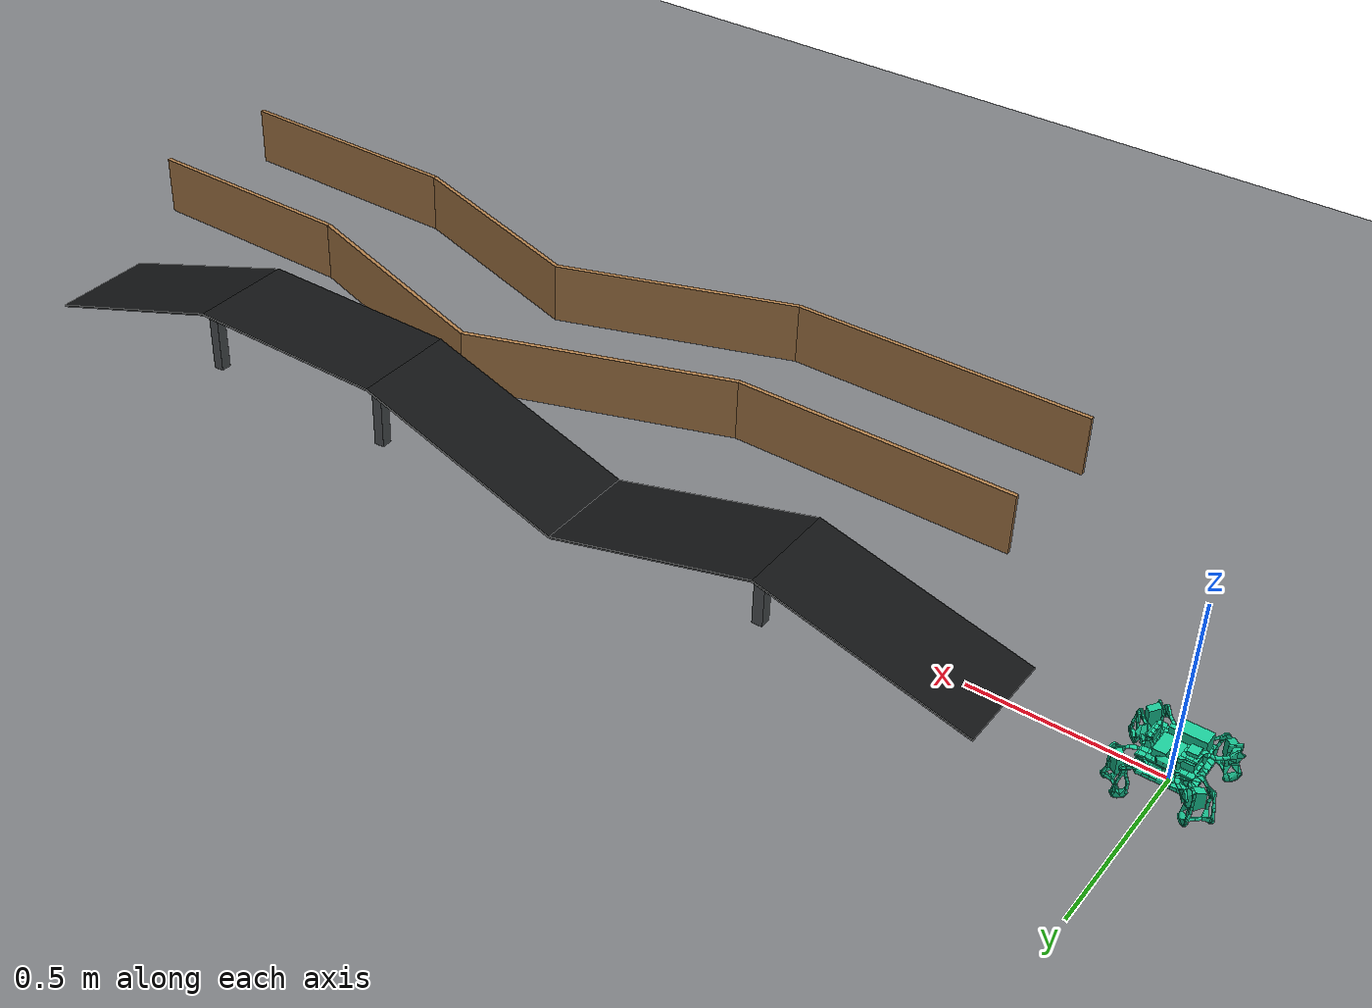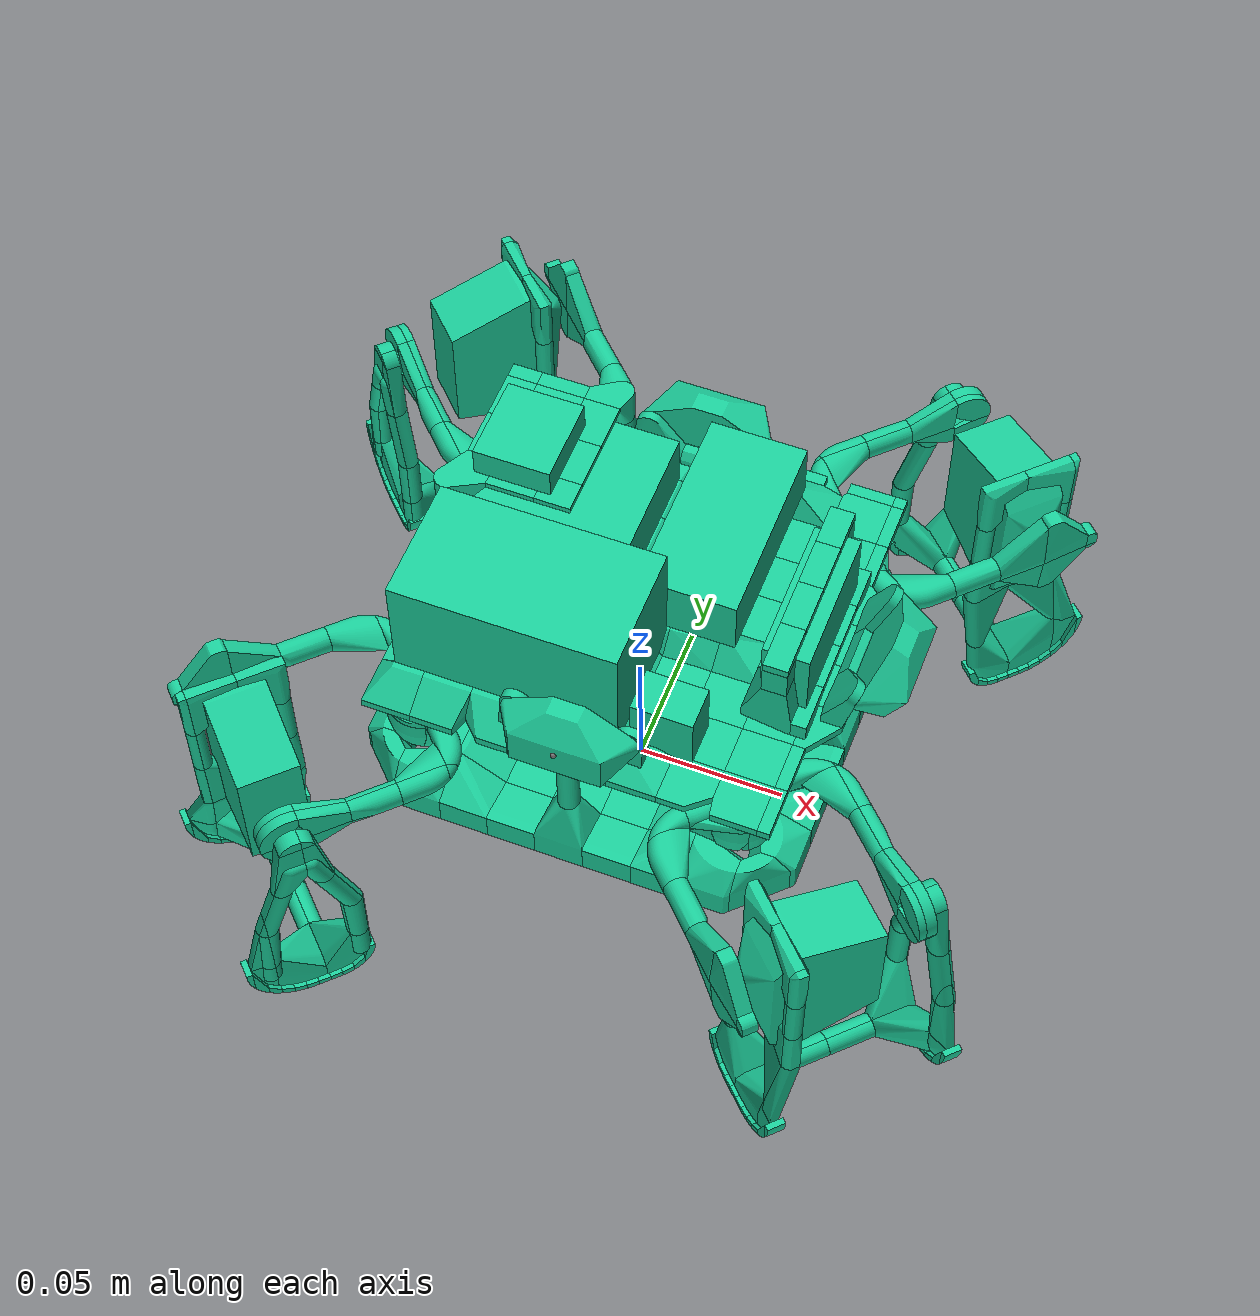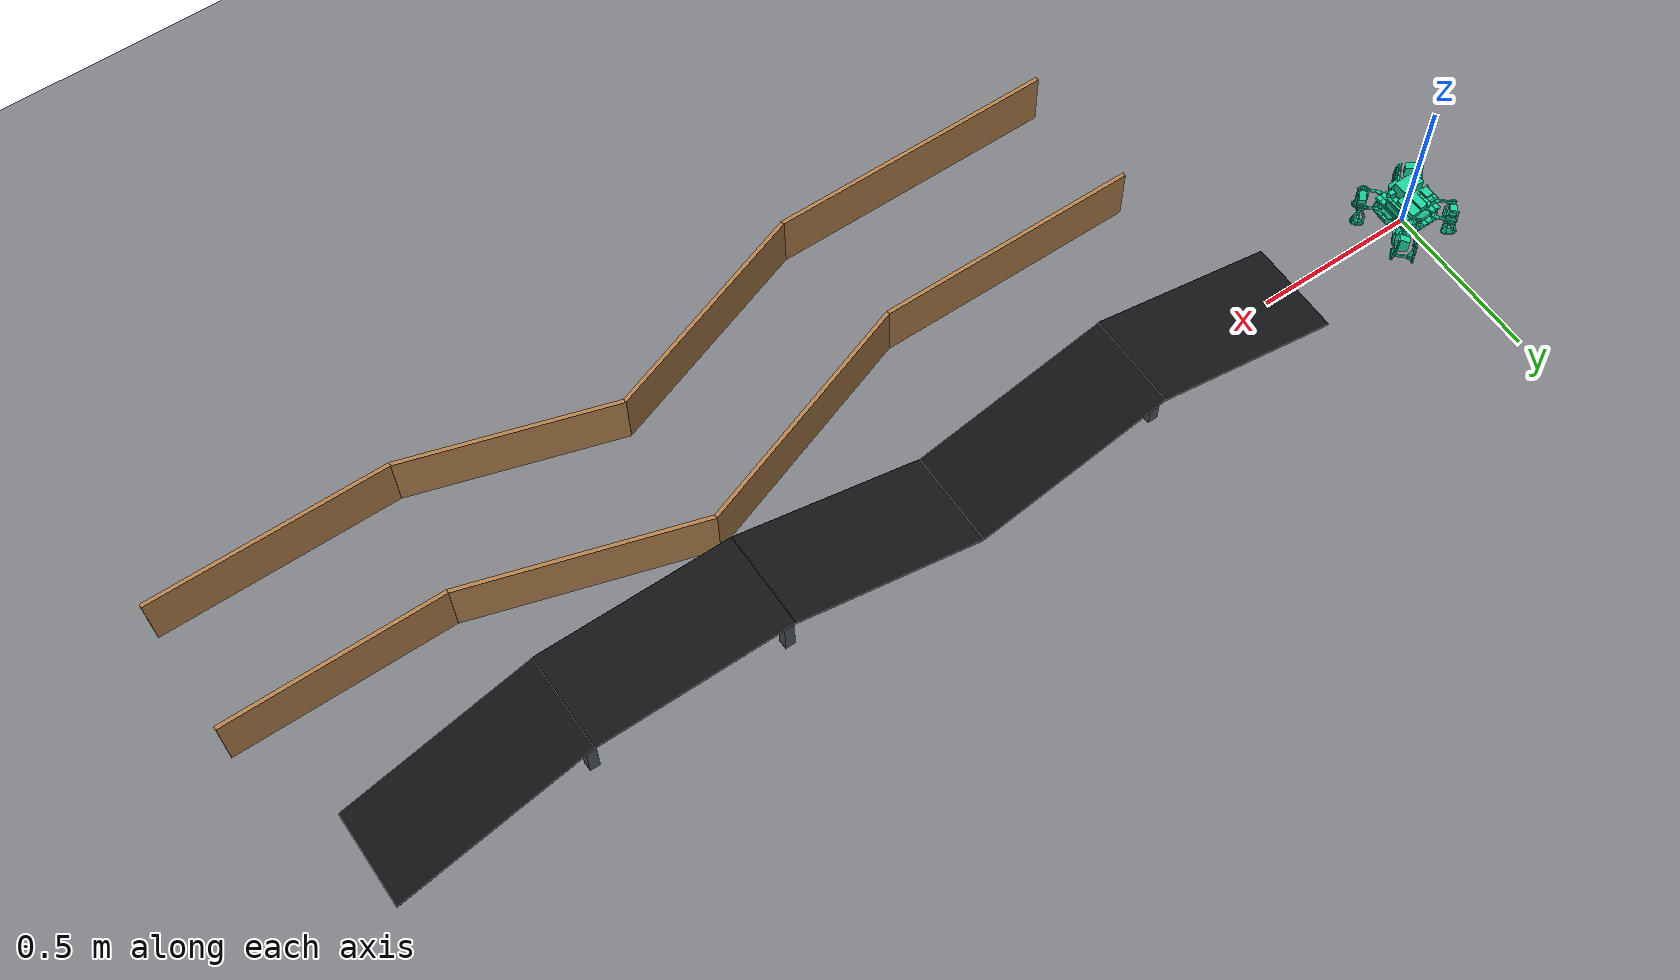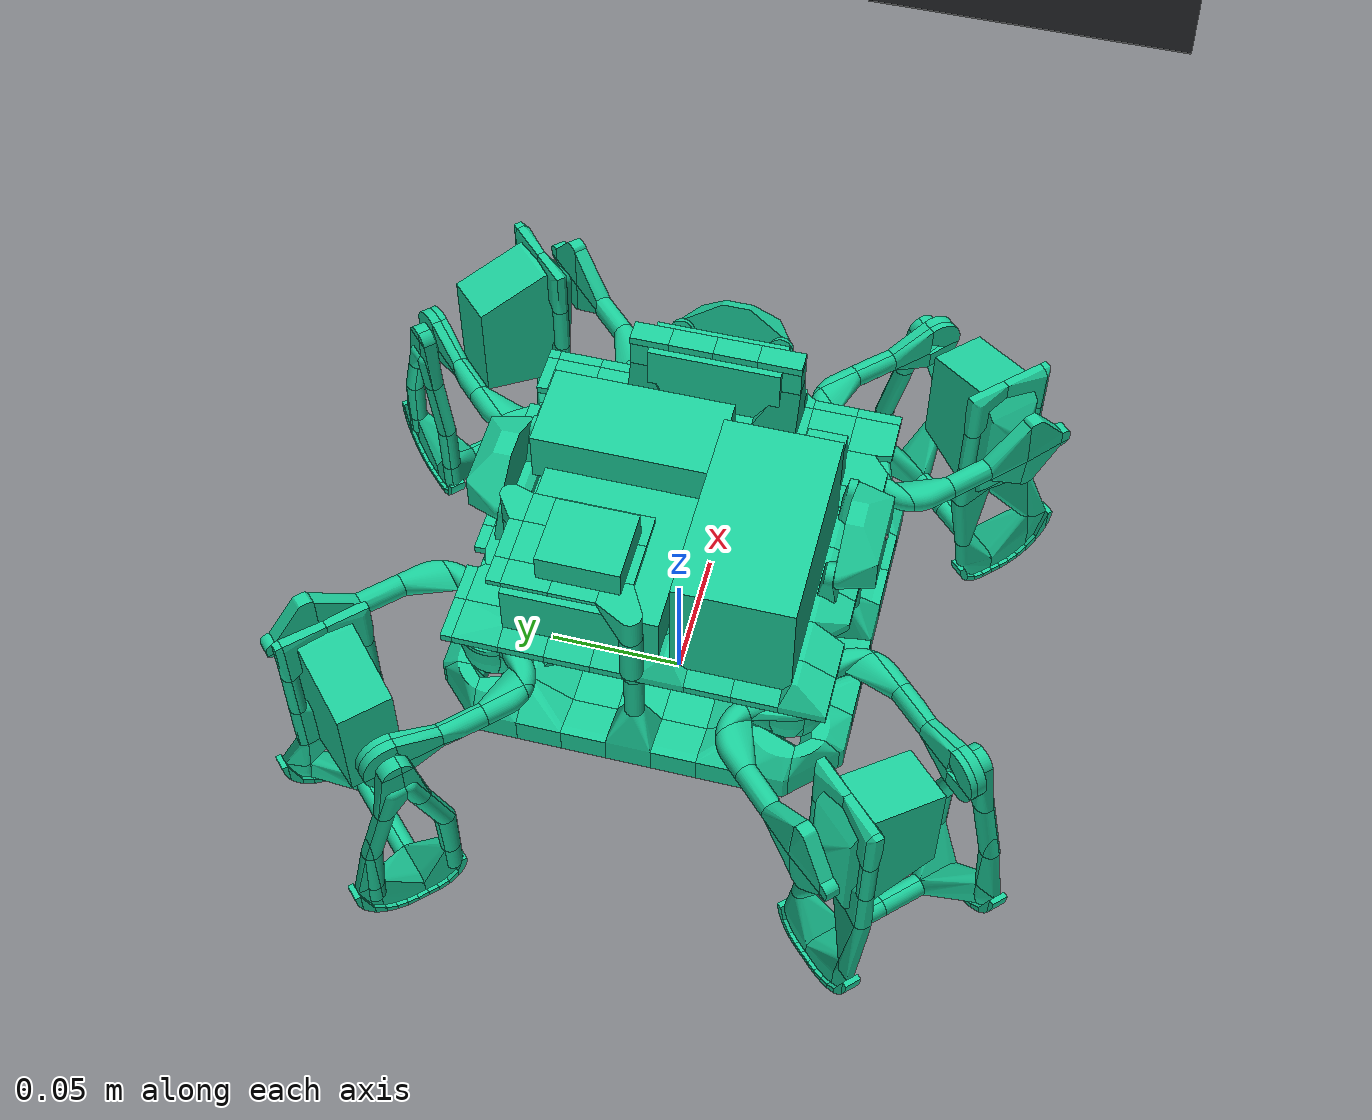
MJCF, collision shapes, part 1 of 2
<?xml version='1.0' encoding='utf-8'?>
<mujoco model="B9-1 CAD transfer">
  <compiler angle="radian" meshdir="robot_meshes_b91" inertiafromgeom="false" autolimits="true" />
  <option timestep=".002" integrator="implicitfast" cone="elliptic" iterations="60" />
  <visual>
    <global offwidth="1280" offheight="900" />
    <headlight ambient=".45 .45 .45" />
  </visual>
  <asset>
    <texture name="checker" type="2d" builtin="checker" rgb1=".85 .85 .85" rgb2=".12 .14 .17" width="512" height="512" />
    <material name="checker_floor" texture="checker" texrepeat="5 5" texuniform="true" />
    <mesh name="cad_0" file="cad_0.obj" inertia="shell" maxhullvert="64" />
    <mesh name="collision_0_0" vertex="-0.070627419 -0.055999998 -0.003 -0.070627419 -0.055999998 0.007 -0.065414533 -0.055999998 0.0127 -0.065314794 -0.056326237 0.0127 -0.065155697 -0.056788282 0.0127 -0.065070124 -0.05701715 0.0127 -0.064887066 -0.057470236 0.0127 -0.064688311 -0.057916656 0.0127 -0.064583116 -0.058137197 0.0127 -0.064474092 -0.058355865 0.0127 -0.064244676 -0.058787336 0.0127 -0.064000344 -0.059210534 0.0127 -0.063872671 -0.059418869 0.0127 -0.063606524 -0.059828701 0.0127 -0.063180895 -0.06042541 0.0127 -0.06303215 -0.060619259 0.0127 -0.062724624 -0.060999026 0.0127 -0.062565932 -0.061184826 0.0127 -0.062404027 -0.061367826 0.0127 -0.062070756 -0.061725216 0.0127 -0.061899495 -0.061899495 0.0127 -0.061547976 -0.062238951 0.0127 -0.061367826 -0.062404027 0.0127 -0.061184826 -0.062565932 0.0127 -0.060810485 -0.062880044 0.0127 -0.060725398 -0.055999998 0.0127 -0.060724566 -0.055999998 -0.003 -0.060619259 -0.06303215 0.0127 -0.060030069 -0.063468127 0.0127 -0.059624949 -0.063741388 0.0127 -0.059418869 -0.063872671 0.0127 -0.059000001 -0.064124355 0.0127 -0.058572602 -0.064361267 0.0127 -0.058355865 -0.064474092 0.0127 -0.058137197 -0.064583116 0.0127 -0.057694311 -0.064789639 0.0127 -0.057244492 -0.064980574 0.0127 -0.05701715 -0.065070124 0.0127 -0.056733917 -0.055999998 0.003 -0.056733917 -0.055999998 0.0067 -0.056557956 -0.06523726 0.0127 -0.056093202 -0.065388265 0.0127 -0.055999998 -0.070627419 -0.003 -0.055999998 -0.070627419 0.007 -0.055999998 -0.065415874 0.0127 -0.055999998 -0.060725398 -0.003 -0.055999998 -0.060724566 0.0127 -0.055999998 -0.056736459 0.003 -0.055999998 -0.056736459 0.0067" inertia="shell" />
    <mesh name="collision_0_1" vertex="-0.071999998 -0.054627419 -0.003 -0.071999998 -0.054627419 0.007 -0.071999998 -0.039999998 -0.003 -0.071999998 -0.039999998 0.007 -0.070627419 -0.055999998 -0.003 -0.070627419 -0.055999998 0.007 -0.065999999 -0.051999998 0.0127 -0.065991473 -0.052488594 0.0127 -0.065980811 -0.051267295 0.0127 -0.065965896 -0.052976589 0.0127 -0.065946727 -0.050779819 0.0127 -0.065923305 -0.053463397 0.0127 -0.065895648 -0.050293827 0.0127 -0.065863752 -0.053948421 0.0127 -0.065827637 -0.049809918 0.0127 -0.065787311 -0.054431076 0.0127 -0.065742779 -0.049328675 0.0127 -0.065694065 -0.054910765 0.0127 -0.065641179 -0.048850684 0.0127 -0.06558414 -0.055386906 0.0127 -0.065522962 -0.055623465 0.0127 -0.065522962 -0.048376532 0.0127 -0.065457664 -0.055858922 0.0127 -0.065457664 -0.048141079 0.0127 -0.065414533 -0.055999998 0.0127 -0.065388265 -0.047906795 0.0127 -0.06523726 -0.047442045 0.0127 -0.065070124 -0.046982851 0.0127 -0.064980574 -0.046755509 0.0127 -0.064789639 -0.046305685 0.0127 -0.064583116 -0.045862803 0.0127 -0.064474092 -0.045644131 0.0127 -0.064361267 -0.045427399 0.0127 -0.064124355 -0.045 0.0127 -0.063872671 -0.044581132 0.0127 -0.063741388 -0.044375052 0.0127 -0.063468127 -0.043969932 0.0127 -0.06303215 -0.043380737 0.0127 -0.062880044 -0.043189516 0.0127 -0.062565932 -0.042815175 0.0127 -0.062404027 -0.04263217 0.0127 -0.062238951 -0.042452021 0.0127 -0.061899495 -0.042100506 0.0127 -0.061725216 -0.041929245 0.0127 -0.061367826 -0.041595974 0.0127 -0.061184826 -0.041434064 0.0127 -0.060999026 -0.041275377 0.0127 -0.060725398 -0.055999998 0.0127 -0.060724566 -0.055999998 -0.003 -0.060619259 -0.040967851 0.0127 -0.06042541 -0.040819101 0.0127 -0.059828701 -0.040393472 0.0127 -0.059418869 -0.040127325 0.0127 -0.059211091 -0.039999998 0.0127 -0.056733917 -0.055999998 0.003 -0.056733917 -0.055999998 0.0067 -0.055999998 -0.047266084 0.003 -0.055999998 -0.047266084 0.0067 -0.055999998 -0.043275431 -0.003 -0.055999998 -0.043274603 0.0127 -0.055999998 -0.039999998 -0.003 -0.055999998 -0.039999998 0.0127" inertia="shell" />
    <mesh name="collision_0_2" vertex="-0.071999998 -0.039999998 -0.003 -0.071999998 -0.039999998 0.007 -0.071999998 -0.023999998 -0.003 -0.071999998 -0.023999998 0.007 -0.069000001 -0.023999998 0.007 -0.059211091 -0.039999998 0.0127 -0.059210534 -0.039999657 0.0127 -0.058787336 -0.039755323 0.0127 -0.058355865 -0.039525909 0.0127 -0.058137197 -0.039416883 0.0127 -0.057916656 -0.03931169 0.0127 -0.057470236 -0.039112933 0.0127 -0.05701715 -0.038929875 0.0127 -0.056788282 -0.038844304 0.0127 -0.056326237 -0.03868521 0.0127 -0.055999998 -0.039999998 -0.003 -0.055999998 -0.039999998 0.0127 -0.055999998 -0.038585469 0.0127 -0.055999998 -0.023999998 -0.003 -0.055999998 -0.023999998 0.004" inertia="shell" />
    <mesh name="collision_0_3" vertex="-0.071999998 -0.023999998 -0.003 -0.071999998 -0.023999998 0.007 -0.071999998 -0.007999998 -0.003 -0.071999998 -0.007999998 0.007 -0.069000001 -0.023999998 0.007 -0.069000001 -0.007999998 0.007 -0.055999998 -0.023999998 -0.003 -0.055999998 -0.023999998 0.004 -0.055999998 -0.007999998 -0.003 -0.055999998 -0.007999998 0.004" inertia="shell" />
    <mesh name="collision_0_4" vertex="-0.071999998 -0.007999998 -0.003 -0.071999998 -0.007999998 0.007 -0.071999998 0.008000002 -0.003 -0.071999998 0.008000002 0.007 -0.069000001 -0.007999998 0.007 -0.069000001 0.008000002 0.007 -0.065500002 0 0.017 -0.065499661 3.9026e-05 0.017 -0.065499468 6.1083e-05 0.017 -0.065487701 -0.000175899 0.017 -0.065465937 -0.000487106 0.017 -0.06545691 0.000547521 0.017 -0.065364418 -0.000964731 0.017 -0.065347066 0.001023301 0.017 -0.065218466 0.001349772 0.017 -0.065172076 -0.001479164 0.017 -0.065145779 0.001534299 0.017 -0.065109969 -0.001595972 0.017 -0.065032304 0.001739011 0.017 -0.065000086 -0.001802633 0.017 -0.064968166 0.001854717 0.017 -0.064964534 -0.00185844 0.017 -0.064903554 0.00195234 0.017 -0.064901633 -0.001957175 0.017 -0.064867034 0.002007518 0.017 -0.064762987 -0.002128388 0.017 -0.064517689 -0.002431304 0.017 -0.064502228 -0.002447038 0.017 -0.064474874 -0.002474874 0.017 -0.064474874 0.002474874 0.017 -0.064431305 0.002517689 0.017 -0.064007516 -0.002867032 0.017 -0.063957176 0.002901632 0.017 -0.063952339 -0.002903554 0.017 -0.063854718 -0.002968168 0.017 -0.063802633 0.003000086 0.017 -0.063595974 0.003109969 0.017 -0.063534298 -0.003145779 0.017 -0.063479166 0.003172077 0.017 -0.0630233 -0.003347067 0.017 -0.06296473 0.003364416 0.017 -0.062547522 -0.003456909 0.017 -0.062487106 0.003465938 0.017 -0.062175898 0.0034877 0.017 -0.062061086 -0.003499467 0.017 -0.061999998 0.0035 0.017 -0.061650194 0.00347247 0.017 -0.061512895 -0.003465938 0.017 -0.061452479 0.003456909 0.017 -0.061035271 -0.003364416 0.017 -0.060976701 0.003347067 0.017 -0.060520835 -0.003172077 0.017 -0.060465703 0.003145779 0.017 -0.060404027 -0.003109969 0.017 -0.060197368 -0.003000086 0.017 -0.060145283 0.002968168 0.017 -0.060047659 0.002903554 0.017 -0.060042825 -0.002901632 0.017 -0.05999248 0.002867032 0.017 -0.059568696 -0.002517689 0.017 -0.059525127 -0.002474874 0.017 -0.059525127 0.002474874 0.017 -0.059497773 0.002447038 0.017 -0.059482312 0.002431304 0.017 -0.059237014 0.002128388 0.017 -0.059132967 -0.002007518 0.017 -0.059098368 0.001957175 0.017 -0.059096445 -0.00195234 0.017 -0.059035467 0.00185844 0.017 -0.05903183 -0.001854717 0.017 -0.058999915 0.001802633 0.017 -0.058967694 -0.001739011 0.017 -0.058890032 0.001595972 0.017 -0.058854222 -0.001534299 0.017 -0.058827925 0.001479164 0.017 -0.058781535 -0.001349772 0.017 -0.058652935 -0.001023301 0.017 -0.058635583 0.000964731 0.017 -0.058570721 0.000659582 0.017 -0.058543091 -0.000547521 0.017 -0.05853406 0.000487106 0.017 -0.058500533 -6.1083e-05 0.017 -0.05850034 -3.9026e-05 0.017 -0.058499999 0 0.017 -0.055999998 -0.007999998 -0.003 -0.055999998 -0.007999998 0.004 -0.055999998 0.008000002 -0.003 -0.055999998 0.008000002 0.004" inertia="shell" />
    <mesh name="collision_0_5" vertex="-0.065500002 0 0.017 -0.065500002 0 0.037 -0.065499661 3.9026e-05 0.017 -0.065499468 6.1083e-05 0.017 -0.065499468 6.1083e-05 0.037 -0.065487701 -0.000175899 0.017 -0.065465937 -0.000487106 0.017 -0.065465937 -0.000487106 0.037 -0.06545691 0.000547521 0.017 -0.06545691 0.000547521 0.037 -0.065372878 -0.000924929 0.037 -0.065364418 -0.000964731 0.017 -0.065364418 -0.000964731 0.037 -0.065347066 0.001023301 0.017 -0.065347066 0.001023301 0.037 -0.065218466 0.001349772 0.017 -0.065188105 -0.001436294 0.037 -0.065172076 -0.001479164 0.017 -0.065172076 -0.001479164 0.037 -0.065145779 0.001534299 0.017 -0.065145779 0.001534299 0.037 -0.065109969 -0.001595972 0.017 -0.065032304 0.001739011 0.017 -0.065000086 -0.001802633 0.017 -0.065000086 -0.001802633 0.037 -0.064968166 0.001854717 0.017 -0.064968166 0.001854717 0.037 -0.064964534 -0.00185844 0.017 -0.064959739 0.001867451 0.037 -0.064909838 -0.001944297 0.037 -0.064903554 0.00195234 0.017 -0.064901633 -0.001957175 0.017 -0.064901633 -0.001957175 0.037 -0.064867034 0.002007518 0.017 -0.064867034 0.002007518 0.037 -0.064762987 -0.002128388 0.017 -0.064549684 -0.002391794 0.037 -0.064517689 -0.002431304 0.017 -0.064517689 -0.002431304 0.037 -0.064502228 -0.002447038 0.017 -0.064474874 -0.002474874 0.017 -0.064474874 -0.002474874 0.037 -0.064474874 0.002474874 0.017 -0.064474874 0.002474874 0.037 -0.064431305 0.002517689 0.017 -0.064431305 0.002517689 0.037 -0.064007516 -0.002867032 0.017 -0.064007516 -0.002867032 0.037 -0.063957176 0.002901632 0.017 -0.063957176 0.002901632 0.037 -0.063952339 -0.002903554 0.017 -0.063854718 -0.002968168 0.017 -0.063854718 -0.002968168 0.037 -0.063802633 0.003000086 0.017 -0.063802633 0.003000086 0.037 -0.063595974 0.003109969 0.017 -0.063561 -0.003130978 0.037 -0.063534298 -0.003145779 0.017 -0.063534298 -0.003145779 0.037 -0.063479166 0.003172077 0.017 -0.063479166 0.003172077 0.037 -0.0630233 -0.003347067 0.017 -0.0630233 -0.003347067 0.037 -0.06296473 0.003364416 0.017 -0.06296473 0.003364416 0.037 -0.06258717 -0.003447756 0.037 -0.062547522 -0.003456909 0.017 -0.062547522 -0.003456909 0.037 -0.062487106 0.003465938 0.017 -0.062487106 0.003465938 0.037 -0.062446514 0.003468777 0.037 -0.062175898 0.0034877 0.017 -0.062101622 -0.003495921 0.037 -0.062061086 -0.003499467 0.017 -0.062061086 -0.003499467 0.037 -0.061999998 0.0035 0.017 -0.061999998 0.0035 0.037 -0.061650194 0.00347247 0.017 -0.061512895 -0.003465938 0.017 -0.061512895 -0.003465938 0.037 -0.061452479 0.003456909 0.017 -0.061452479 0.003456909 0.037 -0.061412831 0.003447756 0.037 -0.061035271 -0.003364416 0.017 -0.061035271 -0.003364416 0.037 -0.060976701 0.003347067 0.017 -0.060976701 0.003347067 0.037 -0.060520835 -0.003172077 0.017 -0.060520835 -0.003172077 0.037 -0.060465703 0.003145779 0.017 -0.060465703 0.003145779 0.037 -0.060439001 0.003130978 0.037 -0.060404027 -0.003109969 0.017 -0.060197368 -0.003000086 0.017 -0.060197368 -0.003000086 0.037 -0.060145283 0.002968168 0.017 -0.060145283 0.002968168 0.037 -0.060132549 0.00295974 0.037 -0.060047659 0.002903554 0.017 -0.060042825 -0.002901632 0.017 -0.060042825 -0.002901632 0.037 -0.05999248 0.002867032 0.017 -0.05999248 0.002867032 0.037 -0.059568696 -0.002517689 0.017 -0.059568696 -0.002517689 0.037 -0.059525127 -0.002474874 0.017 -0.059525127 -0.002474874 0.037 -0.059525127 0.002474874 0.017 -0.059525127 0.002474874 0.037 -0.059497773 0.002447038 0.017 -0.059482312 0.002431304 0.017 -0.059482312 0.002431304 0.037 -0.059450317 0.002391794 0.037 -0.059237014 0.002128388 0.017 -0.059132967 -0.002007518 0.017 -0.059132967 -0.002007518 0.037 -0.059098368 0.001957175 0.017 -0.059098368 0.001957175 0.037 -0.059096445 -0.00195234 0.017 -0.059090163 0.001944297 0.037 -0.059040258 -0.001867451 0.037 -0.059035467 0.00185844 0.017 -0.05903183 -0.001854717 0.017 -0.05903183 -0.001854717 0.037 -0.058999915 0.001802633 0.017 -0.058999915 0.001802633 0.037 -0.058967694 -0.001739011 0.017 -0.058890032 0.001595972 0.017 -0.058854222 -0.001534299 0.017 -0.058854222 -0.001534299 0.037 -0.058827925 0.001479164 0.017 -0.058827925 0.001479164 0.037 -0.058811896 0.001436294 0.037 -0.058781535 -0.001349772 0.017 -0.058652935 -0.001023301 0.017 -0.058652935 -0.001023301 0.037 -0.058635583 0.000964731 0.017 -0.058635583 0.000964731 0.037 -0.058570721 0.000659582 0.017 -0.058543091 -0.000547521 0.017 -0.058543091 -0.000547521 0.037 -0.05853406 0.000487106 0.017 -0.05853406 0.000487106 0.037 -0.058531221 0.000446514 0.037 -0.058500533 -6.1083e-05 0.017 -0.058500533 -6.1083e-05 0.037 -0.05850034 -3.9026e-05 0.017 -0.058499999 0 0.017 -0.058499999 0 0.037" inertia="shell" />
    <mesh name="collision_0_6" vertex="-0.065500002 0 0.037 -0.065500002 0 0.04 -0.065499468 6.1083e-05 0.037 -0.065499468 6.1083e-05 0.04 -0.065465937 -0.000487106 0.037 -0.065465937 -0.000487106 0.04 -0.06545691 0.000547521 0.037 -0.06545691 0.000547521 0.04 -0.065372878 -0.000924929 0.037 -0.065364418 -0.000964731 0.037 -0.065364418 -0.000964731 0.04 -0.065347066 0.001023301 0.037 -0.065347066 0.001023301 0.04 -0.065188105 -0.001436294 0.037 -0.065172076 -0.001479164 0.037 -0.065172076 -0.001479164 0.04 -0.065145779 0.001534299 0.037 -0.065145779 0.001534299 0.04 -0.065000086 -0.001802633 0.037 -0.065000086 -0.001802633 0.04 -0.064968166 0.001854717 0.037 -0.064968166 0.001854717 0.04 -0.064959739 0.001867451 0.037 -0.064909838 -0.001944297 0.037 -0.064901633 -0.001957175 0.037 -0.064901633 -0.001957175 0.04 -0.064867034 0.002007518 0.037 -0.064867034 0.002007518 0.04 -0.064549684 -0.002391794 0.037 -0.064517689 -0.002431304 0.037 -0.064517689 -0.002431304 0.04 -0.064474874 -0.002474874 0.037 -0.064474874 -0.002474874 0.04 -0.064474874 0.002474874 0.037 -0.064474874 0.002474874 0.04 -0.064431305 0.002517689 0.037 -0.064431305 0.002517689 0.04 -0.064007516 -0.002867032 0.037 -0.064007516 -0.002867032 0.04 -0.063957176 0.002901632 0.037 -0.063957176 0.002901632 0.04 -0.063854718 -0.002968168 0.037 -0.063854718 -0.002968168 0.04 -0.063802633 0.003000086 0.037 -0.063802633 0.003000086 0.04 -0.063561 -0.003130978 0.037 -0.063534298 -0.003145779 0.037 -0.063534298 -0.003145779 0.04 -0.063479166 0.003172077 0.037 -0.063479166 0.003172077 0.04 -0.0630233 -0.003347067 0.037 -0.0630233 -0.003347067 0.04 -0.06296473 0.003364416 0.037 -0.06296473 0.003364416 0.04 -0.06258717 -0.003447756 0.037 -0.062547522 -0.003456909 0.037 -0.062547522 -0.003456909 0.04 -0.062487106 0.003465938 0.037 -0.062487106 0.003465938 0.04 -0.062446514 0.003468777 0.037 -0.062101622 -0.003495921 0.037 -0.062061086 -0.003499467 0.037 -0.062061086 -0.003499467 0.04 -0.061999998 0.0035 0.037 -0.061999998 0.0035 0.04 -0.061512895 -0.003465938 0.037 -0.061512895 -0.003465938 0.04 -0.061452479 0.003456909 0.037 -0.061452479 0.003456909 0.04 -0.061412831 0.003447756 0.037 -0.061035271 -0.003364416 0.037 -0.061035271 -0.003364416 0.04 -0.060976701 0.003347067 0.037 -0.060976701 0.003347067 0.04 -0.060520835 -0.003172077 0.037 -0.060520835 -0.003172077 0.04 -0.060465703 0.003145779 0.037 -0.060465703 0.003145779 0.04 -0.060439001 0.003130978 0.037 -0.060197368 -0.003000086 0.037 -0.060197368 -0.003000086 0.04 -0.060145283 0.002968168 0.037 -0.060145283 0.002968168 0.04 -0.060132549 0.00295974 0.037 -0.060042825 -0.002901632 0.037 -0.060042825 -0.002901632 0.04 -0.05999248 0.002867032 0.037 -0.05999248 0.002867032 0.04 -0.059568696 -0.002517689 0.037 -0.059568696 -0.002517689 0.04 -0.059525127 -0.002474874 0.037 -0.059525127 -0.002474874 0.04 -0.059525127 0.002474874 0.037 -0.059525127 0.002474874 0.04 -0.059482312 0.002431304 0.037 -0.059482312 0.002431304 0.04 -0.059450317 0.002391794 0.037 -0.059132967 -0.002007518 0.037 -0.059132967 -0.002007518 0.04 -0.059098368 0.001957175 0.037 -0.059098368 0.001957175 0.04 -0.059090163 0.001944297 0.037 -0.059040258 -0.001867451 0.037 -0.05903183 -0.001854717 0.037 -0.05903183 -0.001854717 0.04 -0.058999915 0.001802633 0.037 -0.058999915 0.001802633 0.04 -0.058854222 -0.001534299 0.037 -0.058854222 -0.001534299 0.04 -0.058827925 0.001479164 0.037 -0.058827925 0.001479164 0.04 -0.058811896 0.001436294 0.037 -0.058652935 -0.001023301 0.037 -0.058652935 -0.001023301 0.04 -0.058635583 0.000964731 0.037 -0.058635583 0.000964731 0.04 -0.058543091 -0.000547521 0.037 -0.058543091 -0.000547521 0.04 -0.05853406 0.000487106 0.037 -0.05853406 0.000487106 0.04 -0.058531221 0.000446514 0.037 -0.058500533 -6.1083e-05 0.037 -0.058500533 -6.1083e-05 0.04 -0.058499999 0 0.037 -0.058499999 0 0.04" inertia="shell" />
    <mesh name="collision_0_7" vertex="-0.071999998 0.008000002 -0.003 -0.071999998 0.008000002 0.007 -0.071999998 0.024000002 -0.003 -0.071999998 0.024000002 0.007 -0.069000001 0.008000002 0.007 -0.069000001 0.024000002 0.007 -0.055999998 0.008000002 -0.003 -0.055999998 0.008000002 0.004 -0.055999998 0.024000002 -0.003 -0.055999998 0.024000002 0.004" inertia="shell" />
    <mesh name="collision_0_8" vertex="-0.071999998 0.024000002 -0.003 -0.071999998 0.024000002 0.007 -0.071999998 0.040000002 -0.003 -0.071999998 0.040000002 0.007 -0.069000001 0.024000002 0.007 -0.059211097 0.040000002 0.0127 -0.059210534 0.039999657 0.0127 -0.058787336 0.039755323 0.0127 -0.058355865 0.039525909 0.0127 -0.058137197 0.039416883 0.0127 -0.057916656 0.03931169 0.0127 -0.057470236 0.039112933 0.0127 -0.05701715 0.038929875 0.0127 -0.056788282 0.038844304 0.0127 -0.056326237 0.03868521 0.0127 -0.055999998 0.024000002 -0.003 -0.055999998 0.024000002 0.004 -0.055999998 0.038585469 0.0127 -0.055999998 0.040000002 -0.003 -0.055999998 0.040000002 0.0127" inertia="shell" />
    <mesh name="collision_0_9" vertex="-0.071999998 0.040000002 -0.003 -0.071999998 0.040000002 0.007 -0.071999998 0.054627419 -0.003 -0.071999998 0.054627419 0.007 -0.070627415 0.056000002 -0.003 -0.070627415 0.056000002 0.007 -0.065999999 0.051999998 0.0127 -0.065991473 0.052488594 0.0127 -0.065980811 0.051267295 0.0127 -0.065965896 0.052976589 0.0127 -0.065946727 0.050779819 0.0127 -0.065923305 0.053463397 0.0127 -0.065895648 0.050293827 0.0127 -0.065863752 0.053948421 0.0127 -0.065827637 0.049809918 0.0127 -0.065787311 0.054431076 0.0127 -0.065742779 0.049328675 0.0127 -0.065694065 0.054910765 0.0127 -0.065641179 0.048850684 0.0127 -0.06558414 0.055386906 0.0127 -0.065522962 0.048376532 0.0127 -0.065522962 0.055623465 0.0127 -0.065457664 0.048141079 0.0127 -0.065457664 0.055858922 0.0127 -0.065414532 0.056000002 0.0127 -0.065388265 0.047906795 0.0127 -0.06523726 0.047442045 0.0127 -0.065070124 0.046982851 0.0127 -0.064980574 0.046755509 0.0127 -0.064789639 0.046305685 0.0127 -0.064583116 0.045862803 0.0127 -0.064474092 0.045644131 0.0127 -0.064361267 0.045427399 0.0127 -0.064000344 0.044789467 0.0127 -0.063872671 0.044581132 0.0127 -0.063741388 0.044375052 0.0127 -0.063468127 0.043969932 0.0127 -0.06303215 0.043380737 0.0127 -0.062880044 0.043189516 0.0127 -0.062565932 0.042815175 0.0127 -0.062404027 0.04263217 0.0127 -0.062238951 0.042452021 0.0127 -0.061899495 0.042100506 0.0127 -0.061725216 0.041929245 0.0127 -0.061367826 0.041595974 0.0127 -0.061184826 0.041434064 0.0127 -0.060999026 0.041275377 0.0127 -0.060725396 0.056000002 0.0127 -0.060724564 0.056000002 -0.003 -0.060619259 0.040967851 0.0127 -0.06042541 0.040819101 0.0127 -0.059828701 0.040393472 0.0127 -0.059418869 0.040127325 0.0127 -0.059211097 0.040000002 0.0127 -0.056736456 0.056000002 0.0067 -0.056733914 0.056000002 0.003 -0.056726035 0.056000002 0.005000194 -0.055999998 0.040000002 -0.003 -0.055999998 0.040000002 0.0127 -0.055999998 0.043274603 0.0127 -0.055999998 0.043275431 -0.003 -0.055999998 0.047263542 0.0067 -0.055999998 0.047266084 0.003 -0.055999998 0.047273962 0.005000166" inertia="shell" />
    <mesh name="collision_0_10" vertex="-0.070627415 0.056000002 -0.003 -0.070627415 0.056000002 0.007 -0.065414532 0.056000002 0.0127 -0.065314794 0.056326237 0.0127 -0.065155697 0.056788282 0.0127 -0.065070124 0.05701715 0.0127 -0.064887066 0.057470236 0.0127 -0.064688311 0.057916656 0.0127 -0.064583116 0.058137197 0.0127 -0.064474092 0.058355865 0.0127 -0.064244676 0.058787336 0.0127 -0.064000344 0.059210534 0.0127 -0.063872671 0.059418869 0.0127 -0.063606524 0.059828701 0.0127 -0.063180895 0.06042541 0.0127 -0.06303215 0.060619259 0.0127 -0.062724624 0.060999026 0.0127 -0.062565932 0.061184826 0.0127 -0.062404027 0.061367826 0.0127 -0.062070756 0.061725216 0.0127 -0.061899495 0.061899495 0.0127 -0.061547976 0.062238951 0.0127 -0.061367826 0.062404027 0.0127 -0.061184826 0.062565932 0.0127 -0.060810485 0.062880044 0.0127 -0.060725396 0.056000002 0.0127 -0.060724564 0.056000002 -0.003 -0.060619259 0.06303215 0.0127 -0.060030069 0.063468127 0.0127 -0.059624949 0.063741388 0.0127 -0.059418869 0.063872671 0.0127 -0.059000001 0.064124355 0.0127 -0.058572602 0.064361267 0.0127 -0.058355865 0.064474092 0.0127 -0.058137197 0.064583116 0.0127 -0.057694311 0.064789639 0.0127 -0.057244492 0.064980574 0.0127 -0.05701715 0.065070124 0.0127 -0.056736456 0.056000002 0.0067 -0.056733914 0.056000002 0.003 -0.056726035 0.056000002 0.005000194 -0.056557956 0.06523726 0.0127 -0.056093202 0.065388265 0.0127 -0.055999998 0.056726039 0.004699835 -0.055999998 0.056733917 0.0067 -0.055999998 0.056736459 0.003 -0.055999998 0.060724566 0.0127 -0.055999998 0.060725398 -0.003 -0.055999998 0.065415874 0.0127 -0.055999998 0.070627419 -0.003 -0.055999998 0.070627419 0.007" inertia="shell" />
    <mesh name="collision_0_11" vertex="-0.055999998 -0.070627419 -0.003 -0.055999998 -0.070627419 0.007 -0.055999998 -0.065415874 0.0127 -0.055999998 -0.060725398 -0.003 -0.055999998 -0.060724566 0.0127 -0.055999998 -0.056736459 0.003 -0.055999998 -0.056736459 0.0067 -0.055858922 -0.065457664 0.0127 -0.055623465 -0.065522962 0.0127 -0.055149317 -0.065641179 0.0127 -0.054671326 -0.065742779 0.0127 -0.054627419 -0.071999998 -0.003 -0.054627419 -0.071999998 0.007 -0.054190083 -0.065827637 0.0127 -0.053706169 -0.065895648 0.0127 -0.053220181 -0.065946727 0.0127 -0.052732701 -0.065980811 0.0127 -0.052244334 -0.065997868 0.0127 -0.051511407 -0.065991473 0.0127 -0.051023412 -0.065965896 0.0127 -0.050536599 -0.065923305 0.0127 -0.050051575 -0.065863752 0.0127 -0.049568925 -0.065787311 0.0127 -0.049089236 -0.065694065 0.0127 -0.048613095 -0.06558414 0.0127 -0.048376532 -0.065522962 0.0127 -0.048141079 -0.065457664 0.0127 -0.047673764 -0.065314794 0.0127 -0.047263542 -0.055999998 0.003 -0.047263542 -0.055999998 0.0067 -0.047211719 -0.065155697 0.0127 -0.046982851 -0.065070124 0.0127 -0.046529765 -0.064887066 0.0127 -0.046083345 -0.064688311 0.0127 -0.045862803 -0.064583116 0.0127 -0.045644131 -0.064474092 0.0127 -0.045212665 -0.064244676 0.0127 -0.044789467 -0.064000344 0.0127 -0.044581132 -0.063872671 0.0127 -0.0441713 -0.063606524 0.0127 -0.043574591 -0.063180895 0.0127 -0.043380737 -0.06303215 0.0127 -0.043275431 -0.055999998 0.0127 -0.043274603 -0.055999998 -0.003 -0.043000975 -0.062724624 0.0127 -0.042815175 -0.062565932 0.0127 -0.04263217 -0.062404027 0.0127 -0.042274785 -0.062070756 0.0127 -0.042100506 -0.061899495 0.0127 -0.04176105 -0.061547976 0.0127 -0.041595974 -0.061367826 0.0127 -0.041434064 -0.061184826 0.0127 -0.041119957 -0.060810485 0.0127 -0.040967851 -0.060619259 0.0127 -0.040531874 -0.060030069 0.0127 -0.040258613 -0.059624949 0.0127 -0.040127325 -0.059418869 0.0127 -0.039999998 -0.071999998 -0.003 -0.039999998 -0.071999998 0.007 -0.039999998 -0.059206962 0.0127 -0.039999998 -0.055999998 -0.003 -0.039999998 -0.055999998 0.0127" inertia="shell" />
    <mesh name="collision_0_12" vertex="-0.055999998 -0.047266084 0.003 -0.055999998 -0.047266084 0.0067 -0.055999998 -0.043275431 -0.003 -0.055999998 -0.043274603 0.0127 -0.055999998 -0.039999998 -0.003 -0.055999998 -0.039999998 0.0127 -0.047263542 -0.055999998 0.003 -0.047263542 -0.055999998 0.0067 -0.044793039 -0.039999998 0.0127 -0.044581132 -0.040127325 0.0127 -0.044375052 -0.040258613 0.0127 -0.044201014 -0.039999998 -0.003 -0.044201014 -0.039999998 0.004 -0.043969932 -0.040531874 0.0127 -0.043380737 -0.040967851 0.0127 -0.043275431 -0.055999998 0.0127 -0.043274603 -0.055999998 -0.003 -0.043189516 -0.041119957 0.0127 -0.042815175 -0.041434064 0.0127 -0.04263217 -0.041595974 0.0127 -0.042452021 -0.04176105 0.0127 -0.042100506 -0.042100506 0.0127 -0.041929245 -0.042274785 0.0127 -0.041595974 -0.04263217 0.0127 -0.041434064 -0.042815175 0.0127 -0.041275377 -0.043000975 0.0127 -0.040967851 -0.043380737 0.0127 -0.040819101 -0.043574591 0.0127 -0.040393472 -0.0441713 0.0127 -0.040127325 -0.044581132 0.0127 -0.039999998 -0.055999998 -0.003 -0.039999998 -0.055999998 0.0127 -0.039999998 -0.04478891 0.0127 -0.039999998 -0.044201014 -0.003 -0.039999998 -0.044201014 0.004" inertia="shell" />
    <mesh name="collision_0_13" vertex="-0.055999998 -0.039999998 -0.003 -0.055999998 -0.039999998 0.0127 -0.055999998 -0.038585469 0.0127 -0.055999998 -0.023999998 -0.003 -0.055999998 -0.023999998 0.004 -0.055858922 -0.038542337 0.0127 -0.055623465 -0.038477039 0.0127 -0.055386906 -0.038415859 0.0127 -0.054910765 -0.038305933 0.0127 -0.054431076 -0.03821269 0.0127 -0.053948421 -0.038136246 0.0127 -0.053463397 -0.038076694 0.0127 -0.052976589 -0.038034103 0.0127 -0.052488594 -0.038008528 0.0127 -0.051999998 -0.038 0.0127 -0.051755667 -0.038002133 0.0127 -0.051267295 -0.038019187 0.0127 -0.050779819 -0.038053274 0.0127 -0.050293827 -0.038104353 0.0127 -0.049809918 -0.038172364 0.0127 -0.049328675 -0.03825722 0.0127 -0.048850684 -0.038358819 0.0127 -0.048376532 -0.038477039 0.0127 -0.048141079 -0.038542337 0.0127 -0.047906795 -0.038611734 0.0127 -0.047442045 -0.038762741 0.0127 -0.046982851 -0.038929875 0.0127 -0.046755509 -0.039019425 0.0127 -0.046305685 -0.039210362 0.0127 -0.045862803 -0.039416883 0.0127 -0.045644131 -0.039525909 0.0127 -0.045427399 -0.039638734 0.0127 -0.045 -0.039875643 0.0127 -0.044793039 -0.039999998 0.0127 -0.044201014 -0.039999998 -0.003 -0.044201014 -0.039999998 0.004 -0.039999998 -0.025009335 -0.003 -0.039999998 -0.025009335 0.004 -0.039999998 -0.023999998 -0.003 -0.039999998 -0.023999998 0.004" inertia="shell" />
    <mesh name="collision_0_14" vertex="-0.055999998 -0.023999998 -0.003 -0.055999998 -0.023999998 0.004 -0.055999998 -0.007999998 -0.003 -0.055999998 -0.007999998 0.004 -0.039999998 -0.023999998 -0.003 -0.039999998 -0.023999998 0.004 -0.039999998 -0.007999998 -0.003 -0.039999998 -0.007999998 0.004" inertia="shell" />
    <mesh name="collision_0_15" vertex="-0.055999998 -0.007999998 -0.003 -0.055999998 -0.007999998 0.004 -0.055999998 0.008000002 -0.003 -0.055999998 0.008000002 0.004 -0.039999998 -0.007999998 -0.003 -0.039999998 -0.007999998 0.004 -0.039999998 0.008000002 -0.003 -0.039999998 0.008000002 0.004" inertia="shell" />
    <mesh name="collision_0_16" vertex="-0.055999998 0.008000002 -0.003 -0.055999998 0.008000002 0.004 -0.055999998 0.024000002 -0.003 -0.055999998 0.024000002 0.004 -0.039999998 0.008000002 -0.003 -0.039999998 0.008000002 0.004 -0.039999998 0.024000002 -0.003 -0.039999998 0.024000002 0.004" inertia="shell" />
    <mesh name="collision_0_17" vertex="-0.055999998 0.024000002 -0.003 -0.055999998 0.024000002 0.004 -0.055999998 0.038585469 0.0127 -0.055999998 0.040000002 -0.003 -0.055999998 0.040000002 0.0127 -0.055858922 0.038542337 0.0127 -0.055623465 0.038477039 0.0127 -0.055386906 0.038415859 0.0127 -0.054910765 0.038305933 0.0127 -0.054431076 0.03821269 0.0127 -0.053948421 0.038136246 0.0127 -0.053463397 0.038076694 0.0127 -0.052976589 0.038034103 0.0127 -0.052488594 0.038008528 0.0127 -0.051999998 0.038 0.0127 -0.051755667 0.038002133 0.0127 -0.051267295 0.038019187 0.0127 -0.050779819 0.038053274 0.0127 -0.050293827 0.038104353 0.0127 -0.049809918 0.038172364 0.0127 -0.049328675 0.03825722 0.0127 -0.048850684 0.038358819 0.0127 -0.048376532 0.038477039 0.0127 -0.048141079 0.038542337 0.0127 -0.047906795 0.038611734 0.0127 -0.047442045 0.038762741 0.0127 -0.046982851 0.038929875 0.0127 -0.046755509 0.039019425 0.0127 -0.046305685 0.039210362 0.0127 -0.045862803 0.039416883 0.0127 -0.045644131 0.039525909 0.0127 -0.045427399 0.039638734 0.0127 -0.045 0.039875643 0.0127 -0.044793033 0.040000002 0.0127 -0.04420101 0.040000002 -0.003 -0.04420101 0.040000002 0.004 -0.039999998 0.024000002 -0.003 -0.039999998 0.024000002 0.004 -0.039999998 0.025009335 -0.003 -0.039999998 0.025009335 0.004" inertia="shell" />
    <mesh name="collision_0_18" vertex="-0.055999998 0.040000002 -0.003 -0.055999998 0.040000002 0.0127 -0.055999998 0.043274603 0.0127 -0.055999998 0.043275431 -0.003 -0.055999998 0.047263542 0.0067 -0.055999998 0.047266084 0.003 -0.055999998 0.047273962 0.005000166 -0.047273966 0.056000002 0.004699806 -0.047266087 0.056000002 0.0067 -0.047263545 0.056000002 0.003 -0.044793033 0.040000002 0.0127 -0.044581132 0.040127325 0.0127 -0.044375052 0.040258613 0.0127 -0.04420101 0.040000002 -0.003 -0.04420101 0.040000002 0.004 -0.043969932 0.040531874 0.0127 -0.043380737 0.040967851 0.0127 -0.043275432 0.056000002 0.0127 -0.043274604 0.056000002 -0.003 -0.043189516 0.041119957 0.0127 -0.042815175 0.041434064 0.0127 -0.04263217 0.041595974 0.0127 -0.042452021 0.04176105 0.0127 -0.042100506 0.042100506 0.0127 -0.041929245 0.042274785 0.0127 -0.041595974 0.04263217 0.0127 -0.041434064 0.042815175 0.0127 -0.041275377 0.043000975 0.0127 -0.040967851 0.043380737 0.0127 -0.040819101 0.043574591 0.0127 -0.040393472 0.0441713 0.0127 -0.040127325 0.044581132 0.0127 -0.039999998 0.044201014 -0.003 -0.039999998 0.044201014 0.004 -0.039999998 0.04478891 0.0127 -0.039999998 0.056000002 -0.003 -0.039999998 0.056000002 0.0127" inertia="shell" />
    <mesh name="collision_0_19" vertex="-0.055999998 0.056726039 0.004699835 -0.055999998 0.056733917 0.0067 -0.055999998 0.056736459 0.003 -0.055999998 0.060724566 0.0127 -0.055999998 0.060725398 -0.003 -0.055999998 0.065415874 0.0127 -0.055999998 0.070627419 -0.003 -0.055999998 0.070627419 0.007 -0.055858922 0.065457664 0.0127 -0.055623465 0.065522962 0.0127 -0.055149317 0.065641179 0.0127 -0.054671326 0.065742779 0.0127 -0.054627419 0.071999998 -0.003 -0.054627419 0.071999998 0.007 -0.054190083 0.065827637 0.0127 -0.053706169 0.065895648 0.0127 -0.053220181 0.065946727 0.0127 -0.052732701 0.065980811 0.0127 -0.052244334 0.065997868 0.0127 -0.051511407 0.065991473 0.0127 -0.051023412 0.065965896 0.0127 -0.050536599 0.065923305 0.0127 -0.050051575 0.065863752 0.0127 -0.049568925 0.065787311 0.0127 -0.049089236 0.065694065 0.0127 -0.048613095 0.06558414 0.0127 -0.048376532 0.065522962 0.0127 -0.048141079 0.065457664 0.0127 -0.047673764 0.065314794 0.0127 -0.047273966 0.056000002 0.004699806 -0.047266087 0.056000002 0.0067 -0.047263545 0.056000002 0.003 -0.047211719 0.065155697 0.0127 -0.046982851 0.065070124 0.0127 -0.046529765 0.064887066 0.0127 -0.046083345 0.064688311 0.0127 -0.045862803 0.064583116 0.0127 -0.045644131 0.064474092 0.0127 -0.045212665 0.064244676 0.0127 -0.044789467 0.064000344 0.0127 -0.044581132 0.063872671 0.0127 -0.0441713 0.063606524 0.0127 -0.043574591 0.063180895 0.0127 -0.043380737 0.06303215 0.0127 -0.043275432 0.056000002 0.0127 -0.043274604 0.056000002 -0.003 -0.043000975 0.062724624 0.0127 -0.042815175 0.062565932 0.0127 -0.04263217 0.062404027 0.0127 -0.042274785 0.062070756 0.0127 -0.042100506 0.061899495 0.0127 -0.04176105 0.061547976 0.0127 -0.041595974 0.061367826 0.0127 -0.041434064 0.061184826 0.0127 -0.041119957 0.060810485 0.0127 -0.040967851 0.060619259 0.0127 -0.040531874 0.060030069 0.0127 -0.040258613 0.059624949 0.0127 -0.040127325 0.059418869 0.0127 -0.039999998 0.056000002 -0.003 -0.039999998 0.056000002 0.0127 -0.039999998 0.059206962 0.0127 -0.039999998 0.071999998 -0.003 -0.039999998 0.071999998 0.007" inertia="shell" />
    <mesh name="collision_0_20" vertex="-0.039999998 -0.071999998 -0.003 -0.039999998 -0.071999998 0.007 -0.039999998 -0.059206962 0.0127 -0.039999998 -0.055999998 -0.003 -0.039999998 -0.055999998 0.0127 -0.039875643 -0.059000001 0.0127 -0.039638734 -0.058572602 0.0127 -0.039525909 -0.058355865 0.0127 -0.039416883 -0.058137197 0.0127 -0.039210362 -0.057694311 0.0127 -0.039019425 -0.057244492 0.0127 -0.038929875 -0.05701715 0.0127 -0.038762741 -0.056557956 0.0127 -0.038611734 -0.056093202 0.0127 -0.038584126 -0.055999998 0.0127 -0.023999998 -0.071999998 -0.003 -0.023999998 -0.071999998 0.007 -0.023999998 -0.069000001 0.007 -0.023999998 -0.055999998 -0.003 -0.023999998 -0.055999998 0.004" inertia="shell" />
    <mesh name="collision_0_21" vertex="-0.039999998 -0.055999998 -0.003 -0.039999998 -0.055999998 0.0127 -0.039999998 -0.04478891 0.0127 -0.039999998 -0.044201014 -0.003 -0.039999998 -0.044201014 0.004 -0.039999657 -0.044789467 0.0127 -0.039755323 -0.045212665 0.0127 -0.039525909 -0.045644131 0.0127 -0.039416883 -0.045862803 0.0127 -0.03931169 -0.046083345 0.0127 -0.039112933 -0.046529765 0.0127 -0.038929875 -0.046982851 0.0127 -0.038844304 -0.047211719 0.0127 -0.03868521 -0.047673764 0.0127 -0.038584126 -0.055999998 0.0127 -0.038542337 -0.055858922 0.0127 -0.038542337 -0.048141079 0.0127 -0.038477039 -0.055623465 0.0127 -0.038477039 -0.048376532 0.0127 -0.038415859 -0.048613095 0.0127 -0.038358819 -0.055149317 0.0127 -0.038305933 -0.049089236 0.0127 -0.03825722 -0.054671326 0.0127 -0.03821269 -0.049568925 0.0127 -0.038172364 -0.054190083 0.0127 -0.038136246 -0.050051575 0.0127 -0.038104353 -0.053706169 0.0127 -0.038076694 -0.050536599 0.0127 -0.038053274 -0.053220181 0.0127 -0.038034103 -0.051023412 0.0127 -0.038019187 -0.052732701 0.0127 -0.038008528 -0.051511407 0.0127 -0.038002133 -0.052244334 0.0127 -0.038 -0.051999998 0.0127 -0.025009335 -0.039999998 -0.003 -0.025009335 -0.039999998 0.004 -0.023999998 -0.055999998 -0.003 -0.023999998 -0.055999998 0.004 -0.023999998 -0.039999998 -0.003 -0.023999998 -0.039999998 0.004" inertia="shell" />
    <mesh name="collision_0_22" vertex="-0.039999998 -0.025009335 -0.003 -0.039999998 -0.025009335 0.004 -0.039999998 -0.023999998 -0.003 -0.039999998 -0.023999998 0.004 -0.038990662 -0.023999998 -0.003 -0.038990662 -0.023999998 0.004 -0.025009335 -0.039999998 -0.003 -0.025009335 -0.039999998 0.004 -0.023999998 -0.039999998 -0.003 -0.023999998 -0.039999998 0.004 -0.023999998 -0.038990662 -0.003 -0.023999998 -0.038990662 0.004" inertia="shell" />
    <mesh name="collision_0_23" vertex="-0.039999998 -0.023999998 -0.003 -0.039999998 -0.023999998 0.004 -0.039999998 -0.007999998 -0.003 -0.039999998 -0.007999998 0.004 -0.038990662 -0.023999998 -0.003 -0.038990662 -0.023999998 0.004 -0.023999998 -0.009009335 -0.003 -0.023999998 -0.009009335 0.004 -0.023999998 -0.007999998 -0.003 -0.023999998 -0.007999998 0.004" inertia="shell" />
    <mesh name="collision_0_24" vertex="-0.039999998 -0.007999998 -0.003 -0.039999998 -0.007999998 0.004 -0.039999998 0.008000002 -0.003 -0.039999998 0.008000002 0.004 -0.023999998 -0.007999998 -0.003 -0.023999998 -0.007999998 0.004 -0.023999998 0.008000002 -0.003 -0.023999998 0.008000002 0.004" inertia="shell" />
    <mesh name="collision_0_25" vertex="-0.039999998 0.008000002 -0.003 -0.039999998 0.008000002 0.004 -0.039999998 0.024000002 -0.003 -0.039999998 0.024000002 0.004 -0.038990665 0.024000002 -0.003 -0.038990665 0.024000002 0.004 -0.023999998 0.008000002 -0.003 -0.023999998 0.008000002 0.004 -0.023999998 0.009009335 -0.003 -0.023999998 0.009009335 0.004" inertia="shell" />
    <mesh name="collision_0_26" vertex="-0.039999998 0.024000002 -0.003 -0.039999998 0.024000002 0.004 -0.039999998 0.025009335 -0.003 -0.039999998 0.025009335 0.004 -0.038990665 0.024000002 -0.003 -0.038990665 0.024000002 0.004 -0.025009338 0.040000002 -0.003 -0.025009338 0.040000002 0.004 -0.023999998 0.038990662 -0.003 -0.023999998 0.038990662 0.004 -0.023999998 0.040000002 -0.003 -0.023999998 0.040000002 0.004" inertia="shell" />
    <mesh name="collision_0_27" vertex="-0.039999998 0.044201014 -0.003 -0.039999998 0.044201014 0.004 -0.039999998 0.04478891 0.0127 -0.039999998 0.056000002 -0.003 -0.039999998 0.056000002 0.0127 -0.039999657 0.044789467 0.0127 -0.039875643 0.045 0.0127 -0.039525909 0.045644131 0.0127 -0.039416883 0.045862803 0.0127 -0.03931169 0.046083345 0.0127 -0.039112933 0.046529765 0.0127 -0.038929875 0.046982851 0.0127 -0.038844304 0.047211719 0.0127 -0.03868521 0.047673764 0.0127 -0.038584127 0.056000002 0.0127 -0.038542337 0.048141079 0.0127 -0.038542337 0.055858922 0.0127 -0.038477039 0.048376532 0.0127 -0.038477039 0.055623465 0.0127 -0.038415859 0.048613095 0.0127 -0.038358819 0.055149317 0.0127 -0.038305933 0.049089236 0.0127 -0.03825722 0.054671326 0.0127 -0.03821269 0.049568925 0.0127 -0.038172364 0.054190083 0.0127 -0.038136246 0.050051575 0.0127 -0.038104353 0.053706169 0.0127 -0.038076694 0.050536599 0.0127 -0.038053274 0.053220181 0.0127 -0.038034103 0.051023412 0.0127 -0.038019187 0.052732701 0.0127 -0.038008528 0.051511407 0.0127 -0.038002133 0.052244334 0.0127 -0.038 0.051999998 0.0127 -0.025009338 0.040000002 -0.003 -0.025009338 0.040000002 0.004 -0.023999998 0.040000002 -0.003 -0.023999998 0.040000002 0.004 -0.023999998 0.056000002 -0.003 -0.023999998 0.056000002 0.004" inertia="shell" />
    <mesh name="collision_0_28" vertex="-0.039999998 0.056000002 -0.003 -0.039999998 0.056000002 0.0127 -0.039999998 0.059206962 0.0127 -0.039999998 0.071999998 -0.003 -0.039999998 0.071999998 0.007 -0.039875643 0.059000001 0.0127 -0.039638734 0.058572602 0.0127 -0.039525909 0.058355865 0.0127 -0.039416883 0.058137197 0.0127 -0.039210362 0.057694311 0.0127 -0.039019425 0.057244492 0.0127 -0.038929875 0.05701715 0.0127 -0.038762741 0.056557956 0.0127 -0.038611734 0.056093202 0.0127 -0.038584127 0.056000002 0.0127 -0.023999998 0.056000002 -0.003 -0.023999998 0.056000002 0.004 -0.023999998 0.069000001 0.007 -0.023999998 0.071999998 -0.003 -0.023999998 0.071999998 0.007" inertia="shell" />
    <mesh name="collision_0_29" vertex="-0.023999998 -0.071999998 -0.003 -0.023999998 -0.071999998 0.007 -0.023999998 -0.069000001 0.007 -0.023999998 -0.055999998 -0.003 -0.023999998 -0.055999998 0.004 -0.007999998 -0.071999998 -0.003 -0.007999998 -0.071999998 0.007 -0.007999998 -0.069000001 0.007 -0.007999998 -0.055999998 -0.003 -0.007999998 -0.055999998 0.004" inertia="shell" />
    <mesh name="collision_0_30" vertex="-0.023999998 -0.055999998 -0.003 -0.023999998 -0.055999998 0.004 -0.023999998 -0.039999998 -0.003 -0.023999998 -0.039999998 0.004 -0.007999998 -0.055999998 -0.003 -0.007999998 -0.055999998 0.004 -0.007999998 -0.039999998 -0.003 -0.007999998 -0.039999998 0.004" inertia="shell" />
    <mesh name="collision_0_31" vertex="-0.023999998 -0.039999998 -0.003 -0.023999998 -0.039999998 0.004 -0.023999998 -0.038990662 -0.003 -0.023999998 -0.038990662 0.004 -0.009009335 -0.023999998 -0.003 -0.009009335 -0.023999998 0.004 -0.007999998 -0.039999998 -0.003 -0.007999998 -0.039999998 0.004 -0.007999998 -0.023999998 -0.003 -0.007999998 -0.023999998 0.004" inertia="shell" />
    <mesh name="collision_0_32" vertex="-0.023999998 -0.009009335 -0.003 -0.023999998 -0.009009335 0.004 -0.023999998 -0.007999998 -0.003 -0.023999998 -0.007999998 0.004 -0.011 -0.007999998 -0.003 -0.011 -0.007999998 0.004 -0.009009335 -0.023999998 -0.003 -0.009009335 -0.023999998 0.004 -0.007999998 -0.023999998 -0.003 -0.007999998 -0.023999998 0.004 -0.007999998 -0.011025794 -0.003 -0.007999998 -0.011 0.004" inertia="shell" />
    <mesh name="collision_0_33" vertex="-0.023999998 -0.007999998 -0.003 -0.023999998 -0.007999998 0.004 -0.023999998 0.008000002 -0.003 -0.023999998 0.008000002 0.004 -0.011025794 0.008000002 0.004 -0.011 -0.007999998 -0.003 -0.011 -0.007999998 0.004 -0.011 0.005014794 0.004 -0.011 0.008000002 -0.003 -0.011 0.008000002 -0.001146933" inertia="shell" />
    <mesh name="collision_0_34" vertex="-0.023999998 0.008000002 -0.003 -0.023999998 0.008000002 0.004 -0.023999998 0.009009335 -0.003 -0.023999998 0.009009335 0.004 -0.011025794 0.008000002 0.004 -0.011 0.008000002 -0.003 -0.011 0.008000002 -0.001146933 -0.009009338 0.024000002 -0.003 -0.009009338 0.024000002 0.004 -0.007999998 0.011 0.002146939 -0.007999998 0.011 0.004 -0.007999998 0.011025794 -0.003 -0.007999998 0.024000002 -0.003 -0.007999998 0.024000002 0.004" inertia="shell" />
    <mesh name="collision_0_35" vertex="-0.023999998 0.038990662 -0.003 -0.023999998 0.038990662 0.004 -0.023999998 0.040000002 -0.003 -0.023999998 0.040000002 0.004 -0.009009338 0.024000002 -0.003 -0.009009338 0.024000002 0.004 -0.007999998 0.024000002 -0.003 -0.007999998 0.024000002 0.004 -0.007999998 0.040000002 -0.003 -0.007999998 0.040000002 0.004" inertia="shell" />
    <mesh name="collision_0_36" vertex="-0.023999998 0.040000002 -0.003 -0.023999998 0.040000002 0.004 -0.023999998 0.056000002 -0.003 -0.023999998 0.056000002 0.004 -0.007999998 0.040000002 -0.003 -0.007999998 0.040000002 0.004 -0.007999998 0.056000002 -0.003 -0.007999998 0.056000002 0.004" inertia="shell" />
    <mesh name="collision_0_37" vertex="-0.023999998 0.056000002 -0.003 -0.023999998 0.056000002 0.004 -0.023999998 0.069000001 0.007 -0.023999998 0.071999998 -0.003 -0.023999998 0.071999998 0.007 -0.007999998 0.056000002 -0.003 -0.007999998 0.056000002 0.004 -0.007999998 0.069000001 0.007 -0.007999998 0.071999998 -0.003 -0.007999998 0.071999998 0.007" inertia="shell" />
    <mesh name="collision_0_38" vertex="-0.007999998 -0.071999998 -0.003 -0.007999998 -0.071999998 0.007 -0.007999998 -0.069000001 0.007 -0.007999998 -0.055999998 -0.003 -0.007999998 -0.055999998 0.004 -0.0035 -0.061999998 0.017 -0.0034877 -0.062175898 0.017 -0.00347247 -0.061650194 0.017 -0.003465938 -0.062487106 0.017 -0.003456909 -0.061452479 0.017 -0.003364416 -0.06296473 0.017 -0.003347067 -0.060976701 0.017 -0.003172077 -0.063479166 0.017 -0.003145779 -0.060465703 0.017 -0.003109969 -0.063595974 0.017 -0.003000086 -0.063802633 0.017 -0.002968168 -0.060145283 0.017 -0.002903554 -0.060047659 0.017 -0.002901632 -0.063957176 0.017 -0.002867032 -0.05999248 0.017 -0.002517689 -0.064431305 0.017 -0.002474874 -0.064474874 0.017 -0.002474874 -0.059525127 0.017 -0.002447038 -0.059497773 0.017 -0.002431304 -0.059482312 0.017 -0.002128388 -0.059237014 0.017 -0.002007518 -0.064867034 0.017 -0.001957175 -0.059098368 0.017 -0.00195234 -0.064903554 0.017 -0.00185844 -0.059035467 0.017 -0.001854717 -0.064968166 0.017 -0.001802633 -0.058999915 0.017 -0.001739011 -0.065032304 0.017 -0.001595972 -0.058890032 0.017 -0.001534299 -0.065145779 0.017 -0.001479164 -0.058827925 0.017 -0.001349772 -0.065218466 0.017 -0.001023301 -0.065347066 0.017 -0.000964731 -0.058635583 0.017 -0.000659582 -0.058570721 0.017 -0.000547521 -0.06545691 0.017 -0.000487106 -0.05853406 0.017 -6.1083e-05 -0.065499468 0.017 -3.9026e-05 -0.065499661 0.017 0 -0.065500002 0.017 0 -0.058499999 0.017 3.9026e-05 -0.05850034 0.017 6.1083e-05 -0.058500533 0.017 0.000175899 -0.065487701 0.017 0.000487106 -0.065465937 0.017 0.000547521 -0.058543091 0.017 0.000964731 -0.065364418 0.017 0.001023301 -0.058652935 0.017 0.001349772 -0.058781535 0.017 0.001479164 -0.065172076 0.017 0.001534299 -0.058854222 0.017 0.001595972 -0.065109969 0.017 0.001739011 -0.058967694 0.017 0.001802633 -0.065000086 0.017 0.001854717 -0.05903183 0.017 0.00185844 -0.064964534 0.017 0.00195234 -0.059096445 0.017 0.001957175 -0.064901633 0.017 0.002007518 -0.059132967 0.017 0.002128388 -0.064762987 0.017 0.002431304 -0.064517689 0.017 0.002447038 -0.064502228 0.017 0.002474874 -0.064474874 0.017 0.002474874 -0.059525127 0.017 0.002517689 -0.059568696 0.017 0.002867032 -0.064007516 0.017 0.002901632 -0.060042825 0.017 0.002903554 -0.063952339 0.017 0.002968168 -0.063854718 0.017 0.003000086 -0.060197368 0.017 0.003109969 -0.060404027 0.017 0.003145779 -0.063534298 0.017 0.003172077 -0.060520835 0.017 0.003347067 -0.0630233 0.017 0.003364416 -0.061035271 0.017 0.003429277 -0.061340419 0.017 0.003456909 -0.062547522 0.017 0.003478238 -0.061688793 0.017 0.003499467 -0.062061086 0.017 0.003499659 -0.062039026 0.017 0.008000002 -0.071999998 -0.003 0.008000002 -0.071999998 0.007 0.008000002 -0.069000001 0.007 0.008000002 -0.055999998 -0.003 0.008000002 -0.055999998 0.004" inertia="shell" />
    <mesh name="collision_0_39" vertex="-0.0035 -0.061999998 0.017 -0.0035 -0.061999998 0.037 -0.0034877 -0.062175898 0.017 -0.00347247 -0.061650194 0.017 -0.003468777 -0.062446514 0.037 -0.003465938 -0.062487106 0.017 -0.003465938 -0.062487106 0.037 -0.003456909 -0.061452479 0.017 -0.003456909 -0.061452479 0.037 -0.003447756 -0.061412831 0.037 -0.003364416 -0.06296473 0.017 -0.003364416 -0.06296473 0.037 -0.003347067 -0.060976701 0.017 -0.003347067 -0.060976701 0.037 -0.003172077 -0.063479166 0.017 -0.003172077 -0.063479166 0.037 -0.003145779 -0.060465703 0.017 -0.003145779 -0.060465703 0.037 -0.003130978 -0.060439001 0.037 -0.003109969 -0.063595974 0.017 -0.003000086 -0.063802633 0.017 -0.003000086 -0.063802633 0.037 -0.002968168 -0.060145283 0.017 -0.002968168 -0.060145283 0.037 -0.00295974 -0.060132549 0.037 -0.002903554 -0.060047659 0.017 -0.002901632 -0.063957176 0.017 -0.002901632 -0.063957176 0.037 -0.002867032 -0.05999248 0.017 -0.002867032 -0.05999248 0.037 -0.002517689 -0.064431305 0.017 -0.002517689 -0.064431305 0.037 -0.002474874 -0.064474874 0.017 -0.002474874 -0.064474874 0.037 -0.002474874 -0.059525127 0.017 -0.002474874 -0.059525127 0.037 -0.002447038 -0.059497773 0.017 -0.002431304 -0.059482312 0.017 -0.002431304 -0.059482312 0.037 -0.002391794 -0.059450317 0.037 -0.002128388 -0.059237014 0.017 -0.002007518 -0.064867034 0.017 -0.002007518 -0.064867034 0.037 -0.001957175 -0.059098368 0.017 -0.001957175 -0.059098368 0.037 -0.00195234 -0.064903554 0.017 -0.001944297 -0.059090163 0.037 -0.001867451 -0.064959739 0.037 -0.00185844 -0.059035467 0.017 -0.001854717 -0.064968166 0.017 -0.001854717 -0.064968166 0.037 -0.001802633 -0.058999915 0.017 -0.001802633 -0.058999915 0.037 -0.001739011 -0.065032304 0.017 -0.001595972 -0.058890032 0.017 -0.001534299 -0.065145779 0.017 -0.001534299 -0.065145779 0.037 -0.001479164 -0.058827925 0.017 -0.001479164 -0.058827925 0.037 -0.001436294 -0.058811896 0.037 -0.001349772 -0.065218466 0.017 -0.001023301 -0.065347066 0.017 -0.001023301 -0.065347066 0.037 -0.000964731 -0.058635583 0.017 -0.000964731 -0.058635583 0.037 -0.000659582 -0.058570721 0.017 -0.000547521 -0.06545691 0.017 -0.000547521 -0.06545691 0.037 -0.000487106 -0.05853406 0.017 -0.000487106 -0.05853406 0.037 -0.000446514 -0.058531221 0.037 -6.1083e-05 -0.065499468 0.017 -6.1083e-05 -0.065499468 0.037 -3.9026e-05 -0.065499661 0.017 0 -0.065500002 0.017 0 -0.065500002 0.037 0 -0.058499999 0.017 0 -0.058499999 0.037 3.9026e-05 -0.05850034 0.017 6.1083e-05 -0.058500533 0.017 6.1083e-05 -0.058500533 0.037 0.000175899 -0.065487701 0.017 0.000487106 -0.065465937 0.017 0.000487106 -0.065465937 0.037 0.000547521 -0.058543091 0.017 0.000547521 -0.058543091 0.037 0.000924929 -0.065372878 0.037 0.000964731 -0.065364418 0.017 0.000964731 -0.065364418 0.037 0.001023301 -0.058652935 0.017 0.001023301 -0.058652935 0.037 0.001349772 -0.058781535 0.017 0.001436294 -0.065188105 0.037 0.001479164 -0.065172076 0.017 0.001479164 -0.065172076 0.037 0.001534299 -0.058854222 0.017 0.001534299 -0.058854222 0.037 0.001595972 -0.065109969 0.017 0.001739011 -0.058967694 0.017 0.001802633 -0.065000086 0.017 0.001802633 -0.065000086 0.037 0.001854717 -0.05903183 0.017 0.001854717 -0.05903183 0.037 0.00185844 -0.064964534 0.017 0.001867451 -0.059040258 0.037 0.001944297 -0.064909838 0.037 0.00195234 -0.059096445 0.017 0.001957175 -0.064901633 0.017 0.001957175 -0.064901633 0.037 0.002007518 -0.059132967 0.017 0.002007518 -0.059132967 0.037 0.002128388 -0.064762987 0.017 0.002391794 -0.064549684 0.037 0.002431304 -0.064517689 0.017 0.002431304 -0.064517689 0.037 0.002447038 -0.064502228 0.017 0.002474874 -0.064474874 0.017 0.002474874 -0.064474874 0.037 0.002474874 -0.059525127 0.017 0.002474874 -0.059525127 0.037 0.002517689 -0.059568696 0.017 0.002517689 -0.059568696 0.037 0.002867032 -0.064007516 0.017 0.002867032 -0.064007516 0.037 0.002901632 -0.060042825 0.017 0.002901632 -0.060042825 0.037 0.002903554 -0.063952339 0.017 0.002968168 -0.063854718 0.017 0.002968168 -0.063854718 0.037 0.003000086 -0.060197368 0.017 0.003000086 -0.060197368 0.037 0.003109969 -0.060404027 0.017 0.003130978 -0.063561 0.037 0.003145779 -0.063534298 0.017 0.003145779 -0.063534298 0.037 0.003172077 -0.060520835 0.017 0.003172077 -0.060520835 0.037 0.003347067 -0.0630233 0.017 0.003347067 -0.0630233 0.037 0.003364416 -0.061035271 0.017 0.003364416 -0.061035271 0.037 0.003372876 -0.061075073 0.037 0.003429277 -0.061340419 0.017 0.003447756 -0.06258717 0.037 0.003456909 -0.062547522 0.017 0.003456909 -0.062547522 0.037 0.003478238 -0.061688793 0.017 0.003495921 -0.062101622 0.037 0.003497161 -0.061959406 0.037 0.003499467 -0.062061086 0.017 0.003499467 -0.062061086 0.037 0.003499659 -0.062039026 0.017 0.003499956 -0.062005089 0.037" inertia="shell" />
    <mesh name="collision_0_40" vertex="-0.0035 -0.061999998 0.037 -0.0035 -0.061999998 0.04 -0.003468777 -0.062446514 0.037 -0.003465938 -0.062487106 0.037 -0.003465938 -0.062487106 0.04 -0.003456909 -0.061452479 0.037 -0.003456909 -0.061452479 0.04 -0.003447756 -0.061412831 0.037 -0.003364416 -0.06296473 0.037 -0.003364416 -0.06296473 0.04 -0.003347067 -0.060976701 0.037 -0.003347067 -0.060976701 0.04 -0.003172077 -0.063479166 0.037 -0.003172077 -0.063479166 0.04 -0.003145779 -0.060465703 0.037 -0.003145779 -0.060465703 0.04 -0.003130978 -0.060439001 0.037 -0.003000086 -0.063802633 0.037 -0.003000086 -0.063802633 0.04 -0.002968168 -0.060145283 0.037 -0.002968168 -0.060145283 0.04 -0.00295974 -0.060132549 0.037 -0.002901632 -0.063957176 0.037 -0.002901632 -0.063957176 0.04 -0.002867032 -0.05999248 0.037 -0.002867032 -0.05999248 0.04 -0.002517689 -0.064431305 0.037 -0.002517689 -0.064431305 0.04 -0.002474874 -0.064474874 0.037 -0.002474874 -0.064474874 0.04 -0.002474874 -0.059525127 0.037 -0.002474874 -0.059525127 0.04 -0.002431304 -0.059482312 0.037 -0.002431304 -0.059482312 0.04 -0.002391794 -0.059450317 0.037 -0.002007518 -0.064867034 0.037 -0.002007518 -0.064867034 0.04 -0.001957175 -0.059098368 0.037 -0.001957175 -0.059098368 0.04 -0.001944297 -0.059090163 0.037 -0.001867451 -0.064959739 0.037 -0.001854717 -0.064968166 0.037 -0.001854717 -0.064968166 0.04 -0.001802633 -0.058999915 0.037 -0.001802633 -0.058999915 0.04 -0.001534299 -0.065145779 0.037 -0.001534299 -0.065145779 0.04 -0.001479164 -0.058827925 0.037 -0.001479164 -0.058827925 0.04 -0.001436294 -0.058811896 0.037 -0.001023301 -0.065347066 0.037 -0.001023301 -0.065347066 0.04 -0.000964731 -0.058635583 0.037 -0.000964731 -0.058635583 0.04 -0.000547521 -0.06545691 0.037 -0.000547521 -0.06545691 0.04 -0.000487106 -0.05853406 0.037 -0.000487106 -0.05853406 0.04 -0.000446514 -0.058531221 0.037 -6.1083e-05 -0.065499468 0.037 -6.1083e-05 -0.065499468 0.04 0 -0.065500002 0.037 0 -0.065500002 0.04 0 -0.058499999 0.037 0 -0.058499999 0.04 6.1083e-05 -0.058500533 0.037 6.1083e-05 -0.058500533 0.04 0.000487106 -0.065465937 0.037 0.000487106 -0.065465937 0.04 0.000547521 -0.058543091 0.037 0.000547521 -0.058543091 0.04 0.000924929 -0.065372878 0.037 0.000964731 -0.065364418 0.037 0.000964731 -0.065364418 0.04 0.001023301 -0.058652935 0.037 0.001023301 -0.058652935 0.04 0.001436294 -0.065188105 0.037 0.001479164 -0.065172076 0.037 0.001479164 -0.065172076 0.04 0.001534299 -0.058854222 0.037 0.001534299 -0.058854222 0.04 0.001802633 -0.065000086 0.037 0.001802633 -0.065000086 0.04 0.001854717 -0.05903183 0.037 0.001854717 -0.05903183 0.04 0.001867451 -0.059040258 0.037 0.001944297 -0.064909838 0.037 0.001957175 -0.064901633 0.037 0.001957175 -0.064901633 0.04 0.002007518 -0.059132967 0.037 0.002007518 -0.059132967 0.04 0.002391794 -0.064549684 0.037 0.002431304 -0.064517689 0.037 0.002431304 -0.064517689 0.04 0.002474874 -0.064474874 0.037 0.002474874 -0.064474874 0.04 0.002474874 -0.059525127 0.037 0.002474874 -0.059525127 0.04 0.002517689 -0.059568696 0.037 0.002517689 -0.059568696 0.04 0.002867032 -0.064007516 0.037 0.002867032 -0.064007516 0.04 0.002901632 -0.060042825 0.037 0.002901632 -0.060042825 0.04 0.002968168 -0.063854718 0.037 0.002968168 -0.063854718 0.04 0.003000086 -0.060197368 0.037 0.003000086 -0.060197368 0.04 0.003130978 -0.063561 0.037 0.003145779 -0.063534298 0.037 0.003145779 -0.063534298 0.04 0.003172077 -0.060520835 0.037 0.003172077 -0.060520835 0.04 0.003347067 -0.0630233 0.037 0.003347067 -0.0630233 0.04 0.003364416 -0.061035271 0.037 0.003364416 -0.061035271 0.04 0.003372876 -0.061075073 0.037 0.003447756 -0.06258717 0.037 0.003456909 -0.062547522 0.037 0.003456909 -0.062547522 0.04 0.003495921 -0.062101622 0.037 0.003497161 -0.061959406 0.037 0.003499467 -0.062061086 0.037 0.003499467 -0.062061086 0.04 0.003499956 -0.062005089 0.037 0.0035 -0.061999998 0.04" inertia="shell" />
    <mesh name="collision_0_41" vertex="-0.007999998 -0.055999998 -0.003 -0.007999998 -0.055999998 0.004 -0.007999998 -0.039999998 -0.003 -0.007999998 -0.039999998 0.004 0.008000002 -0.055999998 -0.003 0.008000002 -0.055999998 0.004 0.008000002 -0.039999998 -0.003 0.008000002 -0.039999998 0.004" inertia="shell" />
    <mesh name="collision_0_42" vertex="-0.007999998 -0.039999998 -0.003 -0.007999998 -0.039999998 0.004 -0.007999998 -0.023999998 -0.003 -0.007999998 -0.023999998 0.004 0.008000002 -0.039999998 -0.003 0.008000002 -0.039999998 0.004 0.008000002 -0.023999998 -0.003 0.008000002 -0.023999998 0.004" inertia="shell" />
    <mesh name="collision_0_43" vertex="-0.007999998 -0.023999998 -0.003 -0.007999998 -0.023999998 0.004 -0.007999998 -0.011025794 -0.003 -0.007999998 -0.011 0.004 -0.005014794 -0.011 -0.003 0.008000002 -0.023999998 -0.003 0.008000002 -0.023999998 0.004 0.008000002 -0.011 -0.003 0.008000002 -0.011 0.004" inertia="shell" />
    <mesh name="collision_0_44" vertex="-0.007999998 0.011 0.002146939 -0.007999998 0.011 0.004 -0.007999998 0.011025794 -0.003 -0.007999998 0.024000002 -0.003 -0.007999998 0.024000002 0.004 -0.005014794 0.011 -0.003 0.005014794 0.011 0.004 0.008000002 0.011 -0.003 0.008000002 0.011 -0.001146933 0.008000002 0.011025794 0.004 0.008000002 0.024000002 -0.003 0.008000002 0.024000002 0.004" inertia="shell" />
    <mesh name="collision_0_45" vertex="-0.007999998 0.024000002 -0.003 -0.007999998 0.024000002 0.004 -0.007999998 0.040000002 -0.003 -0.007999998 0.040000002 0.004 0.008000002 0.024000002 -0.003 0.008000002 0.024000002 0.004 0.008000002 0.040000002 -0.003 0.008000002 0.040000002 0.004" inertia="shell" />
    <mesh name="collision_0_46" vertex="-0.007999998 0.040000002 -0.003 -0.007999998 0.040000002 0.004 -0.007999998 0.056000002 -0.003 -0.007999998 0.056000002 0.004 0.008000002 0.040000002 -0.003 0.008000002 0.040000002 0.004 0.008000002 0.056000002 -0.003 0.008000002 0.056000002 0.004" inertia="shell" />
    <mesh name="collision_0_47" vertex="-0.007999998 0.056000002 -0.003 -0.007999998 0.056000002 0.004 -0.007999998 0.069000001 0.007 -0.007999998 0.071999998 -0.003 -0.007999998 0.071999998 0.007 -0.0035 0.061999998 0.017 -0.003499659 0.062039026 0.017 -0.003487359 0.062214926 0.017 -0.003484439 0.061802283 0.017 -0.00346017 0.062525705 0.017 -0.003423509 0.06269818 0.017 -0.003397816 0.061185929 0.017 -0.003358151 0.06101412 0.017 -0.003353332 0.06300215 0.017 -0.003283876 0.063187918 0.017 -0.003235268 0.060685453 0.017 -0.003162581 0.060500926 0.017 -0.003155276 0.063514389 0.017 -0.003093168 0.063631197 0.017 -0.003052697 0.060294267 0.017 -0.00298856 0.060178559 0.017 -0.002979694 0.06383591 0.017 -0.002944141 0.063891717 0.017 -0.002925659 0.060079823 0.017 -0.002889137 0.060024645 0.017 -0.002879526 0.063989338 0.017 -0.002740881 0.064160551 0.017 -0.002643841 0.059721729 0.017 -0.002502228 0.059552963 0.017 -0.002490335 0.06445914 0.017 -0.002474874 0.059525127 0.017 -0.002474874 0.064474874 0.017 -0.00245914 0.059509666 0.017 -0.002447038 0.064502228 0.017 -0.00227827 0.064643841 0.017 -0.002160552 0.059259119 0.017 -0.001989338 0.059120473 0.017 -0.001975354 0.064889139 0.017 -0.001920177 0.064925659 0.017 -0.001891716 0.059055857 0.017 -0.001835909 0.059020305 0.017 -0.001821441 0.064988559 0.017 -0.001705735 0.065052697 0.017 -0.001631197 0.058906834 0.017 -0.001514389 0.058844726 0.017 -0.001499074 0.06516258 0.017 -0.001314547 0.065235267 0.017 -0.001187918 0.058716126 0.017 -0.001002151 0.058646669 0.017 -0.000985881 0.065358152 0.017 -0.000814072 0.065397818 0.017 -0.00069818 0.058576491 0.017 -0.000525704 0.05853983 0.017 -0.000508922 0.065462677 0.017 -0.000333264 0.065478045 0.017 -0.000214925 0.05851264 0.017 -3.9026e-05 0.05850034 0.017 -2.2058e-05 0.065499809 0.017 0 0.058499999 0.017 0 0.065500002 0.017 2.2058e-05 0.058500192 0.017 3.9026e-05 0.065499661 0.017 0.000214925 0.065487359 0.017 0.000333264 0.058521953 0.017 0.000508922 0.058537321 0.017 0.000525704 0.06546017 0.017 0.00069818 0.06542351 0.017 0.000814072 0.058602183 0.017 0.000985881 0.058641849 0.017 0.001002151 0.065353332 0.017 0.001187918 0.065283875 0.017 0.001314547 0.058764734 0.017 0.001499074 0.058837421 0.017 0.001514389 0.065155275 0.017 0.001631197 0.065093167 0.017 0.001705735 0.058947304 0.017 0.001821441 0.05901144 0.017 0.001835909 0.064979693 0.017 0.001891716 0.064944141 0.017 0.001920177 0.05907434 0.017 0.001975354 0.059110862 0.017 0.001989338 0.064879528 0.017 0.002160552 0.064740882 0.017 0.00227827 0.05935616 0.017 0.002447038 0.059497773 0.017 0.00245914 0.064490335 0.017 0.002474874 0.059525127 0.017 0.002474874 0.064474874 0.017 0.002490335 0.059540861 0.017 0.002502228 0.064447038 0.017 0.002643841 0.06427827 0.017 0.002740881 0.059839447 0.017 0.002879526 0.06001066 0.017 0.002889137 0.063975354 0.017 0.002925659 0.063920177 0.017 0.002944141 0.060108284 0.017 0.002979694 0.060164091 0.017 0.00298856 0.063821442 0.017 0.003052697 0.063705734 0.017 0.003093168 0.060368804 0.017 0.003155276 0.060485612 0.017 0.003162581 0.063499075 0.017 0.003235268 0.063314548 0.017 0.003283876 0.060812083 0.017 0.003353332 0.060997851 0.017 0.003358151 0.062985881 0.017 0.003397816 0.062814072 0.017 0.003423509 0.061301821 0.017 0.003462678 0.062508923 0.017 0.00347247 0.061650194 0.017 0.003478046 0.062333266 0.017 0.003499808 0.062022058 0.017 0.0035 0.061999998 0.017 0.008000002 0.056000002 -0.003 0.008000002 0.056000002 0.004 0.008000002 0.069000001 0.007 0.008000002 0.071999998 -0.003 0.008000002 0.071999998 0.007" inertia="shell" />
    <mesh name="collision_0_48" vertex="-0.0035 0.061999998 0.017 -0.0035 0.061999998 0.037 -0.003499956 0.062005089 0.037 -0.003499659 0.062039026 0.017 -0.003487359 0.062214926 0.017 -0.003484439 0.061802283 0.017 -0.003468732 0.062451605 0.037 -0.003465186 0.062492141 0.037 -0.0034605 0.061498106 0.037 -0.00346017 0.062525705 0.017 -0.003449201 0.061417712 0.037 -0.003423509 0.06269818 0.017 -0.003397816 0.061185929 0.017 -0.003372124 0.062929963 0.037 -0.00336297 0.062969611 0.037 -0.003358151 0.06101412 0.017 -0.003353332 0.06300215 0.017 -0.003348512 0.060981582 0.037 -0.003332484 0.060938712 0.037 -0.003283876 0.063187918 0.017 -0.003235268 0.060685453 0.017 -0.00318666 0.063441177 0.037 -0.003169886 0.06348376 0.037 -0.003162581 0.060500926 0.017 -0.003155276 0.063514389 0.017 -0.003147971 0.060470297 0.037 -0.003133638 0.060443342 0.037 -0.003093168 0.063631197 0.017 -0.003052697 0.060294267 0.017 -0.003012227 0.063780272 0.037 -0.002997426 0.063806974 0.037 -0.00298856 0.060178559 0.017 -0.002979694 0.06383591 0.017 -0.002970828 0.060149623 0.037 -0.002962624 0.060136745 0.037 -0.002944141 0.063891717 0.017 -0.002925659 0.060079823 0.017 -0.002907176 0.063948638 0.037 -0.002898748 0.063961371 0.037 -0.002889137 0.060024645 0.017 -0.002879526 0.063989338 0.017 -0.002869916 0.059996676 0.037 -0.00283792 0.059957165 0.037 -0.002740881 0.064160551 0.017 -0.002643841 0.059721729 0.017 -0.002546801 0.064395989 0.037 -0.002514121 0.064434936 0.037 -0.002502228 0.059552963 0.017 -0.002490335 0.06445914 0.017 -0.002478442 0.059528758 0.037 -0.002474874 0.059525127 0.017 -0.002474874 0.059525127 0.037 -0.002474874 0.064474874 0.017 -0.002474874 0.064474874 0.037 -0.002471243 0.064478441 0.037 -0.00245914 0.059509666 0.017 -0.002447038 0.064502228 0.017 -0.002434935 0.05948588 0.037 -0.002395989 0.0594532 0.037 -0.00227827 0.064643841 0.017 -0.002160552 0.059259119 0.017 -0.002042833 0.064837922 0.037 -0.002003322 0.064869917 0.037 -0.001989338 0.059120473 0.017 -0.001975354 0.064889139 0.017 -0.00196137 0.059101251 0.037 -0.001948637 0.059092823 0.037 -0.001920177 0.064925659 0.017 -0.001891716 0.059055857 0.017 -0.001863256 0.064962622 0.037 -0.001850377 0.064970826 0.037 -0.001835909 0.059020305 0.017 -0.001821441 0.064988559 0.017 -0.001806974 0.059002575 0.037 -0.001780272 0.058987774 0.037 -0.001705735 0.065052697 0.017 -0.001631197 0.058906834 0.017 -0.00155666 0.065133638 0.037 -0.001529704 0.06514797 0.037 -0.001514389 0.058844726 0.017 -0.001499074 0.06516258 0.017 -0.001483759 0.058830116 0.037 -0.001441175 0.058813342 0.037 -0.001314547 0.065235267 0.017 -0.001187918 0.058716126 0.017 -0.00106129 0.065332483 0.037 -0.00101842 0.065348512 0.037 -0.001002151 0.058646669 0.017 -0.000985881 0.065358152 0.017 -0.000969612 0.058637029 0.037 -0.000929963 0.058627875 0.037 -0.000814072 0.065397818 0.017 -0.00069818 0.058576491 0.017 -0.000582288 0.065449202 0.037 -0.000542486 0.065457662 0.037 -0.000525704 0.05853983 0.017 -0.000508922 0.065462677 0.017 -0.00049214 0.058534812 0.037 -0.000451604 0.058531266 0.037 -0.000333264 0.065478045 0.017 -0.000214925 0.05851264 0.017 -9.6585e-05 0.065496674 0.037 -5.5993e-05 0.065499512 0.037 -3.9026e-05 0.05850034 0.017 -2.2058e-05 0.065499809 0.017 -5.09e-06 0.058500044 0.037 0 0.058499999 0.017 0 0.058499999 0.037 0 0.065500002 0.017 0 0.065500002 0.037 5.09e-06 0.065499957 0.037 2.2058e-05 0.058500192 0.017 3.9026e-05 0.065499661 0.017 5.5993e-05 0.058500489 0.037 9.6585e-05 0.058503327 0.037 0.000214925 0.065487359 0.017 0.000333264 0.058521953 0.017 0.000451604 0.065468731 0.037 0.00049214 0.065465184 0.037 0.000508922 0.058537321 0.017 0.000525704 0.06546017 0.017 0.000542486 0.058542338 0.037 0.000582288 0.058550798 0.037 0.00069818 0.06542351 0.017 0.000814072 0.058602183 0.017 0.000929963 0.065372126 0.037 0.000969612 0.065362972 0.037 0.000985881 0.058641849 0.017 0.001002151 0.065353332 0.017 0.00101842 0.058651489 0.037 0.00106129 0.058667518 0.037 0.001187918 0.065283875 0.017 0.001314547 0.058764734 0.017 0.001441175 0.065186659 0.037 0.001483759 0.065169885 0.037 0.001499074 0.058837421 0.017 0.001514389 0.065155275 0.017 0.001529704 0.058852031 0.037 0.00155666 0.058866363 0.037 0.001631197 0.065093167 0.017 0.001705735 0.058947304 0.017 0.001780272 0.065012227 0.037 0.001806974 0.064997426 0.037 0.001821441 0.05901144 0.017 0.001835909 0.064979693 0.017 0.001850377 0.05902917 0.037 0.001863256 0.059037375 0.037 0.001891716 0.064944141 0.017 0.001920177 0.05907434 0.017 0.001948637 0.064907178 0.037 0.00196137 0.06489875 0.037 0.001975354 0.059110862 0.017 0.001989338 0.064879528 0.017 0.002003322 0.059130084 0.037 0.002042833 0.059162079 0.037 0.002160552 0.064740882 0.017 0.00227827 0.05935616 0.017 0.002395989 0.064546801 0.037 0.002434935 0.064514121 0.037 0.002447038 0.059497773 0.017 0.00245914 0.064490335 0.017 0.002471243 0.059521559 0.037 0.002474874 0.059525127 0.017 0.002474874 0.059525127 0.037 0.002474874 0.064474874 0.017 0.002474874 0.064474874 0.037 0.002478442 0.064471243 0.037 0.002490335 0.059540861 0.017 0.002502228 0.064447038 0.017 0.002514121 0.059565065 0.037 0.002546801 0.059604011 0.037 0.002643841 0.06427827 0.017 0.002740881 0.059839447 0.017 0.00283792 0.064042832 0.037 0.002869916 0.064003321 0.037 0.002879526 0.06001066 0.017 0.002889137 0.063975354 0.017 0.002898748 0.060038629 0.037 0.002907176 0.060051363 0.037 0.002925659 0.063920177 0.017 0.002944141 0.060108284 0.017 0.002962624 0.063863256 0.037 0.002970828 0.063850378 0.037 0.002979694 0.060164091 0.017 0.00298856 0.063821442 0.017 0.002997426 0.060193027 0.037 0.003012227 0.060219729 0.037 0.003052697 0.063705734 0.017 0.003093168 0.060368804 0.017 0.003133638 0.063556659 0.037 0.003147971 0.063529704 0.037 0.003155276 0.060485612 0.017 0.003162581 0.063499075 0.017 0.003169886 0.060516241 0.037 0.00318666 0.060558824 0.037 0.003235268 0.063314548 0.017 0.003283876 0.060812083 0.017 0.003332484 0.063061289 0.037 0.003348512 0.063018419 0.037 0.003353332 0.060997851 0.017 0.003358151 0.062985881 0.017 0.00336297 0.06103039 0.037 0.003372124 0.061070038 0.037 0.003397816 0.062814072 0.017 0.003423509 0.061301821 0.017 0.003449201 0.062582289 0.037 0.003457661 0.062542487 0.037 0.003462678 0.062508923 0.017 0.00347247 0.061650194 0.017 0.003478046 0.062333266 0.017 0.003496409 0.061954372 0.037 0.003496673 0.062096587 0.037 0.003499511 0.062055995 0.037 0.003499808 0.062022058 0.017 0.0035 0.061999998 0.017 0.0035 0.061999998 0.037" inertia="shell" />
    <mesh name="collision_0_49" vertex="-0.0035 0.061999998 0.037 -0.0035 0.061999998 0.04 -0.003499956 0.062005089 0.037 -0.003468732 0.062451605 0.037 -0.003465938 0.062487106 0.04 -0.003465186 0.062492141 0.037 -0.0034605 0.061498106 0.037 -0.003456909 0.061452479 0.04 -0.003449201 0.061417712 0.037 -0.003372124 0.062929963 0.037 -0.003364416 0.06296473 0.04 -0.00336297 0.062969611 0.037 -0.003348512 0.060981582 0.037 -0.003347067 0.060976701 0.04 -0.003332484 0.060938712 0.037 -0.00318666 0.063441177 0.037 -0.003172077 0.063479166 0.04 -0.003169886 0.06348376 0.037 -0.003147971 0.060470297 0.037 -0.003145779 0.060465703 0.04 -0.003133638 0.060443342 0.037 -0.003012227 0.063780272 0.037 -0.003000086 0.063802633 0.04 -0.002997426 0.063806974 0.037 -0.002970828 0.060149623 0.037 -0.002968168 0.060145283 0.04 -0.002962624 0.060136745 0.037 -0.002907176 0.063948638 0.037 -0.002901632 0.063957176 0.04 -0.002898748 0.063961371 0.037 -0.002869916 0.059996676 0.037 -0.002867032 0.05999248 0.04 -0.00283792 0.059957165 0.037 -0.002546801 0.064395989 0.037 -0.002517689 0.064431305 0.04 -0.002514121 0.064434936 0.037 -0.002478442 0.059528758 0.037 -0.002474874 0.059525127 0.037 -0.002474874 0.059525127 0.04 -0.002474874 0.064474874 0.037 -0.002474874 0.064474874 0.04 -0.002471243 0.064478441 0.037 -0.002434935 0.05948588 0.037 -0.002431304 0.059482312 0.04 -0.002395989 0.0594532 0.037 -0.002042833 0.064837922 0.037 -0.002007518 0.064867034 0.04 -0.002003322 0.064869917 0.037 -0.00196137 0.059101251 0.037 -0.001957175 0.059098368 0.04 -0.001948637 0.059092823 0.037 -0.001863256 0.064962622 0.037 -0.001854717 0.064968166 0.04 -0.001850377 0.064970826 0.037 -0.001806974 0.059002575 0.037 -0.001802633 0.058999915 0.04 -0.001780272 0.058987774 0.037 -0.00155666 0.065133638 0.037 -0.001534299 0.065145779 0.04 -0.001529704 0.06514797 0.037 -0.001483759 0.058830116 0.037 -0.001479164 0.058827925 0.04 -0.001441175 0.058813342 0.037 -0.00106129 0.065332483 0.037 -0.001023301 0.065347066 0.04 -0.00101842 0.065348512 0.037 -0.000969612 0.058637029 0.037 -0.000964731 0.058635583 0.04 -0.000929963 0.058627875 0.037 -0.000582288 0.065449202 0.037 -0.000547521 0.06545691 0.04 -0.000542486 0.065457662 0.037 -0.00049214 0.058534812 0.037 -0.000487106 0.05853406 0.04 -0.000451604 0.058531266 0.037 -9.6585e-05 0.065496674 0.037 -6.1083e-05 0.065499468 0.04 -5.5993e-05 0.065499512 0.037 -5.09e-06 0.058500044 0.037 0 0.058499999 0.037 0 0.058499999 0.04 0 0.065500002 0.037 0 0.065500002 0.04 5.09e-06 0.065499957 0.037 5.5993e-05 0.058500489 0.037 6.1083e-05 0.058500533 0.04 9.6585e-05 0.058503327 0.037 0.000451604 0.065468731 0.037 0.000487106 0.065465937 0.04 0.00049214 0.065465184 0.037 0.000542486 0.058542338 0.037 0.000547521 0.058543091 0.04 0.000582288 0.058550798 0.037 0.000929963 0.065372126 0.037 0.000964731 0.065364418 0.04 0.000969612 0.065362972 0.037 0.00101842 0.058651489 0.037 0.001023301 0.058652935 0.04 0.00106129 0.058667518 0.037 0.001441175 0.065186659 0.037 0.001479164 0.065172076 0.04 0.001483759 0.065169885 0.037 0.001529704 0.058852031 0.037 0.001534299 0.058854222 0.04 0.00155666 0.058866363 0.037 0.001780272 0.065012227 0.037 0.001802633 0.065000086 0.04 0.001806974 0.064997426 0.037 0.001850377 0.05902917 0.037 0.001854717 0.05903183 0.04 0.001863256 0.059037375 0.037 0.001948637 0.064907178 0.037 0.001957175 0.064901633 0.04 0.00196137 0.06489875 0.037 0.002003322 0.059130084 0.037 0.002007518 0.059132967 0.04 0.002042833 0.059162079 0.037 0.002395989 0.064546801 0.037 0.002431304 0.064517689 0.04 0.002434935 0.064514121 0.037 0.002471243 0.059521559 0.037 0.002474874 0.059525127 0.037 0.002474874 0.059525127 0.04 0.002474874 0.064474874 0.037 0.002474874 0.064474874 0.04 0.002478442 0.064471243 0.037 0.002514121 0.059565065 0.037 0.002517689 0.059568696 0.04 0.002546801 0.059604011 0.037 0.00283792 0.064042832 0.037 0.002867032 0.064007516 0.04 0.002869916 0.064003321 0.037 0.002898748 0.060038629 0.037 0.002901632 0.060042825 0.04 0.002907176 0.060051363 0.037 0.002962624 0.063863256 0.037 0.002968168 0.063854718 0.04 0.002970828 0.063850378 0.037 0.002997426 0.060193027 0.037 0.003000086 0.060197368 0.04 0.003012227 0.060219729 0.037 0.003133638 0.063556659 0.037 0.003145779 0.063534298 0.04 0.003147971 0.063529704 0.037 0.003169886 0.060516241 0.037 0.003172077 0.060520835 0.04 0.00318666 0.060558824 0.037 0.003332484 0.063061289 0.037 0.003347067 0.0630233 0.04 0.003348512 0.063018419 0.037 0.00336297 0.06103039 0.037 0.003364416 0.061035271 0.04 0.003372124 0.061070038 0.037 0.003449201 0.062582289 0.037 0.003456909 0.062547522 0.04 0.003457661 0.062542487 0.037 0.003496409 0.061954372 0.037 0.003496673 0.062096587 0.037 0.003499467 0.062061086 0.04 0.003499511 0.062055995 0.037 0.0035 0.061999998 0.037 0.0035 0.061999998 0.04" inertia="shell" />
    <mesh name="collision_0_50" vertex="0.008000002 -0.071999998 -0.003 0.008000002 -0.071999998 0.007 0.008000002 -0.069000001 0.007 0.008000002 -0.055999998 -0.003 0.008000002 -0.055999998 0.004 0.024000002 -0.071999998 -0.003 0.024000002 -0.071999998 0.007 0.024000002 -0.069000001 0.007 0.024000002 -0.055999998 -0.003 0.024000002 -0.055999998 0.004" inertia="shell" />
    <mesh name="collision_0_51" vertex="0.008000002 -0.055999998 -0.003 0.008000002 -0.055999998 0.004 0.008000002 -0.039999998 -0.003 0.008000002 -0.039999998 0.004 0.024000002 -0.055999998 -0.003 0.024000002 -0.055999998 0.004 0.024000002 -0.039999998 -0.003 0.024000002 -0.039999998 0.004" inertia="shell" />
    <mesh name="collision_0_52" vertex="0.008000002 -0.039999998 -0.003 0.008000002 -0.039999998 0.004 0.008000002 -0.023999998 -0.003 0.008000002 -0.023999998 0.004 0.009009335 -0.023999998 -0.003 0.009009335 -0.023999998 0.004 0.024000002 -0.039999998 -0.003 0.024000002 -0.039999998 0.004 0.024000002 -0.038990665 -0.003 0.024000002 -0.038990665 0.004" inertia="shell" />
    <mesh name="collision_0_53" vertex="0.008000002 -0.023999998 -0.003 0.008000002 -0.023999998 0.004 0.008000002 -0.011 -0.003 0.008000002 -0.011 0.004 0.009009335 -0.023999998 -0.003 0.009009335 -0.023999998 0.004 0.011 -0.007999998 -0.003 0.011 -0.007999998 0.004 0.024000002 -0.009009338 -0.003 0.024000002 -0.009009338 0.004 0.024000002 -0.007999998 -0.003 0.024000002 -0.007999998 0.004" inertia="shell" />
    <mesh name="collision_0_54" vertex="0.011 -0.007999998 -0.003 0.011 -0.007999998 0.004 0.011 0.005014794 -0.003 0.011 0.008000002 0.002146933 0.011 0.008000002 0.004 0.011025794 0.008000002 -0.003 0.024000002 -0.007999998 -0.003 0.024000002 -0.007999998 0.004 0.024000002 0.008000002 -0.003 0.024000002 0.008000002 0.004" inertia="shell" />
    <mesh name="collision_0_55" vertex="0.008000002 0.011 -0.003 0.008000002 0.011 -0.001146933 0.008000002 0.011025794 0.004 0.008000002 0.024000002 -0.003 0.008000002 0.024000002 0.004 0.009009338 0.024000002 -0.003 0.009009338 0.024000002 0.004 0.011 0.008000002 0.002146933 0.011 0.008000002 0.004 0.011025794 0.008000002 -0.003 0.024000002 0.008000002 -0.003 0.024000002 0.008000002 0.004 0.024000002 0.009009338 -0.003 0.024000002 0.009009338 0.004" inertia="shell" />
    <mesh name="collision_0_56" vertex="0.008000002 0.024000002 -0.003 0.008000002 0.024000002 0.004 0.008000002 0.040000002 -0.003 0.008000002 0.040000002 0.004 0.009009338 0.024000002 -0.003 0.009009338 0.024000002 0.004 0.024000002 0.038990665 -0.003 0.024000002 0.038990665 0.004 0.024000002 0.040000002 -0.003 0.024000002 0.040000002 0.004" inertia="shell" />
    <mesh name="collision_0_57" vertex="0.008000002 0.040000002 -0.003 0.008000002 0.040000002 0.004 0.008000002 0.056000002 -0.003 0.008000002 0.056000002 0.004 0.024000002 0.040000002 -0.003 0.024000002 0.040000002 0.004 0.024000002 0.056000002 -0.003 0.024000002 0.056000002 0.004" inertia="shell" />
    <mesh name="collision_0_58" vertex="0.008000002 0.056000002 -0.003 0.008000002 0.056000002 0.004 0.008000002 0.069000001 0.007 0.008000002 0.071999998 -0.003 0.008000002 0.071999998 0.007 0.024000002 0.056000002 -0.003 0.024000002 0.056000002 0.004 0.024000002 0.069000001 0.007 0.024000002 0.071999998 -0.003 0.024000002 0.071999998 0.007" inertia="shell" />
    <mesh name="collision_0_59" vertex="0.024000002 -0.071999998 -0.003 0.024000002 -0.071999998 0.007 0.024000002 -0.069000001 0.007 0.024000002 -0.055999998 -0.003 0.024000002 -0.055999998 0.004 0.038584126 -0.055999998 0.0127 0.038611734 -0.056093202 0.0127 0.038762741 -0.056557956 0.0127 0.038929875 -0.05701715 0.0127 0.039019425 -0.057244492 0.0127 0.039210362 -0.057694311 0.0127 0.039416883 -0.058137197 0.0127 0.039525909 -0.058355865 0.0127 0.039638734 -0.058572602 0.0127 0.039875643 -0.059000001 0.0127 0.040000002 -0.071999998 -0.003 0.040000002 -0.071999998 0.007 0.040000002 -0.059206968 0.0127 0.040000002 -0.055999998 -0.003 0.040000002 -0.055999998 0.0127" inertia="shell" />
    <mesh name="collision_0_60" vertex="0.024000002 -0.055999998 -0.003 0.024000002 -0.055999998 0.004 0.024000002 -0.039999998 -0.003 0.024000002 -0.039999998 0.004 0.025009335 -0.039999998 -0.003 0.025009335 -0.039999998 0.004 0.038 -0.051999998 0.0127 0.038002133 -0.052244334 0.0127 0.038008528 -0.051511407 0.0127 0.038019187 -0.052732701 0.0127 0.038034103 -0.051023412 0.0127 0.038053274 -0.053220181 0.0127 0.038076694 -0.050536599 0.0127 0.038104353 -0.053706169 0.0127 0.038136246 -0.050051575 0.0127 0.038172364 -0.054190083 0.0127 0.03821269 -0.049568925 0.0127 0.03825722 -0.054671326 0.0127 0.038305933 -0.049089236 0.0127 0.038358819 -0.055149317 0.0127 0.038415859 -0.048613095 0.0127 0.038477039 -0.055623465 0.0127 0.038477039 -0.048376532 0.0127 0.038542337 -0.055858922 0.0127 0.038542337 -0.048141079 0.0127 0.038584126 -0.055999998 0.0127 0.03868521 -0.047673764 0.0127 0.038844304 -0.047211719 0.0127 0.038929875 -0.046982851 0.0127 0.039112933 -0.046529765 0.0127 0.03931169 -0.046083345 0.0127 0.039416883 -0.045862803 0.0127 0.039525909 -0.045644131 0.0127 0.039755323 -0.045212665 0.0127 0.039999657 -0.044789467 0.0127 0.040000002 -0.055999998 -0.003 0.040000002 -0.055999998 0.0127 0.040000002 -0.044788903 0.0127 0.040000002 -0.04420101 -0.003 0.040000002 -0.04420101 0.004" inertia="shell" />
    <mesh name="collision_0_61" vertex="0.024000002 -0.039999998 -0.003 0.024000002 -0.039999998 0.004 0.024000002 -0.038990665 -0.003 0.024000002 -0.038990665 0.004 0.025009335 -0.039999998 -0.003 0.025009335 -0.039999998 0.004 0.038990662 -0.023999998 -0.003 0.038990662 -0.023999998 0.004 0.040000002 -0.025009338 -0.003 0.040000002 -0.025009338 0.004 0.040000002 -0.023999998 -0.003 0.040000002 -0.023999998 0.004" inertia="shell" />
    <mesh name="collision_0_62" vertex="0.024000002 -0.009009338 -0.003 0.024000002 -0.009009338 0.004 0.024000002 -0.007999998 -0.003 0.024000002 -0.007999998 0.004 0.038990662 -0.023999998 -0.003 0.038990662 -0.023999998 0.004 0.040000002 -0.023999998 -0.003 0.040000002 -0.023999998 0.004 0.040000002 -0.007999998 -0.003 0.040000002 -0.007999998 0.004" inertia="shell" />
    <mesh name="collision_0_63" vertex="0.024000002 -0.007999998 -0.003 0.024000002 -0.007999998 0.004 0.024000002 0.008000002 -0.003 0.024000002 0.008000002 0.004 0.040000002 -0.007999998 -0.003 0.040000002 -0.007999998 0.004 0.040000002 0.008000002 -0.003 0.040000002 0.008000002 0.004" inertia="shell" />
    <mesh name="collision_0_64" vertex="0.024000002 0.008000002 -0.003 0.024000002 0.008000002 0.004 0.024000002 0.009009338 -0.003 0.024000002 0.009009338 0.004 0.038990665 0.024000002 -0.003 0.038990665 0.024000002 0.004 0.040000002 0.008000002 -0.003 0.040000002 0.008000002 0.004 0.040000002 0.024000002 -0.003 0.040000002 0.024000002 0.004" inertia="shell" />
    <mesh name="collision_0_65" vertex="0.024000002 0.038990665 -0.003 0.024000002 0.038990665 0.004 0.024000002 0.040000002 -0.003 0.024000002 0.040000002 0.004 0.025009338 0.040000002 -0.003 0.025009338 0.040000002 0.004 0.038990665 0.024000002 -0.003 0.038990665 0.024000002 0.004 0.040000002 0.024000002 -0.003 0.040000002 0.024000002 0.004 0.040000002 0.025009338 -0.003 0.040000002 0.025009338 0.004" inertia="shell" />
    <mesh name="collision_0_66" vertex="0.024000002 0.040000002 -0.003 0.024000002 0.040000002 0.004 0.024000002 0.056000002 -0.003 0.024000002 0.056000002 0.004 0.025009338 0.040000002 -0.003 0.025009338 0.040000002 0.004 0.038 0.051999998 0.0127 0.038002133 0.051755667 0.0127 0.038008528 0.052488594 0.0127 0.038019187 0.051267295 0.0127 0.038034103 0.052976589 0.0127 0.038053274 0.050779819 0.0127 0.038076694 0.053463397 0.0127 0.038104353 0.050293827 0.0127 0.038136246 0.053948421 0.0127 0.038172364 0.049809918 0.0127 0.03821269 0.054431076 0.0127 0.03825722 0.049328675 0.0127 0.038305933 0.054910765 0.0127 0.038358819 0.048850684 0.0127 0.038415859 0.055386906 0.0127 0.038477039 0.048376532 0.0127 0.038477039 0.055623465 0.0127 0.038542337 0.048141079 0.0127 0.038542337 0.055858922 0.0127 0.03858547 0.056000002 0.0127 0.038611734 0.047906795 0.0127 0.038762741 0.047442045 0.0127 0.038929875 0.046982851 0.0127 0.039019425 0.046755509 0.0127 0.039210362 0.046305685 0.0127 0.039416883 0.045862803 0.0127 0.039525909 0.045644131 0.0127 0.039638734 0.045427399 0.0127 0.039999657 0.044789467 0.0127 0.040000002 0.04420101 -0.003 0.040000002 0.04420101 0.004 0.040000002 0.044788903 0.0127 0.040000002 0.056000002 -0.003 0.040000002 0.056000002 0.0127" inertia="shell" />
    <mesh name="collision_0_67" vertex="0.024000002 0.056000002 -0.003 0.024000002 0.056000002 0.004 0.024000002 0.069000001 0.007 0.024000002 0.071999998 -0.003 0.024000002 0.071999998 0.007 0.03858547 0.056000002 0.0127 0.03868521 0.056326237 0.0127 0.038844304 0.056788282 0.0127 0.038929875 0.05701715 0.0127 0.039112933 0.057470236 0.0127 0.03931169 0.057916656 0.0127 0.039416883 0.058137197 0.0127 0.039525909 0.058355865 0.0127 0.039755323 0.058787336 0.0127 0.039999657 0.059210534 0.0127 0.040000002 0.056000002 -0.003 0.040000002 0.056000002 0.0127 0.040000002 0.059211097 0.0127 0.040000002 0.071999998 -0.003 0.040000002 0.071999998 0.007" inertia="shell" />
    <mesh name="collision_0_68" vertex="0.040000002 -0.071999998 -0.003 0.040000002 -0.071999998 0.007 0.040000002 -0.059206968 0.0127 0.040000002 -0.055999998 -0.003 0.040000002 -0.055999998 0.0127 0.040127325 -0.059418869 0.0127 0.040258613 -0.059624949 0.0127 0.040531874 -0.060030069 0.0127 0.040967851 -0.060619259 0.0127 0.041119957 -0.060810485 0.0127 0.041434064 -0.061184826 0.0127 0.041595974 -0.061367826 0.0127 0.04176105 -0.061547976 0.0127 0.042100506 -0.061899495 0.0127 0.042274785 -0.062070756 0.0127 0.04263217 -0.062404027 0.0127 0.042815175 -0.062565932 0.0127 0.043000975 -0.062724624 0.0127 0.043274603 -0.055999998 -0.003 0.043275431 -0.055999998 0.0127 0.043380737 -0.06303215 0.0127 0.043574591 -0.063180895 0.0127 0.0441713 -0.063606524 0.0127 0.044581132 -0.063872671 0.0127 0.044789467 -0.064000344 0.0127 0.045 -0.064124355 0.0127 0.045644131 -0.064474092 0.0127 0.045862803 -0.064583116 0.0127 0.046083345 -0.064688311 0.0127 0.046529765 -0.064887066 0.0127 0.046982851 -0.065070124 0.0127 0.047211719 -0.065155697 0.0127 0.047263542 -0.055999998 0.003 0.047266084 -0.055999998 0.0067 0.047273962 -0.055999998 0.004699835 0.047673764 -0.065314794 0.0127 0.048141079 -0.065457664 0.0127 0.048376532 -0.065522962 0.0127 0.048613095 -0.06558414 0.0127 0.049089236 -0.065694065 0.0127 0.049568925 -0.065787311 0.0127 0.050051575 -0.065863752 0.0127 0.050536599 -0.065923305 0.0127 0.051023412 -0.065965896 0.0127 0.051511407 -0.065991473 0.0127 0.052244334 -0.065997868 0.0127 0.052732701 -0.065980811 0.0127 0.053220181 -0.065946727 0.0127 0.053706169 -0.065895648 0.0127 0.054190083 -0.065827637 0.0127 0.054627419 -0.071999998 -0.003 0.054627419 -0.071999998 0.007 0.054671326 -0.065742779 0.0127 0.055149317 -0.065641179 0.0127 0.055623465 -0.065522962 0.0127 0.055858922 -0.065457664 0.0127 0.056000002 -0.070627415 -0.003 0.056000002 -0.070627415 0.007 0.056000002 -0.065415873 0.0127 0.056000002 -0.060725396 -0.003 0.056000002 -0.060724564 0.0127 0.056000002 -0.056736456 0.003 0.056000002 -0.056733914 0.0067 0.056000002 -0.056726035 0.004699806" inertia="shell" />
    <mesh name="collision_0_69" vertex="0.040000002 -0.055999998 -0.003 0.040000002 -0.055999998 0.0127 0.040000002 -0.044788903 0.0127 0.040000002 -0.04420101 -0.003 0.040000002 -0.04420101 0.004 0.040127325 -0.044581132 0.0127 0.040393472 -0.0441713 0.0127 0.040819101 -0.043574591 0.0127 0.040967851 -0.043380737 0.0127 0.041275377 -0.043000975 0.0127 0.041434064 -0.042815175 0.0127 0.041595974 -0.04263217 0.0127 0.041929245 -0.042274785 0.0127 0.042100506 -0.042100506 0.0127 0.042452021 -0.04176105 0.0127 0.04263217 -0.041595974 0.0127 0.042815175 -0.041434064 0.0127 0.043189516 -0.041119957 0.0127 0.043274603 -0.055999998 -0.003 0.043275431 -0.055999998 0.0127 0.043380737 -0.040967851 0.0127 0.043969932 -0.040531874 0.0127 0.044201014 -0.039999998 -0.003 0.044201014 -0.039999998 0.004 0.044375052 -0.040258613 0.0127 0.044581132 -0.040127325 0.0127 0.04478891 -0.039999998 0.0127 0.047263542 -0.055999998 0.003 0.047266084 -0.055999998 0.0067 0.047273962 -0.055999998 0.004699835 0.056000002 -0.047273966 0.005000194 0.056000002 -0.047266087 0.003 0.056000002 -0.047263545 0.0067 0.056000002 -0.043275432 -0.003 0.056000002 -0.043274604 0.0127 0.056000002 -0.039999998 -0.003 0.056000002 -0.039999998 0.0127" inertia="shell" />
    <mesh name="collision_0_70" vertex="0.040000002 -0.025009338 -0.003 0.040000002 -0.025009338 0.004 0.040000002 -0.023999998 -0.003 0.040000002 -0.023999998 0.004 0.044201014 -0.039999998 -0.003 0.044201014 -0.039999998 0.004 0.04478891 -0.039999998 0.0127 0.044789467 -0.039999657 0.0127 0.045427399 -0.039638734 0.0127 0.045644131 -0.039525909 0.0127 0.045862803 -0.039416883 0.0127 0.046305685 -0.039210362 0.0127 0.046755509 -0.039019425 0.0127 0.046982851 -0.038929875 0.0127 0.047442045 -0.038762741 0.0127 0.047906795 -0.038611734 0.0127 0.048141079 -0.038542337 0.0127 0.048376532 -0.038477039 0.0127 0.048850684 -0.038358819 0.0127 0.049328675 -0.03825722 0.0127 0.049809918 -0.038172364 0.0127 0.050293827 -0.038104353 0.0127 0.050779819 -0.038053274 0.0127 0.051267295 -0.038019187 0.0127 0.051755667 -0.038002133 0.0127 0.051999998 -0.038 0.0127 0.052488594 -0.038008528 0.0127 0.052976589 -0.038034103 0.0127 0.053463397 -0.038076694 0.0127 0.053948421 -0.038136246 0.0127 0.054431076 -0.03821269 0.0127 0.054910765 -0.038305933 0.0127 0.055386906 -0.038415859 0.0127 0.055623465 -0.038477039 0.0127 0.055858922 -0.038542337 0.0127 0.056000002 -0.039999998 -0.003 0.056000002 -0.039999998 0.0127 0.056000002 -0.03858547 0.0127 0.056000002 -0.023999998 -0.003 0.056000002 -0.023999998 0.004" inertia="shell" />
    <mesh name="collision_0_71" vertex="0.040000002 -0.023999998 -0.003 0.040000002 -0.023999998 0.004 0.040000002 -0.007999998 -0.003 0.040000002 -0.007999998 0.004 0.056000002 -0.023999998 -0.003 0.056000002 -0.023999998 0.004 0.056000002 -0.007999998 -0.003 0.056000002 -0.007999998 0.004" inertia="shell" />
    <mesh name="collision_0_72" vertex="0.040000002 -0.007999998 -0.003 0.040000002 -0.007999998 0.004 0.040000002 0.008000002 -0.003 0.040000002 0.008000002 0.004 0.056000002 -0.007999998 -0.003 0.056000002 -0.007999998 0.004 0.056000002 0.008000002 -0.003 0.056000002 0.008000002 0.004" inertia="shell" />
    <mesh name="collision_0_73" vertex="0.040000002 0.008000002 -0.003 0.040000002 0.008000002 0.004 0.040000002 0.024000002 -0.003 0.040000002 0.024000002 0.004 0.056000002 0.008000002 -0.003 0.056000002 0.008000002 0.004 0.056000002 0.024000002 -0.003 0.056000002 0.024000002 0.004" inertia="shell" />
    <mesh name="collision_0_74" vertex="0.040000002 0.024000002 -0.003 0.040000002 0.024000002 0.004 0.040000002 0.025009338 -0.003 0.040000002 0.025009338 0.004 0.04420101 0.040000002 -0.003 0.04420101 0.040000002 0.004 0.044788903 0.040000002 0.0127 0.044789467 0.039999657 0.0127 0.045 0.039875643 0.0127 0.045644131 0.039525909 0.0127 0.045862803 0.039416883 0.0127 0.046083345 0.03931169 0.0127 0.046529765 0.039112933 0.0127 0.046982851 0.038929875 0.0127 0.047211719 0.038844304 0.0127 0.047673764 0.03868521 0.0127 0.048141079 0.038542337 0.0127 0.048376532 0.038477039 0.0127 0.048613095 0.038415859 0.0127 0.049089236 0.038305933 0.0127 0.049568925 0.03821269 0.0127 0.050051575 0.038136246 0.0127 0.050536599 0.038076694 0.0127 0.051023412 0.038034103 0.0127 0.051511407 0.038008528 0.0127 0.051999998 0.038 0.0127 0.052244334 0.038002133 0.0127 0.052732701 0.038019187 0.0127 0.053220181 0.038053274 0.0127 0.053706169 0.038104353 0.0127 0.054190083 0.038172364 0.0127 0.054671326 0.03825722 0.0127 0.055149317 0.038358819 0.0127 0.055623465 0.038477039 0.0127 0.055858922 0.038542337 0.0127 0.056000002 0.024000002 -0.003 0.056000002 0.024000002 0.004 0.056000002 0.038584127 0.0127 0.056000002 0.040000002 -0.003 0.056000002 0.040000002 0.0127" inertia="shell" />
    <mesh name="collision_0_75" vertex="0.040000002 0.04420101 -0.003 0.040000002 0.04420101 0.004 0.040000002 0.044788903 0.0127 0.040000002 0.056000002 -0.003 0.040000002 0.056000002 0.0127 0.040127325 0.044581132 0.0127 0.040258613 0.044375052 0.0127 0.040531874 0.043969932 0.0127 0.040967851 0.043380737 0.0127 0.041119957 0.043189516 0.0127 0.041434064 0.042815175 0.0127 0.041595974 0.04263217 0.0127 0.04176105 0.042452021 0.0127 0.042100506 0.042100506 0.0127 0.042274785 0.041929245 0.0127 0.04263217 0.041595974 0.0127 0.042815175 0.041434064 0.0127 0.043000975 0.041275377 0.0127 0.043274604 0.056000002 -0.003 0.043274604 0.056000002 0.0127 0.043380737 0.040967851 0.0127 0.043574591 0.040819101 0.0127 0.0441713 0.040393472 0.0127 0.04420101 0.040000002 -0.003 0.04420101 0.040000002 0.004 0.044581132 0.040127325 0.0127 0.044788903 0.040000002 0.0127 0.047263545 0.056000002 0.0067 0.047266087 0.056000002 0.003 0.047273966 0.056000002 0.005000194 0.056000002 0.040000002 -0.003 0.056000002 0.040000002 0.0127 0.056000002 0.043275432 -0.003 0.056000002 0.043275432 0.0127 0.056000002 0.047263545 0.003 0.056000002 0.047266087 0.0067 0.056000002 0.047273966 0.004699806" inertia="shell" />
    <mesh name="collision_0_76" vertex="0.040000002 0.056000002 -0.003 0.040000002 0.056000002 0.0127 0.040000002 0.059211097 0.0127 0.040000002 0.071999998 -0.003 0.040000002 0.071999998 0.007 0.040127325 0.059418869 0.0127 0.040393472 0.059828701 0.0127 0.040819101 0.06042541 0.0127 0.040967851 0.060619259 0.0127 0.041275377 0.060999026 0.0127 0.041434064 0.061184826 0.0127 0.041595974 0.061367826 0.0127 0.041929245 0.061725216 0.0127 0.042100506 0.061899495 0.0127 0.042452021 0.062238951 0.0127 0.04263217 0.062404027 0.0127 0.042815175 0.062565932 0.0127 0.043189516 0.062880044 0.0127 0.043274604 0.056000002 -0.003 0.043274604 0.056000002 0.0127 0.043380737 0.06303215 0.0127 0.043969932 0.063468127 0.0127 0.044375052 0.063741388 0.0127 0.044581132 0.063872671 0.0127 0.044789467 0.064000344 0.0127 0.045427399 0.064361267 0.0127 0.045644131 0.064474092 0.0127 0.045862803 0.064583116 0.0127 0.046305685 0.064789639 0.0127 0.046755509 0.064980574 0.0127 0.046982851 0.065070124 0.0127 0.047263545 0.056000002 0.0067 0.047266087 0.056000002 0.003 0.047273966 0.056000002 0.005000194 0.047442045 0.06523726 0.0127 0.047906795 0.065388265 0.0127 0.048141079 0.065457664 0.0127 0.048376532 0.065522962 0.0127 0.048850684 0.065641179 0.0127 0.049328675 0.065742779 0.0127 0.049809918 0.065827637 0.0127 0.050293827 0.065895648 0.0127 0.050779819 0.065946727 0.0127 0.051267295 0.065980811 0.0127 0.051999998 0.065999999 0.0127 0.052488594 0.065991473 0.0127 0.052976589 0.065965896 0.0127 0.053463397 0.065923305 0.0127 0.053948421 0.065863752 0.0127 0.054431076 0.065787311 0.0127 0.054627419 0.071999998 -0.003 0.054627419 0.071999998 0.007 0.054910765 0.065694065 0.0127 0.055386906 0.06558414 0.0127 0.055623465 0.065522962 0.0127 0.055858922 0.065457664 0.0127 0.056000002 0.056726035 0.005000194 0.056000002 0.056733914 0.003 0.056000002 0.056736456 0.0067 0.056000002 0.060725396 -0.003 0.056000002 0.060725396 0.0127 0.056000002 0.065414532 0.0127 0.056000002 0.070627415 -0.003 0.056000002 0.070627415 0.007" inertia="shell" />
    <mesh name="collision_0_77" vertex="0.056000002 -0.070627415 -0.003 0.056000002 -0.070627415 0.007 0.056000002 -0.065415873 0.0127 0.056000002 -0.060725396 -0.003 0.056000002 -0.060724564 0.0127 0.056000002 -0.056736456 0.003 0.056000002 -0.056733914 0.0067 0.056000002 -0.056726035 0.004699806 0.056093202 -0.065388265 0.0127 0.056557956 -0.06523726 0.0127 0.056726039 -0.055999998 0.005000166 0.056733917 -0.055999998 0.003 0.056736459 -0.055999998 0.0067 0.05701715 -0.065070124 0.0127 0.057244492 -0.064980574 0.0127 0.057694311 -0.064789639 0.0127 0.058137197 -0.064583116 0.0127 0.058355865 -0.064474092 0.0127 0.058572602 -0.064361267 0.0127 0.059000001 -0.064124355 0.0127 0.059418869 -0.063872671 0.0127 0.059624949 -0.063741388 0.0127 0.060030069 -0.063468127 0.0127 0.060619259 -0.06303215 0.0127 0.060724566 -0.055999998 -0.003 0.060725398 -0.055999998 0.0127 0.060810485 -0.062880044 0.0127 0.061184826 -0.062565932 0.0127 0.061367826 -0.062404027 0.0127 0.061547976 -0.062238951 0.0127 0.061899495 -0.061899495 0.0127 0.062070756 -0.061725216 0.0127 0.062404027 -0.061367826 0.0127 0.062565932 -0.061184826 0.0127 0.062724624 -0.060999026 0.0127 0.06303215 -0.060619259 0.0127 0.063180895 -0.06042541 0.0127 0.063606524 -0.059828701 0.0127 0.063872671 -0.059418869 0.0127 0.064000344 -0.059210534 0.0127 0.064244676 -0.058787336 0.0127 0.064474092 -0.058355865 0.0127 0.064583116 -0.058137197 0.0127 0.064688311 -0.057916656 0.0127 0.064887066 -0.057470236 0.0127 0.065070124 -0.05701715 0.0127 0.065155697 -0.056788282 0.0127 0.065314794 -0.056326237 0.0127 0.065414533 -0.055999998 0.0127 0.070627419 -0.055999998 -0.003 0.070627419 -0.055999998 0.007" inertia="shell" />
    <mesh name="collision_0_78" vertex="0.056000002 -0.047273966 0.005000194 0.056000002 -0.047266087 0.003 0.056000002 -0.047263545 0.0067 0.056000002 -0.043275432 -0.003 0.056000002 -0.043274604 0.0127 0.056000002 -0.039999998 -0.003 0.056000002 -0.039999998 0.0127 0.056726039 -0.055999998 0.005000166 0.056733917 -0.055999998 0.003 0.056736459 -0.055999998 0.0067 0.059211091 -0.039999998 0.0127 0.059418869 -0.040127325 0.0127 0.059828701 -0.040393472 0.0127 0.06042541 -0.040819101 0.0127 0.060619259 -0.040967851 0.0127 0.060724566 -0.055999998 -0.003 0.060725398 -0.055999998 0.0127 0.060999026 -0.041275377 0.0127 0.061184826 -0.041434064 0.0127 0.061367826 -0.041595974 0.0127 0.061725216 -0.041929245 0.0127 0.061899495 -0.042100506 0.0127 0.062238951 -0.042452021 0.0127 0.062404027 -0.04263217 0.0127 0.062565932 -0.042815175 0.0127 0.062880044 -0.043189516 0.0127 0.06303215 -0.043380737 0.0127 0.063468127 -0.043969932 0.0127 0.063741388 -0.044375052 0.0127 0.063872671 -0.044581132 0.0127 0.064124355 -0.045 0.0127 0.064361267 -0.045427399 0.0127 0.064474092 -0.045644131 0.0127 0.064583116 -0.045862803 0.0127 0.064789639 -0.046305685 0.0127 0.064980574 -0.046755509 0.0127 0.065070124 -0.046982851 0.0127 0.06523726 -0.047442045 0.0127 0.065388265 -0.047906795 0.0127 0.065414533 -0.055999998 0.0127 0.065457664 -0.055858922 0.0127 0.065457664 -0.048141079 0.0127 0.065522962 -0.055623465 0.0127 0.065522962 -0.048376532 0.0127 0.06558414 -0.055386906 0.0127 0.065641179 -0.048850684 0.0127 0.065694065 -0.054910765 0.0127 0.065742779 -0.049328675 0.0127 0.065787311 -0.054431076 0.0127 0.065827637 -0.049809918 0.0127 0.065863752 -0.053948421 0.0127 0.065895648 -0.050293827 0.0127 0.065923305 -0.053463397 0.0127 0.065946727 -0.050779819 0.0127 0.065965896 -0.052976589 0.0127 0.065980811 -0.051267295 0.0127 0.065991473 -0.052488594 0.0127 0.065999999 -0.051999998 0.0127 0.070627419 -0.055999998 -0.003 0.070627419 -0.055999998 0.007 0.071999998 -0.054627419 -0.003 0.071999998 -0.054627419 0.007 0.071999998 -0.039999998 -0.003 0.071999998 -0.039999998 0.007" inertia="shell" />
    <mesh name="collision_0_79" vertex="0.056000002 -0.039999998 -0.003 0.056000002 -0.039999998 0.0127 0.056000002 -0.03858547 0.0127 0.056000002 -0.023999998 -0.003 0.056000002 -0.023999998 0.004 0.056326237 -0.03868521 0.0127 0.056788282 -0.038844304 0.0127 0.05701715 -0.038929875 0.0127 0.057470236 -0.039112933 0.0127 0.057916656 -0.03931169 0.0127 0.058137197 -0.039416883 0.0127 0.058355865 -0.039525909 0.0127 0.058787336 -0.039755323 0.0127 0.059210534 -0.039999657 0.0127 0.059211091 -0.039999998 0.0127 0.069000001 -0.023999998 0.007 0.071999998 -0.039999998 -0.003 0.071999998 -0.039999998 0.007 0.071999998 -0.023999998 -0.003 0.071999998 -0.023999998 0.007" inertia="shell" />
    <mesh name="collision_0_80" vertex="0.056000002 -0.023999998 -0.003 0.056000002 -0.023999998 0.004 0.056000002 -0.007999998 -0.003 0.056000002 -0.007999998 0.004 0.069000001 -0.023999998 0.007 0.069000001 -0.007999998 0.007 0.071999998 -0.023999998 -0.003 0.071999998 -0.023999998 0.007 0.071999998 -0.007999998 -0.003 0.071999998 -0.007999998 0.007" inertia="shell" />
    <mesh name="collision_0_81" vertex="0.056000002 -0.007999998 -0.003 0.056000002 -0.007999998 0.004 0.056000002 0.008000002 -0.003 0.056000002 0.008000002 0.004 0.058499999 0 0.017 0.05850034 3.9026e-05 0.017 0.058500533 6.1083e-05 0.017 0.05853406 -0.000487106 0.017 0.058543091 0.000547521 0.017 0.058570721 -0.000659582 0.017 0.058635583 -0.000964731 0.017 0.058652935 0.001023301 0.017 0.058781535 0.001349772 0.017 0.058827925 -0.001479164 0.017 0.058854222 0.001534299 0.017 0.058890032 -0.001595972 0.017 0.058967694 0.001739011 0.017 0.058999915 -0.001802633 0.017 0.05903183 0.001854717 0.017 0.059035467 -0.00185844 0.017 0.059096445 0.00195234 0.017 0.059098368 -0.001957175 0.017 0.059132967 0.002007518 0.017 0.059237014 -0.002128388 0.017 0.059482312 -0.002431304 0.017 0.059497773 -0.002447038 0.017 0.059525127 -0.002474874 0.017 0.059525127 0.002474874 0.017 0.059568696 0.002517689 0.017 0.05999248 -0.002867032 0.017 0.060042825 0.002901632 0.017 0.060047659 -0.002903554 0.017 0.060145283 -0.002968168 0.017 0.060197368 0.003000086 0.017 0.060404027 0.003109969 0.017 0.060465703 -0.003145779 0.017 0.060520835 0.003172077 0.017 0.060976701 -0.003347067 0.017 0.061035271 0.003364416 0.017 0.061452479 -0.003456909 0.017 0.061512895 0.003465938 0.017 0.061650194 -0.00347247 0.017 0.061999998 -0.0035 0.017 0.062061086 0.003499467 0.017 0.062175898 -0.0034877 0.017 0.062487106 -0.003465938 0.017 0.062547522 0.003456909 0.017 0.06296473 -0.003364416 0.017 0.0630233 0.003347067 0.017 0.063479166 -0.003172077 0.017 0.063534298 0.003145779 0.017 0.063595974 -0.003109969 0.017 0.063802633 -0.003000086 0.017 0.063854718 0.002968168 0.017 0.063952339 0.002903554 0.017 0.063957176 -0.002901632 0.017 0.064007516 0.002867032 0.017 0.064431305 -0.002517689 0.017 0.064474874 -0.002474874 0.017 0.064474874 0.002474874 0.017 0.064502228 0.002447038 0.017 0.064517689 0.002431304 0.017 0.064762987 0.002128388 0.017 0.064867034 -0.002007518 0.017 0.064901633 0.001957175 0.017 0.064903554 -0.00195234 0.017 0.064964534 0.00185844 0.017 0.064968166 -0.001854717 0.017 0.065000086 0.001802633 0.017 0.065032304 -0.001739011 0.017 0.065109969 0.001595972 0.017 0.065145779 -0.001534299 0.017 0.065172076 0.001479164 0.017 0.065218466 -0.001349772 0.017 0.065347066 -0.001023301 0.017 0.065364418 0.000964731 0.017 0.06545691 -0.000547521 0.017 0.065465937 0.000487106 0.017 0.065487701 0.000175899 0.017 0.065499468 -6.1083e-05 0.017 0.065499661 -3.9026e-05 0.017 0.065500002 0 0.017 0.069000001 -0.007999998 0.007 0.069000001 0.008000002 0.007 0.071999998 -0.007999998 -0.003 0.071999998 -0.007999998 0.007 0.071999998 0.008000002 -0.003 0.071999998 0.008000002 0.007" inertia="shell" />
    <mesh name="collision_0_82" vertex="0.058499999 0 0.017 0.058499999 0 0.037 0.05850034 3.9026e-05 0.017 0.058500533 6.1083e-05 0.017 0.058500533 6.1083e-05 0.037 0.058531221 -0.000446514 0.037 0.05853406 -0.000487106 0.017 0.05853406 -0.000487106 0.037 0.058543091 0.000547521 0.017 0.058543091 0.000547521 0.037 0.058570721 -0.000659582 0.017 0.058635583 -0.000964731 0.017 0.058635583 -0.000964731 0.037 0.058652935 0.001023301 0.017 0.058652935 0.001023301 0.037 0.058781535 0.001349772 0.017 0.058811896 -0.001436294 0.037 0.058827925 -0.001479164 0.017 0.058827925 -0.001479164 0.037 0.058854222 0.001534299 0.017 0.058854222 0.001534299 0.037 0.058890032 -0.001595972 0.017 0.058967694 0.001739011 0.017 0.058999915 -0.001802633 0.017 0.058999915 -0.001802633 0.037 0.05903183 0.001854717 0.017 0.05903183 0.001854717 0.037 0.059035467 -0.00185844 0.017 0.059040258 0.001867451 0.037 0.059090163 -0.001944297 0.037 0.059096445 0.00195234 0.017 0.059098368 -0.001957175 0.017 0.059098368 -0.001957175 0.037 0.059132967 0.002007518 0.017 0.059132967 0.002007518 0.037 0.059237014 -0.002128388 0.017 0.059450317 -0.002391794 0.037 0.059482312 -0.002431304 0.017 0.059482312 -0.002431304 0.037 0.059497773 -0.002447038 0.017 0.059525127 -0.002474874 0.017 0.059525127 -0.002474874 0.037 0.059525127 0.002474874 0.017 0.059525127 0.002474874 0.037 0.059568696 0.002517689 0.017 0.059568696 0.002517689 0.037 0.05999248 -0.002867032 0.017 0.05999248 -0.002867032 0.037 0.060042825 0.002901632 0.017 0.060042825 0.002901632 0.037 0.060047659 -0.002903554 0.017 0.060132549 -0.00295974 0.037 0.060145283 -0.002968168 0.017 0.060145283 -0.002968168 0.037 0.060197368 0.003000086 0.017 0.060197368 0.003000086 0.037 0.060404027 0.003109969 0.017 0.060439001 -0.003130978 0.037 0.060465703 -0.003145779 0.017 0.060465703 -0.003145779 0.037 0.060520835 0.003172077 0.017 0.060520835 0.003172077 0.037 0.060976701 -0.003347067 0.017 0.060976701 -0.003347067 0.037 0.061035271 0.003364416 0.017 0.061035271 0.003364416 0.037 0.061412831 -0.003447756 0.037 0.061452479 -0.003456909 0.017 0.061452479 -0.003456909 0.037 0.061512895 0.003465938 0.017 0.061512895 0.003465938 0.037 0.061650194 -0.00347247 0.017 0.061999998 -0.0035 0.017 0.061999998 -0.0035 0.037 0.062061086 0.003499467 0.017 0.062061086 0.003499467 0.037 0.062101622 0.003495921 0.037 0.062175898 -0.0034877 0.017 0.062446514 -0.003468777 0.037 0.062487106 -0.003465938 0.017 0.062487106 -0.003465938 0.037 0.062547522 0.003456909 0.017 0.062547522 0.003456909 0.037 0.06258717 0.003447756 0.037 0.06296473 -0.003364416 0.017 0.06296473 -0.003364416 0.037 0.0630233 0.003347067 0.017 0.0630233 0.003347067 0.037 0.063479166 -0.003172077 0.017 0.063479166 -0.003172077 0.037 0.063534298 0.003145779 0.017 0.063534298 0.003145779 0.037 0.063561 0.003130978 0.037 0.063595974 -0.003109969 0.017 0.063802633 -0.003000086 0.017 0.063802633 -0.003000086 0.037 0.063854718 0.002968168 0.017 0.063854718 0.002968168 0.037 0.063952339 0.002903554 0.017 0.063957176 -0.002901632 0.017 0.063957176 -0.002901632 0.037 0.064007516 0.002867032 0.017 0.064007516 0.002867032 0.037 0.064431305 -0.002517689 0.017 0.064431305 -0.002517689 0.037 0.064474874 -0.002474874 0.017 0.064474874 -0.002474874 0.037 0.064474874 0.002474874 0.017 0.064474874 0.002474874 0.037 0.064502228 0.002447038 0.017 0.064517689 0.002431304 0.017 0.064517689 0.002431304 0.037 0.064549684 0.002391794 0.037 0.064762987 0.002128388 0.017 0.064867034 -0.002007518 0.017 0.064867034 -0.002007518 0.037 0.064901633 0.001957175 0.017 0.064901633 0.001957175 0.037 0.064903554 -0.00195234 0.017 0.064909838 0.001944297 0.037 0.064959739 -0.001867451 0.037 0.064964534 0.00185844 0.017 0.064968166 -0.001854717 0.017 0.064968166 -0.001854717 0.037 0.065000086 0.001802633 0.017 0.065000086 0.001802633 0.037 0.065032304 -0.001739011 0.017 0.065109969 0.001595972 0.017 0.065145779 -0.001534299 0.017 0.065145779 -0.001534299 0.037 0.065172076 0.001479164 0.017 0.065172076 0.001479164 0.037 0.065188105 0.001436294 0.037 0.065218466 -0.001349772 0.017 0.065347066 -0.001023301 0.017 0.065347066 -0.001023301 0.037 0.065364418 0.000964731 0.017 0.065364418 0.000964731 0.037 0.065372878 0.000924929 0.037 0.06545691 -0.000547521 0.017 0.06545691 -0.000547521 0.037 0.065465937 0.000487106 0.017 0.065465937 0.000487106 0.037 0.065487701 0.000175899 0.017 0.065499468 -6.1083e-05 0.017 0.065499468 -6.1083e-05 0.037 0.065499661 -3.9026e-05 0.017 0.065500002 0 0.017 0.065500002 0 0.037" inertia="shell" />
    <mesh name="collision_0_83" vertex="0.058499999 0 0.037 0.058499999 0 0.04 0.058500533 6.1083e-05 0.037 0.058500533 6.1083e-05 0.04 0.058531221 -0.000446514 0.037 0.05853406 -0.000487106 0.037 0.05853406 -0.000487106 0.04 0.058543091 0.000547521 0.037 0.058543091 0.000547521 0.04 0.058635583 -0.000964731 0.037 0.058635583 -0.000964731 0.04 0.058652935 0.001023301 0.037 0.058652935 0.001023301 0.04 0.058811896 -0.001436294 0.037 0.058827925 -0.001479164 0.037 0.058827925 -0.001479164 0.04 0.058854222 0.001534299 0.037 0.058854222 0.001534299 0.04 0.058999915 -0.001802633 0.037 0.058999915 -0.001802633 0.04 0.05903183 0.001854717 0.037 0.05903183 0.001854717 0.04 0.059040258 0.001867451 0.037 0.059090163 -0.001944297 0.037 0.059098368 -0.001957175 0.037 0.059098368 -0.001957175 0.04 0.059132967 0.002007518 0.037 0.059132967 0.002007518 0.04 0.059450317 -0.002391794 0.037 0.059482312 -0.002431304 0.037 0.059482312 -0.002431304 0.04 0.059525127 -0.002474874 0.037 0.059525127 -0.002474874 0.04 0.059525127 0.002474874 0.037 0.059525127 0.002474874 0.04 0.059568696 0.002517689 0.037 0.059568696 0.002517689 0.04 0.05999248 -0.002867032 0.037 0.05999248 -0.002867032 0.04 0.060042825 0.002901632 0.037 0.060042825 0.002901632 0.04 0.060132549 -0.00295974 0.037 0.060145283 -0.002968168 0.037 0.060145283 -0.002968168 0.04 0.060197368 0.003000086 0.037 0.060197368 0.003000086 0.04 0.060439001 -0.003130978 0.037 0.060465703 -0.003145779 0.037 0.060465703 -0.003145779 0.04 0.060520835 0.003172077 0.037 0.060520835 0.003172077 0.04 0.060976701 -0.003347067 0.037 0.060976701 -0.003347067 0.04 0.061035271 0.003364416 0.037 0.061035271 0.003364416 0.04 0.061412831 -0.003447756 0.037 0.061452479 -0.003456909 0.037 0.061452479 -0.003456909 0.04 0.061512895 0.003465938 0.037 0.061512895 0.003465938 0.04 0.061999998 -0.0035 0.037 0.061999998 -0.0035 0.04 0.062061086 0.003499467 0.037 0.062061086 0.003499467 0.04 0.062101622 0.003495921 0.037 0.062446514 -0.003468777 0.037 0.062487106 -0.003465938 0.037 0.062487106 -0.003465938 0.04 0.062547522 0.003456909 0.037 0.062547522 0.003456909 0.04 0.06258717 0.003447756 0.037 0.06296473 -0.003364416 0.037 0.06296473 -0.003364416 0.04 0.0630233 0.003347067 0.037 0.0630233 0.003347067 0.04 0.063479166 -0.003172077 0.037 0.063479166 -0.003172077 0.04 0.063534298 0.003145779 0.037 0.063534298 0.003145779 0.04 0.063561 0.003130978 0.037 0.063802633 -0.003000086 0.037 0.063802633 -0.003000086 0.04 0.063854718 0.002968168 0.037 0.063854718 0.002968168 0.04 0.063957176 -0.002901632 0.037 0.063957176 -0.002901632 0.04 0.064007516 0.002867032 0.037 0.064007516 0.002867032 0.04 0.064431305 -0.002517689 0.037 0.064431305 -0.002517689 0.04 0.064474874 -0.002474874 0.037 0.064474874 -0.002474874 0.04 0.064474874 0.002474874 0.037 0.064474874 0.002474874 0.04 0.064517689 0.002431304 0.037 0.064517689 0.002431304 0.04 0.064549684 0.002391794 0.037 0.064867034 -0.002007518 0.037 0.064867034 -0.002007518 0.04 0.064901633 0.001957175 0.037 0.064901633 0.001957175 0.04 0.064909838 0.001944297 0.037 0.064959739 -0.001867451 0.037 0.064968166 -0.001854717 0.037 0.064968166 -0.001854717 0.04 0.065000086 0.001802633 0.037 0.065000086 0.001802633 0.04 0.065145779 -0.001534299 0.037 0.065145779 -0.001534299 0.04 0.065172076 0.001479164 0.037 0.065172076 0.001479164 0.04 0.065188105 0.001436294 0.037 0.065347066 -0.001023301 0.037 0.065347066 -0.001023301 0.04 0.065364418 0.000964731 0.037 0.065364418 0.000964731 0.04 0.065372878 0.000924929 0.037 0.06545691 -0.000547521 0.037 0.06545691 -0.000547521 0.04 0.065465937 0.000487106 0.037 0.065465937 0.000487106 0.04 0.065499468 -6.1083e-05 0.037 0.065499468 -6.1083e-05 0.04 0.065500002 0 0.037 0.065500002 0 0.04" inertia="shell" />
    <mesh name="collision_0_84" vertex="0.056000002 0.008000002 -0.003 0.056000002 0.008000002 0.004 0.056000002 0.024000002 -0.003 0.056000002 0.024000002 0.004 0.069000001 0.008000002 0.007 0.069000001 0.024000002 0.007 0.071999998 0.008000002 -0.003 0.071999998 0.008000002 0.007 0.071999998 0.024000002 -0.003 0.071999998 0.024000002 0.007" inertia="shell" />
    <mesh name="collision_0_85" vertex="0.056000002 0.024000002 -0.003 0.056000002 0.024000002 0.004 0.056000002 0.038584127 0.0127 0.056000002 0.040000002 -0.003 0.056000002 0.040000002 0.0127 0.056093202 0.038611734 0.0127 0.056557956 0.038762741 0.0127 0.05701715 0.038929875 0.0127 0.057244492 0.039019425 0.0127 0.057694311 0.039210362 0.0127 0.058137197 0.039416883 0.0127 0.058355865 0.039525909 0.0127 0.058572602 0.039638734 0.0127 0.059000001 0.039875643 0.0127 0.059206968 0.040000002 0.0127 0.069000001 0.024000002 0.007 0.071999998 0.024000002 -0.003 0.071999998 0.024000002 0.007 0.071999998 0.040000002 -0.003 0.071999998 0.040000002 0.007" inertia="shell" />
    <mesh name="collision_0_86" vertex="0.056000002 0.040000002 -0.003 0.056000002 0.040000002 0.0127 0.056000002 0.043275432 -0.003 0.056000002 0.043275432 0.0127 0.056000002 0.047263545 0.003 0.056000002 0.047266087 0.0067 0.056000002 0.047273966 0.004699806 0.056726035 0.056000002 0.004699806 0.056733914 0.056000002 0.0067 0.056736456 0.056000002 0.003 0.059206968 0.040000002 0.0127 0.059418869 0.040127325 0.0127 0.059624949 0.040258613 0.0127 0.060030069 0.040531874 0.0127 0.060619259 0.040967851 0.0127 0.060724564 0.056000002 -0.003 0.060724564 0.056000002 0.0127 0.060810485 0.041119957 0.0127 0.061184826 0.041434064 0.0127 0.061367826 0.041595974 0.0127 0.061547976 0.04176105 0.0127 0.061899495 0.042100506 0.0127 0.062070756 0.042274785 0.0127 0.062404027 0.04263217 0.0127 0.062565932 0.042815175 0.0127 0.062724624 0.043000975 0.0127 0.06303215 0.043380737 0.0127 0.063180895 0.043574591 0.0127 0.063606524 0.0441713 0.0127 0.063872671 0.044581132 0.0127 0.064000344 0.044789467 0.0127 0.064124355 0.045 0.0127 0.064474092 0.045644131 0.0127 0.064583116 0.045862803 0.0127 0.064688311 0.046083345 0.0127 0.064887066 0.046529765 0.0127 0.065070124 0.046982851 0.0127 0.065155697 0.047211719 0.0127 0.065314794 0.047673764 0.0127 0.065415873 0.056000002 0.0127 0.065457664 0.048141079 0.0127 0.065457664 0.055858922 0.0127 0.065522962 0.048376532 0.0127 0.065522962 0.055623465 0.0127 0.06558414 0.048613095 0.0127 0.065641179 0.055149317 0.0127 0.065694065 0.049089236 0.0127 0.065742779 0.054671326 0.0127 0.065787311 0.049568925 0.0127 0.065827637 0.054190083 0.0127 0.065863752 0.050051575 0.0127 0.065895648 0.053706169 0.0127 0.065923305 0.050536599 0.0127 0.065946727 0.053220181 0.0127 0.065965896 0.051023412 0.0127 0.065980811 0.052732701 0.0127 0.065991473 0.051511407 0.0127 0.065997868 0.052244334 0.0127 0.070627415 0.056000002 -0.003 0.070627415 0.056000002 0.007 0.071999998 0.040000002 -0.003 0.071999998 0.040000002 0.007 0.071999998 0.054627419 -0.003 0.071999998 0.054627419 0.007" inertia="shell" />
    <mesh name="collision_0_87" vertex="0.056000002 0.056726035 0.005000194 0.056000002 0.056733914 0.003 0.056000002 0.056736456 0.0067 0.056000002 0.060725396 -0.003 0.056000002 0.060725396 0.0127 0.056000002 0.065414532 0.0127 0.056000002 0.070627415 -0.003 0.056000002 0.070627415 0.007 0.056326237 0.065314794 0.0127 0.056726035 0.056000002 0.004699806 0.056733914 0.056000002 0.0067 0.056736456 0.056000002 0.003 0.056788282 0.065155697 0.0127 0.05701715 0.065070124 0.0127 0.057470236 0.064887066 0.0127 0.057916656 0.064688311 0.0127 0.058137197 0.064583116 0.0127 0.058355865 0.064474092 0.0127 0.058787336 0.064244676 0.0127 0.059210534 0.064000344 0.0127 0.059418869 0.063872671 0.0127 0.059828701 0.063606524 0.0127 0.06042541 0.063180895 0.0127 0.060619259 0.06303215 0.0127 0.060724564 0.056000002 -0.003 0.060724564 0.056000002 0.0127 0.060999026 0.062724624 0.0127 0.061184826 0.062565932 0.0127 0.061367826 0.062404027 0.0127 0.061725216 0.062070756 0.0127 0.061899495 0.061899495 0.0127 0.062238951 0.061547976 0.0127 0.062404027 0.061367826 0.0127 0.062565932 0.061184826 0.0127 0.062880044 0.060810485 0.0127 0.06303215 0.060619259 0.0127 0.063468127 0.060030069 0.0127 0.063741388 0.059624949 0.0127 0.063872671 0.059418869 0.0127 0.064124355 0.059000001 0.0127 0.064361267 0.058572602 0.0127 0.064474092 0.058355865 0.0127 0.064583116 0.058137197 0.0127 0.064789639 0.057694311 0.0127 0.064980574 0.057244492 0.0127 0.065070124 0.05701715 0.0127 0.06523726 0.056557956 0.0127 0.065388265 0.056093202 0.0127 0.065415873 0.056000002 0.0127 0.070627415 0.056000002 -0.003 0.070627415 0.056000002 0.007" inertia="shell" />
    <mesh name="cad_1" file="cad_1.obj" inertia="shell" maxhullvert="64" />
    <mesh name="collision_1_0" vertex="0.0475 -0.024000001 0.049000001 0.0475 -0.024000001 0.073000002 0.0475 0.024000001 0.049000001 0.0475 0.024000001 0.073000002 0.0625 -0.024000001 0.049000001 0.0625 -0.024000001 0.073000002 0.0625 0.024000001 0.049000001 0.0625 0.024000001 0.073000002" inertia="shell" />
    <mesh name="cad_2" file="cad_2.obj" inertia="shell" maxhullvert="64" />
    <mesh name="collision_2_0" vertex="0.0148061833 0.000664047686 0.004 0.0148061833 0.000664047686 0.006 0.000664047686 0.0148061833 0.004 0.000664047686 0.0148061833 0.006 0.0201094842 0.00596734854 -0.023099999 0.0201094842 0.00596734854 0.013 0.00596734854 0.0201094842 -0.023099999 0.00596734854 0.0201094842 0.013 0.0322010108 0.0322010108 0.019 0.0324343681 0.0319908933 0.019 0.0319582986 0.0324753449 0.019 0.0325168846 0.031926425 0.019 0.0316493106 0.0329603601 0.019 0.0330072165 0.0316259485 0.019 0.0315032527 0.0332962704 0.019 0.0333456251 0.0314857744 0.019 0.0314385461 0.0334954193 0.019 0.0335458735 0.0314245531 0.019 0.0313446932 0.033956723 0.019 0.0340087456 0.0313387655 0.019 0.0313264421 0.0344793393 0.019 0.0345316008 0.0313296389 0.019 0.031399221 0.034997184 0.019 0.0350480957 0.0314114427 0.019 0.0314857744 0.0352990344 0.019 0.0353483919 0.0315032527 0.019 0.0315608169 0.0354945226 0.019 0.0355425408 0.0315816949 0.019 0.0318352174 0.0359999081 0.019 0.03604306 0.0318648749 0.019 0.0319908933 0.0362102914 0.019 0.0362506934 0.0320241974 0.019 0.0322383546 0.0364803504 0.019 0.0365163923 0.0322763354 0.019 0.0324753456 0.0366863631 0.019 0.0367182373 0.0325168846 0.019 0.0329603601 0.036995349 0.019 0.0370187111 0.0330072165 0.019 0.0334954186 0.0372061156 0.019 0.0372201085 0.0335458728 0.019 0.033956723 0.0372999691 0.019 0.0373058961 0.0340087463 0.019 0.0344793393 0.0373182203 0.019 0.0373150227 0.0345316001 0.019 0.0349971847 0.0372454406 0.019 0.0372332169 0.0350480957 0.019 0.0354945233 0.0370838448 0.019 0.0370629668 0.0355425401 0.019 0.035637443 0.0370187111 0.019 0.036995349 0.0356843023 0.019 0.0359999081 0.0368094421 0.019 0.0367797875 0.03604306 0.019 0.0363683241 0.0365163923 0.019 0.0364803504 0.036406305 0.019 0.0487473109 0.0346051739 -0.023099999 0.0487473109 0.0346051739 0.013 0.0346051739 0.0487473109 -0.023099999 0.0346051739 0.0487473109 0.013 0.0540506075 0.0399084733 0.004 0.0540506075 0.0399084733 0.006 0.0399084733 0.0540506075 0.004 0.0399084733 0.0540506075 0.006" inertia="shell" />
    <mesh name="cad_3" file="cad_3.obj" inertia="shell" maxhullvert="64" />
    <mesh name="cad_4" file="cad_4.obj" inertia="shell" maxhullvert="64" />
    <mesh name="collision_4_0" vertex="0.0106319861 -0.0155309662 0.033 0.0106319876 -0.0155309648 0.032999996 0.0114213924 -0.016267099 0.033 0.0106828349 -0.0154801174 0.032880322 0.0118348816 -0.0166140579 0.033 0.0122602296 -0.0169463747 0.033 0.0124771862 -0.0171069141 0.033 0.0119279891 -0.0164990781 0.032763228 0.0110117414 -0.0155262321 0.03259274 0.0129193429 -0.0174165152 0.033 0.0110412631 -0.0154956625 0.032537353 0.0125641519 -0.0169872208 0.032763228 0.0120045214 -0.0164045711 0.03259274 0.0108833775 -0.0152795763 0.032482719 0.0108833767 -0.0152795756 0.032482719 0.0114571409 -0.0158240598 0.032482719 0.011654633 -0.0159987873 0.032482719 0.0133720334 -0.017710497 0.033 0.0118551472 -0.0161700415 0.032482719 0.0132039951 -0.0174737138 0.032821443 0.0124741817 -0.0166624445 0.032482719 0.0122923209 -0.0164669267 0.032428849 0.0138347082 -0.0179884981 0.033 0.0110128954 -0.0151500569 0.032272008 0.0110128968 -0.0151500555 0.032272006 0.0129008273 -0.0169724217 0.032482719 0.0120037726 -0.0159929127 0.032221367 0.0135148746 -0.0174818964 0.03259274 0.014306801 -0.0182501856 0.033 0.013338035 -0.0172673199 0.032482719 0.0115222909 -0.0153675672 0.032074585 0.0137852602 -0.017546777 0.032482719 0.0132205704 -0.0169699235 0.032272007 0.0112258618 -0.0149370905 0.03198116 0.014787739 -0.018495237 0.033 0.0117812327 -0.0154641191 0.031981161 0.0119723969 -0.0156332442 0.031981161 0.0138314845 -0.0174698516 0.032375765 0.0123634269 -0.0159613602 0.031981161 0.0114822036 -0.0150390525 0.031891415 0.0129401142 -0.0164697494 0.032027421 0.0144533043 -0.0179746551 0.032537353 0.0135177356 -0.0169905986 0.032122641 0.0144737086 -0.0179362818 0.032482719 0.0129708458 -0.0164274496 0.031981161 0.0152769409 -0.0187233539 0.033 0.0133889898 -0.0167202349 0.031981161 0.0132399876 -0.0164880557 0.031891415 0.0149435881 -0.0181756997 0.032482719 0.0147483475 -0.0179780761 0.032375765 0.0138170942 -0.0169982502 0.031981161 0.0157738043 -0.0189342591 0.033 0.0153865792 -0.0184770983 0.03259274 0.0115410016 -0.0146219507 0.031645319 0.0144264824 -0.0174775887 0.032074585 0.0124529579 -0.0154575989 0.031645317 0.0154215414 -0.0183985727 0.032482719 0.0129988557 -0.0159661854 0.03168385 0.0144767888 -0.0173868386 0.031981161 0.0116317581 -0.0145311943 0.031566667 0.0162777211 -0.0191276952 0.033 0.0116672626 -0.0144956897 0.031535898 0.011667264 -0.0144956897 0.031535897 0.014726017 -0.0174617566 0.031935823 0.0117158274 -0.0144471249 0.031497828 0.01275627 -0.0154762382 0.031535897 0.0122395878 -0.0149550673 0.031501522 0.0149274901 -0.0176264828 0.031981161 0.0159069808 -0.0186046285 0.032482719 0.0153210382 -0.0179901853 0.032122641 0.0133024053 -0.0159710956 0.031571331 0.0163283231 -0.0189886681 0.032763228 0.0117536102 -0.0144093421 0.03146821 0.0138445603 -0.0164873309 0.031645317 0.0122806381 -0.0149094745 0.03146821 0.0124620464 -0.0150699679 0.03146821 0.0119693832 -0.0145345657 0.031435974 0.0144196057 -0.0169754262 0.031723392 0.0128331219 -0.0153813381 0.03146821 0.0159579307 -0.0184785288 0.032323477 0.0167880847 -0.0193034289 0.033 0.0153862886 -0.0178502531 0.031981161 0.0134095412 -0.0158236405 0.03146821 0.0163993152 -0.0187936184 0.032482719 0.0166199 -0.0189629167 0.03259274 0.0141478858 -0.0164688677 0.031535897 0.0138063412 -0.016101484 0.03146821 0.0162351873 -0.0184854047 0.032221367 0.0152756292 -0.0174949135 0.031763933 0.0158526114 -0.0180578752 0.031981161 0.0173042712 -0.0194612424 0.033 0.0128486754 -0.0149859976 0.03131798 0.0138759071 -0.0159983489 0.031404824 0.0120219283 -0.0141410241 0.031291265 0.0133658533 -0.0154791565 0.031345818 0.014419115 -0.0164918628 0.03146821 0.0168979485 -0.018965311 0.032482719 0.0158944021 -0.0179594226 0.031891415 0.0149941569 -0.0169574615 0.031535897 0.0163259006 -0.0182490938 0.031981161 0.0148386217 -0.0167340681 0.03146821 0.0150226808 -0.0169038097 0.031501522 0.0178256543 -0.0196009462 0.033 0.0174022656 -0.0191194956 0.032482719 0.0152663258 -0.0169614814 0.03146821 0.0167885478 -0.0184731194 0.032027421 0.0158237678 -0.0174951617 0.031607807 0.0178521234 -0.0194947763 0.032821443 0.0168055707 -0.0184236813 0.031981161 0.0154830915 -0.0170695563 0.03146821 0.0164237677 -0.0179941387 0.031763933 0.0139368852 -0.0154927775 0.031217926 0.017439755 -0.0189887615 0.032323477 0.0144481014 -0.0159884232 0.031265678 0.0134588124 -0.0149738905 0.031174781 0.0129707128 -0.0144848123 0.031154952 0.0149913192 -0.0164585941 0.03131798 0.0123537445 -0.0138092078 0.031142266 0.0160965229 -0.0174832625 0.031535897 0.0183515911 -0.0197223685 0.033 0.0159221108 -0.0172742743 0.03146821 0.0179116611 -0.0192559884 0.032482719 0.0172910433 -0.0185814213 0.031981161 0.0147155794 -0.0159984677 0.031217926 0.0142399052 -0.0154586999 0.031154952 0.0132749208 -0.0144780177 0.031102519 0.0152601224 -0.0164572442 0.031265678 0.013762606 -0.0149526497 0.031118817 0.0173223144 -0.0184791397 0.031891415 0.0158077603 -0.0169464016 0.031345818 0.0183989983 -0.0194993187 0.032648859 0.0163680109 -0.0174635456 0.03146821 0.0125417882 -0.0136211655 0.031073492 0.0125417875 -0.0136211648 0.031073492 0.0179794344 -0.0189841525 0.032171574 0.0169698408 -0.0179466098 0.031607807 0.0184255057 -0.0193746183 0.032482719 0.0188814432 -0.01982536 0.033 0.0177817274 -0.0187221214 0.031981161 0.0126239279 -0.0135390245 0.031054052 0.0168202382 -0.0176371403 0.03146821 0.0186756115 -0.0194698522 0.032537353 0.0126878348 -0.0134751176 0.031038928 0.0182422858 -0.0189960517 0.032122641 0.0152471286 -0.0159971044 0.031136296 0.0157644443 -0.0164926936 0.031195774 0.0147670207 -0.0154780477 0.03108741 0.0142854386 -0.0149949948 0.03106077 0.0138360864 -0.0144910016 0.031038928 0.0163178806 -0.0169617692 0.031265678 0.0178524098 -0.0184583324 0.031763933 0.0168843396 -0.0174610304 0.031374769 0.0182770182 -0.0188456126 0.031981161 0.0134197405 -0.0139682644 0.031021912 0.0189431792 -0.0194752446 0.032482719 0.0172782546 -0.0177948499 0.03146821 0.0174735526 -0.0179844612 0.031535897 0.0194145706 -0.0199098013 0.033 0.0185153372 -0.0189519997 0.032027421 0.0177245839 -0.0179954497 0.031501522 0.0157723696 -0.0159683202 0.031073492 0.0152884087 -0.015470609 0.031038928 0.018776319 -0.0189517423 0.031981161 0.0162923222 -0.0164427662 0.031118817 0.0168233756 -0.0169531269 0.031195774 0.0173755822 -0.0174953024 0.03131798 0.014841216 -0.0149526207 0.031015222 0.0183641797 -0.0184680791 0.03168385 0.0130321116 -0.0131308407 0.031000609 0.0194640475 -0.019557742 0.032482719 0.0143902856 -0.0144737595 0.031005483 0.0179748948 -0.0180012034 0.03146821 0.0199503164 -0.0199755813 0.033 0.0139709783 -0.0139761968 0.031000609 0.0130814762 -0.0130814762 0.030999999 0.0130814769 -0.0130814755 0.030999999 0.0194765407 -0.01946887 0.032375765 0.0179909214 -0.0179413885 0.031435974 0.0138533051 -0.0137887279 0.030999999 0.0140149151 -0.0139219447 0.030999999 0.0143449763 -0.0141798202 0.030999999 0.0131801883 -0.0129827641 0.031002436 0.0192790203 -0.0190403817 0.031981161 0.0146838409 -0.0144260185 0.030999999 0.0167599369 -0.0164934891 0.03108741 0.0157694273 -0.0154993818 0.031015222 0.0162600689 -0.0159764215 0.031038928 0.0197420579 -0.0194571702 0.032323477 0.0192873267 -0.018987949 0.031935823 0.0148564415 -0.0145446441 0.030999999 0.0173009853 -0.0169848986 0.031154952 0.0184449129 -0.0181183908 0.03146821 0.0199874812 -0.0196220102 0.032482719 0.0153503449 -0.0149420403 0.031000609 0.0188725973 -0.0184564536 0.031607807 0.0178820163 -0.0174464173 0.031241229 0.0204880364 -0.0200226258 0.033 0.0184728931 -0.0179971786 0.031404824 0.0204905064 -0.0199872797 0.032939847 0.0153862985 -0.0148822021 0.030999999 0.0155667571 -0.0149884979 0.030999999 0.0202499564 -0.0196472851 0.032482719 0.0197845104 -0.0191114226 0.031981161 0.0189187317 -0.0182191033 0.03146821 0.02075743 -0.0200391028 0.033 0.0159330971 -0.0151915641 0.030999999 0.0177753719 -0.016997256 0.031118817 0.0207611925 -0.0199672912 0.032880323 0.0202659208 -0.019464814 0.032272007 0.0162757002 -0.0154444665 0.031000609 0.0198042041 -0.0189510359 0.031847956 0.0193672637 -0.0184832431 0.031571331 0.0135239397 -0.0126390126 0.031049247 0.0183646605 -0.0174390931 0.031195774 0.0169669516 -0.0159811089 0.031009743 0.0189666106 -0.0179727763 0.031345818 0.0174786975 -0.0164687793 0.031038928 0.0164953354 -0.0154718874 0.030999999 0.0207760361 -0.0196840709 0.032482719 0.0193957785 -0.0183032193 0.03146821 0.0202921707 -0.0191647809 0.031981161 0.0136695387 -0.0124934136 0.03108741 0.0168779827 -0.0156422513 0.030999999 0.0212968711 -0.0200579394 0.033 0.0212981255 -0.0199860422 0.032880323 0.0207881389 -0.0194531652 0.032221367 0.0188286661 -0.0174778956 0.031174781 0.0203110816 -0.018948631 0.031805458 0.0198605852 -0.0184918401 0.031535897 0.0194450504 -0.0179921355 0.03131798 0.0179360513 -0.0164716954 0.031021912 0.0184790492 -0.0169803067 0.031073492 0.0174386384 -0.0159381055 0.031000609 0.019875467 -0.0183706377 0.03146821 0.0174625139 -0.0158725065 0.030999999 0.0213030753 -0.0197024769 0.032482719 0.0208013852 -0.0192003893 0.031981161 0.0176599388 -0.0159424175 0.030999999 0.0218366418 -0.0200579402 0.033 0.0192915227 -0.0174996872 0.031154952 0.0208127385 -0.0189837092 0.031805458 0.0213071086 -0.0194712869 0.032221367 0.0140023215 -0.0121606308 0.031217925 0.0218353874 -0.019986043 0.032880323 0.017858551 -0.0160088728 0.030999999 0.0203518703 -0.0184823889 0.031501522 0.0199217111 -0.0179940051 0.031291265 0.0183887135 -0.0164568228 0.031009743 0.020357221 -0.0184212701 0.03146821 0.0189417205 -0.016946029 0.031049247 0.0213115295 -0.0192182035 0.031981161 0.0218304377 -0.0197024776 0.032482719 0.0141866303 -0.011976322 0.03131798 0.0184609303 -0.0161873048 0.030999999 0.0188202501 -0.0164926144 0.031005483 0.0223760872 -0.0200391021 0.033 0.0218264036 -0.0194712869 0.032221367 0.0213162925 -0.0189451499 0.031763933 0.0208404422 -0.0184550613 0.03146821 0.0223723204 -0.0199672905 0.032880323 0.0203959542 -0.0179785484 0.031265678 0.0193863089 -0.016962122 0.031038928 0.0199863944 -0.0174672218 0.031118817 0.0188673435 -0.0162886353 0.030999999 0.0218219828 -0.0192182035 0.031981161 0.0223574811 -0.0196840716 0.032482719 0.0144527238 -0.0117102285 0.031501522 0.0213245565 -0.0184719675 0.03146821 0.0145141806 -0.0116487718 0.0315517 0.0198288369 -0.0169621439 0.031029816 0.0218172197 -0.0189451499 0.031763933 0.022345379 -0.0194531652 0.032221367 0.0229145412 -0.0200014494 0.033 0.0145382236 -0.0116247287 0.031571331 0.020867127 -0.0179459543 0.031241229 0.0229114561 -0.0199661542 0.032939847 0.019470857 -0.0164826364 0.031000609 0.0204424648 -0.0174469102 0.031102519 0.0194829782 -0.0164138859 0.030999999 0.022332132 -0.0192003886 0.031981161 0.0146631121 -0.0114998402 0.03168385 0.0146631149 -0.0114998374 0.031683853 0.0228835565 -0.0196472858 0.032482719 0.0218089614 -0.0184719675 0.03146821 0.0223207738 -0.0189837092 0.031805458 0.0213334491 -0.0179622383 0.031241229 0.0228675915 -0.019464814 0.032272007 0.0208916311 -0.0174783206 0.031102519 0.0198966823 -0.0164794106 0.030999999 0.0234513548 -0.0199450301 0.033 0.0204844458 -0.0169670534 0.031021912 0.0228413415 -0.0191647809 0.031981161 0.0203124166 -0.016530456 0.030999999 0.014974063 -0.0111888893 0.032027422 0.0234080297 -0.0195921604 0.032482719 0.0218000632 -0.0179622383 0.031241229 0.02229307 -0.0184550613 0.03146821 0.0213416225 -0.0174940339 0.031102519 0.0150104599 -0.0111524924 0.032074586 0.0228224307 -0.018948631 0.031805458 0.0209168415 -0.0169972893 0.031021912 0.0233914544 -0.0194571702 0.032323477 0.0239858752 -0.019869907 0.033 0.0151834076 -0.0109795447 0.032323476 0.0233490018 -0.0191114226 0.031981161 0.0152190939 -0.0109438584 0.032383622 0.0217918904 -0.0174940346 0.031102519 0.0227816419 -0.0184823889 0.031501522 0.020938723 -0.0165797491 0.030999999 0.0233293089 -0.0189510366 0.031847956 0.0213512455 -0.0169429368 0.031015222 0.0239302619 -0.0195187656 0.032482719 0.0239233139 -0.0194749066 0.032428849 0.0153103064 -0.0108526459 0.032537353 0.0224992687 -0.0179317111 0.031241229 0.0213573295 -0.0165943671 0.030999999 0.023272927 -0.0184918401 0.031535897 0.0229978024 -0.0182116695 0.031374769 0.0238544919 -0.0190403817 0.031981161 0.0244965682 -0.019668767 0.032821443 0.0155059127 -0.0106570396 0.032939847 0.0238461862 -0.0189879483 0.031935823 0.0155304691 -0.0106324832 0.033 0.0244579008 -0.0194698522 0.032537353 0.0224666004 -0.0174645751 0.031102519 0.0229709373 -0.0179560751 0.031265678 0.0244496085 -0.0194271917 0.032482719 0.0247819261 -0.0197223678 0.033 0.0219977172 -0.0169372934 0.031015222 0.0234981851 -0.0183390208 0.03146821 0.0219855528 -0.0165888828 0.030999999 0.0243571932 -0.0189517423 0.031981161 0.0229222473 -0.0174928424 0.031118817 0.0224330022 -0.0169840572 0.031021912 0.0234453755 -0.0179632544 0.031291265 0.0249941281 -0.0194417616 0.032648859 0.0239978295 -0.0183835021 0.031535897 0.0249654465 -0.0193175456 0.032482719 0.0252671916 -0.0196103359 0.033 0.0250724544 -0.0194155987 0.032640159 0.0249726137 -0.019315758 0.032482719 0.0249704867 -0.0193136311 0.032479804 0.0249627595 -0.0193059038 0.032469681 0.0247706364 -0.0191137808 0.032220966 0.0245645275 -0.0189076719 0.031981161 0.0244871107 -0.018830255 0.03191295 0.0244025987 -0.018745743 0.031841071 0.0242470486 -0.018590193 0.031708886 0.0240375795 -0.0183807239 0.031538759 0.0240267969 -0.0183699412 0.031531581 0.0239887255 -0.0183318699 0.031506836 0.0239278281 -0.0182709724 0.03146821 0.0237586464 -0.0181017908 0.03137587 0.0236164522 -0.0179595965 0.031300856 0.023416802 -0.0177599464 0.031224557 0.0232507783 -0.0175939226 0.031163081 0.0231248249 -0.0174679692 0.031118817 0.0227511126 -0.0170942569 0.031044926 0.0226241862 -0.0169673306 0.031021912 0.0223096779 -0.0166528222 0.031003528 0.0222327821 -0.0165759265 0.030999999 0.0221224819 -0.0164656263 0.031001817 0.0220344479 -0.0163775922 0.031009068 0.0216233522 -0.0159664966 0.031049247 0.0211406005 -0.0154837449 0.031154952 0.0206203149 -0.0149634592 0.031328932 0.0202221657 -0.01456531 0.031501522 0.0201105637 -0.0144537081 0.03155481 0.0196501184 -0.0139932628 0.031805404 0.0192650719 -0.0136082163 0.03204313 0.0191384468 -0.0134815911 0.032130279 0.0185532834 -0.0128964277 0.032556729 0.0181381134 -0.0124812578 0.032896055 0.0180176917 -0.0123608361 0.033" inertia="shell" />
    <mesh name="collision_4_1" vertex="0.0102534804 -0.0159094719 0.03493019 0.0102534804 -0.0159094719 0.034930191 0.0104522205 -0.0161056297 0.035 0.0108610753 -0.0164860574 0.034930191 0.0102741321 -0.0158888202 0.035487478 0.0104729345 -0.0160841846 0.034512522 0.0102805746 -0.0158823777 0.034443306 0.0104792624 -0.0160776276 0.035556693 0.0108806162 -0.0164643542 0.035487478 0.011282547 -0.0168524384 0.034930191 0.0104944355 -0.0160619185 0.034305408 0.0105032757 -0.0160527657 0.035763235 0.0114980152 -0.0170300552 0.034930191 0.0114991649 -0.0170286367 0.035139599 0.01130132 -0.0168300649 0.035487478 0.0113071755 -0.0168230836 0.034443307 0.0103370653 -0.015825887 0.035967689 0.0105347611 -0.0160201617 0.034032311 0.0103494249 -0.0158135275 0.033964725 0.0115286237 -0.0169922582 0.034374263 0.0105469014 -0.0160075873 0.033964725 0.0105469014 -0.0160075873 0.036035275 0.0119380838 -0.0173738767 0.034930191 0.010559862 -0.0159941671 0.03610255 0.0113585313 -0.0167618863 0.035967689 0.0119556596 -0.017350552 0.035487478 0.0119611432 -0.0173432724 0.034443307 0.0113697651 -0.0167484973 0.033964725 0.0115724071 -0.0169381921 0.035967689 0.0123898826 -0.0177021284 0.034930191 0.0118000869 -0.017096963 0.033964725 0.0121979123 -0.0174913023 0.034305408 0.011999414 -0.0172924873 0.035899804 0.0124066332 -0.0176782034 0.035487478 0.0112280729 -0.016489489 0.033631918 0.0124118595 -0.0176707385 0.034443307 0.0104590024 -0.0157039499 0.036498424 0.010654552 -0.0158961126 0.033501573 0.0122320302 -0.0174443406 0.035967689 0.0104778941 -0.0156850582 0.033437076 0.0108716466 -0.0160652964 0.033437076 0.0112608982 -0.0164517281 0.036498427 0.0122423059 -0.0174301998 0.033964725 0.0128528629 -0.0180144115 0.034930191 0.0114693766 -0.0166297839 0.036498427 0.0112784267 -0.0164315649 0.033437076 0.0118646889 -0.0170142747 0.036368082 0.0124576835 -0.0176052964 0.035967689 0.0128608207 -0.0180021573 0.035348623 0.0128644686 -0.0179965464 0.034581885 0.0105180493 -0.015644903 0.033309528 0.0124677117 -0.0175909804 0.033964725 0.0114865473 -0.0166093182 0.033437076 0.0114865473 -0.0166093182 0.036562924 0.01286877 -0.0179899187 0.035487478 0.0118797425 -0.0169950096 0.033566527 0.0128737338 -0.0179822749 0.034443307 0.0118954926 -0.0169748471 0.036498427 0.0105457559 -0.0156171964 0.036763598 0.0109308703 -0.0160017847 0.036753485 0.0124897841 -0.017559454 0.036169486 0.0119119435 -0.0169537944 0.033437076 0.012917245 -0.0179152751 0.035967689 0.0133264618 -0.0183103484 0.034930191 0.0129267626 -0.0179006139 0.033964725 0.0123333961 -0.0173048277 0.036498427 0.0106076793 -0.0155552744 0.03693924 0.0106076786 -0.0155552737 0.03693924 0.0133415055 -0.0182853147 0.035487478 0.0125419219 -0.0174849957 0.033566527 0.0123490988 -0.017283215 0.033437076 0.0133461978 -0.018277504 0.034443307 0.0115831162 -0.0164942358 0.033122113 0.0125565986 -0.017464037 0.036498427 0.0106319861 -0.0155309662 0.033 0.0113988378 -0.0162930434 0.03693924 0.0135670591 -0.0184520738 0.034930191 0.0119845853 -0.0168608134 0.036815963 0.0116045267 -0.016468717 0.03693924 0.0106570411 -0.0155059113 0.037060154 0.0114213924 -0.016267099 0.033 0.0135816651 -0.0184267806 0.035487478 0.0133873444 -0.0182090249 0.035967689 0.0131917933 -0.0179989385 0.033763933 0.012797483 -0.0175971767 0.033437076 0.0133963466 -0.0181940406 0.033964725 0.0129972293 -0.0177921077 0.036433473 0.0138100981 -0.0185895771 0.034930191 0.0118348816 -0.0166140579 0.033 0.0138242558 -0.0185640335 0.035487478 0.0122395397 -0.0169738289 0.03306076 0.0122395397 -0.0169738289 0.03693924 0.0138286759 -0.0185560623 0.034443307 0.0114931807 -0.0161845202 0.037178557 0.0122602296 -0.0169463747 0.033 0.0128460435 -0.0175251812 0.036753485 0.0124569778 -0.0171347282 0.03693924 0.0132423953 -0.0179179564 0.036498427 0.0138595036 -0.0185004448 0.035899804 0.0132565523 -0.0178953 0.033437076 0.0128634624 -0.0174993563 0.033184037 0.0124771862 -0.0171069141 0.033 0.0119037417 -0.0165290234 0.037178557 0.0138674048 -0.0184861896 0.034032311 0.0138674048 -0.0184861896 0.035967689 0.0138758831 -0.0184709019 0.033964725 0.0134761598 -0.0180612085 0.036498427 0.0124980141 -0.0170782487 0.037060153 0.0143031863 -0.0188517567 0.034930191 0.0134899215 -0.0180383081 0.033437076 0.0134899215 -0.0180383081 0.036562924 0.0129001167 -0.0174450158 0.03693924 0.0110117414 -0.0155262321 0.03740726 0.0143164424 -0.018825733 0.035487478 0.0129193429 -0.0174165152 0.033 0.0143205818 -0.0188176126 0.034443307 0.0135191654 -0.0179896302 0.033309526 0.011978391 -0.0164368435 0.037351141 0.0108526452 -0.0153103071 0.037462647 0.0110412631 -0.0154956625 0.037462647 0.0145530877 -0.0189763517 0.034930191 0.01435685 -0.0187464331 0.035967689 0.0133538134 -0.0177396503 0.03693924 0.0139510089 -0.0183353637 0.036498427 0.0145658899 -0.0189501018 0.035487478 0.0143647838 -0.018730857 0.033964725 0.0139639645 -0.0183119981 0.033437076 0.0129805261 -0.0173258033 0.037178557 0.0120312677 -0.0163715429 0.037462647 0.0133720334 -0.017710497 0.033 0.014179939 -0.0184887762 0.033566527 0.0114868521 -0.0157910606 0.037571151 0.0135844497 -0.0178809832 0.03693924 0.0148051246 -0.019096567 0.034930191 0.0141919548 -0.0184661834 0.036498427 0.0139914922 -0.018262328 0.036690474 0.0148174643 -0.0190700978 0.035487478 0.0124480273 -0.0166971535 0.037462647 0.0148213181 -0.0190618388 0.034443307 0.0126606112 -0.0168544544 0.037462647 0.0124741817 -0.0166624445 0.037517281 0.0144351416 -0.0185927795 0.036498427 0.0148481924 -0.019004204 0.035899804 0.0138347082 -0.0179884981 0.033 0.0148550782 -0.0189894339 0.034032311 0.0148550782 -0.0189894339 0.035967689 0.014447267 -0.0185689755 0.033437076 0.0148624639 -0.0189735912 0.033964725 0.0119728833 -0.0160297246 0.037727993 0.0110552235 -0.0151077288 0.037785432 0.0144730503 -0.0185183757 0.036690474 0.0134928737 -0.0175171132 0.037351141 0.0153152965 -0.0193237109 0.034930191 0.0144866967 -0.0184915968 0.033246515 0.0144866967 -0.0184915968 0.036753485 0.0133143646 -0.0173037663 0.037462647 0.0153267078 -0.0192968267 0.035487478 0.0145008353 -0.0184638422 0.033184037 0.0153302702 -0.019288439 0.034443307 0.014306801 -0.0182501856 0.033 0.0135373953 -0.0174458545 0.037462647 0.0149279575 -0.0188331428 0.036498427 0.0129788382 -0.0168610142 0.037676523 0.0145305946 -0.0184054394 0.03693924 0.0149392493 -0.0188089294 0.033437076 0.0111524945 -0.0150104592 0.037925415 0.0111524938 -0.0150104585 0.037925415 0.0155732802 -0.0194305703 0.034930191 0.015361484 -0.0192148992 0.035967689 0.015157087 -0.0189925473 0.033631918 0.0153683118 -0.0191988111 0.033964725 0.0155842191 -0.0194034909 0.035487478 0.0111888886 -0.0149740637 0.037972579 0.0115573909 -0.015329923 0.037972579 0.0151774382 -0.0189468378 0.036498427 0.011938093 -0.0156727071 0.037972579 0.0139907342 -0.0177182476 0.037462647 0.0149891166 -0.0187019915 0.036815963 0.0114079079 -0.01511599 0.038018839 0.014787739 -0.018495237 0.033 0.0121328712 -0.0158390639 0.037972579 0.0124992968 -0.0162020105 0.037925415 0.0138081337 -0.0175087134 0.037571151 0.0158330896 -0.0195329112 0.034930191 0.0158435569 -0.0195056459 0.035487478 0.0119723969 -0.0156332442 0.038018839 0.015846818 -0.0194971394 0.034443307 0.0154288656 -0.0190561622 0.036498427 0.0154393032 -0.0190315697 0.033437076 0.0144333533 -0.0180121777 0.03740726 0.0154501799 -0.0190059442 0.036626947 0.0158754523 -0.0194225545 0.035967689 0.013490618 -0.0170323603 0.037828426 0.0129401142 -0.0164697494 0.037972579 0.0158817131 -0.0194062373 0.033964725 0.0144533043 -0.0179746551 0.037462647 0.0154614908 -0.0189792961 0.033309526 0.0129708458 -0.0164274496 0.038018839 0.0152769409 -0.0187233539 0.033 0.0133597495 -0.016763582 0.037972579 0.0144945555 -0.0178970742 0.037571151 0.0154980023 -0.0188932815 0.036877887 0.0163578639 -0.0197239156 0.034930191 0.0135733488 -0.0169049616 0.037972579 0.016367371 -0.0196962996 0.035487478 0.0159372499 -0.0192615626 0.036498427 0.0163703422 -0.0196876856 0.034443307 0.011963971 -0.0152611703 0.038236067 0.0124999742 -0.0157927385 0.038194542 0.0149245387 -0.0182147588 0.037462647 0.0159468256 -0.0192366215 0.033437076 0.0157484461 -0.0189970205 0.033122113 0.0139812787 -0.017220549 0.037925415 0.0163963489 -0.0196121475 0.035967689 0.0157609251 -0.0189661326 0.03693924 0.0164020425 -0.0195956196 0.033964725 0.011499836 -0.0146631163 0.038316147 0.0157738043 -0.0189342591 0.033 0.01536969 -0.0185150353 0.037351141 0.0159891113 -0.0191264649 0.036815963 0.0149829323 -0.0180950379 0.037624235 0.0134793503 -0.01658627 0.038152044 0.0164286163 -0.0195184396 0.036302273 0.0164362036 -0.0194964047 0.033631918 0.0154038644 -0.0184382746 0.037462647 0.0168889888 -0.0198964879 0.034930191 0.0164524918 -0.0194490958 0.036498427 0.0144514404 -0.0174325701 0.037972579 0.0168975285 -0.0198685565 0.035487478 0.0129988557 -0.0159661854 0.03831615 0.0164611892 -0.0194238351 0.033437076 0.0169001894 -0.0198598428 0.034443307 0.0124908044 -0.0154124947 0.038392193 0.0116247301 -0.0145382236 0.038428669 0.0116247294 -0.0145382229 0.038428669 0.0144767888 -0.0173868386 0.038018839 0.0169235493 -0.0197834441 0.035967689 0.0162777211 -0.0191276952 0.033 0.0169286568 -0.0197667288 0.033964725 0.0171567277 -0.0199757956 0.034930191 0.0164996035 -0.0193122692 0.036815963 0.0171647767 -0.0199477213 0.035487478 0.0149037533 -0.0176730719 0.037972579 0.0167293481 -0.019484205 0.033373053 0.0158907018 -0.0186449237 0.037462647 0.0117102278 -0.0144527245 0.038498478 0.0154960422 -0.0182312387 0.037727993 0.0139919306 -0.0167184537 0.038276608 0.0122395878 -0.0149550673 0.038498478 0.0163151483 -0.0190248748 0.037178557 0.0134680444 -0.0161623574 0.038392193 0.0119263677 -0.0145791099 0.03853179 0.0169739653 -0.019618532 0.036498427 0.0127945117 -0.0154290176 0.038498478 0.0174258115 -0.020050418 0.034930191 0.016981776 -0.0195929828 0.033437076 0.0124620464 -0.0150699679 0.03853179 0.0174333698 -0.0200222079 0.035487478 0.0159406023 -0.0185214176 0.037624235 0.0174357252 -0.0200134052 0.034443307 0.0174384002 -0.0200034371 0.035625737 0.016777466 -0.0193361234 0.03693924 0.0149760464 -0.0175311867 0.038108585 0.0174413806 -0.0199923079 0.034305408 0.0169983796 -0.0195386763 0.036690474 0.0153641922 -0.0178976413 0.037972579 0.0167880847 -0.0193034289 0.033 0.013373478 -0.0158732744 0.038498478 0.0174564059 -0.0199362393 0.035967689 0.0174609265 -0.0199193543 0.033964725 0.0163844518 -0.0188344566 0.037462647 0.0172442081 -0.01967072 0.033437076 0.0144774803 -0.0168751832 0.038354683 0.0159935979 -0.0183902401 0.037778633 0.0139749027 -0.0162866229 0.038498478 0.0174944143 -0.0197943824 0.036433473 0.0166337331 -0.0189227311 0.037462647 0.01772898 -0.0199886769 0.033964725 0.017285617 -0.0195263097 0.036877887 0.0134826588 -0.0157229966 0.038595176 0.014180086 -0.016417338 0.038498478 0.0179676752 -0.0201855227 0.034930191 0.0119763213 -0.014186631 0.038682019 0.0138409697 -0.0160501452 0.038564026 0.017294796 -0.019494287 0.03306076 0.017294796 -0.019494287 0.03693924 0.01299104 -0.0151863209 0.038654182 0.0124913913 -0.0146754122 0.03868202 0.0179742464 -0.0201570652 0.035487478 0.0154779848 -0.0176536053 0.038194542 0.0179762963 -0.0201481861 0.034443307 0.0173042712 -0.0194612424 0.033 0.0158733543 -0.0180090092 0.038064177 0.0168845163 -0.0190066428 0.037462647 0.0179942688 -0.0200703428 0.035967689 0.0177664694 -0.0198383135 0.036498427 0.0179982024 -0.0200533121 0.033964725 0.0179982024 -0.0200533121 0.036035275 0.0149659143 -0.0170105716 0.038428669 0.0177729345 -0.0198123903 0.033437076 0.0164951353 -0.0185303583 0.037828426 0.0182402974 -0.0202459591 0.034930191 0.0163071615 -0.0182979075 0.037972579 0.0182463672 -0.020217392 0.035487478 0.0149941569 -0.0169574615 0.038464103 0.0182482658 -0.0202084775 0.034443307 0.0144831881 -0.0163852304 0.038595176 0.0150226808 -0.0169038097 0.038498478 0.0182648736 -0.0201303359 0.035967689 0.0129739217 -0.0148367379 0.038758771 0.013982466 -0.0158403678 0.03868202 0.0182685067 -0.0201132366 0.033964725 0.0134822926 -0.0153246423 0.038734322 0.0121606308 -0.0140023215 0.038782075 0.0178173337 -0.0196343012 0.03693924 0.0178256543 -0.0196009462 0.033 0.015981524 -0.0177541728 0.038276608 0.0173902872 -0.0191612715 0.037462647 0.0182903224 -0.0200105972 0.036368082 0.0182954058 -0.0199866836 0.033566527 0.0178430491 -0.0195311732 0.037119677 0.0167885478 -0.0184731194 0.037972579 0.0154561974 -0.0171246979 0.038498478 0.0183007268 -0.019961657 0.036498427 0.0169999056 -0.018651509 0.037877359 0.016403659 -0.0180465311 0.038194542 0.0183062818 -0.0199355237 0.033437076 0.0174270037 -0.0190332293 0.037624235 0.0154830915 -0.0170695563 0.03853179 0.0187884926 -0.020352518 0.034930191 0.0149602822 -0.0165145892 0.038654182 0.0187935618 -0.020323755 0.035487478 0.018795145 -0.0203147811 0.034443307 0.0134588124 -0.0149738905 0.038825219 0.0129707128 -0.0144848123 0.038845048 0.0149913192 -0.0164585941 0.03868202 0.0139748596 -0.0154385466 0.038804226 0.0144827539 -0.0159329691 0.038758771 0.0158971577 -0.0173303217 0.038498478 0.0188090163 -0.0202361049 0.035967689 0.0183444429 -0.019755995 0.03693924 0.0188120534 -0.0202188918 0.033964725 0.0179011471 -0.0192981567 0.037462647 0.0183515911 -0.0197223685 0.033 0.0164856176 -0.0178330152 0.038354683 0.0174932129 -0.0188023278 0.037877359 0.0161202605 -0.0174273318 0.038498478 0.0188389616 -0.0200662769 0.036498427 0.0173065643 -0.0185306539 0.038064177 0.0188436009 -0.0200399676 0.033437076 0.0188484361 -0.0200125545 0.036626947 0.0183905725 -0.0195389719 0.037294307 0.0188534622 -0.0199840425 0.033309526 0.0159983376 -0.0171030632 0.038625231 0.0193400698 -0.0204398796 0.034930191 0.0193441378 -0.0204109569 0.035487478 0.0179675989 -0.0190316319 0.037778633 0.0193454056 -0.0204019349 0.034443307 0.0169506725 -0.0180022832 0.038354683 0.0154977732 -0.0165072416 0.038758771 0.0184164695 -0.0194171275 0.037462647 0.0188754731 -0.0198592156 0.03693924 0.0193565249 -0.0203228231 0.035967689 0.0193589573 -0.0203055145 0.033964725 0.0179914835 -0.0189358402 0.037877359 0.0188814432 -0.01982536 0.033 0.0169892198 -0.0178903284 0.038428669 0.0126390112 -0.0135239412 0.038950753 0.0186756115 -0.0194698522 0.037462647 0.0193805248 -0.0201520532 0.036498427 0.0193842392 -0.0201255954 0.033437076 0.0134954723 -0.0142151783 0.038961072 0.0139683995 -0.014679558 0.038950753 0.0164859938 -0.0171715183 0.03868202 0.0178378851 -0.0185125399 0.038194542 0.0168627862 -0.0175202414 0.038595176 0.0144680291 -0.0151204893 0.03893923 0.0182652597 -0.0188965576 0.037972579 0.015972951 -0.0165921447 0.038804226 0.0198943644 -0.020507938 0.034930191 0.0198948743 -0.0205030936 0.035209343 0.0194006611 -0.0200087517 0.036815963 0.0198953176 -0.0204988545 0.034720974 0.0174559668 -0.0180419844 0.038428669 0.0189356309 -0.0195180436 0.037462647 0.0198974163 -0.0204788914 0.035487478 0.0194051484 -0.0199768301 0.033122113 0.0198983702 -0.0204698299 0.034443307 0.0154787951 -0.0160459824 0.038881183 0.0184941077 -0.0190518778 0.037877359 0.014993203 -0.0155364222 0.038926508 0.0194097835 -0.0199438428 0.03693924 0.0194145706 -0.0199098013 0.033 0.019906719 -0.0203903786 0.035967689 0.0199085504 -0.0203729937 0.033964725 0.0134653312 -0.0139158176 0.038984778 0.0185153372 -0.0189519997 0.037972579 0.0174913193 -0.017926354 0.038498478 0.0139641837 -0.0143270412 0.038984778 0.0196779664 -0.0199791501 0.03306076 0.0196779664 -0.0199791501 0.03693924 0.0199247481 -0.0202188748 0.036498427 0.0177245839 -0.0179954497 0.038498478 0.0199275376 -0.0201923053 0.033437076 0.0144838789 -0.0147115942 0.038984778 0.0189918261 -0.0191993449 0.037828426 0.0173557974 -0.01755619 0.038654182 0.0129827648 -0.0131801876 0.038997564 0.0183512382 -0.0185241386 0.038276608 0.0169946037 -0.0171580811 0.038758771 0.0194580011 -0.0196007801 0.037462647 0.0149861602 -0.015127351 0.038978088 0.0204506955 -0.0205566117 0.034930191 0.017959016 -0.0180604646 0.038498478 0.0154791522 -0.0155785248 0.038961072 0.0159717207 -0.0160677147 0.038926508 0.0204527313 -0.0205274767 0.035487478 0.0204533698 -0.0205183855 0.034443307 0.0199467257 -0.0200097699 0.03693924 0.0204540904 -0.0205080935 0.035625737 0.0194702276 -0.0195137685 0.037571151 0.0204548915 -0.0204965967 0.034305408 0.0164998792 -0.0165330143 0.038881183 0.0179748948 -0.0180012034 0.03853179 0.0199503164 -0.0199755813 0.033 0.0139709783 -0.0139761968 0.038999391 0.0130814776 -0.0130814762 0.039000001 0.0130814769 -0.0130814755 0.039000001 0.0204589397 -0.0204386924 0.035967689 0.0204601602 -0.0204212537 0.033964725 0.0179909214 -0.0179413885 0.038564026 0.01310924 -0.0130537123 0.038999658 0.0138533051 -0.0137887279 0.039000001 0.0140149151 -0.0139219447 0.039000001 0.01313084 -0.0130321123 0.038999391 0.0144723015 -0.0143608756 0.038999391 0.0207294116 -0.0205736586 0.034930191 0.0143449763 -0.0141798202 0.039000001 0.0194962294 -0.0193287681 0.037778633 0.0207309418 -0.0205444933 0.035487478 0.0207314191 -0.0205353921 0.034443307 0.0204709704 -0.0202666632 0.036498427 0.0207332257 -0.0205008761 0.035763235 0.0204728351 -0.0202400131 0.033437076 0.0192790203 -0.0190403817 0.038018839 0.0207339555 -0.0204869772 0.034168353 0.0184311081 -0.0181781717 0.038498478 0.0146838409 -0.0144260185 0.039000001 0.0149930693 -0.0147187869 0.038999391 0.0207356002 -0.0204556128 0.035967689 0.0207365166 -0.0204381557 0.033964725 0.0148564415 -0.0145446441 0.039000001 0.0199829366 -0.0196652336 0.037462647 0.0188613585 -0.0185142511 0.038354683 0.0174971607 -0.0171211213 0.038825219 0.0154969579 -0.0151093955 0.038997564 0.0184588408 -0.0180580541 0.038564026 0.0204856372 -0.0200569198 0.03693924 0.0159921964 -0.0155368875 0.038990257 0.0207446264 -0.0202834004 0.036498427 0.019996861 -0.0195327585 0.037624235 0.0204880364 -0.0200226258 0.033 0.0204880364 -0.0200226258 0.037 0.0169928203 -0.0165117021 0.038926508 0.0164876442 -0.0160040736 0.038970184 0.0207460236 -0.0202567213 0.033437076 0.0153862985 -0.0148822021 0.039000001 0.0184870699 -0.0179357812 0.038625231 0.0155667571 -0.0149884979 0.039000001 0.0197781401 -0.0191633193 0.037972579 0.0204983552 -0.019875035 0.037236772 0.0189070249 -0.0182793304 0.038498478 0.0207556276 -0.0200734322 0.03693924 0.0212875296 -0.0205931493 0.034930191 0.02075743 -0.0200391028 0.033 0.0212880401 -0.0205639458 0.035487478 0.0212881971 -0.0205548354 0.034443307 0.0159330971 -0.0151915641 0.039000001 0.0202618104 -0.0195117992 0.037676523 0.0207592847 -0.0200037185 0.037060153 0.0212890413 -0.0205063604 0.035831647 0.0134751161 -0.0126878362 0.038961072 0.0197975474 -0.0190052668 0.038108585 0.0212893086 -0.0204912538 0.034100196 0.0212895901 -0.0204749578 0.035967689 0.0193579511 -0.0185420347 0.038392193 0.0212898948 -0.0204574816 0.033964725 0.0169408826 -0.0160456388 0.038984778 0.0135390237 -0.0126239286 0.038945948 0.0189544894 -0.0180351346 0.038625231 0.0174562199 -0.0165340636 0.038950753 0.0164658335 -0.0155351565 0.038999391 0.0179923752 -0.0170615356 0.038881183 0.021292603 -0.0203025362 0.036498427 0.0174786975 -0.0164687793 0.038961072 0.0212930655 -0.0202758259 0.033437076 0.0193861795 -0.0183638163 0.038498478 0.0164953354 -0.0154718874 0.039000001 0.020773762 -0.0197274731 0.037462647 0.020287612 -0.0192168685 0.037972579 0.0169930579 -0.0159164992 0.038994517 0.0136211655 -0.0125417868 0.038926508 0.0189911345 -0.0178466171 0.038708735 0.0212962708 -0.0200923126 0.03693924 0.0168779827 -0.0156422513 0.039000001 0.0212968711 -0.0200579394 0.033 0.0218459827 -0.0205931493 0.034930191 0.0137151867 -0.0124477656 0.038892121 0.0212974906 -0.0200225134 0.037060153 0.0218454771 -0.0205639451 0.035487478 0.0207856209 -0.0195011544 0.037727993 0.0218453152 -0.0205548354 0.034443307 0.0198532561 -0.0185515446 0.038428669 0.0203062563 -0.0190038052 0.038152044 0.0218444709 -0.0205063604 0.035831647 0.0218442036 -0.0204912538 0.034100196 0.0218439222 -0.0204749578 0.035967689 0.0179157715 -0.0165380277 0.038970184 0.0194350321 -0.0180553692 0.038654182 0.0218436174 -0.0204574816 0.033964725 0.0184624987 -0.017046687 0.03891259 0.0198679908 -0.0184315316 0.038498478 0.0218409134 -0.0203025362 0.036498427 0.0207986479 -0.0192526028 0.037972579 0.0213023166 -0.0197459293 0.037462647 0.0218404467 -0.0202758259 0.033437076 0.0184956584 -0.0169137022 0.03893923 0.0174625139 -0.0158725065 0.039000001 0.0176599388 -0.0159424175 0.039000001 0.0179970909 -0.0162720487 0.038994517 0.0218372421 -0.0200923133 0.03693924 0.0139555068 -0.0122074455 0.038804226 0.0208098393 -0.0190390205 0.038152044 0.0218366418 -0.0200579402 0.033 0.0213062742 -0.0195193362 0.037727993 0.0203465776 -0.0185429193 0.038464103 0.0218360259 -0.0200225134 0.037060153 0.0194961813 -0.017669303 0.038804226 0.0224041014 -0.0205736579 0.034930191 0.017858551 -0.0160088728 0.039000001 0.019913853 -0.018058023 0.03868202 0.0224025712 -0.0205444926 0.035487478 0.0224020939 -0.0205353928 0.034443307 0.0203518703 -0.0184823889 0.038498478 0.0224002865 -0.0205008761 0.035763235 0.0223995575 -0.0204869765 0.034168353 0.0189274009 -0.0170133802 0.03893923 0.0223979121 -0.0204556128 0.035967689 0.0223970013 -0.0204381557 0.033964725 0.0213106187 -0.0192704813 0.037972579 0.0218311957 -0.0197459293 0.037462647 0.0223888901 -0.0202834004 0.036498427 0.0141410241 -0.0120219283 0.038708735 0.0223874886 -0.0202567213 0.033437076 0.0226801474 -0.0205183862 0.034443307 0.0226794275 -0.0205080935 0.035625737 0.0184609303 -0.0161873048 0.039000001 0.0223778847 -0.0200734322 0.03693924 0.0218272429 -0.0195193355 0.037727993 0.0213153153 -0.0190012589 0.038194542 0.0208372333 -0.0185163307 0.038498478 0.0189993313 -0.0166749709 0.038984778 0.0223760872 -0.0200391021 0.033 0.0193743213 -0.0170301195 0.038950753 0.0203902895 -0.018043255 0.038708735 0.0223742325 -0.0200037192 0.037060153 0.0229611954 -0.0205347034 0.034930191 0.0199781538 -0.0175343079 0.038863704 0.0229586491 -0.0205056066 0.035487478 0.0229578572 -0.0204965302 0.034443307 0.022950895 -0.0204169439 0.035967689 0.0229493691 -0.0203995321 0.033964725 0.0218228992 -0.0192704813 0.037972579 0.0188673435 -0.0162886353 0.039000001 0.0199946675 -0.0173998444 0.038897481 0.0223597559 -0.0197274731 0.037462647 0.0144093421 -0.0117536102 0.03853179 0.0229358655 -0.020245153 0.036498427 0.0229335334 -0.020218539 0.033437076 0.0232391485 -0.0205079387 0.034930191 0.023238638 -0.0205030936 0.035209343 0.0232381946 -0.0204988545 0.034720974 0.0232360966 -0.0204788921 0.035487478 0.0232351427 -0.0204698291 0.034443307 0.0213234831 -0.0185333105 0.038498478 0.0218181976 -0.0190012596 0.038194542 0.0144956897 -0.0116672626 0.038464103 0.0232267932 -0.0203903786 0.035967689 0.022347892 -0.0195011537 0.037727993 0.0208637025 -0.0180112549 0.038734322 0.0229175408 -0.020035696 0.03693924 0.0145311957 -0.0116317566 0.038433333 0.019458735 -0.0165513651 0.038997564 0.0229145412 -0.0200014494 0.033 0.0229145412 -0.0200014494 0.037 0.020436547 -0.0175145358 0.038881183 0.0194829782 -0.0164138859 0.039000001 0.0146219486 -0.0115410037 0.038354684 0.0223348643 -0.0192526028 0.037972579 0.0234977848 -0.0203231356 0.03389745 0.0228873424 -0.0196905805 0.037462647 0.0218100291 -0.0185333105 0.038498478 0.0223236736 -0.0190390198 0.038152044 0.0234811714 -0.0201878399 0.036498427 0.0213323099 -0.0180276195 0.038734322 0.0234779151 -0.0201613227 0.033437076 0.0198869639 -0.0165485402 0.038999391 0.0208880786 -0.0175461095 0.038881183 0.0237934424 -0.0204398796 0.034930191 0.0228717019 -0.0195117992 0.037676523 0.0237893759 -0.0204109569 0.035487478 0.0237881066 -0.0204019349 0.034443307 0.0198966823 -0.0164794106 0.039000001 0.0204783993 -0.017036154 0.038970184 0.0234596039 -0.0200122137 0.036877887 0.0237769916 -0.0203228231 0.035967689 0.0237745599 -0.0203055138 0.033964725 0.0234555465 -0.0199791494 0.03306076 0.0234555465 -0.0199791494 0.03693924 0.0234513548 -0.0199450301 0.033 0.0237529931 -0.0201520532 0.036498427 0.0237492737 -0.0201255961 0.033437076 0.0228459003 -0.0192168685 0.037972579 0.0204965719 -0.0168284937 0.038990257 0.0149370905 -0.0112258618 0.03801884 0.0237328512 -0.0200087517 0.036815963 0.0149636657 -0.0111992866 0.037985588 0.021801203 -0.0180276202 0.038734322 0.0234133273 -0.0196352954 0.037462647 0.0213404395 -0.017561907 0.038881183 0.0222962789 -0.0185163307 0.038498478 0.0203124166 -0.016530456 0.039000001 0.0149740623 -0.01118889 0.037972579 0.0228272609 -0.0190038059 0.038152044 0.0209132127 -0.0170665574 0.038970184 0.0233970907 -0.0195030848 0.037624235 0.0243450239 -0.020352518 0.034930191 0.0243399504 -0.020323755 0.035487478 0.0243383672 -0.0203147811 0.034443307 0.0239964655 -0.0199367619 0.033122113 0.0239912534 -0.0199038623 0.03693924 0.0243244966 -0.0202361056 0.035967689 0.0243214589 -0.0202188918 0.033964725 0.0239858752 -0.019869907 0.033 0.0151500562 -0.0110128961 0.037727993 0.0233553771 -0.01916332 0.037972579 0.0242945513 -0.0200662777 0.036498427 0.0217930727 -0.017561907 0.038881183 0.0227869353 -0.0185429186 0.038464103 0.0242899113 -0.0200399676 0.033437076 0.0222698098 -0.0180112549 0.038734322 0.0242850761 -0.0200125545 0.036626947 0.02428005 -0.0199840425 0.033309526 0.0227816419 -0.0184823889 0.038498478 0.0233359698 -0.0190052675 0.038108585 0.0213500293 -0.0170124171 0.038978088 0.020938723 -0.0165797491 0.039000001 0.0239370565 -0.0195616905 0.037462647 0.0152795777 -0.010883376 0.037517281 0.015279577 -0.0108833753 0.03751728 0.0242580392 -0.0198592156 0.03693924 0.0239302619 -0.0195187656 0.037517281 0.0248932148 -0.0202459591 0.034930191 0.024887145 -0.020217392 0.035487478 0.0248852521 -0.0202084775 0.034443307 0.0232802562 -0.0185515446 0.038428669 0.0248686386 -0.0201303359 0.035967689 0.0248650055 -0.0201132366 0.033964725 0.0213573295 -0.0165943671 0.039000001 0.0238626696 -0.0190920252 0.037972579 0.0217834836 -0.0170124164 0.038978088 0.0154801174 -0.0106828349 0.037119678 0.0238544919 -0.0190403817 0.038018839 0.0248431898 -0.0200105972 0.036368082 0.0232655222 -0.0184315323 0.038498478 0.0248381072 -0.0199866843 0.033566527 0.0155166664 -0.010646286 0.037033655 0.0248327855 -0.019961657 0.036498427 0.0248272304 -0.0199355237 0.033437076 0.0155304691 -0.0106324832 0.033 0.0155309662 -0.0106319876 0.037 0.0224713352 -0.0175322933 0.038881183 0.0155552744 -0.0106076779 0.03306076 0.024466012 -0.0195115708 0.03740726 0.0229777269 -0.018020675 0.038708735 0.0244579008 -0.0194698522 0.037462647 0.0155862358 -0.0105767166 0.033148581 0.0247890735 -0.019755995 0.03693924 0.0247819261 -0.0197223678 0.033 0.0251353154 -0.0200533121 0.033964725 0.0251266555 -0.0200158136 0.036169486 0.0156449002 -0.0105180521 0.036690475 0.0156449016 -0.0105180521 0.036690474 0.0156561934 -0.0105067589 0.036654605 0.0247429398 -0.0195389719 0.037294307 0.0156850582 -0.0104778941 0.036562923 0.0156931001 -0.0104698522 0.033465431 0.0237755618 -0.018542034 0.038392193 0.0157039478 -0.0104590045 0.033501573 0.0254373582 -0.0201203338 0.034930191 0.0254302956 -0.0200919958 0.035487478 0.0254280881 -0.0200831556 0.034443307 0.0243671684 -0.0190030662 0.037972579 0.0229293134 -0.0175600621 0.038863704 0.0224378374 -0.0170532532 0.038970184 0.0219855528 -0.0165888828 0.039000001 0.0254087621 -0.0200056376 0.035967689 0.0254045322 -0.0199886769 0.033964725 0.0234543494 -0.0180271267 0.03868202 0.0158135275 -0.0103494249 0.036035275 0.015825887 -0.0103370653 0.034032311 0.0253670435 -0.0198383142 0.036498427 0.025360582 -0.0198123903 0.033437076 0.0158823777 -0.0102805746 0.035556693 0.0158888195 -0.0102741328 0.03451252 0.0158888202 -0.0102741321 0.034512529 0.0249752265 -0.0193598907 0.037462647 0.0159099033 -0.010253049 0.035 0.025707362 -0.0200505063 0.034930191 0.0256833946 -0.020026539 0.035487478 0.025675917 -0.0200190613 0.034443307 0.0256605586 -0.0200037029 0.035667005 0.0256088741 -0.0199520184 0.035967689 0.0255946032 -0.0199377476 0.033964725 0.0255500739 -0.0198932182 0.033806312 0.0255006924 -0.0198438367 0.036375528 0.0254680926 -0.019811237 0.036498427 0.0254462826 -0.019789427 0.033437076 0.0254070651 -0.0197502094 0.033339672 0.0253244913 -0.0196676356 0.033137853 0.0253244906 -0.0196676349 0.036867215 0.0252958499 -0.0196389942 0.03693924 0.0252783483 -0.0196214926 0.03302684 0.0252671916 -0.0196103359 0.033 0.0251894671 -0.0195326114 0.037151889 0.0250084605 -0.0193516048 0.037462647 0.0249627637 -0.0193059081 0.037525268 0.0246845299 -0.0190276743 0.037887109 0.0246086036 -0.018951748 0.037972579 0.0242965348 -0.0186396791 0.038256637 0.024227437 -0.0185705813 0.038318726 0.0241764603 -0.0185196046 0.038361911 0.0239839533 -0.0183270976 0.038496807 0.0239813985 -0.0183245428 0.038498478 0.023678819 -0.0180219634 0.038668966 0.0235608623 -0.0179040066 0.038720221 0.023284665 -0.0176278093 0.038826709 0.0231854664 -0.0175286107 0.038863704 0.022895537 -0.0172386814 0.038926518 0.0226882041 -0.0170313485 0.038970184 0.0224173674 -0.0167605117 0.038990705 0.0222788091 -0.0166219534 0.038999578 0.0222327821 -0.0165759265 0.039000001 0.0222007191 -0.0165438634 0.038999706 0.021976137 -0.0163192813 0.038983654 0.0216917804 -0.0160349247 0.038961072 0.0212103404 -0.0155534847 0.038863704 0.0211131712 -0.0154563155 0.038836826 0.0210345275 -0.0153776718 0.03881234 0.0204907326 -0.014833877 0.03861635 0.0204118782 -0.0147550225 0.038584806 0.0203902881 -0.0147334325 0.038574902 0.0201837995 -0.0145269438 0.038480002 0.0197899276 -0.0141330719 0.038266974 0.0193643893 -0.0137075337 0.038018839 0.0193468835 -0.0136900278 0.038007718 0.0192258522 -0.0135689966 0.037928577 0.0187232096 -0.013066354 0.037572543 0.0186497497 -0.0129928941 0.037517281 0.0180186308 -0.0123617751 0.037006659 0.0180176917 -0.0123608361 0.033 0.0179416155 -0.0122847599 0.03306076 0.0179276883 -0.0122708327 0.033072214 0.0178654368 -0.0122085811 0.036877887 0.0178148447 -0.012157989 0.036834467 0.0177845473 -0.0121276916 0.033199758 0.0174410412 -0.0117841855 0.033508765 0.0170702118 -0.0114133561 0.03614955 0.0168853889 -0.0112285332 0.034032311 0.0165485275 -0.0108916718 0.035633677 0.0164058022 -0.0107489466 0.034507806 0.0159099429 -0.0102530872 0.035" inertia="shell" />
    <mesh name="collision_4_2" vertex="-0.00653090046 -0.0100664358 0.033 -0.00653007314 -0.0100656085 0.027 -0.00628784452 -0.0102195605 0.033 -0.00606026857 -0.0103572716 0.027 -0.00587858879 -0.010461461 0.027 -0.00583738285 -0.0104844745 0.033 -0.00560749325 -0.0106090518 0.033 -0.00550990756 -0.0106602499 0.027 -0.0054684909 -0.0106815211 0.033 -0.00537464228 -0.0107279709 0.033 -0.00513451306 -0.0108460493 0.027 -0.00494444063 -0.010934007 0.027 -0.004902838 -0.0109526923 0.033 -0.00466297819 -0.0110567834 0.033 -0.00455983818 -0.0110999027 0.027 -0.00427485576 -0.0112125548 0.033 -0.00416968 -0.0112522765 0.027 -0.00383169497 -0.0113707402 0.033 -0.00357506471 -0.0114550797 0.027 -0.00328287617 -0.0115420276 0.033 -0.00317311057 -0.011572873 0.027 -0.00256308743 -0.0117230816 0.027 -0.00368644464 -0.0103638859 0.020999999 -0.00310934297 -0.0105513972 0.020999999 -0.000303403963 -0.0109958145 0.020999999 0.000303399721 -0.0109958145 0.020999999 -0.00208649038 -0.0056220257 0.013 -0.00195340865 -0.00567310993 0.013 0.00310934297 -0.0105513972 0.020999999 -0.00145153254 -0.00582177347 0.013 -0.000938607884 -0.005926129 0.013 0.00368644464 -0.0103638859 0.020999999 -0.000418540746 -0.00598538596 0.013 -2.12132034e-09 -0.00600000115 0.013 0.000104716857 -0.00599908545 0.013 0.00052293587 -0.00597717009 0.013 0.0106319861 -0.0155309662 0.033 0.0106319876 -0.0155309648 0.032999996 0.0010418879 -0.00590884872 0.013 0.0106828349 -0.0154801174 0.032880322 0.0108833767 -0.0152795756 0.032482719 0.00155291326 -0.00579555678 0.013 0.0110128954 -0.0151500569 0.032272008 0.0110128968 -0.0151500555 0.032272006 0.0111888865 -0.0149740616 0.032027421 0.0112258618 -0.0149370905 0.03198116 0.00205211934 -0.00563815764 0.013 0.0115410016 -0.0146219507 0.031645319 0.00244042208 -0.00548127398 0.013 0.00253570825 -0.00543784843 0.013 0.0116317581 -0.0145311943 0.031566667 0.0116672626 -0.0144956897 0.031535898 0.0117158274 -0.0144471249 0.031497828 0.0117536102 -0.0144093421 0.03146821 0.00300000022 -0.00519615368 0.013 0.0120219283 -0.0141410241 0.031291265 0.0122074441 -0.0139555068 0.031195774 0.00335515733 -0.00497422397 0.013 0.0123537445 -0.0138092078 0.031142266 0.00352670921 -0.00485410421 0.013 0.0125417875 -0.0136211648 0.031073492 0.0126239279 -0.0135390245 0.031054052 0.0126878348 -0.0134751176 0.031038928 0.00401478543 -0.00445886828 0.013 0.0130321116 -0.0131308407 0.031000609 0.0130814762 -0.0130814762 0.030999999 0.0130814769 -0.0130814755 0.030999999 0.0131801883 -0.0129827641 0.031002436 0.00452825809 -0.00393635456 0.013 0.0135239397 -0.0126390126 0.031049247 0.0136695387 -0.0124934136 0.03108741 0.00491491185 -0.00344145971 0.013 0.00503202288 -0.00326783389 0.013 0.0140023215 -0.0121606308 0.031217925 0.00519615438 -0.00299999951 0.013 0.0141866303 -0.011976322 0.03131798 0.0144527238 -0.0117102285 0.031501522 0.0145141806 -0.0116487718 0.0315517 0.0145382236 -0.0116247287 0.031571331 0.00548127469 -0.00244042137 0.013 0.0146631121 -0.0114998402 0.03168385 0.0146631149 -0.0114998374 0.031683853 0.00552303146 -0.00234438566 0.013 0.00337385253 -0.000161682794 0.033 0.00567311063 -0.00195340794 0.013 0.014974063 -0.0111888893 0.032027422 0.0150104599 -0.0111524924 0.032074586 0.0151834076 -0.0109795447 0.032323476 0.0152190939 -0.0109438584 0.032383622 0.00582177489 -0.00145153254 0.013 0.0153103064 -0.0108526459 0.032537353 0.0155059127 -0.0106570396 0.032939847 0.0155304691 -0.0106324832 0.033 0.00592613041 -0.000938607884 0.013 0.0140245367 -0.00859581206 0.033 0.00598538172 -0.000418540746 0.013 0.0108284706 -0.00517161495 0.031224349 0.0108284671 -0.00517161141 0.031541388 0.0108283752 -0.00517151949 0.033 0.0108283136 -0.00517145797 0.028750738 0.0108279466 -0.00517109098 0.027 0.00942530206 -0.00376844639 0.020999999 0.00598842086 -0.000331565198 0.013 0.00598725767 -0.000330402007 0.027 0.00528370693 0.000373148734 0.020999999 0.00459619549 0.00106066017 0.013" inertia="shell" />
    <mesh name="collision_4_3" vertex="-0.00653126674 -0.0100668021 0.035 -0.00653090046 -0.0100664358 0.033 -0.00636370435 -0.0101736565 0.035 -0.00628784452 -0.0102195605 0.033 -0.00583738285 -0.0104844745 0.033 -0.0058236473 -0.0104921459 0.035 -0.00564002228 -0.0105919858 0.035 -0.00560749325 -0.0106090518 0.033 -0.0054684909 -0.0106815211 0.033 -0.00545468535 -0.010688612 0.035 -0.00537464228 -0.0107279709 0.033 -0.004902838 -0.0109526923 0.033 -0.00488897023 -0.0109589219 0.035 -0.00469735772 -0.0110424107 0.035 -0.00466297819 -0.0110567834 0.033 -0.00430991341 -0.0111993142 0.035 -0.00427485576 -0.0112125548 0.033 -0.00391723863 -0.0113426278 0.035 -0.00383169497 -0.0113707402 0.033 -0.00328287617 -0.0115420276 0.033 0.0102534804 -0.0159094719 0.03493019 0.0102534804 -0.0159094719 0.034930191 0.0102741321 -0.0158888202 0.035487478 0.0102805746 -0.0158823777 0.034443306 0.0103370653 -0.015825887 0.035967689 0.0103494249 -0.0158135275 0.033964725 0.0104590024 -0.0157039499 0.036498424 0.0104778941 -0.0156850582 0.033437076 0.0104975779 -0.015665373 0.036626947 0.0105180493 -0.015644903 0.033309528 0.0105457559 -0.0156171964 0.036763598 0.0106076786 -0.0155552737 0.03693924 0.0106319861 -0.0155309662 0.033 0.0106570411 -0.0155059113 0.037060154 0.0108526452 -0.0153103071 0.037462647 0.0109795454 -0.0151834055 0.037676523 0.0110552235 -0.0151077288 0.037785432 0.0111524938 -0.0150104585 0.037925415 0.0111888886 -0.0149740637 0.037972579 0.000147648139 -0.00338788718 0.038271105 0.011499836 -0.0146631163 0.038316147 0.0116247294 -0.0145382229 0.038428669 0.000496009244 -0.00336289591 0.038447518 0.000577590982 -0.00334979746 0.038485968 0.0117102278 -0.0144527245 0.038498478 0.000987995758 -0.00325291817 0.03866504 0.0119763213 -0.014186631 0.038682019 0.0119763213 -0.0141866296 0.03868202 0.00860152973 -0.0104762098 0.038773963 0.0121606308 -0.0140023215 0.038782075 0.00147293807 -0.00306404288 0.038838184 0.00159065509 -0.00300429024 0.038872452 0.0124934129 -0.013669538 0.03891259 0.00902835635 -0.0100493874 0.038934305 0.0126390112 -0.0135239412 0.038950753 0.00912526887 -0.00995247067 0.038957002 0.00196681256 -0.0027722284 0.038958273 0.0120007928 -0.0126229902 0.038970184 0.00998865898 -0.0102459214 0.038994517 0.00227707688 -0.00252459678 0.038995967 0.0129827648 -0.0131801876 0.038997564 0.00951673733 -0.00956100646 0.038999877 0.0130814769 -0.0130814755 0.039000001 0.00240416376 -0.00240416235 0.039000001 0.01310924 -0.0130537123 0.038999658 0.01313084 -0.0130321123 0.038999391 0.0024950489 -0.00230952954 0.038997726 0.0114971143 -0.0111232344 0.039000001 0.0115046719 -0.0111156726 0.038999987 0.0116458012 -0.0109745476 0.038994715 0.00274642749 -0.0020027746 0.038964362 0.0134751161 -0.0126878362 0.038961072 0.0135390237 -0.0126239286 0.038945948 0.0120224409 -0.0110339141 0.038970184 0.0136211655 -0.0125417868 0.038926508 0.0137151867 -0.0124477656 0.038892121 0.00298331533 -0.00162945899 0.038883023 0.0120303471 -0.0105900017 0.03893163 0.00304466038 -0.0015123812 0.038850031 0.0121338399 -0.0104865046 0.038902214 0.0139555068 -0.0122074455 0.038804226 0.0139555054 -0.0122074427 0.038804226 0.0141410241 -0.0120219283 0.038708735 0.00324027369 -0.00102896411 0.03868145 0.0125058156 -0.0101145289 0.038750379 0.0126374654 -0.00998287909 0.038678265 0.0144093421 -0.0117536102 0.03853179 0.00334247891 -0.000618502766 0.038504918 0.00335660266 -0.000536758394 0.03846683 0.0144956897 -0.0116672626 0.038464103 0.0145311957 -0.0116317566 0.038433333 0.0146219486 -0.0115410037 0.038354684 0.00337385253 -0.000161682794 0.033 0.0129236294 -0.00969671934 0.038484576 0.00338924271 -0.000146292615 0.038270832 0.00345789429 -7.76410317e-05 0.038207288 0.0130154303 -0.00960491849 0.038410697 0.0131347878 -0.00948556099 0.038305154 0.00361719201 8.16566911e-05 0.038024548 0.0149370905 -0.0112258618 0.03801884 0.0149636657 -0.0111992866 0.037985588 0.0149740623 -0.01118889 0.037972579 0.00369280082 0.000157265498 0.037929375 0.0151500562 -0.0110128961 0.037727993 0.00387897213 0.000343436814 0.037659986 0.00388676516 0.000351229838 0.037648681 0.0134433105 -0.00917703828 0.037974865 0.0039541786 0.000418643277 0.03753639 0.015279577 -0.0108833753 0.03751728 0.013521998 -0.00909835073 0.037874949 0.00403513808 0.000499602761 0.037391064 0.00405856948 0.000523034158 0.037345619 0.0136229446 -0.00899740417 0.03773546 0.00412107842 0.000585543105 0.037215668 0.0154801174 -0.0106828349 0.037119678 0.0155166664 -0.010646286 0.037033655 0.0155304691 -0.0106324832 0.033 0.00421971982 0.000684184501 0.036993952 0.0155552744 -0.0106076779 0.03306076 0.0137874254 -0.00883291911 0.037475712 0.00425893172 0.0007233964 0.036887426 0.0155862358 -0.0105767166 0.033148581 0.0156449002 -0.0105180521 0.036690475 0.00433291984 0.000797384518 0.036685221 0.0156561934 -0.0105067589 0.036654605 0.00434674024 0.00081120492 0.036641324 0.0156653716 -0.0104975765 0.033373053 0.0156850582 -0.0104778941 0.036562923 0.0156931001 -0.0104698522 0.033465431 0.0157039478 -0.0104590045 0.033501573 0.00441093139 0.000875396074 0.036421389 0.0140120251 -0.00860831937 0.037031059 0.0140245367 -0.00859581206 0.033 0.0140302826 -0.00859006611 0.036988592 0.0158135275 -0.0103494249 0.036035275 0.015825887 -0.0103370653 0.034032311 0.0158823777 -0.0102805746 0.035556693 0.0141170482 -0.00850329633 0.033231649 0.0158888195 -0.0102741328 0.03451252 0.0158888202 -0.0102741321 0.034512529 0.0141318776 -0.00848847113 0.036727152 0.0159099033 -0.010253049 0.035 0.0159098856 -0.0102530299 0.035 0.0153868104 -0.00972995477 0.034443307 0.0150002528 -0.00934339717 0.035902845 0.0148801599 -0.00922330428 0.033964725 0.0141386022 -0.00848174655 0.036706249 0.0141386001 -0.00848174443 0.033295549 0.0108283752 -0.00517151949 0.033 0.00459619549 0.00106066017 0.035738889" inertia="shell" />
    <mesh name="collision_4_4" vertex="-0.00849756948 -0.00847292115 0.033 -0.00853443307 -0.00843584259 0.027 -0.00827246486 -0.00869157412 0.033 -0.00882127235 -0.00813184466 0.033 -0.00808123773 -0.00887094166 0.027 -0.00892872289 -0.00801729053 0.033 -0.0089642352 -0.00797762608 0.027 -0.0091020984 -0.0078199639 0.027 -0.00780696586 -0.00911198234 0.033 -0.00926863831 -0.00762035826 0.033 -0.00760589298 -0.00928172332 0.027 -0.0093354804 -0.00753975162 0.033 -0.00936946537 -0.00749754159 0.027 -0.00744274788 -0.0094130486 0.027 -0.00943309155 -0.00741709334 0.033 -0.00740339456 -0.00944398735 0.033 -0.00719579226 -0.00960295627 0.033 -0.00962541752 -0.00716598276 0.027 -0.0071097013 -0.00966706469 0.027 -0.00968582424 -0.00708387776 0.033 -0.0097167241 -0.00704160904 0.033 -0.00974901413 -0.00699690504 0.027 -0.00685679042 -0.00984786907 0.033 -0.0098966354 -0.00678486069 0.033 -0.00676799477 -0.00990930251 0.027 -0.00659402105 -0.0100259087 0.027 -0.00655345504 -0.0100524344 0.033 -0.00653090046 -0.0100664358 0.033 -0.00653007314 -0.0100656085 0.027 -0.0100714181 -0.00652422254 0.033 -0.0101018449 -0.00647709104 0.027 -0.0103173052 -0.00612340401 0.033 -0.0103985907 -0.00598901342 0.033 -0.0104269853 -0.00593952867 0.027 -0.0104758556 -0.00585261747 0.033 -0.0105013736 -0.00580689736 0.033 -0.0105290576 -0.00575664682 0.027 -0.0105762534 -0.00566917841 0.033 -0.0107235452 -0.00538568233 0.027 -0.0108349675 -0.00515574889 0.033 -0.0109668705 -0.00487099628 0.033 -0.010990717 -0.00481707232 0.027 -0.0110731098 -0.00462452643 0.027 -0.011110189 -0.00453437173 0.033 -0.0111299435 -0.00448588188 0.033 -0.0111521311 -0.00443056775 0.027 -0.0112425432 -0.00419329241 0.033 -0.00670863316 -0.00871746696 0.020999999 -0.00871746696 -0.00670863316 0.020999999 -0.00621772003 -0.00907413727 0.020999999 -0.00907413727 -0.00621772003 0.020999999 -0.0113687292 -0.00384083928 0.027 -0.0114463172 -0.00360006659 0.033 -0.011478096 -0.003500291 0.033 -0.0114958451 -0.00344173619 0.027 -0.0115541616 -0.0032405827 0.027 -0.0115793996 -0.00314872953 0.033 -0.00580630056 -0.00886738986 0.020999999 -0.0116602149 -0.00283537091 0.027 -0.0117161951 -0.00259031033 0.033 -0.0117391584 -0.00248814542 0.033 -0.0117520687 -0.00242671198 0.027 -0.0103638859 -0.00368644464 0.020999999 -0.0117993466 -0.00218047124 0.033 -0.0118629664 -0.00180833084 0.027 -0.0105513972 -0.00310934297 0.020999999 -0.0118765096 -0.0017162917 0.033 -0.0119188469 -0.00139321461 0.027 -0.0119443459 -0.00114537581 0.033 -0.0119546874 -0.00104117302 0.033 -0.0119602127 -0.000976407692 0.027 -0.01197701 -0.000728459992 0.033 -0.0119949217 -0.00034911771 0.027 -0.0119987196 -0.000101590031 0.033 -0.0119999394 3.1176338e-06 0.033 -0.0119997994 6.97115362e-05 0.027 -0.0109958145 -0.000303403963 0.020999999 -0.0119797055 0.000697634379 0.027 -0.0119480582 0.0011152969 0.027 -0.0109958145 0.000303399721 0.020999999 -0.0119018573 0.00153159894 0.027 -0.0118053881 0.00215239344 0.027 -0.00424264139 -0.00424264139 0.013 -0.00393635526 -0.00452825738 0.013 -0.00485410421 -0.00352671346 0.013 -0.00344145971 -0.00491491044 0.013 -0.00497422397 -0.00335515733 0.013 -0.00326783389 -0.00503202146 0.013 -0.00514300541 -0.00309022634 0.013 -0.00299999881 -0.00519615368 0.013 -0.00543784772 -0.00253570754 0.013 -0.00244042137 -0.00548127327 0.013 -0.00548127327 -0.00244042137 0.013 -0.00234438566 -0.00552303005 0.013 -0.00208649038 -0.0056220257 0.013 -0.00563815835 -0.00205212287 0.013 -0.0105513972 0.00310934297 0.020999999 -0.00579555749 -0.00155291256 0.013 -0.00590884872 -0.00104189073 0.013 -0.0103638859 0.00368644464 0.020999999 -0.00597717009 -0.000522934456 0.013 -0.00599908545 -0.000104715443 0.013 -0.00600000115 -2.12132034e-09 0.013 -0.00598538596 0.000418536504 0.013 -0.005926129 0.000938609299 0.013 -0.0119943737 0.00709750795 0.033 -0.0119134828 0.00717839884 0.032814167 -0.0118219825 0.00726989917 0.032635051 -0.0117440905 0.00734779122 0.032483636 -0.00582177347 0.00145153395 0.013 -0.0114801091 0.00761177257 0.03208508 -0.0114456631 0.00764621857 0.032036852 -0.00567310993 0.00195340865 0.013 -0.0113567883 0.00773509341 0.031928069 -0.0112820004 0.00780988126 0.031844961 -0.00552303005 0.00234438708 0.013 -0.00548127398 0.00244042208 0.013 -0.00907413657 0.00621772074 0.020999999 -0.0109627962 0.00812908553 0.031540222 -0.0109336054 0.00815827631 0.031515145 -0.0109236748 0.00816820692 0.031507269 -0.0107155902 0.00837629147 0.031361723 -0.00524771873 0.00290885699 0.013 -0.00871746696 0.00670863457 0.020999999 -0.0105212037 0.00857067795 0.031245983 -0.0104904418 0.00860143993 0.031229867 -0.00503202146 0.0032678353 0.013 -0.00491491044 0.00344146113 0.013 -0.0101671971 0.0089246846 0.031105035 -0.010084846 0.00900703567 0.031074148 -0.0100520787 0.009039803 0.031065476 -0.00452825738 0.00393635526 0.013 -0.00967161776 0.00942026392 0.031010619 -0.0095774184 0.00951446327 0.03100034 -0.00954594013 0.00954594155 0.030999999 -0.00401478472 0.00445886899 0.013 -0.00917258987 0.00991929181 0.031041641 -0.00909253407 0.00999934761 0.031052543 -0.00906045476 0.0100314269 0.03106035 -0.00352671346 0.00485409996 0.013 -0.00335515662 0.00497422468 0.013 -0.00871068792 0.0103811938 0.031184056 -0.00863117094 0.0104607107 0.031215242 -0.00670863316 0.00871746837 0.020999999 -0.00309022634 0.00514300117 0.013 -0.00850904582 0.0105828359 0.031279804 -0.00846443869 0.010627443 0.03130402 -0.0082604695 0.0108314122 0.031441197 -0.00819438967 0.010897492 0.031486777 -0.00621772003 0.00907413727 0.020999999 -0.00253570754 0.00543784914 0.013 -0.00244042137 0.00548127469 0.013 0.00337385253 -0.000161682794 0.033 -0.00793261096 0.0111592707 0.031719144 -0.00790044891 0.0111914328 0.031748121 -0.00782699112 0.0112648906 0.031827352 0.0033931622 0.000167209541 0.033 -0.00205212287 0.0056381541 0.013 -0.00767535985 0.0114165218 0.032000139 0.00336066428 0.000514123906 0.033 0.00331375906 0.000723758439 0.033 -0.00155291256 0.00579555324 0.013 -0.0073908017 0.01170108 0.032411092 0.00320779981 0.00112332397 0.033 -0.00733682753 0.0117550541 0.032503003 0.00301824004 0.00156508894 0.033 -0.00724682415 0.0118450575 0.032673829 0.00287540659 0.00180269166 0.033 0.00262352101 0.00215671599 0.033 0.00249660171 0.00230797108 0.033 -0.00104189144 0.00590884519 0.013 -0.00710992969 0.011981952 0.032968607 -0.00709842294 0.0119934587 0.033 -0.000522935163 0.00597716655 0.013 0.00459619549 0.00106066017 0.013 -0.000330402007 0.00598725767 0.013 -0.000331565198 0.00598842086 0.027 -0.00376844639 0.00942530206 0.020999999 -0.00516866066 0.0108255163 0.027 -0.005169541 0.0108263967 0.033" inertia="shell" />
    <mesh name="collision_4_5" vertex="-0.00848528067 -0.00848528067 0.035 -0.00849756948 -0.00847292115 0.033 -0.008336207 -0.00863178471 0.035 -0.00827246486 -0.00869157412 0.033 -0.00882127235 -0.00813184466 0.033 -0.00891688592 -0.00803051201 0.035 -0.00892872289 -0.00801729053 0.033 -0.00787399039 -0.00905540177 0.035 -0.00780696586 -0.00911198234 0.033 -0.00926863831 -0.00762035826 0.033 -0.00932415185 -0.00755382234 0.035 -0.0093354804 -0.00753975162 0.033 -0.00943309155 -0.00741709334 0.033 -0.00740339456 -0.00944398735 0.033 -0.00739027703 -0.00945430051 0.035 -0.00945430051 -0.00739027703 0.035 -0.00722449018 -0.0095815868 0.035 -0.00719579226 -0.00960295627 0.033 -0.00968582424 -0.00708387776 0.033 -0.00970595981 -0.0070565099 0.035 -0.0097167241 -0.00704160904 0.033 -0.00688638849 -0.00982739126 0.035 -0.00685679042 -0.00984786907 0.033 -0.0098966354 -0.00678486069 0.033 -0.00994584225 -0.006714179 0.035 -0.00655345504 -0.0100524344 0.033 -0.00653993304 -0.0100612753 0.035 -0.0100612753 -0.00653993304 0.035 -0.00653126674 -0.0100668021 0.035 -0.00653090046 -0.0100664358 0.033 -0.0100714181 -0.00652422254 0.033 -0.0103173052 -0.00612340401 0.033 -0.0103891247 -0.0060055081 0.035 -0.0103985907 -0.00598901342 0.033 -0.0104758556 -0.00585261747 0.033 -0.0104921459 -0.0058236473 0.035 -0.0105013736 -0.00580689736 0.033 -0.0105762534 -0.00566917841 0.033 -0.0105919858 -0.00564002228 0.035 -0.0108349675 -0.00515574889 0.033 -0.0108721083 -0.00507910488 0.035 -0.0109589219 -0.00488897023 0.035 -0.0109668705 -0.00487099628 0.033 -0.011110189 -0.00453437173 0.033 -0.0111225485 -0.0045043204 0.035 -0.0111299435 -0.00448588188 0.033 -0.0112425432 -0.00419329241 0.033 -0.0112726807 -0.0041142004 0.035 -0.0114463172 -0.00360006659 0.033 -0.0114721796 -0.00351980927 0.035 -0.011478096 -0.003500291 0.033 -0.0115793996 -0.00314872953 0.033 -0.0115878128 -0.0031181118 0.035 -0.0117161951 -0.00259031033 0.033 -0.0117348549 -0.00250862323 0.035 -0.0117391584 -0.00248814542 0.033 -0.0117993466 -0.00218047124 0.033 -0.0118151066 -0.00209839028 0.035 -0.0118765096 -0.0017162917 0.033 -0.0118810238 -0.00168561175 0.035 -0.0119443459 -0.00114537581 0.033 -0.0119528461 -0.0010627624 0.035 -0.0119546874 -0.00104117302 0.033 -0.01197701 -0.000728459992 0.033 -0.0119826096 -0.00064581123 0.035 -0.0119987196 -0.000101590031 0.033 -0.0119999394 3.1176338e-06 0.033 -0.0123691226 0.00672275903 0.035158931 -0.0123590648 0.00673281692 0.034643655 -0.0123523048 0.00673957686 0.034506299 -0.0123521295 0.00673975222 0.035494889 -0.0123319592 0.00675992244 0.035649539 -0.0123081616 0.00678372012 0.034166385 -0.0122784447 0.00681343699 0.036030335 -0.0122488685 0.00684301315 0.036159711 -0.0122015991 0.00689028253 0.033637236 -0.0121962449 0.00689563674 0.036386745 -0.012170939 0.00692094268 0.033510674 -0.01214706 0.00694482167 0.033429241 -0.0121270722 0.00696480946 0.03663523 -0.012032974 0.0070589077 0.033100236 -0.0120208669 0.00707101478 0.036935254 -0.0120090108 0.00708287084 0.036966319 -0.0120021979 0.00708968381 0.033017924 -0.0119943737 0.00709750795 0.033 -0.0119886935 0.00710318814 0.03701637 -0.0119844884 0.0071073933 0.037026526 -0.0118113335 0.0072805482 0.03738879 -0.0117892845 0.0073025972 0.037434621 -0.0117811443 0.00731073741 0.037450412 -0.0116709113 0.00742097041 0.037637736 -0.011647569 0.00744431271 0.037676604 -0.0115537423 0.00753813942 0.037812614 -0.0114425978 0.00764928388 0.037966719 -0.0114202638 0.00767161784 0.037995279 0.000147648139 -0.00338788718 0.038271105 -0.0111573792 0.00793450247 0.038285898 -0.0109525693 0.00813931241 0.03847001 -0.0107328295 0.00835905221 0.038625151 -0.00324027298 0.00102896482 0.03868145 -0.0106457867 0.00844609493 0.038685098 -0.0105557699 0.00853611175 0.038734791 -0.00304465967 0.0015123819 0.038850031 -0.00298331957 0.0016294604 0.038883023 -0.0101919557 0.00889992596 0.038892013 -0.0101609222 0.00893095946 0.038903493 -0.0100981665 0.00899371519 0.038920541 -0.00274642678 0.00200277106 0.038964362 -0.00973800801 0.00935387367 0.038986014 -0.00963982341 0.00945205827 0.038997753 -0.00249504749 0.0023095253 0.038997726 -0.00240416235 0.00240416376 0.039000001 -0.00954594013 0.00954594155 0.039000001 -0.00227707617 0.00252459324 0.038995967 -0.00924163744 0.00985024424 0.038972623 -0.00914930767 0.009942574 0.038960148 -0.00196681186 0.00277222911 0.038958273 -0.00905146248 0.0100404192 0.038936992 -0.00159065438 0.00300429095 0.038872452 -0.00147293737 0.00306404359 0.038838184 -0.00872673006 0.0103651516 0.038826594 -0.00869756968 0.010394312 0.038815329 -0.00857271159 0.0105191701 0.038751061 -0.000987994343 0.00325291959 0.03866504 -0.00828110358 0.0108107781 0.03857477 -0.000577594517 0.00334979817 0.038485968 -0.00814066723 0.0109512145 0.038471056 -0.0081256306 0.0109662511 0.038458845 -0.00049600783 0.00336289732 0.038447518 -0.00803939893 0.0110524827 0.038384115 0.00337385253 -0.000161682794 0.033 0.00338924271 -0.000146292615 0.038270832 0.00345789429 -7.76410317e-05 0.038207288 0.00339994759 -1.82362839e-05 0.038206553 2.03208347e-05 0.0033999377 0.038186045 0.0033931622 0.000167209541 0.033 -0.00773547949 0.0113564022 0.038070733 0.00361719201 8.16566911e-05 0.038024548 0.00338355827 0.00033116639 0.038015857 -0.00768444971 0.011407432 0.038011256 0.000370248182 0.00337946695 0.037994008 -0.00765876901 0.0114331127 0.037979123 0.00369280082 0.000157265498 0.037929375 0.00336066428 0.000514123906 0.033 0.000526745762 0.00335851467 0.037905948 0.00331375906 0.000723758439 0.033 -0.00751553321 0.0115763485 0.037781926 0.00387897213 0.000343436814 0.037659986 0.00388676516 0.000351229838 0.037648681 0.00325131728 0.00099373605 0.037643099 0.00103220266 0.00323935304 0.037621808 0.00320779981 0.00112332397 0.033 -0.0073662361 0.0117256456 0.037548134 0.0039541786 0.000418643277 0.03753639 0.00317248619 0.00122281319 0.037518036 -0.00734463045 0.0117472512 0.037511639 0.00126053592 0.00315769493 0.037497921 0.00403513808 0.000499602761 0.037391064 0.00305914688 0.00148381055 0.037383404 0.00152048393 0.00304108878 0.037365556 0.00405856948 0.000523034158 0.037345619 0.00301824004 0.00156508894 0.033 0.00300356687 0.00159333573 0.037331116 0.00162950283 0.00298409739 0.037314563 0.00287540659 0.00180269166 0.033 0.00412107842 0.000585543105 0.037215668 -0.00717347667 0.011918405 0.037175225 0.00275108661 0.00199788354 0.037173481 0.002014864 0.0027386783 0.037168496 0.00262352101 0.00215671599 0.033 -0.00715337858 0.0119385031 0.037133247 -0.00714627427 0.0119456074 0.037117373 0.00250906305 0.0022944816 0.037112665 0.00249660171 0.00230797108 0.033 0.00231035968 0.00249445211 0.037111211 -0.00710926713 0.0119826145 0.03703027 -0.00709842294 0.0119934587 0.033 -0.00709586534 0.0119960163 0.03699856 0.00421971982 0.000684184501 0.036993952 0.00425893172 0.0007233964 0.036887426 -0.00699972144 0.0120921602 0.036737367 -0.00699809863 0.012093783 0.033269684 -0.00698210459 0.0121097771 0.036689223 0.00433291984 0.000797384518 0.036685221 0.00434674024 0.00081120492 0.036641324 -0.00696589063 0.012125991 0.03336104 -0.00694821862 0.0121436631 0.036581591 -0.00694177263 0.012150109 0.03343973 -0.00693042922 0.0121614525 0.033477525 0.00441093139 0.000875396074 0.036421389 -0.0068598833 0.0122319984 0.03624494 -0.0068444811 0.0122474006 0.033840328 -0.00680792934 0.0122839523 0.033999419 -0.00680782822 0.0122840535 0.035999863 -0.00678717292 0.0123047088 0.035856284 -0.00676163647 0.0123302452 0.034328665 -0.00674257287 0.0123493088 0.034474129 -0.00673057822 0.0123613035 0.035315775 -0.00672394344 0.0123679382 0.034841425 -0.00671752927 0.0123743524 0.03498973 0.00459619549 0.00106066017 0.035738889 0.00126223086 0.0043946248 0.03584871 -0.005169541 0.0108263967 0.033 -0.00517023185 0.0108270875 0.035853403" inertia="shell" />
    <mesh name="collision_4_6" vertex="-0.0137625345 0.00886421353 0.033 -0.0158872504 0.0109898783 0.033 -0.0119943737 0.00709750795 0.033 -0.0158791915 0.0109979372 0.032978446 -0.0160882611 0.0112192511 0.033 -0.0158539938 0.0110231378 0.032918794 -0.0164640155 0.011659676 0.033 -0.016692411 0.0119435526 0.033 -0.0119134828 0.00717839884 0.032814167 -0.0168608961 0.0121542831 0.033 -0.017106347 0.0124775992 0.033 -0.0165290234 0.0119037417 0.032821443 -0.0170782487 0.0124980141 0.032939847 -0.0172607106 0.0126980546 0.033 -0.0118219825 0.00726989917 0.032635051 -0.0174147488 0.0129205323 0.033 -0.0164368435 0.011978391 0.032648859 -0.0117440905 0.00734779122 0.032483636 -0.015626847 0.0112502846 0.032465668 -0.0176345777 0.0132590377 0.033 -0.0173258033 0.0129805261 0.032821443 -0.0163715429 0.0120312677 0.032537353 -0.0177068235 0.0133743266 0.033 -0.0178273068 0.0135709411 0.033 -0.0166971535 0.0124480273 0.032537353 -0.0157573669 0.011517194 0.032375765 -0.0178620915 0.0136316144 0.033 -0.0168544544 0.0126606112 0.032537353 -0.0166624445 0.0124741817 0.032482719 -0.0154971431 0.0113799842 0.032256918 -0.0160297246 0.0119728833 0.032272007 -0.0175171132 0.0134928737 0.032648859 -0.0173037663 0.0133143646 0.032537353 -0.0174458545 0.0135373953 0.032537353 -0.0168610142 0.0129788382 0.032323477 -0.0114801091 0.00761177257 0.03208508 -0.0153575058 0.0115196258 0.032061408 -0.0183543842 0.0145179707 0.033 -0.0183833034 0.0145763268 0.033 -0.0114456631 0.00764621857 0.032036852 -0.0177182476 0.0139907342 0.032537353 -0.0158390639 0.0121328712 0.032027421 -0.0162020105 0.0124992968 0.032074585 -0.0175087134 0.0138081337 0.032428849 -0.0152841682 0.0115929591 0.031968913 -0.0156332442 0.0119723969 0.031981161 -0.0113567883 0.00773509341 0.031928069 -0.0180121777 0.0144333533 0.03259274 -0.0170323603 0.013490618 0.032171574 -0.0164697494 0.0129401142 0.032027421 -0.0179746551 0.0144533043 0.032537353 -0.0112820004 0.00780988126 0.031844961 -0.0164274496 0.0129708458 0.031981161 -0.016763582 0.0133597495 0.032027421 -0.0178970742 0.0144945555 0.032428849 -0.0169049616 0.0135733488 0.032027421 -0.0187956831 0.0154648934 0.033 -0.0157927385 0.0124999742 0.031805458 -0.0182147588 0.0149245387 0.032537353 -0.017220549 0.0139812787 0.032074585 -0.0152189348 0.0120019992 0.031723392 -0.0188995904 0.0157032131 0.033 -0.0189288448 0.01577599 0.033 -0.0185150353 0.01536969 0.032648859 -0.0180950379 0.0149829323 0.032375765 -0.01658627 0.0134793503 0.031847956 -0.0149694725 0.0119076563 0.031636574 -0.0184382746 0.0154038644 0.032537353 -0.0174325701 0.0144514404 0.032027421 -0.0159661854 0.0129988557 0.03168385 -0.0173868386 0.0144767888 0.031981161 -0.0109627962 0.00812908553 0.031540222 -0.0148435064 0.0120336224 0.031528361 -0.0109336054 0.00815827631 0.031515145 -0.0176730719 0.0149037533 0.032027421 -0.0191663994 0.0164059818 0.033 -0.0109236748 0.00816820692 0.031507269 -0.0186449237 0.0158907018 0.032537353 -0.0182312387 0.0154960422 0.032272007 -0.0167184537 0.0139919306 0.031723392 -0.0148006529 0.0120764759 0.031494372 -0.0190248748 0.0163151483 0.032821443 -0.0161623574 0.0134680444 0.031607807 -0.0154290176 0.0127945117 0.031501522 -0.0150699679 0.0124620464 0.03146821 -0.0192570993 0.016660087 0.033 -0.0185214176 0.0159406023 0.032375765 -0.0175311867 0.0149760464 0.031891415 -0.0178976413 0.0153641922 0.032027421 -0.0192978746 0.0167898927 0.033 -0.0158732744 0.013373478 0.031501522 -0.0188344566 0.0163844518 0.032537353 -0.0168751832 0.0144774803 0.031645317 -0.0183902401 0.0159935979 0.032221367 -0.0107155902 0.00837629147 0.031361723 -0.0162866229 0.0139749027 0.031501522 -0.0189227311 0.0166337331 0.032537353 -0.0157229966 0.0134826588 0.031404824 -0.016417338 0.014180086 0.031501522 -0.0160501452 0.0138409697 0.031435974 -0.0151863209 0.01299104 0.031345818 -0.0194376781 0.0172471674 0.033 -0.0176536053 0.0154779848 0.031805458 -0.0194556287 0.0173058813 0.033 -0.0180090092 0.0158733543 0.031935823 -0.0190066428 0.0168845163 0.032537353 -0.0144899077 0.012387221 0.031286597 -0.0146274803 0.0125345446 0.031291265 -0.0170105716 0.0149659143 0.031571331 -0.0185303583 0.0164951353 0.032171574 -0.0182979075 0.0163071615 0.032027421 -0.0169574615 0.0149941569 0.031535897 -0.0105212037 0.00857067795 0.031245983 -0.0163852304 0.0144831881 0.031404824 -0.0104904418 0.00860143993 0.031229867 -0.0169038097 0.0150226808 0.031501522 -0.0158403678 0.013982466 0.03131798 -0.0153246423 0.0134822926 0.031265678 -0.0143517009 0.0125254279 0.03121419 -0.0195995737 0.017825993 0.033 -0.0177541728 0.015981524 0.031723392 -0.0191612715 0.0173902872 0.032537353 -0.0195311732 0.0178430491 0.032880323 -0.0184731194 0.0167885478 0.032027421 -0.0171246979 0.0154561974 0.031501522 -0.018651509 0.0169999056 0.032122641 -0.0180465311 0.016403659 0.031805458 -0.0190332293 0.0174270037 0.032375765 -0.0170695563 0.0154830915 0.03146821 -0.0165145892 0.0149602822 0.031345818 -0.0149738905 0.0134588124 0.031174781 -0.0196802879 0.0181756028 0.033 -0.0164585941 0.0149913192 0.03131798 -0.0154385466 0.0139748596 0.031195774 -0.0159329691 0.0144827539 0.031241229 -0.0173303217 0.0158971577 0.031501522 -0.0192981567 0.0179011471 0.032537353 -0.0197188563 0.0183523371 0.033 -0.0178330152 0.0164856176 0.031645317 -0.0188023278 0.0174932129 0.032122641 -0.0174273318 0.0161202605 0.031501522 -0.0101671971 0.0089246846 0.031105035 -0.0185306539 0.0173065643 0.031935823 -0.0195389719 0.0183905725 0.032705693 -0.0171030632 0.0159983376 0.031374769 -0.010084846 0.00900703567 0.031074148 -0.0139720673 0.0129050615 0.031071801 -0.0190316319 0.0179675989 0.032221367 -0.0140811272 0.0130264831 0.031073492 -0.0180022832 0.0169506725 0.031645317 -0.0100520787 0.009039803 0.031065476 -0.0198044141 0.0187924948 0.033 -0.0165072416 0.0154977732 0.031241229 -0.0194171275 0.0184164695 0.032537353 -0.0189358402 0.0179914835 0.032122641 -0.0198196105 0.0188824564 0.033 -0.0178903284 0.0169892198 0.031571331 -0.0138752594 0.0130018694 0.031047964 -0.0194698522 0.0186756115 0.032537353 -0.014679558 0.0139683995 0.031049247 -0.0171715183 0.0164859938 0.03131798 -0.0185125399 0.0178378851 0.031805458 -0.0175202414 0.0168627862 0.031404824 -0.0151204893 0.0144680291 0.03106077 -0.0188965576 0.0182652597 0.032027421 -0.0165921447 0.015972951 0.031195774 -0.0180419844 0.0174559668 0.031571331 -0.0195180436 0.0189356309 0.032537353 -0.0160459824 0.0154787951 0.031118817 -0.0190518778 0.0184941077 0.032122641 -0.0155364222 0.014993203 0.031073492 -0.0199040172 0.0194153809 0.033 -0.0189519997 0.0185153372 0.032027421 -0.017926354 0.0174913193 0.031501522 -0.0143270412 0.0139641837 0.031015222 -0.019935226 0.0196524314 0.033 -0.0179954497 0.0177245839 0.031501522 -0.00967161776 0.00942026392 0.031010619 -0.0199427079 0.0197133691 0.033 -0.0147115942 0.0144838789 0.031015222 -0.0191993449 0.0189918261 0.032171574 -0.01755619 0.0173557974 0.031345818 -0.0185241386 0.0183512382 0.031723392 -0.0171580811 0.0169946037 0.031241229 -0.0196007801 0.0194580011 0.032537353 -0.015127351 0.0149861602 0.031021912 -0.0180604646 0.017959016 0.031501522 -0.0155785248 0.0154791522 0.031038928 -0.0160677147 0.0159717207 0.031073492 -0.0095774184 0.00951446327 0.03100034 -0.0195137685 0.0194702276 0.032428849 -0.0165330143 0.0164998792 0.031118817 -0.0180012034 0.0179748948 0.03146821 -0.0199697738 0.0199509294 0.033 -0.0139761968 0.0139709783 0.031000609 -0.00954594013 0.00954594155 0.030999999 -0.0130814762 0.0130814776 0.030999999 -0.0135139321 0.0135371902 0.030999999 -0.0179413885 0.0179909214 0.031435974 -0.0139219447 0.0140149151 0.030999999 -0.0143608756 0.0144723015 0.031000609 -0.0141798202 0.0143449763 0.030999999 -0.0193287681 0.0194962294 0.032221367 -0.0190403817 0.0192790203 0.031981161 -0.0181781717 0.0184311081 0.031501522 -0.0144260185 0.0146838409 0.030999999 -0.0147187869 0.0149930693 0.031000609 -0.0145446441 0.0148564415 0.030999999 -0.0196652336 0.0199829366 0.032537353 -0.0185142511 0.0188613585 0.031645317 -0.0171211213 0.0174971607 0.031174781 -0.0151093955 0.0154969579 0.031002436 -0.0180580541 0.0184588408 0.031435974 -0.0155368875 0.0159921964 0.031009743 -0.0195327585 0.019996861 0.032375765 -0.0200226258 0.0204880364 0.033 -0.0165117021 0.0169928203 0.031073492 -0.0160040736 0.0164876442 0.031029816 -0.0148822021 0.0153862985 0.030999999 -0.0179357812 0.0184870699 0.031374769 -0.0149884979 0.0155667571 0.030999999 -0.0191633193 0.0197781401 0.032027421 -0.019875035 0.0204983552 0.032763228 -0.0182793304 0.0189070249 0.031501522 -0.0200384 0.0207574653 0.033 -0.0151915641 0.0159330971 0.030999999 -0.00917258987 0.00991929181 0.031041641 -0.0195117992 0.0202618104 0.032323477 -0.0200037185 0.0207592847 0.032939847 -0.0190052668 0.0197975474 0.031891415 -0.0185420347 0.0193579511 0.031607807 -0.0160456388 0.0169408826 0.031015222 -0.00909253407 0.00999934761 0.031052543 -0.0180351346 0.0189544894 0.031374769 -0.0165340636 0.0174562199 0.031049247 -0.0155351565 0.0164658335 0.031000609 -0.0170615356 0.0179923752 0.031118817 -0.00906045476 0.0100314269 0.03106035 -0.0200477932 0.0210264275 0.033 -0.0164687793 0.0174786975 0.031038928 -0.0183638163 0.0193861795 0.031501522 -0.0154718874 0.0164953354 0.030999999 -0.0197274731 0.020773762 0.032537353 -0.0192168685 0.020287612 0.032027421 -0.0159164992 0.0169930579 0.031005483 -0.0178466171 0.0189911345 0.031291265 -0.0156422513 0.0168779827 0.030999999 -0.020057238 0.0212968839 0.033 -0.0200225134 0.0212974906 0.032939847 -0.0195011544 0.0207856209 0.032272007 -0.0185515446 0.0198532561 0.031571331 -0.0190038052 0.0203062563 0.031847956 -0.0165380277 0.0179157715 0.031029816 -0.0180553692 0.0194350321 0.031345818 -0.017046687 0.0184624987 0.03108741 -0.0184315316 0.0198679908 0.031501522 -0.0192526028 0.0207986479 0.032027421 -0.0197459293 0.0213023166 0.032537353 -0.0169137022 0.0184956584 0.03106077 -0.0158725065 0.0174625139 0.030999999 -0.0200572373 0.0216620614 0.033 -0.00871068792 0.0103811938 0.031184056 -0.0200225134 0.0216967853 0.032939847 -0.0159424175 0.0176599388 0.030999999 -0.0162720487 0.0179970909 0.031005483 -0.0199749852 0.0217443135 0.032870682 -0.0190390205 0.0208098393 0.031847956 -0.0195193362 0.0213062742 0.032272007 -0.0185429193 0.0203465776 0.031535897 -0.017669303 0.0194961813 0.031195774 -0.00863117094 0.0104607107 0.031215242 -0.0160088728 0.017858551 0.030999999 -0.018058023 0.019913853 0.03131798 -0.0184823889 0.0203518703 0.031501522 -0.0170133802 0.0189274009 0.03106077 -0.0198856628 0.0218336359 0.032740698 -0.0192704813 0.0213106187 0.032027421 -0.00850904582 0.0105828359 0.031279804 -0.0197459293 0.0218311957 0.032537353 -0.00846443869 0.010627443 0.03130402 -0.0197407844 0.0219785143 0.032537353 -0.0161873048 0.0184609303 0.030999999 -0.0195193355 0.0218272429 0.032272007 -0.0190012589 0.0213153153 0.031805458 -0.0185163307 0.0208372333 0.031501522 -0.0166749709 0.0189993313 0.031015222 -0.0170301195 0.0193743213 0.031049247 -0.018043255 0.0203902895 0.031291265 -0.0175343079 0.0199781538 0.031136296 -0.0196240771 0.0220952216 0.032405538 -0.0192704813 0.0218228992 0.032027421 -0.0082604695 0.0108314122 0.031441197 -0.0162886353 0.0188673435 0.030999999 -0.0173998444 0.0199946675 0.031102519 -0.00819438967 0.010897492 0.031486777 -0.0195058489 0.0222134498 0.032272007 -0.0185333105 0.0213234831 0.031501522 -0.0194615479 0.0222577508 0.032230012 -0.0190012596 0.0218181976 0.031805458 -0.0180112549 0.0208637025 0.031265678 -0.0165513651 0.019458735 0.031002436 -0.0175145358 0.020436547 0.031118817 -0.0193778689 0.0223414298 0.032150689 -0.0164138859 0.0194829782 0.030999999 -0.0192526028 0.0223348643 0.032027421 -0.00793261096 0.0111592707 0.031719144 -0.0192426913 0.0224766074 0.032027421 -0.0185333105 0.0218100291 0.031501522 -0.0190390198 0.0223236736 0.031847956 -0.00790044891 0.0111914328 0.031748121 -0.0180276195 0.0213323099 0.031265678 -0.0165485402 0.0198869639 0.031000609 -0.0175461095 0.0208880786 0.031118817 -0.0164794106 0.0198966823 0.030999999 -0.00782699112 0.0112648906 0.031827352 -0.017036154 0.0204783993 0.031029816 -0.0191296129 0.0225896858 0.031939372 -0.0168284937 0.0204965719 0.031009743 -0.0190122084 0.0227070903 0.031847956 -0.00767535985 0.0114165218 0.032000139 -0.0180276202 0.021801203 0.031265678 -0.017561907 0.0213404395 0.031118817 -0.0185163307 0.0222962789 0.031501522 -0.016530456 0.0203124166 0.030999999 -0.0170665574 0.0209132127 0.031029816 -0.01890103 0.0228182687 0.031778369 -0.017561907 0.0217930727 0.031118817 -0.0185429186 0.0227869353 0.031535897 -0.0180112549 0.0222698098 0.031265678 -0.0184823889 0.0227816419 0.031501522 -0.0073908017 0.01170108 0.032411092 -0.0170124171 0.0213500293 0.031021912 -0.0165797491 0.020938723 0.030999999 -0.00733682753 0.0117550541 0.032503003 -0.00724682415 0.0118450575 0.032673829 -0.0185496114 0.0231696873 0.031563389 -0.0165943671 0.0213573295 0.030999999 -0.0170124164 0.0217834836 0.031021912 -0.0184513441 0.0232679546 0.031513047 -0.0184315323 0.0232655222 0.031501522 -0.0184276227 0.0232916759 0.031501522 -0.00710992969 0.011981952 0.032968607 -0.00709842294 0.0119934587 0.033 -0.0175322933 0.0224713352 0.031118817 -0.018020675 0.0229777269 0.031291265 -0.0175600621 0.0229293134 0.031136296 -0.0170532532 0.0224378374 0.031029816 -0.0165888828 0.0219855528 0.030999999 -0.0180271267 0.0234543494 0.03131798 -0.0123563176 0.0180131733 0.033 -0.0123617751 0.0180186308 0.032993341 -0.0129928941 0.0186497497 0.032482719 -0.013066354 0.0187232096 0.032427457 -0.0135689966 0.0192258522 0.032071423 -0.0137075337 0.0193643893 0.031981161 -0.0141330719 0.0197899276 0.031733026 -0.0145269438 0.0201837995 0.031519998 -0.0147550225 0.0204118782 0.031415194 -0.0148021123 0.020458968 0.03139604 -0.014833877 0.0204907326 0.03138365 -0.014933171 0.0205900267 0.031345927 -0.0153776718 0.0210345275 0.03118766 -0.0155534847 0.0212103404 0.031136296 -0.0160349247 0.0216917804 0.031038928 -0.0164090705 0.0220659261 0.031008919 -0.0165438634 0.0222007191 0.031000294 -0.0165759265 0.0222327821 0.030999999 -0.0166219534 0.0222788091 0.031000422 -0.0167605117 0.0224173674 0.031009295 -0.0169069854 0.022563841 0.031020393 -0.0170313485 0.0226882041 0.031029816 -0.0171279011 0.0227847567 0.031049205 -0.017393554 0.0230504097 0.03110567 -0.0175286107 0.0231854664 0.031136296 -0.0176278093 0.023284665 0.031173291 -0.0179040066 0.0235608623 0.031279779 -0.0180219634 0.023678819 0.031331034 -0.0180312215 0.0236880772 0.031336251" inertia="shell" />
    <mesh name="collision_4_7" vertex="-0.016266884 0.0106102447 0.034965258 -0.0123691226 0.00672275903 0.035158931 -0.0123590648 0.00673281692 0.034643655 -0.0162489787 0.0106281501 0.035450702 -0.0123523048 0.00673957686 0.034506299 -0.0123521295 0.00673975222 0.035494889 -0.0162430185 0.0106341103 0.034480326 -0.0123319592 0.00675992244 0.035649539 -0.0168529058 0.011282156 0.035 -0.0170305289 0.0114976291 0.035 -0.0170286367 0.0114991649 0.034860401 -0.0168300649 0.01130132 0.034512522 -0.0123081616 0.00678372012 0.034166385 -0.0168230836 0.0113071755 0.035556693 -0.0161777377 0.0106993897 0.035996928 -0.0122784447 0.00681343699 0.036030335 -0.0169922582 0.0115286237 0.035625737 -0.0161650797 0.010712049 0.033935931 -0.0173743624 0.0119377168 0.035 -0.0122488685 0.00684301315 0.036159711 -0.0167618863 0.0113585313 0.034032311 -0.017350552 0.0119556596 0.034512522 -0.0173432724 0.0119611432 0.035556693 -0.0167484973 0.0113697651 0.036035275 -0.0169381921 0.0115724071 0.034032311 -0.0163245606 0.0110064869 0.033697727 -0.0177026269 0.012389534 0.035 -0.0122015991 0.00689028253 0.033637236 -0.0121962449 0.00689563674 0.036386745 -0.017096963 0.0118000869 0.036035275 -0.0174913023 0.0121979123 0.035694592 -0.0172924873 0.011999414 0.034100196 -0.0176782034 0.0124066332 0.034512522 -0.0160720011 0.0108051276 0.03645946 -0.0176707385 0.0124118595 0.035556693 -0.012170939 0.00692094268 0.033510674 -0.0160536758 0.010823453 0.033476067 -0.0162700596 0.0110555629 0.036498427 -0.0174443406 0.0122320302 0.034032311 -0.01214706 0.00694482167 0.033429241 -0.0174301998 0.0122423059 0.036035275 -0.0162502048 0.0110734393 0.033437076 -0.0180149234 0.0128525334 0.035 -0.0121270722 0.00696480946 0.03663523 -0.0166297839 0.0114693766 0.033501573 -0.0160146682 0.0108624634 0.03665148 -0.0170142747 0.0118646889 0.033631918 -0.0176052964 0.0124576835 0.034032311 -0.0180021573 0.0128608207 0.034651377 -0.0179965464 0.0128644686 0.035418115 -0.0175909804 0.0124677117 0.036035275 -0.0166093182 0.0114865473 0.033437076 -0.0166093182 0.0114865473 0.036562924 -0.0179899187 0.01286877 0.034512522 -0.0169950096 0.0118797425 0.036433473 -0.0159939931 0.0108831342 0.033285487 -0.0179822749 0.0128737338 0.035556693 -0.0169748471 0.0118954926 0.033501573 -0.017559454 0.0124897841 0.033830514 -0.0169537944 0.0119119435 0.036562924 -0.0179152751 0.012917245 0.034032311 -0.0183108709 0.0133261471 0.035 -0.012032974 0.0070589077 0.033100236 -0.0179006139 0.0129267626 0.036035275 -0.0173048277 0.0123333961 0.033501573 -0.0120208669 0.00707101478 0.036935254 -0.0182853147 0.0133415055 0.034512522 -0.0174849957 0.0125419219 0.036433473 -0.017283215 0.0123490988 0.036562924 -0.018277504 0.0133461978 0.035556693 -0.0159036532 0.0109734756 0.036961293 -0.0120090108 0.00708287084 0.036966319 -0.0161138074 0.0111962489 0.03693924 -0.0120021979 0.00708968381 0.033017924 -0.0164942358 0.0115831162 0.036877887 -0.017464037 0.0125565986 0.033501573 -0.0137625345 0.00886421353 0.033 -0.0158872504 0.0109898783 0.033 -0.0119943737 0.00709750795 0.033 -0.0184526013 0.0135667593 0.035 -0.0119886935 0.00710318814 0.03701637 -0.0158791915 0.0109979372 0.037021554 -0.0119844884 0.0071073933 0.037026526 -0.0168608134 0.0119845853 0.033184037 -0.0160882611 0.0112192511 0.033 -0.016468717 0.0116045267 0.03306076 -0.0184267806 0.0135816651 0.034512522 -0.0182090249 0.0133873444 0.034032311 -0.0179989385 0.0131917933 0.036236067 -0.0164640155 0.011659676 0.033 -0.0175971767 0.012797483 0.036562924 -0.0181940406 0.0133963466 0.036035275 -0.0177921077 0.0129972293 0.033566527 -0.0185901088 0.0138098025 0.035 -0.0166140579 0.0118348816 0.037 -0.016692411 0.0119435526 0.033 -0.0185640335 0.0138242558 0.034512522 -0.0169738289 0.0122395397 0.03306076 -0.0169738289 0.0122395397 0.03693924 -0.0185560623 0.0138286759 0.035556693 -0.0160069459 0.0112924698 0.037178557 -0.0168608961 0.0121542831 0.033 -0.0169463747 0.0122602296 0.037 -0.0175251812 0.0128460435 0.033246515 -0.0171347282 0.0124569778 0.03306076 -0.0179179564 0.0132423953 0.033501573 -0.0185004448 0.0138595036 0.034100196 -0.0178953 0.0132565523 0.036562924 -0.0174993563 0.0128634624 0.036815963 -0.0171069141 0.0124771862 0.037 -0.017106347 0.0124775992 0.033 -0.0184861896 0.0138674048 0.034032311 -0.0184861896 0.0138674048 0.035967689 -0.0184709019 0.0138758831 0.036035275 -0.0180612085 0.0134761598 0.033501573 -0.0164990781 0.0119279891 0.037236772 -0.0172607106 0.0126980546 0.033 -0.0188522976 0.0143029098 0.035 -0.0180383081 0.0134899215 0.033437076 -0.0180383081 0.0134899215 0.036562924 -0.0174450158 0.0129001167 0.03306076 -0.0118113335 0.0072805482 0.03738879 -0.018825733 0.0143164424 0.034512522 -0.0174165152 0.0129193429 0.037 -0.0188176126 0.0143205818 0.035556693 -0.0174147488 0.0129205323 0.033 -0.0117892845 0.0073025972 0.037434621 -0.0179896302 0.0135191654 0.036690474 -0.0117811443 0.00731073741 0.037450412 -0.0156576465 0.0112194851 0.037480195 -0.0189768976 0.0145528204 0.035 -0.0169872208 0.0125641519 0.037236772 -0.0164045711 0.0120045214 0.03740726 -0.0187464331 0.01435685 0.034032311 -0.0177396503 0.0133538134 0.03306076 -0.0183353637 0.0139510089 0.033501573 -0.0189501018 0.0145658899 0.034512522 -0.0176345777 0.0132590377 0.033 -0.018730857 0.0143647838 0.036035275 -0.0183119981 0.0139639645 0.036562924 -0.017710497 0.0133720334 0.037 -0.0177068235 0.0133743266 0.033 -0.0161700415 0.0118551472 0.037517281 -0.0184887762 0.014179939 0.036433473 -0.0178809832 0.0135844497 0.03306076 -0.0190971178 0.0148048665 0.035 -0.0184661834 0.0141919548 0.033501573 -0.018262328 0.0139914922 0.033309526 -0.0174737138 0.0132039951 0.037178557 -0.0178273068 0.0135709411 0.033 -0.0190700978 0.0148174643 0.034512522 -0.0116709113 0.00742097041 0.037637736 -0.0190618388 0.0148213181 0.035556693 -0.0178620915 0.0136316144 0.033 -0.011647569 0.00744431271 0.037676604 -0.0166624445 0.0124741817 0.037517281 -0.0155305264 0.011346601 0.037692099 -0.0164669267 0.0122923209 0.037571151 -0.0185927795 0.0144351416 0.033501573 -0.019004204 0.0148481924 0.034100196 -0.0179884981 0.0138347082 0.037 -0.0189894339 0.0148550782 0.034032311 -0.0189894339 0.0148550782 0.035967689 -0.0185689755 0.014447267 0.036562924 -0.0189735912 0.0148624639 0.036035275 -0.0169724217 0.0129008273 0.037517281 -0.0185183757 0.0144730503 0.033309526 -0.0115537423 0.00753813942 0.037812614 -0.0193242709 0.0153150589 0.035 -0.0184915968 0.0144866967 0.033246515 -0.0184915968 0.0144866967 0.036753485 -0.0159929127 0.0120037726 0.037778633 -0.0192968267 0.0153267078 0.034512522 -0.0174818964 0.0135148746 0.03740726 -0.0184638422 0.0145008353 0.036815963 -0.019288439 0.0153302702 0.035556693 -0.0182501856 0.014306801 0.037 -0.0172673199 0.013338035 0.037517281 -0.0153933087 0.01148382 0.037891009 -0.0188331428 0.0149279575 0.033501573 -0.0184054394 0.0145305946 0.03306076 -0.0188089294 0.0149392493 0.036562924 -0.0194311352 0.0155730518 0.035 -0.0192148992 0.015361484 0.034032311 -0.0183543842 0.0145179707 0.033 -0.0189925473 0.015157087 0.036368082 -0.0191988111 0.0153683118 0.036035275 -0.0194034909 0.0155842191 0.034512522 -0.0183833034 0.0145763268 0.033 -0.0114425978 0.00764928388 0.037966719 -0.0189468378 0.0151774382 0.033501573 -0.0153211209 0.0115560078 0.037985291 -0.017546777 0.0137852602 0.037517281 -0.0169699235 0.0132205704 0.037727993 -0.0114202638 0.00767161784 0.037995279 -0.0187019915 0.0149891166 0.033184037 -0.018495237 0.014787739 0.037 -0.0195334812 0.0158328704 0.035 -0.0195056459 0.0158435569 0.034512522 -0.0156332442 0.0119723969 0.038018839 -0.0194971394 0.015846818 0.035556693 -0.0174698516 0.0138314845 0.037624235 -0.0190561622 0.0154288656 0.033501573 -0.0159613602 0.0123634269 0.038018839 -0.0190315697 0.0154393032 0.036562924 -0.0190059442 0.0154501799 0.033373053 -0.0194225545 0.0158754523 0.034032311 -0.0164697494 0.0129401142 0.037972579 -0.0194062373 0.0158817131 0.036035275 -0.0179746551 0.0144533043 0.037462647 -0.0189792961 0.0154614908 0.036690474 -0.0169905986 0.0135177356 0.037877359 -0.0179362818 0.0144737086 0.037517281 -0.0164274496 0.0129708458 0.038018839 -0.0187233539 0.0152769409 0.037 -0.0188932815 0.0154980023 0.033122113 -0.0197244905 0.016357668 0.035 -0.0167202349 0.0133889898 0.038018839 -0.0187956831 0.0154648934 0.033 -0.0196962996 0.016367371 0.034512522 -0.0192615626 0.0159372499 0.033501573 -0.0196876856 0.0163703422 0.035556693 -0.0192366215 0.0159468256 0.036562924 -0.0189970205 0.0157484461 0.036877887 -0.0164880557 0.0132399876 0.038108585 -0.0181756997 0.0149435881 0.037517281 -0.0179780761 0.0147483475 0.037624235 -0.0111573792 0.00793450247 0.038285898 -0.0196121475 0.0163963489 0.034032311 -0.0189661326 0.0157609251 0.03306076 -0.0188995904 0.0157032131 0.033 -0.0195956196 0.0164020425 0.036035275 -0.0169982502 0.0138170942 0.038018839 -0.0189342591 0.0157738043 0.037 -0.0189288448 0.01577599 0.033 -0.0150105547 0.0118665727 0.03832531 -0.0191264649 0.0159891113 0.033184037 -0.0184770983 0.0153865792 0.03740726 -0.0195184396 0.0164286163 0.033697727 -0.0194964047 0.0164362036 0.036368082 -0.0174775887 0.0144264824 0.037925415 -0.0198970698 0.0168888071 0.035 -0.0194490958 0.0164524918 0.033501573 -0.0183985727 0.0154215414 0.037517281 -0.0198685565 0.0168975285 0.034512522 -0.0159661854 0.0129988557 0.03831615 -0.0194238351 0.0164611892 0.036562924 -0.0198598428 0.0169001894 0.035556693 -0.0173868386 0.0144767888 0.038018839 -0.0148859377 0.0119911939 0.038436601 -0.0197834441 0.0169235493 0.034032311 -0.0191276952 0.0162777211 0.037 -0.0197667288 0.0169286568 0.036035275 -0.0199763818 0.0171565615 0.035 -0.0109525693 0.00813931241 0.03847001 -0.0193122692 0.0164996035 0.033184037 -0.0148435064 0.0120336224 0.038471639 -0.0199477213 0.0171647767 0.034512522 -0.0191663994 0.0164059818 0.033 -0.019484205 0.0167293481 0.036626947 -0.0174617566 0.014726017 0.038064177 -0.0154762382 0.01275627 0.038464103 -0.0176264828 0.0149274901 0.038018839 -0.0186046285 0.0159069808 0.037517281 -0.0179901853 0.0153210382 0.037877359 -0.0159710956 0.0133024053 0.038428669 -0.0189886681 0.0163283231 0.037236772 -0.019618532 0.0169739653 0.033501573 -0.0164873309 0.0138445603 0.038354683 -0.0200510063 0.0174256546 0.035 -0.0195929828 0.016981776 0.036562924 -0.0150699679 0.0124620464 0.03853179 -0.0192570993 0.016660087 0.033 -0.0200222079 0.0174333698 0.034512522 -0.0200134052 0.0174357252 0.035556693 -0.0200034371 0.0174384002 0.034374263 -0.0193361234 0.016777466 0.03306076 -0.0169754262 0.0144196057 0.038276608 -0.0199923079 0.0174413806 0.035694592 -0.0153813381 0.0128331219 0.03853179 -0.0195386763 0.0169983796 0.033309526 -0.0184785288 0.0159579307 0.037676523 -0.0193034289 0.0167880847 0.037 -0.0192978746 0.0167898927 0.033 -0.0199362393 0.0174564059 0.034032311 -0.0178502531 0.0153862886 0.038018839 -0.0199193543 0.0174609265 0.036035275 -0.01967072 0.0172442081 0.036562924 -0.0158236405 0.0134095412 0.03853179 -0.0187936184 0.0163993152 0.037517281 -0.0107328295 0.00835905221 0.038625151 -0.0189629167 0.0166199 0.03740726 -0.0164688677 0.0141478858 0.038464103 -0.0197943824 0.0174944143 0.033566527 -0.016101484 0.0138063412 0.03853179 -0.0199886769 0.01772898 0.036035275 -0.0184854047 0.0162351873 0.037778633 -0.0195263097 0.017285617 0.033122113 -0.0174949135 0.0152756292 0.038236067 -0.020186116 0.0179675416 0.035 -0.0180578752 0.0158526114 0.038018839 -0.0106457867 0.00844609493 0.038685098 -0.019494287 0.017294796 0.03306076 -0.019494287 0.017294796 0.03693924 -0.0145353598 0.0123417689 0.038687015 -0.0194376781 0.0172471674 0.033 -0.0201570652 0.0179742464 0.034512522 -0.0201481861 0.0179762963 0.035556693 -0.0194612424 0.0173042712 0.037 -0.0194556287 0.0173058813 0.033 -0.0159983489 0.0138759071 0.038595176 -0.0154791565 0.0133658533 0.038654182 -0.0200703428 0.0179942688 0.034032311 -0.0164918628 0.014419115 0.03853179 -0.0198383135 0.0177664694 0.033501573 -0.018965311 0.0168979485 0.037517281 -0.0179594226 0.0158944021 0.038108585 -0.0200533121 0.0179982024 0.033964725 -0.0200533121 0.0179982024 0.036035275 -0.0198123903 0.0177729345 0.036562924 -0.0105557699 0.00853611175 0.038734791 -0.0202465552 0.018240168 0.035 -0.020217392 0.0182463672 0.034512522 -0.0169574615 0.0149941569 0.038464103 -0.0202084775 0.0182482658 0.035556693 -0.0182490938 0.0163259006 0.038018839 -0.0143980637 0.012479065 0.038762808 -0.014530613 0.0126217627 0.038758771 -0.0167340681 0.0148386217 0.03853179 -0.0169038097 0.0150226808 0.038498478 -0.0201303359 0.0182648736 0.034032311 -0.0201132366 0.0182685067 0.036035275 -0.0196343012 0.0178173337 0.03306076 -0.0196009462 0.0178256543 0.037 -0.0195995737 0.017825993 0.033 -0.0200105972 0.0182903224 0.033631918 -0.0191194956 0.0174022656 0.037517281 -0.0169614814 0.0152663258 0.03853179 -0.0199866836 0.0182954058 0.036433473 -0.0184731194 0.0167885478 0.037972579 -0.0174951617 0.0158237678 0.038392193 -0.019961657 0.0183007268 0.033501573 -0.0194947763 0.0178521234 0.037178557 -0.0199355237 0.0183062818 0.036562924 -0.0184236813 0.0168055707 0.038018839 -0.0170695563 0.0154830915 0.03853179 -0.0179941387 0.0164237677 0.038236067 -0.0203531191 0.0187883879 0.035 -0.0154927775 0.0139368852 0.038782074 -0.0189887615 0.017439755 0.037676523 -0.0159884232 0.0144481014 0.038734322 -0.020323755 0.0187935618 0.034512522 -0.0203147811 0.018795145 0.035556693 -0.0149738905 0.0134588124 0.038825219 -0.0196802879 0.0181756028 0.033 -0.0164585941 0.0149913192 0.03868202 -0.0202361049 0.0188090163 0.034032311 -0.019755995 0.0183444429 0.03306076 -0.0202188918 0.0188120534 0.036035275 -0.0174832625 0.0160965229 0.038464103 -0.0197223685 0.0183515911 0.037 -0.0197188563 0.0183523371 0.033 -0.0172742743 0.0159221108 0.03853179 -0.0192559884 0.0179116611 0.037517281 -0.0101919557 0.00889992596 0.038892013 -0.0185814213 0.0172910433 0.038018839 -0.0159984677 0.0147155794 0.038782074 -0.0101609222 0.00893095946 0.038903493 -0.0200662769 0.0188389616 0.033501573 -0.0154586999 0.0142399052 0.038845048 -0.0164572442 0.0152601224 0.038734322 -0.0200399676 0.0188436009 0.036562924 -0.0149526497 0.013762606 0.038881183 -0.0200125545 0.0188484361 0.033373053 -0.0140202375 0.0128568913 0.038914499 -0.0184791397 0.0173223144 0.038108585 -0.0169464016 0.0158077603 0.038654182 -0.0199840425 0.0188534622 0.036690474 -0.0100981665 0.00899371519 0.038920541 -0.0204404828 0.0193399885 0.035 -0.0194993187 0.0183989983 0.037351141 -0.0174635456 0.0163680109 0.03853179 -0.0204109569 0.0193441378 0.034512522 -0.0204019349 0.0193454056 0.035556693 -0.0198044141 0.0187924948 0.033 -0.0189841525 0.0179794344 0.037828426 -0.0198592156 0.0188754731 0.03306076 -0.0179466098 0.0169698408 0.038392193 -0.0139237379 0.0129533894 0.038940713 -0.0203228231 0.0193565249 0.034032311 -0.0140301151 0.0130724167 0.03893923 -0.0193746183 0.0184255057 0.037517281 -0.0203055145 0.0193589573 0.036035275 -0.01982536 0.0188814432 0.037 -0.0187221214 0.0177817274 0.038018839 -0.0198196105 0.0188824564 0.033 -0.0176371403 0.0168202382 0.03853179 -0.0194698522 0.0186756115 0.037462647 -0.0201520532 0.0193805248 0.033501573 -0.0189960517 0.0182422858 0.037877359 -0.0159971044 0.0152471286 0.038863704 -0.0201255954 0.0193842392 0.036562924 -0.0164926936 0.0157644443 0.038804226 -0.0154780477 0.0147670207 0.03891259 -0.0149949948 0.0142854386 0.03893923 -0.0144910016 0.0138360864 0.038961072 -0.0169617692 0.0163178806 0.038734322 -0.020508544 0.0198943029 0.035 -0.0205030936 0.0198948743 0.034790657 -0.0200087517 0.0194006611 0.033184037 -0.0184583324 0.0178524098 0.038236067 -0.0204988545 0.0198953176 0.035279026 -0.0204788914 0.0198974163 0.034512522 -0.0174610304 0.0168843396 0.038625231 -0.0199768301 0.0194051484 0.036877887 -0.0204698299 0.0198983702 0.035556693 -0.0188456126 0.0182770182 0.038018839 -0.0199438428 0.0194097835 0.03306076 -0.0194752446 0.0189431792 0.037517281 -0.0177948499 0.0172782546 0.03853179 -0.0179844612 0.0174735526 0.038464103 -0.0199098013 0.0194145706 0.037 -0.0199040172 0.0194153809 0.033 -0.0203903786 0.019906719 0.034032311 -0.0203729937 0.0199085504 0.036035275 -0.0189519997 0.0185153372 0.037972579 -0.00973800801 0.00935387367 0.038986014 -0.0199791501 0.0196779664 0.03306076 -0.0199791501 0.0196779664 0.03693924 -0.0202188748 0.0199247481 0.033501573 -0.019935226 0.0196524314 0.033 -0.0179954497 0.0177245839 0.038498478 -0.0201923053 0.0199275376 0.036562924 -0.0199427079 0.0197133691 0.033 -0.0159683202 0.0157723696 0.038926508 -0.0135330572 0.0133440716 0.038997767 -0.00963982341 0.00945205827 0.038997753 -0.015470609 0.0152884087 0.038961072 -0.0189517423 0.018776319 0.038018839 -0.0164427662 0.0162923222 0.038881183 -0.0169531269 0.0168233756 0.038804226 -0.0174953024 0.0173755822 0.03868202 -0.0149526207 0.014841216 0.038984778 -0.0205572198 0.0204506517 0.035 -0.0184680791 0.0183641797 0.03831615 -0.019557742 0.0194640475 0.037517281 -0.0144737595 0.0143902856 0.038994517 -0.0205274767 0.0204527313 0.034512522 -0.0205183855 0.0204533698 0.035556693 -0.0200097699 0.0199467257 0.03306076 -0.0205080935 0.0204540904 0.034374263 -0.0204965967 0.0204548915 0.035694592 -0.0180012034 0.0179748948 0.03853179 -0.0199755813 0.0199503164 0.037 -0.0199697738 0.0199509294 0.033 -0.0139761968 0.0139709783 0.038999391 -0.00954594013 0.00954594155 0.039000001 -0.0130814762 0.0130814776 0.039000001 -0.01946887 0.0194765407 0.037624235 -0.0204386924 0.0204589397 0.034032311 -0.0135139321 0.0135371902 0.039000001 -0.0204212537 0.0204601602 0.036035275 -0.0179413885 0.0179909214 0.038564026 -0.0139219447 0.0140149151 0.039000001 -0.020574266 0.0207293826 0.035 -0.0141798202 0.0143449763 0.039000001 -0.0205444933 0.0207309418 0.034512522 -0.0205353921 0.0207314191 0.035556693 -0.0202666632 0.0204709704 0.033501573 -0.0205008761 0.0207332257 0.034236765 -0.0202400131 0.0204728351 0.036562924 -0.0190403817 0.0192790203 0.038018839 -0.0204869772 0.0207339555 0.035831647 -0.0144260185 0.0146838409 0.039000001 -0.0164934891 0.0167599369 0.03891259 -0.0154993818 0.0157694273 0.038984778 -0.0204556128 0.0207356002 0.034032311 -0.0159764215 0.0162600689 0.038961072 -0.0194571702 0.0197420579 0.037676523 -0.0204381557 0.0207365166 0.036035275 -0.018987949 0.0192873267 0.038064177 -0.0145446441 0.0148564415 0.039000001 -0.0169848986 0.0173009853 0.038845048 -0.0181183908 0.0184449129 0.03853179 -0.0196220102 0.0199874812 0.037517281 -0.0149420403 0.0153503449 0.038999391 -0.0184564536 0.0188725973 0.038392193 -0.0200569198 0.0204856372 0.03306076 -0.0174464173 0.0178820163 0.038758771 -0.0202834004 0.0207446264 0.033501573 -0.0200226258 0.0204880364 0.033 -0.0200226258 0.0204880364 0.037 -0.0179971786 0.0184728931 0.038595176 -0.0202567213 0.0207460236 0.036562924 -0.0199872797 0.0204905064 0.037060153 -0.0148822021 0.0153862985 0.039000001 -0.0205882915 0.0211310072 0.035 -0.0205805854 0.0211387133 0.034869668 -0.0149884979 0.0155667571 0.039000001 -0.0205594684 0.0211598303 0.034512522 -0.0196472851 0.0202499564 0.037517281 -0.00924163744 0.00985024424 0.038972623 -0.0205506599 0.0211686387 0.035556693 -0.0205504018 0.0211688968 0.034453305 -0.0191114226 0.0197845104 0.038018839 -0.0200734322 0.0207556276 0.03306076 -0.0182191033 0.0189187317 0.03853179 -0.0205056165 0.0212136821 0.034177629 -0.0200391028 0.02075743 0.037 -0.0200384 0.0207574653 0.033 -0.0204999682 0.0212193305 0.034151217 -0.0204907857 0.021228513 0.035892342 -0.0151915641 0.0159330971 0.039000001 -0.0204734311 0.0212458675 0.034032311 -0.016997256 0.0177753719 0.038881183 -0.00914930767 0.009942574 0.038960148 -0.0199672912 0.0207611925 0.037119677 -0.019464814 0.0202659208 0.037727993 -0.0204565341 0.0212627645 0.036035275 -0.0154444665 0.0162757002 0.038999391 -0.0189510359 0.0198042041 0.038152044 -0.0204289046 0.021290394 0.036118281 -0.0204289039 0.0212903947 0.033890551 -0.0184832431 0.0193672637 0.038428669 -0.0174390931 0.0183646605 0.038804226 -0.0200477932 0.0210264275 0.033 -0.0159811089 0.0169669516 0.038990257 -0.00905146248 0.0100404192 0.038936992 -0.0203025362 0.021292603 0.033501573 -0.0179727763 0.0189666106 0.038654182 -0.0164687793 0.0174786975 0.038961072 -0.0202758259 0.0212930655 0.036562924 -0.0154718874 0.0164953354 0.039000001 -0.0196840709 0.0207760361 0.037517281 -0.0183032193 0.0193957785 0.03853179 -0.0203025362 0.0214167625 0.033501573 -0.0191647809 0.0202921707 0.038018839 -0.0202758259 0.0214434728 0.036562924 -0.0200923126 0.0212962708 0.03306076 -0.0156422513 0.0168779827 0.039000001 -0.0200579394 0.0212968711 0.037 -0.020057238 0.0212968839 0.033 -0.0199860422 0.0212981255 0.037119677 -0.0194531652 0.0207881389 0.037778633 -0.020184414 0.0215348847 0.033253885 -0.0174778956 0.0188286661 0.038825219 -0.018948631 0.0203110816 0.038194542 -0.0184918401 0.0198605852 0.038464103 -0.0201752039 0.0215440948 0.036764771 -0.0179921355 0.0194450504 0.03868202 -0.0164716954 0.0179360513 0.038978088 -0.0169803067 0.0184790492 0.038926508 -0.0159381055 0.0174386384 0.038999391 -0.0183706377 0.019875467 0.03853179 -0.0200923126 0.0216269861 0.03306076 -0.0200682363 0.0216510623 0.033019053 -0.0158725065 0.0174625139 0.039000001 -0.0197024769 0.0213030753 0.037517281 -0.0192003893 0.0208013852 0.038018839 -0.0200579402 0.0216613585 0.037 -0.0200572373 0.0216620614 0.033 -0.00872673006 0.0103651516 0.038826594 -0.00869756968 0.010394312 0.038815329 -0.0200017789 0.0217175198 0.037093483 -0.0159424175 0.0176599388 0.039000001 -0.0199860422 0.0217332564 0.037119677 -0.0174996872 0.0192915227 0.038845048 -0.0189837092 0.0208127385 0.038194542 -0.0194712869 0.0213071086 0.037778633 -0.0160088728 0.017858551 0.039000001 -0.0184823889 0.0203518703 0.038498478 -0.0179940051 0.0199217111 0.038708735 -0.0164568228 0.0183887135 0.038990257 -0.0184212701 0.020357221 0.03853179 -0.00857271159 0.0105191701 0.038751061 -0.0198856635 0.0218336352 0.037260424 -0.016946029 0.0189417205 0.038950753 -0.0192182035 0.0213115295 0.038018839 -0.0197024776 0.0218304377 0.037517281 -0.0161873048 0.0184609303 0.039000001 -0.0164926144 0.0188202501 0.038994517 -0.0196957325 0.0220235662 0.037517281 -0.0194712869 0.0218264036 0.037778633 -0.0189451499 0.0213162925 0.038236067 -0.0184550613 0.0208404422 0.03853179 -0.0179785484 0.0203959542 0.038734322 -0.016962122 0.0193863089 0.038961072 -0.0174672218 0.0199863944 0.038881183 -0.00828110358 0.0108107781 0.03857477 -0.0162886353 0.0188673435 0.039000001 -0.0192182035 0.0218219828 0.038018839 -0.0195275422 0.0221917565 0.037700664 -0.0194560325 0.0222632662 0.037778633 -0.00814066723 0.0109512145 0.038471056 -0.0081256306 0.0109662511 0.038458845 -0.0184719675 0.0213245565 0.03853179 -0.0169621439 0.0198288369 0.038970184 -0.0189451499 0.0218172197 0.038236067 -0.0179459543 0.020867127 0.038758771 -0.0193778661 0.0223414326 0.037850187 -0.0164826364 0.019470857 0.038999391 -0.0174469102 0.0204424648 0.038897481 -0.00803939893 0.0110524827 0.038384115 -0.0164138859 0.0194829782 0.039000001 -0.0192003886 0.022332132 0.038018839 -0.0184719675 0.0218089614 0.03853179 -0.0189837092 0.0223207738 0.038194542 -0.0191863462 0.0225329525 0.038018839 -0.0179622383 0.0213334491 0.038758771 -0.0174783206 0.0208916311 0.038897481 -0.0164794106 0.0198966823 0.039000001 -0.0169670534 0.0204844458 0.038978088 -0.00773547949 0.0113564022 0.038070733 -0.0190032614 0.0227160373 0.038156415 -0.00768444971 0.011407432 0.038011256 -0.00765876901 0.0114331127 0.037979123 -0.016530456 0.0203124166 0.039000001 -0.0189525222 0.0227667764 0.038194542 -0.0179622383 0.0218000632 0.038758771 -0.0184550613 0.02229307 0.03853179 -0.0174940339 0.0213416225 0.038897481 -0.0189010321 0.0228182665 0.038225571 -0.0169972893 0.0209168415 0.038978088 -0.00751553321 0.0115763485 0.037781926 -0.0174940346 0.0217918904 0.038897481 -0.0184823889 0.0227816419 0.038498478 -0.0165797491 0.020938723 0.039000001 -0.0073662361 0.0117256456 0.037548134 -0.00734463045 0.0117472512 0.037511639 -0.0169429368 0.0213512455 0.038984778 -0.0179317111 0.0224992687 0.038758771 -0.0184909816 0.023228317 0.038467224 -0.00717347667 0.011918405 0.037175225 -0.0165943671 0.0213573295 0.039000001 -0.00715337858 0.0119385031 0.037133247 -0.0182116695 0.0229978024 0.038625231 -0.00714627427 0.0119456074 0.037117373 -0.00710926713 0.0119826145 0.03703027 -0.00709842294 0.0119934587 0.033 -0.00709586534 0.0119960163 0.03699856 -0.0183685129 0.0233507858 0.038524937 -0.0174645751 0.0224666004 0.038897481 -0.0179560751 0.0229709373 0.038734322 -0.0169372934 0.0219977172 0.038984778 -0.0183151001 0.0234041985 0.038549341 -0.00699972144 0.0120921602 0.036737367 -0.00699809863 0.012093783 0.033269684 -0.00698210459 0.0121097771 0.036689223 -0.00696589063 0.012125991 0.03336104 -0.00694821862 0.0121436631 0.036581591 -0.00694177263 0.012150109 0.03343973 -0.00693042922 0.0121614525 0.033477525 -0.0068598833 0.0122319984 0.03624494 -0.0165888828 0.0219855528 0.039000001 -0.0068444811 0.0122474006 0.033840328 -0.0174928424 0.0229222473 0.038881183 -0.0169840572 0.0224330022 0.038978088 -0.00680792934 0.0122839523 0.033999419 -0.00680782822 0.0122840535 0.035999863 -0.0179632544 0.0234453755 0.038708735 -0.00678717292 0.0123047088 0.035856284 -0.00676163647 0.0123302452 0.034328665 -0.00674257287 0.0123493088 0.034474129 -0.00673057822 0.0123613035 0.035315775 -0.00672394344 0.0123679382 0.034841425 -0.00671752927 0.0123743524 0.03498973 -0.0102530872 0.0159099429 0.035 -0.0106461969 0.0163030525 0.034594313 -0.0112285332 0.0168853889 0.035967689 -0.0114133561 0.0170702118 0.03385045 -0.0117841855 0.0174410412 0.036491235 -0.0121276916 0.0177845473 0.036800242 -0.012157989 0.0178148447 0.033165533 -0.0122085811 0.0178654368 0.033122113 -0.0122708327 0.0179276883 0.036927786 -0.0123563176 0.0180131733 0.033 -0.0124812578 0.0181381134 0.037103945 -0.0128964277 0.0185532834 0.037443271 -0.0134815911 0.0191384468 0.037869721 -0.0136082163 0.0192650719 0.03795687 -0.0139932628 0.0196501184 0.038194596 -0.0144537081 0.0201105637 0.03844519 -0.01456531 0.0202221657 0.038498478 -0.0149634592 0.0206203149 0.038671068 -0.0154837449 0.0211406005 0.038845048 -0.0159664966 0.0216233522 0.038950753 -0.0163775922 0.0220344479 0.038990932 -0.0164656263 0.0221224819 0.038998183 -0.0165759265 0.0222327821 0.039000001 -0.0166528222 0.0223096779 0.038996472 -0.0169673306 0.0226241862 0.038978088 -0.0170942569 0.0227511126 0.038955074 -0.0174679692 0.0231248249 0.038881183 -0.0175939226 0.0232507783 0.038836919 -0.0177599464 0.023416802 0.038775443 -0.0179595965 0.0236164522 0.038699144 -0.0180312215 0.0236880772 0.038661359" inertia="shell" />
    <mesh name="collision_4_8" vertex="-0.0200572373 0.0216620614 0.033 -0.0200225134 0.0216967853 0.032939847 -0.0199749852 0.0217443135 0.032870682 -0.020057238 0.0218366312 0.033 -0.0200225134 0.0218360259 0.032939847 -0.0198856628 0.0218336359 0.032740698 -0.0197407844 0.0219785143 0.032537353 -0.0200384007 0.022376049 0.033 -0.0200037192 0.0223742325 0.032939847 -0.0196240771 0.0220952216 0.032405538 -0.0197274731 0.0223597559 0.032537353 -0.0195058489 0.0222134498 0.032272007 -0.0194615479 0.0222577508 0.032230012 -0.0195011537 0.022347892 0.032272007 -0.0200014494 0.0229145412 0.033 -0.0193778689 0.0223414298 0.032150689 -0.0196905805 0.0228873424 0.032537353 -0.0192426913 0.0224766074 0.032027421 -0.0195117992 0.0228717019 0.032323477 -0.0191296129 0.0225896858 0.031939372 -0.0199392325 0.0234506456 0.033 -0.0192168685 0.0228459003 0.032027421 -0.0190122084 0.0227070903 0.031847956 -0.0196352954 0.0234133273 0.032537353 -0.0190038059 0.0228272609 0.031847956 -0.0195030848 0.0233970907 0.032375765 -0.01890103 0.0228182687 0.031778369 -0.0198726852 0.0239241639 0.033 -0.0198641406 0.0239849623 0.033 -0.01916332 0.0233553771 0.032027421 -0.0190052675 0.0233359698 0.031891415 -0.0195616905 0.0239370565 0.032537353 -0.0195187656 0.0239302619 0.032482719 -0.0198140824 0.0242850393 0.033 -0.0185496114 0.0231696873 0.031563389 -0.0185515446 0.0232802562 0.031571331 -0.0190920252 0.0238626696 0.032027421 -0.0190403817 0.0238544919 0.031981161 -0.0184513441 0.0232679546 0.031513047 -0.0184276227 0.0232916759 0.031501522 -0.0195115708 0.024466012 0.03259274 -0.0194698522 0.0244579008 0.032537353 -0.0197188563 0.0247811794 0.033 -0.0195389719 0.0247429398 0.032705693 -0.018542034 0.0237755618 0.031607807 -0.0190030662 0.0243671684 0.032027421 -0.0193598907 0.0249752265 0.032537353 -0.0180312215 0.0236880772 0.031336251 -0.0183245428 0.0239813985 0.031501522 -0.0183270976 0.0239839533 0.031503193 -0.0185196046 0.0241764603 0.031638089 -0.0185705813 0.024227437 0.031681274 -0.0186396791 0.0242965348 0.031743363 -0.018951748 0.0246086036 0.032027421 -0.0190276743 0.0246845299 0.032112891 -0.0193059081 0.0249627637 0.032474732 -0.0193516048 0.0250084605 0.032537353 -0.0195326114 0.0251894671 0.032848111 -0.0196082966 0.0252651523 0.033" inertia="shell" />
    <mesh name="collision_4_9" vertex="-0.0205882915 0.0211310072 0.035 -0.0205805854 0.0211387133 0.034869668 -0.0205594684 0.0211598303 0.034512522 -0.0205506599 0.0211686387 0.035556693 -0.0205504018 0.0211688968 0.034453305 -0.0205937567 0.0212875204 0.035 -0.0205056165 0.0212136821 0.034177629 -0.0204999682 0.0212193305 0.034151217 -0.0205639458 0.0212880401 0.034512522 -0.0205548354 0.0212881971 0.035556693 -0.0204907857 0.021228513 0.035892342 -0.0204734311 0.0212458675 0.034032311 -0.0205063604 0.0212890413 0.034168353 -0.0204912538 0.0212893086 0.035899804 -0.0204565341 0.0212627645 0.036035275 -0.0204749578 0.0212895901 0.034032311 -0.0204574816 0.0212898948 0.036035275 -0.0204289046 0.021290394 0.036118281 -0.0204289039 0.0212903947 0.033890551 -0.0203025362 0.0214167625 0.033501573 -0.0202758259 0.0214434728 0.036562924 -0.0205937574 0.0218459968 0.035 -0.0205639451 0.0218454771 0.034512522 -0.0205548354 0.0218453152 0.035556693 -0.0205063604 0.0218444709 0.034168353 -0.020184414 0.0215348847 0.033253885 -0.0204912538 0.0218442036 0.035899804 -0.0201752039 0.0215440948 0.036764771 -0.0204749578 0.0218439222 0.034032311 -0.0204574816 0.0218436174 0.036035275 -0.0200923126 0.0216269861 0.03306076 -0.0203025362 0.0218409134 0.033501573 -0.0202758259 0.0218404467 0.036562924 -0.0200682363 0.0216510623 0.033019053 -0.0200579402 0.0216613585 0.037 -0.0200572373 0.0216620614 0.033 -0.0200017789 0.0217175198 0.037093483 -0.0200923133 0.0218372421 0.03306076 -0.0199860422 0.0217332564 0.037119677 -0.0200579402 0.0218366418 0.037 -0.020057238 0.0218366312 0.033 -0.0205742667 0.0224041304 0.035 -0.019986043 0.0218353874 0.037119677 -0.0205444926 0.0224025712 0.034512522 -0.0205353928 0.0224020939 0.035556693 -0.0205008761 0.0224002865 0.034236765 -0.0204869765 0.0223995575 0.035831647 -0.0204556128 0.0223979121 0.034032311 -0.0198856635 0.0218336352 0.037260424 -0.0204381557 0.0223970013 0.036035275 -0.0202834004 0.0223888901 0.033501573 -0.0202567213 0.0223874886 0.036562924 -0.0205183862 0.0226801474 0.035556693 -0.0205080935 0.0226794275 0.034374263 -0.0200734322 0.0223778847 0.03306076 -0.0196957325 0.0220235662 0.037517281 -0.0200391021 0.0223760872 0.037 -0.0200384007 0.022376049 0.033 -0.0199672905 0.0223723204 0.037119677 -0.0205353086 0.0229612478 0.035 -0.0205056066 0.0229586491 0.034512522 -0.0204965302 0.0229578572 0.035556693 -0.0204169439 0.022950895 0.034032311 -0.0203995321 0.0229493691 0.036035275 -0.0195275422 0.0221917565 0.037700664 -0.0196840716 0.0223574811 0.037517281 -0.020245153 0.0229358655 0.033501573 -0.020218539 0.0229335334 0.036562924 -0.020508544 0.0232392107 0.035 -0.0205030936 0.023238638 0.034790657 -0.0204988545 0.0232381946 0.035279026 -0.0204788921 0.0232360966 0.034512522 -0.0204698291 0.0232351427 0.035556693 -0.0194560325 0.0222632662 0.037778633 -0.0203903786 0.0232267932 0.034032311 -0.020035696 0.0229175408 0.03306076 -0.0194531652 0.022345379 0.037778633 -0.0200014494 0.0229145412 0.033 -0.0200014494 0.0229145412 0.037 -0.0199661542 0.0229114561 0.037060153 -0.0193778661 0.0223414326 0.037850187 -0.0203231356 0.0234977848 0.03610255 -0.0196472858 0.0228835565 0.037517281 -0.0201878399 0.0234811714 0.033501573 -0.0201613227 0.0234779151 0.036562924 -0.0191863462 0.0225329525 0.038018839 -0.0204404821 0.0237935287 0.035 -0.0204109569 0.0237893759 0.034512522 -0.0204019349 0.0237881066 0.035556693 -0.019464814 0.0228675915 0.037727993 -0.0200122137 0.0234596039 0.033122113 -0.0203228231 0.0237769916 0.034032311 -0.0203055138 0.0237745599 0.036035275 -0.0199791494 0.0234555465 0.03306076 -0.0199791494 0.0234555465 0.03693924 -0.0199450301 0.0234513548 0.037 -0.0199392325 0.0234506456 0.033 -0.0201520532 0.0237529931 0.033501573 -0.0201255961 0.0237492737 0.036562924 -0.0191647809 0.0228413415 0.038018839 -0.0190032614 0.0227160373 0.038156415 -0.0200087517 0.0237328512 0.033184037 -0.0189525222 0.0227667764 0.038194542 -0.0195921604 0.0234080297 0.037517281 -0.018948631 0.0228224307 0.038194542 -0.0189010321 0.0228182665 0.038225571 -0.0194571702 0.0233914544 0.037676523 -0.0203531191 0.0243451286 0.035 -0.020323755 0.0243399504 0.034512522 -0.0203147811 0.0243383672 0.035556693 -0.0198726852 0.0239241639 0.033 -0.0199367619 0.0239964655 0.036877887 -0.0199038623 0.0239912534 0.03306076 -0.0202361056 0.0243244966 0.034032311 -0.0202188918 0.0243214589 0.036035275 -0.019869907 0.0239858752 0.037 -0.0198641406 0.0239849623 0.033 -0.0200662777 0.0242945513 0.033501573 -0.0191114226 0.0233490018 0.038018839 -0.0200399676 0.0242899113 0.036562924 -0.0200125545 0.0242850761 0.033373053 -0.0199840425 0.02428005 0.036690474 -0.0189510366 0.0233293089 0.038152044 -0.0198592156 0.0242580392 0.03306076 -0.0195187656 0.0239302619 0.037517281 -0.0194749066 0.0239233139 0.037571151 -0.0198140824 0.0242850393 0.033 -0.0202465552 0.0248933442 0.035 -0.020217392 0.024887145 0.034512522 -0.0202084775 0.0248852521 0.035556693 -0.0184909816 0.023228317 0.038467224 -0.0201303359 0.0248686386 0.034032311 -0.0201132366 0.0248650055 0.036035275 -0.0184918401 0.023272927 0.038464103 -0.0190403817 0.0238544919 0.038018839 -0.019668767 0.0244965682 0.037178557 -0.0200105972 0.0248431898 0.033631918 -0.0199866843 0.0248381072 0.036433473 -0.0189879483 0.0238461862 0.038064177 -0.019961657 0.0248327855 0.033501573 -0.0199355237 0.0248272304 0.036562924 -0.0183685129 0.0233507858 0.038524937 -0.0194698522 0.0244579008 0.037462647 -0.0194271917 0.0244496085 0.037517281 -0.019755995 0.0247890735 0.03306076 -0.0197223678 0.0247819261 0.037 -0.0197188563 0.0247811794 0.033 -0.0200533121 0.0251353154 0.036035275 -0.0183151001 0.0234041985 0.038549341 -0.0200158136 0.0251266555 0.033830514 -0.0183390208 0.0234981851 0.03853179 -0.0201209257 0.025437506 0.035 -0.0200919958 0.0254302956 0.034512522 -0.0200831556 0.0254280881 0.035556693 -0.0200056376 0.0254087621 0.034032311 -0.0189517423 0.0243571932 0.038018839 -0.0199886769 0.0254045322 0.036035275 -0.0198383142 0.0253670435 0.033501573 -0.0198123903 0.025360582 0.036562924 -0.0194417616 0.0249941281 0.037351141 -0.0183835021 0.0239978295 0.038464103 -0.0193175456 0.0249654465 0.037517281 -0.0180312215 0.0236880772 0.038661359 -0.0181017908 0.0237586464 0.03862413 -0.0182709724 0.0239278281 0.03853179 -0.0183318699 0.0239887255 0.038493164 -0.0183699412 0.0240267969 0.038468419 -0.0183807239 0.0240375795 0.038461241 -0.018590193 0.0242470486 0.038291114 -0.018745743 0.0244025987 0.038158929 -0.018830255 0.0244871107 0.03808705 -0.0189076719 0.0245645275 0.038018839 -0.0191137808 0.0247706364 0.037779034 -0.0193059038 0.0249627595 0.037530319 -0.0193136311 0.0249704867 0.037520196 -0.019315758 0.0249726137 0.037517281 -0.0194155987 0.0250724544 0.037359841 -0.0196082966 0.0252651523 0.033 -0.0196103359 0.0252671916 0.037 -0.0196214926 0.0252783483 0.03697316 -0.0196389942 0.0252958499 0.03306076 -0.0196676349 0.0253244906 0.033132785 -0.0196676356 0.0253244913 0.036862147 -0.0197502094 0.0254070651 0.036660328 -0.019789427 0.0254462826 0.036562924 -0.019811237 0.0254680926 0.033501573 -0.0198438367 0.0255006924 0.033624472 -0.0198932182 0.0255500739 0.036193688 -0.0199377476 0.0255946032 0.036035275 -0.0199520184 0.0256088741 0.034032311 -0.0200037029 0.0256605586 0.034332995 -0.0200190613 0.025675917 0.035556693 -0.020026539 0.0256833946 0.034512522 -0.020051007 0.0257078626 0.035" inertia="shell" />
    <mesh name="collision_4_10" vertex="0.0252671916 -0.0196103359 0.033 0.0250724544 -0.0194155987 0.032640159 0.0249726137 -0.019315758 0.032482719 0.0249704867 -0.0193136311 0.032479804 0.0249627595 -0.0193059038 0.032469681 0.0247706364 -0.0191137808 0.032220966 0.0245645275 -0.0189076719 0.031981161 0.0244871107 -0.018830255 0.03191295 0.0244025987 -0.018745743 0.031841071 0.0242470486 -0.018590193 0.031708886 0.0240375795 -0.0183807239 0.031538759 0.0240267969 -0.0183699412 0.031531581 0.0239887255 -0.0183318699 0.031506836 0.0239278281 -0.0182709724 0.03146821 0.0237586464 -0.0181017908 0.03137587 0.0236164522 -0.0179595965 0.031300856 0.023416802 -0.0177599464 0.031224557 0.0232507783 -0.0175939226 0.031163081 0.0231248249 -0.0174679692 0.031118817 0.0227511126 -0.0170942569 0.031044926 0.0226241862 -0.0169673306 0.031021912 0.0223096779 -0.0166528222 0.031003528 0.0222327821 -0.0165759265 0.030999999 0.0221224819 -0.0164656263 0.031001817 0.0220344479 -0.0163775922 0.031009068 0.0216233522 -0.0159664966 0.031049247 0.0211406005 -0.0154837449 0.031154952 0.0206203149 -0.0149634592 0.031328932 0.0202221657 -0.01456531 0.031501522 0.0201105637 -0.0144537081 0.03155481 0.0196501184 -0.0139932628 0.031805404 0.0192650719 -0.0136082163 0.03204313 0.0191384468 -0.0134815911 0.032130279 0.0185532834 -0.0128964277 0.032556729 0.0181381134 -0.0124812578 0.032896055 0.0180176917 -0.0123608361 0.033 0.0253078636 -0.0196009462 0.033 0.0239766248 -0.0182632445 0.03146821 0.0224038348 -0.0165669625 0.030999999 0.0248912271 -0.0189960524 0.032122641 0.0228648026 -0.0169462793 0.031021912 0.0233715083 -0.0174376817 0.031118817 0.0239219358 -0.0179530664 0.03131798 0.0248564941 -0.0188456126 0.031981161 0.0255691601 -0.0195333687 0.033 0.0244900254 -0.0183490985 0.031571331 0.0254993948 -0.0192729944 0.03259274 0.0244521315 -0.0181708143 0.03146821 0.0254771457 -0.0191899652 0.032482719 0.0228210999 -0.016530456 0.030999999 0.0244131643 -0.0179874969 0.031374769 0.0254173019 -0.0189666198 0.032221367 0.0230291873 -0.0165067481 0.030999999 0.0253517891 -0.0187221214 0.031981161 0.0249968604 -0.0183535851 0.031645317 0.0234985096 -0.0167927855 0.031015222 0.0249241189 -0.018061847 0.03146821 0.0259967829 -0.0190861647 0.032537353 0.0239889985 -0.0170575517 0.03106077 0.0259840805 -0.0190446038 0.032482719 0.0248940259 -0.0179411411 0.031404824 0.0239758619 -0.0169899622 0.031049247 0.0234439691 -0.0164484542 0.030999999 0.0259578404 -0.0189587801 0.032375765 0.0263454276 -0.0193034289 0.033 0.0251586182 -0.0180012027 0.03146821 0.0244990572 -0.0172973769 0.031136296 0.0254909449 -0.0182814567 0.03168385 0.0258424696 -0.0185814206 0.031981161 0.025408934 -0.0179954497 0.031501522 0.0238697838 -0.0164442462 0.031000609 0.0253920207 -0.0179364749 0.03146821 0.0244224196 -0.0169654242 0.03106077 0.0238564662 -0.0163757205 0.030999999 0.0264997798 -0.0189227318 0.032537353 0.0260858946 -0.0185046691 0.031981161 0.026485632 -0.0188816404 0.032482719 0.0249925018 -0.0173812553 0.031195774 0.0268557911 -0.0191276952 0.033 0.0259839419 -0.0181908869 0.031723392 0.0263449644 -0.0184731194 0.032027421 0.0259115822 -0.0179681935 0.031571331 0.0254943256 -0.0174426859 0.031265678 0.0258552583 -0.0177948491 0.03146821 0.0271085959 -0.0190331763 0.033 0.0244867069 -0.0163074797 0.031000609 0.0244698219 -0.0162397424 0.030999999 0.0269967627 -0.0187418454 0.032537353 0.0269811894 -0.0187012716 0.032482719 0.0264943294 -0.0181345906 0.031805458 0.026898325 -0.0184854047 0.032221367 0.0249896507 -0.0165332504 0.031021912 0.0264360221 -0.0179743836 0.03168385 0.0249705009 -0.0164664529 0.031015222 0.0259824117 -0.0174201914 0.03131798 0.026313274 -0.0176371403 0.03146821 0.0248744037 -0.0161313338 0.030999999 0.0254896 -0.0166694682 0.03106077 0.0274871328 -0.0185437226 0.032537353 0.027470153 -0.018503718 0.032482719 0.0269845609 -0.0180057261 0.031847956 0.0265401485 -0.0175523179 0.03146821 0.0274528006 -0.018462843 0.032428849 0.0269638137 -0.0179543724 0.031805458 0.026495564 -0.017436177 0.031404824 0.0278565728 -0.0187233539 0.033 0.0272809009 -0.0180578752 0.031981161 0.0259787496 -0.0167180436 0.031102519 0.0252749613 -0.0160088728 0.030999999 0.0254963041 -0.0160084245 0.031000609 0.0281021672 -0.0186114309 0.033 0.0254735741 -0.0159424182 0.030999999 0.0274933794 -0.0179076023 0.031935823 0.0269892766 -0.0173708552 0.03146821 0.0279882467 -0.0183671255 0.03259274 0.0279519205 -0.0182892229 0.032482719 0.0264750601 -0.0167446655 0.031154952 0.027812479 -0.017990186 0.032122641 0.0259921054 -0.0161246269 0.031015222 0.0258671738 -0.0157991598 0.030999999 0.0274834134 -0.0172845026 0.031535897 0.0269772798 -0.0167484259 0.031217926 0.0279775983 -0.0177403708 0.031981161 0.0274318052 -0.0171738312 0.03146821 0.0284837892 -0.0181716296 0.032648859 0.0264730483 -0.0161546888 0.031038928 0.0284259111 -0.0180580399 0.032482719 0.028826712 -0.0182501863 0.033 0.0276504207 -0.0170695563 0.03146821 0.0274840767 -0.0167284989 0.031291265 0.0269896443 -0.0162256166 0.03108741 0.0279769549 -0.0171769184 0.031607807 0.0264759906 -0.0156225125 0.031000609 0.0284811284 -0.0176002399 0.032074585 0.0264475953 -0.0155587406 0.030999999 0.028432425 -0.0175086279 0.031981161 0.0290639003 -0.0181214017 0.033 0.0289921742 -0.0179919997 0.032763228 0.0288915423 -0.0178104592 0.032482719 0.0274846487 -0.0162107108 0.031136296 0.0269800354 -0.0156950637 0.031015222 0.0279940442 -0.016684164 0.031374769 0.028496778 -0.0170982761 0.031723392 0.0284406543 -0.0169970389 0.031645317 0.0268272098 -0.0153817221 0.030999999 0.0289809687 -0.0174379893 0.032171574 0.0288788773 -0.0172611539 0.031981161 0.0294943219 -0.0177898789 0.032880323 0.0274941805 -0.0157440585 0.031049247 0.0293482569 -0.0175467777 0.032482719 0.0279837304 -0.0161727207 0.031195774 0.0285056954 -0.0166147968 0.03146821 0.0284747389 -0.0165611691 0.031435974 0.0290987946 -0.017131612 0.031981161 0.0289870435 -0.0169456259 0.031805458 0.0274859647 -0.0152747269 0.031005483 0.0294760205 -0.0172536628 0.032272007 0.0279825813 -0.015708725 0.03108741 0.0273844701 -0.0150916308 0.030999999 0.0284855061 -0.0161109281 0.031265678 0.0299891071 -0.0175654814 0.033 0.0299295114 -0.0174737138 0.032821443 0.0289856222 -0.0164688677 0.031535897 0.0279982833 -0.0153000513 0.031029816 0.0294734361 -0.0167714111 0.031891415 0.0284744059 -0.0156507345 0.031136296 0.0300153712 -0.0171217768 0.032482719 0.0299905376 -0.0170849634 0.032428849 0.0289885213 -0.0160247127 0.031345818 0.0279997612 -0.0148911569 0.031002436 0.029495304 -0.0163507504 0.031645317 0.02792579 -0.0147727723 0.030999999 0.0304365996 -0.0172636458 0.033 0.029327171 -0.016101484 0.03146821 0.0284807281 -0.015242777 0.03106077 0.0299848631 -0.0166184971 0.032027421 0.0299548704 -0.0165756677 0.031981161 0.0289682754 -0.0155693911 0.031195774 0.030656326 -0.0171069141 0.033 0.02949127 -0.0159135668 0.031435974 0.0304978825 -0.0168888375 0.03259274 0.0304473576 -0.0168192956 0.032482719 0.0284720215 -0.014833667 0.031015222 0.0282770708 -0.0145446441 0.030999999 0.0289657765 -0.0151630946 0.031102519 0.0299687368 -0.0161605309 0.031723392 0.0309148732 -0.0169108596 0.033 0.028449677 -0.0144260185 0.030999999 0.0304907308 -0.0164387032 0.032171574 0.0303678392 -0.0162756295 0.031981161 0.0289879776 -0.0148106308 0.031049247 0.0299921682 -0.0157770917 0.031535897 0.0299186786 -0.0156795661 0.03146821 0.0309963213 -0.0166654844 0.032763228 0.030868528 -0.01650192 0.032482719 0.0294923476 -0.0151138135 0.031174781 0.0305703333 -0.0161202499 0.031981161 0.0301108341 -0.0155321195 0.03146821 0.0299954492 -0.0153844353 0.031374769 0.0312986356 -0.0166140572 0.033 0.0309893019 -0.0162320724 0.032323477 0.0294667037 -0.0147076697 0.03108741 0.0304896143 -0.0156150023 0.031645317 0.0289976769 -0.0141073347 0.031000609 0.0303772437 -0.0154762382 0.031535897 0.0289546947 -0.0140523232 0.030999999 0.0314841154 -0.01641524 0.032939847 0.03127837 -0.0161700408 0.032482719 0.0309670337 -0.0157990091 0.031981161 0.0304872872 -0.0152272723 0.03146821 0.0299889162 -0.0146333288 0.031154952 0.0294595598 -0.0140024728 0.031009743 0.0311611154 -0.0156332442 0.031981161 0.0306714708 -0.0150699686 0.03146821 0.0304648379 -0.0148322626 0.03131798 0.0299850731 -0.0142803616 0.03108741 0.0294852617 -0.0137053961 0.031000609 0.0294394666 -0.0136527081 0.030999999 0.0319142612 -0.0160882611 0.033 0.0314889124 -0.0156158628 0.032171574 0.0309748345 -0.0150449222 0.031571331 0.0308939245 -0.0149550673 0.031501522 0.029596327 -0.0135139314 0.030999999 0.0319853763 -0.0157687973 0.032705693 0.0318707826 -0.0156459135 0.032482719 0.0314675217 -0.0152134632 0.031891415 0.0309892156 -0.0147005485 0.031435974 0.0304567988 -0.0141295901 0.031136296 0.0299884969 -0.013627405 0.031015222 0.0317256051 -0.0151159907 0.031981161 0.0314964184 -0.0148786566 0.031723392 0.0312071495 -0.0145791092 0.03146821 0.029999626 -0.0133286899 0.031002436 0.0299026562 -0.0132282708 0.030999999 0.032501524 -0.0155309655 0.033 0.0324764705 -0.015505912 0.032939847 0.0319810177 -0.0150104592 0.032074585 0.0309728793 -0.0140023208 0.031217926 0.0304944968 -0.0135239383 0.031049247 0.0320168284 -0.0150462671 0.032122641 0.0319446258 -0.0149740616 0.032027421 0.0315087871 -0.0145382229 0.031571331 0.031019419 -0.0140488548 0.031241229 0.0300520403 -0.0130814762 0.030999999 0.032280872 -0.0153103064 0.032537353 0.0314232901 -0.0144527245 0.031501522 0.0305431917 -0.0135726262 0.03106077 0.0381580763 -0.00987380363 0.033 0.0381569435 -0.00987267084 0.032996753 0.038136868 -0.00985259537 0.032948552 0.0381307728 -0.00984650011 0.032934103 0.0379530132 -0.00966874054 0.032566404 0.0377194516 -0.00943517893 0.032193328 0.0376788219 -0.00939454928 0.032130029 0.0376499776 -0.00936570498 0.03209132 0.0376206617 -0.00933638904 0.03205333 0.0372249796 -0.00894070693 0.03160967 0.0370867303 -0.00880245766 0.031506714 0.0367550675 -0.00847079488 0.031287133 0.0366791024 -0.00839482969 0.031242688 0.0366479352 -0.00836366254 0.031227082 0.0366127206 -0.00832844792 0.031209906 0.0362625493 -0.00797827662 0.031079771 0.0362265795 -0.0079423068 0.031067997 0.0362089492 -0.00792467651 0.031063049 0.0361477562 -0.00786348349 0.03104844 0.0357642299 -0.00747995726 0.031002832 0.0356566564 -0.00737238369 0.031000701 0.0352474968 -0.00696322413 0.031057795 0.0352086971 -0.00692442447 0.031064102 0.0352001044 -0.00691583171 0.031065893 0.0351828785 -0.00689860588 0.031069911 0.0351568068 -0.00687253415 0.031077043 0.0347741234 -0.00648985079 0.031228904 0.0347417224 -0.00645744974 0.031242514 0.0347076879 -0.00642341528 0.031259073 0.0346769281 -0.00639265542 0.031276209 0.0344320188 -0.00614774616 0.031432396 0.034357255 -0.00607298235 0.031486612 0.0342288861 -0.00594461348 0.031593548 0.0341503025 -0.00586602987 0.031662255 0.0339227499 -0.00563847725 0.031876623 0.0336929529 -0.00540868028 0.032194771 0.0335963812 -0.00531210858 0.032343086 0.0335145188 -0.00523024612 0.032476264 0.0335055498 -0.00522127718 0.03249198 0.0332874159 -0.00500314322 0.032935396 0.0332640863 -0.00497981365 0.03298874 0.0332601336 -0.00497586092 0.033" inertia="shell" />
    <mesh name="collision_4_11" vertex="0.025707362 -0.0200505063 0.034930191 0.0256833946 -0.020026539 0.035487478 0.025675917 -0.0200190613 0.034443307 0.0256605586 -0.0200037029 0.035667005 0.0256088741 -0.0199520184 0.035967689 0.0255946032 -0.0199377476 0.033964725 0.0255500739 -0.0198932182 0.033806312 0.0255006924 -0.0198438367 0.036375528 0.0254680926 -0.019811237 0.036498427 0.0254462826 -0.019789427 0.033437076 0.0254070651 -0.0197502094 0.033339672 0.0253244913 -0.0196676356 0.033137853 0.0253244906 -0.0196676349 0.036867215 0.0252958499 -0.0196389942 0.03693924 0.0252783483 -0.0196214926 0.03302684 0.0252671916 -0.0196103359 0.033 0.0251894671 -0.0195326114 0.037151889 0.0250084605 -0.0193516048 0.037462647 0.0249627637 -0.0193059081 0.037525268 0.0246845299 -0.0190276743 0.037887109 0.0246086036 -0.018951748 0.037972579 0.0242965348 -0.0186396791 0.038256637 0.024227437 -0.0185705813 0.038318726 0.0241764603 -0.0185196046 0.038361911 0.0239839533 -0.0183270976 0.038496807 0.0239813985 -0.0183245428 0.038498478 0.023678819 -0.0180219634 0.038668966 0.0235608623 -0.0179040066 0.038720221 0.023284665 -0.0176278093 0.038826709 0.0231854664 -0.0175286107 0.038863704 0.022895537 -0.0172386814 0.038926518 0.0226882041 -0.0170313485 0.038970184 0.0224173674 -0.0167605117 0.038990705 0.0222788091 -0.0166219534 0.038999578 0.0222327821 -0.0165759265 0.039000001 0.0222007191 -0.0165438634 0.038999706 0.021976137 -0.0163192813 0.038983654 0.0216917804 -0.0160349247 0.038961072 0.0212103404 -0.0155534847 0.038863704 0.0211131712 -0.0154563155 0.038836826 0.0210345275 -0.0153776718 0.03881234 0.0204907326 -0.014833877 0.03861635 0.0204118782 -0.0147550225 0.038584806 0.0203902881 -0.0147334325 0.038574902 0.0201837995 -0.0145269438 0.038480002 0.0197899276 -0.0141330719 0.038266974 0.0193643893 -0.0137075337 0.038018839 0.0193468835 -0.0136900278 0.038007718 0.0192258522 -0.0135689966 0.037928577 0.0187232096 -0.013066354 0.037572543 0.0186497497 -0.0129928941 0.037517281 0.0180186308 -0.0123617751 0.037006659 0.0180176917 -0.0123608361 0.033 0.0179416155 -0.0122847599 0.03306076 0.0179276883 -0.0122708327 0.033072214 0.0178654368 -0.0122085811 0.036877887 0.0178148447 -0.012157989 0.036834467 0.0177845473 -0.0121276916 0.033199758 0.0174410412 -0.0117841855 0.033508765 0.0170702118 -0.0114133561 0.03614955 0.0168853889 -0.0112285332 0.034032311 0.0165485275 -0.0108916718 0.035633677 0.0164058022 -0.0107489466 0.034507806 0.0159099429 -0.0102530872 0.035 0.025707705 -0.020050418 0.034930191 0.0239872816 -0.0183236646 0.038498478 0.0257001424 -0.0200222079 0.035487478 0.0253161799 -0.0196343012 0.03693924 0.0256977878 -0.0200134059 0.034443307 0.025695117 -0.0200034378 0.035625737 0.0253078636 -0.0196009462 0.033 0.0242721537 -0.0185142511 0.038354683 0.0252904632 -0.0195311732 0.037119677 0.0224087025 -0.0166366026 0.038999391 0.0224038348 -0.0165669625 0.039000001 0.0228720547 -0.0170152632 0.038970184 0.0249024277 -0.0190445699 0.037828426 0.0233809163 -0.0175046129 0.038863704 0.0239330515 -0.0180161163 0.038654182 0.0248682575 -0.0188965583 0.037972579 0.0259767845 -0.0199757956 0.034930191 0.0259687355 -0.0199477213 0.035487478 0.0259662225 -0.0199389617 0.034443307 0.0255691601 -0.0195333687 0.033 0.0255691601 -0.0195333687 0.037 0.0259442025 -0.0198621677 0.035967689 0.0259393864 -0.0198453634 0.033964725 0.0258966715 -0.0196964 0.036498427 0.0258893091 -0.0196707193 0.033437076 0.0228283958 -0.0165998839 0.038999391 0.0244648863 -0.0182308264 0.038498478 0.0254883937 -0.019231944 0.037462647 0.024782274 -0.0185241386 0.038276608 0.0233143125 -0.0170306845 0.038961072 0.0238536151 -0.0175656072 0.038825219 0.0228210999 -0.016530456 0.039000001 0.0258479002 -0.019526309 0.036877887 0.025838717 -0.0194942877 0.03306076 0.025838717 -0.0194942877 0.03693924 0.0262445242 -0.0198964872 0.034930191 0.0262359887 -0.0198685572 0.035487478 0.0244262677 -0.0180491318 0.038595176 0.0254297384 -0.0190130372 0.037727993 0.0230291873 -0.0165067481 0.039000001 0.0253653224 -0.0187726251 0.037972579 0.0264989977 -0.0197760768 0.034443307 0.0264743119 -0.0197000975 0.035967689 0.0243186884 -0.0175430215 0.038804226 0.0252956321 -0.0185125392 0.038194542 0.0264689089 -0.0196834727 0.033964725 0.0249389632 -0.0181213776 0.038498478 0.0264210251 -0.019536089 0.036498427 0.0264127661 -0.0195106812 0.033437076 0.0264127661 -0.0195106812 0.036562924 0.0249091417 -0.0180017634 0.038564026 0.0259967829 -0.0190861647 0.037462647 0.0264041641 -0.019484205 0.033373053 0.0239889985 -0.0170575517 0.03893923 0.0234548932 -0.0165174049 0.038999391 0.0259710966 -0.0190021392 0.037571151 0.0234439691 -0.0164484542 0.039000001 0.0263560512 -0.0193361227 0.03693924 0.0263454276 -0.0193034289 0.033 0.026775649 -0.0197239149 0.034930191 0.0267661413 -0.0196962996 0.035487478 0.0251586182 -0.0180012027 0.03853179 0.0258577565 -0.0186314222 0.037972579 0.0262489973 -0.0190066428 0.037462647 0.0247848684 -0.0175033331 0.038782074 0.0258269486 -0.0185306546 0.038064177 0.0238831029 -0.0165127535 0.038997564 0.0254256804 -0.0180538574 0.038464103 0.02443786 -0.017032308 0.038926508 0.025408934 -0.0179954497 0.038498478 0.0270257647 -0.0195946947 0.034443307 0.0270040162 -0.0195349378 0.035899804 0.0269984421 -0.019519624 0.034032311 0.0269984421 -0.019519624 0.035967689 0.0238564662 -0.0163757205 0.039000001 0.0269924621 -0.0195032 0.033964725 0.0269924621 -0.0195032 0.036035275 0.0269860819 -0.0194856687 0.03389745 0.0264997798 -0.0189227318 0.037462647 0.0260858946 -0.0185046691 0.038018839 0.0269394616 -0.0193575756 0.036498427 0.0269303251 -0.0193324726 0.033437076 0.0268675496 -0.0191600008 0.03693924 0.0268557911 -0.0191276952 0.033 0.0252695257 -0.0175092763 0.038734322 0.0273004269 -0.0195329112 0.034930191 0.0243289351 -0.0165605087 0.038990257 0.027289961 -0.0195056459 0.035487478 0.0272866949 -0.0194971387 0.034443307 0.0268183689 -0.0190248741 0.037178557 0.0272580656 -0.0194225545 0.035967689 0.0263617214 -0.0185217853 0.037925415 0.0249054704 -0.0170564479 0.038897481 0.0263449644 -0.0184731194 0.037972579 0.0259299783 -0.0180248045 0.038392193 0.0258742166 -0.0178531975 0.038498478 0.0271085959 -0.0190331763 0.033 0.0270958977 -0.0190000978 0.037060153 0.0257777149 -0.01755619 0.038654182 0.0274949866 -0.0192690819 0.033830514 0.0244698219 -0.0162397424 0.039000001 0.0269967627 -0.0187418454 0.037462647 0.0274513511 -0.0191610813 0.036498427 0.027441342 -0.0191363092 0.033437076 0.0253779012 -0.0170618912 0.038863704 0.0273971443 -0.0190269078 0.036815963 0.026915548 -0.0185302685 0.037727993 0.0273850662 -0.0189970205 0.033122113 0.0273725872 -0.0189661326 0.03693924 0.0264556959 -0.0180284468 0.038276608 0.0249896507 -0.0165332504 0.038978088 0.0278182158 -0.0193237109 0.034930191 0.0278068045 -0.0192968267 0.035487478 0.0278032428 -0.0192884397 0.034443307 0.0268263514 -0.0182979082 0.037972579 0.027772029 -0.0192148985 0.035967689 0.0263342553 -0.0176947949 0.038498478 0.027694209 -0.0190315697 0.033437076 0.0276833323 -0.0190059442 0.036626947 0.0248744037 -0.0161313338 0.039000001 0.026270726 -0.0175202414 0.038595176 0.0258543235 -0.0170481896 0.038825219 0.0254469904 -0.016538319 0.038961072 0.028019102 -0.0190884084 0.033964725 0.0274871328 -0.0185437226 0.037462647 0.0280034523 -0.019053251 0.036169486 0.0279949175 -0.0190340729 0.033763933 0.027470153 -0.018503718 0.037517281 0.0279859047 -0.0190138355 0.036302273 0.0269845609 -0.0180057261 0.038152044 0.0279764252 -0.0189925473 0.033631918 0.0265401485 -0.0175523179 0.03853179 0.027956074 -0.0189468378 0.036498427 0.0279452065 -0.0189224306 0.033437076 0.0278705579 -0.0187547579 0.03693924 0.0278565728 -0.0187233539 0.033 0.0273013285 -0.0181060044 0.037972579 0.0283283883 -0.0190965677 0.034930191 0.0283160479 -0.0190700978 0.035487478 0.0277638223 -0.0185150353 0.037351141 0.0283121949 -0.0190618395 0.034443307 0.0272601586 -0.0180090085 0.038064177 0.0252749613 -0.0160088728 0.039000001 0.0267884858 -0.0175204316 0.038498478 0.0282853199 -0.019004204 0.035899804 0.0282784348 -0.0189894332 0.034032311 0.0282784348 -0.0189894332 0.035967689 0.0263338643 -0.0170149351 0.038782074 0.0259085636 -0.0165252085 0.03893923 0.0254963041 -0.0160084245 0.038999391 0.0281021672 -0.0186114309 0.033 0.0254735741 -0.0159424182 0.039000001 0.0280559231 -0.0185122627 0.037178557 0.0279702883 -0.0183286087 0.037462647 0.028494871 -0.0188009376 0.033763933 0.0284530145 -0.0187151119 0.036498427 0.0284413027 -0.0186911006 0.033437076 0.0273336963 -0.0175489492 0.038354683 0.0278335218 -0.0180353142 0.037828426 0.026841014 -0.0170215607 0.038708735 0.0283608424 -0.018526134 0.03693924 0.0263991097 -0.016556684 0.038897481 0.0277693257 -0.0178976413 0.037972579 0.0259671672 -0.0160596537 0.038990257 0.028830326 -0.0188517567 0.034930191 0.0288170698 -0.018825733 0.035487478 0.0288129304 -0.0188176126 0.034443307 0.0287766629 -0.0187464324 0.035967689 0.0258671738 -0.0157991598 0.039000001 0.0286862452 -0.0185689755 0.033437076 0.0286604676 -0.0185183757 0.036690474 0.0274577313 -0.0172294345 0.038498478 0.0278824833 -0.0175453543 0.038194542 0.0273526029 -0.0170039764 0.038625231 0.0284456422 -0.0180967639 0.037462647 0.0268686802 -0.0165045115 0.038863704 0.0284057501 -0.0180184745 0.037571151 0.0264188981 -0.0160271282 0.038978088 0.029014318 -0.0186030121 0.033964725 0.0290055541 -0.0185865393 0.03610255 0.0289962458 -0.0185690328 0.033830514 0.0289650517 -0.018510362 0.036368082 0.028953569 -0.0184887762 0.033566527 0.0289415631 -0.0184661834 0.036498427 0.0289290218 -0.0184425943 0.033437076 0.0288428474 -0.0182805389 0.03693924 0.028826712 -0.0182501863 0.033 0.0276232749 -0.0170138971 0.038564026 0.0287001589 -0.0180121777 0.03740726 0.0293234142 -0.0185895771 0.034930191 0.0293092515 -0.0185640328 0.035487478 0.0293048363 -0.0185560623 0.034443307 0.0292740037 -0.0185004441 0.035899804 0.0292661074 -0.0184861896 0.034032311 0.0292661074 -0.0184861896 0.035967689 0.0273980883 -0.0165521974 0.038782074 0.0264759906 -0.0156225125 0.038999391 0.0269026256 -0.0160389991 0.038950753 0.0278950387 -0.0170161457 0.038498478 0.0264475953 -0.0155587406 0.039000001 0.0284569623 -0.0175547956 0.037972579 0.028432425 -0.0175086279 0.038018839 0.0290639003 -0.0181214017 0.033 0.0290108567 -0.0180257025 0.037178557 0.0289126092 -0.0178484698 0.037462647 0.0294986041 -0.0183345647 0.033964725 0.0287315828 -0.0175218798 0.037877359 0.0294211271 -0.0182003593 0.036498427 0.0294077663 -0.0181772207 0.033437076 0.0293159938 -0.0180182716 0.03693924 0.0273922044 -0.0160292742 0.03891259 0.0268884064 -0.0155071918 0.038997564 0.0279038839 -0.016514597 0.038708735 0.0284688841 -0.0170479556 0.03831615 0.0268272098 -0.0153817221 0.039000001 0.0298070504 -0.0183103484 0.034930191 0.029792011 -0.0182853147 0.035487478 0.0283246308 -0.0167877269 0.038498478 0.0289050177 -0.0173064342 0.037972579 0.0296435907 -0.0180383081 0.033437076 0.0296292569 -0.0180144468 0.036626947 0.0287423308 -0.0170246479 0.038236067 0.0293706404 -0.0175840302 0.037462647 0.0293253785 -0.0175087134 0.037571151 0.0273967101 -0.0155607382 0.038978088 0.0279189997 -0.0160559413 0.038845048 0.0285056954 -0.0166147968 0.03853179 0.0300248316 -0.0181319517 0.034443307 0.0300065217 -0.0181026407 0.035763235 0.0299991494 -0.0180908363 0.034168353 0.0299824978 -0.0180642003 0.035967689 0.0299732375 -0.0180493779 0.033964725 0.0299528488 -0.0180167407 0.036169486 0.0284434961 -0.0165070599 0.038595176 0.0299417189 -0.0179989385 0.033763933 0.029891117 -0.0179179564 0.036498427 0.0298769642 -0.0178953 0.033437076 0.029043711 -0.0170399328 0.038108585 0.0297796996 -0.017739651 0.03693924 0.0287459929 -0.0165444538 0.038498478 0.0302806451 -0.0180144115 0.034930191 0.0302726923 -0.0180021566 0.035348623 0.0273844701 -0.0150916308 0.039000001 0.0293441274 -0.0170425908 0.037972579 0.0278796273 -0.0155304047 0.038950753 0.0284518315 -0.016054875 0.038758771 0.0299891071 -0.0175654814 0.033 0.0299499497 -0.017505173 0.037119677 0.0298191526 -0.017303767 0.037462647 0.0289534262 -0.016417338 0.038498478 0.0304971676 -0.017836077 0.034512522 0.0304971676 -0.017836077 0.035487478 0.030492075 -0.0178285237 0.034443307 0.0304474049 -0.0177622911 0.035967689 0.0304376299 -0.0177477997 0.033964725 0.0303509697 -0.0176193254 0.036498427 0.0303360349 -0.0175971767 0.033437076 0.0302874645 -0.0175251812 0.036753485 0.0293206579 -0.0165361545 0.03831615 0.0278191124 -0.0150018615 0.038997564 0.0284026126 -0.0155358473 0.038897481 0.0300153712 -0.0171217768 0.037517281 0.0299393162 -0.0170090244 0.037676523 0.0289885213 -0.0160247127 0.038654182 0.0306658062 -0.0175909804 0.033964725 0.0306056201 -0.017505023 0.036368082 0.0304939156 -0.0173454969 0.033184037 0.02792579 -0.0147727723 0.039000001 0.0304563216 -0.0172918049 0.03693924 0.0304365996 -0.0172636458 0.033 0.0293614848 -0.0161523455 0.038498478 0.029292544 -0.0160501452 0.038564026 0.0302576146 -0.0170080203 0.037462647 0.0283301427 -0.0150108997 0.038978088 0.0299848631 -0.0166184971 0.037972579 0.0299244288 -0.0165321827 0.038064177 0.0289310434 -0.0155141943 0.038825219 0.0309709624 -0.0175399725 0.034930191 0.0309537966 -0.0175163452 0.035487478 0.0309484368 -0.0175089729 0.034443307 0.0309423719 -0.0175006241 0.035625737 0.0309355999 -0.0174913023 0.034305408 0.0309014778 -0.0174443406 0.035967689 0.0308912064 -0.0174301998 0.033964725 0.0308001218 -0.0173048277 0.036498427 0.030656326 -0.0171069141 0.033 0.0305920104 -0.0170183943 0.037178557 0.030472906 -0.0168544551 0.037462647 0.0292343689 -0.0155466837 0.038758771 0.0302236537 -0.0165113924 0.037925415 0.0283161052 -0.0146025201 0.038999391 0.0282770708 -0.0145446441 0.039000001 0.028887451 -0.0150512239 0.038926508 0.0298660925 -0.0160192531 0.038392193 0.0310044269 -0.0171204107 0.033437076 0.0310044269 -0.0171204107 0.036562924 0.0309876805 -0.0170981786 0.033373053 0.0309140183 -0.0170004338 0.036877887 0.0308939726 -0.0169738289 0.03306076 0.0308939726 -0.0169738289 0.03693924 0.0309148732 -0.0169108596 0.033 0.028449677 -0.0144260185 0.039000001 0.0303993111 -0.0163173856 0.037972579 0.0301692843 -0.016012134 0.038276608 0.0314169671 -0.0172038861 0.034930191 0.0313989812 -0.0171808712 0.035487478 0.0313933731 -0.0171736905 0.034443307 0.0299556044 -0.0157285636 0.038498478 0.0313441924 -0.0171107354 0.035967689 0.031333426 -0.0170969623 0.033964725 0.0287841873 -0.0145301336 0.038990257 0.031268824 -0.017014274 0.036368082 0.0298058873 -0.0155298921 0.038625231 0.0308952885 -0.0165361658 0.037462647 0.030868528 -0.01650192 0.037517281 0.0294115812 -0.0150066281 0.038863704 0.0305044918 -0.0160359684 0.038108585 0.0301108341 -0.0155321195 0.03853179 0.0316355013 -0.0170300552 0.034930191 0.0316171151 -0.017007357 0.035487478 0.0316113833 -0.0170002761 0.034443307 0.0316113833 -0.0170002761 0.035556693 0.0314987355 -0.0168611684 0.033697727 0.0314525876 -0.0168041749 0.036498427 0.031435774 -0.0167834114 0.033437076 0.0313202646 -0.0166407745 0.03693924 0.0312986356 -0.0166140572 0.033 0.0297156979 -0.0150263592 0.038804226 0.0312297705 -0.0165290234 0.037178557 0.0293399407 -0.0145454113 0.038950753 0.030802992 -0.016001994 0.037972579 0.0289976769 -0.0141073347 0.038999391 0.0304150944 -0.0155229844 0.038428669 0.0289546947 -0.0140523232 0.039000001 0.0303390012 -0.0154290169 0.038498478 0.0318509659 -0.0168524377 0.034930191 0.0318321972 -0.0168300642 0.035487478 0.0316469649 -0.0166093182 0.033437076 0.0315711192 -0.0165189315 0.036815963 0.0313063035 -0.0162033314 0.037462647 0.0311606289 -0.0160297246 0.037727993 0.0307179815 -0.0155021947 0.03831615 0.0303259926 -0.0150350404 0.038654182 0.0299022277 -0.014530019 0.038881183 0.0320633009 -0.0166710868 0.034930191 0.0320441419 -0.0166490455 0.035487478 0.0320381626 -0.0166421668 0.034443307 0.0320063569 -0.0166055797 0.035831647 0.031996439 -0.0165941755 0.034100196 0.0319857483 -0.0165818753 0.035967689 0.0319742854 -0.0165686843 0.033964725 0.0319207263 -0.0165070769 0.036302273 0.0319054393 -0.016489489 0.033631918 0.031872614 -0.0164517281 0.036498427 0.0294595598 -0.0140024728 0.038990257 0.0310551052 -0.0155112902 0.038152044 0.030630844 -0.0150232338 0.038564026 0.0302067164 -0.0145353308 0.038825219 0.0297592811 -0.0140206115 0.038970184 0.0294394666 -0.0136527081 0.039000001 0.0319811231 -0.0161625193 0.033184037 0.0319372634 -0.0161138074 0.03693924 0.0319142612 -0.0160882611 0.033 0.0318410473 -0.0160069466 0.037178557 0.0313872701 -0.0155029775 0.037972579 0.0309345895 -0.015000221 0.038464103 0.0308939245 -0.0149550673 0.038498478 0.029596327 -0.0135139314 0.039000001 0.0324783118 -0.0162974063 0.034930191 0.0324583989 -0.0162760467 0.035487478 0.0324521806 -0.0162693829 0.034443307 0.0323976981 -0.0162109561 0.035967689 0.032385777 -0.0161981723 0.033964725 0.0322800907 -0.0160848351 0.036498427 0.0322618657 -0.0160652964 0.033437076 0.0322026427 -0.016001784 0.036753485 0.0319004224 -0.0156776972 0.037462647 0.0317458609 -0.0155119507 0.037727993 0.0312762147 -0.015008311 0.03831615 0.030816649 -0.0145154901 0.03868202 0.0303644069 -0.0140305132 0.038897481 0.0298935105 -0.0135255428 0.038994517 0.0326808724 -0.0161051934 0.034930191 0.0326605777 -0.0160841846 0.035487478 0.0326542456 -0.0160776276 0.034443307 0.0325987512 -0.0160201617 0.035967689 0.0325866108 -0.0160075873 0.033964725 0.0325866108 -0.0160075873 0.036035275 0.0324967369 -0.0159145186 0.033566527 0.0324789602 -0.0158961126 0.036498427 0.0324604015 -0.0158768962 0.033437076 0.0323329045 -0.0157448667 0.03693924 0.0316513044 -0.0150390525 0.038108585 0.0312497689 -0.0146232433 0.038498478 0.0311641291 -0.0145345657 0.038564026 0.0299026562 -0.0132282708 0.039000001 0.0325258329 -0.0155552744 0.03306076 0.032501524 -0.0155309655 0.033 0.032501524 -0.0155309655 0.037 0.0324764705 -0.015505912 0.037060153 0.0322501348 -0.0152795763 0.037517281 0.0319810177 -0.0150104592 0.037925415 0.0309728793 -0.0140023208 0.038782074 0.0304944968 -0.0135239383 0.038950753 0.0328593808 -0.0158888195 0.034512522 0.0327964476 -0.0158258863 0.034032311 0.0327840881 -0.0158135268 0.036035275 0.0326556188 -0.0156850575 0.036562924 0.0319076519 -0.0149370905 0.038018839 0.0328804667 -0.0159099026 0.035 0.0326745113 -0.0157039471 0.033501573 0.0319446258 -0.0149740616 0.037972579 0.0314662532 -0.014495689 0.038464103 0.0300520403 -0.0130814762 0.039000001 0.0328529433 -0.0158823777 0.035556693 0.032450683 -0.0154801174 0.037119677 0.031379907 -0.0144093414 0.03853179 0.0309260724 -0.0139555068 0.038804226 0.0385373175 -0.0102530448 0.034996993 0.0385319293 -0.0102476566 0.035130584 0.0385165448 -0.0102322721 0.034516202 0.038515861 -0.0102315883 0.034508343 0.0385027251 -0.0102184524 0.035616094 0.0384617072 -0.0101774346 0.034085528 0.0384422158 -0.0101579432 0.036027947 0.038423177 -0.0101389043 0.036112952 0.0383535312 -0.0100692585 0.033595809 0.0383339712 -0.0100496986 0.033510904 0.0383307093 -0.0100464367 0.03349937 0.0382824139 -0.00999814128 0.03664814 0.0382118037 -0.00992753101 0.033146823 0.0381589517 -0.00987467902 0.036998333 0.0381580763 -0.00987380363 0.033 0.038154924 -0.00987065134 0.037008109 0.0381348464 -0.00985057375 0.037056316 0.0380934892 -0.00980921649 0.037149847 0.0379112783 -0.00962700568 0.037509668 0.0378712151 -0.00958694243 0.037573596 0.0376277858 -0.00934351314 0.037938257 0.0375984267 -0.00931415406 0.037976304 0.037568601 -0.0092843283 0.038013622 0.0375558136 -0.00927154098 0.038029271 0.0375212255 -0.00923695285 0.038069912 0.037444013 -0.00915974033 0.038149605 0.0371126606 -0.00882838797 0.038472507 0.0370605271 -0.0087762544 0.038513374 0.0369857852 -0.00870151251 0.038567603 0.0366479897 -0.00836371699 0.038772918 0.0366127581 -0.0083284854 0.038790081 0.0365808096 -0.0082965369 0.0388052 0.0365467723 -0.0082624996 0.038819602 0.0365140106 -0.00822973793 0.038831325 0.0361565943 -0.00787232162 0.038949579 0.0361259624 -0.00784168975 0.038955873 0.0357305533 -0.00744628059 0.038996485 0.0356928298 -0.00740855715 0.038999771 0.0356567568 -0.0073724841 0.038999324 0.0355702924 -0.00728601979 0.038994135 0.0355357298 -0.00725145712 0.038988861 0.0351051463 -0.00682087363 0.038907652 0.0350694664 -0.00678519373 0.038894816 0.0350322358 -0.00674796315 0.038879184 0.0346770115 -0.00639273886 0.038723826 0.0345745864 -0.00629031374 0.038663757 0.0343310489 -0.00604677626 0.038493264 0.0340632393 -0.00577896664 0.038285761 0.0338223598 -0.00553808718 0.037980029 0.0337734634 -0.00548919075 0.037914737 0.0336620057 -0.00537773304 0.03775984 0.0336408851 -0.00535661247 0.037727244 0.0335664445 -0.0052821718 0.037608716 0.0334862578 -0.00520198519 0.03747357 0.0334773992 -0.00519312655 0.03745762 0.0334189321 -0.00513465943 0.037339449 0.0332601336 -0.00497586092 0.033 0.0332416314 -0.00495735877 0.03695559 0.0331851195 -0.00490084679 0.036798741 0.033139219 -0.00485494637 0.033333405 0.0331258363 -0.00484156367 0.033373088 0.0331005467 -0.00481627399 0.033453415 0.0330834622 -0.00479918959 0.036487488 0.0330196395 -0.00473536683 0.033785715 0.0329763144 -0.00469204169 0.033967736 0.0329651237 -0.00468085102 0.035970793 0.0329423782 -0.00465810552 0.035802793 0.0329086874 -0.00462441471 0.034437149 0.0329066148 -0.00462234218 0.03445846 0.032902788 -0.00461851532 0.035500702 0.0329009106 -0.00461663795 0.035479454 0.0328895707 -0.00460529808 0.034764748 0.0328808648 -0.00459659218 0.034936246" inertia="shell" />
    <mesh name="collision_4_12" vertex="0.0108284706 -0.00517161495 0.031224349 0.0108284671 -0.00517161141 0.031541388 0.0108283752 -0.00517151949 0.033 0.0108283136 -0.00517145797 0.028750738 0.0108279466 -0.00517109098 0.027 0.00942530206 -0.00376844639 0.020999999 0.00598842086 -0.000331565198 0.013 0.00598725767 -0.000330402007 0.027 0.00528370693 0.000373148734 0.020999999 0.00459619549 0.00106066017 0.013 0.0108460507 -0.00513451306 0.027 0.0109178708 -0.00497990062 0.033 0.0109340077 -0.00494444134 0.027 0.00600000186 -1.41421357e-09 0.013 0.00599908615 0.00010471615 0.013 0.00990951323 -0.00376101187 0.020999999 0.0110169259 -0.00475479813 0.033 0.0110300477 -0.00472483306 0.033 0.00597716584 0.00052293587 0.013 0.0110999042 -0.00455983818 0.027 0.00507112942 0.0015355941 0.020999999 0.0111207186 -0.00450859981 0.033 0.0103638866 -0.00368644393 0.020999999 0.0111622363 -0.00440229126 0.033 0.00590884519 0.00104188719 0.013 0.0112522772 -0.0041696807 0.027 0.00579555324 0.00155291397 0.013 0.0105513979 -0.00310934226 0.020999999 0.0113552383 -0.00387570742 0.033 0.0056381541 0.00205211863 0.013 0.00562202641 0.00208649109 0.027 0.00562362235 0.00208808703 0.013 0.0114550811 -0.00357506471 0.027 0.0114762561 -0.00350625332 0.033 0.0115498991 -0.00325536406 0.033 0.0115728695 -0.00317310986 0.027 0.0116679499 -0.00279986213 0.033 0.0117230774 -0.00256308743 0.027 0.0117378481 -0.00249424422 0.033 0.0117584256 -0.00239157161 0.033 0.0118053895 -0.00215239769 0.027 0.0118673293 -0.00177384807 0.033 0.011901858 -0.00153159824 0.027 0.0119103808 -0.0014633094 0.033 0.0119219306 -0.00135923318 0.033 0.0109958152 -0.000303403256 0.020999999 0.0119480596 -0.00111529548 0.027 0.0119740769 -0.000786673265 0.033 0.011979702 -0.000697637914 0.027 0.0109958152 0.000303400428 0.020999999 0.0119949748 -0.000316588676 0.033 0.0119997958 -6.97108291e-05 0.027 0.0119999394 -3.12046223e-06 0.033 0.011998721 0.000101587203 0.033 0.0119949232 0.000349119124 0.027 0.01197701 0.000728459992 0.033 0.0119602085 0.000976403449 0.027 0.0119546874 0.00104117302 0.033 0.0119443466 0.00114537651 0.033 0.0119188484 0.00139321603 0.027 0.011876511 0.00171628746 0.033 0.0105513979 0.00310934368 0.020999999 0.0118629678 0.0018083266 0.027 0.0117993466 0.00218047124 0.033 0.0103638866 0.00368644534 0.020999999 0.0117520645 0.00242670774 0.027 0.0117391577 0.00248814471 0.033 0.0117161958 0.00259031104 0.033 0.0116602163 0.00283537233 0.027 0.0115794003 0.00314873023 0.033 0.011554163 0.00324058411 0.027 0.0114958458 0.0034417369 0.027 0.0114780967 0.0035002917 0.033 0.0114463165 0.0036000673 0.033 0.0113687256 0.00384083999 0.027 0.0112425439 0.00419329312 0.033 0.0111521318 0.00443056846 0.027 0.0111299449 0.0044858833 0.033 0.0111101897 0.00453437244 0.033 0.0110731105 0.00462452714 0.027 0.0109907127 0.00481707373 0.027 0.0109668698 0.00487099699 0.033 0.0108349689 0.00515574606 0.033 0.0107235459 0.00538568304 0.027 0.0105762548 0.00566917983 0.033 0.010529059 0.00575664823 0.027 0.0105013743 0.00580689807 0.033 0.010475857 0.00585261747 0.033 0.0104269867 0.00593952443 0.027 0.0103985914 0.00598900988 0.033 0.0103173059 0.00612340189 0.033 0.0101018456 0.00647709175 0.027 0.0100714188 0.00652422325 0.033 0.0100657725 0.00653023719 0.027 0.0100667045 0.00653116916 0.033" inertia="shell" />
    <mesh name="collision_4_13" vertex="0.0159098856 -0.0102530299 0.035 0.0153868104 -0.00972995477 0.034443307 0.0150002528 -0.00934339717 0.035902845 0.0148801599 -0.00922330428 0.033964725 0.0141386022 -0.00848174655 0.036706249 0.0141386001 -0.00848174443 0.033295549 0.0108283752 -0.00517151949 0.033 0.00459619549 0.00106066017 0.035738889 0.00464143406 0.00110589874 0.035778582 0.0109178708 -0.00497990062 0.033 0.00486830574 0.00133277042 0.035457166 0.0110169259 -0.00475479813 0.033 0.0110300477 -0.00472483306 0.033 0.00495157039 0.00141603507 0.035376021 0.0111207186 -0.00450859981 0.033 0.00508270051 0.00154716519 0.035250789 0.0111622363 -0.00440229126 0.033 0.00521457381 0.00167903849 0.035175748 0.00542905556 0.00189352024 0.035058758 0.0113552383 -0.00387570742 0.033 0.0114762561 -0.00350625332 0.033 0.0115498991 -0.00325536406 0.033 0.0116679499 -0.00279986213 0.033 0.0117378481 -0.00249424422 0.033 0.0117584256 -0.00239157161 0.033 0.0118673293 -0.00177384807 0.033 0.0119103808 -0.0014633094 0.033 0.0119219306 -0.00135923318 0.033 0.0119740769 -0.000786673265 0.033 0.0119949748 -0.000316588676 0.033 0.0119999394 -3.12046223e-06 0.033 0.011998721 0.000101587203 0.033 0.01197701 0.000728459992 0.033 0.0119546874 0.00104117302 0.033 0.0119443466 0.00114537651 0.033 0.011876511 0.00171628746 0.033 0.0117993466 0.00218047124 0.033 0.0117391577 0.00248814471 0.033 0.0117161958 0.00259031104 0.033 0.0115794003 0.00314873023 0.033 0.0114780967 0.0035002917 0.033 0.0114721803 0.00351980997 0.035 0.0114463165 0.0036000673 0.033 0.0112726815 0.0041142011 0.035 0.0112425439 0.00419329312 0.033 0.0111299449 0.0044858833 0.033 0.0111225493 0.00450432111 0.035 0.0111101897 0.00453437244 0.033 0.0109668698 0.00487099699 0.033 0.0109589226 0.00488897093 0.035 0.0108721097 0.00507910063 0.035 0.0108349689 0.00515574606 0.033 0.0105919865 0.00564002299 0.035 0.0105762548 0.00566917983 0.033 0.0105013743 0.00580689807 0.033 0.0104921466 0.00582364801 0.035 0.010475857 0.00585261747 0.033 0.0103985914 0.00598900988 0.033 0.0103891254 0.00600550456 0.035 0.0103173059 0.00612340189 0.033 0.0100714188 0.00652422325 0.033 0.0100666727 0.00653113734 0.035 0.0100667045 0.00653116916 0.033 0.0100668445 0.00653130916 0.033902038" inertia="shell" />
    <mesh name="collision_4_14" vertex="0.00459619549 0.00106066017 0.013 -0.000330402007 0.00598725767 0.013 -0.000331565198 0.00598842086 0.027 -0.00376844639 0.00942530206 0.020999999 -0.00516866066 0.0108255163 0.027 -0.005169541 0.0108263967 0.033 -0.000104715443 0.00599908686 0.013 -1.41421357e-09 0.00600000186 0.013 -0.00484021097 0.0109805099 0.033 -0.00376101187 0.00990951323 0.020999999 -0.00481707302 0.0109907134 0.027 -0.00480985629 0.010993836 0.033 0.000418537211 0.00598538242 0.013 -0.00462452573 0.0110731105 0.027 -0.00453870135 0.0111083725 0.033 0.00507112942 0.0015355941 0.020999999 -0.00448569097 0.0111299689 0.033 -0.00368644393 0.0103638866 0.020999999 -0.00443056775 0.0111521325 0.027 0.000938609299 0.00592613041 0.013 -0.00412266517 0.0112678137 0.033 0.00145153324 0.00582177418 0.013 -0.00310934226 0.0105513979 0.020999999 -0.00384083928 0.0113687264 0.027 0.00195340935 0.00567311063 0.013 0.00562202641 0.00208649109 0.027 0.00562362235 0.00208808703 0.013 -0.0036008232 0.011446081 0.033 0.00234438708 0.00552303146 0.013 0.00548127398 0.00244042208 0.013 0.00244042208 0.00548127398 0.013 0.00543784914 0.00253570896 0.013 -0.00350103558 0.0114778648 0.033 -0.00347292101 0.0114864476 0.033 -0.0034417369 0.0114958458 0.027 0.00290885769 0.00524771944 0.013 0.00519615438 0.00299999951 0.013 0.00326783459 0.00503202217 0.013 -0.0032405827 0.011554163 0.027 0.00497422468 0.00335515804 0.013 0.00344146042 0.00491491115 0.013 0.00485409996 0.00352670921 0.013 0.00393635597 0.00452825809 0.013 -0.00312108448 0.0115867931 0.033 0.00445886899 0.00401478613 0.013 -0.00283537091 0.0116602163 0.027 -0.00271542934 0.0116885154 0.033 -0.00242671198 0.0117520645 0.027 -0.00215228667 0.011804307 0.033 -0.00180833084 0.0118629678 0.027 -0.00168794945 0.0118804836 0.033 -0.00139321532 0.0119188477 0.027 -0.000303403256 0.0109958152 0.020999999 -0.00111686526 0.0119468364 0.033 -0.00101266388 0.0119571764 0.033 -0.000976406985 0.0119602092 0.027 -0.000699882271 0.0119785055 0.033 0.000303400428 0.0109958152 0.020999999 -0.000349118417 0.0119949224 0.027 -0.000229727679 0.0119976052 0.033 6.97122433e-05 0.0119997958 0.027 0.000345189024 0.011993977 0.033 0.000697635086 0.011979702 0.027 0.000815222701 0.011972085 0.033 0.00111529619 0.0119480589 0.027 0.0013876412 0.011918451 0.033 0.001491716 0.0119069011 0.033 0.00153159894 0.0119018587 0.027 0.00310934368 0.0105513979 0.020999999 0.00180211608 0.0118628625 0.033 0.00215239344 0.0118053895 0.027 0.00226599086 0.0117839211 0.033 0.00368644534 0.0103638866 0.020999999 0.00256308813 0.0117230781 0.027 0.00282763304 0.0116610401 0.033 0.00886739057 0.00580630127 0.020999999 0.00317311127 0.0115728695 0.027 0.00328287758 0.0115420276 0.033 0.00357506612 0.0114550811 0.027 0.00383169639 0.0113707416 0.033 0.00907413798 0.00621772074 0.020999999 0.00621772074 0.00907413798 0.020999999 0.00416968141 0.0112522779 0.027 0.00871746837 0.00670863457 0.020999999 0.00670863457 0.00871746837 0.020999999 0.00427485647 0.0112125555 0.033 0.0045598396 0.0110999042 0.027 0.00466297961 0.0110567848 0.033 0.00490283942 0.0109526937 0.033 0.00494444134 0.0109340077 0.027 0.00513451376 0.01084605 0.027 0.00537464369 0.0107279724 0.033 0.00546849232 0.0106815225 0.033 0.00550990827 0.0106602506 0.027 0.00560749466 0.0106090533 0.033 0.00583738356 0.0104844752 0.033 0.0058785895 0.0104614617 0.027 0.00606026998 0.010357273 0.027 0.00628784594 0.0102195619 0.033 0.0100657725 0.00653023719 0.027 0.0100667045 0.00653116916 0.033 0.00655345575 0.0100524351 0.033 0.00659402176 0.0100259094 0.027 0.00676799548 0.00990929897 0.027 0.0098966361 0.00678486139 0.033 0.00685679183 0.00984786907 0.033 0.00974901484 0.00699690575 0.027 0.0097167248 0.00704160974 0.033 0.00968582565 0.00708387917 0.033 0.00710970201 0.0096670654 0.027 0.00962541823 0.00716598346 0.027 0.00719579367 0.00960295344 0.033 0.00740339386 0.00944398806 0.033 0.00943309225 0.00741709405 0.033 0.00744274435 0.00941304931 0.027 0.00936946679 0.007497543 0.027 0.00933547758 0.00753975304 0.033 0.00760589368 0.00928172403 0.027 0.00926863477 0.00762035897 0.033 0.00780696374 0.00911198304 0.033 0.00910209416 0.00781996531 0.027 0.00896423167 0.00797762679 0.027 0.00892872218 0.00801729124 0.033 0.00808123915 0.00887094307 0.027 0.00882127165 0.00813184536 0.033 0.00827246274 0.00869157483 0.033 0.00853442954 0.0084358433 0.027 0.00849756877 0.00847292185 0.033" inertia="shell" />
    <mesh name="collision_4_15" vertex="0.00459619549 0.00106066017 0.035738889 0.00126223086 0.0043946248 0.03584871 -0.005169541 0.0108263967 0.033 -0.00517023185 0.0108270875 0.035853403 0.00464143406 0.00110589874 0.035778582 -0.00484986015 0.0109762559 0.035502033 -0.00484021097 0.0109805099 0.033 -0.00480985629 0.010993836 0.033 -0.0048068921 0.0109951187 0.03546464 0.00486830574 0.00133277042 0.035457166 0.00495157039 0.00141603507 0.035376021 -0.00453870135 0.0111083725 0.033 -0.00450642334 0.0111216335 0.035256572 0.00508270051 0.00154716519 0.035250789 -0.00448569097 0.0111299689 0.033 0.00521457381 0.00167903849 0.035175748 -0.00412266517 0.0112678137 0.033 -0.00401672997 0.0113076147 0.035064306 0.00542905556 0.00189352024 0.035058758 -0.0036008232 0.011446081 0.033 -0.00352080558 0.0114718706 0.035000317 -0.00350103558 0.0114778648 0.033 -0.00348331619 0.0114833144 0.035 -0.00347292101 0.0114864476 0.033 -0.00312108448 0.0115867931 0.033 -0.00308125174 0.0115976699 0.035 -0.00271542934 0.0116885154 0.033 -0.00267544952 0.0116979482 0.035 -0.00215228667 0.011804307 0.033 -0.00206081109 0.0118217216 0.035 -0.00168794945 0.0118804836 0.033 -0.00164782255 0.0118863229 0.035 -0.00111686526 0.0119468364 0.033 -0.00102474834 0.0119561652 0.035 -0.00101266388 0.0119571764 0.033 -0.000699882271 0.0119785055 0.033 -0.00060770666 0.0119846036 0.035 -0.000229727679 0.0119976052 0.033 -0.000189930296 0.011998499 0.035 0.000345189024 0.011993977 0.033 0.000437014618 0.0119920374 0.035 0.000815222701 0.011972085 0.033 0.000854419044 0.0119695451 0.035 0.0013876412 0.011918451 0.033 0.00147842169 0.0119085819 0.035 0.001491716 0.0119069011 0.033 0.00180211608 0.0118628625 0.033 0.00189228846 0.0118498637 0.035 0.00226599086 0.0117839211 0.033 0.00230385572 0.0117767644 0.035 0.00282763304 0.0116610401 0.033 0.00291581421 0.0116403607 0.035 0.00328287758 0.0115420276 0.033 0.00331946682 0.011531747 0.035 0.00383169639 0.0113707416 0.033 0.00391723934 0.0113426285 0.035 0.00427485647 0.0112125555 0.033 0.00430991412 0.0111993149 0.035 0.00466297961 0.0110567848 0.033 0.00469735914 0.0110424121 0.035 0.00488897093 0.0109589226 0.035 0.00490283942 0.0109526937 0.033 0.00537464369 0.0107279724 0.033 0.00545468606 0.0106886127 0.035 0.00546849232 0.0106815225 0.033 0.00560749466 0.0106090533 0.033 0.00564002299 0.0105919865 0.035 0.00582364801 0.0104921466 0.035 0.00583738356 0.0104844752 0.033 0.00628784594 0.0102195619 0.033 0.00636370506 0.0101736572 0.035 0.0100666727 0.00653113734 0.035 0.0100667045 0.00653116916 0.033 0.0100668445 0.00653130916 0.033902038 0.0100612767 0.00653993445 0.035 0.00653993445 0.0100612767 0.035 0.00655345575 0.0100524351 0.033 0.00994584366 0.00671418041 0.035 0.0098966361 0.00678486139 0.033 0.00685679183 0.00984786907 0.033 0.00688638991 0.00982739267 0.035 0.0097167248 0.00704160974 0.033 0.00970596122 0.00705651131 0.035 0.00968582565 0.00708387917 0.033 0.00719579367 0.00960295344 0.033 0.00722449089 0.00958158326 0.035 0.00945430121 0.00739027773 0.035 0.00739027773 0.00945430121 0.035 0.00740339386 0.00944398806 0.033 0.00943309225 0.00741709405 0.033 0.00933547758 0.00753975304 0.033 0.00932414831 0.00755382305 0.035 0.00926863477 0.00762035897 0.033 0.00780696374 0.00911198304 0.033 0.00787398615 0.00905540319 0.035 0.00892872218 0.00801729124 0.033 0.00891688663 0.00803051272 0.035 0.00882127165 0.00813184536 0.033 0.00827246274 0.00869157483 0.033 0.00833620347 0.00863178541 0.035 0.00849756877 0.00847292185 0.033 0.00848528208 0.00848528208 0.035" inertia="shell" />
    <mesh name="collision_4_16" vertex="-0.0123563176 0.0180131733 0.033 -0.0123617751 0.0180186308 0.032993341 -0.0129928941 0.0186497497 0.032482719 -0.013066354 0.0187232096 0.032427457 -0.0135689966 0.0192258522 0.032071423 -0.0137075337 0.0193643893 0.031981161 -0.0141330719 0.0197899276 0.031733026 -0.0145269438 0.0201837995 0.031519998 -0.0147550225 0.0204118782 0.031415194 -0.0148021123 0.020458968 0.03139604 -0.014833877 0.0204907326 0.03138365 -0.014933171 0.0205900267 0.031345927 -0.0153776718 0.0210345275 0.03118766 -0.0155534847 0.0212103404 0.031136296 -0.0160349247 0.0216917804 0.031038928 -0.0164090705 0.0220659261 0.031008919 -0.0165438634 0.0222007191 0.031000294 -0.0165759265 0.0222327821 0.030999999 -0.0166219534 0.0222788091 0.031000422 -0.0167605117 0.0224173674 0.031009295 -0.0169069854 0.022563841 0.031020393 -0.0170313485 0.0226882041 0.031029816 -0.0171279011 0.0227847567 0.031049205 -0.017393554 0.0230504097 0.03110567 -0.0175286107 0.0231854664 0.031136296 -0.0176278093 0.023284665 0.031173291 -0.0179040066 0.0235608623 0.031279779 -0.0180219634 0.023678819 0.031331034 -0.0180312215 0.0236880772 0.031336251 -0.0180215278 0.0236977709 0.031332136 -0.0166366026 0.0224087025 0.031000609 -0.0124535293 0.0182315137 0.033 -0.0165669625 0.0224038348 0.030999999 -0.0170152632 0.0228720547 0.031029816 -0.0175046129 0.0233809163 0.031136296 -0.0125631704 0.0184897095 0.033 -0.012587193 0.0185557116 0.033 -0.0127143166 0.0189290173 0.033 -0.0165998839 0.0228283958 0.031000609 -0.0170306845 0.0233143125 0.031038928 -0.0175656072 0.0238536151 0.031174781 -0.016530456 0.0228210999 0.030999999 -0.0165067481 0.0230291873 0.030999999 -0.0128787826 0.0194835743 0.033 -0.0175502906 0.0241690081 0.031189018 -0.0128945822 0.0195520123 0.033 -0.0170575517 0.0239889985 0.03106077 -0.0165174049 0.0234548932 0.031000609 -0.0164484542 0.0234439691 0.030999999 -0.0130891751 0.0204587947 0.033 -0.0165127535 0.0238831029 0.031002436 -0.017032308 0.02443786 0.031073492 -0.0163757205 0.0238564662 0.030999999 -0.0170445374 0.0246747612 0.031088198 -0.0131089989 0.0208133699 0.033 -0.0165605087 0.0243289351 0.031009743 -0.0162397424 0.0244698219 0.030999999 -0.0131307926 0.0214177829 0.033 -0.0165332504 0.0249896507 0.031021912 -0.0165354029 0.0251838958 0.031029139 -0.0131268929 0.0218646553 0.033 -0.0161313338 0.0248744037 0.030999999 -0.0160088728 0.0252749613 0.030999999 -0.013085332 0.0224589997 0.033 -0.0160084245 0.0254963041 0.031000609 -0.0159424182 0.0254735741 0.030999999 -0.0160294786 0.0256898201 0.031004363 -0.0130270028 0.0229020672 0.033 -0.0157991598 0.0258671738 0.030999999 -0.0157775103 0.0259417884 0.031000074 -0.0157617071 0.0259575915 0.030999999 -0.0129482092 0.0233739344 0.033 -0.0155410679 0.0261782308 0.031003183 -0.0128014272 0.0239195712 0.033 -0.0126173157 0.0244862063 0.033 -0.0124499336 0.0249343691 0.033 -0.0122017356 0.0254419735 0.033 -0.0119745493 0.0258672035 0.033 -0.011912886 0.0259630709 0.033 -0.011588394 0.0264627486 0.033 -0.011241503 0.0269557718 0.033 -0.0108369517 0.0274017242 0.033 -0.0106361156 0.0276066798 0.033 -0.00497841782 0.0332626905 0.033 -0.00513430941 0.0334185821 0.032666912 -0.00519750778 0.0334817804 0.032534251 -0.0052904598 0.0335747325 0.032377593 -0.00535767171 0.0336419444 0.032272099 -0.0053821963 0.033666469 0.032234249 -0.00551161947 0.0337958921 0.032054386 -0.00553350371 0.0338177764 0.032025534 -0.00581661725 0.0341008899 0.031710196 -0.00589091861 0.0341751913 0.031641827 -0.00604674939 0.0343310221 0.031506779 -0.00612619001 0.0344104627 0.031451716 -0.00632384828 0.0346081209 0.031315379 -0.00635772506 0.0346419977 0.031295534 -0.00645126326 0.0347355359 0.031250731 -0.00671751301 0.0350017857 0.031135614" inertia="shell" />
    <mesh name="collision_4_17" vertex="-0.0102530872 0.0159099429 0.035 -0.0106461969 0.0163030525 0.034594313 -0.0112285332 0.0168853889 0.035967689 -0.0114133561 0.0170702118 0.03385045 -0.0117841855 0.0174410412 0.036491235 -0.0121276916 0.0177845473 0.036800242 -0.012157989 0.0178148447 0.033165533 -0.0122085811 0.0178654368 0.033122113 -0.0122708327 0.0179276883 0.036927786 -0.0123563176 0.0180131733 0.033 -0.0124812578 0.0181381134 0.037103945 -0.0128964277 0.0185532834 0.037443271 -0.0134815911 0.0191384468 0.037869721 -0.0136082163 0.0192650719 0.03795687 -0.0139932628 0.0196501184 0.038194596 -0.0144537081 0.0201105637 0.03844519 -0.01456531 0.0202221657 0.038498478 -0.0149634592 0.0206203149 0.038671068 -0.0154837449 0.0211406005 0.038845048 -0.0159664966 0.0216233522 0.038950753 -0.0163775922 0.0220344479 0.038990932 -0.0164656263 0.0221224819 0.038998183 -0.0165759265 0.0222327821 0.039000001 -0.0166528222 0.0223096779 0.038996472 -0.0169673306 0.0226241862 0.038978088 -0.0170942569 0.0227511126 0.038955074 -0.0174679692 0.0231248249 0.038881183 -0.0175939226 0.0232507783 0.038836919 -0.0177599464 0.023416802 0.038775443 -0.0179595965 0.0236164522 0.038699144 -0.0180312215 0.0236880772 0.038661359 -0.0124535293 0.0182315137 0.033 -0.0179564676 0.0237628311 0.038690939 -0.0165669625 0.0224038348 0.039000001 -0.0169462793 0.0228648026 0.038978088 -0.0125631704 0.0184897095 0.033 -0.0174376817 0.0233715083 0.038881183 -0.012587193 0.0185557116 0.033 -0.0127143166 0.0189290173 0.033 -0.016530456 0.0228210999 0.039000001 -0.0165067481 0.0230291873 0.039000001 -0.0128787826 0.0194835743 0.033 -0.0128945822 0.0195520123 0.033 -0.0167927855 0.0234985096 0.038984778 -0.0170575517 0.0239889985 0.03893923 -0.0169899622 0.0239758619 0.038950753 -0.0164484542 0.0234439691 0.039000001 -0.0172727081 0.0244465906 0.038871473 -0.0172347096 0.0244845891 0.038877962 -0.0130891751 0.0204587947 0.033 -0.0164442462 0.0238697838 0.038999391 -0.0169654242 0.0244224196 0.03893923 -0.0163757205 0.0238564662 0.039000001 -0.0131089989 0.0208133699 0.033 -0.0163074797 0.0244867069 0.038999391 -0.0162397424 0.0244698219 0.039000001 -0.0131307926 0.0214177829 0.033 -0.0165332504 0.0249896507 0.038978088 -0.0164664529 0.0249705009 0.038984778 -0.0165753035 0.0251439952 0.038966092 -0.0131268929 0.0218646553 0.033 -0.0161313338 0.0248744037 0.039000001 -0.0160088728 0.0252749613 0.039000001 -0.013085332 0.0224589997 0.033 -0.0160084245 0.0254963041 0.038999391 -0.0159424182 0.0254735741 0.039000001 -0.0160491651 0.0256701335 0.038994267 -0.0130270028 0.0229020672 0.033 -0.0157991598 0.0258671738 0.039000001 -0.0157775103 0.0259417884 0.038999926 -0.0157617071 0.0259575915 0.039000001 -0.0129482092 0.0233739344 0.033 -0.0155410679 0.0261782308 0.038996817 -0.0128014272 0.0239195712 0.033 -0.0126173157 0.0244862063 0.033 -0.0124499336 0.0249343691 0.033 -0.0122017356 0.0254419735 0.033 -0.0119745493 0.0258672035 0.033 -0.011912886 0.0259630709 0.033 -0.011588394 0.0264627486 0.033 -0.011241503 0.0269557718 0.033 -0.0108369517 0.0274017242 0.033 -0.0106361156 0.0276066798 0.033 -0.00459623438 0.032880507 0.035013794 -0.00460491341 0.0328891861 0.034798671 -0.00460613671 0.0328904094 0.03521502 -0.00461729344 0.0329015661 0.034512439 -0.00462229905 0.0329065717 0.035541904 -0.00463342042 0.0329176931 0.034375008 -0.00464130113 0.0329255738 0.03569224 -0.00467038867 0.0329546613 0.034092923 -0.00467887183 0.0329631445 0.034040103 -0.0046907689 0.0329750416 0.036025658 -0.00472851992 0.0330127926 0.033820471 -0.00474230497 0.0330265776 0.036241865 -0.00480026015 0.0330845328 0.033508224 -0.00481790034 0.033102173 0.036552349 -0.00484152973 0.0331258024 0.036627403 -0.00489755945 0.0331818321 0.033208496 -0.00490063183 0.0331849045 0.036803157 -0.00495038033 0.033234653 0.033061889 -0.00495053236 0.033234805 0.033061505 -0.00495560938 0.033239882 0.033048733 -0.00496827225 0.0332525449 0.036983062 -0.00497841782 0.0332626905 0.033 -0.00503583206 0.0333201047 0.037126792 -0.00521996832 0.033504241 0.037505687 -0.00538217721 0.0336664499 0.037765705 -0.00540716636 0.033691439 0.037802945 -0.00556071389 0.0338449866 0.038008496 -0.00561434935 0.033898622 0.038070303 -0.00592159503 0.0342058677 0.038386737 -0.00614971616 0.0344339888 0.038567615 -0.0063580779 0.0346423506 0.038704477 -0.00648572058 0.0347699932 0.038768303 -0.00671751301 0.0350017857 0.038849189" inertia="shell" />
    <mesh name="collision_4_18" vertex="-0.0180312215 0.0236880772 0.031336251 -0.0183245428 0.0239813985 0.031501522 -0.0183270976 0.0239839533 0.031503193 -0.0185196046 0.0241764603 0.031638089 -0.0185705813 0.024227437 0.031681274 -0.0186396791 0.0242965348 0.031743363 -0.018951748 0.0246086036 0.032027421 -0.0190276743 0.0246845299 0.032112891 -0.0193059081 0.0249627637 0.032474732 -0.0193516048 0.0250084605 0.032537353 -0.0195326114 0.0251894671 0.032848111 -0.0196082966 0.0252651523 0.033 -0.0183236646 0.0239872816 0.031501522 -0.0180215278 0.0236977709 0.031332136 -0.0195995737 0.0253075193 0.033 -0.0185142511 0.0242721537 0.031645317 -0.0195311732 0.0252904632 0.032880323 -0.0190445699 0.0249024277 0.032171574 -0.0180161163 0.0239330515 0.031345818 -0.0188965583 0.0248682575 0.032027421 -0.0195333687 0.0255691601 0.033 -0.0182308264 0.0244648863 0.031501522 -0.019231944 0.0254883937 0.032537353 -0.0185241386 0.024782274 0.031723392 -0.0180491318 0.0244262677 0.031404824 -0.0194469094 0.0258570657 0.033 -0.0190130372 0.0254297384 0.032272007 -0.0187726251 0.0253653224 0.032027421 -0.0175502906 0.0241690081 0.031189018 -0.0175430215 0.0243186884 0.031195774 -0.0185125392 0.0252956321 0.031805458 -0.0181213776 0.0249389632 0.031501522 -0.0180017634 0.0249091417 0.031435974 -0.0190861647 0.0259967829 0.032537353 -0.0190021392 0.0259710966 0.032428849 -0.0193071059 0.0263143446 0.033 -0.0192978746 0.0263436238 0.033 -0.0180012027 0.0251586182 0.03146821 -0.0186314222 0.0258577565 0.032027421 -0.0190066428 0.0262489973 0.032537353 -0.0175033331 0.0247848684 0.031217926 -0.0185306546 0.0258269486 0.031935823 -0.0180538574 0.0254256804 0.031535897 -0.0179954497 0.025408934 0.031501522 -0.0189227318 0.0264997798 0.032537353 -0.0185046691 0.0260858946 0.031981161 -0.0170445374 0.0246747612 0.031088198 -0.0191256934 0.0268550635 0.033 -0.0175092763 0.0252695257 0.031265678 -0.0190248741 0.0268183689 0.032821443 -0.0185217853 0.0263617214 0.032074585 -0.0170564479 0.0249054704 0.031102519 -0.0184731194 0.0263449644 0.032027421 -0.0180248045 0.0259299783 0.031607807 -0.0178531975 0.0258742166 0.031501522 -0.0190000978 0.0270958977 0.032939847 -0.01755619 0.0257777149 0.031345818 -0.0189832015 0.0272335466 0.033 -0.0187418454 0.0269967627 0.032537353 -0.0170618912 0.0253779012 0.031136296 -0.0185302685 0.026915548 0.032272007 -0.0180284468 0.0264556959 0.031723392 -0.0182979082 0.0268263514 0.032027421 -0.0176947949 0.0263342553 0.031501522 -0.0165354029 0.0251838958 0.031029139 -0.0175202414 0.026270726 0.031404824 -0.0170481896 0.0258543235 0.031174781 -0.016538319 0.0254469904 0.031038928 -0.0185437226 0.0274871328 0.032537353 -0.018503718 0.027470153 0.032482719 -0.0180057261 0.0269845609 0.031847956 -0.0175523179 0.0265401485 0.03146821 -0.0187193962 0.0278548128 0.033 -0.0181060044 0.0273013285 0.032027421 -0.0185150353 0.0277638223 0.032648859 -0.0180090085 0.0272601586 0.031935823 -0.0175204316 0.0267884858 0.031501522 -0.0170149351 0.0263338643 0.031217926 -0.0165252085 0.0259085636 0.03106077 -0.0185122627 0.0280559231 0.032821443 -0.0183286087 0.0279702883 0.032537353 -0.0160294786 0.0256898201 0.031004363 -0.0185226119 0.0282834248 0.033 -0.0175489492 0.0273336963 0.031645317 -0.0180353142 0.0278335218 0.032171574 -0.0170215607 0.026841014 0.031291265 -0.016556684 0.0263991097 0.031102519 -0.0178976413 0.0277693257 0.032027421 -0.0160596537 0.0259671672 0.031009743 -0.0157775103 0.0259417884 0.031000074 -0.0157617071 0.0259575915 0.030999999 -0.0172294345 0.0274577313 0.031501522 -0.0175453543 0.0278824833 0.031805458 -0.0170039764 0.0273526029 0.031374769 -0.0180967639 0.0284456422 0.032537353 -0.0165045115 0.0268686802 0.031136296 -0.0180184745 0.0284057501 0.032428849 -0.0160271282 0.0264188981 0.031021912 -0.018245699 0.0288243233 0.033 -0.0170138971 0.0276232749 0.031435974 -0.0155410679 0.0261782308 0.031003183 -0.0180121777 0.0287001589 0.03259274 -0.0165521974 0.0273980883 0.031217926 -0.0156225125 0.0264759906 0.031000609 -0.0160389991 0.0269026256 0.031049247 -0.0170161457 0.0278950387 0.031501522 -0.0155587406 0.0264475953 0.030999999 -0.0175547956 0.0284569623 0.032027421 -0.0175086279 0.028432425 0.031981161 -0.0180257025 0.0290108567 0.032821443 -0.0178484698 0.0289126092 0.032537353 -0.0175218798 0.0287315828 0.032122641 -0.0180201581 0.0292385217 0.033 -0.0160292742 0.0273922044 0.03108741 -0.0155071918 0.0268884064 0.031002436 -0.016514597 0.0279038839 0.031291265 -0.0170479556 0.0284688841 0.03168385 -0.0153817221 0.0268272098 0.030999999 -0.0167877269 0.0283246308 0.031501522 -0.0173064342 0.0289050177 0.032027421 -0.0170246479 0.0287423308 0.031763933 -0.0175840302 0.0293706404 0.032537353 -0.0175087134 0.0293253785 0.032428849 -0.0155607382 0.0273967101 0.031021912 -0.0160559413 0.0279189997 0.031154952 -0.0166147968 0.0285056954 0.03146821 -0.0165070599 0.0284434961 0.031404824 -0.0170399328 0.029043711 0.031891415 -0.0176606919 0.0298370297 0.033 -0.0165444538 0.0287459929 0.031501522 -0.0150916308 0.0273844701 0.030999999 -0.0170425908 0.0293441274 0.032027421 -0.0155304047 0.0278796273 0.031049247 -0.016054875 0.0284518315 0.031241229 -0.017505173 0.0299499497 0.032880323 -0.017303767 0.0298191526 0.032537353 -0.016417338 0.0289534262 0.031501522 -0.0165361545 0.0293206579 0.03168385 -0.0150018615 0.0278191124 0.031002436 -0.0155358473 0.0284026126 0.031102519 -0.0171217768 0.0300153712 0.032482719 -0.0173636554 0.0302858042 0.033 -0.0170090244 0.0299393162 0.032323477 -0.0160247127 0.0289885213 0.031345818 -0.0147727723 0.02792579 0.030999999 -0.0172588608 0.0304332543 0.033 -0.0161523455 0.0293614848 0.031501522 -0.0160501452 0.029292544 0.031435974 -0.0170080203 0.0302576146 0.032537353 -0.0150108997 0.0283301427 0.031021912 -0.0166184971 0.0299848631 0.032027421 -0.0165321827 0.0299244288 0.031935823 -0.0155141943 0.0289310434 0.031174781 -0.0170183943 0.0305920104 0.032821443 -0.0168544551 0.030472906 0.032537353 -0.0155466837 0.0292343689 0.031241229 -0.0165113924 0.0302236537 0.032074585 -0.0146025201 0.0283161052 0.031000609 -0.0145446441 0.0282770708 0.030999999 -0.016985144 0.0308173066 0.033 -0.0150512239 0.028887451 0.031073492 -0.0160192531 0.0298660925 0.031607807 -0.0144260185 0.028449677 0.030999999 -0.0163173856 0.0303993111 0.032027421 -0.016012134 0.0301692843 0.031723392 -0.0157285636 0.0299556044 0.031501522 -0.0145301336 0.0287841873 0.031009743 -0.0155298921 0.0298058873 0.031374769 -0.0165361658 0.0308952885 0.032537353 -0.01650192 0.030868528 0.032482719 -0.0150066281 0.0294115812 0.031136296 -0.0160359684 0.0305044918 0.031891415 -0.0155321195 0.0301108341 0.03146821 -0.0166124019 0.0312972886 0.033 -0.0150263592 0.0297156979 0.031195774 -0.0165290234 0.0312297705 0.032821443 -0.0145454113 0.0293399407 0.031049247 -0.016001994 0.030802992 0.032027421 -0.0141073347 0.0289976769 0.031000609 -0.0155229844 0.0304150944 0.031571331 -0.0140523232 0.0289546947 0.030999999 -0.0154290169 0.0303390012 0.031501522 -0.0162033314 0.0313063035 0.032537353 -0.0160297246 0.0311606289 0.032272007 -0.0155021947 0.0307179815 0.03168385 -0.0150350404 0.0303259926 0.031345818 -0.014530019 0.0299022277 0.031118817 -0.0140024728 0.0294595598 0.031009743 -0.0155112902 0.0310551052 0.031847956 -0.0150232338 0.030630844 0.031435974 -0.0145353308 0.0302067164 0.031174781 -0.0140206115 0.0297592811 0.031029816 -0.0136527081 0.0294394666 0.030999999 -0.0160866764 0.0319128349 0.033 -0.0160069466 0.0318410473 0.032821443 -0.0155029775 0.0313872701 0.032027421 -0.015000221 0.0309345895 0.031535897 -0.0149550673 0.0308939245 0.031501522 -0.0135139314 0.029596327 0.030999999 -0.0156776972 0.0319004224 0.032537353 -0.0155119507 0.0317458609 0.032272007 -0.015008311 0.0312762147 0.03168385 -0.0145154901 0.030816649 0.03131798 -0.0140305132 0.0303644069 0.031102519 -0.0135255428 0.0298935105 0.031005483 -0.0158114068 0.0322080252 0.033 -0.0150390525 0.0316513044 0.031891415 -0.0146232433 0.0312497689 0.031501522 -0.0145345657 0.0311641291 0.031435974 -0.0132282708 0.0299026562 0.030999999 -0.0156247886 0.0324050492 0.033 -0.0135239383 0.0304944968 0.031049247 -0.0140023208 0.0309728793 0.031217926 -0.0150104592 0.0319810177 0.032074585 -0.0152795763 0.0322501348 0.032482719 -0.015505912 0.0324764705 0.032939847 -0.0155309655 0.032501524 0.033 -0.0134751176 0.0304456789 0.031038928 -0.0149370905 0.0319076519 0.031981161 -0.0130814762 0.0300520403 0.030999999 -0.014495689 0.0314662532 0.031535897 -0.0149740616 0.0319446258 0.032027421 -0.0139555068 0.0309260724 0.031195774 -0.0144093414 0.031379907 0.03146821 -0.0154801174 0.032450683 0.032880323 -0.00671751301 0.0350017857 0.031135614 -0.00680236016 0.0350866328 0.031098929 -0.00690026334 0.035184536 0.031072454 -0.00726522095 0.0355494936 0.031009079 -0.0072702004 0.0355544731 0.031008258 -0.00739036117 0.0356746338 0.031003348 -0.00746400705 0.0357482797 0.03100153 -0.00776268188 0.0360469545 0.031030984 -0.0078713444 0.0361556171 0.031052468 -0.00790772009 0.0361919928 0.031060157 -0.00822928044 0.0365135531 0.031169333 -0.00828673145 0.0365710041 0.03119065 -0.00831497329 0.036599246 0.031203793 -0.00834978274 0.0366340554 0.031220265 -0.00874286835 0.037027141 0.031461255 -0.0087603445 0.0370446172 0.03147432 -0.00882432493 0.0371085976 0.031524474 -0.00888348219 0.0371677549 0.031575429 -0.0092097349 0.0374940076 0.031904537 -0.00925716974 0.0375414424 0.031953944 -0.00927761503 0.0375618877 0.03197797 -0.00932302543 0.0376072981 0.032034917 -0.00934156859 0.0376258413 0.032058947 -0.00935471866 0.0376389913 0.032076113 -0.00948029729 0.0377645699 0.03226544 -0.0096168191 0.0379010918 0.032472484 -0.00969626043 0.0379805331 0.032623595 -0.00979775712 0.0380820298 0.032824824 -0.00983943894 0.0381237116 0.032918011 -0.00985247658 0.0381367492 0.032948101 -0.00986514086 0.0381494135 0.032978508 -0.00987360988 0.0381578825 0.033" inertia="shell" />
    <mesh name="collision_4_19" vertex="-0.0180312215 0.0236880772 0.038661359 -0.0181017908 0.0237586464 0.03862413 -0.0182709724 0.0239278281 0.03853179 -0.0183318699 0.0239887255 0.038493164 -0.0183699412 0.0240267969 0.038468419 -0.0183807239 0.0240375795 0.038461241 -0.018590193 0.0242470486 0.038291114 -0.018745743 0.0244025987 0.038158929 -0.018830255 0.0244871107 0.03808705 -0.0189076719 0.0245645275 0.038018839 -0.0191137808 0.0247706364 0.037779034 -0.0193059038 0.0249627595 0.037530319 -0.0193136311 0.0249704867 0.037520196 -0.019315758 0.0249726137 0.037517281 -0.0194155987 0.0250724544 0.037359841 -0.0196082966 0.0252651523 0.033 -0.0196103359 0.0252671916 0.037 -0.0196214926 0.0252783483 0.03697316 -0.0196389942 0.0252958499 0.03306076 -0.0196676349 0.0253244906 0.033132785 -0.0196676356 0.0253244913 0.036862147 -0.0197502094 0.0254070651 0.036660328 -0.019789427 0.0254462826 0.036562924 -0.019811237 0.0254680926 0.033501573 -0.0198438367 0.0255006924 0.033624472 -0.0198932182 0.0255500739 0.036193688 -0.0199377476 0.0255946032 0.036035275 -0.0199520184 0.0256088741 0.034032311 -0.0200037029 0.0256605586 0.034332995 -0.0200190613 0.025675917 0.035556693 -0.020026539 0.0256833946 0.034512522 -0.020051007 0.0257078626 0.035 -0.0200222079 0.0257001424 0.034512522 -0.0196343012 0.0253161799 0.03306076 -0.0200134059 0.0256977878 0.035556693 -0.0200034378 0.025695117 0.034374263 -0.0196009462 0.0253078636 0.037 -0.0195995737 0.0253075193 0.033 -0.0182632445 0.0239766248 0.03853179 -0.0179564676 0.0237628311 0.038690939 -0.0189960524 0.0248912271 0.037877359 -0.0179530664 0.0239219358 0.03868202 -0.0199763818 0.0259769564 0.035 -0.0188456126 0.0248564941 0.038018839 -0.0199477213 0.0259687355 0.034512522 -0.0199389617 0.0259662225 0.035556693 -0.0195333687 0.0255691601 0.033 -0.0195333687 0.0255691601 0.037 -0.0198621677 0.0259442025 0.034032311 -0.0198453634 0.0259393864 0.036035275 -0.0183490985 0.0244900254 0.038428669 -0.0196964 0.0258966715 0.033501573 -0.0196707193 0.0258893091 0.036562924 -0.0192729944 0.0254993948 0.03740726 -0.0181708143 0.0244521315 0.03853179 -0.0191899652 0.0254771457 0.037517281 -0.019526309 0.0258479002 0.033122113 -0.0194942877 0.025838717 0.03306076 -0.0194942877 0.025838717 0.03693924 -0.0198970698 0.0262447052 0.035 -0.0198685572 0.0262359887 0.034512522 -0.0194469094 0.0258570657 0.033 -0.0179874969 0.0244131643 0.038625231 -0.0189666198 0.0254173019 0.037778633 -0.0187221214 0.0253517891 0.038018839 -0.0183535851 0.0249968604 0.038354683 -0.0197760768 0.0264989977 0.035556693 -0.0197000975 0.0264743119 0.034032311 -0.0196834727 0.0264689089 0.036035275 -0.018061847 0.0249241189 0.03853179 -0.019536089 0.0264210251 0.033501573 -0.0195106812 0.0264127661 0.033437076 -0.0195106812 0.0264127661 0.036562924 -0.0190861647 0.0259967829 0.037462647 -0.019484205 0.0264041641 0.036626947 -0.0190446038 0.0259840805 0.037517281 -0.0179411411 0.0248940259 0.038595176 -0.0189587801 0.0259578404 0.037624235 -0.0193071059 0.0263143446 0.033 -0.0193361227 0.0263560512 0.03306076 -0.0193034289 0.0263454276 0.037 -0.0192978746 0.0263436238 0.033 -0.0197244898 0.0267758491 0.035 -0.0196962996 0.0267661413 0.034512522 -0.0180012027 0.0251586182 0.03853179 -0.0172727081 0.0244465906 0.038871473 -0.0172973769 0.0244990572 0.038863704 -0.0182814567 0.0254909449 0.03831615 -0.0172347096 0.0244845891 0.038877962 -0.0185814206 0.0258424696 0.038018839 -0.0179954497 0.025408934 0.038498478 -0.0195946947 0.0270257647 0.035556693 -0.0179364749 0.0253920207 0.03853179 -0.0195349378 0.0270040162 0.034100196 -0.019519624 0.0269984421 0.034032311 -0.019519624 0.0269984421 0.035967689 -0.0195032 0.0269924621 0.033964725 -0.0195032 0.0269924621 0.036035275 -0.0194856687 0.0269860819 0.03610255 -0.0189227318 0.0264997798 0.037462647 -0.0185046691 0.0260858946 0.038018839 -0.0193575756 0.0269394616 0.033501573 -0.0193324726 0.0269303251 0.036562924 -0.0188816404 0.026485632 0.037517281 -0.0173812553 0.0249925018 0.038804226 -0.0191600008 0.0268675496 0.03306076 -0.0191276952 0.0268557911 0.037 -0.0191256934 0.0268550635 0.033 -0.0195334812 0.0273006419 0.035 -0.0195056459 0.027289961 0.034512522 -0.0194971387 0.0272866949 0.035556693 -0.0181908869 0.0259839419 0.038276608 -0.0194225545 0.0272580656 0.034032311 -0.0184731194 0.0263449644 0.037972579 -0.0179681935 0.0259115822 0.038428669 -0.0174426859 0.0254943256 0.038734322 -0.0177948491 0.0258552583 0.03853179 -0.0190331763 0.0271085959 0.037 -0.0192690819 0.0274949866 0.036169486 -0.0189832015 0.0272335466 0.033 -0.0187418454 0.0269967627 0.037462647 -0.0187012716 0.0269811894 0.037517281 -0.0191610813 0.0274513511 0.033501573 -0.0191363092 0.027441342 0.036562924 -0.0181345906 0.0264943294 0.038194542 -0.0190269078 0.0273971443 0.033184037 -0.0189970205 0.0273850662 0.036877887 -0.0189661326 0.0273725872 0.03306076 -0.0184854047 0.026898325 0.037778633 -0.0179743836 0.0264360221 0.03831615 -0.0193242716 0.027818454 0.035 -0.0192968267 0.0278068045 0.034512522 -0.0192884397 0.0278032428 0.035556693 -0.0192148985 0.027772029 0.034032311 -0.0174201914 0.0259824117 0.03868202 -0.0165753035 0.0251439952 0.038966092 -0.0190315697 0.027694209 0.036562924 -0.0176371403 0.026313274 0.03853179 -0.0190059442 0.0276833323 0.033373053 -0.0166694682 0.0254896 0.03893923 -0.0190884084 0.028019102 0.036035275 -0.0185437226 0.0274871328 0.037462647 -0.019053251 0.0280034523 0.033830514 -0.0190340729 0.0279949175 0.036236067 -0.018503718 0.027470153 0.037517281 -0.0190138355 0.0279859047 0.033697727 -0.0180057261 0.0269845609 0.038152044 -0.0189925473 0.0279764252 0.036368082 -0.0175523179 0.0265401485 0.03853179 -0.018462843 0.0274528006 0.037571151 -0.0189468378 0.027956074 0.033501573 -0.0179543724 0.0269638137 0.038194542 -0.0189224306 0.0279452065 0.036562924 -0.017436177 0.026495564 0.038595176 -0.0187547579 0.0278705579 0.03306076 -0.0187233539 0.0278565728 0.037 -0.0187193962 0.0278548128 0.033 -0.0180578752 0.0272809009 0.038018839 -0.0190971178 0.0283286457 0.035 -0.0190700978 0.0283160479 0.034512522 -0.0190618395 0.0283121949 0.035556693 -0.0167180436 0.0259787496 0.038897481 -0.019004204 0.0282853199 0.034100196 -0.0189894332 0.0282784348 0.034032311 -0.0189894332 0.0282784348 0.035967689 -0.0186114309 0.0281021672 0.037 -0.0179076023 0.0274933794 0.038064177 -0.0173708552 0.0269892766 0.03853179 -0.0160491651 0.0256701335 0.038994267 -0.0183671255 0.0279882467 0.03740726 -0.0182892229 0.0279519205 0.037517281 -0.0188009376 0.028494871 0.036236067 -0.0167446655 0.0264750601 0.038845048 -0.0187151119 0.0284530145 0.033501573 -0.0186911006 0.0284413027 0.036562924 -0.0185226119 0.0282834248 0.033 -0.017990186 0.027812479 0.037877359 -0.018526134 0.0283608424 0.03306076 -0.0161246269 0.0259921054 0.038984778 -0.0188522976 0.0288306025 0.035 -0.018825733 0.0288170698 0.034512522 -0.0188176126 0.0288129304 0.035556693 -0.0187464324 0.0287766629 0.034032311 -0.0185689755 0.0286862452 0.036562924 -0.0185183757 0.0286604676 0.033309526 -0.0157775103 0.0259417884 0.038999926 -0.0157617071 0.0259575915 0.039000001 -0.0172845026 0.0274834134 0.038464103 -0.0167484259 0.0269772798 0.038782074 -0.0177403708 0.0279775983 0.038018839 -0.0171738312 0.0274318052 0.03853179 -0.0181716296 0.0284837892 0.037351141 -0.0161546888 0.0264730483 0.038961072 -0.0180580399 0.0284259111 0.037517281 -0.0186030121 0.029014318 0.036035275 -0.0185865393 0.0290055541 0.03389745 -0.0185690328 0.0289962458 0.036169486 -0.018510362 0.0289650517 0.033631918 -0.0184887762 0.028953569 0.036433473 -0.0184661834 0.0289415631 0.033501573 -0.0184425943 0.0289290218 0.036562924 -0.0182805389 0.0288428474 0.03306076 -0.0182501863 0.028826712 0.037 -0.018245699 0.0288243233 0.033 -0.0170695563 0.0276504207 0.03853179 -0.0155410679 0.0261782308 0.038996817 -0.0185901088 0.0293237097 0.035 -0.0185640328 0.0293092515 0.034512522 -0.0185560623 0.0293048363 0.035556693 -0.0167284989 0.0274840767 0.038708735 -0.0162256166 0.0269896443 0.03891259 -0.0185004441 0.0292740037 0.034100196 -0.0184861896 0.0292661074 0.034032311 -0.0184861896 0.0292661074 0.035967689 -0.0171769184 0.0279769549 0.038392193 -0.0156225125 0.0264759906 0.038999391 -0.0176002399 0.0284811284 0.037925415 -0.0155587406 0.0264475953 0.039000001 -0.0175086279 0.028432425 0.038018839 -0.0181214017 0.0290639003 0.037 -0.0179919997 0.0289921742 0.037236772 -0.0178104592 0.0288915423 0.037517281 -0.0183345647 0.0294986041 0.036035275 -0.0180201581 0.0292385217 0.033 -0.0182003593 0.0294211271 0.033501573 -0.0181772207 0.0294077663 0.036562924 -0.0162107108 0.0274846487 0.038863704 -0.0156950637 0.0269800354 0.038984778 -0.0180182716 0.0293159938 0.03306076 -0.016684164 0.0279940442 0.038625231 -0.0170982761 0.028496778 0.038276608 -0.0169970389 0.0284406543 0.038354683 -0.0153817221 0.0268272098 0.039000001 -0.0183108709 0.0298073651 0.035 -0.0182853147 0.029792011 0.034512522 -0.0174379893 0.0289809687 0.037828426 -0.0180383081 0.0296435907 0.036562924 -0.0180144468 0.0296292569 0.033373053 -0.0172611539 0.0288788773 0.038018839 -0.0177898789 0.0294943219 0.037119677 -0.0157440585 0.0274941805 0.038950753 -0.0175467777 0.0293482569 0.037517281 -0.0161727207 0.0279837304 0.038804226 -0.0166147968 0.0285056954 0.03853179 -0.0181319517 0.0300248316 0.035556693 -0.0181026407 0.0300065217 0.034236765 -0.0180908363 0.0299991494 0.035831647 -0.0165611691 0.0284747389 0.038564026 -0.0180642003 0.0299824978 0.034032311 -0.0180493779 0.0299732375 0.036035275 -0.0180167407 0.0299528488 0.033830514 -0.0179989385 0.0299417189 0.036236067 -0.017131612 0.0290987946 0.038018839 -0.0179179564 0.029891117 0.033501573 -0.0178953 0.0298769642 0.036562924 -0.017739651 0.0297796996 0.03306076 -0.0169456259 0.0289870435 0.038194542 -0.0176606919 0.0298370297 0.033 -0.0152747269 0.0274859647 0.038994517 -0.0172536628 0.0294760205 0.037727993 -0.0180149241 0.0302809796 0.035 -0.0180021566 0.0302726923 0.034651377 -0.015708725 0.0279825813 0.03891259 -0.0150916308 0.0273844701 0.039000001 -0.0161109281 0.0284855061 0.038734322 -0.0175654814 0.0299891071 0.037 -0.0174737138 0.0299295114 0.037178557 -0.0164688677 0.0289856222 0.038464103 -0.017836077 0.0304971676 0.034512522 -0.017836077 0.0304971676 0.035487478 -0.0178285237 0.030492075 0.035556693 -0.0177622911 0.0304474049 0.034032311 -0.0177477997 0.0304376299 0.036035275 -0.0153000513 0.0279982833 0.038970184 -0.0167714111 0.0294734361 0.038108585 -0.0176193254 0.0303509697 0.033501573 -0.0175971767 0.0303360349 0.036562924 -0.0175251812 0.0302874645 0.033246515 -0.0156507345 0.0284744059 0.038863704 -0.0171217768 0.0300153712 0.037517281 -0.0170849634 0.0299905376 0.037571151 -0.0173636554 0.0302858042 0.033 -0.0160247127 0.0289885213 0.038654182 -0.0175909804 0.0306658062 0.036035275 -0.017505023 0.0306056201 0.033631918 -0.0148911569 0.0279997612 0.038997564 -0.0163507504 0.029495304 0.038354683 -0.0173454969 0.0304939156 0.036815963 -0.0147727723 0.02792579 0.039000001 -0.0172918049 0.0304563216 0.03306076 -0.0172636458 0.0304365996 0.037 -0.0172588608 0.0304332543 0.033 -0.016101484 0.029327171 0.03853179 -0.015242777 0.0284807281 0.03893923 -0.0166184971 0.0299848631 0.037972579 -0.0165756677 0.0299548704 0.038018839 -0.0155693911 0.0289682754 0.038804226 -0.0175404668 0.0309713251 0.035 -0.0175163452 0.0309537966 0.034512522 -0.0175089729 0.0309484368 0.035556693 -0.0175006241 0.0309423719 0.034374263 -0.0174913023 0.0309355999 0.035694592 -0.0174443406 0.0309014778 0.034032311 -0.0174301998 0.0308912064 0.036035275 -0.0173048277 0.0308001218 0.033501573 -0.0171069141 0.030656326 0.037 -0.0159135668 0.02949127 0.038564026 -0.0168888375 0.0304978825 0.03740726 -0.0168192956 0.0304473576 0.037517281 -0.014833667 0.0284720215 0.038984778 -0.0145446441 0.0282770708 0.039000001 -0.0151630946 0.0289657765 0.038897481 -0.0161605309 0.0299687368 0.038276608 -0.016985144 0.0308173066 0.033 -0.0171204107 0.0310044269 0.033437076 -0.0171204107 0.0310044269 0.036562924 -0.0170981786 0.0309876805 0.036626947 -0.0170004338 0.0309140183 0.033122113 -0.0169738289 0.0308939726 0.03306076 -0.0169738289 0.0308939726 0.03693924 -0.0144260185 0.028449677 0.039000001 -0.0164387032 0.0304907308 0.037828426 -0.0162756295 0.0303678392 0.038018839 -0.0148106308 0.0289879776 0.038950753 -0.0172043655 0.0314173391 0.035 -0.0157770917 0.0299921682 0.038464103 -0.0171808712 0.0313989812 0.034512522 -0.0171736905 0.0313933731 0.035556693 -0.0171107354 0.0313441924 0.034032311 -0.0170969623 0.031333426 0.036035275 -0.0156795661 0.0299186786 0.03853179 -0.017014274 0.031268824 0.033631918 -0.0166654844 0.0309963213 0.037236772 -0.01650192 0.030868528 0.037517281 -0.0151138135 0.0294923476 0.038825219 -0.0161202499 0.0305703333 0.038018839 -0.0155321195 0.0301108341 0.03853179 -0.0170305296 0.0316358839 0.035 -0.017007357 0.0316171151 0.034512522 -0.0153844353 0.0299954492 0.038625231 -0.0170002761 0.0316113833 0.034443307 -0.0170002761 0.0316113833 0.035556693 -0.0168611684 0.0314987355 0.036302273 -0.0168041749 0.0314525876 0.033501573 -0.0167834114 0.031435774 0.036562924 -0.0166407745 0.0313202646 0.03306076 -0.0166140572 0.0312986356 0.037 -0.0166124019 0.0312972886 0.033 -0.0162320724 0.0309893019 0.037676523 -0.0147076697 0.0294667037 0.03891259 -0.0156150023 0.0304896143 0.038354683 -0.0141073347 0.0289976769 0.038999391 -0.0154762382 0.0303772437 0.038464103 -0.0140523232 0.0289546947 0.039000001 -0.0168529051 0.031851357 0.035 -0.0168300642 0.0318321972 0.034512522 -0.0166093182 0.0316469649 0.036562924 -0.0165189315 0.0315711192 0.033184037 -0.01641524 0.0314841154 0.037060153 -0.0161700408 0.03127837 0.037517281 -0.0157990091 0.0309670337 0.038018839 -0.0152272723 0.0304872872 0.03853179 -0.0146333288 0.0299889162 0.038845048 -0.0166715471 0.0320637018 0.035 -0.0166490455 0.0320441419 0.034512522 -0.0166421668 0.0320381626 0.035556693 -0.0166055797 0.0320063569 0.034168353 -0.0165941755 0.031996439 0.035899804 -0.0165818753 0.0319857483 0.034032311 -0.0165686843 0.0319742854 0.036035275 -0.0165070769 0.0319207263 0.033697727 -0.016489489 0.0319054393 0.036368082 -0.0164517281 0.031872614 0.033501573 -0.0140024728 0.0294595598 0.038990257 -0.0156332442 0.0311611154 0.038018839 -0.0150699686 0.0306714708 0.03853179 -0.0148322626 0.0304648379 0.03868202 -0.0142803616 0.0299850731 0.03891259 -0.0137053961 0.0294852617 0.038999391 -0.0136527081 0.0294394666 0.039000001 -0.0161625193 0.0319811231 0.036815963 -0.0161138074 0.0319372634 0.03306076 -0.0160882611 0.0319142612 0.037 -0.0160866764 0.0319128349 0.033 -0.0156158628 0.0314889124 0.037828426 -0.0150449222 0.0309748345 0.038428669 -0.0149550673 0.0308939245 0.038498478 -0.0135139314 0.029596327 0.039000001 -0.0162978525 0.0324787311 0.035 -0.0162760467 0.0324583989 0.034512522 -0.0162693829 0.0324521806 0.035556693 -0.0162109561 0.0323976981 0.034032311 -0.0161981723 0.032385777 0.036035275 -0.0160848351 0.0322800907 0.033501573 -0.0160652964 0.0322618657 0.036562924 -0.016001784 0.0322026427 0.033246515 -0.0157687973 0.0319853763 0.037294307 -0.0156459135 0.0318707826 0.037517281 -0.0152134632 0.0314675217 0.038108585 -0.0147005485 0.0309892156 0.038564026 -0.0141295901 0.0304567988 0.038863704 -0.013627405 0.0299884969 0.038984778 -0.0158114068 0.0322080252 0.033 -0.0161056297 0.0326812917 0.035 -0.0160841846 0.0326605777 0.034512522 -0.0160776276 0.0326542456 0.035556693 -0.0160201617 0.0325987512 0.034032311 -0.0160075873 0.0325866108 0.033964725 -0.0160075873 0.0325866108 0.036035275 -0.0159145186 0.0324967369 0.036433473 -0.0158961126 0.0324789602 0.033501573 -0.0158768962 0.0324604015 0.036562924 -0.0157448667 0.0323329045 0.03306076 -0.0151159907 0.0317256051 0.038018839 -0.0148786566 0.0314964184 0.038276608 -0.0145791092 0.0312071495 0.03853179 -0.0133286899 0.029999626 0.038997564 -0.0132282708 0.0299026562 0.039000001 -0.0156247886 0.0324050492 0.033 -0.0135239383 0.0304944968 0.038950753 -0.0140023208 0.0309728793 0.038782074 -0.0150104592 0.0319810177 0.037925415 -0.015505912 0.0324764705 0.037060153 -0.0155309655 0.032501524 0.033 -0.0155309655 0.032501524 0.037 -0.0155552744 0.0325258329 0.03693924 -0.0150462671 0.0320168284 0.037877359 -0.0156850575 0.0326556188 0.033437076 -0.0158135268 0.0327840881 0.033964725 -0.0158258863 0.0327964476 0.035967689 -0.0158888195 0.0328593808 0.035487478 -0.0130814762 0.0300520403 0.039000001 -0.0131308386 0.0301014027 0.038999391 -0.0140488548 0.031019419 0.038758771 -0.0145382229 0.0315087871 0.038428669 -0.0149740616 0.0319446258 0.037972579 -0.0157039471 0.0326745113 0.036498427 -0.0135726262 0.0305431917 0.03893923 -0.0144527245 0.0314232901 0.038498478 -0.0153103064 0.032280872 0.037462647 -0.0158823777 0.0328529433 0.034443307 -0.0159094712 0.0328800368 0.034930191 -0.00671751301 0.0350017857 0.038849189 -0.00693632791 0.0352206006 0.038937923 -0.00694128755 0.0352255602 0.038938742 -0.00746399432 0.035748267 0.038998473 -0.00750082115 0.0357850938 0.038998018 -0.00750582817 0.0357901008 0.038997604 -0.00790791384 0.0361921865 0.038939871 -0.00794419407 0.0362284667 0.038931285 -0.00800214077 0.0362864134 0.03890986 -0.00835015185 0.0366344245 0.038779766 -0.00838475907 0.0366690317 0.038762437 -0.00847577857 0.0367600512 0.038707046 -0.00879263877 0.0370769114 0.038500994 -0.00891492865 0.0371992013 0.038398379 -0.00903356844 0.0373178411 0.038278842 -0.00930963282 0.0375939055 0.03798215 -0.00935447471 0.0376387474 0.037924259 -0.00936749042 0.0376517631 0.03790684 -0.00938572034 0.037669993 0.037882376 -0.00951001274 0.0377942854 0.037690027 -0.0096439126 0.0379281853 0.037479719 -0.00973291684 0.0380171895 0.037302767 -0.00983185239 0.0381161251 0.037099186 -0.00987360988 0.0381578825 0.033 -0.00987480277 0.0381590754 0.036997656 -0.00988708733 0.03817136 0.03696695 -0.00990363717 0.0381879098 0.033076202 -0.00992457036 0.038208843 0.036868404 -0.00998144791 0.0382657206 0.033296908 -0.00999962691 0.0382838996 0.036645865 -0.0100322182 0.0383164908 0.033450608 -0.0100489738 0.0383332464 0.036491107 -0.0100970005 0.0383812731 0.033716681 -0.0101057636 0.0383900363 0.036245424 -0.0101558926 0.0384401652 0.033960672 -0.010167149 0.0384514217 0.035978244 -0.010189495 0.0384737676 0.034188934 -0.0101983451 0.0384826178 0.035750174 -0.0102241312 0.0385084039 0.034429681 -0.0102270056 0.0385112782 0.034458736 -0.0102300009 0.0385142736 0.035508624 -0.0102325839 0.0385168566 0.035479703 -0.0102406344 0.038524907 0.034703642 -0.0102423095 0.0385265822 0.035217584 -0.0102526955 0.0385369681 0.03493735" inertia="shell" />
    <mesh name="collision_4_20" vertex="0.0381580763 -0.00987380363 0.033 0.0381569435 -0.00987267084 0.032996753 0.038136868 -0.00985259537 0.032948552 0.0381307728 -0.00984650011 0.032934103 0.0379530132 -0.00966874054 0.032566404 0.0377194516 -0.00943517893 0.032193328 0.0376788219 -0.00939454928 0.032130029 0.0376499776 -0.00936570498 0.03209132 0.0376206617 -0.00933638904 0.03205333 0.0372249796 -0.00894070693 0.03160967 0.0370867303 -0.00880245766 0.031506714 0.0367550675 -0.00847079488 0.031287133 0.0366791024 -0.00839482969 0.031242688 0.0366479352 -0.00836366254 0.031227082 0.0366127206 -0.00832844792 0.031209906 0.0362625493 -0.00797827662 0.031079771 0.0362265795 -0.0079423068 0.031067997 0.0362089492 -0.00792467651 0.031063049 0.0361477562 -0.00786348349 0.03104844 0.0357642299 -0.00747995726 0.031002832 0.0356566564 -0.00737238369 0.031000701 0.0352474968 -0.00696322413 0.031057795 0.0352086971 -0.00692442447 0.031064102 0.0352001044 -0.00691583171 0.031065893 0.0351828785 -0.00689860588 0.031069911 0.0351568068 -0.00687253415 0.031077043 0.0347741234 -0.00648985079 0.031228904 0.0347417224 -0.00645744974 0.031242514 0.0347076879 -0.00642341528 0.031259073 0.0346769281 -0.00639265542 0.031276209 0.0344320188 -0.00614774616 0.031432396 0.034357255 -0.00607298235 0.031486612 0.0342288861 -0.00594461348 0.031593548 0.0341503025 -0.00586602987 0.031662255 0.0339227499 -0.00563847725 0.031876623 0.0336929529 -0.00540868028 0.032194771 0.0335963812 -0.00531210858 0.032343086 0.0335145188 -0.00523024612 0.032476264 0.0335055498 -0.00522127718 0.03249198 0.0332874159 -0.00500314322 0.032935396 0.0332640863 -0.00497981365 0.03298874 0.0332601336 -0.00497586092 0.033 0.0429163088 0.0046778239 0.033 0.0429290558 0.0046691682 0.032969518 0.0430060654 0.00461973013 0.032824953 0.0432067183 0.00449788856 0.032507875 0.043194059 0.0049006983 0.033 0.0432308738 0.00492964159 0.033 0.0434911046 0.00506828968 0.033 0.0434977309 0.00507062384 0.033 0.0494711767 0.00144051298 0.033 0.0494677776 0.00144391205 0.03299026 0.0494576582 0.00145403145 0.032965963 0.049439371 0.00147231865 0.032922617 0.049297297 0.00161439266 0.032624505 0.0487903693 0.00212132034 0.031685072 0.0484981808 0.00241350889 0.031518383 0.0483702588 0.00254143087 0.031446572 0.0483189837 0.00259270601 0.031418804 0.0479984691 0.00291322054 0.031245608 0.0479980413 0.00291364834 0.031245394 0.0478923989 0.0030192908 0.031193867 0.0477567574 0.00315493227 0.031138454 0.0477012665 0.00321042318 0.031117775 0.0475933556 0.00331833404 0.031082453 0.0475404662 0.0033712235 0.031067607 0.0474542691 0.00345742053 0.031046827 0.0472918191 0.00361987053 0.03102332 0.0471886098 0.00372307984 0.031008498 0.0469646154 0.0039470743 0.031000883 0.0467177934 0.00419389628 0.031026403 0.0466013944 0.00431029525 0.031045323 0.0465756147 0.00433607495 0.031050697 0.0465239372 0.00438775243 0.031062749 0.0464457227 0.00446596693 0.031084145 0.0462455302 0.00466615947 0.031155355 0.0461483271 0.00476336261 0.031196186 0.0460462237 0.004865466 0.031245863 0.0458965659 0.00501512373 0.031326031 0.0452548368 0.00565685284 0.031684811 0.045254834 0.00565685566 0.033 0.0452548326 0.00565685708 0.031813113 0.0452548319 0.00565685779 0.032310127 0.0452548319 0.00565685779 0.032316462" inertia="shell" />
    <mesh name="collision_4_21" vertex="0.0385373175 -0.0102530448 0.034996993 0.0385319293 -0.0102476566 0.035130584 0.0385165448 -0.0102322721 0.034516202 0.038515861 -0.0102315883 0.034508343 0.0385027251 -0.0102184524 0.035616094 0.0384617072 -0.0101774346 0.034085528 0.0384422158 -0.0101579432 0.036027947 0.038423177 -0.0101389043 0.036112952 0.0383535312 -0.0100692585 0.033595809 0.0383339712 -0.0100496986 0.033510904 0.0383307093 -0.0100464367 0.03349937 0.0382824139 -0.00999814128 0.03664814 0.0382118037 -0.00992753101 0.033146823 0.0381589517 -0.00987467902 0.036998333 0.0381580763 -0.00987380363 0.033 0.038154924 -0.00987065134 0.037008109 0.0381348464 -0.00985057375 0.037056316 0.0380934892 -0.00980921649 0.037149847 0.0379112783 -0.00962700568 0.037509668 0.0378712151 -0.00958694243 0.037573596 0.0376277858 -0.00934351314 0.037938257 0.0375984267 -0.00931415406 0.037976304 0.037568601 -0.0092843283 0.038013622 0.0375558136 -0.00927154098 0.038029271 0.0375212255 -0.00923695285 0.038069912 0.037444013 -0.00915974033 0.038149605 0.0371126606 -0.00882838797 0.038472507 0.0370605271 -0.0087762544 0.038513374 0.0369857852 -0.00870151251 0.038567603 0.0366479897 -0.00836371699 0.038772918 0.0366127581 -0.0083284854 0.038790081 0.0365808096 -0.0082965369 0.0388052 0.0365467723 -0.0082624996 0.038819602 0.0365140106 -0.00822973793 0.038831325 0.0361565943 -0.00787232162 0.038949579 0.0361259624 -0.00784168975 0.038955873 0.0357305533 -0.00744628059 0.038996485 0.0356928298 -0.00740855715 0.038999771 0.0356567568 -0.0073724841 0.038999324 0.0355702924 -0.00728601979 0.038994135 0.0355357298 -0.00725145712 0.038988861 0.0351051463 -0.00682087363 0.038907652 0.0350694664 -0.00678519373 0.038894816 0.0350322358 -0.00674796315 0.038879184 0.0346770115 -0.00639273886 0.038723826 0.0345745864 -0.00629031374 0.038663757 0.0343310489 -0.00604677626 0.038493264 0.0340632393 -0.00577896664 0.038285761 0.0338223598 -0.00553808718 0.037980029 0.0337734634 -0.00548919075 0.037914737 0.0336620057 -0.00537773304 0.03775984 0.0336408851 -0.00535661247 0.037727244 0.0335664445 -0.0052821718 0.037608716 0.0334862578 -0.00520198519 0.03747357 0.0334773992 -0.00519312655 0.03745762 0.0334189321 -0.00513465943 0.037339449 0.0332601336 -0.00497586092 0.033 0.0332416314 -0.00495735877 0.03695559 0.0331851195 -0.00490084679 0.036798741 0.033139219 -0.00485494637 0.033333405 0.0331258363 -0.00484156367 0.033373088 0.0331005467 -0.00481627399 0.033453415 0.0330834622 -0.00479918959 0.036487488 0.0330196395 -0.00473536683 0.033785715 0.0329763144 -0.00469204169 0.033967736 0.0329651237 -0.00468085102 0.035970793 0.0329423782 -0.00465810552 0.035802793 0.0329086874 -0.00462441471 0.034437149 0.0329066148 -0.00462234218 0.03445846 0.032902788 -0.00461851532 0.035500702 0.0329009106 -0.00461663795 0.035479454 0.0328895707 -0.00460529808 0.034764748 0.0328808648 -0.00459659218 0.034936246 0.0424716928 0.00499434752 0.034946511 0.0424931606 0.00497777718 0.035465846 0.042498215 0.00497392486 0.03448416 0.0424989016 0.00497339524 0.035523131 0.042504557 0.00496909462 0.034426703 0.0425688825 0.00492072851 0.035976064 0.0425794488 0.00491288458 0.03397285 0.0424911482 0.00501409843 0.035003731 0.042497976 0.0050087527 0.034739342 0.0425122532 0.00499768577 0.034541578 0.042512758 0.00499727989 0.035464971 0.0426987059 0.00482611904 0.036468885 0.0427150705 0.00481446097 0.033481209 0.0425111847 0.0050333388 0.035003724 0.0425391084 0.00501147082 0.03552896 0.0429057772 0.00468448484 0.03698349 0.0429163088 0.0046778239 0.033 0.0429806499 0.00463597166 0.037128935 0.042681234 0.00500414661 0.036036415 0.0431768685 0.00451547855 0.037448997 0.0429324606 0.00500913878 0.036501126 0.0429660778 0.005015548 0.033462045 0.0430122738 0.00498070955 0.036668766 0.0429744797 0.00504118203 0.033503335 0.0430122265 0.00504406278 0.036543882 0.043194059 0.0049006983 0.033 0.04291436 0.0051887538 0.034000177 0.0432308738 0.00492964159 0.033 0.0428890018 0.00527951944 0.034500186 0.0432372554 0.00493843871 0.033004968 0.0430180622 0.00523588459 0.036047647 0.0430094991 0.00534669671 0.034509885 0.0430158313 0.0053408652 0.035556498 0.0430124167 0.00537954182 0.035003467 0.0434911046 0.00506828968 0.033 0.0434908083 0.00507152328 0.033005884 0.0434977309 0.00507062384 0.033 0.0434671379 0.00528454556 0.033502264 0.0433261854 0.00550073002 0.035003254 0.04340946 0.00550055749 0.034546797 0.0434986289 0.00543714839 0.034004087 0.0434362296 0.0055010963 0.035512016 0.0434899499 0.00550127308 0.034386914 0.0435021284 0.00551666043 0.035504305 0.0435039506 0.00554364009 0.035003126 0.0498510196 0.00106067007 0.03499098 0.0498348558 0.00107683383 0.035391753 0.0498328378 0.00107885191 0.035415302 0.0498308699 0.00108081979 0.03452356 0.0498288193 0.0010828704 0.034499983 0.04980229 0.00110939963 0.035734895 0.0497922244 0.00111946529 0.03419196 0.0497865838 0.00112510588 0.03583838 0.0497584678 0.00115322186 0.036013289 0.0497115704 0.00120011931 0.033784283 0.049701352 0.00121033771 0.036268304 0.0496917685 0.00121992112 0.036302956 0.0496528918 0.00125879786 0.033529565 0.0496431062 0.00126858351 0.033494966 0.0495837396 0.00132795007 0.033318948 0.0495360021 0.00137568756 0.03681857 0.0494738007 0.00143788891 0.036994999 0.0494711767 0.00144051298 0.033 0.0494617184 0.00144997125 0.037024327 0.0494515919 0.00146009772 0.03704864 0.0493791015 0.00153258819 0.037210188 0.0492335591 0.00167813056 0.037494442 0.0487903693 0.00212132034 0.038315579 0.0484781407 0.002433549 0.038492386 0.0481914562 0.00272023342 0.038651104 0.0479982061 0.00291348359 0.038754605 0.0478925113 0.00301917837 0.038806095 0.0478902846 0.00302140505 0.038807148 0.0477881734 0.00312351622 0.038850354 0.047689887 0.00322180265 0.038885522 0.0476416581 0.00327003157 0.038900389 0.0474807821 0.00343090756 0.038947229 0.0473888879 0.00352280174 0.038966113 0.0472283506 0.00368333902 0.038985842 0.0471863068 0.00372538288 0.038990674 0.0469744088 0.00393728087 0.03899931 0.0469649173 0.00394677236 0.038999192 0.0468042237 0.00410746591 0.038987277 0.0467005364 0.00421115322 0.038971455 0.0466727118 0.00423897787 0.038966185 0.0466166106 0.00429507902 0.03895429 0.0465596815 0.00435200819 0.038940547 0.0463874868 0.00452420283 0.038897778 0.0462804478 0.00463124183 0.03885927 0.0461687561 0.00474293358 0.038812372 0.046046054 0.0048656357 0.038754008 0.0456409433 0.00527074637 0.038535842 0.0455110117 0.00540067795 0.038463336 0.0453773954 0.00553429426 0.038387374 0.045254834 0.00565685566 0.033 0.0452548319 0.00565685779 0.037001404 0.0452548319 0.00565685779 0.038315265" inertia="shell" />
    <mesh name="collision_4_22" vertex="-0.00497841782 0.0332626905 0.033 -0.00513430941 0.0334185821 0.032666912 -0.00519750778 0.0334817804 0.032534251 -0.0052904598 0.0335747325 0.032377593 -0.00535767171 0.0336419444 0.032272099 -0.0053821963 0.033666469 0.032234249 -0.00551161947 0.0337958921 0.032054386 -0.00553350371 0.0338177764 0.032025534 -0.00581661725 0.0341008899 0.031710196 -0.00589091861 0.0341751913 0.031641827 -0.00604674939 0.0343310221 0.031506779 -0.00612619001 0.0344104627 0.031451716 -0.00632384828 0.0346081209 0.031315379 -0.00635772506 0.0346419977 0.031295534 -0.00645126326 0.0347355359 0.031250731 -0.00671751301 0.0350017857 0.031135614 0.00633697784 0.0445747118 0.033 0.0063023586 0.0446093311 0.032926029 0.00611276418 0.0447989255 0.032528048 0.00608771067 0.044823979 0.032485823 0.00588607352 0.0450256161 0.032169342 0.00587919903 0.0450324906 0.032158733 0.00584292162 0.045068768 0.032108316 0.00577726958 0.0451344201 0.03202176 0.00554982515 0.0453618645 0.031762887 0.00532692105 0.0455847686 0.03155778 0.00528020322 0.0456314864 0.031517293 0.00504188136 0.0458698083 0.031352103 0.00498109563 0.045930594 0.031310175 0.00497067712 0.0459410125 0.031304072 0.0046900618 0.0462216279 0.031169663 0.00459619549 0.0463154942 0.031129078" inertia="shell" />
    <mesh name="collision_4_23" vertex="-0.00459623438 0.032880507 0.035013794 -0.00460491341 0.0328891861 0.034798671 -0.00460613671 0.0328904094 0.03521502 -0.00461729344 0.0329015661 0.034512439 -0.00462229905 0.0329065717 0.035541904 -0.00463342042 0.0329176931 0.034375008 -0.00464130113 0.0329255738 0.03569224 -0.00467038867 0.0329546613 0.034092923 -0.00467887183 0.0329631445 0.034040103 -0.0046907689 0.0329750416 0.036025658 -0.00472851992 0.0330127926 0.033820471 -0.00474230497 0.0330265776 0.036241865 -0.00480026015 0.0330845328 0.033508224 -0.00481790034 0.033102173 0.036552349 -0.00484152973 0.0331258024 0.036627403 -0.00489755945 0.0331818321 0.033208496 -0.00490063183 0.0331849045 0.036803157 -0.00495038033 0.033234653 0.033061889 -0.00495053236 0.033234805 0.033061505 -0.00495560938 0.033239882 0.033048733 -0.00496827225 0.0332525449 0.036983062 -0.00497841782 0.0332626905 0.033 -0.00503583206 0.0333201047 0.037126792 -0.00521996832 0.033504241 0.037505687 -0.00538217721 0.0336664499 0.037765705 -0.00540716636 0.033691439 0.037802945 -0.00556071389 0.0338449866 0.038008496 -0.00561434935 0.033898622 0.038070303 -0.00592159503 0.0342058677 0.038386737 -0.00614971616 0.0344339888 0.038567615 -0.0063580779 0.0346423506 0.038704477 -0.00648572058 0.0347699932 0.038768303 -0.00671751301 0.0350017857 0.038849189 -0.00228601471 0.039433284 0.038841804 0.00344510414 0.0409219629 0.035033402 0.00342846238 0.0409473686 0.03451232 0.00342612115 0.0409509543 0.035520868 0.00339757737 0.0409946613 0.03417922 0.00338974263 0.0410066963 0.035885277 0.00338136483 0.0410195713 0.034051201 0.00337250973 0.0410331894 0.036011953 0.0032866698 0.0411660647 0.03351773 0.00327427704 0.0411853772 0.03653723 0.00350187562 0.0409814624 0.034906759 0.00350711175 0.0409943848 0.035223136 0.0034997345 0.041005934 0.034604795 0.00349763652 0.0410092242 0.035432315 0.00316824284 0.0413520034 0.033063509 0.0035006792 0.0411767173 0.033967128 0.00646911488 0.0444425748 0.036628542 0.00637670522 0.0445349844 0.036902502 0.00636396315 0.0445477265 0.033063509 0.00636375951 0.0445479302 0.033062993 0.00635915341 0.0445525362 0.036949184 0.00634852772 0.0445631619 0.033024678 0.00633697784 0.0445747118 0.033 0.00615647398 0.0447552157 0.037380375 0.00610684216 0.0448048475 0.037482501 0.00587925772 0.0450324319 0.037841131 0.00587225312 0.0450394365 0.037851569 0.00576957343 0.0451421162 0.037987809 0.00560866563 0.045303024 0.038173232 0.00531722167 0.045594468 0.038450846 0.00505806845 0.0458536212 0.038639265 0.00496961858 0.0459420711 0.038695962 0.0046785501 0.0462331396 0.038836264 0.00459619549 0.0463154942 0.038858548" inertia="shell" />
    <mesh name="collision_4_24" vertex="-0.00671751301 0.0350017857 0.031135614 -0.00680236016 0.0350866328 0.031098929 -0.00690026334 0.035184536 0.031072454 -0.00726522095 0.0355494936 0.031009079 -0.0072702004 0.0355544731 0.031008258 -0.00739036117 0.0356746338 0.031003348 -0.00746400705 0.0357482797 0.03100153 -0.00776268188 0.0360469545 0.031030984 -0.0078713444 0.0361556171 0.031052468 -0.00790772009 0.0361919928 0.031060157 -0.00822928044 0.0365135531 0.031169333 -0.00828673145 0.0365710041 0.03119065 -0.00831497329 0.036599246 0.031203793 -0.00834978274 0.0366340554 0.031220265 -0.00874286835 0.037027141 0.031461255 -0.0087603445 0.0370446172 0.03147432 -0.00882432493 0.0371085976 0.031524474 -0.00888348219 0.0371677549 0.031575429 -0.0092097349 0.0374940076 0.031904537 -0.00925716974 0.0375414424 0.031953944 -0.00927761503 0.0375618877 0.03197797 -0.00932302543 0.0376072981 0.032034917 -0.00934156859 0.0376258413 0.032058947 -0.00935471866 0.0376389913 0.032076113 -0.00948029729 0.0377645699 0.03226544 -0.0096168191 0.0379010918 0.032472484 -0.00969626043 0.0379805331 0.032623595 -0.00979775712 0.0380820298 0.032824824 -0.00983943894 0.0381237116 0.032918011 -0.00985247658 0.0381367492 0.032948101 -0.00986514086 0.0381494135 0.032978508 -0.00987360988 0.0381578825 0.033 -0.00409310599 0.0439373668 0.033 -0.00407321649 0.043923004 0.032956538 -0.00397490673 0.0438526038 0.032767954 -0.00378640337 0.0437193566 0.032461946 -0.00402423732 0.044004561 0.033 -0.00401989144 0.0440033802 0.032992177 -0.00348487607 0.0435111504 0.032077699 -0.00345294666 0.0434894641 0.032042704 -0.00338828316 0.0434457664 0.031974649 -0.00184088674 0.0448281622 0.033 0.00124060966 0.0479096544 0.033 0.00459619549 0.0463154942 0.031129078 0.00457974324 0.0463319464 0.031121965 0.00428603442 0.0466256552 0.03104254 0.00416986314 0.0467418265 0.031022367 0.00415492268 0.046756767 0.031019904 0.00379444035 0.0471172493 0.031005171 0.00377093117 0.0471407585 0.031004591 0.00366218522 0.0472495044 0.031015097 0.00333619768 0.047575492 0.031079548 0.00332471143 0.0475869782 0.031081976 0.00322317444 0.0476885152 0.03111645 0.00305082211 0.0478608676 0.031180402 0.00296609587 0.0479455938 0.03121983 0.00295528632 0.0479564033 0.031224945 0.00259007981 0.0483216098 0.031447344 0.00253765067 0.048374039 0.031486539 0.00251840323 0.0483932864 0.031501627 0.00234093145 0.0485707582 0.031654492 0.00224497352 0.0486667161 0.03175129 0.00212132246 0.0487903672 0.033 0.00210266899 0.0488090207 0.031899512 0.00208358559 0.0488281041 0.031921937" inertia="shell" />
    <mesh name="collision_4_25" vertex="-0.00671751301 0.0350017857 0.038849189 -0.00693632791 0.0352206006 0.038937923 -0.00694128755 0.0352255602 0.038938742 -0.00746399432 0.035748267 0.038998473 -0.00750082115 0.0357850938 0.038998018 -0.00750582817 0.0357901008 0.038997604 -0.00790791384 0.0361921865 0.038939871 -0.00794419407 0.0362284667 0.038931285 -0.00800214077 0.0362864134 0.03890986 -0.00835015185 0.0366344245 0.038779766 -0.00838475907 0.0366690317 0.038762437 -0.00847577857 0.0367600512 0.038707046 -0.00879263877 0.0370769114 0.038500994 -0.00891492865 0.0371992013 0.038398379 -0.00903356844 0.0373178411 0.038278842 -0.00930963282 0.0375939055 0.03798215 -0.00935447471 0.0376387474 0.037924259 -0.00936749042 0.0376517631 0.03790684 -0.00938572034 0.037669993 0.037882376 -0.00951001274 0.0377942854 0.037690027 -0.0096439126 0.0379281853 0.037479719 -0.00973291684 0.0380171895 0.037302767 -0.00983185239 0.0381161251 0.037099186 -0.00987360988 0.0381578825 0.033 -0.00987480277 0.0381590754 0.036997656 -0.00988708733 0.03817136 0.03696695 -0.00990363717 0.0381879098 0.033076202 -0.00992457036 0.038208843 0.036868404 -0.00998144791 0.0382657206 0.033296908 -0.00999962691 0.0382838996 0.036645865 -0.0100322182 0.0383164908 0.033450608 -0.0100489738 0.0383332464 0.036491107 -0.0100970005 0.0383812731 0.033716681 -0.0101057636 0.0383900363 0.036245424 -0.0101558926 0.0384401652 0.033960672 -0.010167149 0.0384514217 0.035978244 -0.010189495 0.0384737676 0.034188934 -0.0101983451 0.0384826178 0.035750174 -0.0102241312 0.0385084039 0.034429681 -0.0102270056 0.0385112782 0.034458736 -0.0102300009 0.0385142736 0.035508624 -0.0102325839 0.0385168566 0.035479703 -0.0102406344 0.038524907 0.034703642 -0.0102423095 0.0385265822 0.035217584 -0.0102526955 0.0385369681 0.03493735 -0.00228601471 0.039433284 0.038841804 -0.00453098964 0.044258831 0.034944592 -0.00450860193 0.0442420945 0.035471835 -0.00450320459 0.0442380788 0.034474351 -0.00450265092 0.0442376496 0.035530026 -0.00449657617 0.0442331389 0.034415889 -0.00443064412 0.044184111 0.035988944 -0.00441900938 0.0441754701 0.033956563 -0.00449930348 0.0442591555 0.035422513 -0.00449385805 0.0442551116 0.034517744 -0.0042990367 0.0440870075 0.036483665 -0.00428219553 0.0440746862 0.033464372 -0.00418382849 0.044002912 0.036796184 -0.00416355291 0.0439882353 0.033153932 -0.00409595704 0.043939341 0.036995261 -0.00409310599 0.0439373668 0.033 -0.00402464603 0.0438881189 0.037139134 -0.00381385467 0.0437386111 0.037497284 -0.00402423732 0.044004561 0.033 -0.00400221024 0.0440143184 0.037013865 -0.0035158226 0.0435322356 0.037887578 -0.00348428422 0.0435107495 0.037923059 -0.00399052813 0.0440295488 0.037007947 -0.00342037379 0.0434674144 0.037992101 -0.00328947701 0.043379572 0.038122499 -0.00425447695 0.0445035818 0.035023589 -0.0042027832 0.0445118027 0.03454812 -0.00419756122 0.0445079114 0.035504308 -0.00398641277 0.0443301851 0.036537447 -0.00404415793 0.0445102583 0.034015276 -0.00403732446 0.0445052605 0.036016736 -0.00399731847 0.0444760308 0.036185343 -0.00400413286 0.0445038491 0.033907087 -0.00380780891 0.044475067 0.033504481 -0.00399958758 0.0446819 0.03502214 -0.00184088674 0.0448281622 0.033 0.00124060966 0.0479096544 0.033 0.00459619549 0.0463154942 0.038858548 0.00427458565 0.046637104 0.038960752 0.004259706 0.0466519837 0.03896321 0.00377096935 0.0471407203 0.038995418 0.0037592137 0.047152476 0.038995273 0.00374419263 0.047167497 0.038994032 0.00332412878 0.0475875609 0.038918105 0.00331267153 0.0475990181 0.038915394 0.00313883074 0.0477728589 0.038851119 0.0029541797 0.04795751 0.038775149 0.00294343168 0.047968258 0.038769767 0.0026703732 0.0482413165 0.038603594 0.0025275341 0.0483841556 0.038506026 0.00233166057 0.0485800291 0.038337799 0.00212132246 0.0487903672 0.033 0.00212132034 0.0487903693 0.03718703 0.00212132034 0.0487903693 0.038124159" inertia="shell" />
    <mesh name="collision_4_26" vertex="0.0494711767 0.00144051298 0.033 0.0494677776 0.00144391205 0.03299026 0.0494576582 0.00145403145 0.032965963 0.049439371 0.00147231865 0.032922617 0.049297297 0.00161439266 0.032624505 0.0487903693 0.00212132034 0.031685072 0.0484981808 0.00241350889 0.031518383 0.0483702588 0.00254143087 0.031446572 0.0483189837 0.00259270601 0.031418804 0.0479984691 0.00291322054 0.031245608 0.0479980413 0.00291364834 0.031245394 0.0478923989 0.0030192908 0.031193867 0.0477567574 0.00315493227 0.031138454 0.0477012665 0.00321042318 0.031117775 0.0475933556 0.00331833404 0.031082453 0.0475404662 0.0033712235 0.031067607 0.0474542691 0.00345742053 0.031046827 0.0472918191 0.00361987053 0.03102332 0.0471886098 0.00372307984 0.031008498 0.0469646154 0.0039470743 0.031000883 0.0467177934 0.00419389628 0.031026403 0.0466013944 0.00431029525 0.031045323 0.0465756147 0.00433607495 0.031050697 0.0465239372 0.00438775243 0.031062749 0.0464457227 0.00446596693 0.031084145 0.0462455302 0.00466615947 0.031155355 0.0461483271 0.00476336261 0.031196186 0.0460462237 0.004865466 0.031245863 0.0458965659 0.00501512373 0.031326031 0.0452548368 0.00565685284 0.031684811 0.045254834 0.00565685566 0.033 0.0452548326 0.00565685708 0.031813113 0.0452548319 0.00565685779 0.032310127 0.0452548319 0.00565685779 0.032316462 0.052078232 0.0124802537 0.033 0.0565399245 0.0169419504 0.019516343 0.0607842771 0.0127548296 0.033 0.0601040778 0.0134350288 0.019448376 0.0589667786 0.0145723281 0.019447444 0.0565685446 0.016970562 0.033 0.0565685418 0.0169705649 0.019448139 0.0565685404 0.0169705663 0.019528037 0.0565685404 0.0169705663 0.032024675" inertia="shell" />
    <mesh name="collision_4_27" vertex="0.0498510196 0.00106067007 0.03499098 0.0498348558 0.00107683383 0.035391753 0.0498328378 0.00107885191 0.035415302 0.0498308699 0.00108081979 0.03452356 0.0498288193 0.0010828704 0.034499983 0.04980229 0.00110939963 0.035734895 0.0497922244 0.00111946529 0.03419196 0.0497865838 0.00112510588 0.03583838 0.0497584678 0.00115322186 0.036013289 0.0497115704 0.00120011931 0.033784283 0.049701352 0.00121033771 0.036268304 0.0496917685 0.00121992112 0.036302956 0.0496528918 0.00125879786 0.033529565 0.0496431062 0.00126858351 0.033494966 0.0495837396 0.00132795007 0.033318948 0.0495360021 0.00137568756 0.03681857 0.0494738007 0.00143788891 0.036994999 0.0494711767 0.00144051298 0.033 0.0494617184 0.00144997125 0.037024327 0.0494515919 0.00146009772 0.03704864 0.0493791015 0.00153258819 0.037210188 0.0492335591 0.00167813056 0.037494442 0.0487903693 0.00212132034 0.038315579 0.0484781407 0.002433549 0.038492386 0.0481914562 0.00272023342 0.038651104 0.0479982061 0.00291348359 0.038754605 0.0478925113 0.00301917837 0.038806095 0.0478902846 0.00302140505 0.038807148 0.0477881734 0.00312351622 0.038850354 0.047689887 0.00322180265 0.038885522 0.0476416581 0.00327003157 0.038900389 0.0474807821 0.00343090756 0.038947229 0.0473888879 0.00352280174 0.038966113 0.0472283506 0.00368333902 0.038985842 0.0471863068 0.00372538288 0.038990674 0.0469744088 0.00393728087 0.03899931 0.0469649173 0.00394677236 0.038999192 0.0468042237 0.00410746591 0.038987277 0.0467005364 0.00421115322 0.038971455 0.0466727118 0.00423897787 0.038966185 0.0466166106 0.00429507902 0.03895429 0.0465596815 0.00435200819 0.038940547 0.0463874868 0.00452420283 0.038897778 0.0462804478 0.00463124183 0.03885927 0.0461687561 0.00474293358 0.038812372 0.046046054 0.0048656357 0.038754008 0.0456409433 0.00527074637 0.038535842 0.0455110117 0.00540067795 0.038463336 0.0453773954 0.00553429426 0.038387374 0.045254834 0.00565685566 0.033 0.0452548319 0.00565685779 0.037001404 0.0452548319 0.00565685779 0.038315265 0.0483307443 0.00873277016 0.035 0.0529269772 0.00413663195 0.034989345 0.0529993892 0.00424740588 0.035464873 0.0530027175 0.00425232239 0.034525623 0.0530130943 0.00426756691 0.034497631 0.0531876642 0.00450483164 0.034223855 0.0535059527 0.00486054736 0.034100266 0.0536567001 0.00500185346 0.034129527 0.0540014818 0.00527632474 0.034394438 0.0540739037 0.00532674145 0.034506874 0.0541997312 0.00540936758 0.035 0.0564625147 0.00767216514 0.034989345 0.0564981726 0.00772762636 0.035334551 0.0565005471 0.00773124957 0.034655032 0.0565486219 0.00780310435 0.034497631 0.052078232 0.0124802537 0.033 0.0566939719 0.00800301334 0.034253514 0.0570037632 0.00835824328 0.034100599 0.0524915677 0.0128935936 0.034100137 0.0571517925 0.00850088439 0.034117122 0.0575003791 0.00878548922 0.034348767 0.057609432 0.00886227394 0.034506874 0.0577352694 0.00894490007 0.035 0.060881908 0.0120917395 0.034967639 0.0608856373 0.0121386362 0.035487378 0.060886162 0.0121450497 0.03448019 0.0608983687 0.0122881151 0.035998859 0.0608994846 0.0123006988 0.033969934 0.0609175476 0.0124972087 0.036422803 0.0609192263 0.0125147562 0.033548141 0.0609209424 0.0125326227 0.036480734 0.0609227066 0.0125508003 0.033490574 0.0609290883 0.0126100184 0.036581789 0.0609290056 0.0126101011 0.033414654 0.0607842771 0.0127548296 0.033 0.0601040778 0.0134350288 0.050549251 0.0565685446 0.016970562 0.033 0.0565685425 0.0169705642 0.033297399 0.0565685404 0.0169705663 0.036997551 0.0565685404 0.0169705663 0.050552238" inertia="shell" />
    <mesh name="collision_4_28" vertex="0.00633697784 0.0445747118 0.033 0.0063023586 0.0446093311 0.032926029 0.00611276418 0.0447989255 0.032528048 0.00608771067 0.044823979 0.032485823 0.00588607352 0.0450256161 0.032169342 0.00587919903 0.0450324906 0.032158733 0.00584292162 0.045068768 0.032108316 0.00577726958 0.0451344201 0.03202176 0.00554982515 0.0453618645 0.031762887 0.00532692105 0.0455847686 0.03155778 0.00528020322 0.0456314864 0.031517293 0.00504188136 0.0458698083 0.031352103 0.00498109563 0.045930594 0.031310175 0.00497067712 0.0459410125 0.031304072 0.0046900618 0.0462216279 0.031169663 0.00459619549 0.0463154942 0.031129078 0.0106763465 0.0488601169 0.033 0.0115219147 0.0497056752 0.032570715 0.0127615075 0.0509452695 0.033 0.0151150926 0.0532988532 0.027508526 0.0152985508 0.0534823113 0.02728689 0.013591199 0.0553104977 0.033 0.01548725 0.0536710148 0.027074234 0.0157796365 0.0539634013 0.02677263 0.0159804612 0.054164226 0.026583486 0.0162899619 0.0544737323 0.026318212 0.0163952147 0.0545789795 0.026234808 0.0166086514 0.0547924218 0.026075678 0.0167167835 0.0549005483 0.025999999 0.0149490166 0.0566683153 0.025999999 0.0165618812 0.0561598595 0.033 0.0172704199 0.0554541804 0.033 0.0172836046 0.0554673651 0.032961454 0.0176776717 0.055861435 0.029994164 0.0176776709 0.0558614357 0.032228293 0.0176776702 0.0558614364 0.025999999 0.0172960412 0.0562430655 0.032224584 0.0169705642 0.0565685425 0.032205442 0.015909904 0.0576292027 0.025999999 0.015909904 0.0576292027 0.02912327" inertia="shell" />
    <mesh name="collision_4_29" vertex="0.00646911488 0.0444425748 0.036628542 0.00637670522 0.0445349844 0.036902502 0.00636396315 0.0445477265 0.033063509 0.00636375951 0.0445479302 0.033062993 0.00635915341 0.0445525362 0.036949184 0.00634852772 0.0445631619 0.033024678 0.00633697784 0.0445747118 0.033 0.00615647398 0.0447552157 0.037380375 0.00610684216 0.0448048475 0.037482501 0.00587925772 0.0450324319 0.037841131 0.00587225312 0.0450394365 0.037851569 0.00576957343 0.0451421162 0.037987809 0.00560866563 0.045303024 0.038173232 0.00531722167 0.045594468 0.038450846 0.00505806845 0.0458536212 0.038639265 0.00496961858 0.0459420711 0.038695962 0.0046785501 0.0462331396 0.038836264 0.00459619549 0.0463154942 0.038858548 0.0106763465 0.0488601169 0.033 0.0127615075 0.0509452695 0.033 0.013591199 0.0553104977 0.033 0.0167881476 0.0549719124 0.044048185 0.0168998648 0.0550836352 0.044120865 0.0170124609 0.0551962257 0.044190784 0.0165618812 0.0561598595 0.033 0.0172704199 0.0554541804 0.033 0.017355168 0.0555389385 0.044383788 0.015634138 0.0573534367 0.044407499 0.0158181272 0.0575374259 0.044497601 0.0175873932 0.055771158 0.044498301 0.0158669324 0.0575862311 0.044519707 0.0176776731 0.0558614336 0.041436533 0.0176776724 0.0558614343 0.044539113 0.0176776709 0.0558614357 0.037777185 0.0173866866 0.0561524201 0.03777976 0.0169705656 0.0565685411 0.037792765 0.015909904 0.0576292027 0.040878148 0.015909904 0.0576292027 0.044539133" inertia="shell" />
    <mesh name="collision_4_30" vertex="0.00459619549 0.0463154942 0.031129078 0.00457974324 0.0463319464 0.031121965 0.00428603442 0.0466256552 0.03104254 0.00416986314 0.0467418265 0.031022367 0.00415492268 0.046756767 0.031019904 0.00379444035 0.0471172493 0.031005171 0.00377093117 0.0471407585 0.031004591 0.00366218522 0.0472495044 0.031015097 0.00333619768 0.047575492 0.031079548 0.00332471143 0.0475869782 0.031081976 0.00322317444 0.0476885152 0.03111645 0.00305082211 0.0478608676 0.031180402 0.00296609587 0.0479455938 0.03121983 0.00295528632 0.0479564033 0.031224945 0.00259007981 0.0483216098 0.031447344 0.00253765067 0.048374039 0.031486539 0.00251840323 0.0483932864 0.031501627 0.00234093145 0.0485707582 0.031654492 0.00224497352 0.0486667161 0.03175129 0.00212132246 0.0487903672 0.033 0.00210266899 0.0488090207 0.031899512 0.00208358559 0.0488281041 0.031921937 0.00977869423 0.0564477432 0.033 0.0111115983 0.0577806473 0.033 0.013591199 0.0553104977 0.033 0.0129789973 0.0559302202 0.033 0.0149490166 0.0566683153 0.025999999 0.0124741436 0.0591431883 0.025999999 0.015909904 0.0576292027 0.025999999 0.015909904 0.0576292027 0.02912327 0.013865024 0.0596740826 0.029126736 0.013435031 0.0601040757 0.025999999 0.0134350288 0.0601040778 0.029123222 0.0134350281 0.0601040785 0.027503799 0.013435026 0.0601040806 0.029008432" inertia="shell" />
    <mesh name="collision_4_31" vertex="0.00459619549 0.0463154942 0.038858548 0.00427458565 0.046637104 0.038960752 0.004259706 0.0466519837 0.03896321 0.00377096935 0.0471407203 0.038995418 0.0037592137 0.047152476 0.038995273 0.00374419263 0.047167497 0.038994032 0.00332412878 0.0475875609 0.038918105 0.00331267153 0.0475990181 0.038915394 0.00313883074 0.0477728589 0.038851119 0.0029541797 0.04795751 0.038775149 0.00294343168 0.047968258 0.038769767 0.0026703732 0.0482413165 0.038603594 0.0025275341 0.0483841556 0.038506026 0.00233166057 0.0485800291 0.038337799 0.00212132246 0.0487903672 0.033 0.00212132034 0.0487903693 0.03718703 0.00212132034 0.0487903693 0.038124159 0.00939421411 0.0560632687 0.039995434 0.00977869423 0.0564477432 0.033 0.0111115983 0.0577806473 0.033 0.013591199 0.0553104977 0.033 0.0129789973 0.0559302202 0.033 0.012387617 0.0590566717 0.03984544 0.0127662402 0.0594352892 0.044188609 0.0129939151 0.0596629599 0.044320292 0.015634138 0.0573534367 0.044407499 0.0132246907 0.0598937397 0.044440694 0.0133411533 0.0600102023 0.044496622 0.0158181272 0.0575374259 0.044497601 0.0133823657 0.0600514203 0.040840173 0.0158669324 0.0575862311 0.044519707 0.015909904 0.0576292027 0.040878148 0.015909904 0.0576292027 0.044539133 0.0143582593 0.0591808474 0.040877112 0.0143041288 0.0592349778 0.044539151 0.0134350303 0.0601040764 0.044539141 0.0134350288 0.0601040778 0.044497358 0.0134350274 0.0601040792 0.040877733 0.0134350267 0.0601040799 0.041497184" inertia="shell" />
    <mesh name="collision_4_32" vertex="0.0607842771 0.0127548296 0.033 0.0601040778 0.0134350288 0.019448376 0.0589667786 0.0145723281 0.019447444 0.0565685446 0.016970562 0.033 0.0565685418 0.0169705649 0.019448139 0.0565685404 0.0169705663 0.019528037 0.0565685404 0.0169705663 0.032024675 0.0565835551 0.0169855767 0.019412357 0.0601892262 0.0135201772 0.019260528 0.0609634077 0.01293398 0.033 0.0567826353 0.0171846513 0.019019545 0.0603456955 0.0136766409 0.018973289 0.0569867969 0.0173888185 0.018710485 0.060522335 0.013853286 0.018710485 0.0570820979 0.0174841196 0.018589137 0.0571480448 0.0175500665 0.018512188 0.0606835822 0.0140145333 0.018512188 0.0607172469 0.0140482021 0.018474934 0.0610208015 0.0143517567 0.018336855 0.0574852739 0.0178872899 0.018336855 0.0575242977 0.0179263236 0.032026293 0.061221035 0.0145519903 0.018310331 0.057886026 0.0182880476 0.018288621 0.0580867842 0.0184888059 0.018271728 0.0616223216 0.0149532727 0.018271728 0.0618232517 0.0151542027 0.018259658 0.0584887581 0.0188907798 0.018252414 0.0620242956 0.0153552466 0.018252414 0.0586059554 0.0190079813 0.03160207 0.0622253967 0.0155563478 0.01825 0.0588909704 0.0192929864 0.018252414 0.0626275425 0.0159584978 0.018259658 0.059092015 0.019494031 0.018259658 0.0628284726 0.0161594278 0.018271728 0.0594936926 0.0198957185 0.018288621 0.0630292301 0.0163601853 0.018288621 0.0632297592 0.0165607046 0.018310331 0.0598944546 0.0202964763 0.018336855 0.0636298734 0.0169608287 0.018368182 0.0600943452 0.0204963612 0.018368182 0.0636994245 0.0170303755 0.018438507 0.0601980092 0.0206000308 0.018474934 0.063767212 0.017098163 0.018512188 0.0604836541 0.0208856758 0.01883865 0.0640191916 0.0173501426 0.01883865 0.0605695712 0.0209715872 0.018973289 0.0605970932 0.0209991148 0.019019545 0.0641326313 0.0174635823 0.019019545 0.0606340678 0.0210360895 0.033 0.0714177863 0.0247487373 0.03157303 0.0714177863 0.0247487373 0.032231357 0.0714177856 0.024748738 0.033 0.0714177842 0.0247487395 0.031500472 0.0682027775 0.0279637461 0.031500001 0.067882251 0.0282842727 0.031500001 0.067882251 0.0282842727 0.033" inertia="shell" />
    <mesh name="collision_4_33" vertex="0.0609290883 0.0126100184 0.036581789 0.0609290056 0.0126101011 0.033414654 0.0607842771 0.0127548296 0.033 0.0601040778 0.0134350288 0.050549251 0.0565685446 0.016970562 0.033 0.0565685425 0.0169705642 0.033297399 0.0565685404 0.0169705663 0.036997551 0.0565685404 0.0169705663 0.050552238 0.0566063098 0.0170083357 0.050638824 0.0601652312 0.0134961823 0.050689435 0.0609634077 0.01293398 0.033 0.0603181629 0.0136491181 0.050980453 0.0568101573 0.017212179 0.051026711 0.0604915695 0.0138225205 0.051247535 0.057018068 0.0174200896 0.051330738 0.0571148376 0.0175168593 0.051449738 0.0606503751 0.0139813261 0.051449738 0.0606835822 0.0140145333 0.051487813 0.0571817193 0.0175837353 0.051525064 0.0608209207 0.0141518718 0.051631818 0.0610208015 0.0143517567 0.051663146 0.0576855075 0.0180875235 0.051689668 0.0614215641 0.0147525151 0.051711378 0.0580867842 0.0184888059 0.051728272 0.0616223216 0.0149532727 0.051728272 0.0582877135 0.0186897352 0.051740341 0.0618232517 0.0151542027 0.051740341 0.0620242956 0.0153552466 0.051747584 0.0586898593 0.019091881 0.051750002 0.0624264986 0.0157574539 0.051747584 0.0626275425 0.0159584978 0.051740341 0.059092015 0.019494031 0.051740341 0.0628284726 0.0161594278 0.051728272 0.0592929443 0.0196949603 0.051728272 0.0630292301 0.0163601853 0.051711378 0.059694221 0.0200962427 0.051689668 0.0634299927 0.0167609438 0.051663146 0.0600943452 0.0204963612 0.051631818 0.0636648639 0.0169958192 0.05159708 0.0601293357 0.0205313517 0.05159708 0.0637335473 0.0170644927 0.051525064 0.0602316745 0.0206337004 0.051487813 0.0639894754 0.0173204208 0.05120481 0.0605128364 0.0209148624 0.051117172 0.0641050987 0.017436054 0.051026711 0.0605970932 0.0209991148 0.050980453 0.0641595919 0.0174905373 0.050933533 0.0606340678 0.0210360895 0.033 0.0610008886 0.0214029145 0.034062834 0.0611117538 0.0215137797 0.04947032 0.0645881255 0.0249901514 0.034198093 0.0654995331 0.025901559 0.03481288 0.0655133422 0.0259153681 0.034984293 0.0714177891 0.0247487345 0.033347243 0.0714177877 0.0247487359 0.036774202 0.071417787 0.0247487366 0.038005504 0.0714177863 0.0247487373 0.03842697 0.0714177856 0.024748738 0.033 0.0714177842 0.0247487395 0.038499528 0.067882251 0.0282842727 0.033 0.067882251 0.0282842727 0.038499999" inertia="shell" />
    <mesh name="collision_4_34" vertex="0.0176776717 0.055861435 0.029994164 0.0176776709 0.0558614357 0.032228293 0.0176776702 0.0558614364 0.025999999 0.0172960412 0.0562430655 0.032224584 0.0169705642 0.0565685425 0.032205442 0.015909904 0.0576292027 0.025999999 0.015909904 0.0576292027 0.02912327 0.0221087103 0.0602924709 0.032522018 0.0216198535 0.0612178318 0.033 0.0223297519 0.0605135167 0.033 0.0228811962 0.0610649666 0.025999999 0.0211134321 0.0628327308 0.025999999 0.0229914023 0.0611751728 0.026077163 0.021223646 0.0629429447 0.026077169 0.0214585709 0.0631778696 0.026254876 0.0233160902 0.0614998606 0.026324749 0.0215483579 0.0632676566 0.026324775 0.0216102771 0.0633295758 0.026375997 0.0234222397 0.0616060044 0.026412559 0.0218801345 0.0635994332 0.026612962 0.0219234427 0.0636427414 0.02665171 0.0237339712 0.0619177417 0.026691461 0.0221263873 0.063845686 0.026848194 0.0239358983 0.0621196631 0.026890008 0.0221841975 0.0639034962 0.026908259 0.0240349986 0.062218769 0.026992977 0.0224214389 0.0641407376 0.027161332 0.0242293292 0.0624130997 0.027206144 0.0224744804 0.0641937791 0.033 0.0226115502 0.0643308489 0.027381999 0.0244182993 0.0626020697 0.027428741 0.0228996991 0.0646189977 0.027752253 0.022937612 0.0646569107 0.027801017 0.0247792561 0.0629630166 0.027901132 0.0230116107 0.0647309094 0.027901305 0.0231477444 0.064867043 0.028098178 0.024950803 0.0631345734 0.028150353 0.0251161175 0.0632998823 0.028407862 0.0233484898 0.0650677885 0.028408085 0.0234746151 0.0651939137 0.028617865 0.0252750001 0.0634587649 0.028673344 0.0235073789 0.0652266775 0.028673593 0.0235961993 0.0653154979 0.028832922 0.0254272636 0.0636110283 0.028946478 0.023816055 0.0655353537 0.029251768 0.0256428272 0.0638265976 0.029369807 0.0238752179 0.0655945166 0.029370127 0.0239823941 0.0657016928 0.029600015 0.0257777389 0.0639615037 0.029660611 0.0240101297 0.0657294283 0.02966096 0.0240846099 0.0658039086 0.029834363 0.0259054212 0.0640891817 0.029957874 0.0259664997 0.0641502644 0.030108814 0.0241988876 0.0659181862 0.030109209 0.0242668702 0.0659861689 0.030287869 0.0260830429 0.0642668034 0.030415089 0.024315428 0.0660347266 0.030415513 0.0244321593 0.0661514579 0.0307542 0.0262435611 0.0644273258 0.030884783 0.024475944 0.0661952427 0.030885253 0.0245048944 0.0662241931 0.030978071 0.0262931901 0.0644769548 0.031043899 0.0245255702 0.0662448689 0.031044386 0.0245800259 0.0662993246 0.031232089 0.0263865402 0.0645703106 0.031365676 0.0246869291 0.0664062278 0.031624209 0.0264719226 0.0646556931 0.031691847 0.0247100713 0.06642937 0.031720233 0.0265115956 0.064695366 0.031856461 0.0248219342 0.0665412329 0.032217303 0.0248367608 0.0665560595 0.032286679 0.0266183835 0.0648021483 0.032355797 0.0249153126 0.0666346113 0.032721948 0.0267066078 0.0648903726 0.032862332 0.0249529901 0.0666722888 0.033 0.0267252627 0.0649090275 0.033" inertia="shell" />
    <mesh name="collision_4_35" vertex="0.0176776731 0.0558614336 0.041436533 0.0176776724 0.0558614343 0.044539113 0.0176776709 0.0558614357 0.037777185 0.0173866866 0.0561524201 0.03777976 0.0169705656 0.0565685411 0.037792765 0.015909904 0.0576292027 0.040878148 0.015909904 0.0576292027 0.044539133 0.0159352601 0.0576545588 0.044550596 0.0177045276 0.0558882881 0.044551253 0.0178222927 0.0560060574 0.044601321 0.0161519028 0.0578712015 0.04463887 0.0162903225 0.0580096212 0.04469219 0.0180595807 0.0562433512 0.044692726 0.0163400964 0.0580593951 0.044709441 0.0184193736 0.0566031441 0.04480782 0.0167004649 0.0584197636 0.044820959 0.0167709387 0.0584902374 0.044839885 0.0185401849 0.0567239554 0.044840264 0.0168214403 0.058540739 0.044852203 0.018904765 0.0570885354 0.044919715 0.0171864212 0.0589057199 0.044928026 0.0172576523 0.058976951 0.044939978 0.0190268788 0.0572106435 0.044940205 0.0173086383 0.059027937 0.044947302 0.0193944817 0.0575782464 0.044983625 0.0176764611 0.0593957598 0.044987059 0.0177481094 0.0594674081 0.044991979 0.0195173104 0.0577010709 0.044992061 0.0177993329 0.0595186316 0.044994272 0.0198861528 0.0580699232 0.044999242 0.0181682192 0.0598875179 0.044997776 0.0182399361 0.0599592348 0.044995642 0.020009101 0.0581928615 0.044995584 0.0182911476 0.0600104463 0.044992894 0.0203774053 0.0585611701 0.044966488 0.0186593133 0.060378612 0.044960122 0.0206221322 0.0588058927 0.044932013 0.0189038698 0.0606231684 0.044923205 0.0208658584 0.0590496232 0.044885526 0.0191473719 0.0608666706 0.044874284 0.0211082964 0.0592920668 0.044827075 0.019389522 0.0611088207 0.044813412 0.0213491518 0.0595329166 0.044756742 0.019630026 0.0613493247 0.04474067 0.0215881334 0.0597718981 0.044674602 0.019868601 0.0615878997 0.044656142 0.0218249441 0.0600087146 0.04458076 0.0201049486 0.0618242473 0.044559932 0.0202903697 0.0620096684 0.044475892 0.0220593097 0.0602430802 0.044475331 0.022089284 0.0602730445 0.037513785 0.0203387895 0.0620580882 0.044452157 0.0216198535 0.0612178318 0.033 0.0223297519 0.0605135167 0.033 0.0224056421 0.0605894069 0.044295735 0.0206842268 0.0624035254 0.044269094 0.0207506764 0.0624699751 0.044230878 0.0225195528 0.0607033232 0.044230223 0.0208445943 0.062563893 0.044172847 0.0210873957 0.0628066944 0.044017739 0.0228562247 0.0610399895 0.044017019 0.0211334192 0.0628527178 0.043985864 0.0211978288 0.0629171275 0.043941209 0.0229666409 0.0611504056 0.043940468 0.0230760982 0.0612598686 0.043861213 0.0213525211 0.0630718198 0.043827852 0.0233984024 0.0615821728 0.043607464 0.0216735575 0.0633928562 0.043570869 0.0217349811 0.0634542797 0.043518473 0.0235037026 0.0616874674 0.043517642 0.0236078821 0.0617916468 0.043425241 0.0218821229 0.0636014216 0.043386543 0.0239133861 0.0620971467 0.043132868 0.0221861633 0.063905462 0.043091101 0.022244139 0.0639634376 0.043031356 0.0240127686 0.062196539 0.043030448 0.0241108825 0.062294643 0.042925601 0.022382623 0.0641019217 0.042881851 0.0224744804 0.0641937791 0.033 0.0226287188 0.0643480175 0.042597768 0.0243972763 0.062581041 0.042596812 0.0226673699 0.0643866686 0.042550182 0.0227214558 0.0644407545 0.042483544 0.0244899971 0.0626737576 0.042482576 0.0245812973 0.0627650621 0.042366076 0.0228502377 0.0645695363 0.042317593 0.023077955 0.0647972537 0.042004356 0.0248464185 0.0630301833 0.04200335 0.0249317726 0.0631155374 0.041878157 0.023198265 0.0649175637 0.041826146 0.0232471523 0.0649664509 0.041751903 0.0250155761 0.0631993465 0.041750884 0.02328143 0.0650007286 0.041698029 0.023410035 0.0651293337 0.041491281 0.0251784256 0.0633621862 0.04149025 0.0253347669 0.0635185317 0.041221766 0.0235979621 0.0653172607 0.041165692 0.0254844077 0.0636681725 0.040945754 0.0237462169 0.0654655156 0.04088817 0.0237883668 0.0655076655 0.040806081 0.0255566627 0.0637404331 0.04080503 0.0238464295 0.0655657282 0.040686639 0.0257628904 0.0639466552 0.0403725 0.0240482257 0.0657675244 0.040249993 0.0258280545 0.0640118193 0.040225015 0.0240862384 0.0658055371 0.04016396 0.0259528907 0.0641366555 0.039925344 0.0242336489 0.0659529476 0.039799053 0.0260125238 0.0641962886 0.039773254 0.0242684351 0.0659877337 0.039710334 0.0261261396 0.0643099101 0.039464786 0.0244021886 0.0661214872 0.039335053 0.0262821705 0.0644659409 0.038992078 0.0263302835 0.064514044 0.038832028 0.0245717945 0.0662910932 0.038791616 0.0245998574 0.0663191561 0.038698253 0.0264627005 0.064646471 0.038345125 0.0247273056 0.0664466043 0.038208742 0.0265028317 0.0646865922 0.038180735 0.0247507123 0.066470011 0.038112847 0.0265769895 0.06476075 0.037849119 0.0248365218 0.0665558205 0.037710496 0.0266728293 0.0648565941 0.037345357 0.0249272189 0.0666465175 0.037204872 0.0249529901 0.0666722888 0.033 0.0267252627 0.0649090275 0.033 0.026749962 0.0649337267 0.036835215 0.0249899534 0.0667092521 0.033232795 0.0249910473 0.066710346 0.036764812 0.0249995905 0.0667188892 0.033303978 0.0267760358 0.0649598006 0.033374686 0.0267908844 0.0649746491 0.036492257 0.0250365708 0.0667558695 0.036349517 0.0250370828 0.0667563814 0.033647732 0.0268117836 0.0649955441 0.033718798 0.0250456543 0.066764953 0.033748452 0.0250555078 0.0667748065 0.036148405 0.0268233476 0.0650071124 0.036147494 0.0268264752 0.0650102399 0.033891461 0.026836398 0.0650201684 0.035974567 0.0250768045 0.0667961032 0.03583099 0.0250822655 0.0668015641 0.034267514 0.0268577943 0.0650415591 0.034411254 0.0268627575 0.0650465279 0.035454226 0.0250978593 0.066817158 0.035310203 0.0250996815 0.0668189802 0.03478857 0.0268698965 0.0650536612 0.034932647" inertia="shell" />
    <mesh name="collision_4_36" vertex="0.015909904 0.0576292027 0.025999999 0.015909904 0.0576292027 0.02912327 0.013865024 0.0596740826 0.029126736 0.013435031 0.0601040757 0.025999999 0.0134350288 0.0601040778 0.029123222 0.0134350281 0.0601040785 0.027503799 0.013435026 0.0601040806 0.029008432 0.0135666158 0.0602356704 0.029029913 0.0211134321 0.0628327308 0.025999999 0.0186385569 0.0653076059 0.025999999 0.021223646 0.0629429447 0.026077169 0.0187487822 0.0654178311 0.026077178 0.0188580401 0.0655270848 0.026157055 0.0214585709 0.0631778696 0.026254876 0.0215483579 0.0632676566 0.026324775 0.0190735273 0.0657425763 0.026324811 0.0216102771 0.0633295758 0.026375997 0.0192847571 0.065953806 0.026503065 0.0193886975 0.0660577465 0.02659606 0.0218801345 0.0635994332 0.026612962 0.0219234427 0.0636427414 0.02665171 0.0195930705 0.0662621195 0.026789653 0.0221263873 0.063845686 0.026848194 0.0221841975 0.0639034962 0.026908259 0.0198447064 0.0665137554 0.032396162 0.0198903877 0.0665594366 0.027098594 0.0224214389 0.0641407376 0.027161332 0.0224744804 0.0641937791 0.033 0.0200018814 0.0666709262 0.033 0.0200820956 0.0667511446 0.027316558 0.0226115502 0.0643308489 0.027381999 0.0202683235 0.0669373682 0.027543824 0.020359314 0.0670283587 0.027660856 0.0228996991 0.0646189977 0.027752253 0.022937612 0.0646569107 0.027801017 0.0230116107 0.0647309094 0.027901305 0.0205369067 0.0672059613 0.027901547 0.020623458 0.067292507 0.028025131 0.0231477444 0.064867043 0.028098178 0.0233484898 0.0650677885 0.028408085 0.0208738113 0.067542856 0.028408396 0.0209540728 0.0676231275 0.028540194 0.0234746151 0.0651939137 0.028617865 0.0235073789 0.0652266775 0.028673593 0.0210327081 0.067701757 0.028673942 0.0235961993 0.0653154979 0.028832922 0.0212585714 0.0679276161 0.029086514 0.0212704536 0.0679395012 0.033 0.023816055 0.0655353537 0.029251768 0.0238752179 0.0655945166 0.029370127 0.0214005599 0.0680696088 0.029370575 0.0214689095 0.0681379585 0.029515181 0.0239823941 0.0657016928 0.029600015 0.0240101297 0.0657294283 0.02966096 0.0215354758 0.0682045248 0.029661448 0.0240846099 0.0658039086 0.029834363 0.0241988876 0.0659181862 0.030109209 0.0217242316 0.0683932764 0.030109761 0.0242668702 0.0659861689 0.030287869 0.024315428 0.0660347266 0.030415513 0.0218407706 0.0685098153 0.030416107 0.0218961979 0.0685652426 0.030571384 0.0244321593 0.0661514579 0.0307542 0.024475944 0.0661952427 0.030885253 0.0220012789 0.0686703279 0.030885911 0.0245048944 0.0662241931 0.030978071 0.0245255702 0.0662448689 0.031044386 0.0220509029 0.0687199477 0.031045067 0.0245800259 0.0662993246 0.031232089 0.0221879325 0.0688569814 0.031529515 0.0246869291 0.0664062278 0.031624209 0.0247100713 0.06642937 0.031720233 0.0223069032 0.0689759521 0.032023411 0.022342489 0.0690115338 0.032189913 0.0248219342 0.0665412329 0.032217303 0.0248367608 0.0665560595 0.032286679 0.0224074969 0.0690765459 0.032525411 0.0249153126 0.0666346113 0.032721948 0.0249529901 0.0666722888 0.033 0.0224839358 0.0691529848 0.033" inertia="shell" />
    <mesh name="collision_4_37" vertex="0.015909904 0.0576292027 0.040878148 0.015909904 0.0576292027 0.044539133 0.0143582593 0.0591808474 0.040877112 0.0143041288 0.0592349778 0.044539151 0.0134350303 0.0601040764 0.044539141 0.0134350288 0.0601040778 0.044497358 0.0134350274 0.0601040792 0.040877733 0.0134350267 0.0601040799 0.041497184 0.0134582884 0.0601273331 0.044549675 0.0159352601 0.0576545588 0.044550596 0.0161519028 0.0578712015 0.04463887 0.0138133557 0.0604824047 0.044691439 0.0162903225 0.0580096212 0.04469219 0.0163400964 0.0580593951 0.044709441 0.0139328129 0.0606018619 0.044732842 0.0167004649 0.0584197636 0.044820959 0.0142939882 0.0609630372 0.044839354 0.0167709387 0.0584902374 0.044839885 0.0168214403 0.058540739 0.044852203 0.0144151955 0.0610842402 0.044868917 0.014525268 0.0611943226 0.041436906 0.0171864212 0.0589057199 0.044928026 0.0147807344 0.0614497833 0.044939661 0.0172576523 0.058976951 0.044939978 0.0173086383 0.059027937 0.044947302 0.0149030999 0.0615721489 0.044957237 0.0176764611 0.0593957598 0.044987059 0.0152712324 0.0619402771 0.044991865 0.0177481094 0.0594674081 0.044991979 0.0177993329 0.0595186316 0.044994272 0.0153941665 0.0620632154 0.044997368 0.0181682192 0.0598875179 0.044997776 0.0157631093 0.0624321541 0.044995723 0.0182399361 0.0599592348 0.044995642 0.0182911476 0.0600104463 0.044992894 0.0158860144 0.0625550634 0.044989128 0.0186593133 0.060378612 0.044960122 0.0162539843 0.062923029 0.04495121 0.0189038698 0.0606231684 0.044923205 0.0164983059 0.0631673507 0.044910874 0.0191473719 0.0608666706 0.044874284 0.0167414884 0.0634105374 0.044858546 0.019389522 0.0611088207 0.044813412 0.0169832306 0.0636522852 0.044794283 0.019630026 0.0613493247 0.04474067 0.0172232509 0.0638922956 0.04471817 0.019868601 0.0615878997 0.044656142 0.0174612553 0.0641303042 0.044630299 0.0201049486 0.0618242473 0.044559932 0.0176969509 0.0643659956 0.044530773 0.0178138477 0.0644828967 0.044476676 0.0202903697 0.0620096684 0.044475892 0.0203387895 0.0620580882 0.044452157 0.0179300572 0.0645991019 0.044419713 0.0206842268 0.0624035254 0.044269094 0.0182742435 0.0649432925 0.044231796 0.0207506764 0.0624699751 0.044230878 0.0208445943 0.062563893 0.044172847 0.0184996486 0.0651686934 0.044092522 0.0186110335 0.0652800825 0.044018745 0.0210873957 0.0628066944 0.044017739 0.0211334192 0.0628527178 0.043985864 0.0187214928 0.0653905375 0.043942246 0.0211978288 0.0629171275 0.043941209 0.0213525211 0.0630718198 0.043827852 0.0189395079 0.0656085569 0.043781147 0.0216735575 0.0633928562 0.043570869 0.0192587695 0.0659278185 0.043519635 0.0217349811 0.0634542797 0.043518473 0.0218821229 0.0636014216 0.043386543 0.01946606 0.0661351089 0.043332367 0.0221861633 0.063905462 0.043091101 0.0197680547 0.0664370994 0.043032627 0.022244139 0.0639634376 0.043031356 0.022382623 0.0641019217 0.042881851 0.019963062 0.0666321067 0.042820601 0.0224744804 0.0641937791 0.033 0.0200007416 0.0666697962 0.037013628 0.0200018814 0.0666709262 0.033 0.0201527384 0.0668217832 0.042599106 0.0226287188 0.0643480175 0.042597768 0.0201627475 0.0668317965 0.03394068 0.0226673699 0.0643866686 0.042550182 0.0202455023 0.0669145471 0.042484899 0.0227214558 0.0644407545 0.042483544 0.0228502377 0.0645695363 0.042317593 0.0204267529 0.0670958019 0.042249718 0.0206021055 0.0672711545 0.042005763 0.023077955 0.0647972537 0.042004356 0.023198265 0.0649175637 0.041826146 0.0207713536 0.0674404026 0.04175333 0.0232471523 0.0649664509 0.041751903 0.02328143 0.0650007286 0.041698029 0.0208536227 0.0675226674 0.041624031 0.0209342894 0.0676033384 0.041492724 0.023410035 0.0651293337 0.041491281 0.0235979621 0.0653172607 0.041165692 0.0211664368 0.0678354815 0.041087189 0.0212704536 0.0679395012 0.033 0.0237462169 0.0654655156 0.04088817 0.0213127499 0.0679817947 0.040807552 0.0237883668 0.0655076655 0.040806081 0.0238464295 0.0655657282 0.040686639 0.0214521009 0.0681211456 0.040520892 0.0240482257 0.0657675244 0.040249993 0.0240862384 0.0658055371 0.04016396 0.0216476944 0.0683167434 0.040078483 0.0242336489 0.0659529476 0.039799053 0.0242684351 0.0659877337 0.039710334 0.0218267091 0.0684957581 0.039622245 0.0244021886 0.0661214872 0.039335053 0.0219886521 0.0686577011 0.039153426 0.0245717945 0.0662910932 0.038791616 0.0245998574 0.0663191561 0.038698253 0.022177265 0.0688463098 0.038510969 0.0247273056 0.0664466043 0.038208742 0.0247507123 0.066470011 0.038112847 0.0222977476 0.0689667965 0.038017805 0.0248365218 0.0665558205 0.037710496 0.0223998714 0.0690689162 0.037516425 0.0249272189 0.0666465175 0.037204872 0.0249529901 0.0666722888 0.033 0.0224833659 0.0691524106 0.037008193 0.0224839358 0.0691529848 0.033 0.0224894364 0.0691584854 0.033034148 0.0225125673 0.069181612 0.033204987 0.0249899534 0.0667092521 0.033232795 0.0249910473 0.066710346 0.036764812 0.0249995905 0.0667188892 0.033303978 0.0225285656 0.0691976146 0.036666248 0.0225525026 0.0692215515 0.033548238 0.0250365708 0.0667558695 0.036349517 0.0250370828 0.0667563814 0.033647732 0.0250456543 0.066764953 0.033748452 0.0225805316 0.0692495805 0.036149681 0.0250555078 0.0667748065 0.036148405 0.0225965242 0.0692655732 0.034066279 0.0250768045 0.0667961032 0.03583099 0.0250822655 0.0668015641 0.034267514 0.022613371 0.0692824158 0.035629983 0.0226213818 0.0692904266 0.034586864 0.0250978593 0.066817158 0.035310203 0.0250996815 0.0668189802 0.03478857 0.0226269991 0.0692960438 0.035108571" inertia="shell" />
    <mesh name="collision_4_38" vertex="0.0714177863 0.0247487373 0.03157303 0.0714177863 0.0247487373 0.032231357 0.0714177856 0.024748738 0.033 0.0714177842 0.0247487395 0.031500472 0.0682027775 0.0279637461 0.031500001 0.067882251 0.0282842727 0.031500001 0.067882251 0.0282842727 0.033 0.0684125783 0.0288145999 0.031500001 0.0719908603 0.0253218156 0.031500523 0.0685407711 0.0289427927 0.031504698 0.0686260679 0.0290280896 0.031513047 0.0721616054 0.0254925564 0.031513047 0.0724992156 0.0258301667 0.031587877 0.0690052681 0.0294072898 0.031601849 0.0691289404 0.029530962 0.031649828 0.0726644785 0.0259954295 0.031649828 0.0729839684 0.0263149195 0.03182132 0.0695254498 0.0299274714 0.031873815 0.0696011427 0.0300031644 0.031930041 0.0731366802 0.0264676312 0.031930041 0.0732109525 0.0265419036 0.031989934 0.0697119881 0.0301140097 0.032021232 0.0734921053 0.0268230563 0.03226464 0.0700224567 0.0304244784 0.032341695 0.0701176623 0.030519684 0.032463193 0.0736531998 0.0269841508 0.032463193 0.0701483896 0.0305504113 0.032505224 0.0739613039 0.0272922591 0.032964284 0.0704421586 0.0308441802 0.033 0.0739790353 0.0273099877 0.033" inertia="shell" />
    <mesh name="collision_4_39" vertex="0.0714177891 0.0247487345 0.033347243 0.0714177877 0.0247487359 0.036774202 0.071417787 0.0247487366 0.038005504 0.0714177863 0.0247487373 0.03842697 0.0714177856 0.024748738 0.033 0.0714177842 0.0247487395 0.038499528 0.067882251 0.0282842727 0.033 0.067882251 0.0282842727 0.038499999 0.0684125783 0.0288145999 0.038499999 0.0719908603 0.0253218156 0.038499477 0.0685407711 0.0289427927 0.038495302 0.0686260679 0.0290280896 0.038486953 0.0721616054 0.0254925564 0.038486953 0.0724992156 0.0258301667 0.038412123 0.0690052681 0.0294072898 0.038398151 0.0691289404 0.029530962 0.038350172 0.0726644785 0.0259954295 0.038350172 0.0729839684 0.0263149195 0.03817868 0.0695254498 0.0299274714 0.038126185 0.0696011427 0.0300031644 0.038069959 0.0731366802 0.0264676312 0.038069959 0.0732109525 0.0265419036 0.038010066 0.0697119881 0.0301140097 0.037978768 0.0734921053 0.0268230563 0.03773536 0.0700224567 0.0304244784 0.037658305 0.0701176623 0.030519684 0.037536807 0.0736531998 0.0269841508 0.037536807 0.0701483896 0.0305504113 0.037494776 0.0739613039 0.0272922591 0.037035716 0.0704421586 0.0308441802 0.033 0.0739790353 0.0273099877 0.033 0.0704503327 0.0308523544 0.033013766 0.0704503327 0.0308523544 0.036986234 0.0739858702 0.0273168212 0.033013766 0.0739858702 0.0273168212 0.036986234 0.0740080245 0.0273389699 0.033296449 0.0740080245 0.0273389699 0.036703551 0.0740267735 0.0273577287 0.036420376 0.0704912452 0.030893257 0.033579624 0.0704912452 0.030893257 0.036420376 0.0705065894 0.0309086111 0.033863206 0.0705065894 0.0309086111 0.036136794 0.0740421276 0.0273730786 0.033863206 0.0740540678 0.027385023 0.035852883 0.0705185395 0.0309205612 0.034147117 0.0740626033 0.0273935585 0.034431276 0.070527075 0.0309290967 0.035568724 0.0740677241 0.0273986794 0.034715598 0.0740677241 0.0273986794 0.035284402 0.0705321959 0.0309342175 0.034715598 0.0705339028 0.0309359245 0.035" inertia="shell" />
    <mesh name="cad_5" file="cad_5.obj" inertia="shell" maxhullvert="64" />
    <mesh name="collision_5_0" vertex="-0.0184554891 0.00431334642 -0.0301 -0.0184554891 0.00431334642 0.0104 0.00707106781 -0.0212132048 -0.0301 0.00707106781 -0.0212132048 0.0104 0.00212131681 -0.0162634538 -0.0376 0.00212131681 -0.0162634538 0.0179 0.000707103953 -0.014849241 -0.0376 0.000707103953 -0.014849241 0.0179 0.0162634581 -0.0205060988 0 0.0162895694 -0.0204799775 -0.000469303 0.0162956831 -0.0204738696 0.000520945 0.0163672847 -0.0204022722 -0.00092705 0.0163790241 -0.0203905229 -0.000976706 0.0163790241 -0.0203905229 0.000976706 0.0163913836 -0.0203781634 0.001026061 0.0165294285 -0.0202401241 -0.00145443 0.0165476627 -0.0202218942 0.001500001 0.0166056843 -0.0201638626 -0.001633918 0.0166261218 -0.0201434308 0.00167758 0.0167837925 -0.0199857545 -0.001968176 0.0168083305 -0.0199612263 0.002007391 0.0168588279 -0.0199107248 -0.002083976 0.0168847773 -0.0198847754 0.00212132 0.0171081367 -0.0196614201 -0.002395906 0.0171378918 -0.0196316552 0.002427051 0.0171985453 -0.0195710017 -0.002487113 0.0172294253 -0.0195401315 0.002516012 0.0173563404 -0.0194132122 -0.002623858 0.01738888 -0.0193806768 0.002648842 0.0175901149 -0.0191794378 -0.002781551 0.0176245616 -0.0191449911 0.002800741 0.0178715823 -0.0188979704 -0.002910888 0.0179075832 -0.0188619694 0.00292311 0.0180895444 -0.0186800082 -0.002970805 0.0181262517 -0.0186433009 0.002977638 0.0183477515 -0.0184218011 -0.002999544 0.0183847728 -0.0183847742 0.003 0.0186065123 -0.0181630404 -0.002983565 0.0186433044 -0.0181262524 0.002977638 0.018861973 -0.0179075839 -0.00292311 0.0188979739 -0.017871583 0.002910888 0.0190754146 -0.0176941423 -0.002836556 0.0191103096 -0.017659243 0.002819078 0.0193478317 -0.0174217153 -0.00267302 0.0193806761 -0.0173888765 0.002648842 0.0195401308 -0.0172294218 -0.002516012 0.019571001 -0.0171985517 0.002487113 0.0196015183 -0.0171680386 -0.002457457 0.0196316552 -0.0171378974 0.002427051 0.019858372 -0.0169111849 -0.00215802 0.0198847789 -0.016884778 0.00212132 0.0199612256 -0.016808327 -0.002007391 0.0199857537 -0.0167837932 0.001968176 0.0201009577 -0.0166685949 -0.001763356 0.0201224629 -0.0166470939 0.001720729 0.0202218935 -0.0165476592 -0.001500001 0.0202401276 -0.0165294292 0.00145443 0.0203781619 -0.016391385 -0.001026061 0.0203905222 -0.0163790304 0.000976706 0.0204738731 -0.0162956838 -0.000520945 0.0204799761 -0.0162895708 0.000469303 0.0205057735 -0.0162637791 -5.2357e-05 0.0212131999 -0.00707106428 -0.0301 0.0212131999 -0.00707106428 0.0104 0.0162634581 -0.00212132246 -0.0376 0.0162634581 -0.00212132246 0.0179 0.0148492452 -0.00070710961 -0.0376 0.0148492452 -0.00070710961 0.0179 -0.00431335278 0.0184554884 -0.0301 -0.00431335278 0.0184554884 0.0104" inertia="shell" />
    <mesh name="cad_6" file="cad_6.obj" inertia="shell" maxhullvert="64" />
    <mesh name="cad_7" file="cad_7.obj" inertia="shell" maxhullvert="64" />
    <mesh name="collision_7_0" vertex="0.00204997539 -0.0260866505 -0.058000002 0.00384484504 -0.0278800183 -0.068049455 0.00188028249 -0.0259150386 -0.058000002 0.0035954209 -0.0276275805 -0.06813817 0.00178880692 -0.0258186401 -0.058000002 0.00396108844 -0.0279782517 -0.068011539 0.00222572961 -0.0262352872 -0.058000002 0.00166076755 -0.0256569594 -0.058000002 0.00230805876 -0.0262986207 -0.058000002 0.0040825008 -0.0280701141 -0.067973838 0.00340818539 -0.0273876316 -0.068213687 0.00392544036 -0.0279046518 -0.068545313 0.00159029376 -0.0255644069 -0.058000002 0.00239738968 -0.0263590974 -0.058000002 0.00412458567 -0.0280694515 -0.068494003 0.0034991469 -0.0273923331 -0.068749037 0.002724947 -0.0265541104 -0.058000002 0.00361432328 -0.0274308139 -0.06899915 0.00277086085 -0.0265805887 -0.058000002 0.00411057647 -0.0279175833 -0.06899915 0.00456633791 -0.0283486059 -0.067839077 0.0041307375 -0.0278912761 -0.069097397 0.00288221815 -0.0266336365 -0.058000002 0.00129172499 -0.02503911 -0.058000002 0.00365417652 -0.027399033 -0.069146075 0.00311547429 -0.0268535595 -0.068359842 0.0046559545 -0.0283936819 -0.068287714 0.00128371983 -0.0250213199 -0.058000002 0.00461697736 -0.0283535267 -0.068494003 0.00465990228 -0.0283888559 -0.067815421 0.00127025369 -0.0249900446 -0.058000002 0.00294675013 -0.0266629716 -0.058000002 0.00309632514 -0.0268063382 -0.068371577 0.00324453542 -0.0268965841 -0.068899815 0.00476540756 -0.0283994321 -0.068596487 0.00121217548 -0.024824769 -0.058000002 0.00461905696 -0.0282289154 -0.06899915 0.00309994906 -0.0266826419 -0.068698363 0.00412359431 -0.0276722838 -0.069477196 0.00335551442 -0.0268972516 -0.069194441 0.00387756499 -0.0273968869 -0.069522953 0.00363359618 -0.0271196586 -0.069477196 0.00317369676 -0.0266548999 -0.06899915 0.00333312247 -0.0267975898 -0.058000002 0.00509719055 -0.0285281495 -0.067713494 0.00111574874 -0.0245349853 -0.058000002 0.00296219971 -0.0263673097 -0.068472898 0.00341949627 -0.0268205164 -0.058000002 0.00515444003 -0.0285386734 -0.068494003 0.00109385318 -0.0244362343 -0.058000002 0.00355756947 -0.0268977105 -0.069568281 0.00293313196 -0.0262164909 -0.068504696 0.00309895699 -0.0263663127 -0.069048417 0.00335994869 -0.0265848426 -0.069477196 0.00320177314 -0.0263889486 -0.069290164 0.00376919451 -0.0268803178 -0.058000002 0.00560424056 -0.0285998947 -0.067611177 0.00392661062 -0.0269024149 -0.058000002 0.00289640625 -0.0258592733 -0.068574336 0.00102435307 -0.0238934281 -0.058000002 0.00301618802 -0.0258789712 -0.069048417 0.00424568125 -0.0269038871 -0.058000002 0.00600824531 -0.0286200649 -0.068469193 0.00606738277 -0.0285880068 -0.067531407 0.00103062086 -0.0235260479 -0.058000002 0.0044200658 -0.0268995716 -0.058000002 0.00613091702 -0.0286077146 -0.068494003 0.00609453426 -0.0285537037 -0.069537916 0.00613625709 -0.0285119709 -0.069878283 0.00456089389 -0.0268841475 -0.058000002 0.00627217503 -0.028559468 -0.067500248 0.0010556779 -0.0233354444 -0.058000002 0.00621437259 -0.0284338597 -0.070384505 0.00469701053 -0.0268591216 -0.058000002 0.00624451867 -0.0284037094 -0.070551889 0.00631092307 -0.028337305 -0.070884323 0.00111012724 -0.0230402111 -0.058000002 0.00657521484 -0.0284902076 -0.06745892 0.00490505054 -0.0268175911 -0.058000002 0.00664602451 -0.0285385737 -0.067976811 0.00663931124 -0.0285142167 -0.068494003 0.00642564973 -0.0282225783 -0.071376398 0.00510737288 -0.0267571469 -0.058000002 0.0068218254 -0.0284087305 -0.067429729 0.00655824852 -0.0280899838 -0.07185941 0.00692348685 -0.0283897949 -0.067513769 0.00122981426 -0.0226673714 -0.058000002 0.00660636148 -0.0280418765 -0.072018173 0.00526648322 -0.0266943954 -0.058000002 0.00702954438 -0.0283767969 -0.068494003 0.00670835668 -0.0279398756 -0.072332058 0.00713464944 -0.028356884 -0.067976811 0.00129611259 -0.0225160251 -0.058000002 0.00712381586 -0.0283340579 -0.068494003 0.0071078607 -0.0282833654 -0.067401326 0.00546214603 -0.026613496 -0.058000002 0.00676222054 -0.0278860174 -0.072487087 0.00133705478 -0.0224286981 -0.058000002 0.00139613426 -0.02232924 -0.058000002 0.00478130544 -0.0256242833 -0.072862477 0.00693503602 -0.027713192 -0.072943952 0.00579378053 -0.026412945 -0.058000002 0.00705945217 -0.0275887801 -0.073241231 0.00496941776 -0.0254361752 -0.073312449 0.00762671727 -0.0280627184 -0.067976811 0.00158700571 -0.022021983 -0.058000002 0.00761173438 -0.0280423714 -0.068494003 0.00712436881 -0.0275238691 -0.073387547 0.00759438693 -0.0279799686 -0.067368953 0.00593818022 -0.0263237519 -0.058000002 0.00596497532 -0.0263029404 -0.058000002 0.00503578398 -0.0253698048 -0.073459275 0.00719104969 -0.0274571783 -0.073532255 0.0060206621 -0.0262596831 -0.058000002 0.00767647001 -0.0279152421 -0.067365885 0.00510395261 -0.0253016404 -0.073604443 0.00782002612 -0.0278878241 -0.067770009 0.00781320749 -0.0278800805 -0.068494003 0.00177006505 -0.0217953531 -0.058000002 0.00181136362 -0.0217547843 -0.058000002 0.00524560165 -0.0251599914 -0.073889627 0.00740158296 -0.0272466493 -0.073956306 0.00755044166 -0.0270977906 -0.074230192 0.00811328169 -0.027593768 -0.068391039 0.00204629066 -0.0215257927 -0.058000002 0.00812318967 -0.0276022844 -0.067976811 0.00547103154 -0.0249345615 -0.074303887 0.0080856918 -0.027512315 -0.067364774 0.00644022674 -0.025844627 -0.058000002 0.00554953736 -0.0248560556 -0.0744382 0.00648438485 -0.0257896643 -0.058000002 0.00815167617 -0.0274312424 -0.067367439 0.006505195 -0.0257628706 -0.058000002 0.00770589979 -0.0269423325 -0.074496644 0.00827231566 -0.0273884709 -0.067770009 0.00227663493 -0.0213473897 -0.058000002 0.00795106149 -0.0266971764 -0.074881687 0.00587974774 -0.024525841 -0.074955502 0.00803587117 -0.0266123611 -0.07500598 0.0059662269 -0.0244393661 -0.075079641 0.00680800641 -0.0252736404 -0.058000002 0.00270664849 -0.0210985086 -0.058000002 0.00605421291 -0.0243513759 -0.075201635 0.00277735704 -0.0210676186 -0.058000002 0.0082099842 -0.0264382438 -0.075248256 0.00296180373 -0.0209942429 -0.058000002 0.00694714876 -0.0249368193 -0.058000002 0.00623463827 -0.0241709505 -0.075439024 0.00838991388 -0.0262583142 -0.075481882 0.0030891579 -0.0209562585 -0.058000002 0.00700115687 -0.0247685413 -0.058000002 0.00701032875 -0.0247353688 -0.058000002 0.00327371136 -0.0209015101 -0.058000002 0.00642080534 -0.0239847877 -0.075667372 0.00857545092 -0.026072787 -0.075706582 0.00705522155 -0.0245280295 -0.058000002 0.00651597202 -0.023889621 -0.075778074 0.00707814878 -0.0244091889 -0.058000002 0.00867024637 -0.0259779916 -0.075815501 0.00360288158 -0.0208463324 -0.058000002 0.00709583493 -0.0242686486 -0.058000002 0.00876635773 -0.0258818802 -0.075922084 0.00379383223 -0.0208246136 -0.058000002 0.00710317329 -0.0240945745 -0.058000002 0.00671032102 -0.0236952762 -0.075992355 0.00413081953 -0.0208276839 -0.058000002 0.00427899729 -0.0208337006 -0.058000002 0.00906229253 -0.0255859355 -0.076227536 0.00705642504 -0.023480192 -0.058000002 0.00701144386 -0.0233941491 -0.0762955 0.00451175068 -0.0208704398 -0.058000002 0.00916338122 -0.0254848511 -0.076324487 0.006989479 -0.0231290979 -0.058000002 0.00480209226 -0.0209323463 -0.058000002 0.00926563452 -0.0253825978 -0.076418948 0.0069483261 -0.0230080109 -0.058000002 0.00721823865 -0.0231873544 -0.076485052 0.0050585316 -0.0210222054 -0.058000002 0.00684956096 -0.0227219826 -0.058000002 0.0052052902 -0.0210753077 -0.058000002 0.00526746893 -0.021103254 -0.058000002 0.00681960013 -0.0226550854 -0.058000002 0.00530294165 -0.0211196179 -0.058000002 0.0067917776 -0.0225938323 -0.058000002 0.00676825499 -0.0225483794 -0.058000002 0.00549606382 -0.0212235074 -0.058000002 0.00567623322 -0.021332095 -0.058000002 0.00650315147 -0.0221118563 -0.058000002 0.00583730083 -0.0214411365 -0.058000002 0.00643058746 -0.0220225918 -0.058000002 0.005912001 -0.0215012349 -0.058000002 0.00613258014 -0.0216924012 -0.058000002 0.00622813077 -0.0217866776 -0.058000002 0.00742957307 -0.0229760157 -0.076664295 0.00957909778 -0.0250691303 -0.07668716 0.00753687087 -0.0228687221 -0.076749988 0.00968571888 -0.0249625092 -0.076771417 0.00990197335 -0.0247462589 -0.076932049 0.00786485881 -0.0225407299 -0.07699101 0.0100115417 -0.0246366963 -0.077008381 0.00797611429 -0.0224294787 -0.077065926 0.00808827627 -0.0223173167 -0.077138085 0.0102333851 -0.0244148528 -0.077152963 0.00842985339 -0.0219757396 -0.077337832 0.010572435 -0.0240757973 -0.0773493 0.00854529565 -0.0218603016 -0.077398767 0.0106869906 -0.0239612375 -0.077409191 0.00866146339 -0.0217441254 -0.077456851 0.0108022709 -0.023845967 -0.077466278 0.0110348242 -0.0236134081 -0.077571959 0.00901403673 -0.021391552 -0.077613807 0.0111520307 -0.0234962016 -0.077620525 0.0115069792 -0.0231412531 -0.077748942 0.00949223679 -0.0209133562 -0.077782149 0.0117460173 -0.022902215 -0.077820034 0.00997756235 -0.0204280264 -0.07790298 0.0121074698 -0.0225407625 -0.077904677 0.010099737 -0.020305856 -0.077925692 0.0122285859 -0.0224196464 -0.077926993 0.0104676644 -0.0199379286 -0.077975717 0.0125933094 -0.0220549228 -0.077976141 0.0105906508 -0.019814938 -0.077986336 0.0127152175 -0.0219330106 -0.077986579 0.012959339 -0.021688889 -0.077998509 0.0109601523 -0.0194454365 -0.078000002 0.0130814762 -0.0215667561 -0.078000002 0.0023108384 -0.0107872187 -0.075103794 0.00231209846 -0.0107859586 -0.074893528 0.00231410664 -0.0107839505 -0.074760245 0.00232711953 -0.0107709376 -0.075483422 0.00234865022 -0.0107494069 -0.074369201 0.00236425819 -0.0107337989 -0.07580048 0.00238901188 -0.0107090452 -0.075959759 0.00240791567 -0.0106901414 -0.073941889 0.00245679372 -0.0106412634 -0.076281991 0.00248350892 -0.0106145482 -0.073609885 0.00249960762 -0.0105984495 -0.073547442 0.00250895557 -0.0105891015 -0.076486516 0.00251710427 -0.0105809528 -0.076513918 0.00251866415 -0.010579393 -0.07347964 0.00255677367 -0.0105412834 -0.073371598 0.00265076301 -0.0104472941 -0.076905233 0.00267915759 -0.0104188995 -0.07698482 0.00269550802 -0.0104025491 -0.077022944 0.00270083536 -0.0103972217 -0.072963606 0.00271645889 -0.0103815982 -0.072928312 0.00282014195 -0.0102779152 -0.077297241 0.00284118616 -0.0102568709 -0.072661823 0.00285692494 -0.0102411322 -0.077369634 0.00292662234 -0.0101714348 -0.077499552 0.0029476722 -0.0101503849 -0.072464225 0.00295400858 -0.0101440485 -0.077544647 0.0030046148 -0.0100934423 -0.072369593 0.0030459961 -0.010052061 -0.072305373 0.00319033074 -0.00990772637 -0.077901336 0.00322755638 -0.00987050073 -0.077953763 0.00326398652 -0.00983407059 -0.078000002 0.00328701699 -0.00981104012 -0.071971968 0.0035301507 -0.0095679064 -0.071714536 0.00360628347 -0.00949177363 -0.071635841 0.00371749228 -0.00938056483 -0.071539647 0.00379181274 -0.00930624437 -0.071480706 0.00385684676 -0.00924121034 -0.071438156 0.00413628688 -0.00896177023 -0.071257788 0.00421662411 -0.008881433 -0.071216681 0.00429379633 -0.00880426078 -0.071187477 0.00462219298 -0.00847586413 -0.07106652 0.00468337044 -0.00841468666 -0.071052058 0.00471501701 -0.0083830401 -0.071044616 0.00512605182 -0.00797200529 -0.071000072 0.00518782537 -0.00791023173 -0.071001234 0.00521965578 -0.00787840132 -0.071001894 0.0162668324 -0.0183813999 -0.078000002 0.0162668324 -0.0183813999 -0.075184516 0.0162668317 -0.0183813992 -0.073 0.0144629846 -0.0165775521 -0.071473868 0.0144279616 -0.0165425291 -0.071444741 0.0142860524 -0.0164006198 -0.071327373 0.0141747035 -0.016289271 -0.071249281 0.0140700708 -0.0161846383 -0.071189644 0.0139266979 -0.0160412653 -0.071129782 0.0134764766 -0.0155910441 -0.071042459 0.00549174482 -0.00760631229 -0.078000002 0.00549174482 -0.00760631229 -0.071041764" inertia="shell" />
    <mesh name="collision_7_1" vertex="-0.00252429272 -0.0215173364 -0.038000002 -0.0028284243 -0.0212132048 -0.04 -0.0028284243 -0.0212132048 -0.038000002 -0.00106644431 -0.0229734086 -0.038000002 0.00204997539 -0.0260866505 -0.058000002 0.00188028249 -0.0259150386 -0.058000002 0.00178880692 -0.0258186401 -0.058000002 0.00222572961 -0.0262352872 -0.058000002 0.00166076755 -0.0256569594 -0.058000002 0.00230805876 -0.0262986207 -0.058000002 0.00159029376 -0.0255644069 -0.058000002 0.00239738968 -0.0263590974 -0.058000002 -0.000657388689 -0.0232848085 -0.038000002 0.002724947 -0.0265541104 -0.058000002 0.00277086085 -0.0265805887 -0.058000002 0.00288221815 -0.0266336365 -0.058000002 0.00129172499 -0.02503911 -0.058000002 0.00128371983 -0.0250213199 -0.058000002 0.00127025369 -0.0249900446 -0.058000002 0.00294675013 -0.0266629716 -0.058000002 0.00121217548 -0.024824769 -0.058000002 0.00333312247 -0.0267975898 -0.058000002 0.00111574874 -0.0245349853 -0.058000002 0.00341949627 -0.0268205164 -0.058000002 9.99735852e-05 -0.0234439189 -0.038000002 0.00109385318 -0.0244362343 -0.058000002 0.00376919451 -0.0268803178 -0.058000002 0.00392661062 -0.0269024149 -0.058000002 0.000561388337 -0.0235021837 -0.038000002 0.00102435307 -0.0238934281 -0.058000002 0.00424568125 -0.0269038871 -0.058000002 0.00103062086 -0.0235260479 -0.058000002 0.0044200658 -0.0268995716 -0.058000002 0.00108008722 -0.0234823756 -0.038000002 0.00456089389 -0.0268841475 -0.058000002 0.0010556779 -0.0233354444 -0.058000002 0.00469701053 -0.0268591216 -0.058000002 0.00111012724 -0.0230402111 -0.058000002 0.00148943063 -0.0234020291 -0.038000002 0.00490505054 -0.0268175911 -0.058000002 0.00159294329 -0.0233723271 -0.038000002 0.00510737288 -0.0267571469 -0.058000002 0.00122981426 -0.0226673714 -0.058000002 0.00526648322 -0.0266943954 -0.058000002 -0.00206164195 -0.0193510844 -0.039 -0.00205887928 -0.0193454509 -0.038000002 -0.00199168009 -0.0193835187 -0.039675529 0.00129611259 -0.0225160251 -0.058000002 0.00546214603 -0.026613496 -0.058000002 0.00206978923 -0.0231782984 -0.038000002 0.00133705478 -0.0224286981 -0.058000002 -0.0018774873 -0.0191514851 -0.039696359 0.00139613426 -0.02232924 -0.058000002 -0.00187531294 -0.0189792997 -0.039 -0.00187484979 -0.018978531 -0.038000002 -0.00182081057 -0.0188906695 -0.039 -0.00181411568 -0.0188822662 -0.038000002 0.00579378053 -0.026412945 -0.058000002 -0.00171501891 -0.0188865739 -0.039714469 0.00158700571 -0.022021983 -0.058000002 0.00251043838 -0.0229030981 -0.038000002 0.00593818022 -0.0263237519 -0.058000002 0.00596497532 -0.0263029404 -0.058000002 0.00259623871 -0.0228365764 -0.038000002 0.0060206621 -0.0262596831 -0.058000002 0.00177006505 -0.0217953531 -0.058000002 0.00181136362 -0.0217547843 -0.058000002 -0.00138726997 -0.0184851247 -0.039727498 -0.00136971321 -0.0183929427 -0.039470508 -0.00139573828 -0.0183664637 -0.039 -0.00139573828 -0.0183664637 -0.038000002 -0.00135832596 -0.0183303199 -0.039 -0.00135056688 -0.018324248 -0.038000002 -0.00127625279 -0.018375953 -0.039727171 0.00204629066 -0.0215257927 -0.058000002 0.00644022674 -0.025844627 -0.058000002 0.00303283897 -0.0224001486 -0.038000002 0.00303759143 -0.0223952293 -0.038000002 0.00648438485 -0.0257896643 -0.058000002 0.006505195 -0.0257628706 -0.058000002 0.00310099275 -0.0223142139 -0.038000002 0.00310168218 -0.0223132997 -0.038000002 0.00227663493 -0.0213473897 -0.058000002 0.00680800641 -0.0252736404 -0.058000002 0.00270664849 -0.0210985086 -0.058000002 0.00277735704 -0.0210676186 -0.058000002 0.00296180373 -0.0209942429 -0.058000002 0.00694714876 -0.0249368193 -0.058000002 0.0030891579 -0.0209562585 -0.058000002 0.00700115687 -0.0247685413 -0.058000002 0.00701032875 -0.0247353688 -0.058000002 0.00327371136 -0.0209015101 -0.058000002 0.00705522155 -0.0245280295 -0.058000002 0.00707814878 -0.0244091889 -0.058000002 0.00360288158 -0.0208463324 -0.058000002 0.00709583493 -0.0242686486 -0.058000002 0.00379383223 -0.0208246136 -0.058000002 0.00710317329 -0.0240945745 -0.058000002 0.00413081953 -0.0208276839 -0.058000002 0.00427899729 -0.0208337006 -0.058000002 0.00705642504 -0.023480192 -0.058000002 0.00451175068 -0.0208704398 -0.058000002 0.006989479 -0.0231290979 -0.058000002 0.00480209226 -0.0209323463 -0.058000002 0.0069483261 -0.0230080109 -0.058000002 0.0050585316 -0.0210222054 -0.058000002 0.00684956096 -0.0227219826 -0.058000002 0.0052052902 -0.0210753077 -0.058000002 0.00526746893 -0.021103254 -0.058000002 0.00681960013 -0.0226550854 -0.058000002 0.00530294165 -0.0211196179 -0.058000002 0.0067917776 -0.0225938323 -0.058000002 0.00676825499 -0.0225483794 -0.058000002 0.00549606382 -0.0212235074 -0.058000002 0.00567623322 -0.021332095 -0.058000002 0.00650315147 -0.0221118563 -0.058000002 0.00583730083 -0.0214411365 -0.058000002 0.00643058746 -0.0220225918 -0.058000002 0.005912001 -0.0215012349 -0.058000002 0.00613258014 -0.0216924012 -0.058000002 0.00622813077 -0.0217866776 -0.058000002 0.0102042523 -0.0123188198 -0.038000002 0.0101503665 -0.012264934 -0.04 0.00839511748 -0.010509685 -0.04 0.00811435649 -0.010228924 -0.039739594 0.00810014365 -0.0102147111 -0.038000002 0.00809557079 -0.0102101383 -0.038197182" inertia="shell" />
    <mesh name="collision_7_2" vertex="-0.00070710961 -0.0233345252 -0.0307 -0.00070710961 -0.0233345252 -0.018000002 -0.00141421073 -0.0226274184 -0.018000002 -0.00252429272 -0.0215173364 -0.038000002 -0.0028284243 -0.0212132048 -0.038000002 -0.0028284243 -0.0212132048 -0.0307 -0.00106644431 -0.0229734086 -0.038000002 -0.00172695982 -0.0222492478 -0.018000002 -0.000657388689 -0.0232848085 -0.038000002 -0.00192251162 -0.0219498927 -0.018000002 -0.00201883017 -0.0217400963 -0.018000002 -0.00219110966 -0.0212502778 -0.018000002 9.99735852e-05 -0.0234439189 -0.038000002 0.000418371748 -0.0234854989 -0.018000002 -0.00228824421 -0.0206730205 -0.018000002 0.000561388337 -0.0235021837 -0.038000002 0.000918209268 -0.0234902414 -0.018000002 -0.00226802944 -0.020193011 -0.018000002 0.00108008722 -0.0234823756 -0.038000002 0.00136589483 -0.0234276618 -0.018000002 0.00148943063 -0.0234020291 -0.038000002 -0.00216938522 -0.0196843509 -0.018000002 0.00157566655 -0.0233775053 -0.018000002 0.00159294329 -0.0233723271 -0.038000002 -0.00205887928 -0.0193454509 -0.038000002 0.00192006644 -0.0232407741 -0.018000002 -0.00200362171 -0.0192327692 -0.018000002 0.00206978923 -0.0231782984 -0.038000002 -0.00187484979 -0.018978531 -0.038000002 -0.00186558598 -0.0189631692 -0.018000002 -0.00181411568 -0.0188822662 -0.038000002 0.00237370019 -0.0229904873 -0.018000002 -0.00168022643 -0.0187141912 -0.018000002 0.00251043838 -0.0229030981 -0.038000002 0.00258212416 -0.0228478243 -0.018000002 0.00259623871 -0.0228365764 -0.038000002 -0.00139573828 -0.0183664637 -0.038000002 -0.00139573828 -0.0183664637 -0.018000002 -0.00135056688 -0.018324248 -0.038000002 0.00289387693 -0.0225415403 -0.018000002 -0.00119539442 -0.0182028186 -0.018000002 0.00303283897 -0.0224001486 -0.038000002 0.00303759143 -0.0223952293 -0.038000002 0.00304883655 -0.0223811119 -0.018000002 0.00308999229 -0.0223285237 -0.018000002 0.00310099275 -0.0223142139 -0.038000002 0.00310168218 -0.0223132997 -0.038000002 0.00311243091 -0.0222988018 -0.018000002 0.00327406845 -0.0220458881 -0.018000002 -0.000831816376 -0.0179313695 -0.018000002 0.00336180343 -0.0219032194 -0.018000002 -0.000609922025 -0.0178163318 -0.018000002 0.00350294618 -0.0215649735 -0.018000002 -0.000188553559 -0.0176517562 -0.018000002 0.00357851539 -0.0213746522 -0.018000002 0.00359712644 -0.0213105699 -0.018000002 0.00360690502 -0.0212745817 -0.018000002 0.00365430592 -0.0210461247 -0.018000002 0.000298568767 -0.0175407708 -0.018000002 0.0036786106 -0.0209178527 -0.018000002 0.00369765369 -0.0205855316 -0.018000002 0.00370509599 -0.0203990485 -0.018000002 0.000874034893 -0.0175107457 -0.018000002 0.00093681254 -0.0175164216 -0.018000002 0.00366655301 -0.020068708 -0.018000002 0.00126977145 -0.0175671261 -0.018000002 0.00364167417 -0.0198834517 -0.018000002 0.003619022 -0.0197861927 -0.018000002 0.00360533383 -0.0197317186 -0.018000002 0.00353311277 -0.0195104776 -0.018000002 0.00176590585 -0.0177073312 -0.018000002 0.00346734972 -0.0193351625 -0.018000002 0.00341421347 -0.0192132021 -0.018000002 0.002124759 -0.017862293 -0.018000002 0.00329219301 -0.0189929617 -0.018000002 0.00328359105 -0.0189774357 -0.018000002 0.00231855435 -0.0179847087 -0.018000002 0.00314881367 -0.0187645513 -0.018000002 0.00268420138 -0.018252891 -0.018000002 0.00292599301 -0.0184939359 -0.018000002 0.0102564262 -0.0123709937 -0.037255532 0.0102564262 -0.0123709937 -0.036826584 0.0102564255 -0.0123709929 -0.03419234 0.0102564248 -0.0123709922 -0.037286651 0.0102564248 -0.0123709922 -0.033004095 0.0102564233 -0.0123709908 -0.032962289 0.0102042523 -0.0123188198 -0.038000002 0.0101162918 -0.0122308592 -0.0307 0.00813510442 -0.0102496719 -0.0307 0.00810626153 -0.010220829 -0.036379295 0.00810014365 -0.0102147111 -0.038000002" inertia="shell" />
    <mesh name="collision_7_3" vertex="-0.00070710961 -0.0233345252 -0.018000002 -0.00070710961 -0.0233345252 0.001999998 -0.00141421073 -0.0226274184 -0.018000002 -0.00141421073 -0.0226274184 0.001999998 -0.00172695982 -0.0222492478 -0.018000002 -0.00183884886 -0.0220836738 0.001999998 -0.00192251162 -0.0219498927 -0.018000002 -0.00193446738 -0.0219279399 0.001999998 -0.00201883017 -0.0217400963 -0.018000002 -0.00210521457 -0.021532593 0.001999998 -0.00219110966 -0.0212502778 -0.018000002 -0.00224032076 -0.0210309665 0.001999998 0.000275355866 -0.0234688133 0.001999998 0.000418371748 -0.0234854989 -0.018000002 -0.00228824421 -0.0206730205 -0.018000002 -0.00228824421 -0.0206730205 0.001999998 0.00075633202 -0.023498108 0.001999998 0.000918209268 -0.0234902414 -0.018000002 -0.00226802944 -0.020193011 -0.018000002 -0.00224769659 -0.0200330062 0.001999998 0.00124235904 -0.0234532944 0.001999998 0.00136589483 -0.0234276618 -0.018000002 -0.00216938522 -0.0196843509 -0.018000002 0.00155838981 -0.0233826848 0.001999998 0.00157566655 -0.0233775053 -0.018000002 -0.00212174461 -0.0195302554 0.001999998 0.00177034224 -0.0233032499 0.001999998 0.00192006644 -0.0232407741 -0.018000002 -0.00200362171 -0.0192327692 -0.018000002 -0.00194836415 -0.0191200875 0.001999998 0.00223696271 -0.0230778773 0.001999998 -0.00186558598 -0.0189631692 -0.018000002 -0.00185632147 -0.0189478065 0.001999998 0.00237370019 -0.0229904873 -0.018000002 -0.00168022643 -0.0187141912 -0.018000002 0.00256800889 -0.0228590715 0.001999998 0.00258212416 -0.0228478243 -0.018000002 -0.00154633717 -0.0185461162 0.001999998 0.00275491418 -0.0226829312 0.001999998 -0.00139573828 -0.0183664637 -0.018000002 -0.00139573828 -0.0183664637 0.001999998 0.00289387693 -0.0225415403 -0.018000002 -0.00119539442 -0.0182028186 -0.018000002 0.00304883655 -0.0223811119 -0.018000002 0.00306008238 -0.0223669952 0.001999998 0.00307899183 -0.0223428334 0.001999998 0.00308999229 -0.0223285237 -0.018000002 0.00311243091 -0.0222988018 -0.018000002 0.00312318034 -0.0222843033 0.001999998 -0.00104022196 -0.0180813893 0.001999998 0.00319744565 -0.0221680995 0.001999998 0.00327406845 -0.0220458881 -0.018000002 -0.000831816376 -0.0179313695 -0.018000002 -0.000800929952 -0.0179131106 0.001999998 0.00336180343 -0.0219032194 -0.018000002 0.00337016779 -0.0218872296 0.001999998 -0.000609922025 -0.0178163318 -0.018000002 0.00343501726 -0.0217318196 0.001999998 -0.000496299865 -0.0177630399 0.001999998 0.00350294618 -0.0215649735 -0.018000002 -0.000188553559 -0.0176517562 -0.018000002 0.00357851539 -0.0213746522 -0.018000002 0.00358369495 -0.0213573754 0.001999998 0.00359224528 -0.0213279329 0.001999998 0.00359712644 -0.0213105699 -0.018000002 0.00360690502 -0.0212745817 -0.018000002 0.00361148142 -0.0212571388 0.001999998 -3.3653333e-05 -0.0176067969 0.001999998 0.00363326031 -0.0211521716 0.001999998 0.00365430592 -0.0210461247 -0.018000002 0.000298568767 -0.0175407708 -0.018000002 0.0036786106 -0.0209178527 -0.018000002 0.00368104375 -0.0208999905 0.001999998 0.00044097583 -0.0175239247 0.001999998 0.00368979279 -0.0207473028 0.001999998 0.00369765369 -0.0205855316 -0.018000002 0.00370509599 -0.0203990485 -0.018000002 0.00370440939 -0.0203810476 0.001999998 0.000874034893 -0.0175107457 -0.018000002 0.000874034893 -0.0175107457 0.001999998 0.00093681254 -0.0175164216 -0.018000002 0.0036866999 -0.0202292693 0.001999998 0.00103567385 -0.0175253587 0.001999998 0.00366655301 -0.020068708 -0.018000002 0.00126977145 -0.0175671261 -0.018000002 0.00364167417 -0.0198834517 -0.018000002 0.00363789539 -0.0198658546 0.001999998 0.00362748749 -0.0198211676 0.001999998 0.003619022 -0.0197861927 -0.018000002 0.00148758438 -0.0176157312 0.001999998 0.00360533383 -0.0197317186 -0.018000002 0.00360064501 -0.0197143471 0.001999998 0.00356746261 -0.0196126955 0.001999998 0.00353311277 -0.0195104776 -0.018000002 0.00176590585 -0.0177073312 -0.018000002 0.00346734972 -0.0193351625 -0.018000002 0.00343862775 -0.0192692382 0.001999998 0.00197214627 -0.0177926069 0.001999998 0.00341421347 -0.0192132021 -0.018000002 0.00341421347 -0.0192132021 0.001999998 0.00335419779 -0.0191048769 0.001999998 0.002124759 -0.017862293 -0.018000002 0.00214659517 -0.0178740967 0.001999998 0.00329219301 -0.0189929617 -0.018000002 0.00328359105 -0.0189774357 -0.018000002 0.00231855435 -0.0179847087 -0.018000002 0.00319143383 -0.0188256029 0.001999998 0.00314881367 -0.0187645513 -0.018000002 0.00250285819 -0.0181105504 0.001999998 0.00303956992 -0.0186252867 0.001999998 0.00268420138 -0.018252891 -0.018000002 0.00292599301 -0.0184939359 -0.018000002 0.00277606516 -0.0183362808 0.001999998" inertia="shell" />
    <mesh name="collision_7_4" vertex="-0.00070710961 -0.0233345252 0.001999998 -0.00070710961 -0.0233345252 0.020999999 -0.00141421073 -0.0226274184 0.001999998 -0.0028284243 -0.0212132048 0.010999999 -0.0028284243 -0.0212132048 0.020999999 -0.00183884886 -0.0220836738 0.001999998 -0.00193446738 -0.0219279399 0.001999998 -0.00210521457 -0.021532593 0.001999998 0.000153790775 -0.0234546308 0.019000001 -0.00224032076 -0.0210309665 0.001999998 0.000275355866 -0.0234688133 0.001999998 -0.00228824421 -0.0206730205 0.001999998 0.000618736111 -0.0235047944 0.019000001 0.00075633202 -0.023498108 0.001999998 0.00113735439 -0.0234750825 0.019000001 -0.00224769659 -0.0200330062 0.001999998 0.00124235904 -0.0234532944 0.001999998 0.00154370532 -0.0233870866 0.019000001 0.00155838981 -0.0233826848 0.001999998 0.00164307786 -0.0233563543 0.019000001 -0.00212174461 -0.0195302554 0.001999998 0.00177034224 -0.0233032499 0.001999998 -0.00208124931 -0.0193992744 0.019000001 -0.00194836415 -0.0191200875 0.001999998 0.00212073557 -0.0231521588 0.019000001 -0.00190139599 -0.0190243077 0.019000001 0.00223696271 -0.0230778773 0.001999998 -0.00185632147 -0.0189478065 0.001999998 -0.00184844784 -0.0189347484 0.019000001 0.00255601141 -0.0228686309 0.019000001 0.00256800889 -0.0228590715 0.001999998 0.00263679694 -0.0228031146 0.019000001 -0.00154633717 -0.0185461162 0.001999998 0.00275491418 -0.0226829312 0.001999998 -0.00143253187 -0.0184032516 0.019000001 -0.00139573828 -0.0183664637 0.001999998 -0.00139573828 -0.0183664637 0.019000001 0.00306008238 -0.0223669952 0.001999998 0.00306964105 -0.022354997 0.019000001 0.00307899183 -0.0223428334 0.001999998 0.00312318034 -0.0222843033 0.001999998 0.00313231687 -0.0222719792 0.019000001 -0.00104022196 -0.0180813893 0.001999998 0.00319744565 -0.0221680995 0.001999998 -0.000800929952 -0.0179131106 0.001999998 0.00337016779 -0.0218872296 0.001999998 0.00343501726 -0.0217318196 0.001999998 -0.000496299865 -0.0177630399 0.001999998 0.00358369495 -0.0213573754 0.001999998 0.00359224528 -0.0213279329 0.001999998 0.00361148142 -0.0212571388 0.001999998 -3.3653333e-05 -0.0176067969 0.001999998 0.00363326031 -0.0211521716 0.001999998 0.00368104375 -0.0208999905 0.001999998 0.00044097583 -0.0175239247 0.001999998 0.00368979279 -0.0207473028 0.001999998 0.00370440939 -0.0203810476 0.001999998 0.000874034893 -0.0175107457 0.001999998 0.0036866999 -0.0202292693 0.001999998 0.00103567385 -0.0175253587 0.001999998 0.00363789539 -0.0198658546 0.001999998 0.00362748749 -0.0198211676 0.001999998 0.00148758438 -0.0176157312 0.001999998 0.00360064501 -0.0197143471 0.001999998 0.00356746261 -0.0196126955 0.001999998 0.00343862775 -0.0192692382 0.001999998 0.00197214627 -0.0177926069 0.001999998 0.00341421347 -0.0192132021 0.001999998 0.00335419779 -0.0191048769 0.001999998 0.00214659517 -0.0178740967 0.001999998 0.00319143383 -0.0188256029 0.001999998 0.00250285819 -0.0181105504 0.001999998 0.00303956992 -0.0186252867 0.001999998 0.00277606516 -0.0183362808 0.001999998 0.0102564262 -0.0123709937 0.013244469 0.0102564262 -0.0123709937 0.018424922 0.0102564255 -0.0123709929 0.012325227 0.0102564255 -0.0123709929 0.020999999 0.0102414277 -0.0123559952 0.010999999 0.00819879565 -0.0103133631 0.010999999 0.00813510442 -0.0102496719 0.020999999 0.00813510371 -0.0102496712 0.014157815 0.008135103 -0.0102496705 0.014717758 0.00813510159 -0.0102496691 0.016112324 0.00813510159 -0.0102496691 0.016241218" inertia="shell" />
    <mesh name="collision_7_5" vertex="0.0023108384 -0.0107872187 -0.075103794 0.00231209846 -0.0107859586 -0.074893528 0.00231410664 -0.0107839505 -0.074760245 -0.00899704991 0.000532309985 -0.075239491 -0.00899414228 0.000535217608 -0.07475433 -0.00899285181 0.000536508078 -0.074668688 0.00232711953 -0.0107709376 -0.075483422 -0.00898658826 0.00054277163 -0.075483422 0.00234865022 -0.0107494069 -0.074369201 0.00236425819 -0.0107337989 -0.07580048 -0.0089429725 0.00058638739 -0.074244044 -0.00894060228 0.000588757612 -0.075857414 -0.00892469733 0.000604662565 -0.075959759 0.00238901188 -0.0107090452 -0.075959759 0.00240791567 -0.0106901414 -0.073941889 -0.00889359311 0.000635766778 -0.073882776 0.00245679372 -0.0106412634 -0.076281991 -0.00884530621 0.000684053686 -0.073670699 -0.00883827049 0.000691089398 -0.076355098 0.00248350892 -0.0106145482 -0.073609885 0.00249960762 -0.0105984495 -0.073547442 -0.00880721083 0.000722149064 -0.073522939 -0.00880475363 0.00072460626 -0.076486516 0.00250895557 -0.0105891015 -0.076486516 0.00251710427 -0.0105809528 -0.076513918 -0.00879505071 0.000734309179 -0.073479674 0.00251866415 -0.010579393 -0.07347964 -0.00878595096 0.000743408936 -0.076549743 0.00255677367 -0.0105412834 -0.073371598 -0.00870477085 0.000824589037 -0.073223726 -0.00870006859 0.000829291297 -0.076801183 0.00265076301 -0.0104472941 -0.076905233 -0.00863455162 0.000894808276 -0.07698482 0.00267915759 -0.0104188995 -0.07698482 0.00269550802 -0.0104025491 -0.077022944 -0.0086129891 0.00091637079 -0.072963795 0.00270083536 -0.0103972217 -0.072963606 0.00271645889 -0.0103815982 -0.072928312 -0.00859682535 0.000932534544 -0.077072785 -0.00857575144 0.000953608448 -0.072879674 -0.00851674126 0.00101261863 -0.077249035 -0.00849632355 0.00103303634 -0.072709971 0.00282014195 -0.0102779152 -0.077297241 0.00284118616 -0.0102568709 -0.072661823 0.00285692494 -0.0102411322 -0.077369634 -0.00843187006 0.00109748983 -0.077416073 0.00292662234 -0.0101714348 -0.077499552 -0.00838708616 0.00114227373 -0.077499552 -0.00836610065 0.00116325924 -0.072464238 0.0029476722 -0.0101503849 -0.072464225 0.00295400858 -0.0101440485 -0.077544647 -0.00832986779 0.0011994921 -0.072404024 -0.00832389557 0.00120546433 -0.077603604 0.0030046148 -0.0100934423 -0.072369593 0.0030459961 -0.010052061 -0.072305373 -0.00823065505 0.00129870484 -0.072250055 -0.00817204721 0.00135731268 -0.077832795 0.00319033074 -0.00990772637 -0.077901336 -0.00808615283 0.00144320706 -0.077953763 0.00322755638 -0.00987050073 -0.077953763 -0.00804972269 0.0014796372 -0.078000002 0.00326398652 -0.00983407059 -0.078000002 -0.00802688102 0.00150247887 -0.07197216 0.00328701699 -0.00981104012 -0.071971968 -0.00787232869 0.0016570312 -0.071808518 0.0035301507 -0.0095679064 -0.071714536 0.00360628347 -0.00949177363 -0.071635841 -0.00768888256 0.00184047733 -0.071618899 -0.00760617158 0.00192318832 -0.071547485 0.00371749228 -0.00938056483 -0.071539647 -0.00752210153 0.00200725836 -0.071480486 0.00379181274 -0.00930624437 -0.071480706 0.00385684676 -0.00924121034 -0.071438156 -0.00736524615 0.00216411374 -0.071377861 -0.00718780266 0.00234155724 -0.071263328 0.00413628688 -0.00896177023 -0.071257788 0.00421662411 -0.008881433 -0.071216681 -0.0070968659 0.002432494 -0.071216552 0.00429379633 -0.00880426078 -0.071187477 -0.0069104874 0.00261887249 -0.071146022 -0.00670200403 0.00282735586 -0.071069232 0.00462219298 -0.00847586413 -0.07106652 -0.00666316549 0.00286619441 -0.071060051 0.00468337044 -0.00841468666 -0.071052058 0.00471501701 -0.0083830401 -0.071044616 -0.00658667987 0.00294268002 -0.071042066 -0.00619794155 0.00333141834 -0.071000171 0.00512605182 -0.00797200529 -0.071000072 -0.00615872753 0.00337063236 -0.071000909 0.00518782537 -0.00791023173 -0.071001234 0.00521965578 -0.00787840132 -0.071001894 -0.00608178229 0.0034475776 -0.071002506 0.00549174482 -0.00760631229 -0.078000002 0.00549174482 -0.00760631229 -0.071041764 -0.00582196368 0.00370739621 -0.078000002 -0.00582196368 0.00370739621 -0.07104078" inertia="shell" />
    <mesh name="collision_7_6" vertex="-0.00899704991 0.000532309985 -0.075239491 -0.00899414228 0.000535217608 -0.07475433 -0.00899285181 0.000536508078 -0.074668688 -0.0203049382 0.0118518387 -0.075375189 -0.0203003823 0.0118563946 -0.074615132 -0.00898658826 0.00054277163 -0.075483422 -0.0203002961 0.0118564808 -0.075483422 -0.0202998096 0.0118569673 -0.074577132 -0.0089429725 0.00058638739 -0.074244044 -0.00894060228 0.000588757612 -0.075857414 -0.0202454635 0.0119113134 -0.075914348 -0.0202384065 0.0119183704 -0.075959759 -0.00892469733 0.000604662565 -0.075959759 -0.00889359311 0.000635766778 -0.073882776 -0.0201951019 0.011961675 -0.073823662 -0.0201741213 0.0119826556 -0.073731513 -0.00884530621 0.000684053686 -0.073670699 -0.00883827049 0.000691089398 -0.076355098 -0.020133334 0.0120234429 -0.076428205 -0.00880721083 0.000722149064 -0.073522939 -0.0201184628 0.0120383141 -0.076486516 -0.00880475363 0.00072460626 -0.076486516 -0.02011403 0.0120427469 -0.073498436 -0.0201087663 0.0120480106 -0.073479709 -0.00879505071 0.000734309179 -0.073479674 -0.00878595096 0.000743408936 -0.076549743 -0.0200890062 0.0120677707 -0.076585567 -0.0200508995 0.0121058774 -0.076697133 -0.00870477085 0.000824589037 -0.073223726 -0.00870006859 0.000829291297 -0.076801183 -0.0199663147 0.0121904622 -0.073075854 -0.0199482608 0.0122085161 -0.07698482 -0.00863455162 0.000894808276 -0.07698482 -0.0199268136 0.0122299633 -0.072963984 -0.0086129891 0.00091637079 -0.072963795 -0.00859682535 0.000932534544 -0.077072785 -0.00857575144 0.000953608448 -0.072879674 -0.0198891587 0.0122676182 -0.077122626 -0.0198679625 0.0122888144 -0.072831037 -0.0198536252 0.0123031517 -0.077200829 -0.019833834 0.0123229429 -0.07275812 -0.00851674126 0.00101261863 -0.077249035 -0.00849632355 0.00103303634 -0.072709971 -0.00843187006 0.00109748983 -0.077416073 -0.0197206658 0.0124361111 -0.077462512 -0.00838708616 0.00114227373 -0.077499552 -0.0197007947 0.0124559822 -0.077499552 -0.0196798728 0.0124769041 -0.072464251 -0.00836610065 0.00116325924 -0.072464238 -0.0196643504 0.0124924265 -0.072438454 -0.00832986779 0.0011994921 -0.072404024 -0.00832389557 0.00120546433 -0.077603604 -0.0196018004 0.0125549765 -0.07766256 -0.00823065505 0.00129870484 -0.072250055 -0.0195344245 0.0126223524 -0.077764253 -0.0195073062 0.0126494707 -0.072194737 -0.00817204721 0.00135731268 -0.077832795 -0.0194646846 0.0126920923 -0.072136864 -0.019399862 0.0127569149 -0.077953763 -0.00808615283 0.00144320706 -0.077953763 -0.0193634319 0.012793345 -0.078000002 -0.00804972269 0.0014796372 -0.078000002 -0.0193407797 0.0128159972 -0.071972351 -0.00802688102 0.00150247887 -0.07197216 -0.0192748081 0.0128819688 -0.071902501 -0.00787232869 0.0016570312 -0.071808518 -0.00768888256 0.00184047733 -0.071618899 -0.0189840479 0.013172729 -0.071601956 -0.0189298361 0.0132269408 -0.071555324 -0.00760617158 0.00192318832 -0.071547485 -0.0188360151 0.0133207618 -0.071480267 -0.00752210153 0.00200725836 -0.071480486 -0.00736524615 0.00216411374 -0.071377861 -0.0185873398 0.0135694371 -0.071317567 -0.0185118922 0.0136448847 -0.071268869 -0.00718780266 0.00234155724 -0.071263328 -0.0070968659 0.002432494 -0.071216552 -0.0184103559 0.013746421 -0.071216423 -0.0069104874 0.00261887249 -0.071146022 -0.0181147718 0.0140420051 -0.071104567 -0.018026201 0.0141305758 -0.071071944 -0.00670200403 0.00282735586 -0.071069232 -0.0180097014 0.0141470755 -0.071068043 -0.00666316549 0.00286619441 -0.071060051 -0.00658667987 0.00294268002 -0.071042066 -0.017888376 0.0142684009 -0.071039515 -0.0175219356 0.0146348413 -0.071000271 -0.00619794155 0.00333141834 -0.071000171 -0.0175052804 0.0146514965 -0.071000584 -0.00615872753 0.00337063236 -0.071000909 -0.00608178229 0.0034475776 -0.071002506 -0.0173832211 0.0147735558 -0.071003117 -0.00582196368 0.00370739621 -0.078000002 -0.00582196368 0.00370739621 -0.07104078 -0.0171356722 0.0150211047 -0.078000002 -0.0171356722 0.0150211047 -0.071039745" inertia="shell" />
    <mesh name="collision_7_7" vertex="-0.0384047349 0.0136627505 -0.0695 -0.0383591011 0.0136223619 -0.0695 -0.0383589328 0.0136222149 -0.058000002 -0.0385614927 0.0138308729 -0.058000002 -0.0388432027 0.0141382381 -0.058000002 -0.0388569523 0.0141561526 -0.0695 -0.0388572225 0.0141565118 -0.058000002 -0.0388798159 0.0141870192 -0.058000002 -0.0388932213 0.014205124 -0.0695 -0.0380671325 0.0134041417 -0.058000002 -0.0389800907 0.0143414273 -0.058000002 -0.0379187991 0.01329631 -0.0695 -0.0391410332 0.0145986749 -0.058000002 -0.0391515755 0.0146180743 -0.0695 -0.0381382115 0.013608229 -0.070110104 -0.0376994992 0.0131733831 -0.058000002 -0.0375992809 0.0131189175 -0.0695 -0.0392269085 0.0147871103 -0.058000002 -0.0390433726 0.014608452 -0.07001303 -0.0385418677 0.0141073912 -0.070272558 -0.0374739597 0.0130612197 -0.058000002 -0.0374330118 0.0130429671 -0.0695 -0.0378855595 0.0135633008 -0.070316958 -0.0383775212 0.0141042439 -0.070443981 -0.0393632889 0.0150999832 -0.058000002 -0.0393705021 0.0151203174 -0.0695 -0.0393709758 0.0151216949 -0.058000002 -0.0373427659 0.0131034396 -0.07001303 -0.038389757 0.014167397 -0.070484087 -0.0388159925 0.0146067352 -0.070381677 -0.0383028918 0.0140996958 -0.070503695 -0.0394082955 0.0152361797 -0.0695 -0.0370870563 0.0129250125 -0.058000002 -0.0378600152 0.0136985796 -0.070484087 -0.0392282845 0.015107376 -0.070110104 -0.0394362354 0.0153479585 -0.060015322 -0.0394354732 0.0153487207 -0.0695 -0.03943487 0.0153493239 -0.058000002 -0.0376682316 0.0135945719 -0.070503695 -0.0369136412 0.0128685401 -0.0695 -0.0394083351 0.0153758588 -0.069692698 -0.0388764176 0.0148881835 -0.070484087 -0.0373885228 0.0134259623 -0.070484087 -0.0389161287 0.0151072522 -0.070541987 -0.0365908031 0.0128096042 -0.058000002 -0.0368547894 0.0131032678 -0.070316958 -0.0364340573 0.0127832433 -0.0695 -0.0391762089 0.015607985 -0.070399174 -0.0391251502 0.0156079694 -0.070484087 -0.0391436141 0.0156405797 -0.070463276 -0.0391311563 0.0156530376 -0.070484087 -0.0361057158 0.0127696605 -0.058000002 -0.0389146063 0.0158695876 -0.070706689 -0.0388829852 0.0159012087 -0.0707328 -0.0388559539 0.01592824 -0.070747994 -0.0355824427 0.0128043426 -0.058000002 -0.0350838277 0.0129091627 -0.058000002 -0.0346955208 0.0130445928 -0.058000002 -0.0344663064 0.0131490635 -0.058000002 -0.0378710015 0.0169131923 -0.071185362 -0.034086373 0.0133864032 -0.058000002 -0.0338364963 0.013562605 -0.058000002 -0.037146729 0.0173004931 -0.073955193 -0.0372477803 0.0175364136 -0.071261309 -0.0349518187 0.0152527642 -0.07409308 -0.0334895035 0.0138933288 -0.058000002 -0.0348765549 0.0153280279 -0.074229147 -0.0371032816 0.0176809123 -0.071277386 -0.0369209604 0.0175262659 -0.074363358 -0.0333389802 0.0140657257 -0.058000002 -0.0368424157 0.0176048008 -0.074495668 -0.0346409498 0.0155636331 -0.07462604 -0.0345592196 0.0156453633 -0.074754434 -0.0365972547 0.0178499618 -0.074880812 -0.0330883646 0.0144364519 -0.058000002 -0.0366915644 0.0180926295 -0.071182807 -0.0343911198 0.0158134575 -0.075005136 -0.0364261179 0.0180210986 -0.075127373 -0.0343047983 0.0158997846 -0.075127373 -0.0329767818 0.0146116036 -0.058000002 -0.0363383179 0.0181089043 -0.075247478 -0.0329256848 0.014712915 -0.058000002 -0.0328946746 0.0147751143 -0.058000002 -0.0340370587 0.0161675185 -0.075481167 -0.036158379 0.0182888431 -0.075481167 -0.0328087385 0.0149849143 -0.058000002 -0.0339449771 0.0162596058 -0.075594683 -0.0327566333 0.0151138835 -0.058000002 -0.0359728413 0.0184743809 -0.075705929 -0.0338515174 0.0163530655 -0.075705929 -0.0360854431 0.0186987508 -0.070925525 -0.0358780366 0.0185691855 -0.075814877 -0.0326770307 0.0154050156 -0.058000002 -0.0357819203 0.0186653061 -0.075921493 -0.0335631925 0.0166413904 -0.076025743 -0.0325863619 0.0159062207 -0.058000002 -0.0333646376 0.0168399453 -0.076227026 -0.0354859572 0.0189612692 -0.076227026 -0.0355905016 0.0191936923 -0.070624307 -0.0355617103 0.0192224836 -0.070598059 -0.0353848629 0.0190623593 -0.076324 -0.0325737903 0.0164298948 -0.058000002 -0.0352826004 0.0191646218 -0.07641849 -0.0354053753 0.0193788185 -0.070377222 -0.0325803063 0.01661645 -0.058000002 -0.0330578735 0.0171467038 -0.076510468 -0.0351786677 0.0196055262 -0.069714367 -0.0351597611 0.0196244328 -0.058000002 -0.034969099 0.0194781232 -0.076686778 -0.0328477793 0.0173568078 -0.076686778 -0.0349006531 0.019564958 -0.058000002 -0.0348624637 0.0195847528 -0.076771059 -0.0347095384 0.0194818553 -0.058000002 -0.0326268714 0.0174096464 -0.058000002 -0.0326872632 0.0176225993 -0.058000002 -0.0342791883 0.0192722031 -0.058000002 -0.0341354462 0.019184116 -0.058000002 -0.0340377276 0.019118278 -0.058000002 -0.0339793453 0.0190750773 -0.058000002 -0.0339014038 0.0190165911 -0.058000002 -0.0334071008 0.0185434207 -0.058000002 -0.0334486186 0.0185907183 -0.058000002 -0.0334811702 0.018626872 -0.058000002 -0.0346461894 0.019801027 -0.076931739 -0.0325248705 0.0176797124 -0.076931739 -0.032415293 0.0177892899 -0.077008095 -0.0344261194 0.0200210971 -0.077081757 -0.0323048005 0.0178997824 -0.077081757 -0.0320811964 0.0181233809 -0.077220936 -0.0318543268 0.0183502504 -0.07734911 -0.0339756514 0.020471575 -0.07734911 -0.0338610775 0.0205861489 -0.077409019 -0.0337457872 0.0207014391 -0.077466121 -0.0315084964 0.0186960907 -0.077520399 -0.0333959752 0.021051247 -0.077620411 -0.0312746555 0.0189299316 -0.077620411 -0.0310385066 0.0191660706 -0.077708945 -0.03292166 0.0215255565 -0.077785888 -0.030800341 0.0194042419 -0.077785888 -0.0305604345 0.0196441483 -0.077851148 -0.0324404031 0.0220068191 -0.077904649 -0.0303190834 0.0198855037 -0.077904649 -0.0300765642 0.0201280229 -0.077946329 -0.0298331724 0.0203714105 -0.077976131 -0.0319544913 0.0224927351 -0.077976131 -0.0295891979 0.0206153892 -0.077994032 -0.0314662532 0.022980969 -0.078000002 -0.0293449335 0.0208596536 -0.078000002 -0.0314591814 0.022988045 -0.077999997 -0.0203049382 0.0118518387 -0.075375189 -0.0203003823 0.0118563946 -0.074615132 -0.0203002961 0.0118564808 -0.075483422 -0.0202998096 0.0118569673 -0.074577132 -0.0202454635 0.0119113134 -0.075914348 -0.0202384065 0.0119183704 -0.075959759 -0.0201951019 0.011961675 -0.073823662 -0.0201741213 0.0119826556 -0.073731513 -0.020133334 0.0120234429 -0.076428205 -0.0201184628 0.0120383141 -0.076486516 -0.02011403 0.0120427469 -0.073498436 -0.0201087663 0.0120480106 -0.073479709 -0.0200890062 0.0120677707 -0.076585567 -0.0200508995 0.0121058774 -0.076697133 -0.0199663147 0.0121904622 -0.073075854 -0.0199482608 0.0122085161 -0.07698482 -0.0199268136 0.0122299633 -0.072963984 -0.0198891587 0.0122676182 -0.077122626 -0.0198679625 0.0122888144 -0.072831037 -0.0198536252 0.0123031517 -0.077200829 -0.019833834 0.0123229429 -0.07275812 -0.0197206658 0.0124361111 -0.077462512 -0.0197007947 0.0124559822 -0.077499552 -0.0196798728 0.0124769041 -0.072464251 -0.0196643504 0.0124924265 -0.072438454 -0.0196018004 0.0125549765 -0.07766256 -0.0195344245 0.0126223524 -0.077764253 -0.0195073062 0.0126494707 -0.072194737 -0.0194646846 0.0126920923 -0.072136864 -0.019399862 0.0127569149 -0.077953763 -0.0193634319 0.012793345 -0.078000002 -0.0193407797 0.0128159972 -0.071972351 -0.0192748081 0.0128819688 -0.071902501 -0.0189840479 0.013172729 -0.071601956 -0.0189298361 0.0132269408 -0.071555324 -0.0188360151 0.0133207618 -0.071480267 -0.0185873398 0.0135694371 -0.071317567 -0.0185118922 0.0136448847 -0.071268869 -0.0184103559 0.013746421 -0.071216423 -0.0181147718 0.0140420051 -0.071104567 -0.018026201 0.0141305758 -0.071071944 -0.0180097014 0.0141470755 -0.071068043 -0.017888376 0.0142684009 -0.071039515 -0.0175219356 0.0146348413 -0.071000271 -0.0175052804 0.0146514965 -0.071000584 -0.0173832211 0.0147735558 -0.071003117 -0.0171356722 0.0150211047 -0.078000002 -0.0171356722 0.0150211047 -0.071039745 -0.025490305 0.0233757375 -0.071038856 -0.0257414912 0.0236269237 -0.071068531 -0.0258029388 0.0236883713 -0.071079253 -0.0258544565 0.023739889 -0.071093708 -0.0260321432 0.0239175757 -0.071170164 -0.0261595738 0.0240450063 -0.078000002 -0.0262296063 0.0241150389 -0.071274069 -0.0262987472 0.0241841798 -0.071318972 -0.0263145574 0.02419999 -0.071329996 -0.0263613043 0.0242467368 -0.071367478 -0.0282808941 0.0261663266 -0.077998372 -0.0282808948 0.0261663273 -0.072990257" inertia="shell" />
    <mesh name="collision_7_8" vertex="-0.0383589328 0.0136222149 -0.058000002 -0.0383586535 0.0136219709 -0.039 -0.0385614927 0.0138308729 -0.058000002 -0.0383122044 0.0135822987 -0.039 -0.0383918981 0.0136763396 -0.038638765 -0.038820484 0.0141086407 -0.039 -0.0388432027 0.0141382381 -0.058000002 -0.0388572225 0.0141565118 -0.058000002 -0.0388576679 0.0141571058 -0.039 -0.0388798159 0.0141870192 -0.058000002 -0.0383368661 0.0136470336 -0.038519021 -0.0388923247 0.014207432 -0.038879397 -0.0387943154 0.0141290874 -0.038519021 -0.0380671325 0.0134041417 -0.058000002 -0.0383985881 0.0137582516 -0.038281388 -0.0389800907 0.0143414273 -0.058000002 -0.0388950668 0.0142800349 -0.038459354 -0.0378650788 0.0132633702 -0.039 -0.0378995687 0.0133234516 -0.038519021 -0.0378949003 0.0133309102 -0.038459354 -0.0391236143 0.0145666231 -0.039 -0.0391410332 0.0145986749 -0.058000002 -0.0386797217 0.0141440314 -0.038047168 -0.0383680347 0.01383897 -0.038000002 -0.0381358753 0.0136095923 -0.038047168 -0.0376994992 0.0131733831 -0.058000002 -0.0384713423 0.0139460761 -0.038000002 -0.0381795151 0.0136674803 -0.038000002 -0.0387291831 0.0142401944 -0.038000002 -0.0391234425 0.0146358991 -0.038519021 -0.0375416114 0.0130913749 -0.039 -0.0379542471 0.013510113 -0.038000002 -0.0392269085 0.0147871103 -0.058000002 -0.0378814646 0.0134596284 -0.038000002 -0.0374739597 0.0130612197 -0.058000002 -0.0375275782 0.0131214737 -0.038519021 -0.0389149422 0.0145238085 -0.038000002 -0.039007996 0.0146307103 -0.038047168 -0.0373735696 0.0130183146 -0.039 -0.0374170284 0.0130722541 -0.038519021 -0.0376749859 0.0133442123 -0.038000002 -0.0374055082 0.0130993957 -0.03834052 -0.0393513713 0.0150663871 -0.039 -0.0390655694 0.0147890747 -0.038000002 -0.0373958329 0.0131221977 -0.038222469 -0.0393632889 0.0150999832 -0.058000002 -0.0393709758 0.0151216949 -0.058000002 -0.0393717607 0.0151239704 -0.039 -0.0393403652 0.015134775 -0.038519021 -0.0391286164 0.0149560268 -0.038000002 -0.0370870563 0.0129250125 -0.058000002 -0.0372693612 0.0131193368 -0.038047168 -0.0372945737 0.0131451052 -0.038000002 -0.0393916396 0.0152456203 -0.038638765 -0.0392271454 0.0151116009 -0.038047168 -0.03943487 0.0153493239 -0.058000002 -0.0394327204 0.0153514735 -0.039 -0.0394259187 0.0153582751 -0.038755033 -0.0394165602 0.0153676337 -0.038603629 -0.0393931132 0.0153710101 -0.038399848 -0.0370795765 0.0130725772 -0.038000002 -0.0393943153 0.0153898786 -0.038391594 -0.0369011381 0.0128996387 -0.038519021 -0.0368497732 0.012853157 -0.039 -0.036891134 0.0129397698 -0.038281388 -0.0393163448 0.0154678491 -0.038010658 -0.0368461273 0.0130033069 -0.038000002 -0.0393065358 0.0154776581 -0.038000002 -0.0365908031 0.0128096042 -0.058000002 -0.0367124941 0.0129739196 -0.038000002 -0.03666808 0.0129619999 -0.03800825 -0.0366659905 0.012964095 -0.038000002 -0.0366659643 0.0129640901 -0.038000002 -0.0366659509 0.0129640879 -0.038000002 -0.036424826 0.0128156493 -0.038519021 -0.036367491 0.0127767768 -0.039 -0.0363743047 0.0129042257 -0.038068156 -0.0363562395 0.0129214961 -0.038000002 -0.0361057158 0.0127696605 -0.058000002 -0.0359414556 0.0127987784 -0.038519021 -0.0358792712 0.0127682512 -0.039 -0.0358410436 0.0128648391 -0.038193519 -0.035790815 0.0129140651 -0.038000002 -0.0355824427 0.0128043426 -0.058000002 -0.0354009517 0.0128603575 -0.038519021 -0.0353347566 0.0128399391 -0.039 -0.0353712016 0.0129001061 -0.03832173 -0.0352833938 0.0129793211 -0.038000002 -0.0350838277 0.0129091627 -0.058000002 -0.0349337705 0.0129855366 -0.038519021 -0.0348653777 0.0129745312 -0.039 -0.0348591594 0.0130179419 -0.038481615 -0.03480387 0.0130360332 -0.038500243 -0.0346955208 0.0130445928 -0.058000002 -0.0347356632 0.0131342737 -0.038000002 -0.034676489 0.0131565299 -0.038000002 -0.034586714 0.0131182026 -0.03857622 -0.0345281486 0.0131176779 -0.039 -0.0344663064 0.0131490635 -0.058000002 -0.0344388311 0.0132604343 -0.038000002 -0.0343656144 0.0132022875 -0.039 -0.0343767436 0.0132156864 -0.038654263 -0.034207284 0.013380909 -0.038000002 -0.034086373 0.0133864032 -0.058000002 -0.0338898928 0.0135231513 -0.038855886 -0.0338598231 0.013543446 -0.039 -0.0338364963 0.013562605 -0.058000002 -0.033756087 0.0136321278 -0.038917511 -0.033681944 0.0137301597 -0.038000002 -0.0335875735 0.013788578 -0.039 -0.03352446 0.0138634238 -0.038000002 -0.0334895035 0.0138933288 -0.058000002 -0.0333337406 0.0140424109 -0.038000002 -0.0333389802 0.0140657257 -0.058000002 -0.0331111087 0.0142832862 -0.038000002 -0.0330883646 0.0144364519 -0.058000002 -0.032987843 0.0144349125 -0.038000002 -0.0329767818 0.0146116036 -0.058000002 -0.0329256848 0.014712915 -0.058000002 -0.0328946746 0.0147751143 -0.058000002 -0.0328087385 0.0149849143 -0.058000002 -0.0326799892 0.0149048054 -0.038000002 -0.0327566333 0.0151138835 -0.058000002 -0.0325745186 0.0150892938 -0.038000002 -0.0326770307 0.0154050156 -0.058000002 -0.0324277423 0.0154303053 -0.038000002 -0.0325863619 0.0159062207 -0.058000002 -0.032263386 0.0160013668 -0.038000002 -0.0325737903 0.0164298948 -0.058000002 -0.0325803063 0.01661645 -0.058000002 -0.0322053275 0.0164999966 -0.038000002 -0.0322050023 0.01650684 -0.038000002 -0.0322049485 0.0165103091 -0.038000002 -0.0351597611 0.0196244328 -0.058000002 -0.0349006531 0.019564958 -0.058000002 -0.0347095384 0.0194818553 -0.058000002 -0.0326268714 0.0174096464 -0.058000002 -0.0322071575 0.0169902224 -0.038000002 -0.0322077084 0.0170044756 -0.038000002 -0.0326872632 0.0176225993 -0.058000002 -0.0342791883 0.0192722031 -0.058000002 -0.0341354462 0.019184116 -0.058000002 -0.0322445833 0.0173124369 -0.038000002 -0.0340377276 0.019118278 -0.058000002 -0.0339793453 0.0190750773 -0.058000002 -0.0339014038 0.0190165911 -0.058000002 -0.0334071008 0.0185434207 -0.058000002 -0.0334486186 0.0185907183 -0.058000002 -0.0334811702 0.018626872 -0.058000002 -0.0322781539 0.0174866595 -0.038000002 -0.0322803049 0.0174977596 -0.038000002 -0.0322811952 0.0175014727 -0.038000002 -0.0322850001 0.0175144544 -0.038000002 -0.034749461 0.0200347329 -0.038000002 -0.0346442308 0.0200167766 -0.038000002 -0.0345316544 0.0199833878 -0.038000002 -0.0324420718 0.0180245846 -0.038000002 -0.0325180575 0.0182007942 -0.038000002 -0.0325227301 0.0182097363 -0.038000002 -0.0340460177 0.0197846809 -0.038000002 -0.0326866134 0.0185172386 -0.038000002 -0.0326902098 0.018523382 -0.038000002 -0.0327025141 0.0185410207 -0.038000002 -0.033650588 0.0195377974 -0.038000002 -0.0334961474 0.0194254932 -0.038000002 -0.0330079991 0.0189618334 -0.038000002 -0.0331124494 0.0190758155 -0.038000002 -0.0330965218 0.0190611254 -0.038000002" inertia="shell" />
    <mesh name="collision_7_9" vertex="-0.0383680347 0.01383897 -0.038000002 -0.0384713423 0.0139460761 -0.038000002 -0.0381795151 0.0136674803 -0.038000002 -0.0387291831 0.0142401944 -0.038000002 -0.0383482343 0.0138912789 -0.037817653 -0.0385181174 0.0140668316 -0.037819094 -0.0379542471 0.013510113 -0.038000002 -0.0378814646 0.0134596284 -0.038000002 -0.0379759482 0.013575642 -0.037832032 -0.0389149422 0.0145238085 -0.038000002 -0.0378767616 0.0135046888 -0.0378392 -0.0388888103 0.0145505442 -0.037847781 -0.0376749859 0.0133442123 -0.038000002 -0.038921321 0.0146020336 -0.037852599 -0.0390655694 0.0147890747 -0.038000002 -0.0391286164 0.0149560268 -0.038000002 -0.0372945737 0.0131451052 -0.038000002 -0.0373501566 0.0132019155 -0.037896016 -0.0391736252 0.0150863 -0.037911479 -0.0371276166 0.0131064342 -0.037928267 -0.0370795765 0.0130725772 -0.038000002 -0.0368461273 0.0130033069 -0.038000002 -0.0368422729 0.0130087495 -0.037975902 -0.0393073249 0.015476869 -0.03797668 -0.0393065358 0.0154776581 -0.038000002 -0.0367124941 0.0129739196 -0.038000002 -0.0366659905 0.012964095 -0.038000002 -0.0366659643 0.0129640901 -0.038000002 -0.0366659509 0.0129640879 -0.038000002 -0.0363562395 0.0129214961 -0.038000002 -0.035790815 0.0129140651 -0.038000002 -0.0352833938 0.0129793211 -0.038000002 -0.0347356632 0.0131342737 -0.038000002 -0.034676489 0.0131565299 -0.038000002 -0.0344388311 0.0132604343 -0.038000002 -0.034207284 0.013380909 -0.038000002 -0.033681944 0.0137301597 -0.038000002 -0.03352446 0.0138634238 -0.038000002 -0.0333337406 0.0140424109 -0.038000002 -0.0331111087 0.0142832862 -0.038000002 -0.032987843 0.0144349125 -0.038000002 -0.0326799892 0.0149048054 -0.038000002 -0.0325745186 0.0150892938 -0.038000002 -0.0324277423 0.0154303053 -0.038000002 -0.0356810183 0.0191031756 -0.023673727 -0.032263386 0.0160013668 -0.038000002 -0.0322053275 0.0164999966 -0.038000002 -0.0322050023 0.01650684 -0.038000002 -0.0322049485 0.0165103091 -0.038000002 -0.0322071575 0.0169902224 -0.038000002 -0.0322077084 0.0170044756 -0.038000002 -0.0322445833 0.0173124369 -0.038000002 -0.0322781539 0.0174866595 -0.038000002 -0.0322803049 0.0174977596 -0.038000002 -0.0322811952 0.0175014727 -0.038000002 -0.0322850001 0.0175144544 -0.038000002 -0.034749461 0.0200347329 -0.038000002 -0.0346442308 0.0200167766 -0.038000002 -0.0345316544 0.0199833878 -0.038000002 -0.0324420718 0.0180245846 -0.038000002 -0.0333080811 0.0189123473 -0.018000002 -0.0333799712 0.0189869527 -0.018000002 -0.0331887554 0.0188084903 -0.018000002 -0.0337044236 0.0193803706 -0.018000002 -0.0325180575 0.0182007942 -0.038000002 -0.0325227301 0.0182097363 -0.038000002 -0.0337902438 0.019495868 -0.018000002 -0.0328186536 0.0185294808 -0.018000002 -0.0327759804 0.0185002737 -0.018000002 -0.0327480956 0.0184837649 -0.018000002 -0.0340460177 0.0197846809 -0.038000002 -0.0338597806 0.0196045617 -0.018000002 -0.0338729866 0.0196268101 -0.018000002 -0.0326913913 0.0184520526 -0.018000002 -0.0326866134 0.0185172386 -0.038000002 -0.0326902098 0.018523382 -0.038000002 -0.0327025141 0.0185410207 -0.038000002 -0.033650588 0.0195377974 -0.038000002 -0.0334961474 0.0194254932 -0.038000002 -0.0330079991 0.0189618334 -0.038000002 -0.0340774331 0.0200385336 -0.018000002 -0.0331124494 0.0190758155 -0.038000002 -0.0330965218 0.0190611254 -0.038000002 -0.0321492787 0.0181960297 -0.018000002 -0.0320529135 0.0181595706 -0.018000002 -0.0342279492 0.0204910141 -0.018000002 -0.0342391562 0.0205450377 -0.018000002 -0.0316759924 0.018059254 -0.018000002 -0.0316006013 0.0180433251 -0.018000002 -0.0315363048 0.018032227 -0.018000002 -0.0315040544 0.0180274236 -0.018000002 -0.0310549497 0.0179893587 -0.018000002 -0.0298248816 0.0179036142 -0.018000002 -0.0296072016 0.0179651961 -0.018000002 -0.0295836846 0.0179740406 -0.018000002 -0.0288226885 0.0185674581 -0.018000002 -0.0284754121 0.0189052437 -0.018000002 -0.0282570752 0.0191190791 -0.018000002 -0.0279799325 0.0194031402 -0.018000002 -0.0278369901 0.019556798 -0.018000002 -0.0273467 0.0201375696 -0.018000002 -0.0272915336 0.0202657376 -0.018000002 -0.0303539282 0.0244302656 -0.021292872 -0.0270428548 0.021124743 -0.018000002 -0.0271322904 0.0220969801 -0.018000002 -0.0271660264 0.0223774526 -0.018000002 -0.0271767928 0.022433324 -0.018000002 -0.0272071977 0.0225902769 -0.018000002 -0.0272197906 0.022642769 -0.018000002 -0.0272735894 0.022826329 -0.018000002 -0.0273474502 0.0230547916 -0.018000002 -0.0294896111 0.0252945828 -0.018000002 -0.0294745109 0.0252901047 -0.018000002 -0.0274594955 0.0233155146 -0.018000002 -0.0293285958 0.0252304001 -0.018000002 -0.0275234647 0.0234379431 -0.018000002 -0.0275702433 0.023525717 -0.018000002 -0.0276189729 0.0236089505 -0.018000002 -0.0277857086 0.0238479724 -0.018000002 -0.0283674595 0.0244609067 -0.018000002 -0.027870652 0.023964983 -0.018000002 -0.0282609297 0.0243638224 -0.018000002 -0.0280470009 0.0241665148 -0.018000002" inertia="shell" />
    <mesh name="collision_7_10" vertex="-0.0333080811 0.0189123473 -0.018000002 -0.0333799712 0.0189869527 -0.018000002 -0.0331887554 0.0188084903 -0.018000002 -0.0337044236 0.0193803706 -0.018000002 -0.0337902438 0.019495868 -0.018000002 -0.0328186536 0.0185294808 -0.018000002 -0.0327759804 0.0185002737 -0.018000002 -0.0327480956 0.0184837649 -0.018000002 -0.0338597806 0.0196045617 -0.018000002 -0.0338729866 0.0196268101 -0.018000002 -0.0326913913 0.0184520526 -0.018000002 -0.0340774331 0.0200385336 -0.018000002 -0.0321492787 0.0181960297 -0.018000002 -0.0320529135 0.0181595706 -0.018000002 -0.0342279492 0.0204910141 -0.018000002 -0.0342391562 0.0205450377 -0.018000002 -0.0316759924 0.018059254 -0.018000002 -0.0316006013 0.0180433251 -0.018000002 -0.0315363048 0.018032227 -0.018000002 -0.0315040544 0.0180274236 -0.018000002 -0.0310549497 0.0179893587 -0.018000002 -0.0298248816 0.0179036142 -0.018000002 -0.0296072016 0.0179651961 -0.018000002 -0.0295836846 0.0179740406 -0.018000002 -0.0288226885 0.0185674581 -0.018000002 -0.0284754121 0.0189052437 -0.018000002 -0.0282570752 0.0191190791 -0.018000002 -0.0279799325 0.0194031402 -0.018000002 -0.0279306344 0.0194455171 -3.7785e-05 -0.0279168635 0.019459288 0.000484481 -0.0278931839 0.0194829676 0.000796328 -0.0278827364 0.0194934193 0.000899835 -0.0313947661 0.0230524561 0.001096785 -0.0315373393 0.0232468546 -0.007368355 -0.0278369901 0.019556798 -0.018000002 -0.0313484845 0.0230987376 0.00140388 -0.0278114487 0.019564707 0.001412649 -0.0277796106 0.019596541 -0.00158705 -0.0277741411 0.0196020147 0.001614988 -0.0277594311 0.0196167204 -0.001687639 -0.0314258371 0.0233583568 -0.007012032 -0.0312463168 0.0232009053 0.001906753 -0.0277088815 0.0196672743 0.001914744 -0.0314079423 0.0233762516 -0.006969159 -0.0282083591 0.0202144109 0.001999998 -0.0276850074 0.0196911483 0.001999998 -0.0312203066 0.0232269156 0.001999998 -0.0276664289 0.0197097226 -0.002084565 -0.0312092715 0.0235749224 -0.006586265 -0.0311490818 0.023635112 -0.006487662 -0.0273873643 0.0199887872 -0.002937775 -0.031007401 0.0237767929 -0.006284042 -0.0273467 0.0201375696 -0.018000002 -0.030973981 0.0238102129 -0.006245274 -0.0272336994 0.0201424521 -0.003295019 -0.0272915336 0.0202657376 -0.018000002 -0.0308458723 0.0239383216 -0.006127575 -0.0306987955 0.0240853983 -0.005996696 -0.0304944961 0.0239527274 0.001999998 -0.0304853002 0.0242988937 -0.00583008 -0.0304600537 0.0243241402 -0.005815923 -0.0267248568 0.0206512947 -0.004189978 -0.0270428548 0.021124743 -0.018000002 -0.0300484249 0.024735769 -0.005678058 -0.0263417754 0.0210343761 -0.00468143 -0.0300003331 0.0247838607 -0.005671044 -0.0271322904 0.0220969801 -0.018000002 -0.0298389586 0.0249452352 -0.005667978 -0.0271660264 0.0223774526 -0.018000002 -0.0271767928 0.022433324 -0.018000002 -0.0272071977 0.0225902769 -0.018000002 -0.0259793938 0.0213967606 0.001999998 -0.0272197906 0.022642769 -0.018000002 -0.0272735894 0.022826329 -0.018000002 -0.0258560305 0.021520121 -0.005157514 -0.029546261 0.0252379329 -0.005681614 -0.0273474502 0.0230547916 -0.018000002 -0.0295140551 0.0252701388 -0.005689095 -0.0294896111 0.0252945828 -0.018000002 -0.0294745109 0.0252901047 -0.018000002 -0.0274594955 0.0233155146 -0.018000002 -0.0293285958 0.0252304001 -0.018000002 -0.0275234647 0.0234379431 -0.018000002 -0.0275702433 0.023525717 -0.018000002 -0.0276189729 0.0236089505 -0.018000002 -0.0293682497 0.0254159442 -0.005725868 -0.0277857086 0.0238479724 -0.018000002 -0.0291893948 0.0252578302 0.001999998 -0.0283674595 0.0244609067 -0.018000002 -0.027870652 0.023964983 -0.018000002 -0.0282609297 0.0243638224 -0.018000002 -0.0280470009 0.0241665148 -0.018000002 -0.028998529 0.025448696 0.001999998 -0.0290778063 0.0257063876 -0.016431111 -0.029034998 0.0257491959 -0.005867618 -0.0253282198 0.0220479317 -0.005533521 -0.0289042052 0.0258799887 -0.005925622 -0.0286963292 0.0260878646 -0.006032696 -0.0248430852 0.0225330663 -0.00577338 -0.0248257957 0.0225503558 0.001500397 -0.0284841781 0.0263000158 -0.006169048 -0.0247453595 0.022630792 -0.005776953 -0.0247453595 0.022630792 -0.001958011 -0.0247453609 0.0226307934 -0.005809921 -0.0247453616 0.0226307941 0.001612533 -0.024745363 0.0226307956 0.001999998 -0.0247454847 0.0226309172 -0.005996142 -0.0247549118 0.0226403443 -0.008084632 -0.0247618506 0.0226472832 -0.008149611 -0.0251232204 0.0230086529 -0.01064583 -0.0258272385 0.0237126711 -0.012727685 -0.0258421047 0.0237275373 -0.01276733 -0.0259584097 0.0238438422 -0.013076834 -0.0259982049 0.0238836374 -0.01317294 -0.0261411904 0.0240266229 -0.013480717 -0.0262514764 0.024136909 -0.013697527 -0.0264503905 0.024335823 -0.014010308 -0.0265600472 0.0244454797 -0.014145767 -0.0265949811 0.0244804137 -0.01418768 -0.0266725833 0.0245580158 -0.014267618 -0.0269089111 0.0247943436 -0.014433467 -0.0269632494 0.0248486819 -0.014467431 -0.0271688994 0.0250543319 -0.014522042 -0.0274080274 0.0252934599 -0.014483979 -0.0274632439 0.0253486764 -0.014473894 -0.0282808955 0.026166328 0.001999998 -0.0284078565 0.0262932891 -0.01409643 -0.0284493807 0.0263348132 -0.014029906 -0.0284493807 0.0263348132 -0.006194893" inertia="shell" />
    <mesh name="collision_7_11" vertex="-0.0282083591 0.0202144109 0.001999998 -0.0276850074 0.0196911483 0.001999998 -0.0312203066 0.0232269156 0.001999998 -0.0310834199 0.0233638022 0.00249073 -0.0275456176 0.0198305339 0.002497754 -0.0274132373 0.0199629227 0.002871654 -0.030915306 0.0235319162 0.002956812 -0.0273772845 0.019998867 0.002963018 -0.0308401229 0.0236070936 0.003137143 -0.0273020391 0.0200741124 0.00314302 -0.030676644 0.0237705725 0.003486133 -0.0271384698 0.020237686 0.003491359 -0.0304944961 0.0239527274 0.001999998 -0.0269105417 0.0204656141 0.003902748 -0.0304001794 0.0240470428 0.003977287 -0.0268619663 0.0205141852 0.003981566 -0.030350636 0.0240965862 0.004055052 -0.0268124228 0.0205637287 0.004059179 -0.0300339207 0.0244133014 0.00449492 -0.0264957938 0.0208803577 0.00449816 -0.0264399416 0.0209362142 0.004566669 -0.0299213345 0.0245258919 0.00463083 -0.0298637993 0.0245834271 0.004696684 -0.026267445 0.021108715 0.004763794 -0.0296257999 0.0248214166 0.0049456 -0.0260878972 0.0212882543 0.004947903 -0.0259793938 0.0213967606 0.001999998 -0.0294395663 0.02500766 0.005116549 -0.0259017923 0.0214743634 0.005118489 -0.0293761141 0.025071108 0.005170441 -0.0257743293 0.0216018223 0.005224471 -0.0291893948 0.0252578302 0.001999998 -0.028998529 0.025448696 0.001999998 -0.0289823271 0.0254648993 0.005460205 -0.0254449306 0.0219312209 0.005461402 -0.0289147022 0.0255325242 0.005502763 -0.0288465675 0.0256006546 0.005543647 -0.0253092991 0.0220668524 0.005544662 -0.0284281045 0.0260191176 0.005753121 -0.0248912505 0.0224849053 0.005753675 -0.0283569512 0.0260902709 0.00578196 -0.0248201735 0.0225559822 0.005782452 -0.0247453595 0.022630792 0.002257918 -0.0247453595 0.022630792 0.005537713 -0.0247453609 0.0226307934 0.005806839 -0.0247453616 0.0226307941 0.002074039 -0.024745363 0.0226307956 0.001999998 -0.0282808948 0.0261663273 0.005805796 -0.0282808955 0.026166328 0.001999998 -0.0282808962 0.0261663288 0.005502763 -0.0282808969 0.0261663295 0.003351211 -0.0282808969 0.0261663295 0.004177893" inertia="shell" />
    <mesh name="collision_7_12" vertex="-0.0394362354 0.0153479585 -0.060015322 -0.0394354732 0.0153487207 -0.0695 -0.03943487 0.0153493239 -0.058000002 -0.0394421716 0.0153717095 -0.058000002 -0.0394083351 0.0153758588 -0.069692698 -0.0395045101 0.0156298544 -0.058000002 -0.0395083646 0.0156505705 -0.0695 -0.0394084009 0.015608055 -0.07001303 -0.039526948 0.0158125905 -0.058000002 -0.0391762089 0.015607985 -0.070399174 -0.0391436141 0.0156405797 -0.070463276 -0.0391311563 0.0156530376 -0.070484087 -0.0395591688 0.016114318 -0.058000002 -0.0395600873 0.0161349223 -0.0695 -0.0393940671 0.0160828991 -0.070180986 -0.0395559557 0.0162984019 -0.058000002 -0.0394719776 0.0162569449 -0.07001303 -0.0393868624 0.0162571069 -0.070204208 -0.039189919 0.0160939618 -0.070484087 -0.0389146063 0.0158695876 -0.070706689 -0.0388829852 0.0159012087 -0.0707328 -0.0395459692 0.0166016864 -0.058000002 -0.0388559539 0.01592824 -0.070747994 -0.0395440558 0.0166217724 -0.0695 -0.0391771586 0.0162575071 -0.070503695 -0.0394540722 0.0166125122 -0.07001303 -0.038918617 0.0161086675 -0.070728729 -0.0395171666 0.0167835309 -0.058000002 -0.0393865704 0.0166641635 -0.070157557 -0.0388793973 0.0162580798 -0.070758007 -0.0391547758 0.0166362207 -0.070503695 -0.0393893132 0.0170840951 -0.069963524 -0.0394454844 0.017160713 -0.0695 -0.0388744907 0.0166522134 -0.070743556 -0.0393580422 0.0171375199 -0.07001303 -0.0394249946 0.0172302025 -0.058000002 -0.0393809906 0.0173754995 -0.058000002 -0.0393748458 0.0173939535 -0.0695 -0.0390587168 0.0171142306 -0.070503695 -0.0393494862 0.0174620578 -0.058000002 -0.0388800457 0.0171167769 -0.07066572 -0.0392954766 0.0176039395 -0.058000002 -0.0392881475 0.0176217098 -0.0695 -0.039181264 0.0176411171 -0.07001303 -0.039203079 0.0177892637 -0.058000002 -0.0388816523 0.0176279755 -0.070484087 -0.0388660365 0.0176204123 -0.070503695 -0.0383880119 0.0171486879 -0.070918279 -0.0378710015 0.0169131923 -0.071185362 -0.0390040857 0.0181599637 -0.0695 -0.0389280583 0.018110945 -0.07001303 -0.0389625814 0.0182205713 -0.058000002 -0.0383848836 0.0176487368 -0.07082442 -0.0388878423 0.0181554531 -0.070037551 -0.0388759261 0.0183452236 -0.058000002 -0.0388649823 0.0183600636 -0.0695 -0.0385564786 0.0181292739 -0.070503695 -0.0387889958 0.0184525737 -0.058000002 -0.0383881978 0.0181331269 -0.070632064 -0.0386432859 0.0186275041 -0.058000002 -0.0386310798 0.0186408727 -0.0695 -0.0383857519 0.0184138122 -0.070443981 -0.038523992 0.0186226385 -0.07001303 -0.0385455206 0.0187252652 -0.058000002 -0.0378828173 0.0181339952 -0.070870318 -0.0383894331 0.018654568 -0.070180986 -0.0372477803 0.0175364136 -0.071261309 -0.0383824696 0.0188839477 -0.058000002 -0.0383691724 0.0188957614 -0.0695 -0.0380741533 0.0186413783 -0.070503695 -0.0371032816 0.0176809123 -0.071277386 -0.0382748125 0.0189711241 -0.058000002 -0.0378800758 0.0186547773 -0.070614717 -0.0378892166 0.0188489269 -0.070443981 -0.0380963303 0.0191117577 -0.058000002 -0.038082116 0.0191219443 -0.0695 -0.0380196403 0.0191634868 -0.058000002 -0.0379317745 0.0191148683 -0.07001303 -0.0373840977 0.0186226866 -0.07082442 -0.0378818493 0.0191469787 -0.07001303 -0.0378930237 0.019246492 -0.058000002 -0.037878306 0.0192555543 -0.0695 -0.0366915644 0.0180926295 -0.071182807 -0.037708 0.0193428049 -0.058000002 -0.0368841485 0.018612225 -0.070918279 -0.0373895672 0.0192068212 -0.070360365 -0.0372930789 0.019124748 -0.070503695 -0.0374046505 0.0194957952 -0.058000002 -0.0373891196 0.0195022695 -0.0695 -0.0372958536 0.0195364708 -0.058000002 -0.0368839059 0.0192678947 -0.070503695 -0.036888483 0.0192846312 -0.070484087 -0.0363884716 0.0188045333 -0.070890775 -0.0370441561 0.0196229571 -0.0695 -0.0360854431 0.0186987508 -0.070925525 -0.0369927318 0.0196368765 -0.058000002 -0.0368523485 0.0196058387 -0.069938557 -0.0368833275 0.0196657681 -0.058000002 -0.0368674211 0.0196696296 -0.0695 -0.0363906127 0.0192294422 -0.070632064 -0.0366723134 0.019618008 -0.07001303 -0.0366997421 0.0196981359 -0.058000002 -0.0363737036 0.0196084706 -0.070133927 -0.0363783437 0.0196583287 -0.07001303 -0.0364026003 0.0197468301 -0.058000002 -0.0363867264 0.0197484035 -0.0695 -0.035863507 0.0193718168 -0.070503695 -0.0362159057 0.0197533483 -0.058000002 -0.0355905016 0.0191936923 -0.070624307 -0.0355617103 0.0192224836 -0.070598059 -0.0358485962 0.0196048092 -0.070157557 -0.0358446775 0.0196660347 -0.07001303 -0.0358389025 0.0197563089 -0.0695 -0.0354053753 0.0193788185 -0.070377222 -0.0356916214 0.0197386673 -0.058000002 -0.0353708841 0.0196944045 -0.058000002 -0.0353561282 0.0196914502 -0.0695 -0.0352344655 0.0196603878 -0.058000002 -0.0351786677 0.0196055262 -0.069714367 -0.0351597611 0.0196244328 -0.058000002" inertia="shell" />
    <mesh name="collision_7_13" vertex="-0.03943487 0.0153493239 -0.058000002 -0.0394327204 0.0153514735 -0.039 -0.0394421716 0.0153717095 -0.058000002 -0.0394259187 0.0153582751 -0.038755033 -0.0394165602 0.0153676337 -0.038603629 -0.0393943153 0.0153898786 -0.038391594 -0.0394981412 0.0155956283 -0.039 -0.0395045101 0.0156298544 -0.058000002 -0.0393163448 0.0154678491 -0.038010658 -0.0393065358 0.0154776581 -0.038000002 -0.0394765688 0.0156614514 -0.038519021 -0.0393423783 0.0155718242 -0.038000002 -0.0393527077 0.015614129 -0.038000002 -0.039526948 0.0158125905 -0.058000002 -0.0393900564 0.0157749003 -0.038031331 -0.0393821135 0.0157829225 -0.038000002 -0.0395576506 0.0160802771 -0.039 -0.0395591688 0.016114318 -0.058000002 -0.0395271284 0.016142465 -0.038519021 -0.0394376397 0.0160699003 -0.038094132 -0.039413719 0.0160934237 -0.038000002 -0.0394137622 0.0160946717 -0.038000002 -0.0395559557 0.0162984019 -0.058000002 -0.03954913 0.0165685004 -0.039 -0.0395459692 0.0166016864 -0.058000002 -0.0395102476 0.0166258355 -0.038519021 -0.0394584393 0.0166030808 -0.038224193 -0.0394016586 0.0166579268 -0.038000002 -0.0394012725 0.0166618937 -0.038000002 -0.0395171666 0.0167835309 -0.058000002 -0.0394727405 0.0170507833 -0.039 -0.0394564658 0.0171096825 -0.038879397 -0.0394066982 0.0170704098 -0.03835595 -0.0393956171 0.0171279067 -0.038373356 -0.0394249946 0.0172302025 -0.058000002 -0.039316926 0.0171579503 -0.038000002 -0.039315347 0.0171642626 -0.038000002 -0.0392999887 0.0172255872 -0.038000002 -0.0393911439 0.0173450111 -0.039 -0.0393809906 0.0173754995 -0.058000002 -0.0393494862 0.0174620578 -0.058000002 -0.0393079648 0.0174667474 -0.038481615 -0.039307588 0.017574579 -0.039 -0.0392707802 0.0175769351 -0.038519023 -0.0392954766 0.0176039395 -0.058000002 -0.0391864259 0.0175869668 -0.038000002 -0.0391851644 0.0175904161 -0.038000002 -0.0391392364 0.0177081734 -0.038000002 -0.0391366223 0.0177138904 -0.038000002 -0.039203079 0.0177892637 -0.058000002 -0.0390625316 0.0180660932 -0.039 -0.0390273212 0.0181012937 -0.038713921 -0.0389625814 0.0182205713 -0.058000002 -0.0389042076 0.0182962437 -0.038794656 -0.0388496394 0.0182762474 -0.038000002 -0.0388940083 0.0183207054 -0.039 -0.0388492774 0.0182769418 -0.038000002 -0.0388416831 0.018288998 -0.038000002 -0.0388759261 0.0183452236 -0.058000002 -0.0387889958 0.0184525737 -0.058000002 -0.0387013316 0.0184995397 -0.038000002 -0.038693779 0.0185698141 -0.038917511 -0.0386634526 0.0186054155 -0.039 -0.0386432859 0.0186275041 -0.058000002 -0.0385775928 0.0186973012 -0.038979362 -0.0385455206 0.0187252652 -0.058000002 -0.0384667878 0.0187953968 -0.038000002 -0.0384589665 0.0188048444 -0.038000002 -0.0383824696 0.0188839477 -0.058000002 -0.0383311852 0.0189435788 -0.038000002 -0.0383273866 0.0189475258 -0.038000002 -0.0382748125 0.0189711241 -0.058000002 -0.0381470836 0.0191220023 -0.038000002 -0.0381420497 0.0191267491 -0.038000002 -0.0380963303 0.0191117577 -0.058000002 -0.0380196403 0.0191634868 -0.058000002 -0.0378930237 0.019246492 -0.058000002 -0.037852015 0.0193645696 -0.038000002 -0.0378415908 0.019373045 -0.038000002 -0.037708 0.0193428049 -0.058000002 -0.0376159552 0.0195274397 -0.038000002 -0.0374046505 0.0194957952 -0.058000002 -0.0372958536 0.0195364708 -0.058000002 -0.0369927318 0.0196368765 -0.058000002 -0.0371253306 0.0197935395 -0.038000002 -0.0371092092 0.0198006961 -0.038000002 -0.0368833275 0.0196657681 -0.058000002 -0.0366997421 0.0196981359 -0.058000002 -0.036823169 0.0199150127 -0.038000002 -0.0368178926 0.0199168992 -0.038000002 -0.0364026003 0.0197468301 -0.058000002 -0.0365841577 0.0199903669 -0.038000002 -0.0365606832 0.0199963674 -0.038000002 -0.0362159057 0.0197533483 -0.058000002 -0.0360841972 0.0200943123 -0.038000002 -0.0360593558 0.0200968473 -0.038000002 -0.0356916214 0.0197386673 -0.058000002 -0.0353708841 0.0196944045 -0.058000002 -0.0352344655 0.0196603878 -0.058000002 -0.0351597611 0.0196244328 -0.058000002 -0.0355789545 0.0201281552 -0.038000002 -0.0355549482 0.0201271581 -0.038000002 -0.0350574986 0.0200987112 -0.038000002 -0.0349988894 0.020089615 -0.038000002 -0.034749461 0.0200347329 -0.038000002" inertia="shell" />
    <mesh name="collision_7_14" vertex="-0.0393073249 0.015476869 -0.03797668 -0.0393065358 0.0154776581 -0.038000002 -0.0393423783 0.0155718242 -0.038000002 -0.0393493207 0.0155995485 -0.037997161 -0.0393527077 0.015614129 -0.038000002 -0.0393821135 0.0157829225 -0.038000002 -0.039413719 0.0160934237 -0.038000002 -0.0394137622 0.0160946717 -0.038000002 -0.0394016586 0.0166579268 -0.038000002 -0.0394012725 0.0166618937 -0.038000002 -0.039316926 0.0171579503 -0.038000002 -0.039315347 0.0171642626 -0.038000002 -0.0392999887 0.0172255872 -0.038000002 -0.0391864259 0.0175869668 -0.038000002 -0.0391851644 0.0175904161 -0.038000002 -0.0391392364 0.0177081734 -0.038000002 -0.0391366223 0.0177138904 -0.038000002 -0.0388496394 0.0182762474 -0.038000002 -0.0388492774 0.0182769418 -0.038000002 -0.0388416831 0.018288998 -0.038000002 -0.0387013316 0.0184995397 -0.038000002 -0.0384667878 0.0187953968 -0.038000002 -0.0384589665 0.0188048444 -0.038000002 -0.0383311852 0.0189435788 -0.038000002 -0.0383273866 0.0189475258 -0.038000002 -0.0381470836 0.0191220023 -0.038000002 -0.0381420497 0.0191267491 -0.038000002 -0.037852015 0.0193645696 -0.038000002 -0.0378415908 0.019373045 -0.038000002 -0.0376159552 0.0195274397 -0.038000002 -0.0371253306 0.0197935395 -0.038000002 -0.0371092092 0.0198006961 -0.038000002 -0.036823169 0.0199150127 -0.038000002 -0.0368178926 0.0199168992 -0.038000002 -0.0365841577 0.0199903669 -0.038000002 -0.0356810183 0.0191031756 -0.023673727 -0.0365606832 0.0199963674 -0.038000002 -0.0360841972 0.0200943123 -0.038000002 -0.0360593558 0.0200968473 -0.038000002 -0.0355789545 0.0201281552 -0.038000002 -0.0355549482 0.0201271581 -0.038000002 -0.0350574986 0.0200987112 -0.038000002 -0.0349988894 0.020089615 -0.038000002 -0.034749461 0.0200347329 -0.038000002 -0.0342391562 0.0205450377 -0.018000002 -0.0343004432 0.0208404691 -0.018000002 -0.0343115144 0.0209040245 -0.018000002 -0.0343311903 0.0210915054 -0.018000002 -0.0343403502 0.0213579701 -0.018000002 -0.0343362087 0.0215507366 -0.018000002 -0.0343013808 0.0219085722 -0.018000002 -0.0342727968 0.0220766784 -0.018000002 -0.0341825042 0.0224376444 -0.018000002 -0.0341773557 0.0224581993 -0.018000002 -0.0341392922 0.0225793253 -0.018000002 -0.0340856355 0.0227260513 -0.018000002 -0.034070316 0.0227653304 -0.018000002 -0.0339669604 0.0229913649 -0.018000002 -0.0338719818 0.0231774796 -0.018000002 -0.0338614862 0.023197623 -0.018000002 -0.0336411248 0.0235474216 -0.018000002 -0.0335953298 0.0236161199 -0.018000002 -0.0335188003 0.0237126548 -0.018000002 -0.0333404864 0.0239280664 -0.018000002 -0.0332991758 0.0239729182 -0.018000002 -0.0332177956 0.0240574832 -0.018000002 -0.0331597301 0.024113672 -0.018000002 -0.0330571444 0.0242104283 -0.018000002 -0.0329641719 0.0242866622 -0.018000002 -0.0327634109 0.0244498956 -0.018000002 -0.0323177936 0.024730692 -0.018000002 -0.0321640375 0.0248140853 -0.018000002 -0.0318854056 0.0249377887 -0.018000002 -0.0317965774 0.0249732897 -0.018000002 -0.0317086303 0.0250047333 -0.018000002 -0.0316362388 0.0250274873 -0.018000002 -0.0312553961 0.0251248326 -0.018000002 -0.0311093714 0.0251548493 -0.018000002 -0.0303539282 0.0244302656 -0.021292872 -0.0307253757 0.0251940385 -0.018000002 -0.0297582686 0.0252811612 -0.018000002 -0.029508336 0.0253001371 -0.018000002 -0.0294896111 0.0252945828 -0.018000002" inertia="shell" />
    <mesh name="collision_7_15" vertex="-0.0342391562 0.0205450377 -0.018000002 -0.0343004432 0.0208404691 -0.018000002 -0.0343115144 0.0209040245 -0.018000002 -0.0343311903 0.0210915054 -0.018000002 -0.0343403502 0.0213579701 -0.018000002 -0.0343362087 0.0215507366 -0.018000002 -0.0343013808 0.0219085722 -0.018000002 -0.0342727968 0.0220766784 -0.018000002 -0.0341825042 0.0224376444 -0.018000002 -0.0341773557 0.0224581993 -0.018000002 -0.0341392922 0.0225793253 -0.018000002 -0.0340856355 0.0227260513 -0.018000002 -0.034070316 0.0227653304 -0.018000002 -0.0339669604 0.0229913649 -0.018000002 -0.0338719818 0.0231774796 -0.018000002 -0.0338614862 0.023197623 -0.018000002 -0.0336411248 0.0235474216 -0.018000002 -0.0335953298 0.0236161199 -0.018000002 -0.0335188003 0.0237126548 -0.018000002 -0.0333404864 0.0239280664 -0.018000002 -0.0332991758 0.0239729182 -0.018000002 -0.0332177956 0.0240574832 -0.018000002 -0.0331597301 0.024113672 -0.018000002 -0.0330571444 0.0242104283 -0.018000002 -0.0329641719 0.0242866622 -0.018000002 -0.0327634109 0.0244498956 -0.018000002 -0.0315373393 0.0232468546 -0.007368355 -0.0314258371 0.0233583568 -0.007012032 -0.031638539 0.0236036225 -0.007456965 -0.0314079423 0.0233762516 -0.006969159 -0.0316597204 0.0237185874 -0.007487638 -0.031467393 0.0235984245 -0.006998806 -0.0312092715 0.0235749224 -0.006586265 -0.031700628 0.0240964907 -0.007593899 -0.0323177936 0.024730692 -0.018000002 -0.0311490818 0.023635112 -0.006487662 -0.0314864142 0.0240620532 -0.006994264 -0.0321640375 0.0248140853 -0.018000002 -0.0313812901 0.0240718481 -0.006793141 -0.031007401 0.0237767929 -0.006284042 -0.030973981 0.0238102129 -0.006245274 -0.0311885914 0.0240987415 -0.006496034 -0.0316871767 0.0245980182 -0.007748003 -0.0316304808 0.0245593848 -0.007498579 -0.0318854056 0.0249377887 -0.018000002 -0.0308458723 0.0239383216 -0.006127575 -0.0317965774 0.0249732897 -0.018000002 -0.0314185263 0.0246064208 -0.006989679 -0.0313849097 0.0245840755 -0.006916437 -0.0314036488 0.0246767921 -0.006991692 -0.0317086303 0.0250047333 -0.018000002 -0.0306987955 0.0240853983 -0.005996696 -0.0316362388 0.0250274873 -0.018000002 -0.0315947281 0.0250962754 -0.007916794 -0.031098564 0.0246036072 -0.006486056 -0.0314899186 0.0250996136 -0.007497373 -0.0313820148 0.0250765344 -0.007198 -0.0308778456 0.0245959302 -0.006230397 -0.0315332105 0.0252965471 -0.007989569 -0.0312739498 0.0250781939 -0.006984015 -0.0304853002 0.0242988937 -0.00583008 -0.0304600537 0.0243241402 -0.005815923 -0.0312553961 0.0251248326 -0.018000002 -0.0313965063 0.0253289333 -0.00749083 -0.0306285028 0.024590484 -0.00599791 -0.0311093714 0.0251548493 -0.018000002 -0.0309307223 0.0250673787 -0.006486228 -0.0314096952 0.0256019614 -0.008106649 -0.0313871506 0.0255953238 -0.007938352 -0.0308766866 0.0250964946 -0.006441083 -0.0313968733 0.025629074 -0.008117423 -0.0309017684 0.0251501576 -0.006499445 -0.0312586664 0.0255991096 -0.007483587 -0.0307253757 0.0251940385 -0.018000002 -0.0310311343 0.025570423 -0.006989374 -0.0304145315 0.0250152607 -0.005992088 -0.0300484249 0.024735769 -0.005678058 -0.030876978 0.0255914043 -0.006787174 -0.0303746917 0.0250906581 -0.0059989 -0.0303735144 0.0251071189 -0.006005938 -0.0300003331 0.0247838607 -0.005671044 -0.0309083827 0.0257486358 -0.006984088 -0.0311223921 0.0260941812 -0.008313606 -0.0305990348 0.0256036111 -0.006487567 -0.0310743364 0.0260998077 -0.007986088 -0.0298389586 0.0249452352 -0.005667978 -0.0309365015 0.0260734383 -0.007486572 -0.0308891946 0.0260870854 -0.007408748 -0.030899604 0.0261166686 -0.007484519 -0.0303742576 0.0255940743 -0.006289327 -0.030927208 0.0262816451 -0.007999532 -0.0304045656 0.0258357733 -0.006499233 -0.0308951598 0.0263756585 -0.008445108 -0.0306155662 0.0260972897 -0.006985004 -0.0297582686 0.0252811612 -0.018000002 -0.0299152837 0.025575802 -0.005998421 -0.029546261 0.0252379329 -0.005681614 -0.0307906275 0.0264848252 -0.00849956 -0.029888623 0.0255980221 -0.005999691 -0.0295140551 0.0252701388 -0.005689095 -0.029508336 0.0253001371 -0.018000002 -0.0294896111 0.0252945828 -0.018000002 -0.0304052953 0.0262926407 -0.006983783 -0.0306315256 0.0265730113 -0.007982156 -0.0306581616 0.0266088312 -0.008564303 -0.0301170475 0.0261076092 -0.006519213 -0.0293682497 0.0254159442 -0.005725868 -0.0299566396 0.0261076085 -0.006414382 -0.0304000366 0.0265943355 -0.007485554 -0.0299021846 0.0262290972 -0.006494734 -0.0304149417 0.0267496409 -0.007985771 -0.0304327707 0.0267944164 -0.008496909 -0.0303971466 0.0268155405 -0.008680663 -0.0294181325 0.0258622382 -0.005999405 -0.0299983242 0.0266082592 -0.007017782 -0.0290778063 0.0257063876 -0.016431111 -0.0294327428 0.0261030123 -0.006175807 -0.0299050929 0.0266056365 -0.006934929 -0.029034998 0.0257491959 -0.005867618 -0.0299045159 0.0266408943 -0.006985574 -0.0289042052 0.0258799887 -0.005925622 -0.0299081066 0.0269079515 -0.007483017 -0.0294104555 0.0264728949 -0.006495864 -0.0289171771 0.0259996333 -0.005996516 -0.0299194741 0.0270601195 -0.007993114 -0.0299460726 0.0271017667 -0.008496034 -0.0294037606 0.02660227 -0.00663343 -0.0288925966 0.0260956117 -0.006056502 -0.0298995478 0.027105619 -0.008871377 -0.0298981407 0.0271117326 -0.008824594 -0.0298952747 0.0271277253 -0.008490083 -0.0298421838 0.0271089671 -0.008046088 -0.0286963292 0.0260878646 -0.006032696 -0.0294174749 0.026860878 -0.006983917 -0.0289952021 0.0266056945 -0.006502275 -0.0294912417 0.0271058198 -0.007515366 -0.0293971138 0.0271022242 -0.007425246 -0.0294170266 0.027123052 -0.007492306 -0.0288936212 0.0266071815 -0.006480994 -0.0295325028 0.0272516365 -0.008991611 -0.0288994725 0.0266207332 -0.006496205 -0.0284841781 0.0263000158 -0.006169048 -0.0294292808 0.0272666187 -0.00798979 -0.0294162446 0.0272875038 -0.009026554 -0.0284493807 0.0263348132 -0.014029906 -0.0284493807 0.0263348132 -0.006194893 -0.0284645135 0.026349946 -0.014005661 -0.0284763363 0.0263617688 -0.013981227 -0.0287381758 0.0266236083 -0.006476937 -0.0287654327 0.0266508652 -0.006509891 -0.0289035674 0.0267889999 -0.006713854 -0.0289468013 0.0268322338 -0.00678098 -0.029026937 0.0269123695 -0.00691185 -0.0290754028 0.0269608353 -0.006994089 -0.0292057926 0.0270912251 -0.010347153 -0.0292133685 0.0270988011 -0.010301916 -0.0292190834 0.0271045159 -0.007332423 -0.0292593871 0.0271448196 -0.007443684 -0.0292743459 0.0271597784 -0.007492285 -0.0293908849 0.0272763174 -0.007989745 -0.0294044818 0.0272899144 -0.009029717 -0.0294284457 0.0273138782 -0.008420071 -0.029433481 0.0273189135 -0.008522567 -0.029434041 0.0273194735 -0.008491724 -0.0294344412 0.0273198738 -0.008497895" inertia="shell" />
    <mesh name="collision_7_16" vertex="0.0162668324 -0.0183813999 -0.078000002 0.0162668324 -0.0183813999 -0.075184516 0.0162668317 -0.0183813992 -0.073 0.0144629846 -0.0165775521 -0.071473868 0.0144279616 -0.0165425291 -0.071444741 0.0142860524 -0.0164006198 -0.071327373 0.0141747035 -0.016289271 -0.071249281 0.0140700708 -0.0161846383 -0.071189644 0.0139266979 -0.0160412653 -0.071129782 0.0134764766 -0.0155910441 -0.071042459 0.00549174482 -0.00760631229 -0.078000002 0.00549174482 -0.00760631229 -0.071041764 0.0056306319 -0.0074674252 -0.071062045 0.0056917033 -0.00740635381 -0.071078894 0.00572304157 -0.00737501554 -0.071087554 0.00604970369 -0.00704835342 -0.071221511 0.00612586969 -0.00697218741 -0.071253627 0.00621182842 -0.00688622869 -0.07130198 0.00623396016 -0.00686409695 -0.071314489 0.00651242093 -0.00658563618 -0.071506754 0.00659197115 -0.00650608596 -0.071572627 0.00661922021 -0.00647883689 -0.071595493 0.00663247564 -0.00646558147 -0.07160766 0.00673500895 -0.00636304816 -0.071702167 0.00700564276 -0.00609241435 -0.078000002 0.00701173165 -0.00608632545 -0.072007815 0.00705609624 -0.00604196087 -0.072064926 0.00708432748 -0.00601372963 -0.072102802 0.00709498853 -0.00600306858 -0.072118532 0.00726181552 -0.00583624158 -0.077629105 0.0072969658 -0.0058010913 -0.072423662 0.00730531037 -0.00579274674 -0.077564584 0.00731872772 -0.00577932939 -0.077541701 0.00734300764 -0.00575504946 -0.077499552 0.00734520109 -0.00575285602 -0.072504798 0.00741270716 -0.00568534995 -0.077369634 0.00744732145 -0.00565073565 -0.072701094 0.00749002787 -0.00560802923 -0.072787435 0.00756581346 -0.00553224365 -0.077044625 0.00757110827 -0.00552694883 -0.077031785 0.00757933334 -0.00551872377 -0.072989133 0.00758677988 -0.00551127723 -0.07300688 0.007623437 -0.0054746201 -0.073114005 0.00770953574 -0.00538852137 -0.076643799 0.00774607902 -0.00535197809 -0.076536809 0.0077632603 -0.00533479681 -0.073522734 0.00779862907 -0.00529942804 -0.073657704 0.00781951488 -0.00527854222 -0.073746076 0.00783512709 -0.00526293001 -0.076177937 0.00787107075 -0.00522698636 -0.076012419 0.00787840132 -0.00521965578 -0.074028315 0.0078916419 -0.00520641521 -0.074128125 0.00792424518 -0.00517381193 -0.075639602 0.00793753454 -0.00516052256 -0.075537329 0.00794124261 -0.0051568145 -0.07450213 0.00795048096 -0.00514757615 -0.075375283 0.00795845712 -0.00513959998 -0.075158158 0.00795848824 -0.00513956887 -0.074892595 0.018738329 -0.0159099033 -0.078000002 0.0166170136 -0.0137885836 -0.078000002 0.0189814592 -0.0156667689 -0.077997046 0.0171030159 -0.0133025729 -0.077988186 0.0192245215 -0.0154237108 -0.077988176 0.0173458498 -0.0130597475 -0.077973423 0.0194674416 -0.0151807906 -0.077973404 0.0175884553 -0.0128171377 -0.077952757 0.0197101419 -0.0149380904 -0.077952724 0.0198462034 -0.0148020345 -0.07291795 0.0178307836 -0.0125748136 -0.077926202 0.0199525565 -0.0146956758 -0.077926145 0.0180727407 -0.0123328481 -0.077893758 0.0201946083 -0.0144536239 -0.077893682 0.0183142778 -0.012091311 -0.077855439 0.0204362317 -0.0142119964 -0.077855334 0.0185553093 -0.0118502795 -0.07781126 0.0206773586 -0.0139708737 -0.077811117 0.0187957786 -0.0116098144 -0.077761226 0.0209179036 -0.0137303287 -0.077761045 0.0190355896 -0.0113699991 -0.077705355 0.0211578101 -0.0134904222 -0.077705131 0.021397001 -0.0132512313 -0.077643394 0.0195130175 -0.0108925755 -0.077576165 0.0216354105 -0.0130128274 -0.07757585 0.0197504732 -0.0106551156 -0.07750289 0.0218729517 -0.0127752805 -0.077502518 0.0199870131 -0.0104185757 -0.077423854 0.0221095772 -0.012538655 -0.077423425 0.0204570312 -0.00994855754 -0.077248597 0.0225797573 -0.012068475 -0.077248034 0.0209225196 -0.00948307763 -0.077050595 0.0230453984 -0.0116028339 -0.07704989 0.0213829154 -0.00902268182 -0.076830091 0.023505947 -0.0111422811 -0.076829224 0.0237341423 -0.0109140857 -0.076710525 0.0218376756 -0.00856791317 -0.076587338 0.0239608592 -0.0106873689 -0.076586294 0.0220627809 -0.00834280784 -0.07645771 0.0241860416 -0.0104621964 -0.076456571 0.0244096012 -0.0102386269 -0.076321392 0.0225080984 -0.00789749886 -0.076182137 0.0246314927 -0.0100167453 -0.076180797 0.0227281783 -0.00767741046 -0.076036277 0.0248516391 -0.00979659888 -0.076034827 0.0229464551 -0.00745914216 -0.075885086 0.0250699731 -0.00957825491 -0.075883527 0.0233773341 -0.0070282631 -0.075566902 0.0255009766 -0.00914726131 -0.075565114 0.0235898042 -0.00681578459 -0.075400004 0.0257135032 -0.00893472481 -0.075398097 0.0259239792 -0.00872425872 -0.075225935 0.0226092012 -0.00537990669 -0.058000002 0.0224683116 -0.00523806955 -0.058000002 0.0222768327 -0.00500215752 -0.058000002 0.0230115153 -0.00570307853 -0.058000002 0.0221493633 -0.00483392903 -0.058000002 0.0221410562 -0.00482055906 -0.058000002 0.0219726213 -0.00452601019 -0.058000002 0.0233516018 -0.0059017225 -0.058000002 0.0233857374 -0.00592087024 -0.058000002 0.0218710949 -0.00431575624 -0.058000002 0.0235986777 -0.00601411005 -0.058000002 0.0240085146 -0.00639707413 -0.07505084 0.0261323282 -0.0085159097 -0.075048685 0.0238569993 -0.00611005878 -0.058000002 0.0217535447 -0.00396206637 -0.058000002 0.0217081216 -0.00380952364 -0.058000002 0.0241102935 -0.00617429802 -0.058000002 0.021654332 -0.00344403005 -0.058000002 0.0245001059 -0.00623728851 -0.058000002 0.0216365914 -0.00330156288 -0.058000002 0.0216362442 -0.00329276718 -0.058000002 0.0246259673 -0.00624594279 -0.058000002 0.0244184987 -0.00598709857 -0.074681535 0.0265423985 -0.00810582949 -0.074679117 0.0216434298 -0.00296072115 -0.058000002 0.0250212768 -0.00624156721 -0.058000002 0.0216496778 -0.00281979618 -0.058000002 0.0267440053 -0.00790422274 -0.074486909 0.0216517518 -0.00280424337 -0.058000002 0.0251582335 -0.00622868514 -0.058000002 0.0248192613 -0.0055863359 -0.074292521 0.0269432567 -0.00770498126 -0.074289827 0.0217213063 -0.00244439743 -0.058000002 0.0269767877 -0.00767145026 -0.067447522 0.0255466331 -0.0061563962 -0.058000002 0.0217523222 -0.00230650242 -0.058000002 0.0256769628 -0.00612081317 -0.058000002 0.0250160336 -0.00538955516 -0.074090767 0.0271400664 -0.00750816163 -0.074087932 0.0218384145 -0.00206573044 -0.058000002 0.0259381037 -0.00603063514 -0.058000002 0.0259997089 -0.00600477978 -0.058000002 0.021944197 -0.00182105947 -0.058000002 0.0261431894 -0.0059390938 -0.058000002 0.022000989 -0.00172679224 -0.058000002 0.0262132771 -0.00590135056 -0.058000002 0.0254020899 -0.00500350738 -0.073673062 0.0275261898 -0.00712203819 -0.073669937 0.0275805409 -0.00706769138 -0.069728958 0.0275805409 -0.00706769138 -0.066283332 0.0275805402 -0.00706769067 -0.073607894 0.0274092344 -0.00689638486 -0.064583001 0.0273820949 -0.00686924539 -0.064408039 0.0273775984 -0.0068647489 -0.064379727 0.0269619469 -0.00644909739 -0.073607911 0.0268928732 -0.00638002367 -0.0613557 0.0267789604 -0.00626611089 -0.060659423 0.0263393641 -0.00582651462 -0.058000002 0.0254592234 -0.00494637386 -0.073607874 0.0236228642 -0.00311001472 -0.066017658 0.0236016426 -0.00308879303 -0.065929187 0.023449138 -0.00293628849 -0.065158127 0.0229468214 -0.00243397185 -0.062557339 0.0227650857 -0.00225223621 -0.061589903 0.0220972969 -0.0015844474 -0.058000002" inertia="shell" />
    <mesh name="collision_7_17" vertex="0.0102042523 -0.0123188198 -0.038000002 0.0101503665 -0.012264934 -0.04 0.00839511748 -0.010509685 -0.04 0.00811435649 -0.010228924 -0.039739594 0.00810014365 -0.0102147111 -0.038000002 0.00809557079 -0.0102101383 -0.038197182 0.0226092012 -0.00537990669 -0.058000002 0.0224683116 -0.00523806955 -0.058000002 0.0222768327 -0.00500215752 -0.058000002 0.0230115153 -0.00570307853 -0.058000002 0.0221493633 -0.00483392903 -0.058000002 0.0221410562 -0.00482055906 -0.058000002 0.0219726213 -0.00452601019 -0.058000002 0.0233516018 -0.0059017225 -0.058000002 0.0233857374 -0.00592087024 -0.058000002 0.0218710949 -0.00431575624 -0.058000002 0.0235986777 -0.00601411005 -0.058000002 0.0238569993 -0.00611005878 -0.058000002 0.0217535447 -0.00396206637 -0.058000002 0.0217081216 -0.00380952364 -0.058000002 0.0241102935 -0.00617429802 -0.058000002 0.021654332 -0.00344403005 -0.058000002 0.0245001059 -0.00623728851 -0.058000002 0.0216365914 -0.00330156288 -0.058000002 0.0216362442 -0.00329276718 -0.058000002 0.0246259673 -0.00624594279 -0.058000002 0.0216434298 -0.00296072115 -0.058000002 0.0250212768 -0.00624156721 -0.058000002 0.0216496778 -0.00281979618 -0.058000002 0.0216517518 -0.00280424337 -0.058000002 0.0220996877 -0.0032488516 -0.038000002 0.0251582335 -0.00622868514 -0.058000002 0.0181275676 0.00112117013 -0.039 0.0181275676 0.00112117013 -0.038000002 0.0181547474 0.00110027512 -0.039452231 0.0181363478 0.00113010442 -0.038000002 0.0217213063 -0.00244439743 -0.058000002 0.0182389278 0.00111200532 -0.03974216 0.0255466331 -0.0061563962 -0.058000002 0.0217523222 -0.00230650242 -0.058000002 0.0256769628 -0.00612081317 -0.058000002 0.0225525973 -0.00290069414 -0.038000002 0.0225903243 -0.00286488343 -0.038000002 0.0218384145 -0.00206573044 -0.058000002 0.0259381037 -0.00603063514 -0.058000002 0.0259997089 -0.00600477978 -0.058000002 0.021944197 -0.00182105947 -0.058000002 0.0186311931 0.00152456465 -0.03971018 0.0186182616 0.00158015455 -0.039452231 0.0261431894 -0.0059390938 -0.058000002 0.022000989 -0.00172679224 -0.058000002 0.0186368479 0.00163935848 -0.039 0.0186368479 0.00163935848 -0.038000002 0.0262132771 -0.00590135056 -0.058000002 0.0187505839 0.00162366142 -0.039696935 0.0263393641 -0.00582651462 -0.058000002 0.0259496019 -0.00543675241 -0.05564206 0.0229532525 -0.00244040299 -0.038000002 0.0220972969 -0.0015844474 -0.058000002 0.021142019 -0.000629169472 -0.052878374 0.0209351408 -0.000422291241 -0.051731592 0.0197638728 0.000748976695 -0.045113027 0.0194799475 0.00103290199 -0.043494686 0.0191046428 0.00140820669 -0.041309232 0.0190801727 0.00143267683 -0.041165342 0.0188335155 0.00167933406 -0.039685992 0.0187801537 0.00173269587 -0.039 0.0187801537 0.00173269587 -0.038000002" inertia="shell" />
    <mesh name="collision_7_18" vertex="0.0102564262 -0.0123709937 -0.037255532 0.0102564262 -0.0123709937 -0.036826584 0.0102564255 -0.0123709929 -0.03419234 0.0102564248 -0.0123709922 -0.037286651 0.0102564248 -0.0123709922 -0.033004095 0.0102564233 -0.0123709908 -0.032962289 0.0102042523 -0.0123188198 -0.038000002 0.0101162918 -0.0122308592 -0.0307 0.00813510442 -0.0102496719 -0.0307 0.00810626153 -0.010220829 -0.036379295 0.00810014365 -0.0102147111 -0.038000002 0.0183526192 -0.00278477106 -0.018000002 0.0185674941 -0.00299549242 -0.018000002 0.018085323 -0.00247843119 -0.018000002 0.0189435307 -0.00325696495 -0.018000002 0.0179379817 -0.00223948566 -0.018000002 0.0191205902 -0.00336800334 -0.018000002 0.0191990388 -0.00340729656 -0.018000002 0.0192132014 -0.00341420994 -0.018000002 0.0177069176 -0.00177332835 -0.018000002 0.019460256 -0.00351180764 -0.018000002 0.0176050447 -0.00147087049 -0.018000002 0.0175626035 -0.00124561668 -0.018000002 0.0201068224 -0.00368041796 -0.018000002 0.01751074 -0.000874030651 -0.018000002 0.020573742 -0.00370634898 -0.018000002 0.017526867 -0.000354688297 -0.018000002 0.0209046114 -0.00367005744 -0.018000002 0.0175598146 -0.000188566994 -0.018000002 0.0210901181 -0.00364970973 -0.018000002 0.0176178667 0.000104124302 -0.018000002 0.0176323624 0.000154087053 -0.018000002 0.0215889854 -0.00350484689 -0.018000002 0.0217417509 -0.00343797085 -0.018000002 0.0218271369 -0.00340059035 -0.018000002 0.0178240604 0.000637028257 -0.018000002 0.0220020277 -0.00330322246 -0.018000002 0.0220996877 -0.0032488516 -0.038000002 0.0220996877 -0.0032488516 -0.018000002 0.0181275676 0.00112117013 -0.038000002 0.0181275676 0.00112117013 -0.018000002 0.0181363478 0.00113010442 -0.038000002 0.022390445 -0.00302534293 -0.018000002 0.018311962 0.00130879031 -0.018000002 0.0225525973 -0.00290069414 -0.038000002 0.0225525973 -0.00290069414 -0.018000002 0.0225768179 -0.00287770398 -0.018000002 0.0225903243 -0.00286488343 -0.038000002 0.0225903243 -0.00286488343 -0.018000002 0.0186368479 0.00163935848 -0.038000002 0.0186368479 0.00163935848 -0.018000002 0.0229532525 -0.00244040299 -0.038000002 0.0229532525 -0.00244040299 -0.018000002 0.0187801537 0.00173269587 -0.038000002 0.0187801537 0.00173269587 -0.018000002" inertia="shell" />
    <mesh name="collision_7_19" vertex="0.0185111702 -0.00294679397 0.001999998 0.0183526192 -0.00278477106 -0.018000002 0.0185674941 -0.00299549242 -0.018000002 0.0182026199 -0.00261953081 0.001999998 0.018085323 -0.00247843119 -0.018000002 0.0187366496 -0.00312036747 0.001999998 0.0180562828 -0.00243817631 0.001999998 0.0189435307 -0.00325696495 -0.018000002 0.0179379817 -0.00223948566 -0.018000002 0.0191205902 -0.00336800334 -0.018000002 0.0191205902 -0.00336800334 0.001999998 0.0191767359 -0.00339641065 0.001999998 0.0191990388 -0.00340729656 -0.018000002 0.0178182169 -0.00202242722 0.001999998 0.0192132014 -0.00341420994 -0.018000002 0.0192132014 -0.00341420994 0.001999998 0.0193267133 -0.00345905182 0.001999998 0.0177069176 -0.00177332835 -0.018000002 0.019460256 -0.00351180764 -0.018000002 0.017648956 -0.00160964444 0.001999998 0.0176050447 -0.00147087049 -0.018000002 0.0175988059 -0.00144684371 0.001999998 0.0175626035 -0.00124561668 -0.018000002 0.0201068224 -0.00368041796 -0.018000002 0.0201068224 -0.00368041796 0.001999998 0.0175291311 -0.00102497179 0.001999998 0.01751074 -0.000874030651 -0.018000002 0.01751074 -0.000874030651 0.001999998 0.020573742 -0.00370634898 -0.018000002 0.020573742 -0.00370634898 0.001999998 0.017526867 -0.000354688297 -0.018000002 0.017526867 -0.000354688297 0.001999998 0.0209046114 -0.00367005744 -0.018000002 0.0175598146 -0.000188566994 -0.018000002 0.0210901181 -0.00364970973 -0.018000002 0.0210901181 -0.00364970973 0.001999998 0.0175911939 -3.0355387e-05 0.001999998 0.0176178667 0.000104124302 -0.018000002 0.0176178667 0.000104124302 0.001999998 0.0176323624 0.000154087053 -0.018000002 0.0176323624 0.000154087053 0.001999998 0.0215889854 -0.00350484689 -0.018000002 0.0215889854 -0.00350484689 0.001999998 0.0217417509 -0.00343797085 -0.018000002 0.0218271369 -0.00340059035 -0.018000002 0.0218271369 -0.00340059035 0.001999998 0.0178240604 0.000637028257 -0.018000002 0.0178240604 0.000637028257 0.001999998 0.0219074925 -0.00335585454 0.001999998 0.0220020277 -0.00330322246 -0.018000002 0.0220996877 -0.0032488516 -0.018000002 0.0220996877 -0.0032488516 0.001999998 0.0181275676 0.00112117013 -0.018000002 0.0181275676 0.00112117013 0.001999998 0.022390445 -0.00302534293 -0.018000002 0.018311962 0.00130879031 -0.018000002 0.0225525973 -0.00290069414 -0.018000002 0.0225525973 -0.00290069414 0.001999998 0.0225768179 -0.00287770398 -0.018000002 0.0225903243 -0.00286488343 -0.018000002 0.0225903243 -0.00286488343 0.001999998 0.0226998516 -0.00273678043 0.001999998 0.0184875762 0.00148747619 0.001999998 0.0186368479 0.00163935848 -0.018000002 0.0186368479 0.00163935848 0.001999998 0.0229532525 -0.00244040299 -0.018000002 0.0229532525 -0.00244040299 0.001999998 0.0187801537 0.00173269587 -0.018000002 0.0187801537 0.00173269587 0.001999998" inertia="shell" />
    <mesh name="collision_7_20" vertex="0.0102564262 -0.0123709937 0.013244469 0.0102564262 -0.0123709937 0.018424922 0.0102564255 -0.0123709929 0.012325227 0.0102564255 -0.0123709929 0.020999999 0.0102414277 -0.0123559952 0.010999999 0.00819879565 -0.0103133631 0.010999999 0.00813510442 -0.0102496719 0.020999999 0.00813510371 -0.0102496712 0.014157815 0.008135103 -0.0102496705 0.014717758 0.00813510159 -0.0102496691 0.016112324 0.00813510159 -0.0102496691 0.016241218 0.0185111702 -0.00294679397 0.001999998 0.0182026199 -0.00261953081 0.001999998 0.0187366496 -0.00312036747 0.001999998 0.0180562828 -0.00243817631 0.001999998 0.0191205902 -0.00336800334 0.001999998 0.0191767359 -0.00339641065 0.001999998 0.0178182169 -0.00202242722 0.001999998 0.0192132014 -0.00341420994 0.001999998 0.0193267133 -0.00345905182 0.001999998 0.017648956 -0.00160964444 0.001999998 0.0175988059 -0.00144684371 0.001999998 0.0201068224 -0.00368041796 0.001999998 0.0175291311 -0.00102497179 0.001999998 0.01751074 -0.000874030651 0.001999998 0.020573742 -0.00370634898 0.001999998 0.017526867 -0.000354688297 0.001999998 0.0210901181 -0.00364970973 0.001999998 0.0175911939 -3.0355387e-05 0.001999998 0.0176178667 0.000104124302 0.001999998 0.0176323624 0.000154087053 0.001999998 0.0215889854 -0.00350484689 0.001999998 0.0218271369 -0.00340059035 0.001999998 0.0178240604 0.000637028257 0.001999998 0.0219074925 -0.00335585454 0.001999998 0.0220996877 -0.0032488516 0.001999998 0.0181275676 0.00112117013 0.001999998 0.0181275676 0.00112117013 0.019000001 0.0225525973 -0.00290069414 0.001999998 0.0225525973 -0.00290069414 0.019000001 0.0225903243 -0.00286488343 0.001999998 0.0225903243 -0.00286488343 0.019000001 0.0226998516 -0.00273678043 0.001999998 0.0184875762 0.00148747619 0.001999998 0.0186368479 0.00163935848 0.001999998 0.0186368479 0.00163935848 0.019000001 0.0229532525 -0.00244040299 0.001999998 0.0229532525 -0.00244040299 0.019000001 0.0215701347 -0.00105728515 0.020999999 0.0194488108 0.00106403873 0.020999999 0.0187801537 0.00173269587 0.001999998 0.0187801537 0.00173269587 0.019000001" inertia="shell" />
    <mesh name="collision_7_21" vertex="0.00549174482 -0.00760631229 -0.078000002 0.00549174482 -0.00760631229 -0.071041764 -0.00582196368 0.00370739621 -0.078000002 -0.00582196368 0.00370739621 -0.07104078 -0.00569356794 0.00383579195 -0.071059529 0.0056306319 -0.0074674252 -0.071062045 -0.00565479728 0.00387456262 -0.071070226 0.0056917033 -0.00740635381 -0.071078894 0.00572304157 -0.00737501554 -0.071087554 -0.00557906968 0.00395029022 -0.071091152 -0.00537168162 0.00415767827 -0.071176197 0.00604970369 -0.00704835342 -0.071221511 0.00612586969 -0.00697218741 -0.071253627 -0.00518776597 0.00434159392 -0.071253747 -0.0051331837 0.0043961762 -0.07128445 0.00621182842 -0.00688622869 -0.07130198 -0.00507975895 0.00444960094 -0.071314646 0.00623396016 -0.00686409695 -0.071314489 -0.00480155344 0.00472780645 -0.071506862 0.00651242093 -0.00658563618 -0.071506754 -0.0047510243 0.00477833559 -0.071548704 0.00659197115 -0.00650608596 -0.071572627 0.00661922021 -0.00647883689 -0.071595493 -0.00468534186 0.00484401803 -0.07160382 0.00663247564 -0.00646558147 -0.07160766 -0.00465339195 0.00487596795 -0.071633146 -0.0045882469 0.00494111299 -0.071693192 0.00673500895 -0.00636304816 -0.071702167 0.00700564276 -0.00609241435 -0.078000002 -0.00430806574 0.00522129415 -0.078000002 -0.0043021211 0.0052272388 -0.072007575 0.00701173165 -0.00608632545 -0.072007815 -0.00427391814 0.00525544175 -0.072043881 0.00705609624 -0.00604196087 -0.072064926 0.00708432748 -0.00601372963 -0.072102802 0.00709498853 -0.00600306858 -0.072118532 -0.00420609034 0.00532326955 -0.072134881 -0.00418047681 0.00534888308 -0.072172672 -0.00411761997 0.00541173993 -0.077728308 -0.00405201318 0.00547734671 -0.072366744 0.00726181552 -0.00583624158 -0.077629105 -0.0040172603 0.00551209959 -0.077579434 0.0072969658 -0.0058010913 -0.072423662 0.00730531037 -0.00579274674 -0.077564584 0.00731872772 -0.00577932939 -0.077541701 -0.00398630104 0.00554305885 -0.077526635 0.00734300764 -0.00575504946 -0.077499552 -0.00397070015 0.00555865975 -0.077499552 -0.0039686354 0.0055607245 -0.072504741 0.00734520109 -0.00575285602 -0.072504798 -0.00392591483 0.00560344506 -0.077416073 -0.00390365016 0.00562570973 -0.072629656 0.00741270716 -0.00568534995 -0.077369634 0.00744732145 -0.00565073565 -0.072701094 0.00749002787 -0.00560802923 -0.072787435 -0.00380164152 0.00572771837 -0.07283589 -0.00374789575 0.00578146414 -0.077044625 0.00756581346 -0.00553224365 -0.077044625 -0.00374475125 0.00578460865 -0.072964376 0.00757110827 -0.00552694883 -0.077031785 -0.00373567907 0.00579368083 -0.077014997 0.00757933334 -0.00551872377 -0.072989133 -0.00372701206 0.00580234783 -0.073006656 0.00758677988 -0.00551127723 -0.07300688 0.007623437 -0.0054746201 -0.073114005 -0.0036467321 0.00588262779 -0.076765696 -0.00363968296 0.00588967694 -0.07326186 0.00770953574 -0.00538852137 -0.076643799 0.00774607902 -0.00535197809 -0.076536809 -0.00356241245 0.00596694744 -0.076518832 -0.00355044891 0.00597891098 -0.073522708 0.0077632603 -0.00533479681 -0.073522734 -0.00352787735 0.00600148254 -0.073608845 0.00779862907 -0.00529942804 -0.073657704 -0.00350519478 0.00602416511 -0.076288238 0.00781951488 -0.00527854222 -0.073746076 0.00783512709 -0.00526293001 -0.076177937 -0.00347854039 0.0060508195 -0.073817594 0.00787107075 -0.00522698636 -0.076012419 -0.00343922526 0.00609013464 -0.075993595 -0.00343539274 0.00609396716 -0.074027721 0.00787840132 -0.00521965578 -0.074028315 0.0078916419 -0.00520641521 -0.074128125 -0.00340505786 0.00612430204 -0.075754041 -0.00340427155 0.00612508834 -0.074262321 0.00792424518 -0.00517381193 -0.075639602 0.00793753454 -0.00516052256 -0.075537329 -0.00337439558 0.00615496431 -0.07551806 -0.00337248852 0.00615687137 -0.074501975 0.00794124261 -0.0051568145 -0.07450213 -0.00336607647 0.00616328342 -0.075413937 0.00795048096 -0.00514757615 -0.075375283 -0.00336143785 0.00616792204 -0.074752176 -0.00336095136 0.00616840853 -0.075274423 0.00795845712 -0.00513959998 -0.075158158 0.00795848824 -0.00513956887 -0.074892595" inertia="shell" />
    <mesh name="collision_7_22" vertex="-0.00582196368 0.00370739621 -0.078000002 -0.00582196368 0.00370739621 -0.07104078 -0.0171356722 0.0150211047 -0.078000002 -0.0171356722 0.0150211047 -0.071039745 -0.0170177678 0.0151390091 -0.071057013 -0.00569356794 0.00383579195 -0.071059529 -0.0170012979 0.015155479 -0.071061557 -0.00565479728 0.00387456262 -0.071070226 -0.00557906968 0.00395029022 -0.071091152 -0.0168811809 0.015275596 -0.07109475 -0.0167930676 0.0153637093 -0.071130883 -0.00537168162 0.00415767827 -0.071176197 -0.00518776597 0.00434159392 -0.071253747 -0.0165014016 0.0156553752 -0.071253867 -0.0164781958 0.0156785811 -0.07126692 -0.0051331837 0.0043961762 -0.07128445 -0.0163934773 0.0157632995 -0.071314803 -0.00507975895 0.00444960094 -0.071314646 -0.0161155278 0.0160412491 -0.071506971 -0.00480155344 0.00472780645 -0.071506862 -0.016094019 0.0160627578 -0.071524782 -0.0047510243 0.00477833559 -0.071548704 -0.00468534186 0.00484401803 -0.07160382 -0.0159899046 0.0161668723 -0.071612147 -0.00465339195 0.00487596795 -0.071633146 -0.0159392595 0.0162175174 -0.071658633 -0.0159115035 0.0162452734 -0.071684217 -0.0045882469 0.00494111299 -0.071693192 -0.00430806574 0.00522129415 -0.078000002 -0.0156217742 0.0165350026 -0.078000002 -0.0156159738 0.016540803 -0.072007336 -0.0043021211 0.0052272388 -0.072007575 -0.0156039325 0.0165528444 -0.072022837 -0.00427391814 0.00525544175 -0.072043881 -0.00420609034 0.00532326955 -0.072134881 -0.0154970547 0.0166597221 -0.077827512 -0.0154965089 0.016660268 -0.07216696 -0.00418047681 0.00534888308 -0.072172672 -0.0154559421 0.0167008347 -0.072226813 -0.00411761997 0.00541173993 -0.077728308 -0.0154009922 0.0167557847 -0.072309827 -0.00405201318 0.00547734671 -0.072366744 -0.015339831 0.0168169459 -0.077594285 -0.0040172603 0.00551209959 -0.077579434 -0.00398630104 0.00554305885 -0.077526635 -0.0152913305 0.0168654464 -0.077511569 -0.00397070015 0.00555865975 -0.077499552 -0.0152844079 0.016872369 -0.077499552 -0.0152824726 0.0168743043 -0.072504683 -0.0039686354 0.0055607245 -0.072504741 -0.0152645361 0.0168922408 -0.077462512 -0.0152546225 0.0169021544 -0.072558217 -0.00392591483 0.00560344506 -0.077416073 -0.00390365016 0.00562570973 -0.072629656 -0.00380164152 0.00572771837 -0.07283589 -0.0150933102 0.0170634667 -0.072884345 -0.0150688365 0.0170879404 -0.072939619 -0.015061605 0.0170951719 -0.077044625 -0.00374789575 0.00578146414 -0.077044625 -0.00374475125 0.00578460865 -0.072964376 -0.00373567907 0.00579368083 -0.077014997 -0.0150424664 0.0171143105 -0.07699821 -0.0150408047 0.0171159722 -0.073006432 -0.00372701206 0.00580234783 -0.073006656 -0.0150029999 0.0171537769 -0.076887594 -0.0036467321 0.00588262779 -0.076765696 -0.00363968296 0.00588967694 -0.07326186 -0.0149028029 0.017253974 -0.073409714 -0.00356241245 0.00596694744 -0.076518832 -0.0148709039 0.017285873 -0.076500855 -0.0148641581 0.0172926188 -0.073522681 -0.00355044891 0.00597891098 -0.073522708 -0.0148543831 0.0173023938 -0.073559985 -0.0148455167 0.0173112602 -0.076398539 -0.00352787735 0.00600148254 -0.073608845 -0.00350519478 0.00602416511 -0.076288238 -0.00347854039 0.0060508195 -0.073817594 -0.0147765957 0.0173801812 -0.073889111 -0.00343922526 0.00609013464 -0.075993595 -0.0147495213 0.0174072556 -0.075974772 -0.0147491868 0.0174075901 -0.074027127 -0.00343539274 0.00609396716 -0.074027721 -0.0147343609 0.017422416 -0.075868481 -0.00340505786 0.00612430204 -0.075754041 -0.00340427155 0.00612508834 -0.074262321 -0.0147001843 0.0174565926 -0.074396517 -0.00337439558 0.00615496431 -0.07551806 -0.014686325 0.0174704519 -0.075498791 -0.0146862189 0.017470558 -0.07450182 -0.00337248852 0.00615687137 -0.074501975 -0.0146826339 0.017474143 -0.075452591 -0.0146813632 0.0174754137 -0.074611757 -0.0146803598 0.017476417 -0.075390688 -0.00336607647 0.00616328342 -0.075413937 -0.00336143785 0.00616792204 -0.074752176 -0.00336095136 0.00616840853 -0.075274423" inertia="shell" />
    <mesh name="collision_7_23" vertex="-0.0171356722 0.0150211047 -0.078000002 -0.0171356722 0.0150211047 -0.071039745 -0.025490305 0.0233757375 -0.071038856 -0.0257414912 0.0236269237 -0.071068531 -0.0258029388 0.0236883713 -0.071079253 -0.0258544565 0.023739889 -0.071093708 -0.0260321432 0.0239175757 -0.071170164 -0.0261595738 0.0240450063 -0.078000002 -0.0262296063 0.0241150389 -0.071274069 -0.0262987472 0.0241841798 -0.071318972 -0.0263145574 0.02419999 -0.071329996 -0.0263613043 0.0242467368 -0.071367478 -0.0282808941 0.0261663266 -0.077998372 -0.0282808948 0.0261663273 -0.072990257 -0.0170177678 0.0151390091 -0.071057013 -0.0170012979 0.015155479 -0.071061557 -0.0168811809 0.015275596 -0.07109475 -0.0167930676 0.0153637093 -0.071130883 -0.0165014016 0.0156553752 -0.071253867 -0.0164781958 0.0156785811 -0.07126692 -0.0163934773 0.0157632995 -0.071314803 -0.0161155278 0.0160412491 -0.071506971 -0.016094019 0.0160627578 -0.071524782 -0.0159899046 0.0161668723 -0.071612147 -0.0159392595 0.0162175174 -0.071658633 -0.0159115035 0.0162452734 -0.071684217 -0.0156217742 0.0165350026 -0.078000002 -0.0156159738 0.016540803 -0.072007336 -0.0156039325 0.0165528444 -0.072022837 -0.0154970547 0.0166597221 -0.077827512 -0.0154965089 0.016660268 -0.07216696 -0.0154559421 0.0167008347 -0.072226813 -0.0154009922 0.0167557847 -0.072309827 -0.015339831 0.0168169459 -0.077594285 -0.0152913305 0.0168654464 -0.077511569 -0.0152844079 0.016872369 -0.077499552 -0.0152824726 0.0168743043 -0.072504683 -0.0152645361 0.0168922408 -0.077462512 -0.0152546225 0.0169021544 -0.072558217 -0.0150933102 0.0170634667 -0.072884345 -0.0150688365 0.0170879404 -0.072939619 -0.015061605 0.0170951719 -0.077044625 -0.0150424664 0.0171143105 -0.07699821 -0.0150408047 0.0171159722 -0.073006432 -0.0150029999 0.0171537769 -0.076887594 -0.0149028029 0.017253974 -0.073409714 -0.0148709039 0.017285873 -0.076500855 -0.0148641581 0.0172926188 -0.073522681 -0.0148543831 0.0173023938 -0.073559985 -0.0148455167 0.0173112602 -0.076398539 -0.0147765957 0.0173801812 -0.073889111 -0.0147495213 0.0174072556 -0.075974772 -0.0147491868 0.0174075901 -0.074027127 -0.0147343609 0.017422416 -0.075868481 -0.0147001843 0.0174565926 -0.074396517 -0.014686325 0.0174704519 -0.075498791 -0.0146862189 0.017470558 -0.07450182 -0.0146826339 0.017474143 -0.075452591 -0.0146813632 0.0174754137 -0.074611757 -0.0146803598 0.017476417 -0.075390688 -0.0258093954 0.0286378211 -0.078000002 -0.0236880765 0.0265165064 -0.078000002 -0.0255637861 0.0288834304 -0.077996984 -0.0234424672 0.0267621157 -0.077996984 -0.0231969286 0.0270076486 -0.077987933 -0.0253182532 0.0291289732 -0.077987933 -0.0229515441 0.0272530387 -0.077972856 -0.0227063782 0.027498199 -0.077951756 -0.0248276978 0.0296195243 -0.077951756 -0.0224615078 0.0277430751 -0.077924633 -0.0243383297 0.0301088924 -0.077891502 -0.0222170094 0.0279875777 -0.077891502 -0.0240942747 0.0303529475 -0.077852373 -0.021972955 0.0282316321 -0.077852373 -0.0238507351 0.0305964871 -0.077807255 -0.0217294147 0.0284751724 -0.077807255 -0.0214864663 0.028718111 -0.077756157 -0.0236077866 0.0308394355 -0.077756157 -0.0233655057 0.0310817165 -0.077699103 -0.0212441811 0.0289604018 -0.077699103 -0.0231239587 0.0313232635 -0.077636108 -0.0210026391 0.0292019481 -0.077636108 -0.0228832228 0.0315639994 -0.077567191 -0.0207618982 0.0294426847 -0.077567191 -0.020522049 0.0296825339 -0.077492371 -0.0226433686 0.0318038578 -0.077492371 -0.0202831487 0.0299214384 -0.077411671 -0.0200452787 0.0301593042 -0.077325115 -0.0221665983 0.0322806281 -0.077325115 -0.0198085054 0.0303960817 -0.077232728 -0.0195728996 0.0306316777 -0.077134542 -0.0216942199 0.0327530023 -0.077134542 -0.0193385396 0.0308660433 -0.077030582 -0.0212268096 0.0332204069 -0.076920881 -0.0191054899 0.0310990929 -0.076920881 -0.020764931 0.0336822912 -0.076684399 -0.0186436113 0.0315609758 -0.076684399 -0.0184149153 0.0317896676 -0.076557684 -0.0181878117 0.0320167655 -0.076425366 -0.0203091363 0.0341380901 -0.076425366 -0.0179623726 0.0322422145 -0.076287498 -0.0177386554 0.0324659275 -0.076144109 -0.019859975 0.0345872514 -0.076144109 -0.0175167356 0.0326878473 -0.07599525 -0.0196380545 0.0348091719 -0.07599525 -0.0172966747 0.0329079081 -0.07584096 -0.0191998604 0.0352473561 -0.075681291 -0.0170785415 0.0331260414 -0.075681291 -0.0168624051 0.033342182 -0.075516286 -0.0178661644 0.0343857104 -0.058000002 -0.0180777378 0.0346103215 -0.058000002 -0.0176700469 0.0342165591 -0.058000002 -0.018161629 0.0347177465 -0.058000002 -0.0175492215 0.0341133958 -0.058000002 -0.0174223764 0.0340229427 -0.058000002 -0.0183381532 0.0349532477 -0.058000002 -0.0173097194 0.0339470143 -0.058000002 -0.0172506089 0.0339136141 -0.058000002 -0.0184905814 0.0352078854 -0.058000002 -0.016912196 0.0337306714 -0.058000002 -0.0186494655 0.0355364171 -0.058000002 -0.01865908 0.0355566099 -0.058000002 -0.0166483236 0.0335562536 -0.075346003 -0.0187696439 0.0356775782 -0.075346003 -0.0187229494 0.0357233393 -0.058000002 -0.0165931141 0.0335973988 -0.058000002 -0.0187431691 0.0357778382 -0.058000002 -0.0187529258 0.0358054691 -0.058000002 -0.0187999152 0.0359842787 -0.058000002 -0.0163114402 0.0335156155 -0.058000002 -0.0161577753 0.0334760069 -0.058000002 -0.0164363697 0.0337682174 -0.075170479 -0.0157086897 0.0334102311 -0.058000002 -0.0162265994 0.0339779778 -0.074989781 -0.0183479198 0.0360993024 -0.074989781 -0.015638795 0.0334054115 -0.058000002 -0.0155863616 0.0334050056 -0.058000002 -0.0184701976 0.0363139962 -0.06549018 -0.0184512125 0.0363329814 -0.065655463 -0.018394347 0.0363898469 -0.066073235 -0.0183207209 0.036463473 -0.066326674 -0.0160190799 0.0341854974 -0.074803958 -0.0181404002 0.0363068219 -0.074803958 -0.0152378768 0.0334049604 -0.058000002 -0.0151510172 0.0334103542 -0.058000002 -0.0151165464 0.0334146216 -0.058000002 -0.0181664267 0.0366177672 -0.066741433 -0.0158138782 0.0343907089 -0.074613066 -0.0180884653 0.0366957286 -0.066902546 -0.0180553529 0.0367288409 -0.066969376 -0.0147653597 0.033464503 -0.058000002 -0.017975848 0.0368083459 -0.067089136 -0.0146468281 0.0334887235 -0.058000002 -0.0177323706 0.0367148515 -0.074417162 -0.015611046 0.0345935369 -0.074417162 -0.0178957264 0.0368884675 -0.067206188 -0.0178712768 0.0369129171 -0.067239089 -0.0142813939 0.0335964385 -0.058000002 -0.0154106548 0.0347939224 -0.074216306 -0.017673516 0.0371106779 -0.06746782 -0.0176575771 0.0371266168 -0.067483021 -0.014151579 0.0336412422 -0.058000002 -0.0176454064 0.0371387875 -0.067494165 -0.0152127582 0.034991819 -0.074010558 -0.0173340779 0.0371131443 -0.074010558 -0.0138833515 0.0337608628 -0.058000002 -0.0174130857 0.0373711082 -0.067667969 -0.0150174221 0.0351871608 -0.07379998 -0.0171387417 0.0373084847 -0.07379998 -0.0136532646 0.0338840507 -0.058000002 -0.0171708041 0.0376133898 -0.067789245 -0.0134858111 0.0339986607 -0.058000002 -0.0135173884 0.0340302379 -0.061667664 -0.0135503431 0.0340631926 -0.064222322 -0.0135681452 0.0340809948 -0.065263583 -0.0135771326 0.0340899821 -0.065487137 -0.013578522 0.0340913715 -0.065511698 -0.0135942926 0.0341071421 -0.065631334 -0.0148458667 0.0353587162 -0.073608295 -0.0150789121 0.0355917616 -0.073608295 -0.0169671884 0.037480038 -0.073604848 -0.0171356722 0.0376485217 -0.067792577" inertia="shell" />
    <mesh name="collision_7_24" vertex="-0.019103061 0.0331361848 -0.038000002 -0.0190890264 0.0331239406 -0.038000002 -0.0193006422 0.0333450797 -0.038000002 -0.0187628656 0.0328508878 -0.038000002 -0.0195268506 0.033635789 -0.038000002 -0.0195378702 0.033650692 -0.038000002 -0.0184672129 0.0326569241 -0.038000002 -0.0183052657 0.0325689105 -0.038000002 -0.0182887844 0.0325618381 -0.038000002 -0.01980341 0.0341165396 -0.038000002 -0.0198068904 0.0341231694 -0.038000002 -0.0198308641 0.0341760723 -0.038000002 -0.0177849921 0.0323572636 -0.038000002 -0.0177810599 0.0323563224 -0.038000002 -0.01999562 0.0346327191 -0.038000002 -0.0200032787 0.0346583778 -0.038000002 -0.0200230727 0.0347611212 -0.038000002 -0.0172539464 0.032235463 -0.038000002 -0.0172404661 0.0322338353 -0.038000002 -0.0170045371 0.0322077133 -0.038000002 -0.0167509516 0.0321976597 -0.038000002 -0.016747291 0.0321977155 -0.038000002 -0.0196117791 0.0351724148 -0.039618547 -0.0165600759 0.032201937 -0.038000002 -0.0162489935 0.0322304397 -0.038000002 -0.0161222326 0.0322497883 -0.038000002 -0.0178661644 0.0343857104 -0.058000002 -0.0180777378 0.0346103215 -0.058000002 -0.0176700469 0.0342165591 -0.058000002 -0.018161629 0.0347177465 -0.058000002 -0.0175492215 0.0341133958 -0.058000002 -0.0174223764 0.0340229427 -0.058000002 -0.0183381532 0.0349532477 -0.058000002 -0.0173097194 0.0339470143 -0.058000002 -0.0172506089 0.0339136141 -0.058000002 -0.0156655908 0.0323467404 -0.038000002 -0.0184905814 0.0352078854 -0.058000002 -0.016912196 0.0337306714 -0.058000002 -0.0186494655 0.0355364171 -0.058000002 -0.01865908 0.0355566099 -0.058000002 -0.0187229494 0.0357233393 -0.058000002 -0.0165931141 0.0335973988 -0.058000002 -0.0187431691 0.0357778382 -0.058000002 -0.0187529258 0.0358054691 -0.058000002 -0.0187999152 0.0359842787 -0.058000002 -0.0163114402 0.0335156155 -0.058000002 -0.0152042956 0.0325185575 -0.038000002 -0.0161577753 0.0334760069 -0.058000002 -0.0157086897 0.0334102311 -0.058000002 -0.015638795 0.0334054115 -0.058000002 -0.0155863616 0.0334050056 -0.058000002 -0.0152378768 0.0334049604 -0.058000002 -0.0146411875 0.032839398 -0.038000002 -0.0151510172 0.0334103542 -0.058000002 -0.0151165464 0.0334146216 -0.058000002 -0.0147653597 0.033464503 -0.058000002 -0.0146468281 0.0334887235 -0.058000002 -0.014135213 0.0332438631 -0.038000002 -0.0142813939 0.0335964385 -0.058000002 -0.0139982366 0.0333786461 -0.038000002 -0.0139845038 0.0333923788 -0.038000002 -0.014151579 0.0336412422 -0.058000002 -0.0138833515 0.0337608628 -0.058000002 -0.0137483047 0.0336285991 -0.038979362 -0.0136532646 0.0338840507 -0.058000002 -0.0135822167 0.0338827772 -0.038000002 -0.0135467758 0.0339351024 -0.038000002 -0.0134331239 0.0339459734 -0.047429952 -0.0134340665 0.033946916 -0.049480377 -0.0134352466 0.0339480962 -0.044967602 -0.0134603673 0.0339732168 -0.055044783 -0.0134673493 0.0339801988 -0.038818799 -0.0134766491 0.0339894987 -0.038424397 -0.0134849145 0.033997764 -0.038247611 -0.0134858111 0.0339986607 -0.058000002 -0.0135043416 0.0340171911 -0.038000002" inertia="shell" />
    <mesh name="collision_7_25" vertex="-0.0241781092 0.028057966 -0.018000002 -0.0242327361 0.028115721 -0.018000002 -0.0240003511 0.0279028904 -0.018000002 -0.0244890481 0.0284062288 -0.018000002 -0.0246294265 0.0285960707 -0.018000002 -0.0236767387 0.0276644533 -0.018000002 -0.0235114384 0.0275617686 -0.018000002 -0.0248100859 0.0289017353 -0.018000002 -0.0233457533 0.0274742147 -0.018000002 -0.0248551039 0.0289874925 -0.018000002 -0.0248620236 0.0290027632 -0.018000002 -0.0231334551 0.0273831089 -0.018000002 -0.0230576985 0.0273563195 -0.018000002 -0.0250077095 0.0293590679 -0.018000002 -0.0227305711 0.0272433464 -0.018000002 -0.0226787558 0.0272309424 -0.018000002 -0.025103659 0.0296805349 -0.018000002 -0.0223586924 0.0271631039 -0.018000002 -0.0221751409 0.0271409439 -0.018000002 -0.0220970014 0.0271322918 -0.018000002 -0.0218069341 0.0271209957 -0.018000002 -0.0217551817 0.0271217856 -0.018000002 -0.0215893906 0.0271280336 -0.018000002 -0.0242592448 0.0305249491 -0.021329573 -0.0204012242 0.0272138926 -0.018000002 -0.0202279498 0.0272784309 -0.018000002 -0.0196828052 0.0277328171 -0.018000002 -0.0192025184 0.0281747475 -0.018000002 -0.0191022097 0.0282742233 -0.018000002 -0.0189053851 0.0284710507 -0.018000002 -0.0188080335 0.0285684037 -0.018000002 -0.0185571986 0.0288534427 -0.018000002 -0.0185434412 0.0288737536 -0.018000002 -0.0182870025 0.0294855106 -0.018000002 -0.0181665794 0.029813051 -0.018000002 -0.0181279417 0.0299324544 -0.018000002 -0.0180234815 0.0304156367 -0.018000002 -0.0180084322 0.0305239422 -0.018000002 -0.0179858012 0.0310814174 -0.018000002 -0.0180077724 0.0313514007 -0.018000002 -0.0180452067 0.0316072786 -0.018000002 -0.0180544881 0.0316578735 -0.018000002 -0.020552777 0.0342314169 -0.018000002 -0.0203633877 0.0341825791 -0.018000002 -0.0181981857 0.0321603909 -0.018000002 -0.020142245 0.0341183364 -0.018000002 -0.0182103826 0.0321906006 -0.018000002 -0.0201185929 0.0341081349 -0.018000002 -0.019103061 0.0331361848 -0.038000002 -0.0190890264 0.0331239406 -0.038000002 -0.0193006422 0.0333450797 -0.038000002 -0.0187628656 0.0328508878 -0.038000002 -0.0195268506 0.033635789 -0.038000002 -0.0195378702 0.033650692 -0.038000002 -0.0184672129 0.0326569241 -0.038000002 -0.0184259575 0.0326508713 -0.018000002 -0.0184511369 0.0326960943 -0.018000002 -0.0195957009 0.033850012 -0.018000002 -0.0184763594 0.0327375209 -0.018000002 -0.0183052657 0.0325689105 -0.038000002 -0.0182887844 0.0325618381 -0.038000002 -0.0195254647 0.0338094205 -0.018000002 -0.0194707325 0.0337750304 -0.018000002 -0.0185864149 0.0328955154 -0.018000002 -0.01980341 0.0341165396 -0.038000002 -0.0198068904 0.0341231694 -0.038000002 -0.0193875789 0.0337134831 -0.018000002 -0.0198308641 0.0341760723 -0.038000002 -0.0188269033 0.0332107648 -0.018000002 -0.0190731936 0.0334585272 -0.018000002 -0.0189123451 0.0333080846 -0.018000002 -0.0177849921 0.0323572636 -0.038000002 -0.0177810599 0.0323563224 -0.038000002 -0.01999562 0.0346327191 -0.038000002 -0.0200032787 0.0346583778 -0.038000002 -0.0200230727 0.0347611212 -0.038000002 -0.0172539464 0.032235463 -0.038000002 -0.0172404661 0.0322338353 -0.038000002 -0.0170045371 0.0322077133 -0.038000002 -0.0167509516 0.0321976597 -0.038000002 -0.016747291 0.0321977155 -0.038000002 -0.0165600759 0.032201937 -0.038000002 -0.0162489935 0.0322304397 -0.038000002 -0.0161222326 0.0322497883 -0.038000002 -0.0156655908 0.0323467404 -0.038000002 -0.0152042956 0.0325185575 -0.038000002 -0.0146411875 0.032839398 -0.038000002 -0.014135213 0.0332438631 -0.038000002 -0.0139982366 0.0333786461 -0.038000002 -0.0139845038 0.0333923788 -0.038000002 -0.0135822167 0.0338827772 -0.038000002 -0.0135467758 0.0339351024 -0.038000002 -0.0135043416 0.0340171911 -0.038000002 -0.0136136553 0.0341265049 -0.036507775 -0.0136888059 0.0342016555 -0.035812863 -0.0137833023 0.0342961518 -0.035084229 -0.0139367862 0.0344496357 -0.034135876 -0.0140104646 0.0345233141 -0.033748679 -0.0142577242 0.0347705738 -0.032681477 -0.0143704208 0.0348832703 -0.032288161 -0.0145373164 0.0350501659 -0.031778614 -0.0145965465 0.035109396 -0.031617626 -0.0148823166 0.0353951661 -0.030977749 -0.0148897639 0.0354026134 -0.030965281 -0.0152459399 0.0357587894 -0.03042494 -0.015311348 0.0358241975 -0.030351589 -0.0153239656 0.0358368151 -0.030339504 -0.0153750067 0.0358878562 -0.030303524 -0.0156925224 0.0362053719 -0.030091696 -0.0158595933 0.0363724429 -0.030048916 -0.0159205488 0.0364333983 -0.030056943 -0.016215203 0.0367280525 -0.030136039 -0.0163478782 0.0368607277 -0.030214055 -0.0163649421 0.0368777916 -0.030229401 -0.0163860449 0.0368988945 -0.030251653 -0.0167903736 0.0373032231 -0.03073569 -0.0168221835 0.037335033 -0.030785447 -0.0170763502 0.0375891997 -0.031292114 -0.0171356722 0.0376485217 -0.03144089" inertia="shell" />
    <mesh name="collision_7_26" vertex="-0.0247453595 0.022630792 -0.005776953 -0.0247453595 0.022630792 -0.001958011 -0.0247453609 0.0226307934 -0.005809921 -0.0247453616 0.0226307941 0.001612533 -0.024745363 0.0226307956 0.001999998 -0.0247454847 0.0226309172 -0.005996142 -0.0247549118 0.0226403443 -0.008084632 -0.0247618506 0.0226472832 -0.008149611 -0.0251232204 0.0230086529 -0.01064583 -0.0258272385 0.0237126711 -0.012727685 -0.0258421047 0.0237275373 -0.01276733 -0.0259584097 0.0238438422 -0.013076834 -0.0259982049 0.0238836374 -0.01317294 -0.0261411904 0.0240266229 -0.013480717 -0.0262514764 0.024136909 -0.013697527 -0.0264503905 0.024335823 -0.014010308 -0.0265600472 0.0244454797 -0.014145767 -0.0265949811 0.0244804137 -0.01418768 -0.0266725833 0.0245580158 -0.014267618 -0.0269089111 0.0247943436 -0.014433467 -0.0269632494 0.0248486819 -0.014467431 -0.0271688994 0.0250543319 -0.014522042 -0.0274080274 0.0252934599 -0.014483979 -0.0274632439 0.0253486764 -0.014473894 -0.0282808955 0.026166328 0.001999998 -0.0284078565 0.0262932891 -0.01409643 -0.0284493807 0.0263348132 -0.014029906 -0.0284493807 0.0263348132 -0.006194893 -0.0278828559 0.0265643705 0.001999998 -0.0241986118 0.0231775397 -0.005956399 -0.0238342701 0.0235418814 -0.005996437 -0.023322976 0.0240531755 -0.005977743 -0.0232501921 0.0241259594 -0.005967958 -0.0230422115 0.02433394 0.001999998 -0.0230256546 0.0243504969 0.001999998 -0.0223236595 0.025052492 -0.005681262 -0.0241781092 0.028057966 -0.018000002 -0.0242327361 0.028115721 -0.018000002 -0.0240003511 0.0279028904 -0.018000002 -0.0244890481 0.0284062288 -0.018000002 -0.0246294265 0.0285960707 -0.018000002 -0.0236767387 0.0276644533 -0.018000002 -0.0235114384 0.0275617686 -0.018000002 -0.0248100859 0.0289017353 -0.018000002 -0.0233457533 0.0274742147 -0.018000002 -0.0248551039 0.0289874925 -0.018000002 -0.0248620236 0.0290027632 -0.018000002 -0.0231334551 0.0273831089 -0.018000002 -0.0230576985 0.0273563195 -0.018000002 -0.0250077095 0.0293590679 -0.018000002 -0.0251645776 0.0296196162 -0.00566196 -0.0227305711 0.0272433464 -0.018000002 -0.0226787558 0.0272309424 -0.018000002 -0.025103659 0.0296805349 -0.018000002 -0.0250268248 0.0297573691 -0.00565431 -0.0223586924 0.0271631039 -0.018000002 -0.0221751409 0.0271409439 -0.018000002 -0.0248950929 0.029889101 -0.005651172 -0.0220970014 0.0271322918 -0.018000002 -0.0248684675 0.0299157264 -0.00565248 -0.0218069341 0.0271209957 -0.018000002 -0.0217551817 0.0271217856 -0.018000002 -0.0246597571 0.0301244367 -0.00568341 -0.0215893906 0.0271280336 -0.018000002 -0.0208650241 0.0265111275 -0.004478924 -0.0245009049 0.030283289 -0.005737015 -0.0207690032 0.0266071497 0.001999998 -0.0207563813 0.0266197702 -0.004337084 -0.0243978398 0.030386354 -0.005779481 -0.0243662993 0.0304178945 -0.005794105 -0.0205006251 0.0268755264 -0.003959835 -0.0241717142 0.0306124797 -0.00590423 -0.0241337708 0.0306504231 -0.00593138 -0.0203586606 0.0270174909 -0.00371887 -0.0240326263 0.0307515676 -0.006009179 -0.0204012242 0.0272138926 -0.018000002 -0.0239013519 0.030882842 -0.006133116 -0.0202279498 0.0272784309 -0.018000002 -0.0238096507 0.0309745431 -0.006235785 -0.0199887879 0.0273873636 -0.002937775 -0.0236678058 0.0311163881 -0.006419394 -0.0235912057 0.0311929882 -0.006536233 -0.0198220472 0.0275541043 -0.002471368 -0.0197635016 0.0276126499 -0.002279351 -0.0234135104 0.0313706835 -0.006944838 -0.0196885271 0.0276876287 0.001999998 -0.0232238022 0.03122342 0.001999998 -0.0231827369 0.0311823618 0.001999998 -0.0196846422 0.0276915093 -0.001986208 -0.0196828052 0.0277328171 -0.018000002 -0.0195827368 0.0277934189 0.001514049 -0.0231166868 0.0313305396 0.001505432 -0.0232822601 0.0315019338 -0.007247983 -0.019577611 0.0277985405 -0.00148598 -0.0230524568 0.0313947696 0.001096785 -0.019505146 0.0278710098 0.00100307 -0.0195017653 0.0278743862 -0.000974476 -0.0194659023 0.0279102535 0.00058862 -0.0194456988 0.0279304527 6.6772e-05 -0.0192025184 0.0281747475 -0.018000002 -0.0191022097 0.0282742233 -0.018000002 -0.0189053851 0.0284710507 -0.018000002 -0.0188080335 0.0285684037 -0.018000002 -0.0185571986 0.0288534427 -0.018000002 -0.0185434412 0.0288737536 -0.018000002 -0.0182870025 0.0294855106 -0.018000002 -0.0181665794 0.029813051 -0.018000002 -0.0181279417 0.0299324544 -0.018000002 -0.0180234815 0.0304156367 -0.018000002 -0.0180084322 0.0305239422 -0.018000002 -0.0179858012 0.0310814174 -0.018000002 -0.0180077724 0.0313514007 -0.018000002 -0.0180452067 0.0316072786 -0.018000002 -0.0180544881 0.0316578735 -0.018000002 -0.020552777 0.0342314169 -0.018000002 -0.0203633877 0.0341825791 -0.018000002 -0.0181981857 0.0321603909 -0.018000002 -0.020142245 0.0341183364 -0.018000002 -0.0182103826 0.0321906006 -0.018000002 -0.0201185929 0.0341081349 -0.018000002 -0.0184259575 0.0326508713 -0.018000002 -0.0184511369 0.0326960943 -0.018000002 -0.0195957009 0.033850012 -0.018000002 -0.0184763594 0.0327375209 -0.018000002 -0.0195254647 0.0338094205 -0.018000002 -0.0194707325 0.0337750304 -0.018000002 -0.0185864149 0.0328955154 -0.018000002 -0.0193875789 0.0337134831 -0.018000002 -0.0188269033 0.0332107648 -0.018000002 -0.0190731936 0.0334585272 -0.018000002 -0.0189123451 0.0333080846 -0.018000002" inertia="shell" />
    <mesh name="collision_7_27" vertex="-0.0247453595 0.022630792 0.002257918 -0.0247453595 0.022630792 0.005537713 -0.0247453609 0.0226307934 0.005806839 -0.0247453616 0.0226307941 0.002074039 -0.024745363 0.0226307956 0.001999998 -0.0282808948 0.0261663273 0.005805796 -0.0282808955 0.026166328 0.001999998 -0.0282808962 0.0261663288 0.005502763 -0.0282808969 0.0261663295 0.003351211 -0.0282808969 0.0261663295 0.004177893 -0.024460061 0.0229160905 0.005899839 -0.0279235634 0.0265236588 0.005917783 -0.0278828559 0.0265643705 0.001999998 -0.0243208105 0.0230553453 0.002009799 -0.0278504591 0.0265967673 0.005934148 -0.0243142202 0.0230619355 0.005934296 -0.023946688 0.023429472 0.005988841 -0.027408598 0.0270386242 0.005994296 -0.0237989649 0.0235771866 0.005997949 -0.0234294684 0.0239466873 0.005988841 -0.0269647103 0.0274825119 0.005988817 -0.0268908721 0.0275563444 0.005981522 -0.0232820635 0.0240940965 0.005972462 -0.0230422115 0.02433394 0.001999998 -0.0230256546 0.0243504969 0.001999998 -0.0229160912 0.0244600603 0.005899839 -0.026450766 0.0279964562 0.005899611 -0.0263781101 0.0280691163 0.005879645 -0.0227711902 0.0246049613 0.005858212 -0.0224141918 0.0249619597 0.005723147 -0.025948332 0.0284988902 0.005722528 -0.025877936 0.0285692904 0.005690193 -0.0222739485 0.0251022073 0.005656896 -0.0219987849 0.0253773708 0.005503869 -0.0255325207 0.0289147015 0.005502763 -0.0219312223 0.0254449292 0.005461402 -0.025397809 0.0290494174 0.005415983 -0.0217977219 0.0255784338 0.005371509 -0.0214116317 0.0259645198 0.005063157 -0.024944876 0.0295023461 0.005061102 -0.0213495902 0.0260265656 0.005006289 -0.0248827921 0.0295644301 0.00500411 -0.0212882593 0.0260878965 0.004947903 -0.0209362106 0.0264399451 0.004566669 -0.0244691784 0.029978048 0.00456357 -0.0244133021 0.0300339242 0.00449492 -0.02435828 0.0300889421 0.004424903 -0.0207712299 0.0266049216 0.004357066 -0.0207690032 0.0266071497 0.001999998 -0.0205637294 0.0268124221 0.004059179 -0.0240965869 0.0303506395 0.004055052 -0.0204180124 0.0269581434 0.003822742 -0.0239042645 0.0305429577 0.003736827 -0.0238586738 0.0305885526 0.003654366 -0.0202812268 0.027094929 0.003575859 -0.0238141041 0.030633118 0.003570793 -0.0200359378 0.0273402137 0.003053484 -0.0235689474 0.0308782691 0.003047442 -0.019894426 0.0274817298 0.002686336 -0.0198619012 0.0275142503 0.00259244 -0.0233951115 0.031052105 0.002585578 -0.0233638029 0.0310834234 0.00249073 -0.0197713356 0.0276048201 0.002306139 -0.019691475 0.0276846808 0.00201354 -0.0232250389 0.0312221833 0.002005708 -0.0196885271 0.0276876287 0.001999998 -0.0232238022 0.03122342 0.001999998 -0.0231827369 0.0311823618 0.001999998" inertia="shell" />
    <mesh name="collision_7_28" vertex="-0.0187999152 0.0359842787 -0.058000002 -0.018838217 0.0361300283 -0.058000002 -0.0188723837 0.0362847637 -0.058000002 -0.0189159981 0.0366689094 -0.058000002 -0.0184701976 0.0363139962 -0.06549018 -0.0184512125 0.0363329814 -0.065655463 -0.0189256331 0.0368085545 -0.058000002 -0.018394347 0.0363898469 -0.066073235 -0.0185345154 0.0365629594 -0.065451341 -0.0184761267 0.0366135514 -0.065946701 -0.0183207209 0.036463473 -0.066326674 -0.0184000187 0.0366166323 -0.066228814 -0.018913398 0.037157907 -0.058000002 -0.0183144602 0.0366158601 -0.06646075 -0.0189035671 0.0372966435 -0.058000002 -0.0181664267 0.0366177672 -0.066741433 -0.0185977922 0.0370996782 -0.06540417 -0.0185145552 0.0371163383 -0.065986974 -0.0180884653 0.0366957286 -0.066902546 -0.0180553529 0.0367288409 -0.066969376 -0.0184338693 0.0371118178 -0.06626188 -0.0183472134 0.0371149941 -0.06648494 -0.0188360306 0.0376684847 -0.058000002 -0.017975848 0.0368083459 -0.067089136 -0.0178957264 0.0368884675 -0.067206188 -0.0185825329 0.0375864618 -0.065362465 -0.0181054861 0.0371206297 -0.066936386 -0.0188022861 0.0378201012 -0.058000002 -0.0178712768 0.0369129171 -0.067239089 -0.0185114029 0.0376115054 -0.065891843 -0.017895906 0.037112848 -0.067224543 -0.0183925467 0.0376109807 -0.066295574 -0.0183400949 0.03761429 -0.06642581 -0.0187358492 0.0380352356 -0.058000002 -0.017673516 0.0371106779 -0.06746782 -0.0176575771 0.0371266168 -0.067483021 -0.0176454064 0.0371387875 -0.067494165 -0.0180257492 0.0376124119 -0.06698878 -0.0184902844 0.0381031341 -0.065318794 -0.0179241401 0.037611219 -0.067124486 -0.0186212031 0.0383258664 -0.058000002 -0.0184065276 0.0381133673 -0.065912445 -0.0183859324 0.0381266708 -0.065978394 -0.0181957511 0.0381118223 -0.066498995 -0.0174130857 0.0373711082 -0.067667969 -0.0183989552 0.038401367 -0.065293682 -0.0175897104 0.0376217004 -0.067480061 -0.0179551057 0.0381117078 -0.066905701 -0.0174273756 0.0376149957 -0.067620163 -0.0184291359 0.0386877339 -0.058000002 -0.0178880769 0.0381469747 -0.066979871 -0.0183190423 0.0386051863 -0.065276494 -0.0182577014 0.03861108 -0.065777452 -0.0181807788 0.0386099069 -0.066065958 -0.0171708041 0.0376133898 -0.067789245 -0.0183514737 0.0388194545 -0.058000002 -0.0171356722 0.0376485217 -0.067792577 -0.0174994023 0.0380122518 -0.067441163 -0.0176090682 0.0381219177 -0.067286195 -0.0178025269 0.0383153764 -0.066987764 -0.0178881222 0.0384009717 -0.066815934 -0.0179143177 0.0384271672 -0.066761156 -0.0180210257 0.0385338753 -0.066506566 -0.018104774 0.0386176236 -0.066234377 -0.018132277 0.0386451265 -0.066135107 -0.0181504114 0.0386632609 -0.066065646 -0.018151448 0.0386642976 -0.06606102 -0.0181925437 0.0387053932 -0.065822066 -0.0182078844 0.0387207339 -0.065718753 -0.01824061 0.0387534595 -0.06526391 -0.0183088748 0.0388217243 -0.060323463 -0.0183286037 0.0388414533 -0.058557493 -0.0183330218 0.0388458713 -0.058000002" inertia="shell" />
    <mesh name="collision_7_29" vertex="-0.0200230727 0.0347611212 -0.038000002 -0.0201035167 0.0351786755 -0.038000002 -0.0201069844 0.0352007089 -0.038000002 -0.0201263739 0.0356830328 -0.038000002 -0.0196117791 0.0351724148 -0.039618547 -0.0201260048 0.035709753 -0.038000002 -0.0200780736 0.0361887988 -0.038000002 -0.0200760598 0.0362039294 -0.038000002 -0.0199411516 0.0367443761 -0.038000002 -0.0199353215 0.0367639099 -0.038000002 -0.0187999152 0.0359842787 -0.058000002 -0.018838217 0.0361300283 -0.058000002 -0.0188723837 0.0362847637 -0.058000002 -0.0197195691 0.0372788915 -0.038000002 -0.019708826 0.0373009158 -0.038000002 -0.0189159981 0.0366689094 -0.058000002 -0.0189256331 0.0368085545 -0.058000002 -0.018913398 0.037157907 -0.058000002 -0.0194181775 0.0377785077 -0.038000002 -0.0194134866 0.0377859394 -0.038000002 -0.0189035671 0.0372966435 -0.058000002 -0.0194036118 0.0377989452 -0.038000002 -0.0188360306 0.0376684847 -0.058000002 -0.0191708111 0.0380925784 -0.038000002 -0.0191636636 0.0381003438 -0.038000002 -0.0188022861 0.0378201012 -0.058000002 -0.0189923557 0.0382832964 -0.038000002 -0.0187358492 0.0380352356 -0.058000002 -0.0189444266 0.0383303968 -0.038000002 -0.0186212031 0.0383258664 -0.058000002 -0.0187383304 0.0385373231 -0.039 -0.0186972977 0.0385775964 -0.038979362 -0.0186602107 0.0385794992 -0.038000002 -0.0186514121 0.0385869245 -0.038000002 -0.0184291359 0.0386877339 -0.058000002 -0.0184360055 0.0388027498 -0.038855886 -0.0183514737 0.0388194545 -0.058000002 -0.0183074521 0.0388203016 -0.038000002 -0.0183330218 0.0388458713 -0.058000002 -0.0183471618 0.0388600113 -0.0388188 -0.0183531785 0.0388660281 -0.055456579 -0.0183617161 0.0388745657 -0.04031166 -0.0183637703 0.0388766198 -0.040680931 -0.0183665718 0.0388794214 -0.05292732 -0.0183772704 0.0388901199 -0.050172213 -0.01837949 0.0388923395 -0.045368224 -0.018380878 0.0388937276 -0.047740881" inertia="shell" />
    <mesh name="collision_7_30" vertex="-0.025103659 0.0296805349 -0.018000002 -0.0251092854 0.0296993828 -0.018000002 -0.0251394025 0.0298557128 -0.018000002 -0.0251870311 0.0301583086 -0.018000002 -0.0251996374 0.0303905465 -0.018000002 -0.0251943716 0.0307722901 -0.018000002 -0.0251797635 0.0309182886 -0.018000002 -0.0251495856 0.0311450209 -0.018000002 -0.0242592448 0.0305249491 -0.021329573 -0.0250807685 0.031443915 -0.018000002 -0.0249876305 0.0317559944 -0.018000002 -0.0248961359 0.0319803686 -0.018000002 -0.0247110811 0.0323597321 -0.018000002 -0.0246195327 0.0325101641 -0.018000002 -0.02453136 0.0326498241 -0.018000002 -0.0243458046 0.0328942376 -0.018000002 -0.0242713554 0.0329881407 -0.018000002 -0.0241280468 0.0331438463 -0.018000002 -0.0240728804 0.0332027632 -0.018000002 -0.0239911665 0.0332822045 -0.018000002 -0.0238993564 0.0333626711 -0.018000002 -0.0236849532 0.0335436099 -0.018000002 -0.0233605241 0.033767371 -0.018000002 -0.0229628868 0.0339816342 -0.018000002 -0.0228292953 0.0340429538 -0.018000002 -0.0227670119 0.0340694519 -0.018000002 -0.0225388151 0.0341531218 -0.018000002 -0.0222280268 0.0342396695 -0.018000002 -0.021867751 0.0343065894 -0.018000002 -0.021697981 0.0343265192 -0.018000002 -0.0213418544 0.0343394684 -0.018000002 -0.02114881 0.0343334849 -0.018000002 -0.0210668444 0.0343289686 -0.018000002 -0.0208669516 0.0343054764 -0.018000002 -0.020781729 0.0342929599 -0.018000002 -0.0207424874 0.0342862155 -0.018000002 -0.020552777 0.0342314169 -0.018000002 -0.0200230727 0.0347611212 -0.038000002 -0.0201035167 0.0351786755 -0.038000002 -0.0201069844 0.0352007089 -0.038000002 -0.0201263739 0.0356830328 -0.038000002 -0.0201260048 0.035709753 -0.038000002 -0.0200780736 0.0361887988 -0.038000002 -0.0200760598 0.0362039294 -0.038000002 -0.0199411516 0.0367443761 -0.038000002 -0.0199353215 0.0367639099 -0.038000002 -0.0197195691 0.0372788915 -0.038000002 -0.019708826 0.0373009158 -0.038000002 -0.0194181775 0.0377785077 -0.038000002 -0.0194134866 0.0377859394 -0.038000002 -0.0194036118 0.0377989452 -0.038000002 -0.0191708111 0.0380925784 -0.038000002 -0.0191636636 0.0381003438 -0.038000002 -0.0189923557 0.0382832964 -0.038000002 -0.0189444266 0.0383303968 -0.038000002 -0.0186602107 0.0385794992 -0.038000002 -0.0186514121 0.0385869245 -0.038000002 -0.0171356722 0.0376485217 -0.03144089 -0.0172555339 0.0377683834 -0.031721229 -0.0172627322 0.0377755817 -0.031741271 -0.0173762129 0.0378890625 -0.032073906 -0.0174092921 0.0379221416 -0.032176774 -0.0174217718 0.0379346214 -0.03222083 -0.0176610271 0.0381738766 -0.033107905 -0.0177035305 0.0382163801 -0.033287737 -0.0178931073 0.0384059568 -0.034234388 -0.0179219537 0.0384348032 -0.034399596 -0.0181086447 0.0386214943 -0.035679411 -0.0181509983 0.0386638478 -0.036041903 -0.0181531133 0.0386659628 -0.036062582 -0.0182571131 0.0387699627 -0.037169244 -0.0182867034 0.038799553 -0.037569795 -0.0183074521 0.0388203016 -0.038000002" inertia="shell" />
    <mesh name="collision_7_31" vertex="-0.0284493807 0.0263348132 -0.014029906 -0.0284493807 0.0263348132 -0.006194893 -0.0284645135 0.026349946 -0.014005661 -0.0284763363 0.0263617688 -0.013981227 -0.0287381758 0.0266236083 -0.006476937 -0.0287654327 0.0266508652 -0.006509891 -0.0289035674 0.0267889999 -0.006713854 -0.0289468013 0.0268322338 -0.00678098 -0.029026937 0.0269123695 -0.00691185 -0.0290754028 0.0269608353 -0.006994089 -0.0292057926 0.0270912251 -0.010347153 -0.0292133685 0.0270988011 -0.010301916 -0.0292190834 0.0271045159 -0.007332423 -0.0292593871 0.0271448196 -0.007443684 -0.0292743459 0.0271597784 -0.007492285 -0.0293908849 0.0272763174 -0.007989745 -0.0294044818 0.0272899144 -0.009029717 -0.0294284457 0.0273138782 -0.008420071 -0.029433481 0.0273189135 -0.008522567 -0.029434041 0.0273194735 -0.008491724 -0.0294344412 0.0273198738 -0.008497895 -0.0263959292 0.0300947015 -0.006812654 -0.0263970881 0.0302887167 -0.006997824 -0.0266693808 0.0305882854 -0.008596983 -0.026602905 0.0306071107 -0.008019793 -0.0260958274 0.0301079102 -0.006501434 -0.0264319449 0.0306049653 -0.007505581 -0.0259036669 0.0301012917 -0.006330798 -0.0263954483 0.0306032866 -0.007427492 -0.0253919825 0.0296121428 -0.005771587 -0.0263926199 0.0306379815 -0.007486746 -0.0263914334 0.0306493207 -0.007506616 -0.0264860895 0.0307895485 -0.008500159 -0.0258909446 0.0302962128 -0.00645787 -0.0251645776 0.0296196162 -0.00566196 -0.0261365348 0.0306048317 -0.007020609 -0.0263992914 0.0308733866 -0.008456714 -0.025103659 0.0296805349 -0.018000002 -0.0251092854 0.0296993828 -0.018000002 -0.0258912692 0.0305604763 -0.006696024 -0.0254197004 0.0301085014 -0.006005485 -0.0251394025 0.0298557128 -0.018000002 -0.0253945047 0.0301141469 -0.005994244 -0.0250268248 0.0297573691 -0.00565431 -0.0253962067 0.0301504816 -0.006016114 -0.0258925844 0.0306878106 -0.006840243 -0.0251870311 0.0301583086 -0.018000002 -0.0256300427 0.0306068441 -0.006515536 -0.026119898 0.0311039373 -0.008325126 -0.0258918313 0.0308776398 -0.007102401 -0.0248950929 0.029889101 -0.005651172 -0.0248684675 0.0299157264 -0.00565248 -0.0251996374 0.0303905465 -0.018000002 -0.0258929903 0.0310947251 -0.007537684 -0.0248960524 0.0301234652 -0.00575877 -0.025394538 0.0306267279 -0.006366985 -0.02586902 0.0311074849 -0.007527626 -0.0258909686 0.031135294 -0.007646749 -0.0258944922 0.0312541975 -0.008226452 -0.0253973226 0.0307656588 -0.006506081 -0.0246597571 0.0301244367 -0.00568341 -0.0251943716 0.0307722901 -0.018000002 -0.0248957088 0.0305057257 -0.006008022 -0.0254676083 0.0311033936 -0.007008421 -0.0248946792 0.0306109262 -0.006091442 -0.0253977426 0.0311253089 -0.00698108 -0.0251797635 0.0309182886 -0.018000002 -0.0253928162 0.0311740321 -0.007060897 -0.0245009049 0.030283289 -0.005737015 -0.0246963817 0.0306035631 -0.006010971 -0.0243978398 0.030386354 -0.005779481 -0.0253958496 0.0313895243 -0.007561245 -0.0251495856 0.0311450209 -0.018000002 -0.0243662993 0.0304178945 -0.005794105 -0.0254098631 0.0314917295 -0.008032103 -0.0249007681 0.0310727327 -0.006575139 -0.0253254253 0.0315230197 -0.008000326 -0.0243919829 0.0306126515 -0.005933414 -0.0248929772 0.0311457273 -0.006670468 -0.0243924977 0.0306932561 -0.006001782 -0.0250807685 0.031443915 -0.018000002 -0.0246680529 0.031098721 -0.006509261 -0.0241717142 0.0306124797 -0.00590423 -0.0248959669 0.0313484591 -0.0070031 -0.0241337708 0.0306504231 -0.00593138 -0.0250680095 0.0316021174 -0.007906785 -0.0240326263 0.0307515676 -0.006009179 -0.0243988446 0.0311186812 -0.006453195 -0.0248941065 0.0316422768 -0.007846289 -0.024400833 0.0311652018 -0.006515036 -0.0249876305 0.0317559944 -0.018000002 -0.0247098047 0.0316018883 -0.007501137 -0.0239013519 0.030882842 -0.006133116 -0.0244001273 0.0314755368 -0.007032642 -0.0248961359 0.0319803686 -0.018000002 -0.0238096507 0.0309745431 -0.006235785 -0.0239013844 0.0311140843 -0.006387982 -0.0243980675 0.0316377082 -0.007447243 -0.0243935428 0.031701538 -0.007683434 -0.0239024331 0.0312406274 -0.006562011 -0.0236678058 0.0311163881 -0.006419394 -0.0235912057 0.0311929882 -0.006536233 -0.0239019614 0.0315075991 -0.007038729 -0.0247110811 0.0323597321 -0.018000002 -0.0238951378 0.0316187591 -0.007320111 -0.0238914375 0.031683504 -0.007535274 -0.0246195327 0.0325101641 -0.018000002 -0.0237750273 0.0316684546 -0.007503011 -0.0234135104 0.0313706835 -0.006944838 -0.02453136 0.0326498241 -0.018000002 -0.0234893066 0.031613371 -0.007427235 -0.0234329778 0.0315994191 -0.007412872 -0.0232822601 0.0315019338 -0.007247983 -0.0243458046 0.0328942376 -0.018000002 -0.0242713554 0.0329881407 -0.018000002 -0.0241280468 0.0331438463 -0.018000002 -0.0240728804 0.0332027632 -0.018000002 -0.0239911665 0.0332822045 -0.018000002 -0.0238993564 0.0333626711 -0.018000002 -0.0236849532 0.0335436099 -0.018000002 -0.0233605241 0.033767371 -0.018000002 -0.0229628868 0.0339816342 -0.018000002 -0.0228292953 0.0340429538 -0.018000002 -0.0227670119 0.0340694519 -0.018000002 -0.0225388151 0.0341531218 -0.018000002 -0.0222280268 0.0342396695 -0.018000002 -0.021867751 0.0343065894 -0.018000002 -0.021697981 0.0343265192 -0.018000002 -0.0213418544 0.0343394684 -0.018000002 -0.02114881 0.0343334849 -0.018000002 -0.0210668444 0.0343289686 -0.018000002 -0.0208669516 0.0343054764 -0.018000002 -0.020781729 0.0342929599 -0.018000002 -0.0207424874 0.0342862155 -0.018000002 -0.020552777 0.0342314169 -0.018000002" inertia="shell" />
    <mesh name="collision_7_32" vertex="0.0275805409 -0.00706769138 -0.069728958 0.0275805409 -0.00706769138 -0.066283332 0.0275805402 -0.00706769067 -0.073607894 0.0274092344 -0.00689638486 -0.064583001 0.0273820949 -0.00686924539 -0.064408039 0.0273775984 -0.0068647489 -0.064379727 0.0269619469 -0.00644909739 -0.073607911 0.0268928732 -0.00638002367 -0.0613557 0.0267789604 -0.00626611089 -0.060659423 0.0263393641 -0.00582651462 -0.058000002 0.0254592234 -0.00494637386 -0.073607874 0.0236228642 -0.00311001472 -0.066017658 0.0236016426 -0.00308879303 -0.065929187 0.023449138 -0.00293628849 -0.065158127 0.0229468214 -0.00243397185 -0.062557339 0.0227650857 -0.00225223621 -0.061589903 0.0220972969 -0.0015844474 -0.058000002 0.0274210664 -0.00689187847 -0.064580984 0.0236233062 -0.00303042208 -0.065932138 0.0255912508 -0.00481434642 -0.073457234 0.0277153897 -0.00693284824 -0.073453958 0.023690178 -0.0028883919 -0.065936193 0.0237329502 -0.00285442178 -0.066019931 0.0222738933 -0.00130802875 -0.058000002 0.0223447956 -0.00122446358 -0.058000002 0.0224655638 -0.00110097162 -0.058000002 0.0259615634 -0.00444402541 -0.073011947 0.0280857581 -0.00656246995 -0.073008366 0.0240268443 -0.00235938835 -0.065931938 0.0240634271 -0.00235222677 -0.066019931 0.0282288093 -0.00646642434 -0.065037074 0.024118969 -0.00233355349 -0.06611994 0.0227330665 -0.000851549605 -0.058000002 0.0241271608 -0.00223872977 -0.065925767 0.0227699266 -0.000822215987 -0.058000002 0.0283401794 -0.00635653358 -0.065455143 0.0228587717 -0.000756875078 -0.058000002 0.0263208415 -0.00408474728 -0.072548923 0.0284450836 -0.00620314444 -0.072545028 0.0229778669 -0.00068121041 -0.058000002 0.0264962125 -0.00390937631 -0.072310932 0.0286204645 -0.00602776358 -0.072306876 0.0246180173 -0.00201192668 -0.066412709 0.024502737 -0.00187667625 -0.065890777 0.0245702763 -0.00186810258 -0.066019931 0.0246107787 -0.00183846278 -0.066019931 0.0246265811 -0.00178125219 -0.065876062 0.023332208 -0.000483262937 -0.058000002 0.026668656 -0.00373693277 -0.072068713 0.0287929271 -0.00585530094 -0.072064495 0.0248764345 -0.00188675676 -0.06650748 0.0289624234 -0.00568581451 -0.071817956 0.023664498 -0.000350978108 -0.058000002 0.0251134128 -0.00173119327 -0.066460288 0.0238808189 -0.000290724125 -0.058000002 0.0270045968 -0.00340099199 -0.071571882 0.0291288877 -0.00551934037 -0.071567333 0.0251170459 -0.00148937972 -0.065806382 0.0239866283 -0.000265513647 -0.058000002 0.0240327231 -0.000258663196 -0.058000002 0.0271679901 -0.00323759871 -0.071317415 0.0253554173 -0.00138886308 -0.065767035 0.0293449328 -0.0053033051 -0.058000002 0.0244064715 -0.000208926719 -0.058000002 0.0256110781 -0.00139378383 -0.06607007 0.0256075305 -0.00137929734 -0.066019931 0.0294525644 -0.00519566365 -0.071054132 0.0256563874 -0.00136778705 -0.066019931 0.0256507129 -0.00129631765 -0.065714054 0.0284562036 -0.00404428239 -0.070925808 0.0296096729 -0.00503855513 -0.070791705 0.0261530323 -0.00129997127 -0.066019931 0.0297635669 -0.00488466112 -0.070525496 0.0302881355 -0.00436009254 -0.069541397 0.0301210617 -0.00389737883 -0.069239638 0.0299155164 -0.00347232634 -0.069007792 0.0284287664 -0.00197682237 -0.068998389 0.0298920836 -0.00343022166 -0.068987737 0.030560238 -0.00408799997 -0.068976569 0.0286176891 -0.00207601318 -0.06890141 0.0296145746 -0.00299920826 -0.068820846 0.0295400356 -0.00290072243 -0.068794496 0.0290574282 -0.00239095501 -0.068764498 0.0291159264 -0.00244257734 -0.068756866 0.0285602204 -0.00184537687 -0.068710721 0.0306911298 -0.00395710814 -0.068689306 0.0288125635 -0.00159302531 -0.068126042 0.0309424044 -0.0037058335 -0.068105502 0.0289333939 -0.0014721949 -0.067829206 0.0310627102 -0.00358551787 -0.067809134 0.0290506095 -0.00135497923 -0.067529488 0.0311794302 -0.00346880777 -0.067509899 0.0291641822 -0.00124141505 -0.067226973 0.0312925071 -0.00335572089 -0.067207887 0.0293802472 -0.0010253416 -0.066613917 0.0315076472 -0.00314059073 -0.066595891 0.0294826815 -0.000922907286 -0.066303554 0.0316096325 -0.00303860542 -0.066286082 0.0295813391 -0.000824249626 -0.065990756 0.031707861 -0.00294036708 -0.065973854 0.029676201 -0.000729387716 -0.065675614 0.0318023135 -0.00284592448 -0.065659299 0.029854404 -0.000551193271 -0.065038671 0.031979735 -0.00266850291 -0.065023572 0.0299376891 -0.000467899628 -0.064717057 0.0320626567 -0.0025855812 -0.064702585 0.0300925278 -0.000313060921 -0.064068012 0.0322168081 -0.0024314199 -0.064054837 0.0301640333 -0.00024156394 -0.063740773 0.0322880004 -0.00236023758 -0.063728263 0.030295097 -0.000110500284 -0.063081338 0.0324184821 -0.00222974598 -0.063070195 0.0303546163 -5.09724994e-05 -0.062749338 0.0324777433 -0.00217049467 -0.062738893 0.0304615612 5.59724515e-05 -0.062081256 0.0325842116 -0.00206401641 -0.062072234 0.0305089494 0.000103360627 -0.061745372 0.0326313898 -0.00201683825 -0.061737072 0.0305914992 0.000185901908 -0.061070404 0.0327135683 -0.00193466961 -0.061063573 0.0306266233 0.000221034509 -0.060731521 0.032748539 -0.00189968904 -0.060725434 0.0306845495 0.000278960696 -0.060051448 0.0328062078 -0.00184203014 -0.060046864 0.0307073324 0.000301735191 -0.05971046 0.0328288861 -0.00181935181 -0.059706633 0.0307404823 0.00033489355 -0.059027081 0.0328618932 -0.00178634477 -0.059024777 0.0307508492 0.000345260442 -0.058684888 0.032872212 -0.00177602596 -0.058683352 0.0307570668 0.000351478032 -0.058342493 0.0328784013 -0.00176982676 -0.058341725 0.0328804611 -0.00176776695 -0.058000002 0.0307591598 0.000353542784 -0.058000002 0.0307591457 0.000353556926 -0.058000002" inertia="shell" />
    <mesh name="collision_7_33" vertex="0.0263393641 -0.00582651462 -0.058000002 0.0259496019 -0.00543675241 -0.05564206 0.0229532525 -0.00244040299 -0.038000002 0.0220972969 -0.0015844474 -0.058000002 0.021142019 -0.000629169472 -0.052878374 0.0209351408 -0.000422291241 -0.051731592 0.0197638728 0.000748976695 -0.045113027 0.0194799475 0.00103290199 -0.043494686 0.0191046428 0.00140820669 -0.041309232 0.0190801727 0.00143267683 -0.041165342 0.0188335155 0.00167933406 -0.039685992 0.0187801537 0.00173269587 -0.039 0.0187801537 0.00173269587 -0.038000002 0.0229615617 -0.00243068522 -0.038000002 0.0231000549 -0.00221397325 -0.038000002 0.0231015604 -0.00221161647 -0.038000002 0.0231030899 -0.00220863035 -0.038000002 0.0222738933 -0.00130802875 -0.058000002 0.0191358015 0.00188225885 -0.039646101 0.0191156504 0.00195121025 -0.039 0.0191156504 0.00195121025 -0.038000002 0.0223447956 -0.00122446358 -0.058000002 0.0232437532 -0.00193398301 -0.038000002 0.0232457296 -0.00192813736 -0.038000002 0.0224655638 -0.00110097162 -0.058000002 0.0194966239 0.00211795027 -0.039 0.0194966239 0.00211795027 -0.038000002 0.0227330665 -0.000851549605 -0.058000002 0.0227699266 -0.000822215987 -0.058000002 0.0234266874 -0.00139279176 -0.038000002 0.0234274744 -0.00138767726 -0.038000002 0.0228587717 -0.000756875078 -0.058000002 0.0229778669 -0.00068121041 -0.058000002 0.0234977643 -0.000930584344 -0.038000002 0.0234976922 -0.000924636162 -0.038000002 0.023332208 -0.000483262937 -0.058000002 0.0234914605 -0.000411155723 -0.038000002 0.0234903072 -0.00040500743 -0.038000002 0.023664498 -0.000350978108 -0.058000002 0.0233956546 9.94036571e-05 -0.038000002 0.0238808189 -0.000290724125 -0.058000002 0.0239866283 -0.000265513647 -0.058000002 0.0240327231 -0.000258663196 -0.058000002 0.0232824602 0.000655040388 -0.038000002 0.0293449328 -0.0053033051 -0.058000002 0.0293449328 -0.0053033051 -0.058 0.0231621191 0.000879508607 -0.038000002 0.0212131992 0.00282842854 -0.04 0.0212131992 0.00282842854 -0.038000002 0.0229919023 0.00104973396 -0.038000002 0.0225374412 0.00150419502 -0.038000002 0.0244064715 -0.000208926719 -0.058000002 0.0328804611 -0.00176776695 -0.058000002 0.0328804611 -0.00176776695 -0.058 0.0307591598 0.000353542784 -0.058000002 0.0307591457 0.000353556926 -0.058000002 0.0307591457 0.000353556926 -0.058" inertia="shell" />
    <mesh name="collision_7_34" vertex="0.0229532525 -0.00244040299 -0.038000002 0.0229532525 -0.00244040299 -0.018000002 0.0187801537 0.00173269587 -0.038000002 0.0187801537 0.00173269587 -0.018000002 0.0229615617 -0.00243068522 -0.038000002 0.0229615617 -0.00243068522 -0.018000002 0.0188102078 0.00175227071 -0.018000002 0.0231000549 -0.00221397325 -0.038000002 0.0231015604 -0.00221161647 -0.038000002 0.0231015604 -0.00221161647 -0.018000002 0.0231030899 -0.00220863035 -0.038000002 0.0231524459 -0.00211226301 -0.018000002 0.0191156504 0.00195121025 -0.038000002 0.0191156504 0.00195121025 -0.018000002 0.0192535885 0.00201158161 -0.018000002 0.0232437532 -0.00193398301 -0.038000002 0.0232437532 -0.00193398301 -0.018000002 0.0232457296 -0.00192813736 -0.038000002 0.0233092235 -0.00174029727 -0.018000002 0.0194966239 0.00211795027 -0.038000002 0.0194966239 0.00211795027 -0.018000002 0.0195503103 0.0021355742 -0.018000002 0.0234266874 -0.00139279176 -0.038000002 0.0234266874 -0.00139279176 -0.018000002 0.0234274744 -0.00138767726 -0.038000002 0.0234521376 -0.00122729342 -0.018000002 0.0200536926 0.00223074229 -0.018000002 0.0201488366 0.0022479759 -0.018000002 0.0234977643 -0.000930584344 -0.038000002 0.0234977643 -0.000930584344 -0.018000002 0.0234976922 -0.000924636162 -0.038000002 0.0234955058 -0.000744468182 -0.018000002 0.0206730191 0.00228824846 -0.018000002 0.0234914605 -0.000411155723 -0.038000002 0.0234914605 -0.000411155723 -0.018000002 0.0208144673 0.00226920041 -0.018000002 0.0234903072 -0.00040500743 -0.038000002 0.0233956546 9.94036571e-05 -0.038000002 0.0214158086 0.00214519722 -0.018000002 0.0215525652 0.0021043512 -0.018000002 0.0215864964 0.00209159075 -0.018000002 0.0216012566 0.00208574722 -0.018000002 0.0219572969 0.00190758388 -0.018000002 0.0232824602 0.000655040388 -0.038000002 0.0221118379 0.0018268634 -0.018000002 0.023297576 0.000670156209 -0.018000002 0.0232907652 0.000684106012 -0.018000002 0.0223181815 0.00167945427 -0.018000002 0.0224074071 0.00161333695 -0.018000002 0.0226995136 0.00133298538 -0.018000002 0.0225430705 0.00149323982 -0.018000002 0.0225689223 0.00146783206 -0.018000002 0.0233345238 0.000707103953 -0.0307 0.0231621191 0.000879508607 -0.038000002 0.0212131992 0.00282842854 -0.038000002 0.0212131992 0.00282842854 -0.0307 0.0229919023 0.00104973396 -0.038000002 0.0225374412 0.00150419502 -0.038000002" inertia="shell" />
    <mesh name="collision_7_35" vertex="0.0229532525 -0.00244040299 -0.018000002 0.0229532525 -0.00244040299 0.001999998 0.0187801537 0.00173269587 -0.018000002 0.0187801537 0.00173269587 0.001999998 0.0229615617 -0.00243068522 -0.018000002 0.0229615617 -0.00243068522 0.001999998 0.0188102078 0.00175227071 -0.018000002 0.0231015604 -0.00221161647 -0.018000002 0.0231015604 -0.00221161647 0.001999998 0.0231524459 -0.00211226301 -0.018000002 0.0191156504 0.00195121025 -0.018000002 0.0191156504 0.00195121025 0.001999998 0.0232018013 -0.00201589497 0.001999998 0.0192535885 0.00201158161 -0.018000002 0.0232437532 -0.00193398301 -0.018000002 0.0232437532 -0.00193398301 0.001999998 0.0233092235 -0.00174029727 -0.018000002 0.0194966239 0.00211795027 -0.018000002 0.0194966239 0.00211795027 0.001999998 0.0195503103 0.0021355742 -0.018000002 0.0196014405 0.0021523588 0.001999998 0.0234266874 -0.00139279176 -0.018000002 0.0234266874 -0.00139279176 0.001999998 0.0234521376 -0.00122729342 -0.018000002 0.0200536926 0.00223074229 -0.018000002 0.0201077381 0.00225310949 0.001999998 0.0201488366 0.0022479759 -0.018000002 0.0234768007 -0.00106690958 0.001999998 0.0201514529 0.00226102767 0.001999998 0.0234977643 -0.000930584344 -0.018000002 0.0234977643 -0.000930584344 0.001999998 0.0234955058 -0.000744468182 -0.018000002 0.0234933195 -0.000564298789 0.001999998 0.0206730191 0.00228824846 -0.018000002 0.0206730191 0.00228824846 0.001999998 0.0234914605 -0.000411155723 -0.018000002 0.0234914605 -0.000411155723 0.001999998 0.0208144673 0.00226920041 -0.018000002 0.0210372201 0.00223920494 0.001999998 0.0234238844 -5.10354319e-05 0.001999998 0.0212238433 0.00220072066 0.001999998 0.0233956546 9.94036571e-05 0.001999998 0.0214158086 0.00214519722 -0.018000002 0.0215525652 0.0021043512 -0.018000002 0.0215759662 0.00209555054 0.001999998 0.0215864964 0.00209159075 -0.018000002 0.0215864964 0.00209159075 0.001999998 0.0216012566 0.00208574722 -0.018000002 0.0216245013 0.00207654422 0.001999998 0.0217349973 0.00202125201 0.001999998 0.0232393903 0.000611970514 0.001999998 0.0219572969 0.00190758388 -0.018000002 0.0232218534 0.000647889417 0.001999998 0.0221118379 0.0018268634 -0.018000002 0.0221329111 0.0018134114 0.001999998 0.0221969481 0.00176766301 0.001999998 0.023297576 0.000670156209 -0.018000002 0.0232907652 0.000684106012 -0.018000002 0.0223181815 0.00167945427 -0.018000002 0.022813058 0.00120506552 0.001999998 0.0224074071 0.00161333695 -0.018000002 0.0224266856 0.00159742422 0.001999998 0.0224687882 0.00156015262 0.001999998 0.0224768117 0.00155226768 0.001999998 0.0226995136 0.00133298538 -0.018000002 0.0225430705 0.00149323982 -0.018000002 0.0225689223 0.00146783206 -0.018000002" inertia="shell" />
    <mesh name="collision_7_36" vertex="0.0229532525 -0.00244040299 0.001999998 0.0229532525 -0.00244040299 0.019000001 0.0215701347 -0.00105728515 0.020999999 0.0194488108 0.00106403873 0.020999999 0.0187801537 0.00173269587 0.001999998 0.0187801537 0.00173269587 0.019000001 0.0229615617 -0.00243068522 0.001999998 0.0229615617 -0.00243068522 0.019000001 0.0231015604 -0.00221161647 0.001999998 0.0231015604 -0.00221161647 0.019000001 0.0191156504 0.00195121025 0.001999998 0.0191156504 0.00195121025 0.019000001 0.0232018013 -0.00201589497 0.001999998 0.0232437532 -0.00193398301 0.001999998 0.0232437532 -0.00193398301 0.019000001 0.0194966239 0.00211795027 0.001999998 0.0194966239 0.00211795027 0.019000001 0.0196014405 0.0021523588 0.001999998 0.0234266874 -0.00139279176 0.001999998 0.0234266874 -0.00139279176 0.019000001 0.0201077381 0.00225310949 0.001999998 0.0234768007 -0.00106690958 0.001999998 0.0201514529 0.00226102767 0.001999998 0.0234977643 -0.000930584344 0.001999998 0.0234977643 -0.000930584344 0.019000001 0.0234933195 -0.000564298789 0.001999998 0.0206730191 0.00228824846 0.001999998 0.0234914605 -0.000411155723 0.001999998 0.0234914605 -0.000411155723 0.019000001 0.0210372201 0.00223920494 0.001999998 0.0234238844 -5.10354319e-05 0.001999998 0.0212238433 0.00220072066 0.001999998 0.0233956546 9.94036571e-05 0.001999998 0.0215759662 0.00209555054 0.001999998 0.0215864964 0.00209159075 0.001999998 0.0216245013 0.00207654422 0.001999998 0.0217349973 0.00202125201 0.001999998 0.0232393903 0.000611970514 0.001999998 0.0232218534 0.000647889417 0.001999998 0.0221329111 0.0018134114 0.001999998 0.0221969481 0.00176766301 0.001999998 0.022813058 0.00120506552 0.001999998 0.0224266856 0.00159742422 0.001999998 0.0224687882 0.00156015262 0.001999998 0.0224768117 0.00155226768 0.001999998 0.0233345238 0.000707103953 0.020999999 0.0212131992 0.00282842854 0.010999999 0.0212131992 0.00282842854 0.020999999" inertia="shell" />
    <mesh name="collision_7_37" vertex="-0.0134858111 0.0339986607 -0.058000002 -0.0135173884 0.0340302379 -0.061667664 -0.0135503431 0.0340631926 -0.064222322 -0.0135681452 0.0340809948 -0.065263583 -0.0135771326 0.0340899821 -0.065487137 -0.013578522 0.0340913715 -0.065511698 -0.0135942926 0.0341071421 -0.065631334 -0.0148458667 0.0353587162 -0.073608295 -0.0150789121 0.0355917616 -0.073608295 -0.0169671884 0.037480038 -0.073604848 -0.0171356722 0.0376485217 -0.067792577 -0.0148246938 0.0353798891 -0.073584638 -0.0135394883 0.0341083831 -0.065513005 -0.0134949477 0.0341134856 -0.065257401 -0.0134150106 0.0341732234 -0.065502245 -0.0133847458 0.0341729469 -0.065248046 -0.0132946703 0.0341294825 -0.058000002 -0.0169566893 0.0378275046 -0.067871208 -0.0146346461 0.0355699368 -0.073364594 -0.016755965 0.0376912614 -0.073364594 -0.0130743393 0.034308121 -0.058000002 -0.0130388935 0.0343429474 -0.058000002 -0.014447325 0.0357572578 -0.073139915 -0.0166735171 0.0381106768 -0.067902047 -0.0128906563 0.0345104999 -0.065205622 -0.0142627935 0.0359417837 -0.072910669 -0.0163841138 0.0380631083 -0.072910669 -0.0128915388 0.0345789068 -0.065749447 -0.0128994874 0.0346096822 -0.065882981 -0.0128105623 0.0346024337 -0.065517709 -0.0127705366 0.0346131725 -0.065195153 -0.0127539259 0.0346434275 -0.058000002 -0.0164173429 0.038366851 -0.067918192 -0.0162024235 0.038244793 -0.072676926 -0.0140811045 0.0361234783 -0.072676926 -0.0125968054 0.0348415418 -0.058000002 -0.0125881179 0.0348548864 -0.058000002 -0.0160236343 0.0384235878 -0.072438755 -0.013902314 0.0363022731 -0.072438755 -0.0161790097 0.0386051841 -0.067899116 -0.0161140097 0.0386701842 -0.067892718 -0.0124731571 0.0350999759 -0.066019547 -0.0123795871 0.0350254653 -0.06516042 -0.0123910599 0.0350619329 -0.065615788 -0.015847796 0.0385994262 -0.072196229 -0.0137264756 0.0364781115 -0.072196229 -0.0123415596 0.0351054115 -0.065521352 -0.0123916228 0.0351918524 -0.065990829 -0.0123018294 0.0351258207 -0.06515336 -0.0123564831 0.0352279962 -0.058000002 -0.0122834333 0.035368965 -0.058000002 -0.0156749614 0.0387722608 -0.071949422 -0.0135536411 0.0366509461 -0.071949422 -0.0157795672 0.0390046266 -0.067825314 -0.013383864 0.0368207189 -0.071698406 -0.0121333527 0.0356054993 -0.066011865 -0.0120352148 0.0355802174 -0.065516381 -0.0155750479 0.039209146 -0.067777234 -0.0119856339 0.0356359219 -0.065123894 -0.0153385143 0.0391087078 -0.071443257 -0.0132171947 0.0369873924 -0.071443257 -0.0154225794 0.0393616145 -0.067704695 -0.0118802099 0.0358639737 -0.065113702 -0.0153594079 0.039424786 -0.067670021 -0.0151750015 0.0392722149 -0.071184053 -0.0130536826 0.0371509003 -0.071184053 -0.0119145852 0.0360960306 -0.066016371 -0.0118945006 0.0360977672 -0.065949538 -0.0118336137 0.0361086291 -0.065701227 -0.015014699 0.0394325175 -0.070920875 -0.0128933794 0.0373112035 -0.070920875 -0.0151751536 0.0396090403 -0.067562366 -0.0151493541 0.0396348398 -0.067540744 -0.015107721 0.0396764728 -0.067501781 -0.0149359238 0.0398482701 -0.067335335 -0.0148138284 0.0399703655 -0.067203177 -0.0145708354 0.0402133585 -0.066833306 -0.0145460322 0.0402381617 -0.066782172 -0.0145132472 0.0402709467 -0.058000002 -0.0144183082 0.0403658857 -0.066491765 -0.0143429638 0.04044123 -0.066264957 -0.0142664613 0.0405177326 -0.065974301 -0.0142223781 0.0405618158 -0.065711778 -0.0141897034 0.0405944905 -0.065095562 -0.0116579938 0.0385465834 -0.068514481 -0.0137793184 0.040667908 -0.068514481 -0.0116747933 0.0385881443 -0.068486099 -0.0134052872 0.040494425 -0.068281488 -0.0115311891 0.0386733938 -0.068218615 -0.0136525087 0.0407947177 -0.068218615 -0.0119005902 0.039044458 -0.068216646 -0.0119497949 0.0391264555 -0.068177526 -0.0128981715 0.0401694217 -0.068063521 -0.012839454 0.0401239512 -0.068047426 -0.0123131969 0.0396209353 -0.068019099 -0.0123969579 0.0397145576 -0.068007026 -0.0114080167 0.0387965605 -0.067919688 -0.0134098417 0.0410373805 -0.067617795 -0.0112885221 0.0389160651 -0.067617795 -0.0111727362 0.039031851 -0.067313025 -0.0131820133 0.0412652032 -0.067005465 -0.0110606944 0.0391438885 -0.067005465 -0.0130737524 0.0413734641 -0.066695213 -0.0109524328 0.0392521501 -0.066695213 -0.0108479868 0.0393565961 -0.066382358 -0.0129693014 0.0414779207 -0.066382358 -0.0128686929 0.0415785236 -0.066066995 -0.0106506424 0.0395539404 -0.065749216 -0.0127719578 0.0416752643 -0.065749216 -0.0105578029 0.03964678 -0.06542912 -0.0125902201 0.0418570063 -0.0651068 -0.0125052669 0.0419419496 -0.064782352 -0.0103839479 0.0398206349 -0.064782352 -0.0103029807 0.0399016022 -0.064455876 -0.0124243003 0.0420229261 -0.064455876 -0.0123473388 0.0420998876 -0.064127469 -0.0122744014 0.042172815 -0.063797228 -0.0101530825 0.0400515004 -0.063797228 -0.0100841983 0.0401203846 -0.063465252 -0.0121407059 0.0423065205 -0.06313164 -0.00995866634 0.0402459165 -0.062796493 -0.012079981 0.0423672411 -0.062796493 -0.00990204688 0.040302536 -0.06245991 -0.0119708808 0.0424763413 -0.062121992 -0.00984955623 0.0403550267 -0.062121992 -0.00980121487 0.040403368 -0.061782842 -0.0119225296 0.0425246926 -0.061782842 -0.00975702141 0.0404475615 -0.061442559 -0.0118383153 0.0426089111 -0.061101246 -0.00968115663 0.0405234263 -0.060759003 -0.0118024713 0.0426447508 -0.060759003 -0.0096495037 0.0405550792 -0.060415938 -0.011743372 0.0427038501 -0.060072148 -0.0117201308 0.0427270913 -0.059727738 -0.00959880697 0.0406057759 -0.059727738 -0.00957978085 0.0406247921 -0.059382811 -0.0116863043 0.0427609179 -0.059037471 -0.0116757231 0.0427714934 -0.058691819 -0.00955440349 0.0406501794 -0.058691819 -0.00954806145 0.0406565214 -0.058345962 -0.0116693768 0.0427778453 -0.058345962 -0.00954594437 0.0406586385 -0.058000002 -0.011667264 0.0427799624 -0.058000002" inertia="shell" />
    <mesh name="collision_7_38" vertex="-0.0134331239 0.0339459734 -0.047429952 -0.0134340665 0.033946916 -0.049480377 -0.0134352466 0.0339480962 -0.044967602 -0.0134603673 0.0339732168 -0.055044783 -0.0134673493 0.0339801988 -0.038818799 -0.0134766491 0.0339894987 -0.038424397 -0.0134849145 0.033997764 -0.038247611 -0.0134858111 0.0339986607 -0.058000002 -0.0135043416 0.0340171911 -0.038000002 -0.0133895951 0.0340775031 -0.038774363 -0.0133583664 0.0341259498 -0.038754139 -0.0132946703 0.0341294825 -0.058000002 -0.0130743393 0.034308121 -0.058000002 -0.0132368572 0.0345006952 -0.038000002 -0.0130388935 0.0343429474 -0.058000002 -0.0130962066 0.0346403714 -0.038557018 -0.0131390057 0.0347405069 -0.038000002 -0.0130179384 0.0348591629 -0.038481615 -0.0127539259 0.0346434275 -0.058000002 -0.0130418004 0.0350409064 -0.038000002 -0.0129423791 0.0351407647 -0.038390954 -0.0125968054 0.0348415418 -0.058000002 -0.0125881179 0.0348548864 -0.058000002 -0.0128996401 0.0352237536 -0.038519021 -0.012958127 0.0354156744 -0.038000002 -0.0128851013 0.0354877582 -0.038288338 -0.0129312216 0.035602936 -0.038000002 -0.0128703242 0.0356638547 -0.038239886 -0.0123564831 0.0352279962 -0.058000002 -0.0122834333 0.035368965 -0.058000002 -0.0129071878 0.0361070105 -0.038000002 -0.0128764088 0.0361374685 -0.038121212 -0.0129163512 0.0362951724 -0.038000002 -0.0128957298 0.0363151955 -0.038081004 -0.0129534156 0.0366047161 -0.038000002 -0.0129484156 0.0366096227 -0.038019641 -0.0129730229 0.0367115989 -0.038000002 -0.0154658537 0.0393183402 -0.038000002 -0.0128906464 0.0367793581 -0.038399848 -0.0154166072 0.0393072577 -0.038000002 -0.0154461685 0.0393380254 -0.038084322 -0.0154331005 0.0393510934 -0.038177782 -0.0153876858 0.0393308758 -0.038105342 -0.0151803833 0.0392267614 -0.038000002 -0.0153669938 0.0394172001 -0.038668603 -0.0153495261 0.0394346678 -0.038810577 -0.0131456914 0.0372731944 -0.038000002 -0.0152946101 0.0394895838 -0.040044192 -0.0148871737 0.0391536346 -0.038105342 -0.0147871096 0.0390894052 -0.038047168 -0.0132935665 0.0376130914 -0.038000002 -0.0147007104 0.0390218518 -0.038000002 -0.0132353285 0.0376055544 -0.038163781 -0.0133997909 0.0377940641 -0.038000002 -0.0135327849 0.038000668 -0.038000002 -0.0142605619 0.0387345005 -0.038000002 -0.0137635429 0.0382766638 -0.038000002 -0.013573807 0.0380892387 -0.038047168 -0.0138884137 0.0384183482 -0.038000002 -0.0140206101 0.0385516251 -0.038000002 -0.0133906437 0.0379280679 -0.038281388 -0.0140540626 0.0386042331 -0.038047168 -0.0143854504 0.0389543167 -0.038399848 -0.0138839893 0.0385265376 -0.038281388 -0.0145132472 0.0402709467 -0.058000002 -0.00954594437 0.0406586385 -0.058000002 -0.00954594437 0.0406586385 -0.058 -0.011667264 0.0427799624 -0.058000002 -0.011667264 0.0427799624 -0.058" inertia="shell" />
    <mesh name="collision_7_39" vertex="-0.0135043416 0.0340171911 -0.038000002 -0.0136136553 0.0341265049 -0.036507775 -0.0136888059 0.0342016555 -0.035812863 -0.0137833023 0.0342961518 -0.035084229 -0.0139367862 0.0344496357 -0.034135876 -0.0140104646 0.0345233141 -0.033748679 -0.0142577242 0.0347705738 -0.032681477 -0.0143704208 0.0348832703 -0.032288161 -0.0145373164 0.0350501659 -0.031778614 -0.0145965465 0.035109396 -0.031617626 -0.0148823166 0.0353951661 -0.030977749 -0.0148897639 0.0354026134 -0.030965281 -0.0152459399 0.0357587894 -0.03042494 -0.015311348 0.0358241975 -0.030351589 -0.0153239656 0.0358368151 -0.030339504 -0.0153750067 0.0358878562 -0.030303524 -0.0156925224 0.0362053719 -0.030091696 -0.0158595933 0.0363724429 -0.030048916 -0.0159205488 0.0364333983 -0.030056943 -0.016215203 0.0367280525 -0.030136039 -0.0163478782 0.0368607277 -0.030214055 -0.0163649421 0.0368777916 -0.030229401 -0.0163860449 0.0368988945 -0.030251653 -0.0167903736 0.0373032231 -0.03073569 -0.0168221835 0.037335033 -0.030785447 -0.0170763502 0.0375891997 -0.031292114 -0.0171356722 0.0376485217 -0.03144089 -0.0132368572 0.0345006952 -0.038000002 -0.0131390057 0.0347405069 -0.038000002 -0.0130418004 0.0350409064 -0.038000002 -0.012958127 0.0354156744 -0.038000002 -0.0129312216 0.035602936 -0.038000002 -0.0129071878 0.0361070105 -0.038000002 -0.0129163512 0.0362951724 -0.038000002 -0.0129534156 0.0366047161 -0.038000002 -0.0129730229 0.0367115989 -0.038000002 -0.0129765825 0.0367263533 -0.037997161 -0.0154718881 0.0393123058 -0.037974152 -0.0154658537 0.0393183402 -0.038000002 -0.0154260146 0.0392995757 -0.037965739 -0.0154166072 0.0393072577 -0.038000002 -0.01310643 0.0371276209 -0.037928267 -0.0151803833 0.0392267614 -0.038000002 -0.0131456914 0.0372731944 -0.038000002 -0.0149757459 0.0391239856 -0.037896016 -0.0149210526 0.0390977689 -0.037888789 -0.0133421829 0.0376193832 -0.037863283 -0.0134045815 0.0377238675 -0.037852599 -0.0132935665 0.0376130914 -0.038000002 -0.0147007104 0.0390218518 -0.038000002 -0.0143992644 0.0387861554 -0.037835439 -0.0133997909 0.0377940641 -0.038000002 -0.0136881858 0.0381203288 -0.037823951 -0.014205573 0.038637716 -0.037823951 -0.0138912803 0.0383482385 -0.037817653 -0.0135327849 0.038000668 -0.038000002 -0.0142605619 0.0387345005 -0.038000002 -0.0137635429 0.0382766638 -0.038000002 -0.0138884137 0.0384183482 -0.038000002 -0.0140206101 0.0385516251 -0.038000002" inertia="shell" />
    <mesh name="collision_7_40" vertex="-0.0171356722 0.0376485217 -0.067792577 -0.0174994023 0.0380122518 -0.067441163 -0.0176090682 0.0381219177 -0.067286195 -0.0178025269 0.0383153764 -0.066987764 -0.0178881222 0.0384009717 -0.066815934 -0.0179143177 0.0384271672 -0.066761156 -0.0180210257 0.0385338753 -0.066506566 -0.018104774 0.0386176236 -0.066234377 -0.018132277 0.0386451265 -0.066135107 -0.0181504114 0.0386632609 -0.066065646 -0.018151448 0.0386642976 -0.06606102 -0.0181925437 0.0387053932 -0.065822066 -0.0182078844 0.0387207339 -0.065718753 -0.01824061 0.0387534595 -0.06526391 -0.0183088748 0.0388217243 -0.060323463 -0.0183286037 0.0388414533 -0.058557493 -0.0183330218 0.0388458713 -0.058000002 -0.0174767904 0.038110039 -0.067431424 -0.0179811598 0.0386301726 -0.066508293 -0.0178881632 0.0386294478 -0.06666847 -0.018232853 0.0389892739 -0.058000002 -0.0173906209 0.0381806111 -0.067475319 -0.0169566893 0.0378275046 -0.067871208 -0.0181704629 0.0390690971 -0.058000002 -0.0178837424 0.0388255992 -0.066489449 -0.0176521614 0.0386113664 -0.067001638 -0.0180547024 0.0391049121 -0.065234082 -0.0180283627 0.0391158793 -0.065507228 -0.0170163995 0.0381095334 -0.067754548 -0.0179043185 0.0391225834 -0.066019413 -0.0178900031 0.039120781 -0.06606297 -0.0173891905 0.0386287138 -0.067257938 -0.0180072166 0.0392628451 -0.058000002 -0.0178898793 0.0391767619 -0.065949066 -0.0179613388 0.0393120378 -0.058000002 -0.0166735171 0.0381106768 -0.067902047 -0.0178915715 0.0393388385 -0.065213978 -0.0176758608 0.0391239184 -0.066501906 -0.0170674258 0.0386147131 -0.067511802 -0.0173841269 0.0390100685 -0.066993587 -0.0173884325 0.0391120454 -0.066898501 -0.0168772155 0.0386092684 -0.067628531 -0.0177511337 0.0395146359 -0.058000002 -0.0172655034 0.0391240138 -0.067014213 -0.0176782826 0.0395776257 -0.058000002 -0.0176672772 0.0396052382 -0.065190783 -0.0164173429 0.038366851 -0.067918192 -0.0168782259 0.038853361 -0.0674997 -0.0176304659 0.0396185608 -0.065508635 -0.0173907023 0.0394890705 -0.066448662 -0.0174887546 0.0396189992 -0.06601856 -0.0163885863 0.0386134927 -0.067839739 -0.0173872693 0.0396190374 -0.066231425 -0.0168821129 0.0391250915 -0.067320378 -0.0174590611 0.039747163 -0.058000002 -0.0173880747 0.0397263741 -0.065987439 -0.0172097664 0.0396122386 -0.066517828 -0.0161790097 0.0386051841 -0.067899116 -0.0173945935 0.0398677367 -0.065167494 -0.0173389626 0.0398253754 -0.058000002 -0.0165869884 0.0391106913 -0.067500679 -0.0161140097 0.0386701842 -0.067892718 -0.0168903478 0.0394897097 -0.066997263 -0.0172031606 0.0399130573 -0.058000002 -0.0163874846 0.0391282579 -0.067581151 -0.0168873151 0.0396383117 -0.06683279 -0.0163834937 0.0392713466 -0.067488427 -0.0167008432 0.0396219273 -0.067002153 -0.016889751 0.0398717425 -0.066495728 -0.0170943715 0.0400997088 -0.065146427 -0.0170411044 0.0401141571 -0.065509703 -0.0168871814 0.0401072232 -0.065975854 -0.0168898423 0.0401126304 -0.065953703 -0.0157795672 0.0390046266 -0.067825314 -0.0163897735 0.0396198477 -0.067197785 -0.0168547804 0.0401129168 -0.066018579 -0.0168048707 0.0401110805 -0.058000002 -0.0169088104 0.0402193378 -0.065135334 -0.0158901439 0.0393071192 -0.06764225 -0.016702536 0.0401540082 -0.058000002 -0.0163874705 0.0398716562 -0.066921318 -0.0155750479 0.039209146 -0.067777234 -0.0164289883 0.0401198882 -0.066516628 -0.0158802585 0.0396020053 -0.067425358 -0.0163796258 0.0401431103 -0.066515112 -0.0163904368 0.0402021714 -0.066389782 -0.0163568033 0.0402755669 -0.058000002 -0.0154225794 0.0393616145 -0.067704695 -0.0162906315 0.0402919386 -0.058000002 -0.0153594079 0.039424786 -0.067670021 -0.0164036731 0.040469153 -0.065111384 -0.0155356196 0.0396128106 -0.06750726 -0.0163694888 0.0404657476 -0.065500627 -0.0158665541 0.04000292 -0.067015715 -0.015886276 0.0400980775 -0.066880717 -0.0153905708 0.0396472283 -0.067506459 -0.0151751536 0.0396090403 -0.067562366 -0.0158580144 0.0403290002 -0.066507225 -0.0151493541 0.0396348398 -0.067540744 -0.015107721 0.0396764728 -0.067501781 -0.0158050966 0.040381266 -0.058000002 -0.0159887485 0.0406050504 -0.065097644 -0.0158814267 0.0405175799 -0.066009989 -0.0159049352 0.0406103537 -0.06551084 -0.0153896219 0.0401086353 -0.06701375 -0.0158981165 0.0406273957 -0.065095298 -0.0158739978 0.040606319 -0.065602145 -0.0158618575 0.0406204915 -0.065510027 -0.0153419862 0.0401128504 -0.067016439 -0.0149359238 0.0398482701 -0.067335335 -0.0153860453 0.0404122471 -0.066513557 -0.0153168274 0.0404013952 -0.058000002 -0.0148138284 0.0399703655 -0.067203177 -0.0153718884 0.0406025048 -0.066009934 -0.0153666614 0.0406090852 -0.065987408 -0.0148696446 0.0401441115 -0.067003984 -0.0154090334 0.0407053966 -0.065086584 -0.0153840379 0.0406952589 -0.065505123 -0.0152547434 0.0406106776 -0.066011567 -0.0148205402 0.0403527066 -0.058000002 -0.0148887329 0.0404292036 -0.066514509 -0.0146934675 0.0403249513 -0.058000002 -0.0145708354 0.0402133585 -0.066833306 -0.0145460322 0.0402381617 -0.066782172 -0.0148591497 0.0406077502 -0.066022024 -0.0145132472 0.0402709467 -0.058000002 -0.01492019 0.0407137893 -0.065084627 -0.0148164015 0.0406107546 -0.066000571 -0.014839647 0.040698969 -0.065509164 -0.0146605899 0.0406064816 -0.065960519 -0.0144183082 0.0403658857 -0.066491765 -0.0143429638 0.04044123 -0.066264957 -0.0144432952 0.0406559869 -0.065089562 -0.0142664613 0.0405177326 -0.065974301 -0.0143840864 0.040636045 -0.065521231 -0.0142223781 0.0405618158 -0.065711778 -0.0142690167 0.0406181163 -0.065093186 -0.0141897034 0.0405944905 -0.065095562" inertia="shell" />
    <mesh name="collision_7_41" vertex="-0.0183074521 0.0388203016 -0.038000002 -0.0183330218 0.0388458713 -0.058000002 -0.0183471618 0.0388600113 -0.0388188 -0.0183531785 0.0388660281 -0.055456579 -0.0183617161 0.0388745657 -0.04031166 -0.0183637703 0.0388766198 -0.040680931 -0.0183665718 0.0388794214 -0.05292732 -0.0183772704 0.0388901199 -0.050172213 -0.01837949 0.0388923395 -0.045368224 -0.018380878 0.0388937276 -0.047740881 -0.0181751651 0.0389101763 -0.038000002 -0.018232853 0.0389892739 -0.058000002 -0.0181704629 0.0390690971 -0.058000002 -0.0180531743 0.0389774794 -0.038000002 -0.0180004058 0.0390835016 -0.038674051 -0.0178973938 0.0391359922 -0.038634579 -0.0180072166 0.0392628451 -0.058000002 -0.0179613388 0.0393120378 -0.058000002 -0.0176515391 0.0391618335 -0.038000002 -0.0176500195 0.0391624805 -0.038000002 -0.0175271428 0.0392080111 -0.038000002 -0.0177511337 0.0395146359 -0.058000002 -0.0175220332 0.0392898672 -0.038500243 -0.0176782826 0.0395776257 -0.058000002 -0.0174110874 0.0393250676 -0.038463144 -0.0173472053 0.039388954 -0.038900883 -0.0174590611 0.039747163 -0.058000002 -0.0169765873 0.0393558126 -0.038000002 -0.0169711772 0.0393568174 -0.038000002 -0.0173389626 0.0398253754 -0.058000002 -0.016896523 0.039433815 -0.038304928 -0.0168739875 0.0395065042 -0.038874775 -0.0172031606 0.0399130573 -0.058000002 -0.0164722872 0.0394153836 -0.038000002 -0.0164691364 0.0394154981 -0.038000002 -0.0164256366 0.0394608138 -0.038178548 -0.0163888911 0.0395570298 -0.038851103 -0.0168048707 0.0401110805 -0.058000002 -0.016702536 0.0401540082 -0.058000002 -0.0159071498 0.03939808 -0.038000002 -0.0159069221 0.0393980672 -0.038000002 -0.0159063677 0.0393980022 -0.038000002 -0.0158925806 0.039412157 -0.038055592 -0.0158407093 0.0395325582 -0.038827958 -0.0156599354 0.039361811 -0.038000002 -0.0156599198 0.0393618082 -0.038000002 -0.015657824 0.0393639012 -0.03800825 -0.0156128491 0.0393514208 -0.038000002 -0.0154658537 0.0393183402 -0.038000002 -0.0154461685 0.0393380254 -0.038084322 -0.0154331005 0.0393510934 -0.038177782 -0.0163568033 0.0402755669 -0.058000002 -0.0162906315 0.0402919386 -0.058000002 -0.0153669938 0.0394172001 -0.038668603 -0.0153617647 0.0394390122 -0.038810926 -0.0153495261 0.0394346678 -0.038810577 -0.0152946101 0.0394895838 -0.040044192 -0.0158050966 0.040381266 -0.058000002 -0.0153168274 0.0404013952 -0.058000002 -0.0148205402 0.0403527066 -0.058000002 -0.0146934675 0.0403249513 -0.058000002 -0.0145132472 0.0402709467 -0.058000002" inertia="shell" />
    <mesh name="collision_7_42" vertex="-0.0171356722 0.0376485217 -0.03144089 -0.0172555339 0.0377683834 -0.031721229 -0.0172627322 0.0377755817 -0.031741271 -0.0173762129 0.0378890625 -0.032073906 -0.0174092921 0.0379221416 -0.032176774 -0.0174217718 0.0379346214 -0.03222083 -0.0176610271 0.0381738766 -0.033107905 -0.0177035305 0.0382163801 -0.033287737 -0.0178931073 0.0384059568 -0.034234388 -0.0179219537 0.0384348032 -0.034399596 -0.0181086447 0.0386214943 -0.035679411 -0.0181509983 0.0386638478 -0.036041903 -0.0181531133 0.0386659628 -0.036062582 -0.0182571131 0.0387699627 -0.037169244 -0.0182867034 0.038799553 -0.037569795 -0.0183074521 0.0388203016 -0.038000002 -0.0181751651 0.0389101763 -0.038000002 -0.0180531743 0.0389774794 -0.038000002 -0.0176515391 0.0391618335 -0.038000002 -0.0176500195 0.0391624805 -0.038000002 -0.0175271428 0.0392080111 -0.038000002 -0.0169765873 0.0393558126 -0.038000002 -0.0169711772 0.0393568174 -0.038000002 -0.0164722872 0.0394153836 -0.038000002 -0.0164691364 0.0394154981 -0.038000002 -0.0159071498 0.03939808 -0.038000002 -0.0159069221 0.0393980672 -0.038000002 -0.0159063677 0.0393980022 -0.038000002 -0.0156599354 0.039361811 -0.038000002 -0.0156599198 0.0393618082 -0.038000002 -0.0156128491 0.0393514208 -0.038000002 -0.0154718881 0.0393123058 -0.037974152 -0.0154658537 0.0393183402 -0.038000002" inertia="shell" />
    <mesh name="cad_8" file="cad_8.obj" inertia="shell" maxhullvert="64" />
    <mesh name="FL_tread_8_0" vertex="0.00565685496 -0.0311126977 -0.068 0.00141421498 -0.0268700577 -0.068 0.00565814189 -0.0311114051 -0.068209429 0.00141938393 -0.0268648887 -0.068418794 0.00566847979 -0.0311010672 -0.068628032 0.00143488088 -0.0268493875 -0.068837078 0.00568914569 -0.0310804112 -0.069045868 0.00147746285 -0.0268068098 -0.069462433 0.00573943371 -0.0310301189 -0.069670076 0.00151868081 -0.0267655876 -0.069877214 0.00578576264 -0.03098379 -0.070083778 0.00159963747 -0.0266846352 -0.07049494 0.0058743306 -0.030895222 -0.070699413 0.00590890105 -0.0308606516 -0.070903063 0.00166626177 -0.0266180066 -0.070903063 0.00594597961 -0.0308235674 -0.071105828 0.00174291781 -0.0265413506 -0.071307647 0.00602762428 -0.0307419326 -0.07150846 0.00187649947 -0.0264077689 -0.071906817 0.00611914794 -0.0306504089 -0.071906817 0.00616857753 -0.0306009751 -0.072104242 0.00203208135 -0.0262521913 -0.072495279 0.00633138816 -0.0304381588 -0.072688773 0.00208874888 -0.0261955195 -0.072688773 0.00214780079 -0.0261364676 -0.07288084 0.00639044925 -0.0303791076 -0.07288084 0.00645185652 -0.0303176961 -0.07307142 0.00233905054 -0.0259452179 -0.073447886 0.00665007835 -0.0301194743 -0.073633659 0.00247809602 -0.0258061724 -0.073817716 0.00679366275 -0.0299758842 -0.074000001 0.00255102348 -0.0257332449 -0.074000001 0.00280465349 -0.0258670981 -0.068 0.00270356338 -0.025580705 -0.074359031 0.00694621255 -0.0298233443 -0.074359031 0.00702577833 -0.0297437743 -0.074535668 0.00707106781 -0.0296984848 -0.068 0.00601512121 -0.0286425382 -0.068 0.00707537833 -0.0296941785 -0.068348994 0.00286656564 -0.0254807696 -0.068432257 0.00286487777 -0.0254193949 -0.074710314 0.00287176287 -0.0254125098 -0.069105399 0.00719140254 -0.0295781543 -0.074882917 0.00294876256 -0.0253355101 -0.074882917 0.00297642882 -0.0253078396 -0.070035295 0.00727739521 -0.0294921518 -0.075053425 0.00303475593 -0.0252495125 -0.075053425 0.00321299775 -0.0250712707 -0.075387936 0.00745564622 -0.0293139106 -0.075387936 0.00330518892 -0.0249790795 -0.075551844 0.00754783809 -0.0292217188 -0.075551844 0.0076420325 -0.0291275201 -0.075713453 0.00349557106 -0.0247886974 -0.075872707 0.00783634403 -0.0289332086 -0.076029568 0.00359370405 -0.0246905686 -0.076029568 0.00793639398 -0.0288331586 -0.076183982 0.00379569263 -0.0244885758 -0.076335902 0.00389949025 -0.0243847782 -0.076485281 0.00814213942 -0.0286274174 -0.076485281 0.00390172188 -0.0243825465 -0.073296559 0.00400511928 -0.0242791491 -0.076632075 0.00824776845 -0.0285217884 -0.076632075 0.00834985911 -0.0284196978 -0.073735764 0.00846437647 -0.0283051804 -0.076917739 0.00422173649 -0.0240625362 -0.076917739 0.0084852842 -0.0282842727 -0.076908378 0.0084852842 -0.0282842727 -0.074617962 0.0084852835 -0.028284272 -0.076943898 0.00848528137 -0.0282842698 -0.073997512 0.00664016189 -0.0264391503 -0.073995633 0.0042426421 -0.0240416306 -0.076943896 0.0042426421 -0.0240416306 -0.073998018" inertia="shell" />
    <mesh name="FL_tread_8_1" vertex="0.0084852842 -0.0282842727 -0.076908378 0.0084852842 -0.0282842727 -0.074617962 0.0084852835 -0.028284272 -0.076943898 0.00848528137 -0.0282842698 -0.073997512 0.00664016189 -0.0264391503 -0.073995633 0.0042426421 -0.0240416306 -0.076943896 0.0042426421 -0.0240416306 -0.073998018 0.00857006277 -0.0281994941 -0.074156616 0.008575289 -0.0281942636 -0.077056513 0.00433264902 -0.0239516236 -0.077056513 0.00443568437 -0.023848584 -0.07434772 0.00868789858 -0.0280816484 -0.077192535 0.00455953766 -0.023724735 -0.077325749 0.00891807739 -0.0278514795 -0.077456131 0.00467543741 -0.0236088352 -0.077456131 0.00479292108 -0.0234913473 -0.077583628 0.00903557026 -0.0277339866 -0.077583628 0.00915460744 -0.0276149395 -0.077708206 0.00503254119 -0.0232517315 -0.077829823 0.00939722214 -0.0273723248 -0.077948451 0.00515458287 -0.0231296856 -0.077948451 0.00952072329 -0.0272488336 -0.078064046 0.00527808402 -0.0230061943 -0.078064046 0.00964562592 -0.0271239309 -0.078176579 0.00552925259 -0.0227550201 -0.078286009 0.00989949423 -0.0268700584 -0.078392305 0.00578575345 -0.0224985249 -0.078495436 0.0101585407 -0.0266110162 -0.078595371 0.00604725992 -0.0222370127 -0.078692079 0.0104224322 -0.0263471204 -0.078785529 0.00631345946 -0.021970809 -0.078875694 0.0106908627 -0.0260786899 -0.078962545 0.0064482227 -0.02183605 -0.078962545 0.0108266753 -0.0259428816 -0.079046059 0.006584036 -0.0217002423 -0.079046059 0.0109634891 -0.0258060578 -0.079126205 0.0110423867 -0.0257271702 -0.076987939 0.00685864657 -0.0214256317 -0.079202967 0.00691547604 -0.0213687924 -0.07706594 0.0112399983 -0.0255295543 -0.079276314 0.00699735829 -0.0212869144 -0.079276314 0.0112660714 -0.0255034812 -0.077135453 0.0113137113 -0.0254558455 -0.078467347 0.0113137106 -0.0254558448 -0.078126113 0.0113137092 -0.0254558434 -0.079313227 0.0113137085 -0.0254558427 -0.077163359 0.00931126907 -0.0234534033 -0.079313227 0.00853808457 -0.0226802188 -0.077159254 0.00707106852 -0.0212132027 -0.079312208 0.00707106852 -0.0212132027 -0.077163674 0.0070710671 -0.0212132013 -0.078177624 0.0070710671 -0.0212132013 -0.077883355" inertia="shell" />
    <mesh name="FL_tread_8_2" vertex="0.0113137113 -0.0254558455 -0.078467347 0.0113137106 -0.0254558448 -0.078126113 0.0113137092 -0.0254558434 -0.079313227 0.0113137085 -0.0254558427 -0.077163359 0.00931126907 -0.0234534033 -0.079313227 0.00853808457 -0.0226802188 -0.077159254 0.00707106852 -0.0212132027 -0.079312208 0.00707106852 -0.0212132027 -0.077163674 0.0070710671 -0.0212132013 -0.078177624 0.0070710671 -0.0212132013 -0.077883355 0.0113795967 -0.0253899559 -0.079346223 0.00727739521 -0.0210068732 -0.07941268 0.00741863413 -0.0208656343 -0.079475656 0.0116612833 -0.0251082736 -0.079475656 0.00745337711 -0.0208308913 -0.077382593 0.011803276 -0.0249662766 -0.079535141 0.00756063602 -0.0207236366 -0.079535141 0.0119459843 -0.0248235683 -0.079591112 0.0120747583 -0.0246947985 -0.077563047 0.0078467194 -0.0204375533 -0.07964355 0.0122333645 -0.0245361881 -0.07969244 0.00799072453 -0.0202935481 -0.07969244 0.00828042193 -0.0200038465 -0.079779525 0.0125230711 -0.0242464858 -0.079779525 0.0126686778 -0.0241008691 -0.079817691 0.00857210348 -0.0197121649 -0.079852262 0.0129612079 -0.0238083391 -0.079883218 0.00886539652 -0.0194188719 -0.079910555 0.0132551784 -0.0235143686 -0.079934263 0.00901253908 -0.0192717293 -0.079934263 0.0132803938 -0.0234891631 -0.077925463 0.0134025974 -0.0233669595 -0.079954338 0.00930759636 -0.018976682 -0.07997077 0.0136980457 -0.0230715013 -0.079983554 0.00960335932 -0.0186809091 -0.07999269 0.0139940477 -0.022775505 -0.079998174 0.00975140768 -0.018532865 -0.079998174 0.0141421342 -0.0226274184 -0.08 0.0141421363 -0.0226274163 -0.08 0.0141421363 -0.0226274163 -0.078000002 0.0141407624 -0.0226260424 -0.08 0.00989949918 -0.0183847791 -0.079999912 0.00989949423 -0.0183847742 -0.078000003 0.00989949423 -0.0183847742 -0.078000002" inertia="shell" />
    <mesh name="FL_tread_8_3" vertex="0.0141421363 -0.0226274163 -0.08 0.0141421363 -0.0226274163 -0.078000002 0.0141407624 -0.0226260424 -0.08 0.00989949918 -0.0183847791 -0.079999912 0.00989949423 -0.0183847742 -0.078000003 0.00989949423 -0.0183847742 -0.078000002 0.0141492102 -0.0226203466 -0.077999997 0.00990657095 -0.0183777074 -0.079999995 0.00990657095 -0.0183777074 -0.077999997 0.0169705642 -0.0197989899 -0.077999997 0.0169705635 -0.0197989892 -0.078998747 0.016970562 -0.0197989878 -0.08 0.014849241 -0.0176776667 -0.08 0.0127279249 -0.0155563506 -0.077999997 0.0127279235 -0.0155563492 -0.079999998" inertia="shell" />
    <mesh name="FL_tread_8_4" vertex="0.0169705642 -0.0197989899 -0.077999997 0.0169705635 -0.0197989892 -0.078998747 0.016970562 -0.0197989878 -0.08 0.014849241 -0.0176776667 -0.08 0.0127279249 -0.0155563506 -0.077999997 0.0127279235 -0.0155563492 -0.079999998 0.0197919202 -0.0169776324 -0.077999997 0.0155492802 -0.0127349924 -0.077999997 0.0155563471 -0.0127279214 -0.08 0.0155563471 -0.0127279214 -0.078000002 0.0197989878 -0.0169705592 -0.08 0.0197989878 -0.0169705592 -0.078000002 0.0155563485 -0.0127279199 -0.08 0.0155563485 -0.0127279199 -0.078000002" inertia="shell" />
    <mesh name="FL_tread_8_5" vertex="0.0197989878 -0.0169705592 -0.08 0.0197989878 -0.0169705592 -0.078000002 0.0155563485 -0.0127279199 -0.08 0.0155563485 -0.0127279199 -0.078000002 0.0200458069 -0.01672375 -0.077996955 0.0200704878 -0.0166990691 -0.079996648 0.0158278485 -0.0124564242 -0.079996648 0.0203418937 -0.0164276532 -0.079986596 0.0160992545 -0.012185014 -0.079986596 0.0206131477 -0.016156405 -0.07996985 0.0163705077 -0.011913765 -0.07996985 0.0208841442 -0.0158854084 -0.079946408 0.0166415042 -0.0116427642 -0.079946408 0.0211548155 -0.0156147371 -0.079916282 0.0169121755 -0.0113720971 -0.079916282 0.0214250675 -0.0153444795 -0.079879479 0.0171824282 -0.0111018402 -0.079879479 0.0216948337 -0.015074719 -0.079836016 0.0174521937 -0.010832079 -0.079836016 0.0175245498 -0.0107597144 -0.077805362 0.0219640179 -0.014805539 -0.079785895 0.0177213779 -0.0105628947 -0.079785895 0.0220113106 -0.0147582462 -0.077753768 0.0222325339 -0.014537013 -0.079729142 0.0179898954 -0.0102943688 -0.079729142 0.0182576774 -0.0100265868 -0.079665771 0.0225003259 -0.014269231 -0.079665771 0.0226274191 -0.0141421363 -0.077595144 0.0226274184 -0.0141421356 -0.079632458 0.0183847777 -0.00989949494 -0.077595144 0.0183847756 -0.00989949282 -0.079632458" inertia="shell" />
    <mesh name="FL_tread_8_6" vertex="0.0226274191 -0.0141421363 -0.077595144 0.0226274184 -0.0141421356 -0.079632458 0.0183847777 -0.00989949494 -0.077595144 0.0183847756 -0.00989949282 -0.079632458 0.0227393075 -0.0140302494 -0.077562952 0.0227672792 -0.0140022734 -0.079595799 0.0185246392 -0.00975963346 -0.079595799 0.0187376332 -0.00954663098 -0.077487402 0.0230333352 -0.0137362174 -0.079519248 0.0187906952 -0.00949357746 -0.079519248 0.023298409 -0.0134711436 -0.07943614 0.019055769 -0.00922850363 -0.07943614 0.0235624144 -0.0132071425 -0.079346504 0.0193197744 -0.00896449825 -0.079346504 0.0195826258 -0.00870164686 -0.079250369 0.0238252658 -0.0129442812 -0.079250369 0.0198442574 -0.00844001523 -0.079147758 0.0240868967 -0.0126826503 -0.079147758 0.0201045823 -0.00817968184 -0.079038706 0.0243472308 -0.0124223261 -0.079038706 0.0203635234 -0.00792074924 -0.078923244 0.0246061627 -0.0121633843 -0.078923244 0.0206209966 -0.00766326762 -0.078801408 0.0248636457 -0.0119059111 -0.078801408 0.0210821172 -0.00720214702 -0.076410098 0.0253247663 -0.0114447905 -0.076410098 0.0253738897 -0.0113956671 -0.078538771 0.0211312505 -0.00715302219 -0.078538771 0.025455847 -0.0113137099 -0.078491942 0.025455847 -0.0113137099 -0.076511782 0.0254558441 -0.0113137071 -0.076329493 0.0212132048 -0.00707106781 -0.078493115 0.0212132034 -0.0070710664 -0.076329491 0.0212132006 -0.00707106357 -0.077756346 0.0212132006 -0.00707106357 -0.076511784" inertia="shell" />
    <mesh name="FL_tread_8_7" vertex="0.025455847 -0.0113137099 -0.078491942 0.025455847 -0.0113137099 -0.076511782 0.0254558441 -0.0113137071 -0.076329493 0.0212132048 -0.00707106781 -0.078493115 0.0212132034 -0.0070710664 -0.076329491 0.0212132006 -0.00707106357 -0.077756346 0.0212132006 -0.00707106357 -0.076511784 0.0213838594 -0.00690041325 -0.078398046 0.0216346956 -0.00664956853 -0.078251109 0.0258773441 -0.0108922128 -0.078251109 0.0217558499 -0.00652841427 -0.075975881 0.0261263298 -0.0106432228 -0.078098001 0.0263733887 -0.0103961639 -0.077938771 0.0221307487 -0.00615352393 -0.077938771 0.0224125881 -0.00587167612 -0.075492396 0.0268614218 -0.00990813083 -0.077602143 0.0226187818 -0.00566549085 -0.077602143 0.0271022532 -0.00966729945 -0.077424846 0.0228596132 -0.00542465947 -0.077424846 0.0273408621 -0.009428699 -0.077241635 0.0230982136 -0.00518605053 -0.077241635 0.0275771638 -0.00919238886 -0.07705256 0.0233345238 -0.00494974888 -0.07705256 0.0278111001 -0.00895845248 -0.076857681 0.0235684602 -0.0047158125 -0.076857681 0.0280425949 -0.00872695774 -0.076657057 0.0237999556 -0.00448430857 -0.076657057 0.0282715815 -0.00849797111 -0.076450753 0.0240289415 -0.00425533113 -0.076450753 0.0282842748 -0.0084852835 -0.075464084 0.028284272 -0.00848528067 -0.076438875 0.028284272 -0.00848528067 -0.073999569 0.024041632 -0.00424264069 -0.076438875 0.024041632 -0.00424264069 -0.073999569 0.0240416291 -0.00424263786 -0.075464084" inertia="shell" />
    <mesh name="FL_tread_8_8" vertex="0.0282842748 -0.0084852835 -0.075464084 0.028284272 -0.00848528067 -0.076438875 0.028284272 -0.00848528067 -0.073999569 0.024041632 -0.00424264069 -0.076438875 0.024041632 -0.00424264069 -0.073999569 0.0240416291 -0.00424263786 -0.075464084 0.0284979936 -0.00827155906 -0.076238828 0.0242553536 -0.00402891908 -0.076238828 0.0287217448 -0.00804780784 -0.076021347 0.0244791048 -0.00380516786 -0.076021347 0.0289427871 -0.00782677404 -0.075798373 0.0247001386 -0.00358412558 -0.075798373 0.0291610356 -0.00760851705 -0.075569983 0.0249183956 -0.00336587707 -0.075569983 0.0293764323 -0.0073931203 -0.075336237 0.0251337923 -0.00315048032 -0.075336237 0.0295889207 -0.00718063189 -0.075097213 0.025380299 -0.00290396522 -0.072386796 0.0297984146 -0.00697113807 -0.074852977 0.0255557753 -0.00272848889 -0.074852977 0.0300048756 -0.00676467703 -0.07460361 0.0257622356 -0.00252203705 -0.07460361 0.0302082176 -0.00656133504 -0.074349186 0.0259655776 -0.00231869506 -0.074349186 0.0260660002 -0.00221826398 -0.071382613 0.0304083939 -0.00636115877 -0.074089782 0.0261657539 -0.00211851879 -0.074089782 0.0306053372 -0.00616421539 -0.073825476 0.0263626973 -0.00192157541 -0.073825476 0.0307989904 -0.00597056217 -0.073556349 0.0265563505 -0.00172792219 -0.073556349 0.0309892863 -0.0057802663 -0.073282485 0.026746647 -0.00153761713 -0.073282485 0.0311126991 -0.00565685354 -0.073098576 0.0311126991 -0.00565685354 -0.069999416 0.0296714705 -0.00421562497 -0.073098578 0.0268700591 -0.00141421356 -0.069999416 0.0268700549 -0.00141420932 -0.073098573 0.0268700549 -0.00141420932 -0.07297874" inertia="shell" />
    <mesh name="FL_tread_8_9" vertex="0.0311126991 -0.00565685354 -0.073098576 0.0311126991 -0.00565685354 -0.069999416 0.0296714705 -0.00421562497 -0.073098578 0.0268700591 -0.00141421356 -0.069999416 0.0268700549 -0.00141420932 -0.073098573 0.0268700549 -0.00141420932 -0.07297874 0.0269335389 -0.00135072527 -0.073003964 0.0311761874 -0.00559336525 -0.073003964 0.031359608 -0.00540994458 -0.072720873 0.0271169681 -0.0011673046 -0.072720873 0.0315395186 -0.00523003399 -0.072433298 0.0272968787 -0.00098739401 -0.072433298 0.0317158435 -0.00505370914 -0.072141328 0.0274732035 -0.000811069156 -0.072141328 0.0276459044 -0.000638368224 -0.071845047 0.027803795 -0.000480469158 -0.068 0.0320575642 -0.00471198847 -0.071544552 0.0322228454 -0.00454670721 -0.071239932 0.0279802054 -0.00030406723 -0.071239932 0.0322857588 -0.00448380228 -0.067389431 0.0281417008 -0.000142571819 -0.070931275 0.0325420016 -0.00422755103 -0.070618682 0.0326957917 -0.00407376096 -0.070302243 0.0284531517 0.00016887902 -0.070302243 0.0328456424 -0.00392391018 -0.069982059 0.0286030025 0.000318729796 -0.069982059 0.0329915256 -0.00377802698 -0.069658225 0.0287488857 0.000464612996 -0.069658225 0.0288907447 0.000606472051 -0.069330838 0.0332711814 -0.0034983712 -0.069000001 0.0290285414 0.000744268778 -0.069000001 0.0334048769 -0.00336467569 -0.068665812 0.0291622369 0.000877964286 -0.068665812 0.0335344337 -0.00323511888 -0.068328373 0.0292917938 0.0010075211 -0.068328373 0.0294171546 0.00113289042 -0.06798779 0.0336812991 -0.003088262 -0.06181618 0.0337809481 -0.00298861297 -0.067644165 0.0338978315 -0.00287172115 -0.067297602 0.0296551915 0.00137091883 -0.067297602 0.0296791002 0.00139483601 -0.059046719 0.0339411297 -0.00282842995 -0.061887606 0.0339411297 -0.00282842995 -0.061816917 0.0339411262 -0.00282842642 -0.067163248 0.0339411262 -0.00282842642 -0.058000307 0.0296984862 0.00141421356 -0.067163248 0.0296984862 0.00141421356 -0.058000307 0.0296984848 0.00141421498 -0.06567728 0.0296984827 0.0014142171 -0.062342717 0.029698482 0.00141421781 -0.059058998 0.029698482 0.00141421781 -0.059042923" inertia="shell" />
    <mesh name="FL_tread_8_10" vertex="0.0339411297 -0.00282842995 -0.061887606 0.0339411297 -0.00282842995 -0.061816917 0.0339411262 -0.00282842642 -0.067163248 0.0339411262 -0.00282842642 -0.058000307 0.0296984862 0.00141421356 -0.067163248 0.0296984862 0.00141421356 -0.058000307 0.0296984848 0.00141421498 -0.06567728 0.0296984827 0.0014142171 -0.062342717 0.029698482 0.00141421781 -0.059058998 0.029698482 0.00141421781 -0.059042923 0.0339411276 -0.002828425 -0.058 0.0296984876 0.00141421498 -0.058 0.034010422 -0.00275913066 -0.066948206 0.029767782 0.00148350932 -0.066948206 0.0341186828 -0.00265086978 -0.066596084 0.0342225858 -0.00254696681 -0.066241345 0.0299799458 0.00169567317 -0.066241345 0.034322092 -0.00244746062 -0.065884094 0.030079452 0.00179517936 -0.065884094 0.0344171738 -0.0023523788 -0.065524442 0.0301745338 0.00189026118 -0.065524442 0.0345078108 -0.00226174185 -0.065162499 0.0302651708 0.00198089813 -0.065162499 0.0345939562 -0.00217559645 -0.064798374 0.0303513162 0.00206704353 -0.064798374 0.0304329602 0.0021486875 -0.064432178 0.0347527144 -0.00201683825 -0.064064021 0.0348252699 -0.00194428273 -0.063694019 0.0305826299 0.00229835725 -0.063694019 0.0348932476 -0.00187630502 -0.063322282 0.0306506076 0.00236633496 -0.063322282 0.0307139891 0.00242971648 -0.062948923 0.0350153946 -0.00175415798 -0.062574058 0.0350695251 -0.00170002754 -0.062197797 0.0308268851 0.00254261244 -0.062197797 0.0351190013 -0.00165055128 -0.061820259 0.0308763614 0.0025920887 -0.061820259 0.030921175 0.0026369023 -0.061441557 0.0352039454 -0.00156560725 -0.061061809 0.0352393842 -0.00153016847 -0.060681126 0.0309967442 0.00271247151 -0.060681126 0.0352701207 -0.00149943195 -0.060299625 0.0310274807 0.00274320803 -0.060299625 0.0310534973 0.00276923309 -0.059917426 0.0353174424 -0.00145211024 -0.059534643 0.035334017 -0.00143553566 -0.059151392 0.031091377 0.00280710432 -0.059151392 0.0353458617 -0.00142369091 -0.058767788 0.0311032217 0.00281894907 -0.058767788 0.0353529667 -0.00141658591 -0.058383954 0.0311103267 0.00282605407 -0.058383954 0.0353553412 -0.00141421144 -0.058 0.0311127012 0.00282842854 -0.058" inertia="shell" />
    <mesh name="cad_9" file="cad_9.obj" inertia="shell" maxhullvert="64" />
    <mesh name="FL_tread_9_0" vertex="-0.0410121947 0.0155563464 -0.068 -0.0367695505 0.0113137078 -0.068 -0.0367682579 0.0113150046 -0.068209429 -0.0410070258 0.0155615153 -0.068418794 -0.0367579257 0.0113253326 -0.068628032 -0.0409915239 0.0155770229 -0.068837078 -0.036737264 0.0113459985 -0.069045868 -0.0409657081 0.0156028287 -0.069254341 -0.0409489468 0.0156195942 -0.069462433 -0.0366869767 0.0113962858 -0.069670076 -0.0409077246 0.0156608122 -0.069877214 -0.0366406428 0.0114426155 -0.070083778 -0.0408267715 0.0157417696 -0.07049494 -0.0365520749 0.0115311834 -0.070699413 -0.0407601437 0.0158084031 -0.070903063 -0.0364804251 0.0116028331 -0.071105828 -0.0364408477 0.0116424106 -0.071307647 -0.0406834869 0.0158850598 -0.071307647 -0.0363987854 0.0116844771 -0.07150846 -0.036354254 0.0117290043 -0.071708205 -0.040549901 0.01601864 -0.071906817 -0.0362578279 0.0118254304 -0.072104242 -0.0405004672 0.0160680795 -0.072104242 -0.0403943276 0.0161742134 -0.072495279 -0.0360950116 0.0119882509 -0.072688773 -0.0402786047 0.0162899421 -0.07288084 -0.0359745489 0.0121087094 -0.07307142 -0.0359107905 0.012172472 -0.073260453 -0.0400873549 0.0164811918 -0.073447886 -0.0358447107 0.0122385518 -0.073447886 -0.0357763321 0.0123069305 -0.073633659 -0.0400189713 0.0165495698 -0.073633659 -0.0399483038 0.0166202373 -0.073817716 -0.035632742 0.0124505248 -0.074000001 -0.0397228364 0.0168457047 -0.074359031 -0.0354006271 0.0126826312 -0.074535668 -0.0395979812 0.0169705599 -0.068 -0.0353553376 0.0127279206 -0.068 -0.03544565 0.012818233 -0.068 -0.0353188877 0.0127643706 -0.074710314 -0.0394776464 0.0170908946 -0.074882917 -0.0351490095 0.0129342572 -0.075053425 -0.0393916495 0.0171768972 -0.075053425 -0.0392697033 0.0172988434 -0.071011569 -0.0349707635 0.0131124991 -0.075387936 -0.0392134028 0.0173551383 -0.075387936 -0.0348785716 0.0132046909 -0.075551844 -0.0390270165 0.0175415246 -0.075713453 -0.0389308337 0.0176377031 -0.075872707 -0.0345900657 0.0134931969 -0.076029568 -0.0343880736 0.0136951847 -0.076335902 -0.0385269095 0.0180416315 -0.076485281 -0.0384288006 0.0181397461 -0.073507762 -0.0384212862 0.0181472606 -0.076632075 -0.0341786413 0.0139046213 -0.076632075 -0.0339620332 0.0141212293 -0.076917739 -0.0382046725 0.0183638686 -0.076917739 -0.0339411262 0.0141421321 -0.074315376 -0.0339411269 0.0141421328 -0.075632271 -0.0339411276 0.0141421335 -0.076943895 -0.0339411276 0.0141421335 -0.073999746 -0.0344445749 0.0146455808 -0.073997317 -0.0373841111 0.017585117 -0.076943895 -0.0381837655 0.0183847714 -0.073997317 -0.0381837683 0.0183847742 -0.076943439" inertia="shell" />
    <mesh name="FL_tread_9_1" vertex="-0.0339411262 0.0141421321 -0.074315376 -0.0339411269 0.0141421328 -0.075632271 -0.0339411276 0.0141421335 -0.076943895 -0.0339411276 0.0141421335 -0.073999746 -0.0344445749 0.0146455808 -0.073997317 -0.0373841111 0.017585117 -0.076943895 -0.0381837655 0.0183847714 -0.073997317 -0.0381837683 0.0183847742 -0.076943439 -0.0339140016 0.0141692567 -0.074050808 -0.0338511165 0.0142321418 -0.077056513 -0.0379811462 0.0185874006 -0.077192535 -0.0377509716 0.0188175695 -0.077456131 -0.0333908394 0.0146924231 -0.077583628 -0.0375388226 0.0190297242 -0.075054188 -0.0375144373 0.0190541094 -0.077708206 -0.0373938685 0.0191746726 -0.077829823 -0.0372718219 0.0192967249 -0.077948451 -0.0329056864 0.0151775761 -0.078064046 -0.037023428 0.0195451187 -0.078176579 -0.0327807838 0.0153024788 -0.078176579 -0.0368971564 0.0196713847 -0.078286009 -0.032398017 0.0156852456 -0.078495436 -0.0366406562 0.0199278848 -0.078495436 -0.032267869 0.0158153935 -0.078595371 -0.0365105083 0.0200580328 -0.078595371 -0.0363840755 0.0201844713 -0.076381207 -0.031870306 0.0162129523 -0.078875694 -0.0359781863 0.0205903548 -0.078962545 -0.0315997344 0.0164835281 -0.079046059 -0.0314629149 0.0166203519 -0.079126205 -0.0313251239 0.0167581387 -0.079202967 -0.0355677631 0.021000778 -0.079202967 -0.0354290514 0.0211394897 -0.079276314 -0.0311126991 0.0169705592 -0.077256098 -0.0311126991 0.0169705592 -0.07716227 -0.0311126998 0.0169705599 -0.078402601 -0.0311127012 0.0169705613 -0.079309347 -0.031700273 0.0175581331 -0.077160023 -0.0353553405 0.0212132006 -0.079311192 -0.0353553405 0.0212132006 -0.077165095 -0.0353553412 0.0212132013 -0.079161021 -0.0353553419 0.021213202 -0.078266469 -0.0353553419 0.021213202 -0.078058567" inertia="shell" />
    <mesh name="FL_tread_9_2" vertex="-0.0311126991 0.0169705592 -0.077256098 -0.0311126991 0.0169705592 -0.07716227 -0.0311126998 0.0169705599 -0.078402601 -0.0311127012 0.0169705613 -0.079309347 -0.031700273 0.0175581331 -0.077160023 -0.0353553405 0.0212132006 -0.079311192 -0.0353553405 0.0212132006 -0.077165095 -0.0353553412 0.0212132013 -0.079161021 -0.0353553419 0.021213202 -0.078266469 -0.0353553419 0.021213202 -0.078058567 -0.0309063653 0.0171768972 -0.07941268 -0.0307651264 0.0173181361 -0.079475656 -0.0350077657 0.0215607754 -0.079475656 -0.0349114118 0.021657135 -0.07741426 -0.0306231337 0.0174601288 -0.079535141 -0.0303370461 0.0177462122 -0.07964355 -0.0345796853 0.0219888515 -0.07964355 -0.0344356852 0.0221328559 -0.07969244 -0.0299033386 0.0181799239 -0.079779525 -0.0297577262 0.0183255406 -0.079817691 -0.0340003662 0.0225681805 -0.079817691 -0.0294651919 0.0186180706 -0.079883218 -0.029318369 0.0187648978 -0.079910555 -0.0335610089 0.0230075378 -0.079910555 -0.0334138664 0.0231546804 -0.079934263 -0.0333878024 0.0231807443 -0.077925611 -0.0288761741 0.0192070885 -0.07997077 -0.032970999 0.0235975477 -0.079983554 -0.0284323578 0.0196509005 -0.079998174 -0.028284272 0.0197989863 -0.078000003 -0.0282842741 0.0197989885 -0.079999912 -0.0282842741 0.0197989885 -0.077999891 -0.0323037208 0.0238184351 -0.077990668 -0.0325269084 0.0240416228 -0.08 -0.0325269112 0.0240416256 -0.08 -0.0325269133 0.0240416277 -0.077990668" inertia="shell" />
    <mesh name="FL_tread_9_3" vertex="-0.028284272 0.0197989863 -0.078000003 -0.0282842741 0.0197989885 -0.079999912 -0.0282842741 0.0197989885 -0.077999891 -0.0323037208 0.0238184351 -0.077990668 -0.0325269084 0.0240416228 -0.08 -0.0325269112 0.0240416256 -0.08 -0.0325269133 0.0240416277 -0.077990668 -0.0282842712 0.019798987 -0.078000002 -0.0282771995 0.0198060631 -0.079999995 -0.025455847 0.0226274156 -0.078999997 -0.025455847 0.0226274156 -0.077999997 -0.0254558484 0.022627417 -0.079999998 -0.0274630551 0.0246346237 -0.077995339 -0.0296984862 0.0268700549 -0.08 -0.0296984862 0.0268700549 -0.077995339" inertia="shell" />
    <mesh name="FL_tread_9_4" vertex="-0.025455847 0.0226274156 -0.078999997 -0.025455847 0.0226274156 -0.077999997 -0.0254558484 0.022627417 -0.079999998 -0.0274630551 0.0246346237 -0.077995339 -0.0296984862 0.0268700549 -0.08 -0.0296984862 0.0268700549 -0.077995339 -0.0226344902 0.0254487723 -0.077999997 -0.0226274219 0.0254558448 -0.08 -0.0226274219 0.0254558448 -0.078000002 -0.0268101389 0.0296385618 -0.077999825 -0.0268700591 0.029698482 -0.077999825 -0.0268700619 0.0296984848 -0.08 -0.0268700619 0.0296984848 -0.078000002" inertia="shell" />
    <mesh name="FL_tread_9_5" vertex="-0.0226274219 0.0254558448 -0.08 -0.0226274219 0.0254558448 -0.078000002 -0.0268101389 0.0296385618 -0.077999825 -0.0268700591 0.029698482 -0.077999825 -0.0268700619 0.0296984848 -0.08 -0.0268700619 0.0296984848 -0.078000002 -0.0226274184 0.0254558484 -0.08 -0.0268700584 0.0296984883 -0.08 -0.0268700584 0.0296984883 -0.078000002 -0.0223559219 0.0257273406 -0.079996648 -0.0221338635 0.0259493948 -0.077987819 -0.021813262 0.0262700005 -0.07996985 -0.0260559013 0.0305126398 -0.07996985 -0.0212715942 0.0268116683 -0.079916282 -0.0255142335 0.0310543076 -0.079916282 -0.020731576 0.0273516865 -0.079836016 -0.0249742153 0.0315943258 -0.079836016 -0.0204623918 0.0276208707 -0.079785895 -0.0247050311 0.03186351 -0.079785895 -0.0244365101 0.0321320366 -0.079729142 -0.0201938659 0.0278893967 -0.079729142 -0.0199289688 0.0281542895 -0.077632542 -0.0241687281 0.0323998187 -0.079665771 -0.0199260838 0.0281571787 -0.079665771 -0.0197989906 0.0282842677 -0.079345403 -0.0197989906 0.0282842677 -0.077841728 -0.0197989913 0.0282842684 -0.079632459 -0.0197989913 0.0282842684 -0.077595145 -0.024041632 0.0325269091 -0.077595144 -0.0240416348 0.0325269119 -0.079632459" inertia="shell" />
    <mesh name="FL_tread_9_6" vertex="-0.0197989906 0.0282842677 -0.079345403 -0.0197989906 0.0282842677 -0.077841728 -0.0197989913 0.0282842684 -0.079632459 -0.0197989913 0.0282842684 -0.077595145 -0.024041632 0.0325269091 -0.077595144 -0.0240416348 0.0325269119 -0.079632459 -0.0196591263 0.028424132 -0.079595799 -0.0239017663 0.0326667805 -0.079595799 -0.0193930703 0.028690188 -0.079519248 -0.0236357095 0.0329328273 -0.079519248 -0.0191280014 0.0289552611 -0.07943614 -0.0188639953 0.0292192672 -0.079346504 -0.0231066346 0.0334619065 -0.079346504 -0.0227352982 0.0338332486 -0.077126093 -0.018339508 0.0297437587 -0.079147758 -0.022582148 0.0339863987 -0.079147758 -0.0223218231 0.0342467236 -0.079038706 -0.0178202421 0.0302630162 -0.078923244 -0.022062882 0.0345056647 -0.078923244 -0.0173068316 0.0307764267 -0.078673239 -0.0215494709 0.0350190659 -0.078673239 -0.0171016434 0.0309816192 -0.076410098 -0.0212951592 0.0352733818 -0.078538771 -0.0169705635 0.0311126948 -0.07849069 -0.0169705635 0.0311126948 -0.078010083 -0.0169705656 0.031112697 -0.076548238 -0.0169705663 0.0311126977 -0.076327565 -0.0198367685 0.0339788998 -0.078493116 -0.0212132041 0.0353553355 -0.078493116 -0.0212132048 0.0353553362 -0.077635879 -0.0212132056 0.0353553369 -0.07651178 -0.0212132056 0.0353553369 -0.076327565" inertia="shell" />
    <mesh name="FL_tread_9_7" vertex="-0.0169705635 0.0311126948 -0.07849069 -0.0169705635 0.0311126948 -0.078010083 -0.0169705656 0.031112697 -0.076548238 -0.0169705663 0.0311126977 -0.076327565 -0.0198367685 0.0339788998 -0.078493116 -0.0212132041 0.0353553355 -0.078493116 -0.0212132048 0.0353553362 -0.077635879 -0.0212132056 0.0353553369 -0.07651178 -0.0212132056 0.0353553369 -0.076327565 -0.0167999061 0.0312833522 -0.078398046 -0.0210425453 0.0355259915 -0.078398046 -0.0208933338 0.035675213 -0.076126156 -0.0163000806 0.031783182 -0.078098001 -0.0205427198 0.0360258212 -0.078098001 -0.0160530217 0.0320302408 -0.077938771 -0.0200506046 0.0365179365 -0.077773471 -0.0158079611 0.0322752972 -0.077773471 -0.0198076229 0.0367609238 -0.077602143 -0.0197989927 0.036769554 -0.075320506 -0.0195667958 0.0370017453 -0.077424846 -0.0153241523 0.032759106 -0.077424846 -0.0151332264 0.0329500319 -0.074960961 -0.0148492417 0.0332340166 -0.07705256 -0.019091881 0.0374766559 -0.07705256 -0.0146153053 0.033467953 -0.076857681 -0.0187584617 0.0378100793 -0.074383042 -0.0143838099 0.0336994569 -0.076657057 -0.0186264499 0.0379420969 -0.076657057 -0.0141548232 0.0339284435 -0.076450753 -0.0183974632 0.0381710835 -0.076450753 -0.0141421363 0.033941122 -0.075786997 -0.0141421363 0.033941122 -0.073999571 -0.0141421385 0.0339411241 -0.076118267 -0.0141421406 0.0339411262 -0.076438881 -0.0183847756 0.0381837612 -0.073999084 -0.0183847777 0.0381837634 -0.074422398 -0.0183847798 0.0381837655 -0.076438881" inertia="shell" />
    <mesh name="FL_tread_9_8" vertex="-0.0141421363 0.033941122 -0.075786997 -0.0141421363 0.033941122 -0.073999571 -0.0141421385 0.0339411241 -0.076118267 -0.0141421406 0.0339411262 -0.076438881 -0.0183847756 0.0381837612 -0.073999084 -0.0183847777 0.0381837634 -0.074422398 -0.0183847798 0.0381837655 -0.076438881 -0.0139284161 0.0341548464 -0.076238828 -0.0181710554 0.0383974857 -0.076238828 -0.0179473042 0.0386212369 -0.076021347 -0.0137046607 0.0343785976 -0.076021347 -0.0134836226 0.0345996399 -0.075798373 -0.0132653741 0.0348178884 -0.075569983 -0.0175080134 0.0390605277 -0.075569983 -0.0130499731 0.0350332852 -0.075336237 -0.012837489 0.0352457736 -0.075097213 -0.0170801282 0.0394884128 -0.075097213 -0.0170461065 0.0395224402 -0.072386796 -0.0126279902 0.0354552766 -0.074852977 -0.0124215348 0.0356617277 -0.07460361 -0.0166641741 0.039904367 -0.07460361 -0.0122181879 0.0358650704 -0.074349186 -0.0164608271 0.0401077097 -0.074349186 -0.0163604053 0.0402081415 -0.071382613 -0.0162606551 0.040307886 -0.074089782 -0.0118210682 0.0362621901 -0.073825476 -0.0160637075 0.0405048293 -0.073825476 -0.0158700585 0.0406984826 -0.073556349 -0.0157259014 0.0408426397 -0.07031323 -0.0114371135 0.0366461491 -0.073282485 -0.0113137092 0.0367695491 -0.072573592 -0.0113137092 0.0367695491 -0.069999421 -0.0113137113 0.0367695512 -0.07309858 -0.0141150874 0.0395709273 -0.07309858 -0.0155563492 0.0410121891 -0.069995027 -0.0155563506 0.0410121905 -0.07309694 -0.0155563513 0.0410121912 -0.070345621 -0.0155563534 0.0410121933 -0.072673375 -0.0155563534 0.0410121933 -0.072629308" inertia="shell" />
    <mesh name="FL_tread_9_9" vertex="-0.0113137092 0.0367695491 -0.072573592 -0.0113137092 0.0367695491 -0.069999421 -0.0113137113 0.0367695512 -0.07309858 -0.0141150874 0.0395709273 -0.07309858 -0.0155563492 0.0410121891 -0.069995027 -0.0155563506 0.0410121905 -0.07309694 -0.0155563513 0.0410121912 -0.070345621 -0.0155563534 0.0410121933 -0.072673375 -0.0155563534 0.0410121933 -0.072629308 -0.0112502223 0.0368330402 -0.073003964 -0.0154928616 0.0410756795 -0.073003964 -0.0110667974 0.0370164609 -0.072720873 -0.0153094367 0.04125911 -0.072720873 -0.0152854997 0.041283047 -0.069471529 -0.0151295303 0.0414390107 -0.072433298 -0.0108868868 0.0371963715 -0.072433298 -0.0149532012 0.0416153356 -0.072141328 -0.010537861 0.0375453973 -0.071845047 -0.0103688505 0.0377144163 -0.071544552 -0.0146114855 0.0419570556 -0.071544552 -0.0144462043 0.0421223368 -0.071239932 -0.01020356 0.0378796982 -0.071239932 -0.0100420646 0.0380411937 -0.070931275 -0.00988440316 0.0381988636 -0.070618682 -0.0141270431 0.0424415036 -0.070618682 -0.00973062299 0.0383526438 -0.070302243 -0.013973258 0.0425952831 -0.070302243 -0.00958076302 0.0385024953 -0.069982059 -0.0094348883 0.0386483785 -0.069658225 -0.0136775233 0.0428910177 -0.069658225 -0.0135356643 0.0430328768 -0.069330838 -0.00929302076 0.0387902375 -0.069330838 -0.0133978633 0.0431706834 -0.069000001 -0.00902152853 0.0390617298 -0.068665812 -0.0132641678 0.0433043789 -0.068665812 -0.0131346159 0.0434339251 -0.068328373 -0.00889197172 0.0391912866 -0.068328373 -0.00876661088 0.0393166559 -0.06798779 -0.0130092509 0.0435592959 -0.06798779 -0.0128881058 0.0436804409 -0.067644165 -0.0127712182 0.0437973229 -0.067297602 -0.00852857399 0.0395546843 -0.067297602 -0.0127365382 0.0438320086 -0.058697989 -0.00848528208 0.0395979762 -0.067163255 -0.00848528208 0.0395979762 -0.058000693 -0.0110965207 0.0422092148 -0.06716325 -0.0127279235 0.0438406176 -0.06716008 -0.0127279235 0.0438406176 -0.058000307 -0.0127279256 0.0438406197 -0.065610765 -0.0127279263 0.0438406204 -0.060373165 -0.0127279263 0.0438406204 -0.058696085" inertia="shell" />
    <mesh name="FL_tread_9_10" vertex="-0.00848528208 0.0395979762 -0.067163255 -0.00848528208 0.0395979762 -0.058000693 -0.0110965207 0.0422092148 -0.06716325 -0.0127279235 0.0438406176 -0.06716008 -0.0127279235 0.0438406176 -0.058000307 -0.0127279256 0.0438406197 -0.065610765 -0.0127279263 0.0438406204 -0.060373165 -0.0127279263 0.0438406204 -0.058696085 -0.0127279214 0.0438406197 -0.058 -0.00848527784 0.0395979805 -0.058 -0.0084159835 0.0396672748 -0.066948206 -0.00830772262 0.0397755357 -0.066596084 -0.0125503619 0.0440181749 -0.066596084 -0.0124464632 0.0441220779 -0.066241345 -0.00820381964 0.0398794387 -0.066241345 -0.00810431345 0.0399789448 -0.065884094 -0.0122518716 0.0443166751 -0.065524442 -0.00791860388 0.0401646629 -0.065162499 -0.0121612382 0.0444073029 -0.065162499 -0.00783244928 0.040250809 -0.064798374 -0.0120750886 0.0444934483 -0.064798374 -0.0119934488 0.0445750922 -0.064432178 -0.00775080532 0.040332453 -0.064432178 -0.0119163346 0.0446522065 -0.064064021 -0.0118437791 0.044724762 -0.063694019 -0.00760113556 0.0404821227 -0.063694019 -0.00753315785 0.0405501004 -0.063322282 -0.0117757971 0.0447927397 -0.063322282 -0.00746977633 0.040613482 -0.062948923 -0.0116536501 0.0449148868 -0.062574058 -0.0115995246 0.0449690165 -0.062197797 -0.00735688037 0.0407263779 -0.062197797 -0.00730740411 0.0407758542 -0.061820259 -0.0115500434 0.0450184935 -0.061820259 -0.00726259051 0.0408206678 -0.061441557 -0.0114651036 0.0451034375 -0.061061809 -0.0071870213 0.040896237 -0.060681126 -0.0114296606 0.0451388763 -0.060681126 -0.0113989283 0.0451696128 -0.060299625 -0.00715628479 0.0409269735 -0.060299625 -0.00713026821 0.0409529986 -0.059917426 -0.0113516031 0.0452169437 -0.059534643 -0.0070923885 0.0409908698 -0.059151392 -0.0113350278 0.045233519 -0.059151392 -0.00708054375 0.0410027145 -0.058767788 -0.011323183 0.0452453538 -0.058767788 -0.00707343874 0.041009828 -0.058383954 -0.0113160787 0.045252468 -0.058383954 -0.0113137078 0.0452548333 -0.058 -0.00707106428 0.041012194 -0.058" inertia="shell" />
    <mesh name="cad_10" file="cad_10.obj" inertia="shell" maxhullvert="64" />
    <mesh name="collision_10_0" vertex="-0.000664047686 0.0148061833 0.004 -0.000664047686 0.0148061833 0.006 -0.0148061833 0.000664047686 0.004 -0.0148061833 0.000664047686 0.006 -0.00596734854 0.0201094842 -0.023099999 -0.00596734854 0.0201094842 0.013 -0.0201094842 0.00596734854 -0.023099999 -0.0201094842 0.00596734854 0.013 -0.0322010108 0.0322010108 0.019 -0.0319908933 0.0324343681 0.019 -0.0324753449 0.0319582986 0.019 -0.031926425 0.0325168846 0.019 -0.0329603601 0.0316493106 0.019 -0.0316259485 0.0330072165 0.019 -0.0332962704 0.0315032527 0.019 -0.0314857744 0.0333456251 0.019 -0.0334954193 0.0314385461 0.019 -0.0314245531 0.0335458735 0.019 -0.033956723 0.0313446932 0.019 -0.0313387655 0.0340087456 0.019 -0.0344793393 0.0313264421 0.019 -0.0313296389 0.0345316008 0.019 -0.034997184 0.031399221 0.019 -0.0314114427 0.0350480957 0.019 -0.0352990344 0.0314857744 0.019 -0.0315032527 0.0353483919 0.019 -0.0354945226 0.0315608169 0.019 -0.0315816949 0.0355425408 0.019 -0.0359999081 0.0318352174 0.019 -0.0318648749 0.03604306 0.019 -0.0362102914 0.0319908933 0.019 -0.0320241974 0.0362506934 0.019 -0.0364803504 0.0322383546 0.019 -0.0322763354 0.0365163923 0.019 -0.0366863631 0.0324753456 0.019 -0.0325168846 0.0367182373 0.019 -0.036995349 0.0329603601 0.019 -0.0330072165 0.0370187111 0.019 -0.0372061156 0.0334954186 0.019 -0.0335458728 0.0372201085 0.019 -0.0372999691 0.033956723 0.019 -0.0340087463 0.0373058961 0.019 -0.0373182203 0.0344793393 0.019 -0.0345316001 0.0373150227 0.019 -0.0372454406 0.0349971847 0.019 -0.0350480957 0.0372332169 0.019 -0.0370838448 0.0354945233 0.019 -0.0355425401 0.0370629668 0.019 -0.0370187111 0.035637443 0.019 -0.0356843023 0.036995349 0.019 -0.0368094421 0.0359999081 0.019 -0.03604306 0.0367797875 0.019 -0.0365163923 0.0363683241 0.019 -0.036406305 0.0364803504 0.019 -0.0346051739 0.0487473109 -0.023099999 -0.0346051739 0.0487473109 0.013 -0.0487473109 0.0346051739 -0.023099999 -0.0487473109 0.0346051739 0.013 -0.0399084733 0.0540506075 0.004 -0.0399084733 0.0540506075 0.006 -0.0540506075 0.0399084733 0.004 -0.0540506075 0.0399084733 0.006" inertia="shell" />
    <mesh name="cad_11" file="cad_11.obj" inertia="shell" maxhullvert="64" />
    <mesh name="cad_12" file="cad_12.obj" inertia="shell" maxhullvert="64" />
    <mesh name="collision_12_0" vertex="0.0155309662 0.0106319861 0.033 0.0155309648 0.0106319876 0.032999996 0.016267099 0.0114213924 0.033 0.0154801174 0.0106828349 0.032880322 0.0166140579 0.0118348816 0.033 0.0169463747 0.0122602296 0.033 0.0171069141 0.0124771862 0.033 0.0164990781 0.0119279891 0.032763228 0.0155262321 0.0110117414 0.03259274 0.0174165152 0.0129193429 0.033 0.0154956625 0.0110412631 0.032537353 0.0169872208 0.0125641519 0.032763228 0.0164045711 0.0120045214 0.03259274 0.0152795763 0.0108833775 0.032482719 0.0152795756 0.0108833767 0.032482719 0.0158240598 0.0114571409 0.032482719 0.0159987873 0.011654633 0.032482719 0.017710497 0.0133720334 0.033 0.0161700415 0.0118551472 0.032482719 0.0174737138 0.0132039951 0.032821443 0.0166624445 0.0124741817 0.032482719 0.0164669267 0.0122923209 0.032428849 0.0179884981 0.0138347082 0.033 0.0151500569 0.0110128954 0.032272008 0.0151500555 0.0110128968 0.032272006 0.0169724217 0.0129008273 0.032482719 0.0159929127 0.0120037726 0.032221367 0.0174818964 0.0135148746 0.03259274 0.0182501856 0.014306801 0.033 0.0172673199 0.013338035 0.032482719 0.0153675672 0.0115222909 0.032074585 0.017546777 0.0137852602 0.032482719 0.0169699235 0.0132205704 0.032272007 0.0149370905 0.0112258618 0.03198116 0.018495237 0.014787739 0.033 0.0154641191 0.0117812327 0.031981161 0.0156332442 0.0119723969 0.031981161 0.0174698516 0.0138314845 0.032375765 0.0159613602 0.0123634269 0.031981161 0.0150390525 0.0114822036 0.031891415 0.0164697494 0.0129401142 0.032027421 0.0179746551 0.0144533043 0.032537353 0.0169905986 0.0135177356 0.032122641 0.0179362818 0.0144737086 0.032482719 0.0164274496 0.0129708458 0.031981161 0.0187233539 0.0152769409 0.033 0.0167202349 0.0133889898 0.031981161 0.0164880557 0.0132399876 0.031891415 0.0181756997 0.0149435881 0.032482719 0.0179780761 0.0147483475 0.032375765 0.0169982502 0.0138170942 0.031981161 0.0189342591 0.0157738043 0.033 0.0184770983 0.0153865792 0.03259274 0.0146219507 0.0115410016 0.031645319 0.0174775887 0.0144264824 0.032074585 0.0154575989 0.0124529579 0.031645317 0.0183985727 0.0154215414 0.032482719 0.0159661854 0.0129988557 0.03168385 0.0173868386 0.0144767888 0.031981161 0.0145311943 0.0116317581 0.031566667 0.0191276952 0.0162777211 0.033 0.0144956897 0.0116672626 0.031535898 0.0144956897 0.011667264 0.031535897 0.0174617566 0.014726017 0.031935823 0.0144471249 0.0117158274 0.031497828 0.0154762382 0.01275627 0.031535897 0.0149550673 0.0122395878 0.031501522 0.0176264828 0.0149274901 0.031981161 0.0186046285 0.0159069808 0.032482719 0.0179901853 0.0153210382 0.032122641 0.0159710956 0.0133024053 0.031571331 0.0189886681 0.0163283231 0.032763228 0.0144093421 0.0117536102 0.03146821 0.0164873309 0.0138445603 0.031645317 0.0149094745 0.0122806381 0.03146821 0.0150699679 0.0124620464 0.03146821 0.0145345657 0.0119693832 0.031435974 0.0169754262 0.0144196057 0.031723392 0.0153813381 0.0128331219 0.03146821 0.0184785288 0.0159579307 0.032323477 0.0193034289 0.0167880847 0.033 0.0178502531 0.0153862886 0.031981161 0.0158236405 0.0134095412 0.03146821 0.0187936184 0.0163993152 0.032482719 0.0189629167 0.0166199 0.03259274 0.0164688677 0.0141478858 0.031535897 0.016101484 0.0138063412 0.03146821 0.0184854047 0.0162351873 0.032221367 0.0174949135 0.0152756292 0.031763933 0.0180578752 0.0158526114 0.031981161 0.0194612424 0.0173042712 0.033 0.0149859976 0.0128486754 0.03131798 0.0159983489 0.0138759071 0.031404824 0.0141410241 0.0120219283 0.031291265 0.0154791565 0.0133658533 0.031345818 0.0164918628 0.014419115 0.03146821 0.018965311 0.0168979485 0.032482719 0.0179594226 0.0158944021 0.031891415 0.0169574615 0.0149941569 0.031535897 0.0182490938 0.0163259006 0.031981161 0.0167340681 0.0148386217 0.03146821 0.0169038097 0.0150226808 0.031501522 0.0196009462 0.0178256543 0.033 0.0191194956 0.0174022656 0.032482719 0.0169614814 0.0152663258 0.03146821 0.0184731194 0.0167885478 0.032027421 0.0174951617 0.0158237678 0.031607807 0.0194947763 0.0178521234 0.032821443 0.0184236813 0.0168055707 0.031981161 0.0170695563 0.0154830915 0.03146821 0.0179941387 0.0164237677 0.031763933 0.0154927775 0.0139368852 0.031217926 0.0189887615 0.017439755 0.032323477 0.0159884232 0.0144481014 0.031265678 0.0149738905 0.0134588124 0.031174781 0.0144848123 0.0129707128 0.031154952 0.0164585941 0.0149913192 0.03131798 0.0138092078 0.0123537445 0.031142266 0.0174832625 0.0160965229 0.031535897 0.0197223685 0.0183515911 0.033 0.0172742743 0.0159221108 0.03146821 0.0192559884 0.0179116611 0.032482719 0.0185814213 0.0172910433 0.031981161 0.0159984677 0.0147155794 0.031217926 0.0154586999 0.0142399052 0.031154952 0.0144780177 0.0132749208 0.031102519 0.0164572442 0.0152601224 0.031265678 0.0149526497 0.013762606 0.031118817 0.0184791397 0.0173223144 0.031891415 0.0169464016 0.0158077603 0.031345818 0.0194993187 0.0183989983 0.032648859 0.0174635456 0.0163680109 0.03146821 0.0136211655 0.0125417882 0.031073492 0.0136211648 0.0125417875 0.031073492 0.0189841525 0.0179794344 0.032171574 0.0179466098 0.0169698408 0.031607807 0.0193746183 0.0184255057 0.032482719 0.01982536 0.0188814432 0.033 0.0187221214 0.0177817274 0.031981161 0.0135390245 0.0126239279 0.031054052 0.0176371403 0.0168202382 0.03146821 0.0194698522 0.0186756115 0.032537353 0.0134751176 0.0126878348 0.031038928 0.0189960517 0.0182422858 0.032122641 0.0159971044 0.0152471286 0.031136296 0.0164926936 0.0157644443 0.031195774 0.0154780477 0.0147670207 0.03108741 0.0149949948 0.0142854386 0.03106077 0.0144910016 0.0138360864 0.031038928 0.0169617692 0.0163178806 0.031265678 0.0184583324 0.0178524098 0.031763933 0.0174610304 0.0168843396 0.031374769 0.0188456126 0.0182770182 0.031981161 0.0139682644 0.0134197405 0.031021912 0.0194752446 0.0189431792 0.032482719 0.0177948499 0.0172782546 0.03146821 0.0179844612 0.0174735526 0.031535897 0.0199098013 0.0194145706 0.033 0.0189519997 0.0185153372 0.032027421 0.0179954497 0.0177245839 0.031501522 0.0159683202 0.0157723696 0.031073492 0.015470609 0.0152884087 0.031038928 0.0189517423 0.018776319 0.031981161 0.0164427662 0.0162923222 0.031118817 0.0169531269 0.0168233756 0.031195774 0.0174953024 0.0173755822 0.03131798 0.0149526207 0.014841216 0.031015222 0.0184680791 0.0183641797 0.03168385 0.0131308407 0.0130321116 0.031000609 0.019557742 0.0194640475 0.032482719 0.0144737595 0.0143902856 0.031005483 0.0180012034 0.0179748948 0.03146821 0.0199755813 0.0199503164 0.033 0.0139761968 0.0139709783 0.031000609 0.0130814762 0.0130814762 0.030999999 0.0130814755 0.0130814769 0.030999999 0.01946887 0.0194765407 0.032375765 0.0179413885 0.0179909214 0.031435974 0.0137887279 0.0138533051 0.030999999 0.0139219447 0.0140149151 0.030999999 0.0141798202 0.0143449763 0.030999999 0.0129827641 0.0131801883 0.031002436 0.0190403817 0.0192790203 0.031981161 0.0144260185 0.0146838409 0.030999999 0.0164934891 0.0167599369 0.03108741 0.0154993818 0.0157694273 0.031015222 0.0159764215 0.0162600689 0.031038928 0.0194571702 0.0197420579 0.032323477 0.018987949 0.0192873267 0.031935823 0.0145446441 0.0148564415 0.030999999 0.0169848986 0.0173009853 0.031154952 0.0181183908 0.0184449129 0.03146821 0.0196220102 0.0199874812 0.032482719 0.0149420403 0.0153503449 0.031000609 0.0184564536 0.0188725973 0.031607807 0.0174464173 0.0178820163 0.031241229 0.0200226258 0.0204880364 0.033 0.0179971786 0.0184728931 0.031404824 0.0199872797 0.0204905064 0.032939847 0.0148822021 0.0153862985 0.030999999 0.0149884979 0.0155667571 0.030999999 0.0196472851 0.0202499564 0.032482719 0.0191114226 0.0197845104 0.031981161 0.0182191033 0.0189187317 0.03146821 0.0200391028 0.02075743 0.033 0.0151915641 0.0159330971 0.030999999 0.016997256 0.0177753719 0.031118817 0.0199672912 0.0207611925 0.032880323 0.019464814 0.0202659208 0.032272007 0.0154444665 0.0162757002 0.031000609 0.0189510359 0.0198042041 0.031847956 0.0184832431 0.0193672637 0.031571331 0.0126390126 0.0135239397 0.031049247 0.0174390931 0.0183646605 0.031195774 0.0159811089 0.0169669516 0.031009743 0.0179727763 0.0189666106 0.031345818 0.0164687793 0.0174786975 0.031038928 0.0154718874 0.0164953354 0.030999999 0.0196840709 0.0207760361 0.032482719 0.0183032193 0.0193957785 0.03146821 0.0191647809 0.0202921707 0.031981161 0.0124934136 0.0136695387 0.03108741 0.0156422513 0.0168779827 0.030999999 0.0200579394 0.0212968711 0.033 0.0199860422 0.0212981255 0.032880323 0.0194531652 0.0207881389 0.032221367 0.0174778956 0.0188286661 0.031174781 0.018948631 0.0203110816 0.031805458 0.0184918401 0.0198605852 0.031535897 0.0179921355 0.0194450504 0.03131798 0.0164716954 0.0179360513 0.031021912 0.0169803067 0.0184790492 0.031073492 0.0159381055 0.0174386384 0.031000609 0.0183706377 0.019875467 0.03146821 0.0158725065 0.0174625139 0.030999999 0.0197024769 0.0213030753 0.032482719 0.0192003893 0.0208013852 0.031981161 0.0159424175 0.0176599388 0.030999999 0.0200579402 0.0218366418 0.033 0.0174996872 0.0192915227 0.031154952 0.0189837092 0.0208127385 0.031805458 0.0194712869 0.0213071086 0.032221367 0.0121606308 0.0140023215 0.031217925 0.019986043 0.0218353874 0.032880323 0.0160088728 0.017858551 0.030999999 0.0184823889 0.0203518703 0.031501522 0.0179940051 0.0199217111 0.031291265 0.0164568228 0.0183887135 0.031009743 0.0184212701 0.020357221 0.03146821 0.016946029 0.0189417205 0.031049247 0.0192182035 0.0213115295 0.031981161 0.0197024776 0.0218304377 0.032482719 0.011976322 0.0141866303 0.03131798 0.0161873048 0.0184609303 0.030999999 0.0164926144 0.0188202501 0.031005483 0.0200391021 0.0223760872 0.033 0.0194712869 0.0218264036 0.032221367 0.0189451499 0.0213162925 0.031763933 0.0184550613 0.0208404422 0.03146821 0.0199672905 0.0223723204 0.032880323 0.0179785484 0.0203959542 0.031265678 0.016962122 0.0193863089 0.031038928 0.0174672218 0.0199863944 0.031118817 0.0162886353 0.0188673435 0.030999999 0.0192182035 0.0218219828 0.031981161 0.0196840716 0.0223574811 0.032482719 0.0117102285 0.0144527238 0.031501522 0.0184719675 0.0213245565 0.03146821 0.0116487718 0.0145141806 0.0315517 0.0169621439 0.0198288369 0.031029816 0.0189451499 0.0218172197 0.031763933 0.0194531652 0.022345379 0.032221367 0.0200014494 0.0229145412 0.033 0.0116247287 0.0145382236 0.031571331 0.0179459543 0.020867127 0.031241229 0.0199661542 0.0229114561 0.032939847 0.0164826364 0.019470857 0.031000609 0.0174469102 0.0204424648 0.031102519 0.0164138859 0.0194829782 0.030999999 0.0192003886 0.022332132 0.031981161 0.0114998402 0.0146631121 0.03168385 0.0114998374 0.0146631149 0.031683853 0.0196472858 0.0228835565 0.032482719 0.0184719675 0.0218089614 0.03146821 0.0189837092 0.0223207738 0.031805458 0.0179622383 0.0213334491 0.031241229 0.019464814 0.0228675915 0.032272007 0.0174783206 0.0208916311 0.031102519 0.0164794106 0.0198966823 0.030999999 0.0199450301 0.0234513548 0.033 0.0169670534 0.0204844458 0.031021912 0.0191647809 0.0228413415 0.031981161 0.016530456 0.0203124166 0.030999999 0.0111888893 0.014974063 0.032027422 0.0195921604 0.0234080297 0.032482719 0.0179622383 0.0218000632 0.031241229 0.0184550613 0.02229307 0.03146821 0.0174940339 0.0213416225 0.031102519 0.0111524924 0.0150104599 0.032074586 0.018948631 0.0228224307 0.031805458 0.0169972893 0.0209168415 0.031021912 0.0194571702 0.0233914544 0.032323477 0.019869907 0.0239858752 0.033 0.0109795447 0.0151834076 0.032323476 0.0191114226 0.0233490018 0.031981161 0.0109438584 0.0152190939 0.032383622 0.0174940346 0.0217918904 0.031102519 0.0184823889 0.0227816419 0.031501522 0.0165797491 0.020938723 0.030999999 0.0189510366 0.0233293089 0.031847956 0.0169429368 0.0213512455 0.031015222 0.0195187656 0.0239302619 0.032482719 0.0194749066 0.0239233139 0.032428849 0.0108526459 0.0153103064 0.032537353 0.0179317111 0.0224992687 0.031241229 0.0165943671 0.0213573295 0.030999999 0.0184918401 0.023272927 0.031535897 0.0182116695 0.0229978024 0.031374769 0.0190403817 0.0238544919 0.031981161 0.019668767 0.0244965682 0.032821443 0.0106570396 0.0155059127 0.032939847 0.0189879483 0.0238461862 0.031935823 0.0106324832 0.0155304691 0.033 0.0194698522 0.0244579008 0.032537353 0.0174645751 0.0224666004 0.031102519 0.0179560751 0.0229709373 0.031265678 0.0194271917 0.0244496085 0.032482719 0.0197223678 0.0247819261 0.033 0.0169372934 0.0219977172 0.031015222 0.0183390208 0.0234981851 0.03146821 0.0165888828 0.0219855528 0.030999999 0.0189517423 0.0243571932 0.031981161 0.0174928424 0.0229222473 0.031118817 0.0169840572 0.0224330022 0.031021912 0.0179632544 0.0234453755 0.031291265 0.0194417616 0.0249941281 0.032648859 0.0183835021 0.0239978295 0.031535897 0.0193175456 0.0249654465 0.032482719 0.0196103359 0.0252671916 0.033 0.0194155987 0.0250724544 0.032640159 0.019315758 0.0249726137 0.032482719 0.0193136311 0.0249704867 0.032479804 0.0193059038 0.0249627595 0.032469681 0.0191137808 0.0247706364 0.032220966 0.0189076719 0.0245645275 0.031981161 0.018830255 0.0244871107 0.03191295 0.018745743 0.0244025987 0.031841071 0.018590193 0.0242470486 0.031708886 0.0183807239 0.0240375795 0.031538759 0.0183699412 0.0240267969 0.031531581 0.0183318699 0.0239887255 0.031506836 0.0182709724 0.0239278281 0.03146821 0.0181017908 0.0237586464 0.03137587 0.0179595965 0.0236164522 0.031300856 0.0177599464 0.023416802 0.031224557 0.0175939226 0.0232507783 0.031163081 0.0174679692 0.0231248249 0.031118817 0.0170942569 0.0227511126 0.031044926 0.0169673306 0.0226241862 0.031021912 0.0166528222 0.0223096779 0.031003528 0.0165759265 0.0222327821 0.030999999 0.0164656263 0.0221224819 0.031001817 0.0163775922 0.0220344479 0.031009068 0.0159664966 0.0216233522 0.031049247 0.0154837449 0.0211406005 0.031154952 0.0149634592 0.0206203149 0.031328932 0.01456531 0.0202221657 0.031501522 0.0144537081 0.0201105637 0.03155481 0.0139932628 0.0196501184 0.031805404 0.0136082163 0.0192650719 0.03204313 0.0134815911 0.0191384468 0.032130279 0.0128964277 0.0185532834 0.032556729 0.0124812578 0.0181381134 0.032896055 0.0123608361 0.0180176917 0.033" inertia="shell" />
    <mesh name="collision_12_1" vertex="0.0159094719 0.0102534804 0.03493019 0.0159094719 0.0102534804 0.034930191 0.0161056297 0.0104522205 0.035 0.0164860574 0.0108610753 0.034930191 0.0158888202 0.0102741321 0.035487478 0.0160841846 0.0104729345 0.034512522 0.0158823777 0.0102805746 0.034443306 0.0160776276 0.0104792624 0.035556693 0.0164643542 0.0108806162 0.035487478 0.0168524384 0.011282547 0.034930191 0.0160619185 0.0104944355 0.034305408 0.0160527657 0.0105032757 0.035763235 0.0170300552 0.0114980152 0.034930191 0.0170286367 0.0114991649 0.035139599 0.0168300649 0.01130132 0.035487478 0.0168230836 0.0113071755 0.034443307 0.015825887 0.0103370653 0.035967689 0.0160201617 0.0105347611 0.034032311 0.0158135275 0.0103494249 0.033964725 0.0169922582 0.0115286237 0.034374263 0.0160075873 0.0105469014 0.033964725 0.0160075873 0.0105469014 0.036035275 0.0173738767 0.0119380838 0.034930191 0.0159941671 0.010559862 0.03610255 0.0167618863 0.0113585313 0.035967689 0.017350552 0.0119556596 0.035487478 0.0173432724 0.0119611432 0.034443307 0.0167484973 0.0113697651 0.033964725 0.0169381921 0.0115724071 0.035967689 0.0177021284 0.0123898826 0.034930191 0.017096963 0.0118000869 0.033964725 0.0174913023 0.0121979123 0.034305408 0.0172924873 0.011999414 0.035899804 0.0176782034 0.0124066332 0.035487478 0.016489489 0.0112280729 0.033631918 0.0176707385 0.0124118595 0.034443307 0.0157039499 0.0104590024 0.036498424 0.0158961126 0.010654552 0.033501573 0.0174443406 0.0122320302 0.035967689 0.0156850582 0.0104778941 0.033437076 0.0160652964 0.0108716466 0.033437076 0.0164517281 0.0112608982 0.036498427 0.0174301998 0.0122423059 0.033964725 0.0180144115 0.0128528629 0.034930191 0.0166297839 0.0114693766 0.036498427 0.0164315649 0.0112784267 0.033437076 0.0170142747 0.0118646889 0.036368082 0.0176052964 0.0124576835 0.035967689 0.0180021573 0.0128608207 0.035348623 0.0179965464 0.0128644686 0.034581885 0.015644903 0.0105180493 0.033309528 0.0175909804 0.0124677117 0.033964725 0.0166093182 0.0114865473 0.033437076 0.0166093182 0.0114865473 0.036562924 0.0179899187 0.01286877 0.035487478 0.0169950096 0.0118797425 0.033566527 0.0179822749 0.0128737338 0.034443307 0.0169748471 0.0118954926 0.036498427 0.0156171964 0.0105457559 0.036763598 0.0160017847 0.0109308703 0.036753485 0.017559454 0.0124897841 0.036169486 0.0169537944 0.0119119435 0.033437076 0.0179152751 0.012917245 0.035967689 0.0183103484 0.0133264618 0.034930191 0.0179006139 0.0129267626 0.033964725 0.0173048277 0.0123333961 0.036498427 0.0155552744 0.0106076793 0.03693924 0.0155552737 0.0106076786 0.03693924 0.0182853147 0.0133415055 0.035487478 0.0174849957 0.0125419219 0.033566527 0.017283215 0.0123490988 0.033437076 0.018277504 0.0133461978 0.034443307 0.0164942358 0.0115831162 0.033122113 0.017464037 0.0125565986 0.036498427 0.0155309662 0.0106319861 0.033 0.0162930434 0.0113988378 0.03693924 0.0184520738 0.0135670591 0.034930191 0.0168608134 0.0119845853 0.036815963 0.016468717 0.0116045267 0.03693924 0.0155059113 0.0106570411 0.037060154 0.016267099 0.0114213924 0.033 0.0184267806 0.0135816651 0.035487478 0.0182090249 0.0133873444 0.035967689 0.0179989385 0.0131917933 0.033763933 0.0175971767 0.012797483 0.033437076 0.0181940406 0.0133963466 0.033964725 0.0177921077 0.0129972293 0.036433473 0.0185895771 0.0138100981 0.034930191 0.0166140579 0.0118348816 0.033 0.0185640335 0.0138242558 0.035487478 0.0169738289 0.0122395397 0.03306076 0.0169738289 0.0122395397 0.03693924 0.0185560623 0.0138286759 0.034443307 0.0161845202 0.0114931807 0.037178557 0.0169463747 0.0122602296 0.033 0.0175251812 0.0128460435 0.036753485 0.0171347282 0.0124569778 0.03693924 0.0179179564 0.0132423953 0.036498427 0.0185004448 0.0138595036 0.035899804 0.0178953 0.0132565523 0.033437076 0.0174993563 0.0128634624 0.033184037 0.0171069141 0.0124771862 0.033 0.0165290234 0.0119037417 0.037178557 0.0184861896 0.0138674048 0.034032311 0.0184861896 0.0138674048 0.035967689 0.0184709019 0.0138758831 0.033964725 0.0180612085 0.0134761598 0.036498427 0.0170782487 0.0124980141 0.037060153 0.0188517567 0.0143031863 0.034930191 0.0180383081 0.0134899215 0.033437076 0.0180383081 0.0134899215 0.036562924 0.0174450158 0.0129001167 0.03693924 0.0155262321 0.0110117414 0.03740726 0.018825733 0.0143164424 0.035487478 0.0174165152 0.0129193429 0.033 0.0188176126 0.0143205818 0.034443307 0.0179896302 0.0135191654 0.033309526 0.0164368435 0.011978391 0.037351141 0.0153103071 0.0108526452 0.037462647 0.0154956625 0.0110412631 0.037462647 0.0189763517 0.0145530877 0.034930191 0.0187464331 0.01435685 0.035967689 0.0177396503 0.0133538134 0.03693924 0.0183353637 0.0139510089 0.036498427 0.0189501018 0.0145658899 0.035487478 0.018730857 0.0143647838 0.033964725 0.0183119981 0.0139639645 0.033437076 0.0173258033 0.0129805261 0.037178557 0.0163715429 0.0120312677 0.037462647 0.017710497 0.0133720334 0.033 0.0184887762 0.014179939 0.033566527 0.0157910606 0.0114868521 0.037571151 0.0178809832 0.0135844497 0.03693924 0.019096567 0.0148051246 0.034930191 0.0184661834 0.0141919548 0.036498427 0.018262328 0.0139914922 0.036690474 0.0190700978 0.0148174643 0.035487478 0.0166971535 0.0124480273 0.037462647 0.0190618388 0.0148213181 0.034443307 0.0168544544 0.0126606112 0.037462647 0.0166624445 0.0124741817 0.037517281 0.0185927795 0.0144351416 0.036498427 0.019004204 0.0148481924 0.035899804 0.0179884981 0.0138347082 0.033 0.0189894339 0.0148550782 0.034032311 0.0189894339 0.0148550782 0.035967689 0.0185689755 0.014447267 0.033437076 0.0189735912 0.0148624639 0.033964725 0.0160297246 0.0119728833 0.037727993 0.0151077288 0.0110552235 0.037785432 0.0185183757 0.0144730503 0.036690474 0.0175171132 0.0134928737 0.037351141 0.0193237109 0.0153152965 0.034930191 0.0184915968 0.0144866967 0.033246515 0.0184915968 0.0144866967 0.036753485 0.0173037663 0.0133143646 0.037462647 0.0192968267 0.0153267078 0.035487478 0.0184638422 0.0145008353 0.033184037 0.019288439 0.0153302702 0.034443307 0.0182501856 0.014306801 0.033 0.0174458545 0.0135373953 0.037462647 0.0188331428 0.0149279575 0.036498427 0.0168610142 0.0129788382 0.037676523 0.0184054394 0.0145305946 0.03693924 0.0188089294 0.0149392493 0.033437076 0.0150104592 0.0111524945 0.037925415 0.0150104585 0.0111524938 0.037925415 0.0194305703 0.0155732802 0.034930191 0.0192148992 0.015361484 0.035967689 0.0189925473 0.015157087 0.033631918 0.0191988111 0.0153683118 0.033964725 0.0194034909 0.0155842191 0.035487478 0.0149740637 0.0111888886 0.037972579 0.015329923 0.0115573909 0.037972579 0.0189468378 0.0151774382 0.036498427 0.0156727071 0.011938093 0.037972579 0.0177182476 0.0139907342 0.037462647 0.0187019915 0.0149891166 0.036815963 0.01511599 0.0114079079 0.038018839 0.018495237 0.014787739 0.033 0.0158390639 0.0121328712 0.037972579 0.0162020105 0.0124992968 0.037925415 0.0175087134 0.0138081337 0.037571151 0.0195329112 0.0158330896 0.034930191 0.0195056459 0.0158435569 0.035487478 0.0156332442 0.0119723969 0.038018839 0.0194971394 0.015846818 0.034443307 0.0190561622 0.0154288656 0.036498427 0.0190315697 0.0154393032 0.033437076 0.0180121777 0.0144333533 0.03740726 0.0190059442 0.0154501799 0.036626947 0.0194225545 0.0158754523 0.035967689 0.0170323603 0.013490618 0.037828426 0.0164697494 0.0129401142 0.037972579 0.0194062373 0.0158817131 0.033964725 0.0179746551 0.0144533043 0.037462647 0.0189792961 0.0154614908 0.033309526 0.0164274496 0.0129708458 0.038018839 0.0187233539 0.0152769409 0.033 0.016763582 0.0133597495 0.037972579 0.0178970742 0.0144945555 0.037571151 0.0188932815 0.0154980023 0.036877887 0.0197239156 0.0163578639 0.034930191 0.0169049616 0.0135733488 0.037972579 0.0196962996 0.016367371 0.035487478 0.0192615626 0.0159372499 0.036498427 0.0196876856 0.0163703422 0.034443307 0.0152611703 0.011963971 0.038236067 0.0157927385 0.0124999742 0.038194542 0.0182147588 0.0149245387 0.037462647 0.0192366215 0.0159468256 0.033437076 0.0189970205 0.0157484461 0.033122113 0.017220549 0.0139812787 0.037925415 0.0196121475 0.0163963489 0.035967689 0.0189661326 0.0157609251 0.03693924 0.0195956196 0.0164020425 0.033964725 0.0146631163 0.011499836 0.038316147 0.0189342591 0.0157738043 0.033 0.0185150353 0.01536969 0.037351141 0.0191264649 0.0159891113 0.036815963 0.0180950379 0.0149829323 0.037624235 0.01658627 0.0134793503 0.038152044 0.0195184396 0.0164286163 0.036302273 0.0194964047 0.0164362036 0.033631918 0.0184382746 0.0154038644 0.037462647 0.0198964879 0.0168889888 0.034930191 0.0194490958 0.0164524918 0.036498427 0.0174325701 0.0144514404 0.037972579 0.0198685565 0.0168975285 0.035487478 0.0159661854 0.0129988557 0.03831615 0.0194238351 0.0164611892 0.033437076 0.0198598428 0.0169001894 0.034443307 0.0154124947 0.0124908044 0.038392193 0.0145382236 0.0116247301 0.038428669 0.0145382229 0.0116247294 0.038428669 0.0173868386 0.0144767888 0.038018839 0.0197834441 0.0169235493 0.035967689 0.0191276952 0.0162777211 0.033 0.0197667288 0.0169286568 0.033964725 0.0199757956 0.0171567277 0.034930191 0.0193122692 0.0164996035 0.036815963 0.0199477213 0.0171647767 0.035487478 0.0176730719 0.0149037533 0.037972579 0.019484205 0.0167293481 0.033373053 0.0186449237 0.0158907018 0.037462647 0.0144527245 0.0117102278 0.038498478 0.0182312387 0.0154960422 0.037727993 0.0167184537 0.0139919306 0.038276608 0.0149550673 0.0122395878 0.038498478 0.0190248748 0.0163151483 0.037178557 0.0161623574 0.0134680444 0.038392193 0.0145791099 0.0119263677 0.03853179 0.019618532 0.0169739653 0.036498427 0.0154290176 0.0127945117 0.038498478 0.020050418 0.0174258115 0.034930191 0.0195929828 0.016981776 0.033437076 0.0150699679 0.0124620464 0.03853179 0.0200222079 0.0174333698 0.035487478 0.0185214176 0.0159406023 0.037624235 0.0200134052 0.0174357252 0.034443307 0.0200034371 0.0174384002 0.035625737 0.0193361234 0.016777466 0.03693924 0.0175311867 0.0149760464 0.038108585 0.0199923079 0.0174413806 0.034305408 0.0195386763 0.0169983796 0.036690474 0.0178976413 0.0153641922 0.037972579 0.0193034289 0.0167880847 0.033 0.0158732744 0.013373478 0.038498478 0.0199362393 0.0174564059 0.035967689 0.0199193543 0.0174609265 0.033964725 0.0188344566 0.0163844518 0.037462647 0.01967072 0.0172442081 0.033437076 0.0168751832 0.0144774803 0.038354683 0.0183902401 0.0159935979 0.037778633 0.0162866229 0.0139749027 0.038498478 0.0197943824 0.0174944143 0.036433473 0.0189227311 0.0166337331 0.037462647 0.0199886769 0.01772898 0.033964725 0.0195263097 0.017285617 0.036877887 0.0157229966 0.0134826588 0.038595176 0.016417338 0.014180086 0.038498478 0.0201855227 0.0179676752 0.034930191 0.014186631 0.0119763213 0.038682019 0.0160501452 0.0138409697 0.038564026 0.019494287 0.017294796 0.03306076 0.019494287 0.017294796 0.03693924 0.0151863209 0.01299104 0.038654182 0.0146754122 0.0124913913 0.03868202 0.0201570652 0.0179742464 0.035487478 0.0176536053 0.0154779848 0.038194542 0.0201481861 0.0179762963 0.034443307 0.0194612424 0.0173042712 0.033 0.0180090092 0.0158733543 0.038064177 0.0190066428 0.0168845163 0.037462647 0.0200703428 0.0179942688 0.035967689 0.0198383135 0.0177664694 0.036498427 0.0200533121 0.0179982024 0.033964725 0.0200533121 0.0179982024 0.036035275 0.0170105716 0.0149659143 0.038428669 0.0198123903 0.0177729345 0.033437076 0.0185303583 0.0164951353 0.037828426 0.0202459591 0.0182402974 0.034930191 0.0182979075 0.0163071615 0.037972579 0.020217392 0.0182463672 0.035487478 0.0169574615 0.0149941569 0.038464103 0.0202084775 0.0182482658 0.034443307 0.0163852304 0.0144831881 0.038595176 0.0169038097 0.0150226808 0.038498478 0.0201303359 0.0182648736 0.035967689 0.0148367379 0.0129739217 0.038758771 0.0158403678 0.013982466 0.03868202 0.0201132366 0.0182685067 0.033964725 0.0153246423 0.0134822926 0.038734322 0.0140023215 0.0121606308 0.038782075 0.0196343012 0.0178173337 0.03693924 0.0196009462 0.0178256543 0.033 0.0177541728 0.015981524 0.038276608 0.0191612715 0.0173902872 0.037462647 0.0200105972 0.0182903224 0.036368082 0.0199866836 0.0182954058 0.033566527 0.0195311732 0.0178430491 0.037119677 0.0184731194 0.0167885478 0.037972579 0.0171246979 0.0154561974 0.038498478 0.019961657 0.0183007268 0.036498427 0.018651509 0.0169999056 0.037877359 0.0180465311 0.016403659 0.038194542 0.0199355237 0.0183062818 0.033437076 0.0190332293 0.0174270037 0.037624235 0.0170695563 0.0154830915 0.03853179 0.020352518 0.0187884926 0.034930191 0.0165145892 0.0149602822 0.038654182 0.020323755 0.0187935618 0.035487478 0.0203147811 0.018795145 0.034443307 0.0149738905 0.0134588124 0.038825219 0.0144848123 0.0129707128 0.038845048 0.0164585941 0.0149913192 0.03868202 0.0154385466 0.0139748596 0.038804226 0.0159329691 0.0144827539 0.038758771 0.0173303217 0.0158971577 0.038498478 0.0202361049 0.0188090163 0.035967689 0.019755995 0.0183444429 0.03693924 0.0202188918 0.0188120534 0.033964725 0.0192981567 0.0179011471 0.037462647 0.0197223685 0.0183515911 0.033 0.0178330152 0.0164856176 0.038354683 0.0188023278 0.0174932129 0.037877359 0.0174273318 0.0161202605 0.038498478 0.0200662769 0.0188389616 0.036498427 0.0185306539 0.0173065643 0.038064177 0.0200399676 0.0188436009 0.033437076 0.0200125545 0.0188484361 0.036626947 0.0195389719 0.0183905725 0.037294307 0.0199840425 0.0188534622 0.033309526 0.0171030632 0.0159983376 0.038625231 0.0204398796 0.0193400698 0.034930191 0.0204109569 0.0193441378 0.035487478 0.0190316319 0.0179675989 0.037778633 0.0204019349 0.0193454056 0.034443307 0.0180022832 0.0169506725 0.038354683 0.0165072416 0.0154977732 0.038758771 0.0194171275 0.0184164695 0.037462647 0.0198592156 0.0188754731 0.03693924 0.0203228231 0.0193565249 0.035967689 0.0203055145 0.0193589573 0.033964725 0.0189358402 0.0179914835 0.037877359 0.01982536 0.0188814432 0.033 0.0178903284 0.0169892198 0.038428669 0.0135239412 0.0126390112 0.038950753 0.0194698522 0.0186756115 0.037462647 0.0201520532 0.0193805248 0.036498427 0.0201255954 0.0193842392 0.033437076 0.0142151783 0.0134954723 0.038961072 0.014679558 0.0139683995 0.038950753 0.0171715183 0.0164859938 0.03868202 0.0185125399 0.0178378851 0.038194542 0.0175202414 0.0168627862 0.038595176 0.0151204893 0.0144680291 0.03893923 0.0188965576 0.0182652597 0.037972579 0.0165921447 0.015972951 0.038804226 0.020507938 0.0198943644 0.034930191 0.0205030936 0.0198948743 0.035209343 0.0200087517 0.0194006611 0.036815963 0.0204988545 0.0198953176 0.034720974 0.0180419844 0.0174559668 0.038428669 0.0195180436 0.0189356309 0.037462647 0.0204788914 0.0198974163 0.035487478 0.0199768301 0.0194051484 0.033122113 0.0204698299 0.0198983702 0.034443307 0.0160459824 0.0154787951 0.038881183 0.0190518778 0.0184941077 0.037877359 0.0155364222 0.014993203 0.038926508 0.0199438428 0.0194097835 0.03693924 0.0199098013 0.0194145706 0.033 0.0203903786 0.019906719 0.035967689 0.0203729937 0.0199085504 0.033964725 0.0139158176 0.0134653312 0.038984778 0.0189519997 0.0185153372 0.037972579 0.017926354 0.0174913193 0.038498478 0.0143270412 0.0139641837 0.038984778 0.0199791501 0.0196779664 0.03306076 0.0199791501 0.0196779664 0.03693924 0.0202188748 0.0199247481 0.036498427 0.0179954497 0.0177245839 0.038498478 0.0201923053 0.0199275376 0.033437076 0.0147115942 0.0144838789 0.038984778 0.0191993449 0.0189918261 0.037828426 0.01755619 0.0173557974 0.038654182 0.0131801876 0.0129827648 0.038997564 0.0185241386 0.0183512382 0.038276608 0.0171580811 0.0169946037 0.038758771 0.0196007801 0.0194580011 0.037462647 0.015127351 0.0149861602 0.038978088 0.0205566117 0.0204506955 0.034930191 0.0180604646 0.017959016 0.038498478 0.0155785248 0.0154791522 0.038961072 0.0160677147 0.0159717207 0.038926508 0.0205274767 0.0204527313 0.035487478 0.0205183855 0.0204533698 0.034443307 0.0200097699 0.0199467257 0.03693924 0.0205080935 0.0204540904 0.035625737 0.0195137685 0.0194702276 0.037571151 0.0204965967 0.0204548915 0.034305408 0.0165330143 0.0164998792 0.038881183 0.0180012034 0.0179748948 0.03853179 0.0199755813 0.0199503164 0.033 0.0139761968 0.0139709783 0.038999391 0.0130814762 0.0130814776 0.039000001 0.0130814755 0.0130814769 0.039000001 0.0204386924 0.0204589397 0.035967689 0.0204212537 0.0204601602 0.033964725 0.0179413885 0.0179909214 0.038564026 0.0130537123 0.01310924 0.038999658 0.0137887279 0.0138533051 0.039000001 0.0139219447 0.0140149151 0.039000001 0.0130321123 0.01313084 0.038999391 0.0143608756 0.0144723015 0.038999391 0.0205736586 0.0207294116 0.034930191 0.0141798202 0.0143449763 0.039000001 0.0193287681 0.0194962294 0.037778633 0.0205444933 0.0207309418 0.035487478 0.0205353921 0.0207314191 0.034443307 0.0202666632 0.0204709704 0.036498427 0.0205008761 0.0207332257 0.035763235 0.0202400131 0.0204728351 0.033437076 0.0190403817 0.0192790203 0.038018839 0.0204869772 0.0207339555 0.034168353 0.0181781717 0.0184311081 0.038498478 0.0144260185 0.0146838409 0.039000001 0.0147187869 0.0149930693 0.038999391 0.0204556128 0.0207356002 0.035967689 0.0204381557 0.0207365166 0.033964725 0.0145446441 0.0148564415 0.039000001 0.0196652336 0.0199829366 0.037462647 0.0185142511 0.0188613585 0.038354683 0.0171211213 0.0174971607 0.038825219 0.0151093955 0.0154969579 0.038997564 0.0180580541 0.0184588408 0.038564026 0.0200569198 0.0204856372 0.03693924 0.0155368875 0.0159921964 0.038990257 0.0202834004 0.0207446264 0.036498427 0.0195327585 0.019996861 0.037624235 0.0200226258 0.0204880364 0.033 0.0200226258 0.0204880364 0.037 0.0165117021 0.0169928203 0.038926508 0.0160040736 0.0164876442 0.038970184 0.0202567213 0.0207460236 0.033437076 0.0148822021 0.0153862985 0.039000001 0.0179357812 0.0184870699 0.038625231 0.0149884979 0.0155667571 0.039000001 0.0191633193 0.0197781401 0.037972579 0.019875035 0.0204983552 0.037236772 0.0182793304 0.0189070249 0.038498478 0.0200734322 0.0207556276 0.03693924 0.0205931493 0.0212875296 0.034930191 0.0200391028 0.02075743 0.033 0.0205639458 0.0212880401 0.035487478 0.0205548354 0.0212881971 0.034443307 0.0151915641 0.0159330971 0.039000001 0.0195117992 0.0202618104 0.037676523 0.0200037185 0.0207592847 0.037060153 0.0205063604 0.0212890413 0.035831647 0.0126878362 0.0134751161 0.038961072 0.0190052668 0.0197975474 0.038108585 0.0204912538 0.0212893086 0.034100196 0.0204749578 0.0212895901 0.035967689 0.0185420347 0.0193579511 0.038392193 0.0204574816 0.0212898948 0.033964725 0.0160456388 0.0169408826 0.038984778 0.0126239286 0.0135390237 0.038945948 0.0180351346 0.0189544894 0.038625231 0.0165340636 0.0174562199 0.038950753 0.0155351565 0.0164658335 0.038999391 0.0170615356 0.0179923752 0.038881183 0.0203025362 0.021292603 0.036498427 0.0164687793 0.0174786975 0.038961072 0.0202758259 0.0212930655 0.033437076 0.0183638163 0.0193861795 0.038498478 0.0154718874 0.0164953354 0.039000001 0.0197274731 0.020773762 0.037462647 0.0192168685 0.020287612 0.037972579 0.0159164992 0.0169930579 0.038994517 0.0125417868 0.0136211655 0.038926508 0.0178466171 0.0189911345 0.038708735 0.0200923126 0.0212962708 0.03693924 0.0156422513 0.0168779827 0.039000001 0.0200579394 0.0212968711 0.033 0.0205931493 0.0218459827 0.034930191 0.0124477656 0.0137151867 0.038892121 0.0200225134 0.0212974906 0.037060153 0.0205639451 0.0218454771 0.035487478 0.0195011544 0.0207856209 0.037727993 0.0205548354 0.0218453152 0.034443307 0.0185515446 0.0198532561 0.038428669 0.0190038052 0.0203062563 0.038152044 0.0205063604 0.0218444709 0.035831647 0.0204912538 0.0218442036 0.034100196 0.0204749578 0.0218439222 0.035967689 0.0165380277 0.0179157715 0.038970184 0.0180553692 0.0194350321 0.038654182 0.0204574816 0.0218436174 0.033964725 0.017046687 0.0184624987 0.03891259 0.0184315316 0.0198679908 0.038498478 0.0203025362 0.0218409134 0.036498427 0.0192526028 0.0207986479 0.037972579 0.0197459293 0.0213023166 0.037462647 0.0202758259 0.0218404467 0.033437076 0.0169137022 0.0184956584 0.03893923 0.0158725065 0.0174625139 0.039000001 0.0159424175 0.0176599388 0.039000001 0.0162720487 0.0179970909 0.038994517 0.0200923133 0.0218372421 0.03693924 0.0122074455 0.0139555068 0.038804226 0.0190390205 0.0208098393 0.038152044 0.0200579402 0.0218366418 0.033 0.0195193362 0.0213062742 0.037727993 0.0185429193 0.0203465776 0.038464103 0.0200225134 0.0218360259 0.037060153 0.017669303 0.0194961813 0.038804226 0.0205736579 0.0224041014 0.034930191 0.0160088728 0.017858551 0.039000001 0.018058023 0.019913853 0.03868202 0.0205444926 0.0224025712 0.035487478 0.0205353928 0.0224020939 0.034443307 0.0184823889 0.0203518703 0.038498478 0.0205008761 0.0224002865 0.035763235 0.0204869765 0.0223995575 0.034168353 0.0170133802 0.0189274009 0.03893923 0.0204556128 0.0223979121 0.035967689 0.0204381557 0.0223970013 0.033964725 0.0192704813 0.0213106187 0.037972579 0.0197459293 0.0218311957 0.037462647 0.0202834004 0.0223888901 0.036498427 0.0120219283 0.0141410241 0.038708735 0.0202567213 0.0223874886 0.033437076 0.0205183862 0.0226801474 0.034443307 0.0205080935 0.0226794275 0.035625737 0.0161873048 0.0184609303 0.039000001 0.0200734322 0.0223778847 0.03693924 0.0195193355 0.0218272429 0.037727993 0.0190012589 0.0213153153 0.038194542 0.0185163307 0.0208372333 0.038498478 0.0166749709 0.0189993313 0.038984778 0.0200391021 0.0223760872 0.033 0.0170301195 0.0193743213 0.038950753 0.018043255 0.0203902895 0.038708735 0.0200037192 0.0223742325 0.037060153 0.0205347034 0.0229611954 0.034930191 0.0175343079 0.0199781538 0.038863704 0.0205056066 0.0229586491 0.035487478 0.0204965302 0.0229578572 0.034443307 0.0204169439 0.022950895 0.035967689 0.0203995321 0.0229493691 0.033964725 0.0192704813 0.0218228992 0.037972579 0.0162886353 0.0188673435 0.039000001 0.0173998444 0.0199946675 0.038897481 0.0197274731 0.0223597559 0.037462647 0.0117536102 0.0144093421 0.03853179 0.020245153 0.0229358655 0.036498427 0.020218539 0.0229335334 0.033437076 0.0205079387 0.0232391485 0.034930191 0.0205030936 0.023238638 0.035209343 0.0204988545 0.0232381946 0.034720974 0.0204788921 0.0232360966 0.035487478 0.0204698291 0.0232351427 0.034443307 0.0185333105 0.0213234831 0.038498478 0.0190012596 0.0218181976 0.038194542 0.0116672626 0.0144956897 0.038464103 0.0203903786 0.0232267932 0.035967689 0.0195011537 0.022347892 0.037727993 0.0180112549 0.0208637025 0.038734322 0.020035696 0.0229175408 0.03693924 0.0116317566 0.0145311957 0.038433333 0.0165513651 0.019458735 0.038997564 0.0200014494 0.0229145412 0.033 0.0200014494 0.0229145412 0.037 0.0175145358 0.020436547 0.038881183 0.0164138859 0.0194829782 0.039000001 0.0115410037 0.0146219486 0.038354684 0.0192526028 0.0223348643 0.037972579 0.0203231356 0.0234977848 0.03389745 0.0196905805 0.0228873424 0.037462647 0.0185333105 0.0218100291 0.038498478 0.0190390198 0.0223236736 0.038152044 0.0201878399 0.0234811714 0.036498427 0.0180276195 0.0213323099 0.038734322 0.0201613227 0.0234779151 0.033437076 0.0165485402 0.0198869639 0.038999391 0.0175461095 0.0208880786 0.038881183 0.0204398796 0.0237934424 0.034930191 0.0195117992 0.0228717019 0.037676523 0.0204109569 0.0237893759 0.035487478 0.0204019349 0.0237881066 0.034443307 0.0164794106 0.0198966823 0.039000001 0.017036154 0.0204783993 0.038970184 0.0200122137 0.0234596039 0.036877887 0.0203228231 0.0237769916 0.035967689 0.0203055138 0.0237745599 0.033964725 0.0199791494 0.0234555465 0.03306076 0.0199791494 0.0234555465 0.03693924 0.0199450301 0.0234513548 0.033 0.0201520532 0.0237529931 0.036498427 0.0201255961 0.0237492737 0.033437076 0.0192168685 0.0228459003 0.037972579 0.0168284937 0.0204965719 0.038990257 0.0112258618 0.0149370905 0.03801884 0.0200087517 0.0237328512 0.036815963 0.0111992866 0.0149636657 0.037985588 0.0180276202 0.021801203 0.038734322 0.0196352954 0.0234133273 0.037462647 0.017561907 0.0213404395 0.038881183 0.0185163307 0.0222962789 0.038498478 0.016530456 0.0203124166 0.039000001 0.01118889 0.0149740623 0.037972579 0.0190038059 0.0228272609 0.038152044 0.0170665574 0.0209132127 0.038970184 0.0195030848 0.0233970907 0.037624235 0.020352518 0.0243450239 0.034930191 0.020323755 0.0243399504 0.035487478 0.0203147811 0.0243383672 0.034443307 0.0199367619 0.0239964655 0.033122113 0.0199038623 0.0239912534 0.03693924 0.0202361056 0.0243244966 0.035967689 0.0202188918 0.0243214589 0.033964725 0.019869907 0.0239858752 0.033 0.0110128961 0.0151500562 0.037727993 0.01916332 0.0233553771 0.037972579 0.0200662777 0.0242945513 0.036498427 0.017561907 0.0217930727 0.038881183 0.0185429186 0.0227869353 0.038464103 0.0200399676 0.0242899113 0.033437076 0.0180112549 0.0222698098 0.038734322 0.0200125545 0.0242850761 0.036626947 0.0199840425 0.02428005 0.033309526 0.0184823889 0.0227816419 0.038498478 0.0190052675 0.0233359698 0.038108585 0.0170124171 0.0213500293 0.038978088 0.0165797491 0.020938723 0.039000001 0.0195616905 0.0239370565 0.037462647 0.010883376 0.0152795777 0.037517281 0.0108833753 0.015279577 0.03751728 0.0198592156 0.0242580392 0.03693924 0.0195187656 0.0239302619 0.037517281 0.0202459591 0.0248932148 0.034930191 0.020217392 0.024887145 0.035487478 0.0202084775 0.0248852521 0.034443307 0.0185515446 0.0232802562 0.038428669 0.0201303359 0.0248686386 0.035967689 0.0201132366 0.0248650055 0.033964725 0.0165943671 0.0213573295 0.039000001 0.0190920252 0.0238626696 0.037972579 0.0170124164 0.0217834836 0.038978088 0.0106828349 0.0154801174 0.037119678 0.0190403817 0.0238544919 0.038018839 0.0200105972 0.0248431898 0.036368082 0.0184315323 0.0232655222 0.038498478 0.0199866843 0.0248381072 0.033566527 0.010646286 0.0155166664 0.037033655 0.019961657 0.0248327855 0.036498427 0.0199355237 0.0248272304 0.033437076 0.0106324832 0.0155304691 0.033 0.0106319876 0.0155309662 0.037 0.0175322933 0.0224713352 0.038881183 0.0106076779 0.0155552744 0.03306076 0.0195115708 0.024466012 0.03740726 0.018020675 0.0229777269 0.038708735 0.0194698522 0.0244579008 0.037462647 0.0105767166 0.0155862358 0.033148581 0.019755995 0.0247890735 0.03693924 0.0197223678 0.0247819261 0.033 0.0200533121 0.0251353154 0.033964725 0.0200158136 0.0251266555 0.036169486 0.0105180521 0.0156449002 0.036690475 0.0105180521 0.0156449016 0.036690474 0.0105067589 0.0156561934 0.036654605 0.0195389719 0.0247429398 0.037294307 0.0104778941 0.0156850582 0.036562923 0.0104698522 0.0156931001 0.033465431 0.018542034 0.0237755618 0.038392193 0.0104590045 0.0157039478 0.033501573 0.0201203338 0.0254373582 0.034930191 0.0200919958 0.0254302956 0.035487478 0.0200831556 0.0254280881 0.034443307 0.0190030662 0.0243671684 0.037972579 0.0175600621 0.0229293134 0.038863704 0.0170532532 0.0224378374 0.038970184 0.0165888828 0.0219855528 0.039000001 0.0200056376 0.0254087621 0.035967689 0.0199886769 0.0254045322 0.033964725 0.0180271267 0.0234543494 0.03868202 0.0103494249 0.0158135275 0.036035275 0.0103370653 0.015825887 0.034032311 0.0198383142 0.0253670435 0.036498427 0.0198123903 0.025360582 0.033437076 0.0102805746 0.0158823777 0.035556693 0.0102741328 0.0158888195 0.03451252 0.0102741321 0.0158888202 0.034512529 0.0193598907 0.0249752265 0.037462647 0.010253049 0.0159099033 0.035 0.0200505063 0.025707362 0.034930191 0.020026539 0.0256833946 0.035487478 0.0200190613 0.025675917 0.034443307 0.0200037029 0.0256605586 0.035667005 0.0199520184 0.0256088741 0.035967689 0.0199377476 0.0255946032 0.033964725 0.0198932182 0.0255500739 0.033806312 0.0198438367 0.0255006924 0.036375528 0.019811237 0.0254680926 0.036498427 0.019789427 0.0254462826 0.033437076 0.0197502094 0.0254070651 0.033339672 0.0196676356 0.0253244913 0.033137853 0.0196676349 0.0253244906 0.036867215 0.0196389942 0.0252958499 0.03693924 0.0196214926 0.0252783483 0.03302684 0.0196103359 0.0252671916 0.033 0.0195326114 0.0251894671 0.037151889 0.0193516048 0.0250084605 0.037462647 0.0193059081 0.0249627637 0.037525268 0.0190276743 0.0246845299 0.037887109 0.018951748 0.0246086036 0.037972579 0.0186396791 0.0242965348 0.038256637 0.0185705813 0.024227437 0.038318726 0.0185196046 0.0241764603 0.038361911 0.0183270976 0.0239839533 0.038496807 0.0183245428 0.0239813985 0.038498478 0.0180219634 0.023678819 0.038668966 0.0179040066 0.0235608623 0.038720221 0.0176278093 0.023284665 0.038826709 0.0175286107 0.0231854664 0.038863704 0.0172386814 0.022895537 0.038926518 0.0170313485 0.0226882041 0.038970184 0.0167605117 0.0224173674 0.038990705 0.0166219534 0.0222788091 0.038999578 0.0165759265 0.0222327821 0.039000001 0.0165438634 0.0222007191 0.038999706 0.0163192813 0.021976137 0.038983654 0.0160349247 0.0216917804 0.038961072 0.0155534847 0.0212103404 0.038863704 0.0154563155 0.0211131712 0.038836826 0.0153776718 0.0210345275 0.03881234 0.014833877 0.0204907326 0.03861635 0.0147550225 0.0204118782 0.038584806 0.0147334325 0.0203902881 0.038574902 0.0145269438 0.0201837995 0.038480002 0.0141330719 0.0197899276 0.038266974 0.0137075337 0.0193643893 0.038018839 0.0136900278 0.0193468835 0.038007718 0.0135689966 0.0192258522 0.037928577 0.013066354 0.0187232096 0.037572543 0.0129928941 0.0186497497 0.037517281 0.0123617751 0.0180186308 0.037006659 0.0123608361 0.0180176917 0.033 0.0122847599 0.0179416155 0.03306076 0.0122708327 0.0179276883 0.033072214 0.0122085811 0.0178654368 0.036877887 0.012157989 0.0178148447 0.036834467 0.0121276916 0.0177845473 0.033199758 0.0117841855 0.0174410412 0.033508765 0.0114133561 0.0170702118 0.03614955 0.0112285332 0.0168853889 0.034032311 0.0108916718 0.0165485275 0.035633677 0.0107489466 0.0164058022 0.034507806 0.0102530872 0.0159099429 0.035" inertia="shell" />
    <mesh name="collision_12_2" vertex="0.0100664358 -0.00653090046 0.033 0.0100656085 -0.00653007314 0.027 0.0102195605 -0.00628784452 0.033 0.0103572716 -0.00606026857 0.027 0.010461461 -0.00587858879 0.027 0.0104844745 -0.00583738285 0.033 0.0106090518 -0.00560749325 0.033 0.0106602499 -0.00550990756 0.027 0.0106815211 -0.0054684909 0.033 0.0107279709 -0.00537464228 0.033 0.0108460493 -0.00513451306 0.027 0.010934007 -0.00494444063 0.027 0.0109526923 -0.004902838 0.033 0.0110567834 -0.00466297819 0.033 0.0110999027 -0.00455983818 0.027 0.0112125548 -0.00427485576 0.033 0.0112522765 -0.00416968 0.027 0.0113707402 -0.00383169497 0.033 0.0114550797 -0.00357506471 0.027 0.0115420276 -0.00328287617 0.033 0.011572873 -0.00317311057 0.027 0.0117230816 -0.00256308743 0.027 0.0103638859 -0.00368644464 0.020999999 0.0105513972 -0.00310934297 0.020999999 0.0109958145 -0.000303403963 0.020999999 0.0109958145 0.000303399721 0.020999999 0.0056220257 -0.00208649038 0.013 0.00567310993 -0.00195340865 0.013 0.0105513972 0.00310934297 0.020999999 0.00582177347 -0.00145153254 0.013 0.005926129 -0.000938607884 0.013 0.0103638859 0.00368644464 0.020999999 0.00598538596 -0.000418540746 0.013 0.00600000115 -2.12132034e-09 0.013 0.00599908545 0.000104716857 0.013 0.00597717009 0.00052293587 0.013 0.0155309662 0.0106319861 0.033 0.0155309648 0.0106319876 0.032999996 0.00590884872 0.0010418879 0.013 0.0154801174 0.0106828349 0.032880322 0.0152795756 0.0108833767 0.032482719 0.00579555678 0.00155291326 0.013 0.0151500569 0.0110128954 0.032272008 0.0151500555 0.0110128968 0.032272006 0.0149740616 0.0111888865 0.032027421 0.0149370905 0.0112258618 0.03198116 0.00563815764 0.00205211934 0.013 0.0146219507 0.0115410016 0.031645319 0.00548127398 0.00244042208 0.013 0.00543784843 0.00253570825 0.013 0.0145311943 0.0116317581 0.031566667 0.0144956897 0.0116672626 0.031535898 0.0144471249 0.0117158274 0.031497828 0.0144093421 0.0117536102 0.03146821 0.00519615368 0.00300000022 0.013 0.0141410241 0.0120219283 0.031291265 0.0139555068 0.0122074441 0.031195774 0.00497422397 0.00335515733 0.013 0.0138092078 0.0123537445 0.031142266 0.00485410421 0.00352670921 0.013 0.0136211648 0.0125417875 0.031073492 0.0135390245 0.0126239279 0.031054052 0.0134751176 0.0126878348 0.031038928 0.00445886828 0.00401478543 0.013 0.0131308407 0.0130321116 0.031000609 0.0130814762 0.0130814762 0.030999999 0.0130814755 0.0130814769 0.030999999 0.0129827641 0.0131801883 0.031002436 0.00393635456 0.00452825809 0.013 0.0126390126 0.0135239397 0.031049247 0.0124934136 0.0136695387 0.03108741 0.00344145971 0.00491491185 0.013 0.00326783389 0.00503202288 0.013 0.0121606308 0.0140023215 0.031217925 0.00299999951 0.00519615438 0.013 0.011976322 0.0141866303 0.03131798 0.0117102285 0.0144527238 0.031501522 0.0116487718 0.0145141806 0.0315517 0.0116247287 0.0145382236 0.031571331 0.00244042137 0.00548127469 0.013 0.0114998402 0.0146631121 0.03168385 0.0114998374 0.0146631149 0.031683853 0.00234438566 0.00552303146 0.013 0.000161682794 0.00337385253 0.033 0.00195340794 0.00567311063 0.013 0.0111888893 0.014974063 0.032027422 0.0111524924 0.0150104599 0.032074586 0.0109795447 0.0151834076 0.032323476 0.0109438584 0.0152190939 0.032383622 0.00145153254 0.00582177489 0.013 0.0108526459 0.0153103064 0.032537353 0.0106570396 0.0155059127 0.032939847 0.0106324832 0.0155304691 0.033 0.000938607884 0.00592613041 0.013 0.00859581206 0.0140245367 0.033 0.000418540746 0.00598538172 0.013 0.00517161495 0.0108284706 0.031224349 0.00517161141 0.0108284671 0.031541388 0.00517151949 0.0108283752 0.033 0.00517145797 0.0108283136 0.028750738 0.00517109098 0.0108279466 0.027 0.00376844639 0.00942530206 0.020999999 0.000331565198 0.00598842086 0.013 0.000330402007 0.00598725767 0.027 -0.000373148734 0.00528370693 0.020999999 -0.00106066017 0.00459619549 0.013" inertia="shell" />
    <mesh name="collision_12_3" vertex="0.0100668021 -0.00653126674 0.035 0.0100664358 -0.00653090046 0.033 0.0101736565 -0.00636370435 0.035 0.0102195605 -0.00628784452 0.033 0.0104844745 -0.00583738285 0.033 0.0104921459 -0.0058236473 0.035 0.0105919858 -0.00564002228 0.035 0.0106090518 -0.00560749325 0.033 0.0106815211 -0.0054684909 0.033 0.010688612 -0.00545468535 0.035 0.0107279709 -0.00537464228 0.033 0.0109526923 -0.004902838 0.033 0.0109589219 -0.00488897023 0.035 0.0110424107 -0.00469735772 0.035 0.0110567834 -0.00466297819 0.033 0.0111993142 -0.00430991341 0.035 0.0112125548 -0.00427485576 0.033 0.0113426278 -0.00391723863 0.035 0.0113707402 -0.00383169497 0.033 0.0115420276 -0.00328287617 0.033 0.0159094719 0.0102534804 0.03493019 0.0159094719 0.0102534804 0.034930191 0.0158888202 0.0102741321 0.035487478 0.0158823777 0.0102805746 0.034443306 0.015825887 0.0103370653 0.035967689 0.0158135275 0.0103494249 0.033964725 0.0157039499 0.0104590024 0.036498424 0.0156850582 0.0104778941 0.033437076 0.015665373 0.0104975779 0.036626947 0.015644903 0.0105180493 0.033309528 0.0156171964 0.0105457559 0.036763598 0.0155552737 0.0106076786 0.03693924 0.0155309662 0.0106319861 0.033 0.0155059113 0.0106570411 0.037060154 0.0153103071 0.0108526452 0.037462647 0.0151834055 0.0109795454 0.037676523 0.0151077288 0.0110552235 0.037785432 0.0150104585 0.0111524938 0.037925415 0.0149740637 0.0111888886 0.037972579 0.00338788718 0.000147648139 0.038271105 0.0146631163 0.011499836 0.038316147 0.0145382229 0.0116247294 0.038428669 0.00336289591 0.000496009244 0.038447518 0.00334979746 0.000577590982 0.038485968 0.0144527245 0.0117102278 0.038498478 0.00325291817 0.000987995758 0.03866504 0.014186631 0.0119763213 0.038682019 0.0141866296 0.0119763213 0.03868202 0.0104762098 0.00860152973 0.038773963 0.0140023215 0.0121606308 0.038782075 0.00306404288 0.00147293807 0.038838184 0.00300429024 0.00159065509 0.038872452 0.013669538 0.0124934129 0.03891259 0.0100493874 0.00902835635 0.038934305 0.0135239412 0.0126390112 0.038950753 0.00995247067 0.00912526887 0.038957002 0.0027722284 0.00196681256 0.038958273 0.0126229902 0.0120007928 0.038970184 0.0102459214 0.00998865898 0.038994517 0.00252459678 0.00227707688 0.038995967 0.0131801876 0.0129827648 0.038997564 0.00956100646 0.00951673733 0.038999877 0.0130814755 0.0130814769 0.039000001 0.00240416235 0.00240416376 0.039000001 0.0130537123 0.01310924 0.038999658 0.0130321123 0.01313084 0.038999391 0.00230952954 0.0024950489 0.038997726 0.0111232344 0.0114971143 0.039000001 0.0111156726 0.0115046719 0.038999987 0.0109745476 0.0116458012 0.038994715 0.0020027746 0.00274642749 0.038964362 0.0126878362 0.0134751161 0.038961072 0.0126239286 0.0135390237 0.038945948 0.0110339141 0.0120224409 0.038970184 0.0125417868 0.0136211655 0.038926508 0.0124477656 0.0137151867 0.038892121 0.00162945899 0.00298331533 0.038883023 0.0105900017 0.0120303471 0.03893163 0.0015123812 0.00304466038 0.038850031 0.0104865046 0.0121338399 0.038902214 0.0122074455 0.0139555068 0.038804226 0.0122074427 0.0139555054 0.038804226 0.0120219283 0.0141410241 0.038708735 0.00102896411 0.00324027369 0.03868145 0.0101145289 0.0125058156 0.038750379 0.00998287909 0.0126374654 0.038678265 0.0117536102 0.0144093421 0.03853179 0.000618502766 0.00334247891 0.038504918 0.000536758394 0.00335660266 0.03846683 0.0116672626 0.0144956897 0.038464103 0.0116317566 0.0145311957 0.038433333 0.0115410037 0.0146219486 0.038354684 0.000161682794 0.00337385253 0.033 0.00969671934 0.0129236294 0.038484576 0.000146292615 0.00338924271 0.038270832 7.76410317e-05 0.00345789429 0.038207288 0.00960491849 0.0130154303 0.038410697 0.00948556099 0.0131347878 0.038305154 -8.16566911e-05 0.00361719201 0.038024548 0.0112258618 0.0149370905 0.03801884 0.0111992866 0.0149636657 0.037985588 0.01118889 0.0149740623 0.037972579 -0.000157265498 0.00369280082 0.037929375 0.0110128961 0.0151500562 0.037727993 -0.000343436814 0.00387897213 0.037659986 -0.000351229838 0.00388676516 0.037648681 0.00917703828 0.0134433105 0.037974865 -0.000418643277 0.0039541786 0.03753639 0.0108833753 0.015279577 0.03751728 0.00909835073 0.013521998 0.037874949 -0.000499602761 0.00403513808 0.037391064 -0.000523034158 0.00405856948 0.037345619 0.00899740417 0.0136229446 0.03773546 -0.000585543105 0.00412107842 0.037215668 0.0106828349 0.0154801174 0.037119678 0.010646286 0.0155166664 0.037033655 0.0106324832 0.0155304691 0.033 -0.000684184501 0.00421971982 0.036993952 0.0106076779 0.0155552744 0.03306076 0.00883291911 0.0137874254 0.037475712 -0.0007233964 0.00425893172 0.036887426 0.0105767166 0.0155862358 0.033148581 0.0105180521 0.0156449002 0.036690475 -0.000797384518 0.00433291984 0.036685221 0.0105067589 0.0156561934 0.036654605 -0.00081120492 0.00434674024 0.036641324 0.0104975765 0.0156653716 0.033373053 0.0104778941 0.0156850582 0.036562923 0.0104698522 0.0156931001 0.033465431 0.0104590045 0.0157039478 0.033501573 -0.000875396074 0.00441093139 0.036421389 0.00860831937 0.0140120251 0.037031059 0.00859581206 0.0140245367 0.033 0.00859006611 0.0140302826 0.036988592 0.0103494249 0.0158135275 0.036035275 0.0103370653 0.015825887 0.034032311 0.0102805746 0.0158823777 0.035556693 0.00850329633 0.0141170482 0.033231649 0.0102741328 0.0158888195 0.03451252 0.0102741321 0.0158888202 0.034512529 0.00848847113 0.0141318776 0.036727152 0.010253049 0.0159099033 0.035 0.0102530299 0.0159098856 0.035 0.00972995477 0.0153868104 0.034443307 0.00934339717 0.0150002528 0.035902845 0.00922330428 0.0148801599 0.033964725 0.00848174655 0.0141386022 0.036706249 0.00848174443 0.0141386001 0.033295549 0.00517151949 0.0108283752 0.033 -0.00106066017 0.00459619549 0.035738889" inertia="shell" />
    <mesh name="collision_12_4" vertex="0.00847292115 -0.00849756948 0.033 0.00843584259 -0.00853443307 0.027 0.00869157412 -0.00827246486 0.033 0.00813184466 -0.00882127235 0.033 0.00887094166 -0.00808123773 0.027 0.00801729053 -0.00892872289 0.033 0.00797762608 -0.0089642352 0.027 0.0078199639 -0.0091020984 0.027 0.00911198234 -0.00780696586 0.033 0.00762035826 -0.00926863831 0.033 0.00928172332 -0.00760589298 0.027 0.00753975162 -0.0093354804 0.033 0.00749754159 -0.00936946537 0.027 0.0094130486 -0.00744274788 0.027 0.00741709334 -0.00943309155 0.033 0.00944398735 -0.00740339456 0.033 0.00960295627 -0.00719579226 0.033 0.00716598276 -0.00962541752 0.027 0.00966706469 -0.0071097013 0.027 0.00708387776 -0.00968582424 0.033 0.00704160904 -0.0097167241 0.033 0.00699690504 -0.00974901413 0.027 0.00984786907 -0.00685679042 0.033 0.00678486069 -0.0098966354 0.033 0.00990930251 -0.00676799477 0.027 0.0100259087 -0.00659402105 0.027 0.0100524344 -0.00655345504 0.033 0.0100664358 -0.00653090046 0.033 0.0100656085 -0.00653007314 0.027 0.00652422254 -0.0100714181 0.033 0.00647709104 -0.0101018449 0.027 0.00612340401 -0.0103173052 0.033 0.00598901342 -0.0103985907 0.033 0.00593952867 -0.0104269853 0.027 0.00585261747 -0.0104758556 0.033 0.00580689736 -0.0105013736 0.033 0.00575664682 -0.0105290576 0.027 0.00566917841 -0.0105762534 0.033 0.00538568233 -0.0107235452 0.027 0.00515574889 -0.0108349675 0.033 0.00487099628 -0.0109668705 0.033 0.00481707232 -0.010990717 0.027 0.00462452643 -0.0110731098 0.027 0.00453437173 -0.011110189 0.033 0.00448588188 -0.0111299435 0.033 0.00443056775 -0.0111521311 0.027 0.00419329241 -0.0112425432 0.033 0.00871746696 -0.00670863316 0.020999999 0.00670863316 -0.00871746696 0.020999999 0.00907413727 -0.00621772003 0.020999999 0.00621772003 -0.00907413727 0.020999999 0.00384083928 -0.0113687292 0.027 0.00360006659 -0.0114463172 0.033 0.003500291 -0.011478096 0.033 0.00344173619 -0.0114958451 0.027 0.0032405827 -0.0115541616 0.027 0.00314872953 -0.0115793996 0.033 0.00886738986 -0.00580630056 0.020999999 0.00283537091 -0.0116602149 0.027 0.00259031033 -0.0117161951 0.033 0.00248814542 -0.0117391584 0.033 0.00242671198 -0.0117520687 0.027 0.00368644464 -0.0103638859 0.020999999 0.00218047124 -0.0117993466 0.033 0.00180833084 -0.0118629664 0.027 0.00310934297 -0.0105513972 0.020999999 0.0017162917 -0.0118765096 0.033 0.00139321461 -0.0119188469 0.027 0.00114537581 -0.0119443459 0.033 0.00104117302 -0.0119546874 0.033 0.000976407692 -0.0119602127 0.027 0.000728459992 -0.01197701 0.033 0.00034911771 -0.0119949217 0.027 0.000101590031 -0.0119987196 0.033 -3.1176338e-06 -0.0119999394 0.033 -6.97115362e-05 -0.0119997994 0.027 0.000303403963 -0.0109958145 0.020999999 -0.000697634379 -0.0119797055 0.027 -0.0011152969 -0.0119480582 0.027 -0.000303399721 -0.0109958145 0.020999999 -0.00153159894 -0.0119018573 0.027 -0.00215239344 -0.0118053881 0.027 0.00424264139 -0.00424264139 0.013 0.00452825738 -0.00393635526 0.013 0.00352671346 -0.00485410421 0.013 0.00491491044 -0.00344145971 0.013 0.00335515733 -0.00497422397 0.013 0.00503202146 -0.00326783389 0.013 0.00309022634 -0.00514300541 0.013 0.00519615368 -0.00299999881 0.013 0.00253570754 -0.00543784772 0.013 0.00548127327 -0.00244042137 0.013 0.00244042137 -0.00548127327 0.013 0.00552303005 -0.00234438566 0.013 0.0056220257 -0.00208649038 0.013 0.00205212287 -0.00563815835 0.013 -0.00310934297 -0.0105513972 0.020999999 0.00155291256 -0.00579555749 0.013 0.00104189073 -0.00590884872 0.013 -0.00368644464 -0.0103638859 0.020999999 0.000522934456 -0.00597717009 0.013 0.000104715443 -0.00599908545 0.013 2.12132034e-09 -0.00600000115 0.013 -0.000418536504 -0.00598538596 0.013 -0.000938609299 -0.005926129 0.013 -0.00709750795 -0.0119943737 0.033 -0.00717839884 -0.0119134828 0.032814167 -0.00726989917 -0.0118219825 0.032635051 -0.00734779122 -0.0117440905 0.032483636 -0.00145153395 -0.00582177347 0.013 -0.00761177257 -0.0114801091 0.03208508 -0.00764621857 -0.0114456631 0.032036852 -0.00195340865 -0.00567310993 0.013 -0.00773509341 -0.0113567883 0.031928069 -0.00780988126 -0.0112820004 0.031844961 -0.00234438708 -0.00552303005 0.013 -0.00244042208 -0.00548127398 0.013 -0.00621772074 -0.00907413657 0.020999999 -0.00812908553 -0.0109627962 0.031540222 -0.00815827631 -0.0109336054 0.031515145 -0.00816820692 -0.0109236748 0.031507269 -0.00837629147 -0.0107155902 0.031361723 -0.00290885699 -0.00524771873 0.013 -0.00670863457 -0.00871746696 0.020999999 -0.00857067795 -0.0105212037 0.031245983 -0.00860143993 -0.0104904418 0.031229867 -0.0032678353 -0.00503202146 0.013 -0.00344146113 -0.00491491044 0.013 -0.0089246846 -0.0101671971 0.031105035 -0.00900703567 -0.010084846 0.031074148 -0.009039803 -0.0100520787 0.031065476 -0.00393635526 -0.00452825738 0.013 -0.00942026392 -0.00967161776 0.031010619 -0.00951446327 -0.0095774184 0.03100034 -0.00954594155 -0.00954594013 0.030999999 -0.00445886899 -0.00401478472 0.013 -0.00991929181 -0.00917258987 0.031041641 -0.00999934761 -0.00909253407 0.031052543 -0.0100314269 -0.00906045476 0.03106035 -0.00485409996 -0.00352671346 0.013 -0.00497422468 -0.00335515662 0.013 -0.0103811938 -0.00871068792 0.031184056 -0.0104607107 -0.00863117094 0.031215242 -0.00871746837 -0.00670863316 0.020999999 -0.00514300117 -0.00309022634 0.013 -0.0105828359 -0.00850904582 0.031279804 -0.010627443 -0.00846443869 0.03130402 -0.0108314122 -0.0082604695 0.031441197 -0.010897492 -0.00819438967 0.031486777 -0.00907413727 -0.00621772003 0.020999999 -0.00543784914 -0.00253570754 0.013 -0.00548127469 -0.00244042137 0.013 0.000161682794 0.00337385253 0.033 -0.0111592707 -0.00793261096 0.031719144 -0.0111914328 -0.00790044891 0.031748121 -0.0112648906 -0.00782699112 0.031827352 -0.000167209541 0.0033931622 0.033 -0.0056381541 -0.00205212287 0.013 -0.0114165218 -0.00767535985 0.032000139 -0.000514123906 0.00336066428 0.033 -0.000723758439 0.00331375906 0.033 -0.00579555324 -0.00155291256 0.013 -0.01170108 -0.0073908017 0.032411092 -0.00112332397 0.00320779981 0.033 -0.0117550541 -0.00733682753 0.032503003 -0.00156508894 0.00301824004 0.033 -0.0118450575 -0.00724682415 0.032673829 -0.00180269166 0.00287540659 0.033 -0.00215671599 0.00262352101 0.033 -0.00230797108 0.00249660171 0.033 -0.00590884519 -0.00104189144 0.013 -0.011981952 -0.00710992969 0.032968607 -0.0119934587 -0.00709842294 0.033 -0.00597716655 -0.000522935163 0.013 -0.00106066017 0.00459619549 0.013 -0.00598725767 -0.000330402007 0.013 -0.00598842086 -0.000331565198 0.027 -0.00942530206 -0.00376844639 0.020999999 -0.0108255163 -0.00516866066 0.027 -0.0108263967 -0.005169541 0.033" inertia="shell" />
    <mesh name="collision_12_5" vertex="0.00848528067 -0.00848528067 0.035 0.00847292115 -0.00849756948 0.033 0.00863178471 -0.008336207 0.035 0.00869157412 -0.00827246486 0.033 0.00813184466 -0.00882127235 0.033 0.00803051201 -0.00891688592 0.035 0.00801729053 -0.00892872289 0.033 0.00905540177 -0.00787399039 0.035 0.00911198234 -0.00780696586 0.033 0.00762035826 -0.00926863831 0.033 0.00755382234 -0.00932415185 0.035 0.00753975162 -0.0093354804 0.033 0.00741709334 -0.00943309155 0.033 0.00944398735 -0.00740339456 0.033 0.00945430051 -0.00739027703 0.035 0.00739027703 -0.00945430051 0.035 0.0095815868 -0.00722449018 0.035 0.00960295627 -0.00719579226 0.033 0.00708387776 -0.00968582424 0.033 0.0070565099 -0.00970595981 0.035 0.00704160904 -0.0097167241 0.033 0.00982739126 -0.00688638849 0.035 0.00984786907 -0.00685679042 0.033 0.00678486069 -0.0098966354 0.033 0.006714179 -0.00994584225 0.035 0.0100524344 -0.00655345504 0.033 0.0100612753 -0.00653993304 0.035 0.00653993304 -0.0100612753 0.035 0.0100668021 -0.00653126674 0.035 0.0100664358 -0.00653090046 0.033 0.00652422254 -0.0100714181 0.033 0.00612340401 -0.0103173052 0.033 0.0060055081 -0.0103891247 0.035 0.00598901342 -0.0103985907 0.033 0.00585261747 -0.0104758556 0.033 0.0058236473 -0.0104921459 0.035 0.00580689736 -0.0105013736 0.033 0.00566917841 -0.0105762534 0.033 0.00564002228 -0.0105919858 0.035 0.00515574889 -0.0108349675 0.033 0.00507910488 -0.0108721083 0.035 0.00488897023 -0.0109589219 0.035 0.00487099628 -0.0109668705 0.033 0.00453437173 -0.011110189 0.033 0.0045043204 -0.0111225485 0.035 0.00448588188 -0.0111299435 0.033 0.00419329241 -0.0112425432 0.033 0.0041142004 -0.0112726807 0.035 0.00360006659 -0.0114463172 0.033 0.00351980927 -0.0114721796 0.035 0.003500291 -0.011478096 0.033 0.00314872953 -0.0115793996 0.033 0.0031181118 -0.0115878128 0.035 0.00259031033 -0.0117161951 0.033 0.00250862323 -0.0117348549 0.035 0.00248814542 -0.0117391584 0.033 0.00218047124 -0.0117993466 0.033 0.00209839028 -0.0118151066 0.035 0.0017162917 -0.0118765096 0.033 0.00168561175 -0.0118810238 0.035 0.00114537581 -0.0119443459 0.033 0.0010627624 -0.0119528461 0.035 0.00104117302 -0.0119546874 0.033 0.000728459992 -0.01197701 0.033 0.00064581123 -0.0119826096 0.035 0.000101590031 -0.0119987196 0.033 -3.1176338e-06 -0.0119999394 0.033 -0.00672275903 -0.0123691226 0.035158931 -0.00673281692 -0.0123590648 0.034643655 -0.00673957686 -0.0123523048 0.034506299 -0.00673975222 -0.0123521295 0.035494889 -0.00675992244 -0.0123319592 0.035649539 -0.00678372012 -0.0123081616 0.034166385 -0.00681343699 -0.0122784447 0.036030335 -0.00684301315 -0.0122488685 0.036159711 -0.00689028253 -0.0122015991 0.033637236 -0.00689563674 -0.0121962449 0.036386745 -0.00692094268 -0.012170939 0.033510674 -0.00694482167 -0.01214706 0.033429241 -0.00696480946 -0.0121270722 0.03663523 -0.0070589077 -0.012032974 0.033100236 -0.00707101478 -0.0120208669 0.036935254 -0.00708287084 -0.0120090108 0.036966319 -0.00708968381 -0.0120021979 0.033017924 -0.00709750795 -0.0119943737 0.033 -0.00710318814 -0.0119886935 0.03701637 -0.0071073933 -0.0119844884 0.037026526 -0.0072805482 -0.0118113335 0.03738879 -0.0073025972 -0.0117892845 0.037434621 -0.00731073741 -0.0117811443 0.037450412 -0.00742097041 -0.0116709113 0.037637736 -0.00744431271 -0.011647569 0.037676604 -0.00753813942 -0.0115537423 0.037812614 -0.00764928388 -0.0114425978 0.037966719 -0.00767161784 -0.0114202638 0.037995279 0.00338788718 0.000147648139 0.038271105 -0.00793450247 -0.0111573792 0.038285898 -0.00813931241 -0.0109525693 0.03847001 -0.00835905221 -0.0107328295 0.038625151 -0.00102896482 -0.00324027298 0.03868145 -0.00844609493 -0.0106457867 0.038685098 -0.00853611175 -0.0105557699 0.038734791 -0.0015123819 -0.00304465967 0.038850031 -0.0016294604 -0.00298331957 0.038883023 -0.00889992596 -0.0101919557 0.038892013 -0.00893095946 -0.0101609222 0.038903493 -0.00899371519 -0.0100981665 0.038920541 -0.00200277106 -0.00274642678 0.038964362 -0.00935387367 -0.00973800801 0.038986014 -0.00945205827 -0.00963982341 0.038997753 -0.0023095253 -0.00249504749 0.038997726 -0.00240416376 -0.00240416235 0.039000001 -0.00954594155 -0.00954594013 0.039000001 -0.00252459324 -0.00227707617 0.038995967 -0.00985024424 -0.00924163744 0.038972623 -0.009942574 -0.00914930767 0.038960148 -0.00277222911 -0.00196681186 0.038958273 -0.0100404192 -0.00905146248 0.038936992 -0.00300429095 -0.00159065438 0.038872452 -0.00306404359 -0.00147293737 0.038838184 -0.0103651516 -0.00872673006 0.038826594 -0.010394312 -0.00869756968 0.038815329 -0.0105191701 -0.00857271159 0.038751061 -0.00325291959 -0.000987994343 0.03866504 -0.0108107781 -0.00828110358 0.03857477 -0.00334979817 -0.000577594517 0.038485968 -0.0109512145 -0.00814066723 0.038471056 -0.0109662511 -0.0081256306 0.038458845 -0.00336289732 -0.00049600783 0.038447518 -0.0110524827 -0.00803939893 0.038384115 0.000161682794 0.00337385253 0.033 0.000146292615 0.00338924271 0.038270832 7.76410317e-05 0.00345789429 0.038207288 1.82362839e-05 0.00339994759 0.038206553 -0.0033999377 2.03208347e-05 0.038186045 -0.000167209541 0.0033931622 0.033 -0.0113564022 -0.00773547949 0.038070733 -8.16566911e-05 0.00361719201 0.038024548 -0.00033116639 0.00338355827 0.038015857 -0.011407432 -0.00768444971 0.038011256 -0.00337946695 0.000370248182 0.037994008 -0.0114331127 -0.00765876901 0.037979123 -0.000157265498 0.00369280082 0.037929375 -0.000514123906 0.00336066428 0.033 -0.00335851467 0.000526745762 0.037905948 -0.000723758439 0.00331375906 0.033 -0.0115763485 -0.00751553321 0.037781926 -0.000343436814 0.00387897213 0.037659986 -0.000351229838 0.00388676516 0.037648681 -0.00099373605 0.00325131728 0.037643099 -0.00323935304 0.00103220266 0.037621808 -0.00112332397 0.00320779981 0.033 -0.0117256456 -0.0073662361 0.037548134 -0.000418643277 0.0039541786 0.03753639 -0.00122281319 0.00317248619 0.037518036 -0.0117472512 -0.00734463045 0.037511639 -0.00315769493 0.00126053592 0.037497921 -0.000499602761 0.00403513808 0.037391064 -0.00148381055 0.00305914688 0.037383404 -0.00304108878 0.00152048393 0.037365556 -0.000523034158 0.00405856948 0.037345619 -0.00156508894 0.00301824004 0.033 -0.00159333573 0.00300356687 0.037331116 -0.00298409739 0.00162950283 0.037314563 -0.00180269166 0.00287540659 0.033 -0.000585543105 0.00412107842 0.037215668 -0.011918405 -0.00717347667 0.037175225 -0.00199788354 0.00275108661 0.037173481 -0.0027386783 0.002014864 0.037168496 -0.00215671599 0.00262352101 0.033 -0.0119385031 -0.00715337858 0.037133247 -0.0119456074 -0.00714627427 0.037117373 -0.0022944816 0.00250906305 0.037112665 -0.00230797108 0.00249660171 0.033 -0.00249445211 0.00231035968 0.037111211 -0.0119826145 -0.00710926713 0.03703027 -0.0119934587 -0.00709842294 0.033 -0.0119960163 -0.00709586534 0.03699856 -0.000684184501 0.00421971982 0.036993952 -0.0007233964 0.00425893172 0.036887426 -0.0120921602 -0.00699972144 0.036737367 -0.012093783 -0.00699809863 0.033269684 -0.0121097771 -0.00698210459 0.036689223 -0.000797384518 0.00433291984 0.036685221 -0.00081120492 0.00434674024 0.036641324 -0.012125991 -0.00696589063 0.03336104 -0.0121436631 -0.00694821862 0.036581591 -0.012150109 -0.00694177263 0.03343973 -0.0121614525 -0.00693042922 0.033477525 -0.000875396074 0.00441093139 0.036421389 -0.0122319984 -0.0068598833 0.03624494 -0.0122474006 -0.0068444811 0.033840328 -0.0122839523 -0.00680792934 0.033999419 -0.0122840535 -0.00680782822 0.035999863 -0.0123047088 -0.00678717292 0.035856284 -0.0123302452 -0.00676163647 0.034328665 -0.0123493088 -0.00674257287 0.034474129 -0.0123613035 -0.00673057822 0.035315775 -0.0123679382 -0.00672394344 0.034841425 -0.0123743524 -0.00671752927 0.03498973 -0.00106066017 0.00459619549 0.035738889 -0.0043946248 0.00126223086 0.03584871 -0.0108263967 -0.005169541 0.033 -0.0108270875 -0.00517023185 0.035853403" inertia="shell" />
    <mesh name="collision_12_6" vertex="-0.00886421353 -0.0137625345 0.033 -0.0109898783 -0.0158872504 0.033 -0.00709750795 -0.0119943737 0.033 -0.0109979372 -0.0158791915 0.032978446 -0.0112192511 -0.0160882611 0.033 -0.0110231378 -0.0158539938 0.032918794 -0.011659676 -0.0164640155 0.033 -0.0119435526 -0.016692411 0.033 -0.00717839884 -0.0119134828 0.032814167 -0.0121542831 -0.0168608961 0.033 -0.0124775992 -0.017106347 0.033 -0.0119037417 -0.0165290234 0.032821443 -0.0124980141 -0.0170782487 0.032939847 -0.0126980546 -0.0172607106 0.033 -0.00726989917 -0.0118219825 0.032635051 -0.0129205323 -0.0174147488 0.033 -0.011978391 -0.0164368435 0.032648859 -0.00734779122 -0.0117440905 0.032483636 -0.0112502846 -0.015626847 0.032465668 -0.0132590377 -0.0176345777 0.033 -0.0129805261 -0.0173258033 0.032821443 -0.0120312677 -0.0163715429 0.032537353 -0.0133743266 -0.0177068235 0.033 -0.0135709411 -0.0178273068 0.033 -0.0124480273 -0.0166971535 0.032537353 -0.011517194 -0.0157573669 0.032375765 -0.0136316144 -0.0178620915 0.033 -0.0126606112 -0.0168544544 0.032537353 -0.0124741817 -0.0166624445 0.032482719 -0.0113799842 -0.0154971431 0.032256918 -0.0119728833 -0.0160297246 0.032272007 -0.0134928737 -0.0175171132 0.032648859 -0.0133143646 -0.0173037663 0.032537353 -0.0135373953 -0.0174458545 0.032537353 -0.0129788382 -0.0168610142 0.032323477 -0.00761177257 -0.0114801091 0.03208508 -0.0115196258 -0.0153575058 0.032061408 -0.0145179707 -0.0183543842 0.033 -0.0145763268 -0.0183833034 0.033 -0.00764621857 -0.0114456631 0.032036852 -0.0139907342 -0.0177182476 0.032537353 -0.0121328712 -0.0158390639 0.032027421 -0.0124992968 -0.0162020105 0.032074585 -0.0138081337 -0.0175087134 0.032428849 -0.0115929591 -0.0152841682 0.031968913 -0.0119723969 -0.0156332442 0.031981161 -0.00773509341 -0.0113567883 0.031928069 -0.0144333533 -0.0180121777 0.03259274 -0.013490618 -0.0170323603 0.032171574 -0.0129401142 -0.0164697494 0.032027421 -0.0144533043 -0.0179746551 0.032537353 -0.00780988126 -0.0112820004 0.031844961 -0.0129708458 -0.0164274496 0.031981161 -0.0133597495 -0.016763582 0.032027421 -0.0144945555 -0.0178970742 0.032428849 -0.0135733488 -0.0169049616 0.032027421 -0.0154648934 -0.0187956831 0.033 -0.0124999742 -0.0157927385 0.031805458 -0.0149245387 -0.0182147588 0.032537353 -0.0139812787 -0.017220549 0.032074585 -0.0120019992 -0.0152189348 0.031723392 -0.0157032131 -0.0188995904 0.033 -0.01577599 -0.0189288448 0.033 -0.01536969 -0.0185150353 0.032648859 -0.0149829323 -0.0180950379 0.032375765 -0.0134793503 -0.01658627 0.031847956 -0.0119076563 -0.0149694725 0.031636574 -0.0154038644 -0.0184382746 0.032537353 -0.0144514404 -0.0174325701 0.032027421 -0.0129988557 -0.0159661854 0.03168385 -0.0144767888 -0.0173868386 0.031981161 -0.00812908553 -0.0109627962 0.031540222 -0.0120336224 -0.0148435064 0.031528361 -0.00815827631 -0.0109336054 0.031515145 -0.0149037533 -0.0176730719 0.032027421 -0.0164059818 -0.0191663994 0.033 -0.00816820692 -0.0109236748 0.031507269 -0.0158907018 -0.0186449237 0.032537353 -0.0154960422 -0.0182312387 0.032272007 -0.0139919306 -0.0167184537 0.031723392 -0.0120764759 -0.0148006529 0.031494372 -0.0163151483 -0.0190248748 0.032821443 -0.0134680444 -0.0161623574 0.031607807 -0.0127945117 -0.0154290176 0.031501522 -0.0124620464 -0.0150699679 0.03146821 -0.016660087 -0.0192570993 0.033 -0.0159406023 -0.0185214176 0.032375765 -0.0149760464 -0.0175311867 0.031891415 -0.0153641922 -0.0178976413 0.032027421 -0.0167898927 -0.0192978746 0.033 -0.013373478 -0.0158732744 0.031501522 -0.0163844518 -0.0188344566 0.032537353 -0.0144774803 -0.0168751832 0.031645317 -0.0159935979 -0.0183902401 0.032221367 -0.00837629147 -0.0107155902 0.031361723 -0.0139749027 -0.0162866229 0.031501522 -0.0166337331 -0.0189227311 0.032537353 -0.0134826588 -0.0157229966 0.031404824 -0.014180086 -0.016417338 0.031501522 -0.0138409697 -0.0160501452 0.031435974 -0.01299104 -0.0151863209 0.031345818 -0.0172471674 -0.0194376781 0.033 -0.0154779848 -0.0176536053 0.031805458 -0.0173058813 -0.0194556287 0.033 -0.0158733543 -0.0180090092 0.031935823 -0.0168845163 -0.0190066428 0.032537353 -0.012387221 -0.0144899077 0.031286597 -0.0125345446 -0.0146274803 0.031291265 -0.0149659143 -0.0170105716 0.031571331 -0.0164951353 -0.0185303583 0.032171574 -0.0163071615 -0.0182979075 0.032027421 -0.0149941569 -0.0169574615 0.031535897 -0.00857067795 -0.0105212037 0.031245983 -0.0144831881 -0.0163852304 0.031404824 -0.00860143993 -0.0104904418 0.031229867 -0.0150226808 -0.0169038097 0.031501522 -0.013982466 -0.0158403678 0.03131798 -0.0134822926 -0.0153246423 0.031265678 -0.0125254279 -0.0143517009 0.03121419 -0.017825993 -0.0195995737 0.033 -0.015981524 -0.0177541728 0.031723392 -0.0173902872 -0.0191612715 0.032537353 -0.0178430491 -0.0195311732 0.032880323 -0.0167885478 -0.0184731194 0.032027421 -0.0154561974 -0.0171246979 0.031501522 -0.0169999056 -0.018651509 0.032122641 -0.016403659 -0.0180465311 0.031805458 -0.0174270037 -0.0190332293 0.032375765 -0.0154830915 -0.0170695563 0.03146821 -0.0149602822 -0.0165145892 0.031345818 -0.0134588124 -0.0149738905 0.031174781 -0.0181756028 -0.0196802879 0.033 -0.0149913192 -0.0164585941 0.03131798 -0.0139748596 -0.0154385466 0.031195774 -0.0144827539 -0.0159329691 0.031241229 -0.0158971577 -0.0173303217 0.031501522 -0.0179011471 -0.0192981567 0.032537353 -0.0183523371 -0.0197188563 0.033 -0.0164856176 -0.0178330152 0.031645317 -0.0174932129 -0.0188023278 0.032122641 -0.0161202605 -0.0174273318 0.031501522 -0.0089246846 -0.0101671971 0.031105035 -0.0173065643 -0.0185306539 0.031935823 -0.0183905725 -0.0195389719 0.032705693 -0.0159983376 -0.0171030632 0.031374769 -0.00900703567 -0.010084846 0.031074148 -0.0129050615 -0.0139720673 0.031071801 -0.0179675989 -0.0190316319 0.032221367 -0.0130264831 -0.0140811272 0.031073492 -0.0169506725 -0.0180022832 0.031645317 -0.009039803 -0.0100520787 0.031065476 -0.0187924948 -0.0198044141 0.033 -0.0154977732 -0.0165072416 0.031241229 -0.0184164695 -0.0194171275 0.032537353 -0.0179914835 -0.0189358402 0.032122641 -0.0188824564 -0.0198196105 0.033 -0.0169892198 -0.0178903284 0.031571331 -0.0130018694 -0.0138752594 0.031047964 -0.0186756115 -0.0194698522 0.032537353 -0.0139683995 -0.014679558 0.031049247 -0.0164859938 -0.0171715183 0.03131798 -0.0178378851 -0.0185125399 0.031805458 -0.0168627862 -0.0175202414 0.031404824 -0.0144680291 -0.0151204893 0.03106077 -0.0182652597 -0.0188965576 0.032027421 -0.015972951 -0.0165921447 0.031195774 -0.0174559668 -0.0180419844 0.031571331 -0.0189356309 -0.0195180436 0.032537353 -0.0154787951 -0.0160459824 0.031118817 -0.0184941077 -0.0190518778 0.032122641 -0.014993203 -0.0155364222 0.031073492 -0.0194153809 -0.0199040172 0.033 -0.0185153372 -0.0189519997 0.032027421 -0.0174913193 -0.017926354 0.031501522 -0.0139641837 -0.0143270412 0.031015222 -0.0196524314 -0.019935226 0.033 -0.0177245839 -0.0179954497 0.031501522 -0.00942026392 -0.00967161776 0.031010619 -0.0197133691 -0.0199427079 0.033 -0.0144838789 -0.0147115942 0.031015222 -0.0189918261 -0.0191993449 0.032171574 -0.0173557974 -0.01755619 0.031345818 -0.0183512382 -0.0185241386 0.031723392 -0.0169946037 -0.0171580811 0.031241229 -0.0194580011 -0.0196007801 0.032537353 -0.0149861602 -0.015127351 0.031021912 -0.017959016 -0.0180604646 0.031501522 -0.0154791522 -0.0155785248 0.031038928 -0.0159717207 -0.0160677147 0.031073492 -0.00951446327 -0.0095774184 0.03100034 -0.0194702276 -0.0195137685 0.032428849 -0.0164998792 -0.0165330143 0.031118817 -0.0179748948 -0.0180012034 0.03146821 -0.0199509294 -0.0199697738 0.033 -0.0139709783 -0.0139761968 0.031000609 -0.00954594155 -0.00954594013 0.030999999 -0.0130814776 -0.0130814762 0.030999999 -0.0135371902 -0.0135139321 0.030999999 -0.0179909214 -0.0179413885 0.031435974 -0.0140149151 -0.0139219447 0.030999999 -0.0144723015 -0.0143608756 0.031000609 -0.0143449763 -0.0141798202 0.030999999 -0.0194962294 -0.0193287681 0.032221367 -0.0192790203 -0.0190403817 0.031981161 -0.0184311081 -0.0181781717 0.031501522 -0.0146838409 -0.0144260185 0.030999999 -0.0149930693 -0.0147187869 0.031000609 -0.0148564415 -0.0145446441 0.030999999 -0.0199829366 -0.0196652336 0.032537353 -0.0188613585 -0.0185142511 0.031645317 -0.0174971607 -0.0171211213 0.031174781 -0.0154969579 -0.0151093955 0.031002436 -0.0184588408 -0.0180580541 0.031435974 -0.0159921964 -0.0155368875 0.031009743 -0.019996861 -0.0195327585 0.032375765 -0.0204880364 -0.0200226258 0.033 -0.0169928203 -0.0165117021 0.031073492 -0.0164876442 -0.0160040736 0.031029816 -0.0153862985 -0.0148822021 0.030999999 -0.0184870699 -0.0179357812 0.031374769 -0.0155667571 -0.0149884979 0.030999999 -0.0197781401 -0.0191633193 0.032027421 -0.0204983552 -0.019875035 0.032763228 -0.0189070249 -0.0182793304 0.031501522 -0.0207574653 -0.0200384 0.033 -0.0159330971 -0.0151915641 0.030999999 -0.00991929181 -0.00917258987 0.031041641 -0.0202618104 -0.0195117992 0.032323477 -0.0207592847 -0.0200037185 0.032939847 -0.0197975474 -0.0190052668 0.031891415 -0.0193579511 -0.0185420347 0.031607807 -0.0169408826 -0.0160456388 0.031015222 -0.00999934761 -0.00909253407 0.031052543 -0.0189544894 -0.0180351346 0.031374769 -0.0174562199 -0.0165340636 0.031049247 -0.0164658335 -0.0155351565 0.031000609 -0.0179923752 -0.0170615356 0.031118817 -0.0100314269 -0.00906045476 0.03106035 -0.0210264275 -0.0200477932 0.033 -0.0174786975 -0.0164687793 0.031038928 -0.0193861795 -0.0183638163 0.031501522 -0.0164953354 -0.0154718874 0.030999999 -0.020773762 -0.0197274731 0.032537353 -0.020287612 -0.0192168685 0.032027421 -0.0169930579 -0.0159164992 0.031005483 -0.0189911345 -0.0178466171 0.031291265 -0.0168779827 -0.0156422513 0.030999999 -0.0212968839 -0.020057238 0.033 -0.0212974906 -0.0200225134 0.032939847 -0.0207856209 -0.0195011544 0.032272007 -0.0198532561 -0.0185515446 0.031571331 -0.0203062563 -0.0190038052 0.031847956 -0.0179157715 -0.0165380277 0.031029816 -0.0194350321 -0.0180553692 0.031345818 -0.0184624987 -0.017046687 0.03108741 -0.0198679908 -0.0184315316 0.031501522 -0.0207986479 -0.0192526028 0.032027421 -0.0213023166 -0.0197459293 0.032537353 -0.0184956584 -0.0169137022 0.03106077 -0.0174625139 -0.0158725065 0.030999999 -0.0216620614 -0.0200572373 0.033 -0.0103811938 -0.00871068792 0.031184056 -0.0216967853 -0.0200225134 0.032939847 -0.0176599388 -0.0159424175 0.030999999 -0.0179970909 -0.0162720487 0.031005483 -0.0217443135 -0.0199749852 0.032870682 -0.0208098393 -0.0190390205 0.031847956 -0.0213062742 -0.0195193362 0.032272007 -0.0203465776 -0.0185429193 0.031535897 -0.0194961813 -0.017669303 0.031195774 -0.0104607107 -0.00863117094 0.031215242 -0.017858551 -0.0160088728 0.030999999 -0.019913853 -0.018058023 0.03131798 -0.0203518703 -0.0184823889 0.031501522 -0.0189274009 -0.0170133802 0.03106077 -0.0218336359 -0.0198856628 0.032740698 -0.0213106187 -0.0192704813 0.032027421 -0.0105828359 -0.00850904582 0.031279804 -0.0218311957 -0.0197459293 0.032537353 -0.010627443 -0.00846443869 0.03130402 -0.0219785143 -0.0197407844 0.032537353 -0.0184609303 -0.0161873048 0.030999999 -0.0218272429 -0.0195193355 0.032272007 -0.0213153153 -0.0190012589 0.031805458 -0.0208372333 -0.0185163307 0.031501522 -0.0189993313 -0.0166749709 0.031015222 -0.0193743213 -0.0170301195 0.031049247 -0.0203902895 -0.018043255 0.031291265 -0.0199781538 -0.0175343079 0.031136296 -0.0220952216 -0.0196240771 0.032405538 -0.0218228992 -0.0192704813 0.032027421 -0.0108314122 -0.0082604695 0.031441197 -0.0188673435 -0.0162886353 0.030999999 -0.0199946675 -0.0173998444 0.031102519 -0.010897492 -0.00819438967 0.031486777 -0.0222134498 -0.0195058489 0.032272007 -0.0213234831 -0.0185333105 0.031501522 -0.0222577508 -0.0194615479 0.032230012 -0.0218181976 -0.0190012596 0.031805458 -0.0208637025 -0.0180112549 0.031265678 -0.019458735 -0.0165513651 0.031002436 -0.020436547 -0.0175145358 0.031118817 -0.0223414298 -0.0193778689 0.032150689 -0.0194829782 -0.0164138859 0.030999999 -0.0223348643 -0.0192526028 0.032027421 -0.0111592707 -0.00793261096 0.031719144 -0.0224766074 -0.0192426913 0.032027421 -0.0218100291 -0.0185333105 0.031501522 -0.0223236736 -0.0190390198 0.031847956 -0.0111914328 -0.00790044891 0.031748121 -0.0213323099 -0.0180276195 0.031265678 -0.0198869639 -0.0165485402 0.031000609 -0.0208880786 -0.0175461095 0.031118817 -0.0198966823 -0.0164794106 0.030999999 -0.0112648906 -0.00782699112 0.031827352 -0.0204783993 -0.017036154 0.031029816 -0.0225896858 -0.0191296129 0.031939372 -0.0204965719 -0.0168284937 0.031009743 -0.0227070903 -0.0190122084 0.031847956 -0.0114165218 -0.00767535985 0.032000139 -0.021801203 -0.0180276202 0.031265678 -0.0213404395 -0.017561907 0.031118817 -0.0222962789 -0.0185163307 0.031501522 -0.0203124166 -0.016530456 0.030999999 -0.0209132127 -0.0170665574 0.031029816 -0.0228182687 -0.01890103 0.031778369 -0.0217930727 -0.017561907 0.031118817 -0.0227869353 -0.0185429186 0.031535897 -0.0222698098 -0.0180112549 0.031265678 -0.0227816419 -0.0184823889 0.031501522 -0.01170108 -0.0073908017 0.032411092 -0.0213500293 -0.0170124171 0.031021912 -0.020938723 -0.0165797491 0.030999999 -0.0117550541 -0.00733682753 0.032503003 -0.0118450575 -0.00724682415 0.032673829 -0.0231696873 -0.0185496114 0.031563389 -0.0213573295 -0.0165943671 0.030999999 -0.0217834836 -0.0170124164 0.031021912 -0.0232679546 -0.0184513441 0.031513047 -0.0232655222 -0.0184315323 0.031501522 -0.0232916759 -0.0184276227 0.031501522 -0.011981952 -0.00710992969 0.032968607 -0.0119934587 -0.00709842294 0.033 -0.0224713352 -0.0175322933 0.031118817 -0.0229777269 -0.018020675 0.031291265 -0.0229293134 -0.0175600621 0.031136296 -0.0224378374 -0.0170532532 0.031029816 -0.0219855528 -0.0165888828 0.030999999 -0.0234543494 -0.0180271267 0.03131798 -0.0180131733 -0.0123563176 0.033 -0.0180186308 -0.0123617751 0.032993341 -0.0186497497 -0.0129928941 0.032482719 -0.0187232096 -0.013066354 0.032427457 -0.0192258522 -0.0135689966 0.032071423 -0.0193643893 -0.0137075337 0.031981161 -0.0197899276 -0.0141330719 0.031733026 -0.0201837995 -0.0145269438 0.031519998 -0.0204118782 -0.0147550225 0.031415194 -0.020458968 -0.0148021123 0.03139604 -0.0204907326 -0.014833877 0.03138365 -0.0205900267 -0.014933171 0.031345927 -0.0210345275 -0.0153776718 0.03118766 -0.0212103404 -0.0155534847 0.031136296 -0.0216917804 -0.0160349247 0.031038928 -0.0220659261 -0.0164090705 0.031008919 -0.0222007191 -0.0165438634 0.031000294 -0.0222327821 -0.0165759265 0.030999999 -0.0222788091 -0.0166219534 0.031000422 -0.0224173674 -0.0167605117 0.031009295 -0.022563841 -0.0169069854 0.031020393 -0.0226882041 -0.0170313485 0.031029816 -0.0227847567 -0.0171279011 0.031049205 -0.0230504097 -0.017393554 0.03110567 -0.0231854664 -0.0175286107 0.031136296 -0.023284665 -0.0176278093 0.031173291 -0.0235608623 -0.0179040066 0.031279779 -0.023678819 -0.0180219634 0.031331034 -0.0236880772 -0.0180312215 0.031336251" inertia="shell" />
    <mesh name="collision_12_7" vertex="-0.0106102447 -0.016266884 0.034965258 -0.00672275903 -0.0123691226 0.035158931 -0.00673281692 -0.0123590648 0.034643655 -0.0106281501 -0.0162489787 0.035450702 -0.00673957686 -0.0123523048 0.034506299 -0.00673975222 -0.0123521295 0.035494889 -0.0106341103 -0.0162430185 0.034480326 -0.00675992244 -0.0123319592 0.035649539 -0.011282156 -0.0168529058 0.035 -0.0114976291 -0.0170305289 0.035 -0.0114991649 -0.0170286367 0.034860401 -0.01130132 -0.0168300649 0.034512522 -0.00678372012 -0.0123081616 0.034166385 -0.0113071755 -0.0168230836 0.035556693 -0.0106993897 -0.0161777377 0.035996928 -0.00681343699 -0.0122784447 0.036030335 -0.0115286237 -0.0169922582 0.035625737 -0.010712049 -0.0161650797 0.033935931 -0.0119377168 -0.0173743624 0.035 -0.00684301315 -0.0122488685 0.036159711 -0.0113585313 -0.0167618863 0.034032311 -0.0119556596 -0.017350552 0.034512522 -0.0119611432 -0.0173432724 0.035556693 -0.0113697651 -0.0167484973 0.036035275 -0.0115724071 -0.0169381921 0.034032311 -0.0110064869 -0.0163245606 0.033697727 -0.012389534 -0.0177026269 0.035 -0.00689028253 -0.0122015991 0.033637236 -0.00689563674 -0.0121962449 0.036386745 -0.0118000869 -0.017096963 0.036035275 -0.0121979123 -0.0174913023 0.035694592 -0.011999414 -0.0172924873 0.034100196 -0.0124066332 -0.0176782034 0.034512522 -0.0108051276 -0.0160720011 0.03645946 -0.0124118595 -0.0176707385 0.035556693 -0.00692094268 -0.012170939 0.033510674 -0.010823453 -0.0160536758 0.033476067 -0.0110555629 -0.0162700596 0.036498427 -0.0122320302 -0.0174443406 0.034032311 -0.00694482167 -0.01214706 0.033429241 -0.0122423059 -0.0174301998 0.036035275 -0.0110734393 -0.0162502048 0.033437076 -0.0128525334 -0.0180149234 0.035 -0.00696480946 -0.0121270722 0.03663523 -0.0114693766 -0.0166297839 0.033501573 -0.0108624634 -0.0160146682 0.03665148 -0.0118646889 -0.0170142747 0.033631918 -0.0124576835 -0.0176052964 0.034032311 -0.0128608207 -0.0180021573 0.034651377 -0.0128644686 -0.0179965464 0.035418115 -0.0124677117 -0.0175909804 0.036035275 -0.0114865473 -0.0166093182 0.033437076 -0.0114865473 -0.0166093182 0.036562924 -0.01286877 -0.0179899187 0.034512522 -0.0118797425 -0.0169950096 0.036433473 -0.0108831342 -0.0159939931 0.033285487 -0.0128737338 -0.0179822749 0.035556693 -0.0118954926 -0.0169748471 0.033501573 -0.0124897841 -0.017559454 0.033830514 -0.0119119435 -0.0169537944 0.036562924 -0.012917245 -0.0179152751 0.034032311 -0.0133261471 -0.0183108709 0.035 -0.0070589077 -0.012032974 0.033100236 -0.0129267626 -0.0179006139 0.036035275 -0.0123333961 -0.0173048277 0.033501573 -0.00707101478 -0.0120208669 0.036935254 -0.0133415055 -0.0182853147 0.034512522 -0.0125419219 -0.0174849957 0.036433473 -0.0123490988 -0.017283215 0.036562924 -0.0133461978 -0.018277504 0.035556693 -0.0109734756 -0.0159036532 0.036961293 -0.00708287084 -0.0120090108 0.036966319 -0.0111962489 -0.0161138074 0.03693924 -0.00708968381 -0.0120021979 0.033017924 -0.0115831162 -0.0164942358 0.036877887 -0.0125565986 -0.017464037 0.033501573 -0.00886421353 -0.0137625345 0.033 -0.0109898783 -0.0158872504 0.033 -0.00709750795 -0.0119943737 0.033 -0.0135667593 -0.0184526013 0.035 -0.00710318814 -0.0119886935 0.03701637 -0.0109979372 -0.0158791915 0.037021554 -0.0071073933 -0.0119844884 0.037026526 -0.0119845853 -0.0168608134 0.033184037 -0.0112192511 -0.0160882611 0.033 -0.0116045267 -0.016468717 0.03306076 -0.0135816651 -0.0184267806 0.034512522 -0.0133873444 -0.0182090249 0.034032311 -0.0131917933 -0.0179989385 0.036236067 -0.011659676 -0.0164640155 0.033 -0.012797483 -0.0175971767 0.036562924 -0.0133963466 -0.0181940406 0.036035275 -0.0129972293 -0.0177921077 0.033566527 -0.0138098025 -0.0185901088 0.035 -0.0118348816 -0.0166140579 0.037 -0.0119435526 -0.016692411 0.033 -0.0138242558 -0.0185640335 0.034512522 -0.0122395397 -0.0169738289 0.03306076 -0.0122395397 -0.0169738289 0.03693924 -0.0138286759 -0.0185560623 0.035556693 -0.0112924698 -0.0160069459 0.037178557 -0.0121542831 -0.0168608961 0.033 -0.0122602296 -0.0169463747 0.037 -0.0128460435 -0.0175251812 0.033246515 -0.0124569778 -0.0171347282 0.03306076 -0.0132423953 -0.0179179564 0.033501573 -0.0138595036 -0.0185004448 0.034100196 -0.0132565523 -0.0178953 0.036562924 -0.0128634624 -0.0174993563 0.036815963 -0.0124771862 -0.0171069141 0.037 -0.0124775992 -0.017106347 0.033 -0.0138674048 -0.0184861896 0.034032311 -0.0138674048 -0.0184861896 0.035967689 -0.0138758831 -0.0184709019 0.036035275 -0.0134761598 -0.0180612085 0.033501573 -0.0119279891 -0.0164990781 0.037236772 -0.0126980546 -0.0172607106 0.033 -0.0143029098 -0.0188522976 0.035 -0.0134899215 -0.0180383081 0.033437076 -0.0134899215 -0.0180383081 0.036562924 -0.0129001167 -0.0174450158 0.03306076 -0.0072805482 -0.0118113335 0.03738879 -0.0143164424 -0.018825733 0.034512522 -0.0129193429 -0.0174165152 0.037 -0.0143205818 -0.0188176126 0.035556693 -0.0129205323 -0.0174147488 0.033 -0.0073025972 -0.0117892845 0.037434621 -0.0135191654 -0.0179896302 0.036690474 -0.00731073741 -0.0117811443 0.037450412 -0.0112194851 -0.0156576465 0.037480195 -0.0145528204 -0.0189768976 0.035 -0.0125641519 -0.0169872208 0.037236772 -0.0120045214 -0.0164045711 0.03740726 -0.01435685 -0.0187464331 0.034032311 -0.0133538134 -0.0177396503 0.03306076 -0.0139510089 -0.0183353637 0.033501573 -0.0145658899 -0.0189501018 0.034512522 -0.0132590377 -0.0176345777 0.033 -0.0143647838 -0.018730857 0.036035275 -0.0139639645 -0.0183119981 0.036562924 -0.0133720334 -0.017710497 0.037 -0.0133743266 -0.0177068235 0.033 -0.0118551472 -0.0161700415 0.037517281 -0.014179939 -0.0184887762 0.036433473 -0.0135844497 -0.0178809832 0.03306076 -0.0148048665 -0.0190971178 0.035 -0.0141919548 -0.0184661834 0.033501573 -0.0139914922 -0.018262328 0.033309526 -0.0132039951 -0.0174737138 0.037178557 -0.0135709411 -0.0178273068 0.033 -0.0148174643 -0.0190700978 0.034512522 -0.00742097041 -0.0116709113 0.037637736 -0.0148213181 -0.0190618388 0.035556693 -0.0136316144 -0.0178620915 0.033 -0.00744431271 -0.011647569 0.037676604 -0.0124741817 -0.0166624445 0.037517281 -0.011346601 -0.0155305264 0.037692099 -0.0122923209 -0.0164669267 0.037571151 -0.0144351416 -0.0185927795 0.033501573 -0.0148481924 -0.019004204 0.034100196 -0.0138347082 -0.0179884981 0.037 -0.0148550782 -0.0189894339 0.034032311 -0.0148550782 -0.0189894339 0.035967689 -0.014447267 -0.0185689755 0.036562924 -0.0148624639 -0.0189735912 0.036035275 -0.0129008273 -0.0169724217 0.037517281 -0.0144730503 -0.0185183757 0.033309526 -0.00753813942 -0.0115537423 0.037812614 -0.0153150589 -0.0193242709 0.035 -0.0144866967 -0.0184915968 0.033246515 -0.0144866967 -0.0184915968 0.036753485 -0.0120037726 -0.0159929127 0.037778633 -0.0153267078 -0.0192968267 0.034512522 -0.0135148746 -0.0174818964 0.03740726 -0.0145008353 -0.0184638422 0.036815963 -0.0153302702 -0.019288439 0.035556693 -0.014306801 -0.0182501856 0.037 -0.013338035 -0.0172673199 0.037517281 -0.01148382 -0.0153933087 0.037891009 -0.0149279575 -0.0188331428 0.033501573 -0.0145305946 -0.0184054394 0.03306076 -0.0149392493 -0.0188089294 0.036562924 -0.0155730518 -0.0194311352 0.035 -0.015361484 -0.0192148992 0.034032311 -0.0145179707 -0.0183543842 0.033 -0.015157087 -0.0189925473 0.036368082 -0.0153683118 -0.0191988111 0.036035275 -0.0155842191 -0.0194034909 0.034512522 -0.0145763268 -0.0183833034 0.033 -0.00764928388 -0.0114425978 0.037966719 -0.0151774382 -0.0189468378 0.033501573 -0.0115560078 -0.0153211209 0.037985291 -0.0137852602 -0.017546777 0.037517281 -0.0132205704 -0.0169699235 0.037727993 -0.00767161784 -0.0114202638 0.037995279 -0.0149891166 -0.0187019915 0.033184037 -0.014787739 -0.018495237 0.037 -0.0158328704 -0.0195334812 0.035 -0.0158435569 -0.0195056459 0.034512522 -0.0119723969 -0.0156332442 0.038018839 -0.015846818 -0.0194971394 0.035556693 -0.0138314845 -0.0174698516 0.037624235 -0.0154288656 -0.0190561622 0.033501573 -0.0123634269 -0.0159613602 0.038018839 -0.0154393032 -0.0190315697 0.036562924 -0.0154501799 -0.0190059442 0.033373053 -0.0158754523 -0.0194225545 0.034032311 -0.0129401142 -0.0164697494 0.037972579 -0.0158817131 -0.0194062373 0.036035275 -0.0144533043 -0.0179746551 0.037462647 -0.0154614908 -0.0189792961 0.036690474 -0.0135177356 -0.0169905986 0.037877359 -0.0144737086 -0.0179362818 0.037517281 -0.0129708458 -0.0164274496 0.038018839 -0.0152769409 -0.0187233539 0.037 -0.0154980023 -0.0188932815 0.033122113 -0.016357668 -0.0197244905 0.035 -0.0133889898 -0.0167202349 0.038018839 -0.0154648934 -0.0187956831 0.033 -0.016367371 -0.0196962996 0.034512522 -0.0159372499 -0.0192615626 0.033501573 -0.0163703422 -0.0196876856 0.035556693 -0.0159468256 -0.0192366215 0.036562924 -0.0157484461 -0.0189970205 0.036877887 -0.0132399876 -0.0164880557 0.038108585 -0.0149435881 -0.0181756997 0.037517281 -0.0147483475 -0.0179780761 0.037624235 -0.00793450247 -0.0111573792 0.038285898 -0.0163963489 -0.0196121475 0.034032311 -0.0157609251 -0.0189661326 0.03306076 -0.0157032131 -0.0188995904 0.033 -0.0164020425 -0.0195956196 0.036035275 -0.0138170942 -0.0169982502 0.038018839 -0.0157738043 -0.0189342591 0.037 -0.01577599 -0.0189288448 0.033 -0.0118665727 -0.0150105547 0.03832531 -0.0159891113 -0.0191264649 0.033184037 -0.0153865792 -0.0184770983 0.03740726 -0.0164286163 -0.0195184396 0.033697727 -0.0164362036 -0.0194964047 0.036368082 -0.0144264824 -0.0174775887 0.037925415 -0.0168888071 -0.0198970698 0.035 -0.0164524918 -0.0194490958 0.033501573 -0.0154215414 -0.0183985727 0.037517281 -0.0168975285 -0.0198685565 0.034512522 -0.0129988557 -0.0159661854 0.03831615 -0.0164611892 -0.0194238351 0.036562924 -0.0169001894 -0.0198598428 0.035556693 -0.0144767888 -0.0173868386 0.038018839 -0.0119911939 -0.0148859377 0.038436601 -0.0169235493 -0.0197834441 0.034032311 -0.0162777211 -0.0191276952 0.037 -0.0169286568 -0.0197667288 0.036035275 -0.0171565615 -0.0199763818 0.035 -0.00813931241 -0.0109525693 0.03847001 -0.0164996035 -0.0193122692 0.033184037 -0.0120336224 -0.0148435064 0.038471639 -0.0171647767 -0.0199477213 0.034512522 -0.0164059818 -0.0191663994 0.033 -0.0167293481 -0.019484205 0.036626947 -0.014726017 -0.0174617566 0.038064177 -0.01275627 -0.0154762382 0.038464103 -0.0149274901 -0.0176264828 0.038018839 -0.0159069808 -0.0186046285 0.037517281 -0.0153210382 -0.0179901853 0.037877359 -0.0133024053 -0.0159710956 0.038428669 -0.0163283231 -0.0189886681 0.037236772 -0.0169739653 -0.019618532 0.033501573 -0.0138445603 -0.0164873309 0.038354683 -0.0174256546 -0.0200510063 0.035 -0.016981776 -0.0195929828 0.036562924 -0.0124620464 -0.0150699679 0.03853179 -0.016660087 -0.0192570993 0.033 -0.0174333698 -0.0200222079 0.034512522 -0.0174357252 -0.0200134052 0.035556693 -0.0174384002 -0.0200034371 0.034374263 -0.016777466 -0.0193361234 0.03306076 -0.0144196057 -0.0169754262 0.038276608 -0.0174413806 -0.0199923079 0.035694592 -0.0128331219 -0.0153813381 0.03853179 -0.0169983796 -0.0195386763 0.033309526 -0.0159579307 -0.0184785288 0.037676523 -0.0167880847 -0.0193034289 0.037 -0.0167898927 -0.0192978746 0.033 -0.0174564059 -0.0199362393 0.034032311 -0.0153862886 -0.0178502531 0.038018839 -0.0174609265 -0.0199193543 0.036035275 -0.0172442081 -0.01967072 0.036562924 -0.0134095412 -0.0158236405 0.03853179 -0.0163993152 -0.0187936184 0.037517281 -0.00835905221 -0.0107328295 0.038625151 -0.0166199 -0.0189629167 0.03740726 -0.0141478858 -0.0164688677 0.038464103 -0.0174944143 -0.0197943824 0.033566527 -0.0138063412 -0.016101484 0.03853179 -0.01772898 -0.0199886769 0.036035275 -0.0162351873 -0.0184854047 0.037778633 -0.017285617 -0.0195263097 0.033122113 -0.0152756292 -0.0174949135 0.038236067 -0.0179675416 -0.020186116 0.035 -0.0158526114 -0.0180578752 0.038018839 -0.00844609493 -0.0106457867 0.038685098 -0.017294796 -0.019494287 0.03306076 -0.017294796 -0.019494287 0.03693924 -0.0123417689 -0.0145353598 0.038687015 -0.0172471674 -0.0194376781 0.033 -0.0179742464 -0.0201570652 0.034512522 -0.0179762963 -0.0201481861 0.035556693 -0.0173042712 -0.0194612424 0.037 -0.0173058813 -0.0194556287 0.033 -0.0138759071 -0.0159983489 0.038595176 -0.0133658533 -0.0154791565 0.038654182 -0.0179942688 -0.0200703428 0.034032311 -0.014419115 -0.0164918628 0.03853179 -0.0177664694 -0.0198383135 0.033501573 -0.0168979485 -0.018965311 0.037517281 -0.0158944021 -0.0179594226 0.038108585 -0.0179982024 -0.0200533121 0.033964725 -0.0179982024 -0.0200533121 0.036035275 -0.0177729345 -0.0198123903 0.036562924 -0.00853611175 -0.0105557699 0.038734791 -0.018240168 -0.0202465552 0.035 -0.0182463672 -0.020217392 0.034512522 -0.0149941569 -0.0169574615 0.038464103 -0.0182482658 -0.0202084775 0.035556693 -0.0163259006 -0.0182490938 0.038018839 -0.012479065 -0.0143980637 0.038762808 -0.0126217627 -0.014530613 0.038758771 -0.0148386217 -0.0167340681 0.03853179 -0.0150226808 -0.0169038097 0.038498478 -0.0182648736 -0.0201303359 0.034032311 -0.0182685067 -0.0201132366 0.036035275 -0.0178173337 -0.0196343012 0.03306076 -0.0178256543 -0.0196009462 0.037 -0.017825993 -0.0195995737 0.033 -0.0182903224 -0.0200105972 0.033631918 -0.0174022656 -0.0191194956 0.037517281 -0.0152663258 -0.0169614814 0.03853179 -0.0182954058 -0.0199866836 0.036433473 -0.0167885478 -0.0184731194 0.037972579 -0.0158237678 -0.0174951617 0.038392193 -0.0183007268 -0.019961657 0.033501573 -0.0178521234 -0.0194947763 0.037178557 -0.0183062818 -0.0199355237 0.036562924 -0.0168055707 -0.0184236813 0.038018839 -0.0154830915 -0.0170695563 0.03853179 -0.0164237677 -0.0179941387 0.038236067 -0.0187883879 -0.0203531191 0.035 -0.0139368852 -0.0154927775 0.038782074 -0.017439755 -0.0189887615 0.037676523 -0.0144481014 -0.0159884232 0.038734322 -0.0187935618 -0.020323755 0.034512522 -0.018795145 -0.0203147811 0.035556693 -0.0134588124 -0.0149738905 0.038825219 -0.0181756028 -0.0196802879 0.033 -0.0149913192 -0.0164585941 0.03868202 -0.0188090163 -0.0202361049 0.034032311 -0.0183444429 -0.019755995 0.03306076 -0.0188120534 -0.0202188918 0.036035275 -0.0160965229 -0.0174832625 0.038464103 -0.0183515911 -0.0197223685 0.037 -0.0183523371 -0.0197188563 0.033 -0.0159221108 -0.0172742743 0.03853179 -0.0179116611 -0.0192559884 0.037517281 -0.00889992596 -0.0101919557 0.038892013 -0.0172910433 -0.0185814213 0.038018839 -0.0147155794 -0.0159984677 0.038782074 -0.00893095946 -0.0101609222 0.038903493 -0.0188389616 -0.0200662769 0.033501573 -0.0142399052 -0.0154586999 0.038845048 -0.0152601224 -0.0164572442 0.038734322 -0.0188436009 -0.0200399676 0.036562924 -0.013762606 -0.0149526497 0.038881183 -0.0188484361 -0.0200125545 0.033373053 -0.0128568913 -0.0140202375 0.038914499 -0.0173223144 -0.0184791397 0.038108585 -0.0158077603 -0.0169464016 0.038654182 -0.0188534622 -0.0199840425 0.036690474 -0.00899371519 -0.0100981665 0.038920541 -0.0193399885 -0.0204404828 0.035 -0.0183989983 -0.0194993187 0.037351141 -0.0163680109 -0.0174635456 0.03853179 -0.0193441378 -0.0204109569 0.034512522 -0.0193454056 -0.0204019349 0.035556693 -0.0187924948 -0.0198044141 0.033 -0.0179794344 -0.0189841525 0.037828426 -0.0188754731 -0.0198592156 0.03306076 -0.0169698408 -0.0179466098 0.038392193 -0.0129533894 -0.0139237379 0.038940713 -0.0193565249 -0.0203228231 0.034032311 -0.0130724167 -0.0140301151 0.03893923 -0.0184255057 -0.0193746183 0.037517281 -0.0193589573 -0.0203055145 0.036035275 -0.0188814432 -0.01982536 0.037 -0.0177817274 -0.0187221214 0.038018839 -0.0188824564 -0.0198196105 0.033 -0.0168202382 -0.0176371403 0.03853179 -0.0186756115 -0.0194698522 0.037462647 -0.0193805248 -0.0201520532 0.033501573 -0.0182422858 -0.0189960517 0.037877359 -0.0152471286 -0.0159971044 0.038863704 -0.0193842392 -0.0201255954 0.036562924 -0.0157644443 -0.0164926936 0.038804226 -0.0147670207 -0.0154780477 0.03891259 -0.0142854386 -0.0149949948 0.03893923 -0.0138360864 -0.0144910016 0.038961072 -0.0163178806 -0.0169617692 0.038734322 -0.0198943029 -0.020508544 0.035 -0.0198948743 -0.0205030936 0.034790657 -0.0194006611 -0.0200087517 0.033184037 -0.0178524098 -0.0184583324 0.038236067 -0.0198953176 -0.0204988545 0.035279026 -0.0198974163 -0.0204788914 0.034512522 -0.0168843396 -0.0174610304 0.038625231 -0.0194051484 -0.0199768301 0.036877887 -0.0198983702 -0.0204698299 0.035556693 -0.0182770182 -0.0188456126 0.038018839 -0.0194097835 -0.0199438428 0.03306076 -0.0189431792 -0.0194752446 0.037517281 -0.0172782546 -0.0177948499 0.03853179 -0.0174735526 -0.0179844612 0.038464103 -0.0194145706 -0.0199098013 0.037 -0.0194153809 -0.0199040172 0.033 -0.019906719 -0.0203903786 0.034032311 -0.0199085504 -0.0203729937 0.036035275 -0.0185153372 -0.0189519997 0.037972579 -0.00935387367 -0.00973800801 0.038986014 -0.0196779664 -0.0199791501 0.03306076 -0.0196779664 -0.0199791501 0.03693924 -0.0199247481 -0.0202188748 0.033501573 -0.0196524314 -0.019935226 0.033 -0.0177245839 -0.0179954497 0.038498478 -0.0199275376 -0.0201923053 0.036562924 -0.0197133691 -0.0199427079 0.033 -0.0157723696 -0.0159683202 0.038926508 -0.0133440716 -0.0135330572 0.038997767 -0.00945205827 -0.00963982341 0.038997753 -0.0152884087 -0.015470609 0.038961072 -0.018776319 -0.0189517423 0.038018839 -0.0162923222 -0.0164427662 0.038881183 -0.0168233756 -0.0169531269 0.038804226 -0.0173755822 -0.0174953024 0.03868202 -0.014841216 -0.0149526207 0.038984778 -0.0204506517 -0.0205572198 0.035 -0.0183641797 -0.0184680791 0.03831615 -0.0194640475 -0.019557742 0.037517281 -0.0143902856 -0.0144737595 0.038994517 -0.0204527313 -0.0205274767 0.034512522 -0.0204533698 -0.0205183855 0.035556693 -0.0199467257 -0.0200097699 0.03306076 -0.0204540904 -0.0205080935 0.034374263 -0.0204548915 -0.0204965967 0.035694592 -0.0179748948 -0.0180012034 0.03853179 -0.0199503164 -0.0199755813 0.037 -0.0199509294 -0.0199697738 0.033 -0.0139709783 -0.0139761968 0.038999391 -0.00954594155 -0.00954594013 0.039000001 -0.0130814776 -0.0130814762 0.039000001 -0.0194765407 -0.01946887 0.037624235 -0.0204589397 -0.0204386924 0.034032311 -0.0135371902 -0.0135139321 0.039000001 -0.0204601602 -0.0204212537 0.036035275 -0.0179909214 -0.0179413885 0.038564026 -0.0140149151 -0.0139219447 0.039000001 -0.0207293826 -0.020574266 0.035 -0.0143449763 -0.0141798202 0.039000001 -0.0207309418 -0.0205444933 0.034512522 -0.0207314191 -0.0205353921 0.035556693 -0.0204709704 -0.0202666632 0.033501573 -0.0207332257 -0.0205008761 0.034236765 -0.0204728351 -0.0202400131 0.036562924 -0.0192790203 -0.0190403817 0.038018839 -0.0207339555 -0.0204869772 0.035831647 -0.0146838409 -0.0144260185 0.039000001 -0.0167599369 -0.0164934891 0.03891259 -0.0157694273 -0.0154993818 0.038984778 -0.0207356002 -0.0204556128 0.034032311 -0.0162600689 -0.0159764215 0.038961072 -0.0197420579 -0.0194571702 0.037676523 -0.0207365166 -0.0204381557 0.036035275 -0.0192873267 -0.018987949 0.038064177 -0.0148564415 -0.0145446441 0.039000001 -0.0173009853 -0.0169848986 0.038845048 -0.0184449129 -0.0181183908 0.03853179 -0.0199874812 -0.0196220102 0.037517281 -0.0153503449 -0.0149420403 0.038999391 -0.0188725973 -0.0184564536 0.038392193 -0.0204856372 -0.0200569198 0.03306076 -0.0178820163 -0.0174464173 0.038758771 -0.0207446264 -0.0202834004 0.033501573 -0.0204880364 -0.0200226258 0.033 -0.0204880364 -0.0200226258 0.037 -0.0184728931 -0.0179971786 0.038595176 -0.0207460236 -0.0202567213 0.036562924 -0.0204905064 -0.0199872797 0.037060153 -0.0153862985 -0.0148822021 0.039000001 -0.0211310072 -0.0205882915 0.035 -0.0211387133 -0.0205805854 0.034869668 -0.0155667571 -0.0149884979 0.039000001 -0.0211598303 -0.0205594684 0.034512522 -0.0202499564 -0.0196472851 0.037517281 -0.00985024424 -0.00924163744 0.038972623 -0.0211686387 -0.0205506599 0.035556693 -0.0211688968 -0.0205504018 0.034453305 -0.0197845104 -0.0191114226 0.038018839 -0.0207556276 -0.0200734322 0.03306076 -0.0189187317 -0.0182191033 0.03853179 -0.0212136821 -0.0205056165 0.034177629 -0.02075743 -0.0200391028 0.037 -0.0207574653 -0.0200384 0.033 -0.0212193305 -0.0204999682 0.034151217 -0.021228513 -0.0204907857 0.035892342 -0.0159330971 -0.0151915641 0.039000001 -0.0212458675 -0.0204734311 0.034032311 -0.0177753719 -0.016997256 0.038881183 -0.009942574 -0.00914930767 0.038960148 -0.0207611925 -0.0199672912 0.037119677 -0.0202659208 -0.019464814 0.037727993 -0.0212627645 -0.0204565341 0.036035275 -0.0162757002 -0.0154444665 0.038999391 -0.0198042041 -0.0189510359 0.038152044 -0.021290394 -0.0204289046 0.036118281 -0.0212903947 -0.0204289039 0.033890551 -0.0193672637 -0.0184832431 0.038428669 -0.0183646605 -0.0174390931 0.038804226 -0.0210264275 -0.0200477932 0.033 -0.0169669516 -0.0159811089 0.038990257 -0.0100404192 -0.00905146248 0.038936992 -0.021292603 -0.0203025362 0.033501573 -0.0189666106 -0.0179727763 0.038654182 -0.0174786975 -0.0164687793 0.038961072 -0.0212930655 -0.0202758259 0.036562924 -0.0164953354 -0.0154718874 0.039000001 -0.0207760361 -0.0196840709 0.037517281 -0.0193957785 -0.0183032193 0.03853179 -0.0214167625 -0.0203025362 0.033501573 -0.0202921707 -0.0191647809 0.038018839 -0.0214434728 -0.0202758259 0.036562924 -0.0212962708 -0.0200923126 0.03306076 -0.0168779827 -0.0156422513 0.039000001 -0.0212968711 -0.0200579394 0.037 -0.0212968839 -0.020057238 0.033 -0.0212981255 -0.0199860422 0.037119677 -0.0207881389 -0.0194531652 0.037778633 -0.0215348847 -0.020184414 0.033253885 -0.0188286661 -0.0174778956 0.038825219 -0.0203110816 -0.018948631 0.038194542 -0.0198605852 -0.0184918401 0.038464103 -0.0215440948 -0.0201752039 0.036764771 -0.0194450504 -0.0179921355 0.03868202 -0.0179360513 -0.0164716954 0.038978088 -0.0184790492 -0.0169803067 0.038926508 -0.0174386384 -0.0159381055 0.038999391 -0.019875467 -0.0183706377 0.03853179 -0.0216269861 -0.0200923126 0.03306076 -0.0216510623 -0.0200682363 0.033019053 -0.0174625139 -0.0158725065 0.039000001 -0.0213030753 -0.0197024769 0.037517281 -0.0208013852 -0.0192003893 0.038018839 -0.0216613585 -0.0200579402 0.037 -0.0216620614 -0.0200572373 0.033 -0.0103651516 -0.00872673006 0.038826594 -0.010394312 -0.00869756968 0.038815329 -0.0217175198 -0.0200017789 0.037093483 -0.0176599388 -0.0159424175 0.039000001 -0.0217332564 -0.0199860422 0.037119677 -0.0192915227 -0.0174996872 0.038845048 -0.0208127385 -0.0189837092 0.038194542 -0.0213071086 -0.0194712869 0.037778633 -0.017858551 -0.0160088728 0.039000001 -0.0203518703 -0.0184823889 0.038498478 -0.0199217111 -0.0179940051 0.038708735 -0.0183887135 -0.0164568228 0.038990257 -0.020357221 -0.0184212701 0.03853179 -0.0105191701 -0.00857271159 0.038751061 -0.0218336352 -0.0198856635 0.037260424 -0.0189417205 -0.016946029 0.038950753 -0.0213115295 -0.0192182035 0.038018839 -0.0218304377 -0.0197024776 0.037517281 -0.0184609303 -0.0161873048 0.039000001 -0.0188202501 -0.0164926144 0.038994517 -0.0220235662 -0.0196957325 0.037517281 -0.0218264036 -0.0194712869 0.037778633 -0.0213162925 -0.0189451499 0.038236067 -0.0208404422 -0.0184550613 0.03853179 -0.0203959542 -0.0179785484 0.038734322 -0.0193863089 -0.016962122 0.038961072 -0.0199863944 -0.0174672218 0.038881183 -0.0108107781 -0.00828110358 0.03857477 -0.0188673435 -0.0162886353 0.039000001 -0.0218219828 -0.0192182035 0.038018839 -0.0221917565 -0.0195275422 0.037700664 -0.0222632662 -0.0194560325 0.037778633 -0.0109512145 -0.00814066723 0.038471056 -0.0109662511 -0.0081256306 0.038458845 -0.0213245565 -0.0184719675 0.03853179 -0.0198288369 -0.0169621439 0.038970184 -0.0218172197 -0.0189451499 0.038236067 -0.020867127 -0.0179459543 0.038758771 -0.0223414326 -0.0193778661 0.037850187 -0.019470857 -0.0164826364 0.038999391 -0.0204424648 -0.0174469102 0.038897481 -0.0110524827 -0.00803939893 0.038384115 -0.0194829782 -0.0164138859 0.039000001 -0.022332132 -0.0192003886 0.038018839 -0.0218089614 -0.0184719675 0.03853179 -0.0223207738 -0.0189837092 0.038194542 -0.0225329525 -0.0191863462 0.038018839 -0.0213334491 -0.0179622383 0.038758771 -0.0208916311 -0.0174783206 0.038897481 -0.0198966823 -0.0164794106 0.039000001 -0.0204844458 -0.0169670534 0.038978088 -0.0113564022 -0.00773547949 0.038070733 -0.0227160373 -0.0190032614 0.038156415 -0.011407432 -0.00768444971 0.038011256 -0.0114331127 -0.00765876901 0.037979123 -0.0203124166 -0.016530456 0.039000001 -0.0227667764 -0.0189525222 0.038194542 -0.0218000632 -0.0179622383 0.038758771 -0.02229307 -0.0184550613 0.03853179 -0.0213416225 -0.0174940339 0.038897481 -0.0228182665 -0.0189010321 0.038225571 -0.0209168415 -0.0169972893 0.038978088 -0.0115763485 -0.00751553321 0.037781926 -0.0217918904 -0.0174940346 0.038897481 -0.0227816419 -0.0184823889 0.038498478 -0.020938723 -0.0165797491 0.039000001 -0.0117256456 -0.0073662361 0.037548134 -0.0117472512 -0.00734463045 0.037511639 -0.0213512455 -0.0169429368 0.038984778 -0.0224992687 -0.0179317111 0.038758771 -0.023228317 -0.0184909816 0.038467224 -0.011918405 -0.00717347667 0.037175225 -0.0213573295 -0.0165943671 0.039000001 -0.0119385031 -0.00715337858 0.037133247 -0.0229978024 -0.0182116695 0.038625231 -0.0119456074 -0.00714627427 0.037117373 -0.0119826145 -0.00710926713 0.03703027 -0.0119934587 -0.00709842294 0.033 -0.0119960163 -0.00709586534 0.03699856 -0.0233507858 -0.0183685129 0.038524937 -0.0224666004 -0.0174645751 0.038897481 -0.0229709373 -0.0179560751 0.038734322 -0.0219977172 -0.0169372934 0.038984778 -0.0234041985 -0.0183151001 0.038549341 -0.0120921602 -0.00699972144 0.036737367 -0.012093783 -0.00699809863 0.033269684 -0.0121097771 -0.00698210459 0.036689223 -0.012125991 -0.00696589063 0.03336104 -0.0121436631 -0.00694821862 0.036581591 -0.012150109 -0.00694177263 0.03343973 -0.0121614525 -0.00693042922 0.033477525 -0.0122319984 -0.0068598833 0.03624494 -0.0219855528 -0.0165888828 0.039000001 -0.0122474006 -0.0068444811 0.033840328 -0.0229222473 -0.0174928424 0.038881183 -0.0224330022 -0.0169840572 0.038978088 -0.0122839523 -0.00680792934 0.033999419 -0.0122840535 -0.00680782822 0.035999863 -0.0234453755 -0.0179632544 0.038708735 -0.0123047088 -0.00678717292 0.035856284 -0.0123302452 -0.00676163647 0.034328665 -0.0123493088 -0.00674257287 0.034474129 -0.0123613035 -0.00673057822 0.035315775 -0.0123679382 -0.00672394344 0.034841425 -0.0123743524 -0.00671752927 0.03498973 -0.0159099429 -0.0102530872 0.035 -0.0163030525 -0.0106461969 0.034594313 -0.0168853889 -0.0112285332 0.035967689 -0.0170702118 -0.0114133561 0.03385045 -0.0174410412 -0.0117841855 0.036491235 -0.0177845473 -0.0121276916 0.036800242 -0.0178148447 -0.012157989 0.033165533 -0.0178654368 -0.0122085811 0.033122113 -0.0179276883 -0.0122708327 0.036927786 -0.0180131733 -0.0123563176 0.033 -0.0181381134 -0.0124812578 0.037103945 -0.0185532834 -0.0128964277 0.037443271 -0.0191384468 -0.0134815911 0.037869721 -0.0192650719 -0.0136082163 0.03795687 -0.0196501184 -0.0139932628 0.038194596 -0.0201105637 -0.0144537081 0.03844519 -0.0202221657 -0.01456531 0.038498478 -0.0206203149 -0.0149634592 0.038671068 -0.0211406005 -0.0154837449 0.038845048 -0.0216233522 -0.0159664966 0.038950753 -0.0220344479 -0.0163775922 0.038990932 -0.0221224819 -0.0164656263 0.038998183 -0.0222327821 -0.0165759265 0.039000001 -0.0223096779 -0.0166528222 0.038996472 -0.0226241862 -0.0169673306 0.038978088 -0.0227511126 -0.0170942569 0.038955074 -0.0231248249 -0.0174679692 0.038881183 -0.0232507783 -0.0175939226 0.038836919 -0.023416802 -0.0177599464 0.038775443 -0.0236164522 -0.0179595965 0.038699144 -0.0236880772 -0.0180312215 0.038661359" inertia="shell" />
    <mesh name="collision_12_8" vertex="-0.0216620614 -0.0200572373 0.033 -0.0216967853 -0.0200225134 0.032939847 -0.0217443135 -0.0199749852 0.032870682 -0.0218366312 -0.020057238 0.033 -0.0218360259 -0.0200225134 0.032939847 -0.0218336359 -0.0198856628 0.032740698 -0.0219785143 -0.0197407844 0.032537353 -0.022376049 -0.0200384007 0.033 -0.0223742325 -0.0200037192 0.032939847 -0.0220952216 -0.0196240771 0.032405538 -0.0223597559 -0.0197274731 0.032537353 -0.0222134498 -0.0195058489 0.032272007 -0.0222577508 -0.0194615479 0.032230012 -0.022347892 -0.0195011537 0.032272007 -0.0229145412 -0.0200014494 0.033 -0.0223414298 -0.0193778689 0.032150689 -0.0228873424 -0.0196905805 0.032537353 -0.0224766074 -0.0192426913 0.032027421 -0.0228717019 -0.0195117992 0.032323477 -0.0225896858 -0.0191296129 0.031939372 -0.0234506456 -0.0199392325 0.033 -0.0228459003 -0.0192168685 0.032027421 -0.0227070903 -0.0190122084 0.031847956 -0.0234133273 -0.0196352954 0.032537353 -0.0228272609 -0.0190038059 0.031847956 -0.0233970907 -0.0195030848 0.032375765 -0.0228182687 -0.01890103 0.031778369 -0.0239241639 -0.0198726852 0.033 -0.0239849623 -0.0198641406 0.033 -0.0233553771 -0.01916332 0.032027421 -0.0233359698 -0.0190052675 0.031891415 -0.0239370565 -0.0195616905 0.032537353 -0.0239302619 -0.0195187656 0.032482719 -0.0242850393 -0.0198140824 0.033 -0.0231696873 -0.0185496114 0.031563389 -0.0232802562 -0.0185515446 0.031571331 -0.0238626696 -0.0190920252 0.032027421 -0.0238544919 -0.0190403817 0.031981161 -0.0232679546 -0.0184513441 0.031513047 -0.0232916759 -0.0184276227 0.031501522 -0.024466012 -0.0195115708 0.03259274 -0.0244579008 -0.0194698522 0.032537353 -0.0247811794 -0.0197188563 0.033 -0.0247429398 -0.0195389719 0.032705693 -0.0237755618 -0.018542034 0.031607807 -0.0243671684 -0.0190030662 0.032027421 -0.0249752265 -0.0193598907 0.032537353 -0.0236880772 -0.0180312215 0.031336251 -0.0239813985 -0.0183245428 0.031501522 -0.0239839533 -0.0183270976 0.031503193 -0.0241764603 -0.0185196046 0.031638089 -0.024227437 -0.0185705813 0.031681274 -0.0242965348 -0.0186396791 0.031743363 -0.0246086036 -0.018951748 0.032027421 -0.0246845299 -0.0190276743 0.032112891 -0.0249627637 -0.0193059081 0.032474732 -0.0250084605 -0.0193516048 0.032537353 -0.0251894671 -0.0195326114 0.032848111 -0.0252651523 -0.0196082966 0.033" inertia="shell" />
    <mesh name="collision_12_9" vertex="-0.0211310072 -0.0205882915 0.035 -0.0211387133 -0.0205805854 0.034869668 -0.0211598303 -0.0205594684 0.034512522 -0.0211686387 -0.0205506599 0.035556693 -0.0211688968 -0.0205504018 0.034453305 -0.0212875204 -0.0205937567 0.035 -0.0212136821 -0.0205056165 0.034177629 -0.0212193305 -0.0204999682 0.034151217 -0.0212880401 -0.0205639458 0.034512522 -0.0212881971 -0.0205548354 0.035556693 -0.021228513 -0.0204907857 0.035892342 -0.0212458675 -0.0204734311 0.034032311 -0.0212890413 -0.0205063604 0.034168353 -0.0212893086 -0.0204912538 0.035899804 -0.0212627645 -0.0204565341 0.036035275 -0.0212895901 -0.0204749578 0.034032311 -0.0212898948 -0.0204574816 0.036035275 -0.021290394 -0.0204289046 0.036118281 -0.0212903947 -0.0204289039 0.033890551 -0.0214167625 -0.0203025362 0.033501573 -0.0214434728 -0.0202758259 0.036562924 -0.0218459968 -0.0205937574 0.035 -0.0218454771 -0.0205639451 0.034512522 -0.0218453152 -0.0205548354 0.035556693 -0.0218444709 -0.0205063604 0.034168353 -0.0215348847 -0.020184414 0.033253885 -0.0218442036 -0.0204912538 0.035899804 -0.0215440948 -0.0201752039 0.036764771 -0.0218439222 -0.0204749578 0.034032311 -0.0218436174 -0.0204574816 0.036035275 -0.0216269861 -0.0200923126 0.03306076 -0.0218409134 -0.0203025362 0.033501573 -0.0218404467 -0.0202758259 0.036562924 -0.0216510623 -0.0200682363 0.033019053 -0.0216613585 -0.0200579402 0.037 -0.0216620614 -0.0200572373 0.033 -0.0217175198 -0.0200017789 0.037093483 -0.0218372421 -0.0200923133 0.03306076 -0.0217332564 -0.0199860422 0.037119677 -0.0218366418 -0.0200579402 0.037 -0.0218366312 -0.020057238 0.033 -0.0224041304 -0.0205742667 0.035 -0.0218353874 -0.019986043 0.037119677 -0.0224025712 -0.0205444926 0.034512522 -0.0224020939 -0.0205353928 0.035556693 -0.0224002865 -0.0205008761 0.034236765 -0.0223995575 -0.0204869765 0.035831647 -0.0223979121 -0.0204556128 0.034032311 -0.0218336352 -0.0198856635 0.037260424 -0.0223970013 -0.0204381557 0.036035275 -0.0223888901 -0.0202834004 0.033501573 -0.0223874886 -0.0202567213 0.036562924 -0.0226801474 -0.0205183862 0.035556693 -0.0226794275 -0.0205080935 0.034374263 -0.0223778847 -0.0200734322 0.03306076 -0.0220235662 -0.0196957325 0.037517281 -0.0223760872 -0.0200391021 0.037 -0.022376049 -0.0200384007 0.033 -0.0223723204 -0.0199672905 0.037119677 -0.0229612478 -0.0205353086 0.035 -0.0229586491 -0.0205056066 0.034512522 -0.0229578572 -0.0204965302 0.035556693 -0.022950895 -0.0204169439 0.034032311 -0.0229493691 -0.0203995321 0.036035275 -0.0221917565 -0.0195275422 0.037700664 -0.0223574811 -0.0196840716 0.037517281 -0.0229358655 -0.020245153 0.033501573 -0.0229335334 -0.020218539 0.036562924 -0.0232392107 -0.020508544 0.035 -0.023238638 -0.0205030936 0.034790657 -0.0232381946 -0.0204988545 0.035279026 -0.0232360966 -0.0204788921 0.034512522 -0.0232351427 -0.0204698291 0.035556693 -0.0222632662 -0.0194560325 0.037778633 -0.0232267932 -0.0203903786 0.034032311 -0.0229175408 -0.020035696 0.03306076 -0.022345379 -0.0194531652 0.037778633 -0.0229145412 -0.0200014494 0.033 -0.0229145412 -0.0200014494 0.037 -0.0229114561 -0.0199661542 0.037060153 -0.0223414326 -0.0193778661 0.037850187 -0.0234977848 -0.0203231356 0.03610255 -0.0228835565 -0.0196472858 0.037517281 -0.0234811714 -0.0201878399 0.033501573 -0.0234779151 -0.0201613227 0.036562924 -0.0225329525 -0.0191863462 0.038018839 -0.0237935287 -0.0204404821 0.035 -0.0237893759 -0.0204109569 0.034512522 -0.0237881066 -0.0204019349 0.035556693 -0.0228675915 -0.019464814 0.037727993 -0.0234596039 -0.0200122137 0.033122113 -0.0237769916 -0.0203228231 0.034032311 -0.0237745599 -0.0203055138 0.036035275 -0.0234555465 -0.0199791494 0.03306076 -0.0234555465 -0.0199791494 0.03693924 -0.0234513548 -0.0199450301 0.037 -0.0234506456 -0.0199392325 0.033 -0.0237529931 -0.0201520532 0.033501573 -0.0237492737 -0.0201255961 0.036562924 -0.0228413415 -0.0191647809 0.038018839 -0.0227160373 -0.0190032614 0.038156415 -0.0237328512 -0.0200087517 0.033184037 -0.0227667764 -0.0189525222 0.038194542 -0.0234080297 -0.0195921604 0.037517281 -0.0228224307 -0.018948631 0.038194542 -0.0228182665 -0.0189010321 0.038225571 -0.0233914544 -0.0194571702 0.037676523 -0.0243451286 -0.0203531191 0.035 -0.0243399504 -0.020323755 0.034512522 -0.0243383672 -0.0203147811 0.035556693 -0.0239241639 -0.0198726852 0.033 -0.0239964655 -0.0199367619 0.036877887 -0.0239912534 -0.0199038623 0.03306076 -0.0243244966 -0.0202361056 0.034032311 -0.0243214589 -0.0202188918 0.036035275 -0.0239858752 -0.019869907 0.037 -0.0239849623 -0.0198641406 0.033 -0.0242945513 -0.0200662777 0.033501573 -0.0233490018 -0.0191114226 0.038018839 -0.0242899113 -0.0200399676 0.036562924 -0.0242850761 -0.0200125545 0.033373053 -0.02428005 -0.0199840425 0.036690474 -0.0233293089 -0.0189510366 0.038152044 -0.0242580392 -0.0198592156 0.03306076 -0.0239302619 -0.0195187656 0.037517281 -0.0239233139 -0.0194749066 0.037571151 -0.0242850393 -0.0198140824 0.033 -0.0248933442 -0.0202465552 0.035 -0.024887145 -0.020217392 0.034512522 -0.0248852521 -0.0202084775 0.035556693 -0.023228317 -0.0184909816 0.038467224 -0.0248686386 -0.0201303359 0.034032311 -0.0248650055 -0.0201132366 0.036035275 -0.023272927 -0.0184918401 0.038464103 -0.0238544919 -0.0190403817 0.038018839 -0.0244965682 -0.019668767 0.037178557 -0.0248431898 -0.0200105972 0.033631918 -0.0248381072 -0.0199866843 0.036433473 -0.0238461862 -0.0189879483 0.038064177 -0.0248327855 -0.019961657 0.033501573 -0.0248272304 -0.0199355237 0.036562924 -0.0233507858 -0.0183685129 0.038524937 -0.0244579008 -0.0194698522 0.037462647 -0.0244496085 -0.0194271917 0.037517281 -0.0247890735 -0.019755995 0.03306076 -0.0247819261 -0.0197223678 0.037 -0.0247811794 -0.0197188563 0.033 -0.0251353154 -0.0200533121 0.036035275 -0.0234041985 -0.0183151001 0.038549341 -0.0251266555 -0.0200158136 0.033830514 -0.0234981851 -0.0183390208 0.03853179 -0.025437506 -0.0201209257 0.035 -0.0254302956 -0.0200919958 0.034512522 -0.0254280881 -0.0200831556 0.035556693 -0.0254087621 -0.0200056376 0.034032311 -0.0243571932 -0.0189517423 0.038018839 -0.0254045322 -0.0199886769 0.036035275 -0.0253670435 -0.0198383142 0.033501573 -0.025360582 -0.0198123903 0.036562924 -0.0249941281 -0.0194417616 0.037351141 -0.0239978295 -0.0183835021 0.038464103 -0.0249654465 -0.0193175456 0.037517281 -0.0236880772 -0.0180312215 0.038661359 -0.0237586464 -0.0181017908 0.03862413 -0.0239278281 -0.0182709724 0.03853179 -0.0239887255 -0.0183318699 0.038493164 -0.0240267969 -0.0183699412 0.038468419 -0.0240375795 -0.0183807239 0.038461241 -0.0242470486 -0.018590193 0.038291114 -0.0244025987 -0.018745743 0.038158929 -0.0244871107 -0.018830255 0.03808705 -0.0245645275 -0.0189076719 0.038018839 -0.0247706364 -0.0191137808 0.037779034 -0.0249627595 -0.0193059038 0.037530319 -0.0249704867 -0.0193136311 0.037520196 -0.0249726137 -0.019315758 0.037517281 -0.0250724544 -0.0194155987 0.037359841 -0.0252651523 -0.0196082966 0.033 -0.0252671916 -0.0196103359 0.037 -0.0252783483 -0.0196214926 0.03697316 -0.0252958499 -0.0196389942 0.03306076 -0.0253244906 -0.0196676349 0.033132785 -0.0253244913 -0.0196676356 0.036862147 -0.0254070651 -0.0197502094 0.036660328 -0.0254462826 -0.019789427 0.036562924 -0.0254680926 -0.019811237 0.033501573 -0.0255006924 -0.0198438367 0.033624472 -0.0255500739 -0.0198932182 0.036193688 -0.0255946032 -0.0199377476 0.036035275 -0.0256088741 -0.0199520184 0.034032311 -0.0256605586 -0.0200037029 0.034332995 -0.025675917 -0.0200190613 0.035556693 -0.0256833946 -0.020026539 0.034512522 -0.0257078626 -0.020051007 0.035" inertia="shell" />
    <mesh name="collision_12_10" vertex="0.0196103359 0.0252671916 0.033 0.0194155987 0.0250724544 0.032640159 0.019315758 0.0249726137 0.032482719 0.0193136311 0.0249704867 0.032479804 0.0193059038 0.0249627595 0.032469681 0.0191137808 0.0247706364 0.032220966 0.0189076719 0.0245645275 0.031981161 0.018830255 0.0244871107 0.03191295 0.018745743 0.0244025987 0.031841071 0.018590193 0.0242470486 0.031708886 0.0183807239 0.0240375795 0.031538759 0.0183699412 0.0240267969 0.031531581 0.0183318699 0.0239887255 0.031506836 0.0182709724 0.0239278281 0.03146821 0.0181017908 0.0237586464 0.03137587 0.0179595965 0.0236164522 0.031300856 0.0177599464 0.023416802 0.031224557 0.0175939226 0.0232507783 0.031163081 0.0174679692 0.0231248249 0.031118817 0.0170942569 0.0227511126 0.031044926 0.0169673306 0.0226241862 0.031021912 0.0166528222 0.0223096779 0.031003528 0.0165759265 0.0222327821 0.030999999 0.0164656263 0.0221224819 0.031001817 0.0163775922 0.0220344479 0.031009068 0.0159664966 0.0216233522 0.031049247 0.0154837449 0.0211406005 0.031154952 0.0149634592 0.0206203149 0.031328932 0.01456531 0.0202221657 0.031501522 0.0144537081 0.0201105637 0.03155481 0.0139932628 0.0196501184 0.031805404 0.0136082163 0.0192650719 0.03204313 0.0134815911 0.0191384468 0.032130279 0.0128964277 0.0185532834 0.032556729 0.0124812578 0.0181381134 0.032896055 0.0123608361 0.0180176917 0.033 0.0196009462 0.0253078636 0.033 0.0182632445 0.0239766248 0.03146821 0.0165669625 0.0224038348 0.030999999 0.0189960524 0.0248912271 0.032122641 0.0169462793 0.0228648026 0.031021912 0.0174376817 0.0233715083 0.031118817 0.0179530664 0.0239219358 0.03131798 0.0188456126 0.0248564941 0.031981161 0.0195333687 0.0255691601 0.033 0.0183490985 0.0244900254 0.031571331 0.0192729944 0.0254993948 0.03259274 0.0181708143 0.0244521315 0.03146821 0.0191899652 0.0254771457 0.032482719 0.016530456 0.0228210999 0.030999999 0.0179874969 0.0244131643 0.031374769 0.0189666198 0.0254173019 0.032221367 0.0165067481 0.0230291873 0.030999999 0.0187221214 0.0253517891 0.031981161 0.0183535851 0.0249968604 0.031645317 0.0167927855 0.0234985096 0.031015222 0.018061847 0.0249241189 0.03146821 0.0190861647 0.0259967829 0.032537353 0.0170575517 0.0239889985 0.03106077 0.0190446038 0.0259840805 0.032482719 0.0179411411 0.0248940259 0.031404824 0.0169899622 0.0239758619 0.031049247 0.0164484542 0.0234439691 0.030999999 0.0189587801 0.0259578404 0.032375765 0.0193034289 0.0263454276 0.033 0.0180012027 0.0251586182 0.03146821 0.0172973769 0.0244990572 0.031136296 0.0182814567 0.0254909449 0.03168385 0.0185814206 0.0258424696 0.031981161 0.0179954497 0.025408934 0.031501522 0.0164442462 0.0238697838 0.031000609 0.0179364749 0.0253920207 0.03146821 0.0169654242 0.0244224196 0.03106077 0.0163757205 0.0238564662 0.030999999 0.0189227318 0.0264997798 0.032537353 0.0185046691 0.0260858946 0.031981161 0.0188816404 0.026485632 0.032482719 0.0173812553 0.0249925018 0.031195774 0.0191276952 0.0268557911 0.033 0.0181908869 0.0259839419 0.031723392 0.0184731194 0.0263449644 0.032027421 0.0179681935 0.0259115822 0.031571331 0.0174426859 0.0254943256 0.031265678 0.0177948491 0.0258552583 0.03146821 0.0190331763 0.0271085959 0.033 0.0163074797 0.0244867069 0.031000609 0.0162397424 0.0244698219 0.030999999 0.0187418454 0.0269967627 0.032537353 0.0187012716 0.0269811894 0.032482719 0.0181345906 0.0264943294 0.031805458 0.0184854047 0.026898325 0.032221367 0.0165332504 0.0249896507 0.031021912 0.0179743836 0.0264360221 0.03168385 0.0164664529 0.0249705009 0.031015222 0.0174201914 0.0259824117 0.03131798 0.0176371403 0.026313274 0.03146821 0.0161313338 0.0248744037 0.030999999 0.0166694682 0.0254896 0.03106077 0.0185437226 0.0274871328 0.032537353 0.018503718 0.027470153 0.032482719 0.0180057261 0.0269845609 0.031847956 0.0175523179 0.0265401485 0.03146821 0.018462843 0.0274528006 0.032428849 0.0179543724 0.0269638137 0.031805458 0.017436177 0.026495564 0.031404824 0.0187233539 0.0278565728 0.033 0.0180578752 0.0272809009 0.031981161 0.0167180436 0.0259787496 0.031102519 0.0160088728 0.0252749613 0.030999999 0.0160084245 0.0254963041 0.031000609 0.0186114309 0.0281021672 0.033 0.0159424182 0.0254735741 0.030999999 0.0179076023 0.0274933794 0.031935823 0.0173708552 0.0269892766 0.03146821 0.0183671255 0.0279882467 0.03259274 0.0182892229 0.0279519205 0.032482719 0.0167446655 0.0264750601 0.031154952 0.017990186 0.027812479 0.032122641 0.0161246269 0.0259921054 0.031015222 0.0157991598 0.0258671738 0.030999999 0.0172845026 0.0274834134 0.031535897 0.0167484259 0.0269772798 0.031217926 0.0177403708 0.0279775983 0.031981161 0.0171738312 0.0274318052 0.03146821 0.0181716296 0.0284837892 0.032648859 0.0161546888 0.0264730483 0.031038928 0.0180580399 0.0284259111 0.032482719 0.0182501863 0.028826712 0.033 0.0170695563 0.0276504207 0.03146821 0.0167284989 0.0274840767 0.031291265 0.0162256166 0.0269896443 0.03108741 0.0171769184 0.0279769549 0.031607807 0.0156225125 0.0264759906 0.031000609 0.0176002399 0.0284811284 0.032074585 0.0155587406 0.0264475953 0.030999999 0.0175086279 0.028432425 0.031981161 0.0181214017 0.0290639003 0.033 0.0179919997 0.0289921742 0.032763228 0.0178104592 0.0288915423 0.032482719 0.0162107108 0.0274846487 0.031136296 0.0156950637 0.0269800354 0.031015222 0.016684164 0.0279940442 0.031374769 0.0170982761 0.028496778 0.031723392 0.0169970389 0.0284406543 0.031645317 0.0153817221 0.0268272098 0.030999999 0.0174379893 0.0289809687 0.032171574 0.0172611539 0.0288788773 0.031981161 0.0177898789 0.0294943219 0.032880323 0.0157440585 0.0274941805 0.031049247 0.0175467777 0.0293482569 0.032482719 0.0161727207 0.0279837304 0.031195774 0.0166147968 0.0285056954 0.03146821 0.0165611691 0.0284747389 0.031435974 0.017131612 0.0290987946 0.031981161 0.0169456259 0.0289870435 0.031805458 0.0152747269 0.0274859647 0.031005483 0.0172536628 0.0294760205 0.032272007 0.015708725 0.0279825813 0.03108741 0.0150916308 0.0273844701 0.030999999 0.0161109281 0.0284855061 0.031265678 0.0175654814 0.0299891071 0.033 0.0174737138 0.0299295114 0.032821443 0.0164688677 0.0289856222 0.031535897 0.0153000513 0.0279982833 0.031029816 0.0167714111 0.0294734361 0.031891415 0.0156507345 0.0284744059 0.031136296 0.0171217768 0.0300153712 0.032482719 0.0170849634 0.0299905376 0.032428849 0.0160247127 0.0289885213 0.031345818 0.0148911569 0.0279997612 0.031002436 0.0163507504 0.029495304 0.031645317 0.0147727723 0.02792579 0.030999999 0.0172636458 0.0304365996 0.033 0.016101484 0.029327171 0.03146821 0.015242777 0.0284807281 0.03106077 0.0166184971 0.0299848631 0.032027421 0.0165756677 0.0299548704 0.031981161 0.0155693911 0.0289682754 0.031195774 0.0171069141 0.030656326 0.033 0.0159135668 0.02949127 0.031435974 0.0168888375 0.0304978825 0.03259274 0.0168192956 0.0304473576 0.032482719 0.014833667 0.0284720215 0.031015222 0.0145446441 0.0282770708 0.030999999 0.0151630946 0.0289657765 0.031102519 0.0161605309 0.0299687368 0.031723392 0.0169108596 0.0309148732 0.033 0.0144260185 0.028449677 0.030999999 0.0164387032 0.0304907308 0.032171574 0.0162756295 0.0303678392 0.031981161 0.0148106308 0.0289879776 0.031049247 0.0157770917 0.0299921682 0.031535897 0.0156795661 0.0299186786 0.03146821 0.0166654844 0.0309963213 0.032763228 0.01650192 0.030868528 0.032482719 0.0151138135 0.0294923476 0.031174781 0.0161202499 0.0305703333 0.031981161 0.0155321195 0.0301108341 0.03146821 0.0153844353 0.0299954492 0.031374769 0.0166140572 0.0312986356 0.033 0.0162320724 0.0309893019 0.032323477 0.0147076697 0.0294667037 0.03108741 0.0156150023 0.0304896143 0.031645317 0.0141073347 0.0289976769 0.031000609 0.0154762382 0.0303772437 0.031535897 0.0140523232 0.0289546947 0.030999999 0.01641524 0.0314841154 0.032939847 0.0161700408 0.03127837 0.032482719 0.0157990091 0.0309670337 0.031981161 0.0152272723 0.0304872872 0.03146821 0.0146333288 0.0299889162 0.031154952 0.0140024728 0.0294595598 0.031009743 0.0156332442 0.0311611154 0.031981161 0.0150699686 0.0306714708 0.03146821 0.0148322626 0.0304648379 0.03131798 0.0142803616 0.0299850731 0.03108741 0.0137053961 0.0294852617 0.031000609 0.0136527081 0.0294394666 0.030999999 0.0160882611 0.0319142612 0.033 0.0156158628 0.0314889124 0.032171574 0.0150449222 0.0309748345 0.031571331 0.0149550673 0.0308939245 0.031501522 0.0135139314 0.029596327 0.030999999 0.0157687973 0.0319853763 0.032705693 0.0156459135 0.0318707826 0.032482719 0.0152134632 0.0314675217 0.031891415 0.0147005485 0.0309892156 0.031435974 0.0141295901 0.0304567988 0.031136296 0.013627405 0.0299884969 0.031015222 0.0151159907 0.0317256051 0.031981161 0.0148786566 0.0314964184 0.031723392 0.0145791092 0.0312071495 0.03146821 0.0133286899 0.029999626 0.031002436 0.0132282708 0.0299026562 0.030999999 0.0155309655 0.032501524 0.033 0.015505912 0.0324764705 0.032939847 0.0150104592 0.0319810177 0.032074585 0.0140023208 0.0309728793 0.031217926 0.0135239383 0.0304944968 0.031049247 0.0150462671 0.0320168284 0.032122641 0.0149740616 0.0319446258 0.032027421 0.0145382229 0.0315087871 0.031571331 0.0140488548 0.031019419 0.031241229 0.0130814762 0.0300520403 0.030999999 0.0153103064 0.032280872 0.032537353 0.0144527245 0.0314232901 0.031501522 0.0135726262 0.0305431917 0.03106077 0.00987380363 0.0381580763 0.033 0.00987267084 0.0381569435 0.032996753 0.00985259537 0.038136868 0.032948552 0.00984650011 0.0381307728 0.032934103 0.00966874054 0.0379530132 0.032566404 0.00943517893 0.0377194516 0.032193328 0.00939454928 0.0376788219 0.032130029 0.00936570498 0.0376499776 0.03209132 0.00933638904 0.0376206617 0.03205333 0.00894070693 0.0372249796 0.03160967 0.00880245766 0.0370867303 0.031506714 0.00847079488 0.0367550675 0.031287133 0.00839482969 0.0366791024 0.031242688 0.00836366254 0.0366479352 0.031227082 0.00832844792 0.0366127206 0.031209906 0.00797827662 0.0362625493 0.031079771 0.0079423068 0.0362265795 0.031067997 0.00792467651 0.0362089492 0.031063049 0.00786348349 0.0361477562 0.03104844 0.00747995726 0.0357642299 0.031002832 0.00737238369 0.0356566564 0.031000701 0.00696322413 0.0352474968 0.031057795 0.00692442447 0.0352086971 0.031064102 0.00691583171 0.0352001044 0.031065893 0.00689860588 0.0351828785 0.031069911 0.00687253415 0.0351568068 0.031077043 0.00648985079 0.0347741234 0.031228904 0.00645744974 0.0347417224 0.031242514 0.00642341528 0.0347076879 0.031259073 0.00639265542 0.0346769281 0.031276209 0.00614774616 0.0344320188 0.031432396 0.00607298235 0.034357255 0.031486612 0.00594461348 0.0342288861 0.031593548 0.00586602987 0.0341503025 0.031662255 0.00563847725 0.0339227499 0.031876623 0.00540868028 0.0336929529 0.032194771 0.00531210858 0.0335963812 0.032343086 0.00523024612 0.0335145188 0.032476264 0.00522127718 0.0335055498 0.03249198 0.00500314322 0.0332874159 0.032935396 0.00497981365 0.0332640863 0.03298874 0.00497586092 0.0332601336 0.033" inertia="shell" />
    <mesh name="collision_12_11" vertex="0.0200505063 0.025707362 0.034930191 0.020026539 0.0256833946 0.035487478 0.0200190613 0.025675917 0.034443307 0.0200037029 0.0256605586 0.035667005 0.0199520184 0.0256088741 0.035967689 0.0199377476 0.0255946032 0.033964725 0.0198932182 0.0255500739 0.033806312 0.0198438367 0.0255006924 0.036375528 0.019811237 0.0254680926 0.036498427 0.019789427 0.0254462826 0.033437076 0.0197502094 0.0254070651 0.033339672 0.0196676356 0.0253244913 0.033137853 0.0196676349 0.0253244906 0.036867215 0.0196389942 0.0252958499 0.03693924 0.0196214926 0.0252783483 0.03302684 0.0196103359 0.0252671916 0.033 0.0195326114 0.0251894671 0.037151889 0.0193516048 0.0250084605 0.037462647 0.0193059081 0.0249627637 0.037525268 0.0190276743 0.0246845299 0.037887109 0.018951748 0.0246086036 0.037972579 0.0186396791 0.0242965348 0.038256637 0.0185705813 0.024227437 0.038318726 0.0185196046 0.0241764603 0.038361911 0.0183270976 0.0239839533 0.038496807 0.0183245428 0.0239813985 0.038498478 0.0180219634 0.023678819 0.038668966 0.0179040066 0.0235608623 0.038720221 0.0176278093 0.023284665 0.038826709 0.0175286107 0.0231854664 0.038863704 0.0172386814 0.022895537 0.038926518 0.0170313485 0.0226882041 0.038970184 0.0167605117 0.0224173674 0.038990705 0.0166219534 0.0222788091 0.038999578 0.0165759265 0.0222327821 0.039000001 0.0165438634 0.0222007191 0.038999706 0.0163192813 0.021976137 0.038983654 0.0160349247 0.0216917804 0.038961072 0.0155534847 0.0212103404 0.038863704 0.0154563155 0.0211131712 0.038836826 0.0153776718 0.0210345275 0.03881234 0.014833877 0.0204907326 0.03861635 0.0147550225 0.0204118782 0.038584806 0.0147334325 0.0203902881 0.038574902 0.0145269438 0.0201837995 0.038480002 0.0141330719 0.0197899276 0.038266974 0.0137075337 0.0193643893 0.038018839 0.0136900278 0.0193468835 0.038007718 0.0135689966 0.0192258522 0.037928577 0.013066354 0.0187232096 0.037572543 0.0129928941 0.0186497497 0.037517281 0.0123617751 0.0180186308 0.037006659 0.0123608361 0.0180176917 0.033 0.0122847599 0.0179416155 0.03306076 0.0122708327 0.0179276883 0.033072214 0.0122085811 0.0178654368 0.036877887 0.012157989 0.0178148447 0.036834467 0.0121276916 0.0177845473 0.033199758 0.0117841855 0.0174410412 0.033508765 0.0114133561 0.0170702118 0.03614955 0.0112285332 0.0168853889 0.034032311 0.0108916718 0.0165485275 0.035633677 0.0107489466 0.0164058022 0.034507806 0.0102530872 0.0159099429 0.035 0.020050418 0.025707705 0.034930191 0.0183236646 0.0239872816 0.038498478 0.0200222079 0.0257001424 0.035487478 0.0196343012 0.0253161799 0.03693924 0.0200134059 0.0256977878 0.034443307 0.0200034378 0.025695117 0.035625737 0.0196009462 0.0253078636 0.033 0.0185142511 0.0242721537 0.038354683 0.0195311732 0.0252904632 0.037119677 0.0166366026 0.0224087025 0.038999391 0.0165669625 0.0224038348 0.039000001 0.0170152632 0.0228720547 0.038970184 0.0190445699 0.0249024277 0.037828426 0.0175046129 0.0233809163 0.038863704 0.0180161163 0.0239330515 0.038654182 0.0188965583 0.0248682575 0.037972579 0.0199757956 0.0259767845 0.034930191 0.0199477213 0.0259687355 0.035487478 0.0199389617 0.0259662225 0.034443307 0.0195333687 0.0255691601 0.033 0.0195333687 0.0255691601 0.037 0.0198621677 0.0259442025 0.035967689 0.0198453634 0.0259393864 0.033964725 0.0196964 0.0258966715 0.036498427 0.0196707193 0.0258893091 0.033437076 0.0165998839 0.0228283958 0.038999391 0.0182308264 0.0244648863 0.038498478 0.019231944 0.0254883937 0.037462647 0.0185241386 0.024782274 0.038276608 0.0170306845 0.0233143125 0.038961072 0.0175656072 0.0238536151 0.038825219 0.016530456 0.0228210999 0.039000001 0.019526309 0.0258479002 0.036877887 0.0194942877 0.025838717 0.03306076 0.0194942877 0.025838717 0.03693924 0.0198964872 0.0262445242 0.034930191 0.0198685572 0.0262359887 0.035487478 0.0180491318 0.0244262677 0.038595176 0.0190130372 0.0254297384 0.037727993 0.0165067481 0.0230291873 0.039000001 0.0187726251 0.0253653224 0.037972579 0.0197760768 0.0264989977 0.034443307 0.0197000975 0.0264743119 0.035967689 0.0175430215 0.0243186884 0.038804226 0.0185125392 0.0252956321 0.038194542 0.0196834727 0.0264689089 0.033964725 0.0181213776 0.0249389632 0.038498478 0.019536089 0.0264210251 0.036498427 0.0195106812 0.0264127661 0.033437076 0.0195106812 0.0264127661 0.036562924 0.0180017634 0.0249091417 0.038564026 0.0190861647 0.0259967829 0.037462647 0.019484205 0.0264041641 0.033373053 0.0170575517 0.0239889985 0.03893923 0.0165174049 0.0234548932 0.038999391 0.0190021392 0.0259710966 0.037571151 0.0164484542 0.0234439691 0.039000001 0.0193361227 0.0263560512 0.03693924 0.0193034289 0.0263454276 0.033 0.0197239149 0.026775649 0.034930191 0.0196962996 0.0267661413 0.035487478 0.0180012027 0.0251586182 0.03853179 0.0186314222 0.0258577565 0.037972579 0.0190066428 0.0262489973 0.037462647 0.0175033331 0.0247848684 0.038782074 0.0185306546 0.0258269486 0.038064177 0.0165127535 0.0238831029 0.038997564 0.0180538574 0.0254256804 0.038464103 0.017032308 0.02443786 0.038926508 0.0179954497 0.025408934 0.038498478 0.0195946947 0.0270257647 0.034443307 0.0195349378 0.0270040162 0.035899804 0.019519624 0.0269984421 0.034032311 0.019519624 0.0269984421 0.035967689 0.0163757205 0.0238564662 0.039000001 0.0195032 0.0269924621 0.033964725 0.0195032 0.0269924621 0.036035275 0.0194856687 0.0269860819 0.03389745 0.0189227318 0.0264997798 0.037462647 0.0185046691 0.0260858946 0.038018839 0.0193575756 0.0269394616 0.036498427 0.0193324726 0.0269303251 0.033437076 0.0191600008 0.0268675496 0.03693924 0.0191276952 0.0268557911 0.033 0.0175092763 0.0252695257 0.038734322 0.0195329112 0.0273004269 0.034930191 0.0165605087 0.0243289351 0.038990257 0.0195056459 0.027289961 0.035487478 0.0194971387 0.0272866949 0.034443307 0.0190248741 0.0268183689 0.037178557 0.0194225545 0.0272580656 0.035967689 0.0185217853 0.0263617214 0.037925415 0.0170564479 0.0249054704 0.038897481 0.0184731194 0.0263449644 0.037972579 0.0180248045 0.0259299783 0.038392193 0.0178531975 0.0258742166 0.038498478 0.0190331763 0.0271085959 0.033 0.0190000978 0.0270958977 0.037060153 0.01755619 0.0257777149 0.038654182 0.0192690819 0.0274949866 0.033830514 0.0162397424 0.0244698219 0.039000001 0.0187418454 0.0269967627 0.037462647 0.0191610813 0.0274513511 0.036498427 0.0191363092 0.027441342 0.033437076 0.0170618912 0.0253779012 0.038863704 0.0190269078 0.0273971443 0.036815963 0.0185302685 0.026915548 0.037727993 0.0189970205 0.0273850662 0.033122113 0.0189661326 0.0273725872 0.03693924 0.0180284468 0.0264556959 0.038276608 0.0165332504 0.0249896507 0.038978088 0.0193237109 0.0278182158 0.034930191 0.0192968267 0.0278068045 0.035487478 0.0192884397 0.0278032428 0.034443307 0.0182979082 0.0268263514 0.037972579 0.0192148985 0.027772029 0.035967689 0.0176947949 0.0263342553 0.038498478 0.0190315697 0.027694209 0.033437076 0.0190059442 0.0276833323 0.036626947 0.0161313338 0.0248744037 0.039000001 0.0175202414 0.026270726 0.038595176 0.0170481896 0.0258543235 0.038825219 0.016538319 0.0254469904 0.038961072 0.0190884084 0.028019102 0.033964725 0.0185437226 0.0274871328 0.037462647 0.019053251 0.0280034523 0.036169486 0.0190340729 0.0279949175 0.033763933 0.018503718 0.027470153 0.037517281 0.0190138355 0.0279859047 0.036302273 0.0180057261 0.0269845609 0.038152044 0.0189925473 0.0279764252 0.033631918 0.0175523179 0.0265401485 0.03853179 0.0189468378 0.027956074 0.036498427 0.0189224306 0.0279452065 0.033437076 0.0187547579 0.0278705579 0.03693924 0.0187233539 0.0278565728 0.033 0.0181060044 0.0273013285 0.037972579 0.0190965677 0.0283283883 0.034930191 0.0190700978 0.0283160479 0.035487478 0.0185150353 0.0277638223 0.037351141 0.0190618395 0.0283121949 0.034443307 0.0180090085 0.0272601586 0.038064177 0.0160088728 0.0252749613 0.039000001 0.0175204316 0.0267884858 0.038498478 0.019004204 0.0282853199 0.035899804 0.0189894332 0.0282784348 0.034032311 0.0189894332 0.0282784348 0.035967689 0.0170149351 0.0263338643 0.038782074 0.0165252085 0.0259085636 0.03893923 0.0160084245 0.0254963041 0.038999391 0.0186114309 0.0281021672 0.033 0.0159424182 0.0254735741 0.039000001 0.0185122627 0.0280559231 0.037178557 0.0183286087 0.0279702883 0.037462647 0.0188009376 0.028494871 0.033763933 0.0187151119 0.0284530145 0.036498427 0.0186911006 0.0284413027 0.033437076 0.0175489492 0.0273336963 0.038354683 0.0180353142 0.0278335218 0.037828426 0.0170215607 0.026841014 0.038708735 0.018526134 0.0283608424 0.03693924 0.016556684 0.0263991097 0.038897481 0.0178976413 0.0277693257 0.037972579 0.0160596537 0.0259671672 0.038990257 0.0188517567 0.028830326 0.034930191 0.018825733 0.0288170698 0.035487478 0.0188176126 0.0288129304 0.034443307 0.0187464324 0.0287766629 0.035967689 0.0157991598 0.0258671738 0.039000001 0.0185689755 0.0286862452 0.033437076 0.0185183757 0.0286604676 0.036690474 0.0172294345 0.0274577313 0.038498478 0.0175453543 0.0278824833 0.038194542 0.0170039764 0.0273526029 0.038625231 0.0180967639 0.0284456422 0.037462647 0.0165045115 0.0268686802 0.038863704 0.0180184745 0.0284057501 0.037571151 0.0160271282 0.0264188981 0.038978088 0.0186030121 0.029014318 0.033964725 0.0185865393 0.0290055541 0.03610255 0.0185690328 0.0289962458 0.033830514 0.018510362 0.0289650517 0.036368082 0.0184887762 0.028953569 0.033566527 0.0184661834 0.0289415631 0.036498427 0.0184425943 0.0289290218 0.033437076 0.0182805389 0.0288428474 0.03693924 0.0182501863 0.028826712 0.033 0.0170138971 0.0276232749 0.038564026 0.0180121777 0.0287001589 0.03740726 0.0185895771 0.0293234142 0.034930191 0.0185640328 0.0293092515 0.035487478 0.0185560623 0.0293048363 0.034443307 0.0185004441 0.0292740037 0.035899804 0.0184861896 0.0292661074 0.034032311 0.0184861896 0.0292661074 0.035967689 0.0165521974 0.0273980883 0.038782074 0.0156225125 0.0264759906 0.038999391 0.0160389991 0.0269026256 0.038950753 0.0170161457 0.0278950387 0.038498478 0.0155587406 0.0264475953 0.039000001 0.0175547956 0.0284569623 0.037972579 0.0175086279 0.028432425 0.038018839 0.0181214017 0.0290639003 0.033 0.0180257025 0.0290108567 0.037178557 0.0178484698 0.0289126092 0.037462647 0.0183345647 0.0294986041 0.033964725 0.0175218798 0.0287315828 0.037877359 0.0182003593 0.0294211271 0.036498427 0.0181772207 0.0294077663 0.033437076 0.0180182716 0.0293159938 0.03693924 0.0160292742 0.0273922044 0.03891259 0.0155071918 0.0268884064 0.038997564 0.016514597 0.0279038839 0.038708735 0.0170479556 0.0284688841 0.03831615 0.0153817221 0.0268272098 0.039000001 0.0183103484 0.0298070504 0.034930191 0.0182853147 0.029792011 0.035487478 0.0167877269 0.0283246308 0.038498478 0.0173064342 0.0289050177 0.037972579 0.0180383081 0.0296435907 0.033437076 0.0180144468 0.0296292569 0.036626947 0.0170246479 0.0287423308 0.038236067 0.0175840302 0.0293706404 0.037462647 0.0175087134 0.0293253785 0.037571151 0.0155607382 0.0273967101 0.038978088 0.0160559413 0.0279189997 0.038845048 0.0166147968 0.0285056954 0.03853179 0.0181319517 0.0300248316 0.034443307 0.0181026407 0.0300065217 0.035763235 0.0180908363 0.0299991494 0.034168353 0.0180642003 0.0299824978 0.035967689 0.0180493779 0.0299732375 0.033964725 0.0180167407 0.0299528488 0.036169486 0.0165070599 0.0284434961 0.038595176 0.0179989385 0.0299417189 0.033763933 0.0179179564 0.029891117 0.036498427 0.0178953 0.0298769642 0.033437076 0.0170399328 0.029043711 0.038108585 0.017739651 0.0297796996 0.03693924 0.0165444538 0.0287459929 0.038498478 0.0180144115 0.0302806451 0.034930191 0.0180021566 0.0302726923 0.035348623 0.0150916308 0.0273844701 0.039000001 0.0170425908 0.0293441274 0.037972579 0.0155304047 0.0278796273 0.038950753 0.016054875 0.0284518315 0.038758771 0.0175654814 0.0299891071 0.033 0.017505173 0.0299499497 0.037119677 0.017303767 0.0298191526 0.037462647 0.016417338 0.0289534262 0.038498478 0.017836077 0.0304971676 0.034512522 0.017836077 0.0304971676 0.035487478 0.0178285237 0.030492075 0.034443307 0.0177622911 0.0304474049 0.035967689 0.0177477997 0.0304376299 0.033964725 0.0176193254 0.0303509697 0.036498427 0.0175971767 0.0303360349 0.033437076 0.0175251812 0.0302874645 0.036753485 0.0165361545 0.0293206579 0.03831615 0.0150018615 0.0278191124 0.038997564 0.0155358473 0.0284026126 0.038897481 0.0171217768 0.0300153712 0.037517281 0.0170090244 0.0299393162 0.037676523 0.0160247127 0.0289885213 0.038654182 0.0175909804 0.0306658062 0.033964725 0.017505023 0.0306056201 0.036368082 0.0173454969 0.0304939156 0.033184037 0.0147727723 0.02792579 0.039000001 0.0172918049 0.0304563216 0.03693924 0.0172636458 0.0304365996 0.033 0.0161523455 0.0293614848 0.038498478 0.0160501452 0.029292544 0.038564026 0.0170080203 0.0302576146 0.037462647 0.0150108997 0.0283301427 0.038978088 0.0166184971 0.0299848631 0.037972579 0.0165321827 0.0299244288 0.038064177 0.0155141943 0.0289310434 0.038825219 0.0175399725 0.0309709624 0.034930191 0.0175163452 0.0309537966 0.035487478 0.0175089729 0.0309484368 0.034443307 0.0175006241 0.0309423719 0.035625737 0.0174913023 0.0309355999 0.034305408 0.0174443406 0.0309014778 0.035967689 0.0174301998 0.0308912064 0.033964725 0.0173048277 0.0308001218 0.036498427 0.0171069141 0.030656326 0.033 0.0170183943 0.0305920104 0.037178557 0.0168544551 0.030472906 0.037462647 0.0155466837 0.0292343689 0.038758771 0.0165113924 0.0302236537 0.037925415 0.0146025201 0.0283161052 0.038999391 0.0145446441 0.0282770708 0.039000001 0.0150512239 0.028887451 0.038926508 0.0160192531 0.0298660925 0.038392193 0.0171204107 0.0310044269 0.033437076 0.0171204107 0.0310044269 0.036562924 0.0170981786 0.0309876805 0.033373053 0.0170004338 0.0309140183 0.036877887 0.0169738289 0.0308939726 0.03306076 0.0169738289 0.0308939726 0.03693924 0.0169108596 0.0309148732 0.033 0.0144260185 0.028449677 0.039000001 0.0163173856 0.0303993111 0.037972579 0.016012134 0.0301692843 0.038276608 0.0172038861 0.0314169671 0.034930191 0.0171808712 0.0313989812 0.035487478 0.0171736905 0.0313933731 0.034443307 0.0157285636 0.0299556044 0.038498478 0.0171107354 0.0313441924 0.035967689 0.0170969623 0.031333426 0.033964725 0.0145301336 0.0287841873 0.038990257 0.017014274 0.031268824 0.036368082 0.0155298921 0.0298058873 0.038625231 0.0165361658 0.0308952885 0.037462647 0.01650192 0.030868528 0.037517281 0.0150066281 0.0294115812 0.038863704 0.0160359684 0.0305044918 0.038108585 0.0155321195 0.0301108341 0.03853179 0.0170300552 0.0316355013 0.034930191 0.017007357 0.0316171151 0.035487478 0.0170002761 0.0316113833 0.034443307 0.0170002761 0.0316113833 0.035556693 0.0168611684 0.0314987355 0.033697727 0.0168041749 0.0314525876 0.036498427 0.0167834114 0.031435774 0.033437076 0.0166407745 0.0313202646 0.03693924 0.0166140572 0.0312986356 0.033 0.0150263592 0.0297156979 0.038804226 0.0165290234 0.0312297705 0.037178557 0.0145454113 0.0293399407 0.038950753 0.016001994 0.030802992 0.037972579 0.0141073347 0.0289976769 0.038999391 0.0155229844 0.0304150944 0.038428669 0.0140523232 0.0289546947 0.039000001 0.0154290169 0.0303390012 0.038498478 0.0168524377 0.0318509659 0.034930191 0.0168300642 0.0318321972 0.035487478 0.0166093182 0.0316469649 0.033437076 0.0165189315 0.0315711192 0.036815963 0.0162033314 0.0313063035 0.037462647 0.0160297246 0.0311606289 0.037727993 0.0155021947 0.0307179815 0.03831615 0.0150350404 0.0303259926 0.038654182 0.014530019 0.0299022277 0.038881183 0.0166710868 0.0320633009 0.034930191 0.0166490455 0.0320441419 0.035487478 0.0166421668 0.0320381626 0.034443307 0.0166055797 0.0320063569 0.035831647 0.0165941755 0.031996439 0.034100196 0.0165818753 0.0319857483 0.035967689 0.0165686843 0.0319742854 0.033964725 0.0165070769 0.0319207263 0.036302273 0.016489489 0.0319054393 0.033631918 0.0164517281 0.031872614 0.036498427 0.0140024728 0.0294595598 0.038990257 0.0155112902 0.0310551052 0.038152044 0.0150232338 0.030630844 0.038564026 0.0145353308 0.0302067164 0.038825219 0.0140206115 0.0297592811 0.038970184 0.0136527081 0.0294394666 0.039000001 0.0161625193 0.0319811231 0.033184037 0.0161138074 0.0319372634 0.03693924 0.0160882611 0.0319142612 0.033 0.0160069466 0.0318410473 0.037178557 0.0155029775 0.0313872701 0.037972579 0.015000221 0.0309345895 0.038464103 0.0149550673 0.0308939245 0.038498478 0.0135139314 0.029596327 0.039000001 0.0162974063 0.0324783118 0.034930191 0.0162760467 0.0324583989 0.035487478 0.0162693829 0.0324521806 0.034443307 0.0162109561 0.0323976981 0.035967689 0.0161981723 0.032385777 0.033964725 0.0160848351 0.0322800907 0.036498427 0.0160652964 0.0322618657 0.033437076 0.016001784 0.0322026427 0.036753485 0.0156776972 0.0319004224 0.037462647 0.0155119507 0.0317458609 0.037727993 0.015008311 0.0312762147 0.03831615 0.0145154901 0.030816649 0.03868202 0.0140305132 0.0303644069 0.038897481 0.0135255428 0.0298935105 0.038994517 0.0161051934 0.0326808724 0.034930191 0.0160841846 0.0326605777 0.035487478 0.0160776276 0.0326542456 0.034443307 0.0160201617 0.0325987512 0.035967689 0.0160075873 0.0325866108 0.033964725 0.0160075873 0.0325866108 0.036035275 0.0159145186 0.0324967369 0.033566527 0.0158961126 0.0324789602 0.036498427 0.0158768962 0.0324604015 0.033437076 0.0157448667 0.0323329045 0.03693924 0.0150390525 0.0316513044 0.038108585 0.0146232433 0.0312497689 0.038498478 0.0145345657 0.0311641291 0.038564026 0.0132282708 0.0299026562 0.039000001 0.0155552744 0.0325258329 0.03306076 0.0155309655 0.032501524 0.033 0.0155309655 0.032501524 0.037 0.015505912 0.0324764705 0.037060153 0.0152795763 0.0322501348 0.037517281 0.0150104592 0.0319810177 0.037925415 0.0140023208 0.0309728793 0.038782074 0.0135239383 0.0304944968 0.038950753 0.0158888195 0.0328593808 0.034512522 0.0158258863 0.0327964476 0.034032311 0.0158135268 0.0327840881 0.036035275 0.0156850575 0.0326556188 0.036562924 0.0149370905 0.0319076519 0.038018839 0.0159099026 0.0328804667 0.035 0.0157039471 0.0326745113 0.033501573 0.0149740616 0.0319446258 0.037972579 0.014495689 0.0314662532 0.038464103 0.0130814762 0.0300520403 0.039000001 0.0158823777 0.0328529433 0.035556693 0.0154801174 0.032450683 0.037119677 0.0144093414 0.031379907 0.03853179 0.0139555068 0.0309260724 0.038804226 0.0102530448 0.0385373175 0.034996993 0.0102476566 0.0385319293 0.035130584 0.0102322721 0.0385165448 0.034516202 0.0102315883 0.038515861 0.034508343 0.0102184524 0.0385027251 0.035616094 0.0101774346 0.0384617072 0.034085528 0.0101579432 0.0384422158 0.036027947 0.0101389043 0.038423177 0.036112952 0.0100692585 0.0383535312 0.033595809 0.0100496986 0.0383339712 0.033510904 0.0100464367 0.0383307093 0.03349937 0.00999814128 0.0382824139 0.03664814 0.00992753101 0.0382118037 0.033146823 0.00987467902 0.0381589517 0.036998333 0.00987380363 0.0381580763 0.033 0.00987065134 0.038154924 0.037008109 0.00985057375 0.0381348464 0.037056316 0.00980921649 0.0380934892 0.037149847 0.00962700568 0.0379112783 0.037509668 0.00958694243 0.0378712151 0.037573596 0.00934351314 0.0376277858 0.037938257 0.00931415406 0.0375984267 0.037976304 0.0092843283 0.037568601 0.038013622 0.00927154098 0.0375558136 0.038029271 0.00923695285 0.0375212255 0.038069912 0.00915974033 0.037444013 0.038149605 0.00882838797 0.0371126606 0.038472507 0.0087762544 0.0370605271 0.038513374 0.00870151251 0.0369857852 0.038567603 0.00836371699 0.0366479897 0.038772918 0.0083284854 0.0366127581 0.038790081 0.0082965369 0.0365808096 0.0388052 0.0082624996 0.0365467723 0.038819602 0.00822973793 0.0365140106 0.038831325 0.00787232162 0.0361565943 0.038949579 0.00784168975 0.0361259624 0.038955873 0.00744628059 0.0357305533 0.038996485 0.00740855715 0.0356928298 0.038999771 0.0073724841 0.0356567568 0.038999324 0.00728601979 0.0355702924 0.038994135 0.00725145712 0.0355357298 0.038988861 0.00682087363 0.0351051463 0.038907652 0.00678519373 0.0350694664 0.038894816 0.00674796315 0.0350322358 0.038879184 0.00639273886 0.0346770115 0.038723826 0.00629031374 0.0345745864 0.038663757 0.00604677626 0.0343310489 0.038493264 0.00577896664 0.0340632393 0.038285761 0.00553808718 0.0338223598 0.037980029 0.00548919075 0.0337734634 0.037914737 0.00537773304 0.0336620057 0.03775984 0.00535661247 0.0336408851 0.037727244 0.0052821718 0.0335664445 0.037608716 0.00520198519 0.0334862578 0.03747357 0.00519312655 0.0334773992 0.03745762 0.00513465943 0.0334189321 0.037339449 0.00497586092 0.0332601336 0.033 0.00495735877 0.0332416314 0.03695559 0.00490084679 0.0331851195 0.036798741 0.00485494637 0.033139219 0.033333405 0.00484156367 0.0331258363 0.033373088 0.00481627399 0.0331005467 0.033453415 0.00479918959 0.0330834622 0.036487488 0.00473536683 0.0330196395 0.033785715 0.00469204169 0.0329763144 0.033967736 0.00468085102 0.0329651237 0.035970793 0.00465810552 0.0329423782 0.035802793 0.00462441471 0.0329086874 0.034437149 0.00462234218 0.0329066148 0.03445846 0.00461851532 0.032902788 0.035500702 0.00461663795 0.0329009106 0.035479454 0.00460529808 0.0328895707 0.034764748 0.00459659218 0.0328808648 0.034936246" inertia="shell" />
    <mesh name="collision_12_12" vertex="0.00517161495 0.0108284706 0.031224349 0.00517161141 0.0108284671 0.031541388 0.00517151949 0.0108283752 0.033 0.00517145797 0.0108283136 0.028750738 0.00517109098 0.0108279466 0.027 0.00376844639 0.00942530206 0.020999999 0.000331565198 0.00598842086 0.013 0.000330402007 0.00598725767 0.027 -0.000373148734 0.00528370693 0.020999999 -0.00106066017 0.00459619549 0.013 0.00513451306 0.0108460507 0.027 0.00497990062 0.0109178708 0.033 0.00494444134 0.0109340077 0.027 1.41421357e-09 0.00600000186 0.013 -0.00010471615 0.00599908615 0.013 0.00376101187 0.00990951323 0.020999999 0.00475479813 0.0110169259 0.033 0.00472483306 0.0110300477 0.033 -0.00052293587 0.00597716584 0.013 0.00455983818 0.0110999042 0.027 -0.0015355941 0.00507112942 0.020999999 0.00450859981 0.0111207186 0.033 0.00368644393 0.0103638866 0.020999999 0.00440229126 0.0111622363 0.033 -0.00104188719 0.00590884519 0.013 0.0041696807 0.0112522772 0.027 -0.00155291397 0.00579555324 0.013 0.00310934226 0.0105513979 0.020999999 0.00387570742 0.0113552383 0.033 -0.00205211863 0.0056381541 0.013 -0.00208649109 0.00562202641 0.027 -0.00208808703 0.00562362235 0.013 0.00357506471 0.0114550811 0.027 0.00350625332 0.0114762561 0.033 0.00325536406 0.0115498991 0.033 0.00317310986 0.0115728695 0.027 0.00279986213 0.0116679499 0.033 0.00256308743 0.0117230774 0.027 0.00249424422 0.0117378481 0.033 0.00239157161 0.0117584256 0.033 0.00215239769 0.0118053895 0.027 0.00177384807 0.0118673293 0.033 0.00153159824 0.011901858 0.027 0.0014633094 0.0119103808 0.033 0.00135923318 0.0119219306 0.033 0.000303403256 0.0109958152 0.020999999 0.00111529548 0.0119480596 0.027 0.000786673265 0.0119740769 0.033 0.000697637914 0.011979702 0.027 -0.000303400428 0.0109958152 0.020999999 0.000316588676 0.0119949748 0.033 6.97108291e-05 0.0119997958 0.027 3.12046223e-06 0.0119999394 0.033 -0.000101587203 0.011998721 0.033 -0.000349119124 0.0119949232 0.027 -0.000728459992 0.01197701 0.033 -0.000976403449 0.0119602085 0.027 -0.00104117302 0.0119546874 0.033 -0.00114537651 0.0119443466 0.033 -0.00139321603 0.0119188484 0.027 -0.00171628746 0.011876511 0.033 -0.00310934368 0.0105513979 0.020999999 -0.0018083266 0.0118629678 0.027 -0.00218047124 0.0117993466 0.033 -0.00368644534 0.0103638866 0.020999999 -0.00242670774 0.0117520645 0.027 -0.00248814471 0.0117391577 0.033 -0.00259031104 0.0117161958 0.033 -0.00283537233 0.0116602163 0.027 -0.00314873023 0.0115794003 0.033 -0.00324058411 0.011554163 0.027 -0.0034417369 0.0114958458 0.027 -0.0035002917 0.0114780967 0.033 -0.0036000673 0.0114463165 0.033 -0.00384083999 0.0113687256 0.027 -0.00419329312 0.0112425439 0.033 -0.00443056846 0.0111521318 0.027 -0.0044858833 0.0111299449 0.033 -0.00453437244 0.0111101897 0.033 -0.00462452714 0.0110731105 0.027 -0.00481707373 0.0109907127 0.027 -0.00487099699 0.0109668698 0.033 -0.00515574606 0.0108349689 0.033 -0.00538568304 0.0107235459 0.027 -0.00566917983 0.0105762548 0.033 -0.00575664823 0.010529059 0.027 -0.00580689807 0.0105013743 0.033 -0.00585261747 0.010475857 0.033 -0.00593952443 0.0104269867 0.027 -0.00598900988 0.0103985914 0.033 -0.00612340189 0.0103173059 0.033 -0.00647709175 0.0101018456 0.027 -0.00652422325 0.0100714188 0.033 -0.00653023719 0.0100657725 0.027 -0.00653116916 0.0100667045 0.033" inertia="shell" />
    <mesh name="collision_12_13" vertex="0.0102530299 0.0159098856 0.035 0.00972995477 0.0153868104 0.034443307 0.00934339717 0.0150002528 0.035902845 0.00922330428 0.0148801599 0.033964725 0.00848174655 0.0141386022 0.036706249 0.00848174443 0.0141386001 0.033295549 0.00517151949 0.0108283752 0.033 -0.00106066017 0.00459619549 0.035738889 -0.00110589874 0.00464143406 0.035778582 0.00497990062 0.0109178708 0.033 -0.00133277042 0.00486830574 0.035457166 0.00475479813 0.0110169259 0.033 0.00472483306 0.0110300477 0.033 -0.00141603507 0.00495157039 0.035376021 0.00450859981 0.0111207186 0.033 -0.00154716519 0.00508270051 0.035250789 0.00440229126 0.0111622363 0.033 -0.00167903849 0.00521457381 0.035175748 -0.00189352024 0.00542905556 0.035058758 0.00387570742 0.0113552383 0.033 0.00350625332 0.0114762561 0.033 0.00325536406 0.0115498991 0.033 0.00279986213 0.0116679499 0.033 0.00249424422 0.0117378481 0.033 0.00239157161 0.0117584256 0.033 0.00177384807 0.0118673293 0.033 0.0014633094 0.0119103808 0.033 0.00135923318 0.0119219306 0.033 0.000786673265 0.0119740769 0.033 0.000316588676 0.0119949748 0.033 3.12046223e-06 0.0119999394 0.033 -0.000101587203 0.011998721 0.033 -0.000728459992 0.01197701 0.033 -0.00104117302 0.0119546874 0.033 -0.00114537651 0.0119443466 0.033 -0.00171628746 0.011876511 0.033 -0.00218047124 0.0117993466 0.033 -0.00248814471 0.0117391577 0.033 -0.00259031104 0.0117161958 0.033 -0.00314873023 0.0115794003 0.033 -0.0035002917 0.0114780967 0.033 -0.00351980997 0.0114721803 0.035 -0.0036000673 0.0114463165 0.033 -0.0041142011 0.0112726815 0.035 -0.00419329312 0.0112425439 0.033 -0.0044858833 0.0111299449 0.033 -0.00450432111 0.0111225493 0.035 -0.00453437244 0.0111101897 0.033 -0.00487099699 0.0109668698 0.033 -0.00488897093 0.0109589226 0.035 -0.00507910063 0.0108721097 0.035 -0.00515574606 0.0108349689 0.033 -0.00564002299 0.0105919865 0.035 -0.00566917983 0.0105762548 0.033 -0.00580689807 0.0105013743 0.033 -0.00582364801 0.0104921466 0.035 -0.00585261747 0.010475857 0.033 -0.00598900988 0.0103985914 0.033 -0.00600550456 0.0103891254 0.035 -0.00612340189 0.0103173059 0.033 -0.00652422325 0.0100714188 0.033 -0.00653113734 0.0100666727 0.035 -0.00653116916 0.0100667045 0.033 -0.00653130916 0.0100668445 0.033902038" inertia="shell" />
    <mesh name="collision_12_14" vertex="-0.00106066017 0.00459619549 0.013 -0.00598725767 -0.000330402007 0.013 -0.00598842086 -0.000331565198 0.027 -0.00942530206 -0.00376844639 0.020999999 -0.0108255163 -0.00516866066 0.027 -0.0108263967 -0.005169541 0.033 -0.00599908686 -0.000104715443 0.013 -0.00600000186 -1.41421356e-09 0.013 -0.0109805099 -0.00484021097 0.033 -0.00990951323 -0.00376101187 0.020999999 -0.0109907134 -0.00481707302 0.027 -0.010993836 -0.00480985629 0.033 -0.00598538242 0.000418537211 0.013 -0.0110731105 -0.00462452573 0.027 -0.0111083725 -0.00453870135 0.033 -0.0015355941 0.00507112942 0.020999999 -0.0111299689 -0.00448569097 0.033 -0.0103638866 -0.00368644393 0.020999999 -0.0111521325 -0.00443056775 0.027 -0.00592613041 0.000938609299 0.013 -0.0112678137 -0.00412266517 0.033 -0.00582177418 0.00145153324 0.013 -0.0105513979 -0.00310934226 0.020999999 -0.0113687264 -0.00384083928 0.027 -0.00567311063 0.00195340935 0.013 -0.00208649109 0.00562202641 0.027 -0.00208808703 0.00562362235 0.013 -0.011446081 -0.0036008232 0.033 -0.00552303146 0.00234438708 0.013 -0.00244042208 0.00548127398 0.013 -0.00548127398 0.00244042208 0.013 -0.00253570896 0.00543784914 0.013 -0.0114778648 -0.00350103558 0.033 -0.0114864476 -0.00347292101 0.033 -0.0114958458 -0.0034417369 0.027 -0.00524771944 0.00290885769 0.013 -0.00299999951 0.00519615438 0.013 -0.00503202217 0.00326783459 0.013 -0.011554163 -0.0032405827 0.027 -0.00335515804 0.00497422468 0.013 -0.00491491115 0.00344146042 0.013 -0.00352670921 0.00485409996 0.013 -0.00452825809 0.00393635597 0.013 -0.0115867931 -0.00312108448 0.033 -0.00401478613 0.00445886899 0.013 -0.0116602163 -0.00283537091 0.027 -0.0116885154 -0.00271542934 0.033 -0.0117520645 -0.00242671198 0.027 -0.011804307 -0.00215228667 0.033 -0.0118629678 -0.00180833084 0.027 -0.0118804836 -0.00168794945 0.033 -0.0119188477 -0.00139321532 0.027 -0.0109958152 -0.000303403256 0.020999999 -0.0119468364 -0.00111686526 0.033 -0.0119571764 -0.00101266388 0.033 -0.0119602092 -0.000976406985 0.027 -0.0119785055 -0.000699882271 0.033 -0.0109958152 0.000303400428 0.020999999 -0.0119949224 -0.000349118417 0.027 -0.0119976052 -0.000229727679 0.033 -0.0119997958 6.97122433e-05 0.027 -0.011993977 0.000345189024 0.033 -0.011979702 0.000697635086 0.027 -0.011972085 0.000815222701 0.033 -0.0119480589 0.00111529619 0.027 -0.011918451 0.0013876412 0.033 -0.0119069011 0.001491716 0.033 -0.0119018587 0.00153159894 0.027 -0.0105513979 0.00310934368 0.020999999 -0.0118628625 0.00180211608 0.033 -0.0118053895 0.00215239344 0.027 -0.0117839211 0.00226599086 0.033 -0.0103638866 0.00368644534 0.020999999 -0.0117230781 0.00256308813 0.027 -0.0116610401 0.00282763304 0.033 -0.00580630127 0.00886739057 0.020999999 -0.0115728695 0.00317311127 0.027 -0.0115420276 0.00328287758 0.033 -0.0114550811 0.00357506612 0.027 -0.0113707416 0.00383169639 0.033 -0.00621772074 0.00907413798 0.020999999 -0.00907413798 0.00621772074 0.020999999 -0.0112522779 0.00416968141 0.027 -0.00670863457 0.00871746837 0.020999999 -0.00871746837 0.00670863457 0.020999999 -0.0112125555 0.00427485647 0.033 -0.0110999042 0.0045598396 0.027 -0.0110567848 0.00466297961 0.033 -0.0109526937 0.00490283942 0.033 -0.0109340077 0.00494444134 0.027 -0.01084605 0.00513451376 0.027 -0.0107279724 0.00537464369 0.033 -0.0106815225 0.00546849232 0.033 -0.0106602506 0.00550990827 0.027 -0.0106090533 0.00560749466 0.033 -0.0104844752 0.00583738356 0.033 -0.0104614617 0.0058785895 0.027 -0.010357273 0.00606026998 0.027 -0.0102195619 0.00628784594 0.033 -0.00653023719 0.0100657725 0.027 -0.00653116916 0.0100667045 0.033 -0.0100524351 0.00655345575 0.033 -0.0100259094 0.00659402176 0.027 -0.00990929897 0.00676799548 0.027 -0.00678486139 0.0098966361 0.033 -0.00984786907 0.00685679183 0.033 -0.00699690575 0.00974901484 0.027 -0.00704160974 0.0097167248 0.033 -0.00708387917 0.00968582565 0.033 -0.0096670654 0.00710970201 0.027 -0.00716598346 0.00962541823 0.027 -0.00960295344 0.00719579367 0.033 -0.00944398806 0.00740339386 0.033 -0.00741709405 0.00943309225 0.033 -0.00941304931 0.00744274435 0.027 -0.007497543 0.00936946679 0.027 -0.00753975304 0.00933547758 0.033 -0.00928172403 0.00760589368 0.027 -0.00762035897 0.00926863477 0.033 -0.00911198304 0.00780696374 0.033 -0.00781996531 0.00910209416 0.027 -0.00797762679 0.00896423167 0.027 -0.00801729124 0.00892872218 0.033 -0.00887094307 0.00808123915 0.027 -0.00813184536 0.00882127165 0.033 -0.00869157483 0.00827246274 0.033 -0.0084358433 0.00853442954 0.027 -0.00847292185 0.00849756877 0.033" inertia="shell" />
    <mesh name="collision_12_15" vertex="-0.00106066017 0.00459619549 0.035738889 -0.0043946248 0.00126223086 0.03584871 -0.0108263967 -0.005169541 0.033 -0.0108270875 -0.00517023185 0.035853403 -0.00110589874 0.00464143406 0.035778582 -0.0109762559 -0.00484986015 0.035502033 -0.0109805099 -0.00484021097 0.033 -0.010993836 -0.00480985629 0.033 -0.0109951187 -0.0048068921 0.03546464 -0.00133277042 0.00486830574 0.035457166 -0.00141603507 0.00495157039 0.035376021 -0.0111083725 -0.00453870135 0.033 -0.0111216335 -0.00450642334 0.035256572 -0.00154716519 0.00508270051 0.035250789 -0.0111299689 -0.00448569097 0.033 -0.00167903849 0.00521457381 0.035175748 -0.0112678137 -0.00412266517 0.033 -0.0113076147 -0.00401672997 0.035064306 -0.00189352024 0.00542905556 0.035058758 -0.011446081 -0.0036008232 0.033 -0.0114718706 -0.00352080558 0.035000317 -0.0114778648 -0.00350103558 0.033 -0.0114833144 -0.00348331619 0.035 -0.0114864476 -0.00347292101 0.033 -0.0115867931 -0.00312108448 0.033 -0.0115976699 -0.00308125174 0.035 -0.0116885154 -0.00271542934 0.033 -0.0116979482 -0.00267544952 0.035 -0.011804307 -0.00215228667 0.033 -0.0118217216 -0.00206081109 0.035 -0.0118804836 -0.00168794945 0.033 -0.0118863229 -0.00164782255 0.035 -0.0119468364 -0.00111686526 0.033 -0.0119561652 -0.00102474834 0.035 -0.0119571764 -0.00101266388 0.033 -0.0119785055 -0.000699882271 0.033 -0.0119846036 -0.00060770666 0.035 -0.0119976052 -0.000229727679 0.033 -0.011998499 -0.000189930296 0.035 -0.011993977 0.000345189024 0.033 -0.0119920374 0.000437014618 0.035 -0.011972085 0.000815222701 0.033 -0.0119695451 0.000854419044 0.035 -0.011918451 0.0013876412 0.033 -0.0119085819 0.00147842169 0.035 -0.0119069011 0.001491716 0.033 -0.0118628625 0.00180211608 0.033 -0.0118498637 0.00189228846 0.035 -0.0117839211 0.00226599086 0.033 -0.0117767644 0.00230385572 0.035 -0.0116610401 0.00282763304 0.033 -0.0116403607 0.00291581421 0.035 -0.0115420276 0.00328287758 0.033 -0.011531747 0.00331946682 0.035 -0.0113707416 0.00383169639 0.033 -0.0113426285 0.00391723934 0.035 -0.0112125555 0.00427485647 0.033 -0.0111993149 0.00430991412 0.035 -0.0110567848 0.00466297961 0.033 -0.0110424121 0.00469735914 0.035 -0.0109589226 0.00488897093 0.035 -0.0109526937 0.00490283942 0.033 -0.0107279724 0.00537464369 0.033 -0.0106886127 0.00545468606 0.035 -0.0106815225 0.00546849232 0.033 -0.0106090533 0.00560749466 0.033 -0.0105919865 0.00564002299 0.035 -0.0104921466 0.00582364801 0.035 -0.0104844752 0.00583738356 0.033 -0.0102195619 0.00628784594 0.033 -0.0101736572 0.00636370506 0.035 -0.00653113734 0.0100666727 0.035 -0.00653116916 0.0100667045 0.033 -0.00653130916 0.0100668445 0.033902038 -0.00653993445 0.0100612767 0.035 -0.0100612767 0.00653993445 0.035 -0.0100524351 0.00655345575 0.033 -0.00671418041 0.00994584366 0.035 -0.00678486139 0.0098966361 0.033 -0.00984786907 0.00685679183 0.033 -0.00982739267 0.00688638991 0.035 -0.00704160974 0.0097167248 0.033 -0.00705651131 0.00970596122 0.035 -0.00708387917 0.00968582565 0.033 -0.00960295344 0.00719579367 0.033 -0.00958158326 0.00722449089 0.035 -0.00739027773 0.00945430121 0.035 -0.00945430121 0.00739027773 0.035 -0.00944398806 0.00740339386 0.033 -0.00741709405 0.00943309225 0.033 -0.00753975304 0.00933547758 0.033 -0.00755382305 0.00932414831 0.035 -0.00762035897 0.00926863477 0.033 -0.00911198304 0.00780696374 0.033 -0.00905540319 0.00787398615 0.035 -0.00801729124 0.00892872218 0.033 -0.00803051272 0.00891688663 0.035 -0.00813184536 0.00882127165 0.033 -0.00869157483 0.00827246274 0.033 -0.00863178541 0.00833620347 0.035 -0.00847292185 0.00849756877 0.033 -0.00848528208 0.00848528208 0.035" inertia="shell" />
    <mesh name="collision_12_16" vertex="-0.0180131733 -0.0123563176 0.033 -0.0180186308 -0.0123617751 0.032993341 -0.0186497497 -0.0129928941 0.032482719 -0.0187232096 -0.013066354 0.032427457 -0.0192258522 -0.0135689966 0.032071423 -0.0193643893 -0.0137075337 0.031981161 -0.0197899276 -0.0141330719 0.031733026 -0.0201837995 -0.0145269438 0.031519998 -0.0204118782 -0.0147550225 0.031415194 -0.020458968 -0.0148021123 0.03139604 -0.0204907326 -0.014833877 0.03138365 -0.0205900267 -0.014933171 0.031345927 -0.0210345275 -0.0153776718 0.03118766 -0.0212103404 -0.0155534847 0.031136296 -0.0216917804 -0.0160349247 0.031038928 -0.0220659261 -0.0164090705 0.031008919 -0.0222007191 -0.0165438634 0.031000294 -0.0222327821 -0.0165759265 0.030999999 -0.0222788091 -0.0166219534 0.031000422 -0.0224173674 -0.0167605117 0.031009295 -0.022563841 -0.0169069854 0.031020393 -0.0226882041 -0.0170313485 0.031029816 -0.0227847567 -0.0171279011 0.031049205 -0.0230504097 -0.017393554 0.03110567 -0.0231854664 -0.0175286107 0.031136296 -0.023284665 -0.0176278093 0.031173291 -0.0235608623 -0.0179040066 0.031279779 -0.023678819 -0.0180219634 0.031331034 -0.0236880772 -0.0180312215 0.031336251 -0.0236977709 -0.0180215278 0.031332136 -0.0224087025 -0.0166366026 0.031000609 -0.0182315137 -0.0124535293 0.033 -0.0224038348 -0.0165669625 0.030999999 -0.0228720547 -0.0170152632 0.031029816 -0.0233809163 -0.0175046129 0.031136296 -0.0184897095 -0.0125631704 0.033 -0.0185557116 -0.012587193 0.033 -0.0189290173 -0.0127143166 0.033 -0.0228283958 -0.0165998839 0.031000609 -0.0233143125 -0.0170306845 0.031038928 -0.0238536151 -0.0175656072 0.031174781 -0.0228210999 -0.016530456 0.030999999 -0.0230291873 -0.0165067481 0.030999999 -0.0194835743 -0.0128787826 0.033 -0.0241690081 -0.0175502906 0.031189018 -0.0195520123 -0.0128945822 0.033 -0.0239889985 -0.0170575517 0.03106077 -0.0234548932 -0.0165174049 0.031000609 -0.0234439691 -0.0164484542 0.030999999 -0.0204587947 -0.0130891751 0.033 -0.0238831029 -0.0165127535 0.031002436 -0.02443786 -0.017032308 0.031073492 -0.0238564662 -0.0163757205 0.030999999 -0.0246747612 -0.0170445374 0.031088198 -0.0208133699 -0.0131089989 0.033 -0.0243289351 -0.0165605087 0.031009743 -0.0244698219 -0.0162397424 0.030999999 -0.0214177829 -0.0131307926 0.033 -0.0249896507 -0.0165332504 0.031021912 -0.0251838958 -0.0165354029 0.031029139 -0.0218646553 -0.0131268929 0.033 -0.0248744037 -0.0161313338 0.030999999 -0.0252749613 -0.0160088728 0.030999999 -0.0224589997 -0.013085332 0.033 -0.0254963041 -0.0160084245 0.031000609 -0.0254735741 -0.0159424182 0.030999999 -0.0256898201 -0.0160294786 0.031004363 -0.0229020672 -0.0130270028 0.033 -0.0258671738 -0.0157991598 0.030999999 -0.0259417884 -0.0157775103 0.031000074 -0.0259575915 -0.0157617071 0.030999999 -0.0233739344 -0.0129482092 0.033 -0.0261782308 -0.0155410679 0.031003183 -0.0239195712 -0.0128014272 0.033 -0.0244862063 -0.0126173157 0.033 -0.0249343691 -0.0124499336 0.033 -0.0254419735 -0.0122017356 0.033 -0.0258672035 -0.0119745493 0.033 -0.0259630709 -0.011912886 0.033 -0.0264627486 -0.011588394 0.033 -0.0269557718 -0.011241503 0.033 -0.0274017242 -0.0108369517 0.033 -0.0276066798 -0.0106361156 0.033 -0.0332626905 -0.00497841782 0.033 -0.0334185821 -0.00513430941 0.032666912 -0.0334817804 -0.00519750778 0.032534251 -0.0335747325 -0.0052904598 0.032377593 -0.0336419444 -0.00535767171 0.032272099 -0.033666469 -0.0053821963 0.032234249 -0.0337958921 -0.00551161947 0.032054386 -0.0338177764 -0.00553350371 0.032025534 -0.0341008899 -0.00581661725 0.031710196 -0.0341751913 -0.00589091861 0.031641827 -0.0343310221 -0.00604674939 0.031506779 -0.0344104627 -0.00612619001 0.031451716 -0.0346081209 -0.00632384828 0.031315379 -0.0346419977 -0.00635772506 0.031295534 -0.0347355359 -0.00645126326 0.031250731 -0.0350017857 -0.00671751301 0.031135614" inertia="shell" />
    <mesh name="collision_12_17" vertex="-0.0159099429 -0.0102530872 0.035 -0.0163030525 -0.0106461969 0.034594313 -0.0168853889 -0.0112285332 0.035967689 -0.0170702118 -0.0114133561 0.03385045 -0.0174410412 -0.0117841855 0.036491235 -0.0177845473 -0.0121276916 0.036800242 -0.0178148447 -0.012157989 0.033165533 -0.0178654368 -0.0122085811 0.033122113 -0.0179276883 -0.0122708327 0.036927786 -0.0180131733 -0.0123563176 0.033 -0.0181381134 -0.0124812578 0.037103945 -0.0185532834 -0.0128964277 0.037443271 -0.0191384468 -0.0134815911 0.037869721 -0.0192650719 -0.0136082163 0.03795687 -0.0196501184 -0.0139932628 0.038194596 -0.0201105637 -0.0144537081 0.03844519 -0.0202221657 -0.01456531 0.038498478 -0.0206203149 -0.0149634592 0.038671068 -0.0211406005 -0.0154837449 0.038845048 -0.0216233522 -0.0159664966 0.038950753 -0.0220344479 -0.0163775922 0.038990932 -0.0221224819 -0.0164656263 0.038998183 -0.0222327821 -0.0165759265 0.039000001 -0.0223096779 -0.0166528222 0.038996472 -0.0226241862 -0.0169673306 0.038978088 -0.0227511126 -0.0170942569 0.038955074 -0.0231248249 -0.0174679692 0.038881183 -0.0232507783 -0.0175939226 0.038836919 -0.023416802 -0.0177599464 0.038775443 -0.0236164522 -0.0179595965 0.038699144 -0.0236880772 -0.0180312215 0.038661359 -0.0182315137 -0.0124535293 0.033 -0.0237628311 -0.0179564676 0.038690939 -0.0224038348 -0.0165669625 0.039000001 -0.0228648026 -0.0169462793 0.038978088 -0.0184897095 -0.0125631704 0.033 -0.0233715083 -0.0174376817 0.038881183 -0.0185557116 -0.012587193 0.033 -0.0189290173 -0.0127143166 0.033 -0.0228210999 -0.016530456 0.039000001 -0.0230291873 -0.0165067481 0.039000001 -0.0194835743 -0.0128787826 0.033 -0.0195520123 -0.0128945822 0.033 -0.0234985096 -0.0167927855 0.038984778 -0.0239889985 -0.0170575517 0.03893923 -0.0239758619 -0.0169899622 0.038950753 -0.0234439691 -0.0164484542 0.039000001 -0.0244465906 -0.0172727081 0.038871473 -0.0244845891 -0.0172347096 0.038877962 -0.0204587947 -0.0130891751 0.033 -0.0238697838 -0.0164442462 0.038999391 -0.0244224196 -0.0169654242 0.03893923 -0.0238564662 -0.0163757205 0.039000001 -0.0208133699 -0.0131089989 0.033 -0.0244867069 -0.0163074797 0.038999391 -0.0244698219 -0.0162397424 0.039000001 -0.0214177829 -0.0131307926 0.033 -0.0249896507 -0.0165332504 0.038978088 -0.0249705009 -0.0164664529 0.038984778 -0.0251439952 -0.0165753035 0.038966092 -0.0218646553 -0.0131268929 0.033 -0.0248744037 -0.0161313338 0.039000001 -0.0252749613 -0.0160088728 0.039000001 -0.0224589997 -0.013085332 0.033 -0.0254963041 -0.0160084245 0.038999391 -0.0254735741 -0.0159424182 0.039000001 -0.0256701335 -0.0160491651 0.038994267 -0.0229020672 -0.0130270028 0.033 -0.0258671738 -0.0157991598 0.039000001 -0.0259417884 -0.0157775103 0.038999926 -0.0259575915 -0.0157617071 0.039000001 -0.0233739344 -0.0129482092 0.033 -0.0261782308 -0.0155410679 0.038996817 -0.0239195712 -0.0128014272 0.033 -0.0244862063 -0.0126173157 0.033 -0.0249343691 -0.0124499336 0.033 -0.0254419735 -0.0122017356 0.033 -0.0258672035 -0.0119745493 0.033 -0.0259630709 -0.011912886 0.033 -0.0264627486 -0.011588394 0.033 -0.0269557718 -0.011241503 0.033 -0.0274017242 -0.0108369517 0.033 -0.0276066798 -0.0106361156 0.033 -0.032880507 -0.00459623438 0.035013794 -0.0328891861 -0.00460491341 0.034798671 -0.0328904094 -0.00460613671 0.03521502 -0.0329015661 -0.00461729344 0.034512439 -0.0329065717 -0.00462229905 0.035541904 -0.0329176931 -0.00463342042 0.034375008 -0.0329255738 -0.00464130113 0.03569224 -0.0329546613 -0.00467038867 0.034092923 -0.0329631445 -0.00467887183 0.034040103 -0.0329750416 -0.0046907689 0.036025658 -0.0330127926 -0.00472851992 0.033820471 -0.0330265776 -0.00474230497 0.036241865 -0.0330845328 -0.00480026015 0.033508224 -0.033102173 -0.00481790034 0.036552349 -0.0331258024 -0.00484152973 0.036627403 -0.0331818321 -0.00489755945 0.033208496 -0.0331849045 -0.00490063183 0.036803157 -0.033234653 -0.00495038033 0.033061889 -0.033234805 -0.00495053236 0.033061505 -0.033239882 -0.00495560938 0.033048733 -0.0332525449 -0.00496827225 0.036983062 -0.0332626905 -0.00497841782 0.033 -0.0333201047 -0.00503583206 0.037126792 -0.033504241 -0.00521996832 0.037505687 -0.0336664499 -0.00538217721 0.037765705 -0.033691439 -0.00540716636 0.037802945 -0.0338449866 -0.00556071389 0.038008496 -0.033898622 -0.00561434935 0.038070303 -0.0342058677 -0.00592159503 0.038386737 -0.0344339888 -0.00614971616 0.038567615 -0.0346423506 -0.0063580779 0.038704477 -0.0347699932 -0.00648572058 0.038768303 -0.0350017857 -0.00671751301 0.038849189" inertia="shell" />
    <mesh name="collision_12_18" vertex="-0.0236880772 -0.0180312215 0.031336251 -0.0239813985 -0.0183245428 0.031501522 -0.0239839533 -0.0183270976 0.031503193 -0.0241764603 -0.0185196046 0.031638089 -0.024227437 -0.0185705813 0.031681274 -0.0242965348 -0.0186396791 0.031743363 -0.0246086036 -0.018951748 0.032027421 -0.0246845299 -0.0190276743 0.032112891 -0.0249627637 -0.0193059081 0.032474732 -0.0250084605 -0.0193516048 0.032537353 -0.0251894671 -0.0195326114 0.032848111 -0.0252651523 -0.0196082966 0.033 -0.0239872816 -0.0183236646 0.031501522 -0.0236977709 -0.0180215278 0.031332136 -0.0253075193 -0.0195995737 0.033 -0.0242721537 -0.0185142511 0.031645317 -0.0252904632 -0.0195311732 0.032880323 -0.0249024277 -0.0190445699 0.032171574 -0.0239330515 -0.0180161163 0.031345818 -0.0248682575 -0.0188965583 0.032027421 -0.0255691601 -0.0195333687 0.033 -0.0244648863 -0.0182308264 0.031501522 -0.0254883937 -0.019231944 0.032537353 -0.024782274 -0.0185241386 0.031723392 -0.0244262677 -0.0180491318 0.031404824 -0.0258570657 -0.0194469094 0.033 -0.0254297384 -0.0190130372 0.032272007 -0.0253653224 -0.0187726251 0.032027421 -0.0241690081 -0.0175502906 0.031189018 -0.0243186884 -0.0175430215 0.031195774 -0.0252956321 -0.0185125392 0.031805458 -0.0249389632 -0.0181213776 0.031501522 -0.0249091417 -0.0180017634 0.031435974 -0.0259967829 -0.0190861647 0.032537353 -0.0259710966 -0.0190021392 0.032428849 -0.0263143446 -0.0193071059 0.033 -0.0263436238 -0.0192978746 0.033 -0.0251586182 -0.0180012027 0.03146821 -0.0258577565 -0.0186314222 0.032027421 -0.0262489973 -0.0190066428 0.032537353 -0.0247848684 -0.0175033331 0.031217926 -0.0258269486 -0.0185306546 0.031935823 -0.0254256804 -0.0180538574 0.031535897 -0.025408934 -0.0179954497 0.031501522 -0.0264997798 -0.0189227318 0.032537353 -0.0260858946 -0.0185046691 0.031981161 -0.0246747612 -0.0170445374 0.031088198 -0.0268550635 -0.0191256934 0.033 -0.0252695257 -0.0175092763 0.031265678 -0.0268183689 -0.0190248741 0.032821443 -0.0263617214 -0.0185217853 0.032074585 -0.0249054704 -0.0170564479 0.031102519 -0.0263449644 -0.0184731194 0.032027421 -0.0259299783 -0.0180248045 0.031607807 -0.0258742166 -0.0178531975 0.031501522 -0.0270958977 -0.0190000978 0.032939847 -0.0257777149 -0.01755619 0.031345818 -0.0272335466 -0.0189832015 0.033 -0.0269967627 -0.0187418454 0.032537353 -0.0253779012 -0.0170618912 0.031136296 -0.026915548 -0.0185302685 0.032272007 -0.0264556959 -0.0180284468 0.031723392 -0.0268263514 -0.0182979082 0.032027421 -0.0263342553 -0.0176947949 0.031501522 -0.0251838958 -0.0165354029 0.031029139 -0.026270726 -0.0175202414 0.031404824 -0.0258543235 -0.0170481896 0.031174781 -0.0254469904 -0.016538319 0.031038928 -0.0274871328 -0.0185437226 0.032537353 -0.027470153 -0.018503718 0.032482719 -0.0269845609 -0.0180057261 0.031847956 -0.0265401485 -0.0175523179 0.03146821 -0.0278548128 -0.0187193962 0.033 -0.0273013285 -0.0181060044 0.032027421 -0.0277638223 -0.0185150353 0.032648859 -0.0272601586 -0.0180090085 0.031935823 -0.0267884858 -0.0175204316 0.031501522 -0.0263338643 -0.0170149351 0.031217926 -0.0259085636 -0.0165252085 0.03106077 -0.0280559231 -0.0185122627 0.032821443 -0.0279702883 -0.0183286087 0.032537353 -0.0256898201 -0.0160294786 0.031004363 -0.0282834248 -0.0185226119 0.033 -0.0273336963 -0.0175489492 0.031645317 -0.0278335218 -0.0180353142 0.032171574 -0.026841014 -0.0170215607 0.031291265 -0.0263991097 -0.016556684 0.031102519 -0.0277693257 -0.0178976413 0.032027421 -0.0259671672 -0.0160596537 0.031009743 -0.0259417884 -0.0157775103 0.031000074 -0.0259575915 -0.0157617071 0.030999999 -0.0274577313 -0.0172294345 0.031501522 -0.0278824833 -0.0175453543 0.031805458 -0.0273526029 -0.0170039764 0.031374769 -0.0284456422 -0.0180967639 0.032537353 -0.0268686802 -0.0165045115 0.031136296 -0.0284057501 -0.0180184745 0.032428849 -0.0264188981 -0.0160271282 0.031021912 -0.0288243233 -0.018245699 0.033 -0.0276232749 -0.0170138971 0.031435974 -0.0261782308 -0.0155410679 0.031003183 -0.0287001589 -0.0180121777 0.03259274 -0.0273980883 -0.0165521974 0.031217926 -0.0264759906 -0.0156225125 0.031000609 -0.0269026256 -0.0160389991 0.031049247 -0.0278950387 -0.0170161457 0.031501522 -0.0264475953 -0.0155587406 0.030999999 -0.0284569623 -0.0175547956 0.032027421 -0.028432425 -0.0175086279 0.031981161 -0.0290108567 -0.0180257025 0.032821443 -0.0289126092 -0.0178484698 0.032537353 -0.0287315828 -0.0175218798 0.032122641 -0.0292385217 -0.0180201581 0.033 -0.0273922044 -0.0160292742 0.03108741 -0.0268884064 -0.0155071918 0.031002436 -0.0279038839 -0.016514597 0.031291265 -0.0284688841 -0.0170479556 0.03168385 -0.0268272098 -0.0153817221 0.030999999 -0.0283246308 -0.0167877269 0.031501522 -0.0289050177 -0.0173064342 0.032027421 -0.0287423308 -0.0170246479 0.031763933 -0.0293706404 -0.0175840302 0.032537353 -0.0293253785 -0.0175087134 0.032428849 -0.0273967101 -0.0155607382 0.031021912 -0.0279189997 -0.0160559413 0.031154952 -0.0285056954 -0.0166147968 0.03146821 -0.0284434961 -0.0165070599 0.031404824 -0.029043711 -0.0170399328 0.031891415 -0.0298370297 -0.0176606919 0.033 -0.0287459929 -0.0165444538 0.031501522 -0.0273844701 -0.0150916308 0.030999999 -0.0293441274 -0.0170425908 0.032027421 -0.0278796273 -0.0155304047 0.031049247 -0.0284518315 -0.016054875 0.031241229 -0.0299499497 -0.017505173 0.032880323 -0.0298191526 -0.017303767 0.032537353 -0.0289534262 -0.016417338 0.031501522 -0.0293206579 -0.0165361545 0.03168385 -0.0278191124 -0.0150018615 0.031002436 -0.0284026126 -0.0155358473 0.031102519 -0.0300153712 -0.0171217768 0.032482719 -0.0302858042 -0.0173636554 0.033 -0.0299393162 -0.0170090244 0.032323477 -0.0289885213 -0.0160247127 0.031345818 -0.02792579 -0.0147727723 0.030999999 -0.0304332543 -0.0172588608 0.033 -0.0293614848 -0.0161523455 0.031501522 -0.029292544 -0.0160501452 0.031435974 -0.0302576146 -0.0170080203 0.032537353 -0.0283301427 -0.0150108997 0.031021912 -0.0299848631 -0.0166184971 0.032027421 -0.0299244288 -0.0165321827 0.031935823 -0.0289310434 -0.0155141943 0.031174781 -0.0305920104 -0.0170183943 0.032821443 -0.030472906 -0.0168544551 0.032537353 -0.0292343689 -0.0155466837 0.031241229 -0.0302236537 -0.0165113924 0.032074585 -0.0283161052 -0.0146025201 0.031000609 -0.0282770708 -0.0145446441 0.030999999 -0.0308173066 -0.016985144 0.033 -0.028887451 -0.0150512239 0.031073492 -0.0298660925 -0.0160192531 0.031607807 -0.028449677 -0.0144260185 0.030999999 -0.0303993111 -0.0163173856 0.032027421 -0.0301692843 -0.016012134 0.031723392 -0.0299556044 -0.0157285636 0.031501522 -0.0287841873 -0.0145301336 0.031009743 -0.0298058873 -0.0155298921 0.031374769 -0.0308952885 -0.0165361658 0.032537353 -0.030868528 -0.01650192 0.032482719 -0.0294115812 -0.0150066281 0.031136296 -0.0305044918 -0.0160359684 0.031891415 -0.0301108341 -0.0155321195 0.03146821 -0.0312972886 -0.0166124019 0.033 -0.0297156979 -0.0150263592 0.031195774 -0.0312297705 -0.0165290234 0.032821443 -0.0293399407 -0.0145454113 0.031049247 -0.030802992 -0.016001994 0.032027421 -0.0289976769 -0.0141073347 0.031000609 -0.0304150944 -0.0155229844 0.031571331 -0.0289546947 -0.0140523232 0.030999999 -0.0303390012 -0.0154290169 0.031501522 -0.0313063035 -0.0162033314 0.032537353 -0.0311606289 -0.0160297246 0.032272007 -0.0307179815 -0.0155021947 0.03168385 -0.0303259926 -0.0150350404 0.031345818 -0.0299022277 -0.014530019 0.031118817 -0.0294595598 -0.0140024728 0.031009743 -0.0310551052 -0.0155112902 0.031847956 -0.030630844 -0.0150232338 0.031435974 -0.0302067164 -0.0145353308 0.031174781 -0.0297592811 -0.0140206115 0.031029816 -0.0294394666 -0.0136527081 0.030999999 -0.0319128349 -0.0160866764 0.033 -0.0318410473 -0.0160069466 0.032821443 -0.0313872701 -0.0155029775 0.032027421 -0.0309345895 -0.015000221 0.031535897 -0.0308939245 -0.0149550673 0.031501522 -0.029596327 -0.0135139314 0.030999999 -0.0319004224 -0.0156776972 0.032537353 -0.0317458609 -0.0155119507 0.032272007 -0.0312762147 -0.015008311 0.03168385 -0.030816649 -0.0145154901 0.03131798 -0.0303644069 -0.0140305132 0.031102519 -0.0298935105 -0.0135255428 0.031005483 -0.0322080252 -0.0158114068 0.033 -0.0316513044 -0.0150390525 0.031891415 -0.0312497689 -0.0146232433 0.031501522 -0.0311641291 -0.0145345657 0.031435974 -0.0299026562 -0.0132282708 0.030999999 -0.0324050492 -0.0156247886 0.033 -0.0304944968 -0.0135239383 0.031049247 -0.0309728793 -0.0140023208 0.031217926 -0.0319810177 -0.0150104592 0.032074585 -0.0322501348 -0.0152795763 0.032482719 -0.0324764705 -0.015505912 0.032939847 -0.032501524 -0.0155309655 0.033 -0.0304456789 -0.0134751176 0.031038928 -0.0319076519 -0.0149370905 0.031981161 -0.0300520403 -0.0130814762 0.030999999 -0.0314662532 -0.014495689 0.031535897 -0.0319446258 -0.0149740616 0.032027421 -0.0309260724 -0.0139555068 0.031195774 -0.031379907 -0.0144093414 0.03146821 -0.032450683 -0.0154801174 0.032880323 -0.0350017857 -0.00671751301 0.031135614 -0.0350866328 -0.00680236016 0.031098929 -0.035184536 -0.00690026334 0.031072454 -0.0355494936 -0.00726522095 0.031009079 -0.0355544731 -0.0072702004 0.031008258 -0.0356746338 -0.00739036117 0.031003348 -0.0357482797 -0.00746400705 0.03100153 -0.0360469545 -0.00776268188 0.031030984 -0.0361556171 -0.0078713444 0.031052468 -0.0361919928 -0.00790772009 0.031060157 -0.0365135531 -0.00822928044 0.031169333 -0.0365710041 -0.00828673145 0.03119065 -0.036599246 -0.00831497329 0.031203793 -0.0366340554 -0.00834978274 0.031220265 -0.037027141 -0.00874286835 0.031461255 -0.0370446172 -0.0087603445 0.03147432 -0.0371085976 -0.00882432493 0.031524474 -0.0371677549 -0.00888348219 0.031575429 -0.0374940076 -0.0092097349 0.031904537 -0.0375414424 -0.00925716974 0.031953944 -0.0375618877 -0.00927761503 0.03197797 -0.0376072981 -0.00932302543 0.032034917 -0.0376258413 -0.00934156859 0.032058947 -0.0376389913 -0.00935471866 0.032076113 -0.0377645699 -0.00948029729 0.03226544 -0.0379010918 -0.0096168191 0.032472484 -0.0379805331 -0.00969626043 0.032623595 -0.0380820298 -0.00979775712 0.032824824 -0.0381237116 -0.00983943894 0.032918011 -0.0381367492 -0.00985247658 0.032948101 -0.0381494135 -0.00986514086 0.032978508 -0.0381578825 -0.00987360988 0.033" inertia="shell" />
    <mesh name="collision_12_19" vertex="-0.0236880772 -0.0180312215 0.038661359 -0.0237586464 -0.0181017908 0.03862413 -0.0239278281 -0.0182709724 0.03853179 -0.0239887255 -0.0183318699 0.038493164 -0.0240267969 -0.0183699412 0.038468419 -0.0240375795 -0.0183807239 0.038461241 -0.0242470486 -0.018590193 0.038291114 -0.0244025987 -0.018745743 0.038158929 -0.0244871107 -0.018830255 0.03808705 -0.0245645275 -0.0189076719 0.038018839 -0.0247706364 -0.0191137808 0.037779034 -0.0249627595 -0.0193059038 0.037530319 -0.0249704867 -0.0193136311 0.037520196 -0.0249726137 -0.019315758 0.037517281 -0.0250724544 -0.0194155987 0.037359841 -0.0252651523 -0.0196082966 0.033 -0.0252671916 -0.0196103359 0.037 -0.0252783483 -0.0196214926 0.03697316 -0.0252958499 -0.0196389942 0.03306076 -0.0253244906 -0.0196676349 0.033132785 -0.0253244913 -0.0196676356 0.036862147 -0.0254070651 -0.0197502094 0.036660328 -0.0254462826 -0.019789427 0.036562924 -0.0254680926 -0.019811237 0.033501573 -0.0255006924 -0.0198438367 0.033624472 -0.0255500739 -0.0198932182 0.036193688 -0.0255946032 -0.0199377476 0.036035275 -0.0256088741 -0.0199520184 0.034032311 -0.0256605586 -0.0200037029 0.034332995 -0.025675917 -0.0200190613 0.035556693 -0.0256833946 -0.020026539 0.034512522 -0.0257078626 -0.020051007 0.035 -0.0257001424 -0.0200222079 0.034512522 -0.0253161799 -0.0196343012 0.03306076 -0.0256977878 -0.0200134059 0.035556693 -0.025695117 -0.0200034378 0.034374263 -0.0253078636 -0.0196009462 0.037 -0.0253075193 -0.0195995737 0.033 -0.0239766248 -0.0182632445 0.03853179 -0.0237628311 -0.0179564676 0.038690939 -0.0248912271 -0.0189960524 0.037877359 -0.0239219358 -0.0179530664 0.03868202 -0.0259769564 -0.0199763818 0.035 -0.0248564941 -0.0188456126 0.038018839 -0.0259687355 -0.0199477213 0.034512522 -0.0259662225 -0.0199389617 0.035556693 -0.0255691601 -0.0195333687 0.033 -0.0255691601 -0.0195333687 0.037 -0.0259442025 -0.0198621677 0.034032311 -0.0259393864 -0.0198453634 0.036035275 -0.0244900254 -0.0183490985 0.038428669 -0.0258966715 -0.0196964 0.033501573 -0.0258893091 -0.0196707193 0.036562924 -0.0254993948 -0.0192729944 0.03740726 -0.0244521315 -0.0181708143 0.03853179 -0.0254771457 -0.0191899652 0.037517281 -0.0258479002 -0.019526309 0.033122113 -0.025838717 -0.0194942877 0.03306076 -0.025838717 -0.0194942877 0.03693924 -0.0262447052 -0.0198970698 0.035 -0.0262359887 -0.0198685572 0.034512522 -0.0258570657 -0.0194469094 0.033 -0.0244131643 -0.0179874969 0.038625231 -0.0254173019 -0.0189666198 0.037778633 -0.0253517891 -0.0187221214 0.038018839 -0.0249968604 -0.0183535851 0.038354683 -0.0264989977 -0.0197760768 0.035556693 -0.0264743119 -0.0197000975 0.034032311 -0.0264689089 -0.0196834727 0.036035275 -0.0249241189 -0.018061847 0.03853179 -0.0264210251 -0.019536089 0.033501573 -0.0264127661 -0.0195106812 0.033437076 -0.0264127661 -0.0195106812 0.036562924 -0.0259967829 -0.0190861647 0.037462647 -0.0264041641 -0.019484205 0.036626947 -0.0259840805 -0.0190446038 0.037517281 -0.0248940259 -0.0179411411 0.038595176 -0.0259578404 -0.0189587801 0.037624235 -0.0263143446 -0.0193071059 0.033 -0.0263560512 -0.0193361227 0.03306076 -0.0263454276 -0.0193034289 0.037 -0.0263436238 -0.0192978746 0.033 -0.0267758491 -0.0197244898 0.035 -0.0267661413 -0.0196962996 0.034512522 -0.0251586182 -0.0180012027 0.03853179 -0.0244465906 -0.0172727081 0.038871473 -0.0244990572 -0.0172973769 0.038863704 -0.0254909449 -0.0182814567 0.03831615 -0.0244845891 -0.0172347096 0.038877962 -0.0258424696 -0.0185814206 0.038018839 -0.025408934 -0.0179954497 0.038498478 -0.0270257647 -0.0195946947 0.035556693 -0.0253920207 -0.0179364749 0.03853179 -0.0270040162 -0.0195349378 0.034100196 -0.0269984421 -0.019519624 0.034032311 -0.0269984421 -0.019519624 0.035967689 -0.0269924621 -0.0195032 0.033964725 -0.0269924621 -0.0195032 0.036035275 -0.0269860819 -0.0194856687 0.03610255 -0.0264997798 -0.0189227318 0.037462647 -0.0260858946 -0.0185046691 0.038018839 -0.0269394616 -0.0193575756 0.033501573 -0.0269303251 -0.0193324726 0.036562924 -0.026485632 -0.0188816404 0.037517281 -0.0249925018 -0.0173812553 0.038804226 -0.0268675496 -0.0191600008 0.03306076 -0.0268557911 -0.0191276952 0.037 -0.0268550635 -0.0191256934 0.033 -0.0273006419 -0.0195334812 0.035 -0.027289961 -0.0195056459 0.034512522 -0.0272866949 -0.0194971387 0.035556693 -0.0259839419 -0.0181908869 0.038276608 -0.0272580656 -0.0194225545 0.034032311 -0.0263449644 -0.0184731194 0.037972579 -0.0259115822 -0.0179681935 0.038428669 -0.0254943256 -0.0174426859 0.038734322 -0.0258552583 -0.0177948491 0.03853179 -0.0271085959 -0.0190331763 0.037 -0.0274949866 -0.0192690819 0.036169486 -0.0272335466 -0.0189832015 0.033 -0.0269967627 -0.0187418454 0.037462647 -0.0269811894 -0.0187012716 0.037517281 -0.0274513511 -0.0191610813 0.033501573 -0.027441342 -0.0191363092 0.036562924 -0.0264943294 -0.0181345906 0.038194542 -0.0273971443 -0.0190269078 0.033184037 -0.0273850662 -0.0189970205 0.036877887 -0.0273725872 -0.0189661326 0.03306076 -0.026898325 -0.0184854047 0.037778633 -0.0264360221 -0.0179743836 0.03831615 -0.027818454 -0.0193242716 0.035 -0.0278068045 -0.0192968267 0.034512522 -0.0278032428 -0.0192884397 0.035556693 -0.027772029 -0.0192148985 0.034032311 -0.0259824117 -0.0174201914 0.03868202 -0.0251439952 -0.0165753035 0.038966092 -0.027694209 -0.0190315697 0.036562924 -0.026313274 -0.0176371403 0.03853179 -0.0276833323 -0.0190059442 0.033373053 -0.0254896 -0.0166694682 0.03893923 -0.028019102 -0.0190884084 0.036035275 -0.0274871328 -0.0185437226 0.037462647 -0.0280034523 -0.019053251 0.033830514 -0.0279949175 -0.0190340729 0.036236067 -0.027470153 -0.018503718 0.037517281 -0.0279859047 -0.0190138355 0.033697727 -0.0269845609 -0.0180057261 0.038152044 -0.0279764252 -0.0189925473 0.036368082 -0.0265401485 -0.0175523179 0.03853179 -0.0274528006 -0.018462843 0.037571151 -0.027956074 -0.0189468378 0.033501573 -0.0269638137 -0.0179543724 0.038194542 -0.0279452065 -0.0189224306 0.036562924 -0.026495564 -0.017436177 0.038595176 -0.0278705579 -0.0187547579 0.03306076 -0.0278565728 -0.0187233539 0.037 -0.0278548128 -0.0187193962 0.033 -0.0272809009 -0.0180578752 0.038018839 -0.0283286457 -0.0190971178 0.035 -0.0283160479 -0.0190700978 0.034512522 -0.0283121949 -0.0190618395 0.035556693 -0.0259787496 -0.0167180436 0.038897481 -0.0282853199 -0.019004204 0.034100196 -0.0282784348 -0.0189894332 0.034032311 -0.0282784348 -0.0189894332 0.035967689 -0.0281021672 -0.0186114309 0.037 -0.0274933794 -0.0179076023 0.038064177 -0.0269892766 -0.0173708552 0.03853179 -0.0256701335 -0.0160491651 0.038994267 -0.0279882467 -0.0183671255 0.03740726 -0.0279519205 -0.0182892229 0.037517281 -0.028494871 -0.0188009376 0.036236067 -0.0264750601 -0.0167446655 0.038845048 -0.0284530145 -0.0187151119 0.033501573 -0.0284413027 -0.0186911006 0.036562924 -0.0282834248 -0.0185226119 0.033 -0.027812479 -0.017990186 0.037877359 -0.0283608424 -0.018526134 0.03306076 -0.0259921054 -0.0161246269 0.038984778 -0.0288306025 -0.0188522976 0.035 -0.0288170698 -0.018825733 0.034512522 -0.0288129304 -0.0188176126 0.035556693 -0.0287766629 -0.0187464324 0.034032311 -0.0286862452 -0.0185689755 0.036562924 -0.0286604676 -0.0185183757 0.033309526 -0.0259417884 -0.0157775103 0.038999926 -0.0259575915 -0.0157617071 0.039000001 -0.0274834134 -0.0172845026 0.038464103 -0.0269772798 -0.0167484259 0.038782074 -0.0279775983 -0.0177403708 0.038018839 -0.0274318052 -0.0171738312 0.03853179 -0.0284837892 -0.0181716296 0.037351141 -0.0264730483 -0.0161546888 0.038961072 -0.0284259111 -0.0180580399 0.037517281 -0.029014318 -0.0186030121 0.036035275 -0.0290055541 -0.0185865393 0.03389745 -0.0289962458 -0.0185690328 0.036169486 -0.0289650517 -0.018510362 0.033631918 -0.028953569 -0.0184887762 0.036433473 -0.0289415631 -0.0184661834 0.033501573 -0.0289290218 -0.0184425943 0.036562924 -0.0288428474 -0.0182805389 0.03306076 -0.028826712 -0.0182501863 0.037 -0.0288243233 -0.018245699 0.033 -0.0276504207 -0.0170695563 0.03853179 -0.0261782308 -0.0155410679 0.038996817 -0.0293237097 -0.0185901088 0.035 -0.0293092515 -0.0185640328 0.034512522 -0.0293048363 -0.0185560623 0.035556693 -0.0274840767 -0.0167284989 0.038708735 -0.0269896443 -0.0162256166 0.03891259 -0.0292740037 -0.0185004441 0.034100196 -0.0292661074 -0.0184861896 0.034032311 -0.0292661074 -0.0184861896 0.035967689 -0.0279769549 -0.0171769184 0.038392193 -0.0264759906 -0.0156225125 0.038999391 -0.0284811284 -0.0176002399 0.037925415 -0.0264475953 -0.0155587406 0.039000001 -0.028432425 -0.0175086279 0.038018839 -0.0290639003 -0.0181214017 0.037 -0.0289921742 -0.0179919997 0.037236772 -0.0288915423 -0.0178104592 0.037517281 -0.0294986041 -0.0183345647 0.036035275 -0.0292385217 -0.0180201581 0.033 -0.0294211271 -0.0182003593 0.033501573 -0.0294077663 -0.0181772207 0.036562924 -0.0274846487 -0.0162107108 0.038863704 -0.0269800354 -0.0156950637 0.038984778 -0.0293159938 -0.0180182716 0.03306076 -0.0279940442 -0.016684164 0.038625231 -0.028496778 -0.0170982761 0.038276608 -0.0284406543 -0.0169970389 0.038354683 -0.0268272098 -0.0153817221 0.039000001 -0.0298073651 -0.0183108709 0.035 -0.029792011 -0.0182853147 0.034512522 -0.0289809687 -0.0174379893 0.037828426 -0.0296435907 -0.0180383081 0.036562924 -0.0296292569 -0.0180144468 0.033373053 -0.0288788773 -0.0172611539 0.038018839 -0.0294943219 -0.0177898789 0.037119677 -0.0274941805 -0.0157440585 0.038950753 -0.0293482569 -0.0175467777 0.037517281 -0.0279837304 -0.0161727207 0.038804226 -0.0285056954 -0.0166147968 0.03853179 -0.0300248316 -0.0181319517 0.035556693 -0.0300065217 -0.0181026407 0.034236765 -0.0299991494 -0.0180908363 0.035831647 -0.0284747389 -0.0165611691 0.038564026 -0.0299824978 -0.0180642003 0.034032311 -0.0299732375 -0.0180493779 0.036035275 -0.0299528488 -0.0180167407 0.033830514 -0.0299417189 -0.0179989385 0.036236067 -0.0290987946 -0.017131612 0.038018839 -0.029891117 -0.0179179564 0.033501573 -0.0298769642 -0.0178953 0.036562924 -0.0297796996 -0.017739651 0.03306076 -0.0289870435 -0.0169456259 0.038194542 -0.0298370297 -0.0176606919 0.033 -0.0274859647 -0.0152747269 0.038994517 -0.0294760205 -0.0172536628 0.037727993 -0.0302809796 -0.0180149241 0.035 -0.0302726923 -0.0180021566 0.034651377 -0.0279825813 -0.015708725 0.03891259 -0.0273844701 -0.0150916308 0.039000001 -0.0284855061 -0.0161109281 0.038734322 -0.0299891071 -0.0175654814 0.037 -0.0299295114 -0.0174737138 0.037178557 -0.0289856222 -0.0164688677 0.038464103 -0.0304971676 -0.017836077 0.034512522 -0.0304971676 -0.017836077 0.035487478 -0.030492075 -0.0178285237 0.035556693 -0.0304474049 -0.0177622911 0.034032311 -0.0304376299 -0.0177477997 0.036035275 -0.0279982833 -0.0153000513 0.038970184 -0.0294734361 -0.0167714111 0.038108585 -0.0303509697 -0.0176193254 0.033501573 -0.0303360349 -0.0175971767 0.036562924 -0.0302874645 -0.0175251812 0.033246515 -0.0284744059 -0.0156507345 0.038863704 -0.0300153712 -0.0171217768 0.037517281 -0.0299905376 -0.0170849634 0.037571151 -0.0302858042 -0.0173636554 0.033 -0.0289885213 -0.0160247127 0.038654182 -0.0306658062 -0.0175909804 0.036035275 -0.0306056201 -0.017505023 0.033631918 -0.0279997612 -0.0148911569 0.038997564 -0.029495304 -0.0163507504 0.038354683 -0.0304939156 -0.0173454969 0.036815963 -0.02792579 -0.0147727723 0.039000001 -0.0304563216 -0.0172918049 0.03306076 -0.0304365996 -0.0172636458 0.037 -0.0304332543 -0.0172588608 0.033 -0.029327171 -0.016101484 0.03853179 -0.0284807281 -0.015242777 0.03893923 -0.0299848631 -0.0166184971 0.037972579 -0.0299548704 -0.0165756677 0.038018839 -0.0289682754 -0.0155693911 0.038804226 -0.0309713251 -0.0175404668 0.035 -0.0309537966 -0.0175163452 0.034512522 -0.0309484368 -0.0175089729 0.035556693 -0.0309423719 -0.0175006241 0.034374263 -0.0309355999 -0.0174913023 0.035694592 -0.0309014778 -0.0174443406 0.034032311 -0.0308912064 -0.0174301998 0.036035275 -0.0308001218 -0.0173048277 0.033501573 -0.030656326 -0.0171069141 0.037 -0.02949127 -0.0159135668 0.038564026 -0.0304978825 -0.0168888375 0.03740726 -0.0304473576 -0.0168192956 0.037517281 -0.0284720215 -0.014833667 0.038984778 -0.0282770708 -0.0145446441 0.039000001 -0.0289657765 -0.0151630946 0.038897481 -0.0299687368 -0.0161605309 0.038276608 -0.0308173066 -0.016985144 0.033 -0.0310044269 -0.0171204107 0.033437076 -0.0310044269 -0.0171204107 0.036562924 -0.0309876805 -0.0170981786 0.036626947 -0.0309140183 -0.0170004338 0.033122113 -0.0308939726 -0.0169738289 0.03306076 -0.0308939726 -0.0169738289 0.03693924 -0.028449677 -0.0144260185 0.039000001 -0.0304907308 -0.0164387032 0.037828426 -0.0303678392 -0.0162756295 0.038018839 -0.0289879776 -0.0148106308 0.038950753 -0.0314173391 -0.0172043655 0.035 -0.0299921682 -0.0157770917 0.038464103 -0.0313989812 -0.0171808712 0.034512522 -0.0313933731 -0.0171736905 0.035556693 -0.0313441924 -0.0171107354 0.034032311 -0.031333426 -0.0170969623 0.036035275 -0.0299186786 -0.0156795661 0.03853179 -0.031268824 -0.017014274 0.033631918 -0.0309963213 -0.0166654844 0.037236772 -0.030868528 -0.01650192 0.037517281 -0.0294923476 -0.0151138135 0.038825219 -0.0305703333 -0.0161202499 0.038018839 -0.0301108341 -0.0155321195 0.03853179 -0.0316358839 -0.0170305296 0.035 -0.0316171151 -0.017007357 0.034512522 -0.0299954492 -0.0153844353 0.038625231 -0.0316113833 -0.0170002761 0.034443307 -0.0316113833 -0.0170002761 0.035556693 -0.0314987355 -0.0168611684 0.036302273 -0.0314525876 -0.0168041749 0.033501573 -0.031435774 -0.0167834114 0.036562924 -0.0313202646 -0.0166407745 0.03306076 -0.0312986356 -0.0166140572 0.037 -0.0312972886 -0.0166124019 0.033 -0.0309893019 -0.0162320724 0.037676523 -0.0294667037 -0.0147076697 0.03891259 -0.0304896143 -0.0156150023 0.038354683 -0.0289976769 -0.0141073347 0.038999391 -0.0303772437 -0.0154762382 0.038464103 -0.0289546947 -0.0140523232 0.039000001 -0.031851357 -0.0168529051 0.035 -0.0318321972 -0.0168300642 0.034512522 -0.0316469649 -0.0166093182 0.036562924 -0.0315711192 -0.0165189315 0.033184037 -0.0314841154 -0.01641524 0.037060153 -0.03127837 -0.0161700408 0.037517281 -0.0309670337 -0.0157990091 0.038018839 -0.0304872872 -0.0152272723 0.03853179 -0.0299889162 -0.0146333288 0.038845048 -0.0320637018 -0.0166715471 0.035 -0.0320441419 -0.0166490455 0.034512522 -0.0320381626 -0.0166421668 0.035556693 -0.0320063569 -0.0166055797 0.034168353 -0.031996439 -0.0165941755 0.035899804 -0.0319857483 -0.0165818753 0.034032311 -0.0319742854 -0.0165686843 0.036035275 -0.0319207263 -0.0165070769 0.033697727 -0.0319054393 -0.016489489 0.036368082 -0.031872614 -0.0164517281 0.033501573 -0.0294595598 -0.0140024728 0.038990257 -0.0311611154 -0.0156332442 0.038018839 -0.0306714708 -0.0150699686 0.03853179 -0.0304648379 -0.0148322626 0.03868202 -0.0299850731 -0.0142803616 0.03891259 -0.0294852617 -0.0137053961 0.038999391 -0.0294394666 -0.0136527081 0.039000001 -0.0319811231 -0.0161625193 0.036815963 -0.0319372634 -0.0161138074 0.03306076 -0.0319142612 -0.0160882611 0.037 -0.0319128349 -0.0160866764 0.033 -0.0314889124 -0.0156158628 0.037828426 -0.0309748345 -0.0150449222 0.038428669 -0.0308939245 -0.0149550673 0.038498478 -0.029596327 -0.0135139314 0.039000001 -0.0324787311 -0.0162978525 0.035 -0.0324583989 -0.0162760467 0.034512522 -0.0324521806 -0.0162693829 0.035556693 -0.0323976981 -0.0162109561 0.034032311 -0.032385777 -0.0161981723 0.036035275 -0.0322800907 -0.0160848351 0.033501573 -0.0322618657 -0.0160652964 0.036562924 -0.0322026427 -0.016001784 0.033246515 -0.0319853763 -0.0157687973 0.037294307 -0.0318707826 -0.0156459135 0.037517281 -0.0314675217 -0.0152134632 0.038108585 -0.0309892156 -0.0147005485 0.038564026 -0.0304567988 -0.0141295901 0.038863704 -0.0299884969 -0.013627405 0.038984778 -0.0322080252 -0.0158114068 0.033 -0.0326812917 -0.0161056297 0.035 -0.0326605777 -0.0160841846 0.034512522 -0.0326542456 -0.0160776276 0.035556693 -0.0325987512 -0.0160201617 0.034032311 -0.0325866108 -0.0160075873 0.033964725 -0.0325866108 -0.0160075873 0.036035275 -0.0324967369 -0.0159145186 0.036433473 -0.0324789602 -0.0158961126 0.033501573 -0.0324604015 -0.0158768962 0.036562924 -0.0323329045 -0.0157448667 0.03306076 -0.0317256051 -0.0151159907 0.038018839 -0.0314964184 -0.0148786566 0.038276608 -0.0312071495 -0.0145791092 0.03853179 -0.029999626 -0.0133286899 0.038997564 -0.0299026562 -0.0132282708 0.039000001 -0.0324050492 -0.0156247886 0.033 -0.0304944968 -0.0135239383 0.038950753 -0.0309728793 -0.0140023208 0.038782074 -0.0319810177 -0.0150104592 0.037925415 -0.0324764705 -0.015505912 0.037060153 -0.032501524 -0.0155309655 0.033 -0.032501524 -0.0155309655 0.037 -0.0325258329 -0.0155552744 0.03693924 -0.0320168284 -0.0150462671 0.037877359 -0.0326556188 -0.0156850575 0.033437076 -0.0327840881 -0.0158135268 0.033964725 -0.0327964476 -0.0158258863 0.035967689 -0.0328593808 -0.0158888195 0.035487478 -0.0300520403 -0.0130814762 0.039000001 -0.0301014027 -0.0131308386 0.038999391 -0.031019419 -0.0140488548 0.038758771 -0.0315087871 -0.0145382229 0.038428669 -0.0319446258 -0.0149740616 0.037972579 -0.0326745113 -0.0157039471 0.036498427 -0.0305431917 -0.0135726262 0.03893923 -0.0314232901 -0.0144527245 0.038498478 -0.032280872 -0.0153103064 0.037462647 -0.0328529433 -0.0158823777 0.034443307 -0.0328800368 -0.0159094712 0.034930191 -0.0350017857 -0.00671751301 0.038849189 -0.0352206006 -0.00693632791 0.038937923 -0.0352255602 -0.00694128755 0.038938742 -0.035748267 -0.00746399432 0.038998473 -0.0357850938 -0.00750082115 0.038998018 -0.0357901008 -0.00750582817 0.038997604 -0.0361921865 -0.00790791384 0.038939871 -0.0362284667 -0.00794419407 0.038931285 -0.0362864134 -0.00800214077 0.03890986 -0.0366344245 -0.00835015185 0.038779766 -0.0366690317 -0.00838475907 0.038762437 -0.0367600512 -0.00847577857 0.038707046 -0.0370769114 -0.00879263877 0.038500994 -0.0371992013 -0.00891492865 0.038398379 -0.0373178411 -0.00903356844 0.038278842 -0.0375939055 -0.00930963282 0.03798215 -0.0376387474 -0.00935447471 0.037924259 -0.0376517631 -0.00936749042 0.03790684 -0.037669993 -0.00938572034 0.037882376 -0.0377942854 -0.00951001274 0.037690027 -0.0379281853 -0.0096439126 0.037479719 -0.0380171895 -0.00973291684 0.037302767 -0.0381161251 -0.00983185239 0.037099186 -0.0381578825 -0.00987360988 0.033 -0.0381590754 -0.00987480277 0.036997656 -0.03817136 -0.00988708733 0.03696695 -0.0381879098 -0.00990363717 0.033076202 -0.038208843 -0.00992457036 0.036868404 -0.0382657206 -0.00998144791 0.033296908 -0.0382838996 -0.00999962691 0.036645865 -0.0383164908 -0.0100322182 0.033450608 -0.0383332464 -0.0100489738 0.036491107 -0.0383812731 -0.0100970005 0.033716681 -0.0383900363 -0.0101057636 0.036245424 -0.0384401652 -0.0101558926 0.033960672 -0.0384514217 -0.010167149 0.035978244 -0.0384737676 -0.010189495 0.034188934 -0.0384826178 -0.0101983451 0.035750174 -0.0385084039 -0.0102241312 0.034429681 -0.0385112782 -0.0102270056 0.034458736 -0.0385142736 -0.0102300009 0.035508624 -0.0385168566 -0.0102325839 0.035479703 -0.038524907 -0.0102406344 0.034703642 -0.0385265822 -0.0102423095 0.035217584 -0.0385369681 -0.0102526955 0.03493735" inertia="shell" />
    <mesh name="collision_12_20" vertex="0.00987380363 0.0381580763 0.033 0.00987267084 0.0381569435 0.032996753 0.00985259537 0.038136868 0.032948552 0.00984650011 0.0381307728 0.032934103 0.00966874054 0.0379530132 0.032566404 0.00943517893 0.0377194516 0.032193328 0.00939454928 0.0376788219 0.032130029 0.00936570498 0.0376499776 0.03209132 0.00933638904 0.0376206617 0.03205333 0.00894070693 0.0372249796 0.03160967 0.00880245766 0.0370867303 0.031506714 0.00847079488 0.0367550675 0.031287133 0.00839482969 0.0366791024 0.031242688 0.00836366254 0.0366479352 0.031227082 0.00832844792 0.0366127206 0.031209906 0.00797827662 0.0362625493 0.031079771 0.0079423068 0.0362265795 0.031067997 0.00792467651 0.0362089492 0.031063049 0.00786348349 0.0361477562 0.03104844 0.00747995726 0.0357642299 0.031002832 0.00737238369 0.0356566564 0.031000701 0.00696322413 0.0352474968 0.031057795 0.00692442447 0.0352086971 0.031064102 0.00691583171 0.0352001044 0.031065893 0.00689860588 0.0351828785 0.031069911 0.00687253415 0.0351568068 0.031077043 0.00648985079 0.0347741234 0.031228904 0.00645744974 0.0347417224 0.031242514 0.00642341528 0.0347076879 0.031259073 0.00639265542 0.0346769281 0.031276209 0.00614774616 0.0344320188 0.031432396 0.00607298235 0.034357255 0.031486612 0.00594461348 0.0342288861 0.031593548 0.00586602987 0.0341503025 0.031662255 0.00563847725 0.0339227499 0.031876623 0.00540868028 0.0336929529 0.032194771 0.00531210858 0.0335963812 0.032343086 0.00523024612 0.0335145188 0.032476264 0.00522127718 0.0335055498 0.03249198 0.00500314322 0.0332874159 0.032935396 0.00497981365 0.0332640863 0.03298874 0.00497586092 0.0332601336 0.033 -0.0046778239 0.0429163088 0.033 -0.0046691682 0.0429290558 0.032969518 -0.00461973013 0.0430060654 0.032824953 -0.00449788856 0.0432067183 0.032507875 -0.0049006983 0.043194059 0.033 -0.00492964159 0.0432308738 0.033 -0.00506828968 0.0434911046 0.033 -0.00507062384 0.0434977309 0.033 -0.00144051298 0.0494711767 0.033 -0.00144391205 0.0494677776 0.03299026 -0.00145403145 0.0494576582 0.032965963 -0.00147231865 0.049439371 0.032922617 -0.00161439266 0.049297297 0.032624505 -0.00212132034 0.0487903693 0.031685072 -0.00241350889 0.0484981808 0.031518383 -0.00254143087 0.0483702588 0.031446572 -0.00259270601 0.0483189837 0.031418804 -0.00291322054 0.0479984691 0.031245608 -0.00291364834 0.0479980413 0.031245394 -0.0030192908 0.0478923989 0.031193867 -0.00315493227 0.0477567574 0.031138454 -0.00321042318 0.0477012665 0.031117775 -0.00331833404 0.0475933556 0.031082453 -0.0033712235 0.0475404662 0.031067607 -0.00345742053 0.0474542691 0.031046827 -0.00361987053 0.0472918191 0.03102332 -0.00372307984 0.0471886098 0.031008498 -0.0039470743 0.0469646154 0.031000883 -0.00419389628 0.0467177934 0.031026403 -0.00431029525 0.0466013944 0.031045323 -0.00433607495 0.0465756147 0.031050697 -0.00438775243 0.0465239372 0.031062749 -0.00446596693 0.0464457227 0.031084145 -0.00466615947 0.0462455302 0.031155355 -0.00476336261 0.0461483271 0.031196186 -0.004865466 0.0460462237 0.031245863 -0.00501512373 0.0458965659 0.031326031 -0.00565685284 0.0452548368 0.031684811 -0.00565685566 0.045254834 0.033 -0.00565685708 0.0452548326 0.031813113 -0.00565685779 0.0452548319 0.032310127 -0.00565685779 0.0452548319 0.032316462" inertia="shell" />
    <mesh name="collision_12_21" vertex="0.0102530448 0.0385373175 0.034996993 0.0102476566 0.0385319293 0.035130584 0.0102322721 0.0385165448 0.034516202 0.0102315883 0.038515861 0.034508343 0.0102184524 0.0385027251 0.035616094 0.0101774346 0.0384617072 0.034085528 0.0101579432 0.0384422158 0.036027947 0.0101389043 0.038423177 0.036112952 0.0100692585 0.0383535312 0.033595809 0.0100496986 0.0383339712 0.033510904 0.0100464367 0.0383307093 0.03349937 0.00999814128 0.0382824139 0.03664814 0.00992753101 0.0382118037 0.033146823 0.00987467902 0.0381589517 0.036998333 0.00987380363 0.0381580763 0.033 0.00987065134 0.038154924 0.037008109 0.00985057375 0.0381348464 0.037056316 0.00980921649 0.0380934892 0.037149847 0.00962700568 0.0379112783 0.037509668 0.00958694243 0.0378712151 0.037573596 0.00934351314 0.0376277858 0.037938257 0.00931415406 0.0375984267 0.037976304 0.0092843283 0.037568601 0.038013622 0.00927154098 0.0375558136 0.038029271 0.00923695285 0.0375212255 0.038069912 0.00915974033 0.037444013 0.038149605 0.00882838797 0.0371126606 0.038472507 0.0087762544 0.0370605271 0.038513374 0.00870151251 0.0369857852 0.038567603 0.00836371699 0.0366479897 0.038772918 0.0083284854 0.0366127581 0.038790081 0.0082965369 0.0365808096 0.0388052 0.0082624996 0.0365467723 0.038819602 0.00822973793 0.0365140106 0.038831325 0.00787232162 0.0361565943 0.038949579 0.00784168975 0.0361259624 0.038955873 0.00744628059 0.0357305533 0.038996485 0.00740855715 0.0356928298 0.038999771 0.0073724841 0.0356567568 0.038999324 0.00728601979 0.0355702924 0.038994135 0.00725145712 0.0355357298 0.038988861 0.00682087363 0.0351051463 0.038907652 0.00678519373 0.0350694664 0.038894816 0.00674796315 0.0350322358 0.038879184 0.00639273886 0.0346770115 0.038723826 0.00629031374 0.0345745864 0.038663757 0.00604677626 0.0343310489 0.038493264 0.00577896664 0.0340632393 0.038285761 0.00553808718 0.0338223598 0.037980029 0.00548919075 0.0337734634 0.037914737 0.00537773304 0.0336620057 0.03775984 0.00535661247 0.0336408851 0.037727244 0.0052821718 0.0335664445 0.037608716 0.00520198519 0.0334862578 0.03747357 0.00519312655 0.0334773992 0.03745762 0.00513465943 0.0334189321 0.037339449 0.00497586092 0.0332601336 0.033 0.00495735877 0.0332416314 0.03695559 0.00490084679 0.0331851195 0.036798741 0.00485494637 0.033139219 0.033333405 0.00484156367 0.0331258363 0.033373088 0.00481627399 0.0331005467 0.033453415 0.00479918959 0.0330834622 0.036487488 0.00473536683 0.0330196395 0.033785715 0.00469204169 0.0329763144 0.033967736 0.00468085102 0.0329651237 0.035970793 0.00465810552 0.0329423782 0.035802793 0.00462441471 0.0329086874 0.034437149 0.00462234218 0.0329066148 0.03445846 0.00461851532 0.032902788 0.035500702 0.00461663795 0.0329009106 0.035479454 0.00460529808 0.0328895707 0.034764748 0.00459659218 0.0328808648 0.034936246 -0.00499434752 0.0424716928 0.034946511 -0.00497777718 0.0424931606 0.035465846 -0.00497392486 0.042498215 0.03448416 -0.00497339524 0.0424989016 0.035523131 -0.00496909462 0.042504557 0.034426703 -0.00492072851 0.0425688825 0.035976064 -0.00491288458 0.0425794488 0.03397285 -0.00501409843 0.0424911482 0.035003731 -0.0050087527 0.042497976 0.034739342 -0.00499768577 0.0425122532 0.034541578 -0.00499727989 0.042512758 0.035464971 -0.00482611904 0.0426987059 0.036468885 -0.00481446097 0.0427150705 0.033481209 -0.0050333388 0.0425111847 0.035003724 -0.00501147082 0.0425391084 0.03552896 -0.00468448484 0.0429057772 0.03698349 -0.0046778239 0.0429163088 0.033 -0.00463597166 0.0429806499 0.037128935 -0.00500414661 0.042681234 0.036036415 -0.00451547855 0.0431768685 0.037448997 -0.00500913878 0.0429324606 0.036501126 -0.005015548 0.0429660778 0.033462045 -0.00498070955 0.0430122738 0.036668766 -0.00504118203 0.0429744797 0.033503335 -0.00504406278 0.0430122265 0.036543882 -0.0049006983 0.043194059 0.033 -0.0051887538 0.04291436 0.034000177 -0.00492964159 0.0432308738 0.033 -0.00527951944 0.0428890018 0.034500186 -0.00493843871 0.0432372554 0.033004968 -0.00523588459 0.0430180622 0.036047647 -0.00534669671 0.0430094991 0.034509885 -0.0053408652 0.0430158313 0.035556498 -0.00537954182 0.0430124167 0.035003467 -0.00506828968 0.0434911046 0.033 -0.00507152328 0.0434908083 0.033005884 -0.00507062384 0.0434977309 0.033 -0.00528454556 0.0434671379 0.033502264 -0.00550073002 0.0433261854 0.035003254 -0.00550055749 0.04340946 0.034546797 -0.00543714839 0.0434986289 0.034004087 -0.0055010963 0.0434362296 0.035512016 -0.00550127308 0.0434899499 0.034386914 -0.00551666043 0.0435021284 0.035504305 -0.00554364009 0.0435039506 0.035003126 -0.00106067007 0.0498510196 0.03499098 -0.00107683383 0.0498348558 0.035391753 -0.00107885191 0.0498328378 0.035415302 -0.00108081979 0.0498308699 0.03452356 -0.0010828704 0.0498288193 0.034499983 -0.00110939963 0.04980229 0.035734895 -0.00111946529 0.0497922244 0.03419196 -0.00112510588 0.0497865838 0.03583838 -0.00115322186 0.0497584678 0.036013289 -0.00120011931 0.0497115704 0.033784283 -0.00121033771 0.049701352 0.036268304 -0.00121992112 0.0496917685 0.036302956 -0.00125879786 0.0496528918 0.033529565 -0.00126858351 0.0496431062 0.033494966 -0.00132795007 0.0495837396 0.033318948 -0.00137568756 0.0495360021 0.03681857 -0.00143788891 0.0494738007 0.036994999 -0.00144051298 0.0494711767 0.033 -0.00144997125 0.0494617184 0.037024327 -0.00146009772 0.0494515919 0.03704864 -0.00153258819 0.0493791015 0.037210188 -0.00167813056 0.0492335591 0.037494442 -0.00212132034 0.0487903693 0.038315579 -0.002433549 0.0484781407 0.038492386 -0.00272023342 0.0481914562 0.038651104 -0.00291348359 0.0479982061 0.038754605 -0.00301917837 0.0478925113 0.038806095 -0.00302140505 0.0478902846 0.038807148 -0.00312351622 0.0477881734 0.038850354 -0.00322180265 0.047689887 0.038885522 -0.00327003157 0.0476416581 0.038900389 -0.00343090756 0.0474807821 0.038947229 -0.00352280174 0.0473888879 0.038966113 -0.00368333902 0.0472283506 0.038985842 -0.00372538288 0.0471863068 0.038990674 -0.00393728087 0.0469744088 0.03899931 -0.00394677236 0.0469649173 0.038999192 -0.00410746591 0.0468042237 0.038987277 -0.00421115322 0.0467005364 0.038971455 -0.00423897787 0.0466727118 0.038966185 -0.00429507902 0.0466166106 0.03895429 -0.00435200819 0.0465596815 0.038940547 -0.00452420283 0.0463874868 0.038897778 -0.00463124183 0.0462804478 0.03885927 -0.00474293358 0.0461687561 0.038812372 -0.0048656357 0.046046054 0.038754008 -0.00527074637 0.0456409433 0.038535842 -0.00540067795 0.0455110117 0.038463336 -0.00553429426 0.0453773954 0.038387374 -0.00565685566 0.045254834 0.033 -0.00565685779 0.0452548319 0.037001404 -0.00565685779 0.0452548319 0.038315265" inertia="shell" />
    <mesh name="collision_12_22" vertex="-0.0332626905 -0.00497841782 0.033 -0.0334185821 -0.00513430941 0.032666912 -0.0334817804 -0.00519750778 0.032534251 -0.0335747325 -0.0052904598 0.032377593 -0.0336419444 -0.00535767171 0.032272099 -0.033666469 -0.0053821963 0.032234249 -0.0337958921 -0.00551161947 0.032054386 -0.0338177764 -0.00553350371 0.032025534 -0.0341008899 -0.00581661725 0.031710196 -0.0341751913 -0.00589091861 0.031641827 -0.0343310221 -0.00604674939 0.031506779 -0.0344104627 -0.00612619001 0.031451716 -0.0346081209 -0.00632384828 0.031315379 -0.0346419977 -0.00635772506 0.031295534 -0.0347355359 -0.00645126326 0.031250731 -0.0350017857 -0.00671751301 0.031135614 -0.0445747118 0.00633697784 0.033 -0.0446093311 0.0063023586 0.032926029 -0.0447989255 0.00611276418 0.032528048 -0.044823979 0.00608771067 0.032485823 -0.0450256161 0.00588607352 0.032169342 -0.0450324906 0.00587919903 0.032158733 -0.045068768 0.00584292162 0.032108316 -0.0451344201 0.00577726958 0.03202176 -0.0453618645 0.00554982515 0.031762887 -0.0455847686 0.00532692105 0.03155778 -0.0456314864 0.00528020322 0.031517293 -0.0458698083 0.00504188136 0.031352103 -0.045930594 0.00498109563 0.031310175 -0.0459410125 0.00497067712 0.031304072 -0.0462216279 0.0046900618 0.031169663 -0.0463154942 0.00459619549 0.031129078" inertia="shell" />
    <mesh name="collision_12_23" vertex="-0.032880507 -0.00459623438 0.035013794 -0.0328891861 -0.00460491341 0.034798671 -0.0328904094 -0.00460613671 0.03521502 -0.0329015661 -0.00461729344 0.034512439 -0.0329065717 -0.00462229905 0.035541904 -0.0329176931 -0.00463342042 0.034375008 -0.0329255738 -0.00464130113 0.03569224 -0.0329546613 -0.00467038867 0.034092923 -0.0329631445 -0.00467887183 0.034040103 -0.0329750416 -0.0046907689 0.036025658 -0.0330127926 -0.00472851992 0.033820471 -0.0330265776 -0.00474230497 0.036241865 -0.0330845328 -0.00480026015 0.033508224 -0.033102173 -0.00481790034 0.036552349 -0.0331258024 -0.00484152973 0.036627403 -0.0331818321 -0.00489755945 0.033208496 -0.0331849045 -0.00490063183 0.036803157 -0.033234653 -0.00495038033 0.033061889 -0.033234805 -0.00495053236 0.033061505 -0.033239882 -0.00495560938 0.033048733 -0.0332525449 -0.00496827225 0.036983062 -0.0332626905 -0.00497841782 0.033 -0.0333201047 -0.00503583206 0.037126792 -0.033504241 -0.00521996832 0.037505687 -0.0336664499 -0.00538217721 0.037765705 -0.033691439 -0.00540716636 0.037802945 -0.0338449866 -0.00556071389 0.038008496 -0.033898622 -0.00561434935 0.038070303 -0.0342058677 -0.00592159503 0.038386737 -0.0344339888 -0.00614971616 0.038567615 -0.0346423506 -0.0063580779 0.038704477 -0.0347699932 -0.00648572058 0.038768303 -0.0350017857 -0.00671751301 0.038849189 -0.039433284 -0.00228601471 0.038841804 -0.0409219629 0.00344510414 0.035033402 -0.0409473686 0.00342846238 0.03451232 -0.0409509543 0.00342612115 0.035520868 -0.0409946613 0.00339757737 0.03417922 -0.0410066963 0.00338974263 0.035885277 -0.0410195713 0.00338136483 0.034051201 -0.0410331894 0.00337250973 0.036011953 -0.0411660647 0.0032866698 0.03351773 -0.0411853772 0.00327427704 0.03653723 -0.0409814624 0.00350187562 0.034906759 -0.0409943848 0.00350711175 0.035223136 -0.041005934 0.0034997345 0.034604795 -0.0410092242 0.00349763652 0.035432315 -0.0413520034 0.00316824284 0.033063509 -0.0411767173 0.0035006792 0.033967128 -0.0444425748 0.00646911488 0.036628542 -0.0445349844 0.00637670522 0.036902502 -0.0445477265 0.00636396315 0.033063509 -0.0445479302 0.00636375951 0.033062993 -0.0445525362 0.00635915341 0.036949184 -0.0445631619 0.00634852772 0.033024678 -0.0445747118 0.00633697784 0.033 -0.0447552157 0.00615647398 0.037380375 -0.0448048475 0.00610684216 0.037482501 -0.0450324319 0.00587925772 0.037841131 -0.0450394365 0.00587225312 0.037851569 -0.0451421162 0.00576957343 0.037987809 -0.045303024 0.00560866563 0.038173232 -0.045594468 0.00531722167 0.038450846 -0.0458536212 0.00505806845 0.038639265 -0.0459420711 0.00496961858 0.038695962 -0.0462331396 0.0046785501 0.038836264 -0.0463154942 0.00459619549 0.038858548" inertia="shell" />
    <mesh name="collision_12_24" vertex="-0.0350017857 -0.00671751301 0.031135614 -0.0350866328 -0.00680236016 0.031098929 -0.035184536 -0.00690026334 0.031072454 -0.0355494936 -0.00726522095 0.031009079 -0.0355544731 -0.0072702004 0.031008258 -0.0356746338 -0.00739036117 0.031003348 -0.0357482797 -0.00746400705 0.03100153 -0.0360469545 -0.00776268188 0.031030984 -0.0361556171 -0.0078713444 0.031052468 -0.0361919928 -0.00790772009 0.031060157 -0.0365135531 -0.00822928044 0.031169333 -0.0365710041 -0.00828673145 0.03119065 -0.036599246 -0.00831497329 0.031203793 -0.0366340554 -0.00834978274 0.031220265 -0.037027141 -0.00874286835 0.031461255 -0.0370446172 -0.0087603445 0.03147432 -0.0371085976 -0.00882432493 0.031524474 -0.0371677549 -0.00888348219 0.031575429 -0.0374940076 -0.0092097349 0.031904537 -0.0375414424 -0.00925716974 0.031953944 -0.0375618877 -0.00927761503 0.03197797 -0.0376072981 -0.00932302543 0.032034917 -0.0376258413 -0.00934156859 0.032058947 -0.0376389913 -0.00935471866 0.032076113 -0.0377645699 -0.00948029729 0.03226544 -0.0379010918 -0.0096168191 0.032472484 -0.0379805331 -0.00969626043 0.032623595 -0.0380820298 -0.00979775712 0.032824824 -0.0381237116 -0.00983943894 0.032918011 -0.0381367492 -0.00985247658 0.032948101 -0.0381494135 -0.00986514086 0.032978508 -0.0381578825 -0.00987360988 0.033 -0.0439373668 -0.00409310599 0.033 -0.043923004 -0.00407321649 0.032956538 -0.0438526038 -0.00397490673 0.032767954 -0.0437193566 -0.00378640337 0.032461946 -0.044004561 -0.00402423732 0.033 -0.0440033802 -0.00401989144 0.032992177 -0.0435111504 -0.00348487607 0.032077699 -0.0434894641 -0.00345294666 0.032042704 -0.0434457664 -0.00338828316 0.031974649 -0.0448281622 -0.00184088674 0.033 -0.0479096544 0.00124060966 0.033 -0.0463154942 0.00459619549 0.031129078 -0.0463319464 0.00457974324 0.031121965 -0.0466256552 0.00428603442 0.03104254 -0.0467418265 0.00416986314 0.031022367 -0.046756767 0.00415492268 0.031019904 -0.0471172493 0.00379444035 0.031005171 -0.0471407585 0.00377093117 0.031004591 -0.0472495044 0.00366218522 0.031015097 -0.047575492 0.00333619768 0.031079548 -0.0475869782 0.00332471143 0.031081976 -0.0476885152 0.00322317444 0.03111645 -0.0478608676 0.00305082211 0.031180402 -0.0479455938 0.00296609587 0.03121983 -0.0479564033 0.00295528632 0.031224945 -0.0483216098 0.00259007981 0.031447344 -0.048374039 0.00253765067 0.031486539 -0.0483932864 0.00251840323 0.031501627 -0.0485707582 0.00234093145 0.031654492 -0.0486667161 0.00224497352 0.03175129 -0.0487903672 0.00212132246 0.033 -0.0488090207 0.00210266899 0.031899512 -0.0488281041 0.00208358559 0.031921937" inertia="shell" />
    <mesh name="collision_12_25" vertex="-0.0350017857 -0.00671751301 0.038849189 -0.0352206006 -0.00693632791 0.038937923 -0.0352255602 -0.00694128755 0.038938742 -0.035748267 -0.00746399432 0.038998473 -0.0357850938 -0.00750082115 0.038998018 -0.0357901008 -0.00750582817 0.038997604 -0.0361921865 -0.00790791384 0.038939871 -0.0362284667 -0.00794419407 0.038931285 -0.0362864134 -0.00800214077 0.03890986 -0.0366344245 -0.00835015185 0.038779766 -0.0366690317 -0.00838475907 0.038762437 -0.0367600512 -0.00847577857 0.038707046 -0.0370769114 -0.00879263877 0.038500994 -0.0371992013 -0.00891492865 0.038398379 -0.0373178411 -0.00903356844 0.038278842 -0.0375939055 -0.00930963282 0.03798215 -0.0376387474 -0.00935447471 0.037924259 -0.0376517631 -0.00936749042 0.03790684 -0.037669993 -0.00938572034 0.037882376 -0.0377942854 -0.00951001274 0.037690027 -0.0379281853 -0.0096439126 0.037479719 -0.0380171895 -0.00973291684 0.037302767 -0.0381161251 -0.00983185239 0.037099186 -0.0381578825 -0.00987360988 0.033 -0.0381590754 -0.00987480277 0.036997656 -0.03817136 -0.00988708733 0.03696695 -0.0381879098 -0.00990363717 0.033076202 -0.038208843 -0.00992457036 0.036868404 -0.0382657206 -0.00998144791 0.033296908 -0.0382838996 -0.00999962691 0.036645865 -0.0383164908 -0.0100322182 0.033450608 -0.0383332464 -0.0100489738 0.036491107 -0.0383812731 -0.0100970005 0.033716681 -0.0383900363 -0.0101057636 0.036245424 -0.0384401652 -0.0101558926 0.033960672 -0.0384514217 -0.010167149 0.035978244 -0.0384737676 -0.010189495 0.034188934 -0.0384826178 -0.0101983451 0.035750174 -0.0385084039 -0.0102241312 0.034429681 -0.0385112782 -0.0102270056 0.034458736 -0.0385142736 -0.0102300009 0.035508624 -0.0385168566 -0.0102325839 0.035479703 -0.038524907 -0.0102406344 0.034703642 -0.0385265822 -0.0102423095 0.035217584 -0.0385369681 -0.0102526955 0.03493735 -0.039433284 -0.00228601471 0.038841804 -0.044258831 -0.00453098964 0.034944592 -0.0442420945 -0.00450860193 0.035471835 -0.0442380788 -0.00450320459 0.034474351 -0.0442376496 -0.00450265092 0.035530026 -0.0442331389 -0.00449657617 0.034415889 -0.044184111 -0.00443064412 0.035988944 -0.0441754701 -0.00441900938 0.033956563 -0.0442591555 -0.00449930348 0.035422513 -0.0442551116 -0.00449385805 0.034517744 -0.0440870075 -0.0042990367 0.036483665 -0.0440746862 -0.00428219553 0.033464372 -0.044002912 -0.00418382849 0.036796184 -0.0439882353 -0.00416355291 0.033153932 -0.043939341 -0.00409595704 0.036995261 -0.0439373668 -0.00409310599 0.033 -0.0438881189 -0.00402464603 0.037139134 -0.0437386111 -0.00381385467 0.037497284 -0.044004561 -0.00402423732 0.033 -0.0440143184 -0.00400221024 0.037013865 -0.0435322356 -0.0035158226 0.037887578 -0.0435107495 -0.00348428422 0.037923059 -0.0440295488 -0.00399052813 0.037007947 -0.0434674144 -0.00342037379 0.037992101 -0.043379572 -0.00328947701 0.038122499 -0.0445035818 -0.00425447695 0.035023589 -0.0445118027 -0.0042027832 0.03454812 -0.0445079114 -0.00419756122 0.035504308 -0.0443301851 -0.00398641277 0.036537447 -0.0445102583 -0.00404415793 0.034015276 -0.0445052605 -0.00403732446 0.036016736 -0.0444760308 -0.00399731847 0.036185343 -0.0445038491 -0.00400413286 0.033907087 -0.044475067 -0.00380780891 0.033504481 -0.0446819 -0.00399958758 0.03502214 -0.0448281622 -0.00184088674 0.033 -0.0479096544 0.00124060966 0.033 -0.0463154942 0.00459619549 0.038858548 -0.046637104 0.00427458565 0.038960752 -0.0466519837 0.004259706 0.03896321 -0.0471407203 0.00377096935 0.038995418 -0.047152476 0.0037592137 0.038995273 -0.047167497 0.00374419263 0.038994032 -0.0475875609 0.00332412878 0.038918105 -0.0475990181 0.00331267153 0.038915394 -0.0477728589 0.00313883074 0.038851119 -0.04795751 0.0029541797 0.038775149 -0.047968258 0.00294343168 0.038769767 -0.0482413165 0.0026703732 0.038603594 -0.0483841556 0.0025275341 0.038506026 -0.0485800291 0.00233166057 0.038337799 -0.0487903672 0.00212132246 0.033 -0.0487903693 0.00212132034 0.03718703 -0.0487903693 0.00212132034 0.038124159" inertia="shell" />
    <mesh name="collision_12_26" vertex="-0.00144051298 0.0494711767 0.033 -0.00144391205 0.0494677776 0.03299026 -0.00145403145 0.0494576582 0.032965963 -0.00147231865 0.049439371 0.032922617 -0.00161439266 0.049297297 0.032624505 -0.00212132034 0.0487903693 0.031685072 -0.00241350889 0.0484981808 0.031518383 -0.00254143087 0.0483702588 0.031446572 -0.00259270601 0.0483189837 0.031418804 -0.00291322054 0.0479984691 0.031245608 -0.00291364834 0.0479980413 0.031245394 -0.0030192908 0.0478923989 0.031193867 -0.00315493227 0.0477567574 0.031138454 -0.00321042318 0.0477012665 0.031117775 -0.00331833404 0.0475933556 0.031082453 -0.0033712235 0.0475404662 0.031067607 -0.00345742053 0.0474542691 0.031046827 -0.00361987053 0.0472918191 0.03102332 -0.00372307984 0.0471886098 0.031008498 -0.0039470743 0.0469646154 0.031000883 -0.00419389628 0.0467177934 0.031026403 -0.00431029525 0.0466013944 0.031045323 -0.00433607495 0.0465756147 0.031050697 -0.00438775243 0.0465239372 0.031062749 -0.00446596693 0.0464457227 0.031084145 -0.00466615947 0.0462455302 0.031155355 -0.00476336261 0.0461483271 0.031196186 -0.004865466 0.0460462237 0.031245863 -0.00501512373 0.0458965659 0.031326031 -0.00565685284 0.0452548368 0.031684811 -0.00565685566 0.045254834 0.033 -0.00565685708 0.0452548326 0.031813113 -0.00565685779 0.0452548319 0.032310127 -0.00565685779 0.0452548319 0.032316462 -0.0124802537 0.052078232 0.033 -0.0169419504 0.0565399245 0.019516343 -0.0127548296 0.0607842771 0.033 -0.0134350288 0.0601040778 0.019448376 -0.0145723281 0.0589667786 0.019447444 -0.016970562 0.0565685446 0.033 -0.0169705649 0.0565685418 0.019448139 -0.0169705663 0.0565685404 0.019528037 -0.0169705663 0.0565685404 0.032024675" inertia="shell" />
    <mesh name="collision_12_27" vertex="-0.00106067007 0.0498510196 0.03499098 -0.00107683383 0.0498348558 0.035391753 -0.00107885191 0.0498328378 0.035415302 -0.00108081979 0.0498308699 0.03452356 -0.0010828704 0.0498288193 0.034499983 -0.00110939963 0.04980229 0.035734895 -0.00111946529 0.0497922244 0.03419196 -0.00112510588 0.0497865838 0.03583838 -0.00115322186 0.0497584678 0.036013289 -0.00120011931 0.0497115704 0.033784283 -0.00121033771 0.049701352 0.036268304 -0.00121992112 0.0496917685 0.036302956 -0.00125879786 0.0496528918 0.033529565 -0.00126858351 0.0496431062 0.033494966 -0.00132795007 0.0495837396 0.033318948 -0.00137568756 0.0495360021 0.03681857 -0.00143788891 0.0494738007 0.036994999 -0.00144051298 0.0494711767 0.033 -0.00144997125 0.0494617184 0.037024327 -0.00146009772 0.0494515919 0.03704864 -0.00153258819 0.0493791015 0.037210188 -0.00167813056 0.0492335591 0.037494442 -0.00212132034 0.0487903693 0.038315579 -0.002433549 0.0484781407 0.038492386 -0.00272023342 0.0481914562 0.038651104 -0.00291348359 0.0479982061 0.038754605 -0.00301917837 0.0478925113 0.038806095 -0.00302140505 0.0478902846 0.038807148 -0.00312351622 0.0477881734 0.038850354 -0.00322180265 0.047689887 0.038885522 -0.00327003157 0.0476416581 0.038900389 -0.00343090756 0.0474807821 0.038947229 -0.00352280174 0.0473888879 0.038966113 -0.00368333902 0.0472283506 0.038985842 -0.00372538288 0.0471863068 0.038990674 -0.00393728087 0.0469744088 0.03899931 -0.00394677236 0.0469649173 0.038999192 -0.00410746591 0.0468042237 0.038987277 -0.00421115322 0.0467005364 0.038971455 -0.00423897787 0.0466727118 0.038966185 -0.00429507902 0.0466166106 0.03895429 -0.00435200819 0.0465596815 0.038940547 -0.00452420283 0.0463874868 0.038897778 -0.00463124183 0.0462804478 0.03885927 -0.00474293358 0.0461687561 0.038812372 -0.0048656357 0.046046054 0.038754008 -0.00527074637 0.0456409433 0.038535842 -0.00540067795 0.0455110117 0.038463336 -0.00553429426 0.0453773954 0.038387374 -0.00565685566 0.045254834 0.033 -0.00565685779 0.0452548319 0.037001404 -0.00565685779 0.0452548319 0.038315265 -0.00873277016 0.0483307443 0.035 -0.00413663195 0.0529269772 0.034989345 -0.00424740588 0.0529993892 0.035464873 -0.00425232239 0.0530027175 0.034525623 -0.00426756691 0.0530130943 0.034497631 -0.00450483164 0.0531876642 0.034223855 -0.00486054736 0.0535059527 0.034100266 -0.00500185346 0.0536567001 0.034129527 -0.00527632474 0.0540014818 0.034394438 -0.00532674145 0.0540739037 0.034506874 -0.00540936758 0.0541997312 0.035 -0.00767216514 0.0564625147 0.034989345 -0.00772762636 0.0564981726 0.035334551 -0.00773124957 0.0565005471 0.034655032 -0.00780310435 0.0565486219 0.034497631 -0.0124802537 0.052078232 0.033 -0.00800301334 0.0566939719 0.034253514 -0.00835824328 0.0570037632 0.034100599 -0.0128935936 0.0524915677 0.034100137 -0.00850088439 0.0571517925 0.034117122 -0.00878548922 0.0575003791 0.034348767 -0.00886227394 0.057609432 0.034506874 -0.00894490007 0.0577352694 0.035 -0.0120917395 0.060881908 0.034967639 -0.0121386362 0.0608856373 0.035487378 -0.0121450497 0.060886162 0.03448019 -0.0122881151 0.0608983687 0.035998859 -0.0123006988 0.0608994846 0.033969934 -0.0124972087 0.0609175476 0.036422803 -0.0125147562 0.0609192263 0.033548141 -0.0125326227 0.0609209424 0.036480734 -0.0125508003 0.0609227066 0.033490574 -0.0126100184 0.0609290883 0.036581789 -0.0126101011 0.0609290056 0.033414654 -0.0127548296 0.0607842771 0.033 -0.0134350288 0.0601040778 0.050549251 -0.016970562 0.0565685446 0.033 -0.0169705642 0.0565685425 0.033297399 -0.0169705663 0.0565685404 0.036997551 -0.0169705663 0.0565685404 0.050552238" inertia="shell" />
    <mesh name="collision_12_28" vertex="-0.0445747118 0.00633697784 0.033 -0.0446093311 0.0063023586 0.032926029 -0.0447989255 0.00611276418 0.032528048 -0.044823979 0.00608771067 0.032485823 -0.0450256161 0.00588607352 0.032169342 -0.0450324906 0.00587919903 0.032158733 -0.045068768 0.00584292162 0.032108316 -0.0451344201 0.00577726958 0.03202176 -0.0453618645 0.00554982515 0.031762887 -0.0455847686 0.00532692105 0.03155778 -0.0456314864 0.00528020322 0.031517293 -0.0458698083 0.00504188136 0.031352103 -0.045930594 0.00498109563 0.031310175 -0.0459410125 0.00497067712 0.031304072 -0.0462216279 0.0046900618 0.031169663 -0.0463154942 0.00459619549 0.031129078 -0.0488601169 0.0106763465 0.033 -0.0497056752 0.0115219147 0.032570715 -0.0509452695 0.0127615075 0.033 -0.0532988532 0.0151150926 0.027508526 -0.0534823113 0.0152985508 0.02728689 -0.0553104977 0.013591199 0.033 -0.0536710148 0.01548725 0.027074234 -0.0539634013 0.0157796365 0.02677263 -0.054164226 0.0159804612 0.026583486 -0.0544737323 0.0162899619 0.026318212 -0.0545789795 0.0163952147 0.026234808 -0.0547924218 0.0166086514 0.026075678 -0.0549005483 0.0167167835 0.025999999 -0.0566683153 0.0149490166 0.025999999 -0.0561598595 0.0165618812 0.033 -0.0554541804 0.0172704199 0.033 -0.0554673651 0.0172836046 0.032961454 -0.055861435 0.0176776717 0.029994164 -0.0558614357 0.0176776709 0.032228293 -0.0558614364 0.0176776702 0.025999999 -0.0562430655 0.0172960412 0.032224584 -0.0565685425 0.0169705642 0.032205442 -0.0576292027 0.015909904 0.025999999 -0.0576292027 0.015909904 0.02912327" inertia="shell" />
    <mesh name="collision_12_29" vertex="-0.0444425748 0.00646911488 0.036628542 -0.0445349844 0.00637670522 0.036902502 -0.0445477265 0.00636396315 0.033063509 -0.0445479302 0.00636375951 0.033062993 -0.0445525362 0.00635915341 0.036949184 -0.0445631619 0.00634852772 0.033024678 -0.0445747118 0.00633697784 0.033 -0.0447552157 0.00615647398 0.037380375 -0.0448048475 0.00610684216 0.037482501 -0.0450324319 0.00587925772 0.037841131 -0.0450394365 0.00587225312 0.037851569 -0.0451421162 0.00576957343 0.037987809 -0.045303024 0.00560866563 0.038173232 -0.045594468 0.00531722167 0.038450846 -0.0458536212 0.00505806845 0.038639265 -0.0459420711 0.00496961858 0.038695962 -0.0462331396 0.0046785501 0.038836264 -0.0463154942 0.00459619549 0.038858548 -0.0488601169 0.0106763465 0.033 -0.0509452695 0.0127615075 0.033 -0.0553104977 0.013591199 0.033 -0.0549719124 0.0167881476 0.044048185 -0.0550836352 0.0168998648 0.044120865 -0.0551962257 0.0170124609 0.044190784 -0.0561598595 0.0165618812 0.033 -0.0554541804 0.0172704199 0.033 -0.0555389385 0.017355168 0.044383788 -0.0573534367 0.015634138 0.044407499 -0.0575374259 0.0158181272 0.044497601 -0.055771158 0.0175873932 0.044498301 -0.0575862311 0.0158669324 0.044519707 -0.0558614336 0.0176776731 0.041436533 -0.0558614343 0.0176776724 0.044539113 -0.0558614357 0.0176776709 0.037777185 -0.0561524201 0.0173866866 0.03777976 -0.0565685411 0.0169705656 0.037792765 -0.0576292027 0.015909904 0.040878148 -0.0576292027 0.015909904 0.044539133" inertia="shell" />
    <mesh name="collision_12_30" vertex="-0.0463154942 0.00459619549 0.031129078 -0.0463319464 0.00457974324 0.031121965 -0.0466256552 0.00428603442 0.03104254 -0.0467418265 0.00416986314 0.031022367 -0.046756767 0.00415492268 0.031019904 -0.0471172493 0.00379444035 0.031005171 -0.0471407585 0.00377093117 0.031004591 -0.0472495044 0.00366218522 0.031015097 -0.047575492 0.00333619768 0.031079548 -0.0475869782 0.00332471143 0.031081976 -0.0476885152 0.00322317444 0.03111645 -0.0478608676 0.00305082211 0.031180402 -0.0479455938 0.00296609587 0.03121983 -0.0479564033 0.00295528632 0.031224945 -0.0483216098 0.00259007981 0.031447344 -0.048374039 0.00253765067 0.031486539 -0.0483932864 0.00251840323 0.031501627 -0.0485707582 0.00234093145 0.031654492 -0.0486667161 0.00224497352 0.03175129 -0.0487903672 0.00212132246 0.033 -0.0488090207 0.00210266899 0.031899512 -0.0488281041 0.00208358559 0.031921937 -0.0564477432 0.00977869423 0.033 -0.0577806473 0.0111115983 0.033 -0.0553104977 0.013591199 0.033 -0.0559302202 0.0129789973 0.033 -0.0566683153 0.0149490166 0.025999999 -0.0591431883 0.0124741436 0.025999999 -0.0576292027 0.015909904 0.025999999 -0.0576292027 0.015909904 0.02912327 -0.0596740826 0.013865024 0.029126736 -0.0601040757 0.013435031 0.025999999 -0.0601040778 0.0134350288 0.029123222 -0.0601040785 0.0134350281 0.027503799 -0.0601040806 0.013435026 0.029008432" inertia="shell" />
    <mesh name="collision_12_31" vertex="-0.0463154942 0.00459619549 0.038858548 -0.046637104 0.00427458565 0.038960752 -0.0466519837 0.004259706 0.03896321 -0.0471407203 0.00377096935 0.038995418 -0.047152476 0.0037592137 0.038995273 -0.047167497 0.00374419263 0.038994032 -0.0475875609 0.00332412878 0.038918105 -0.0475990181 0.00331267153 0.038915394 -0.0477728589 0.00313883074 0.038851119 -0.04795751 0.0029541797 0.038775149 -0.047968258 0.00294343168 0.038769767 -0.0482413165 0.0026703732 0.038603594 -0.0483841556 0.0025275341 0.038506026 -0.0485800291 0.00233166057 0.038337799 -0.0487903672 0.00212132246 0.033 -0.0487903693 0.00212132034 0.03718703 -0.0487903693 0.00212132034 0.038124159 -0.0560632687 0.00939421411 0.039995434 -0.0564477432 0.00977869423 0.033 -0.0577806473 0.0111115983 0.033 -0.0553104977 0.013591199 0.033 -0.0559302202 0.0129789973 0.033 -0.0590566717 0.012387617 0.03984544 -0.0594352892 0.0127662402 0.044188609 -0.0596629599 0.0129939151 0.044320292 -0.0573534367 0.015634138 0.044407499 -0.0598937397 0.0132246907 0.044440694 -0.0600102023 0.0133411533 0.044496622 -0.0575374259 0.0158181272 0.044497601 -0.0600514203 0.0133823657 0.040840173 -0.0575862311 0.0158669324 0.044519707 -0.0576292027 0.015909904 0.040878148 -0.0576292027 0.015909904 0.044539133 -0.0591808474 0.0143582593 0.040877112 -0.0592349778 0.0143041288 0.044539151 -0.0601040764 0.0134350303 0.044539141 -0.0601040778 0.0134350288 0.044497358 -0.0601040792 0.0134350274 0.040877733 -0.0601040799 0.0134350267 0.041497184" inertia="shell" />
    <mesh name="collision_12_32" vertex="-0.0127548296 0.0607842771 0.033 -0.0134350288 0.0601040778 0.019448376 -0.0145723281 0.0589667786 0.019447444 -0.016970562 0.0565685446 0.033 -0.0169705649 0.0565685418 0.019448139 -0.0169705663 0.0565685404 0.019528037 -0.0169705663 0.0565685404 0.032024675 -0.0169855767 0.0565835551 0.019412357 -0.0135201772 0.0601892262 0.019260528 -0.01293398 0.0609634077 0.033 -0.0171846513 0.0567826353 0.019019545 -0.0136766409 0.0603456955 0.018973289 -0.0173888185 0.0569867969 0.018710485 -0.013853286 0.060522335 0.018710485 -0.0174841196 0.0570820979 0.018589137 -0.0175500665 0.0571480448 0.018512188 -0.0140145333 0.0606835822 0.018512188 -0.0140482021 0.0607172469 0.018474934 -0.0143517567 0.0610208015 0.018336855 -0.0178872899 0.0574852739 0.018336855 -0.0179263236 0.0575242977 0.032026293 -0.0145519903 0.061221035 0.018310331 -0.0182880476 0.057886026 0.018288621 -0.0184888059 0.0580867842 0.018271728 -0.0149532727 0.0616223216 0.018271728 -0.0151542027 0.0618232517 0.018259658 -0.0188907798 0.0584887581 0.018252414 -0.0153552466 0.0620242956 0.018252414 -0.0190079813 0.0586059554 0.03160207 -0.0155563478 0.0622253967 0.01825 -0.0192929864 0.0588909704 0.018252414 -0.0159584978 0.0626275425 0.018259658 -0.019494031 0.059092015 0.018259658 -0.0161594278 0.0628284726 0.018271728 -0.0198957185 0.0594936926 0.018288621 -0.0163601853 0.0630292301 0.018288621 -0.0165607046 0.0632297592 0.018310331 -0.0202964763 0.0598944546 0.018336855 -0.0169608287 0.0636298734 0.018368182 -0.0204963612 0.0600943452 0.018368182 -0.0170303755 0.0636994245 0.018438507 -0.0206000308 0.0601980092 0.018474934 -0.017098163 0.063767212 0.018512188 -0.0208856758 0.0604836541 0.01883865 -0.0173501426 0.0640191916 0.01883865 -0.0209715872 0.0605695712 0.018973289 -0.0209991148 0.0605970932 0.019019545 -0.0174635823 0.0641326313 0.019019545 -0.0210360895 0.0606340678 0.033 -0.0247487373 0.0714177863 0.03157303 -0.0247487373 0.0714177863 0.032231357 -0.024748738 0.0714177856 0.033 -0.0247487395 0.0714177842 0.031500472 -0.0279637461 0.0682027775 0.031500001 -0.0282842727 0.067882251 0.031500001 -0.0282842727 0.067882251 0.033" inertia="shell" />
    <mesh name="collision_12_33" vertex="-0.0126100184 0.0609290883 0.036581789 -0.0126101011 0.0609290056 0.033414654 -0.0127548296 0.0607842771 0.033 -0.0134350288 0.0601040778 0.050549251 -0.016970562 0.0565685446 0.033 -0.0169705642 0.0565685425 0.033297399 -0.0169705663 0.0565685404 0.036997551 -0.0169705663 0.0565685404 0.050552238 -0.0170083357 0.0566063098 0.050638824 -0.0134961823 0.0601652312 0.050689435 -0.01293398 0.0609634077 0.033 -0.0136491181 0.0603181629 0.050980453 -0.017212179 0.0568101573 0.051026711 -0.0138225205 0.0604915695 0.051247535 -0.0174200896 0.057018068 0.051330738 -0.0175168593 0.0571148376 0.051449738 -0.0139813261 0.0606503751 0.051449738 -0.0140145333 0.0606835822 0.051487813 -0.0175837353 0.0571817193 0.051525064 -0.0141518718 0.0608209207 0.051631818 -0.0143517567 0.0610208015 0.051663146 -0.0180875235 0.0576855075 0.051689668 -0.0147525151 0.0614215641 0.051711378 -0.0184888059 0.0580867842 0.051728272 -0.0149532727 0.0616223216 0.051728272 -0.0186897352 0.0582877135 0.051740341 -0.0151542027 0.0618232517 0.051740341 -0.0153552466 0.0620242956 0.051747584 -0.019091881 0.0586898593 0.051750002 -0.0157574539 0.0624264986 0.051747584 -0.0159584978 0.0626275425 0.051740341 -0.019494031 0.059092015 0.051740341 -0.0161594278 0.0628284726 0.051728272 -0.0196949603 0.0592929443 0.051728272 -0.0163601853 0.0630292301 0.051711378 -0.0200962427 0.059694221 0.051689668 -0.0167609438 0.0634299927 0.051663146 -0.0204963612 0.0600943452 0.051631818 -0.0169958192 0.0636648639 0.05159708 -0.0205313517 0.0601293357 0.05159708 -0.0170644927 0.0637335473 0.051525064 -0.0206337004 0.0602316745 0.051487813 -0.0173204208 0.0639894754 0.05120481 -0.0209148624 0.0605128364 0.051117172 -0.017436054 0.0641050987 0.051026711 -0.0209991148 0.0605970932 0.050980453 -0.0174905373 0.0641595919 0.050933533 -0.0210360895 0.0606340678 0.033 -0.0214029145 0.0610008886 0.034062834 -0.0215137797 0.0611117538 0.04947032 -0.0249901514 0.0645881255 0.034198093 -0.025901559 0.0654995331 0.03481288 -0.0259153681 0.0655133422 0.034984293 -0.0247487345 0.0714177891 0.033347243 -0.0247487359 0.0714177877 0.036774202 -0.0247487366 0.071417787 0.038005504 -0.0247487373 0.0714177863 0.03842697 -0.024748738 0.0714177856 0.033 -0.0247487395 0.0714177842 0.038499528 -0.0282842727 0.067882251 0.033 -0.0282842727 0.067882251 0.038499999" inertia="shell" />
    <mesh name="collision_12_34" vertex="-0.055861435 0.0176776717 0.029994164 -0.0558614357 0.0176776709 0.032228293 -0.0558614364 0.0176776702 0.025999999 -0.0562430655 0.0172960412 0.032224584 -0.0565685425 0.0169705642 0.032205442 -0.0576292027 0.015909904 0.025999999 -0.0576292027 0.015909904 0.02912327 -0.0602924709 0.0221087103 0.032522018 -0.0612178318 0.0216198535 0.033 -0.0605135167 0.0223297519 0.033 -0.0610649666 0.0228811962 0.025999999 -0.0628327308 0.0211134321 0.025999999 -0.0611751728 0.0229914023 0.026077163 -0.0629429447 0.021223646 0.026077169 -0.0631778696 0.0214585709 0.026254876 -0.0614998606 0.0233160902 0.026324749 -0.0632676566 0.0215483579 0.026324775 -0.0633295758 0.0216102771 0.026375997 -0.0616060044 0.0234222397 0.026412559 -0.0635994332 0.0218801345 0.026612962 -0.0636427414 0.0219234427 0.02665171 -0.0619177417 0.0237339712 0.026691461 -0.063845686 0.0221263873 0.026848194 -0.0621196631 0.0239358983 0.026890008 -0.0639034962 0.0221841975 0.026908259 -0.062218769 0.0240349986 0.026992977 -0.0641407376 0.0224214389 0.027161332 -0.0624130997 0.0242293292 0.027206144 -0.0641937791 0.0224744804 0.033 -0.0643308489 0.0226115502 0.027381999 -0.0626020697 0.0244182993 0.027428741 -0.0646189977 0.0228996991 0.027752253 -0.0646569107 0.022937612 0.027801017 -0.0629630166 0.0247792561 0.027901132 -0.0647309094 0.0230116107 0.027901305 -0.064867043 0.0231477444 0.028098178 -0.0631345734 0.024950803 0.028150353 -0.0632998823 0.0251161175 0.028407862 -0.0650677885 0.0233484898 0.028408085 -0.0651939137 0.0234746151 0.028617865 -0.0634587649 0.0252750001 0.028673344 -0.0652266775 0.0235073789 0.028673593 -0.0653154979 0.0235961993 0.028832922 -0.0636110283 0.0254272636 0.028946478 -0.0655353537 0.023816055 0.029251768 -0.0638265976 0.0256428272 0.029369807 -0.0655945166 0.0238752179 0.029370127 -0.0657016928 0.0239823941 0.029600015 -0.0639615037 0.0257777389 0.029660611 -0.0657294283 0.0240101297 0.02966096 -0.0658039086 0.0240846099 0.029834363 -0.0640891817 0.0259054212 0.029957874 -0.0641502644 0.0259664997 0.030108814 -0.0659181862 0.0241988876 0.030109209 -0.0659861689 0.0242668702 0.030287869 -0.0642668034 0.0260830429 0.030415089 -0.0660347266 0.024315428 0.030415513 -0.0661514579 0.0244321593 0.0307542 -0.0644273258 0.0262435611 0.030884783 -0.0661952427 0.024475944 0.030885253 -0.0662241931 0.0245048944 0.030978071 -0.0644769548 0.0262931901 0.031043899 -0.0662448689 0.0245255702 0.031044386 -0.0662993246 0.0245800259 0.031232089 -0.0645703106 0.0263865402 0.031365676 -0.0664062278 0.0246869291 0.031624209 -0.0646556931 0.0264719226 0.031691847 -0.06642937 0.0247100713 0.031720233 -0.064695366 0.0265115956 0.031856461 -0.0665412329 0.0248219342 0.032217303 -0.0665560595 0.0248367608 0.032286679 -0.0648021483 0.0266183835 0.032355797 -0.0666346113 0.0249153126 0.032721948 -0.0648903726 0.0267066078 0.032862332 -0.0666722888 0.0249529901 0.033 -0.0649090275 0.0267252627 0.033" inertia="shell" />
    <mesh name="collision_12_35" vertex="-0.0558614336 0.0176776731 0.041436533 -0.0558614343 0.0176776724 0.044539113 -0.0558614357 0.0176776709 0.037777185 -0.0561524201 0.0173866866 0.03777976 -0.0565685411 0.0169705656 0.037792765 -0.0576292027 0.015909904 0.040878148 -0.0576292027 0.015909904 0.044539133 -0.0576545588 0.0159352601 0.044550596 -0.0558882881 0.0177045276 0.044551253 -0.0560060574 0.0178222927 0.044601321 -0.0578712015 0.0161519028 0.04463887 -0.0580096212 0.0162903225 0.04469219 -0.0562433512 0.0180595807 0.044692726 -0.0580593951 0.0163400964 0.044709441 -0.0566031441 0.0184193736 0.04480782 -0.0584197636 0.0167004649 0.044820959 -0.0584902374 0.0167709387 0.044839885 -0.0567239554 0.0185401849 0.044840264 -0.058540739 0.0168214403 0.044852203 -0.0570885354 0.018904765 0.044919715 -0.0589057199 0.0171864212 0.044928026 -0.058976951 0.0172576523 0.044939978 -0.0572106435 0.0190268788 0.044940205 -0.059027937 0.0173086383 0.044947302 -0.0575782464 0.0193944817 0.044983625 -0.0593957598 0.0176764611 0.044987059 -0.0594674081 0.0177481094 0.044991979 -0.0577010709 0.0195173104 0.044992061 -0.0595186316 0.0177993329 0.044994272 -0.0580699232 0.0198861528 0.044999242 -0.0598875179 0.0181682192 0.044997776 -0.0599592348 0.0182399361 0.044995642 -0.0581928615 0.020009101 0.044995584 -0.0600104463 0.0182911476 0.044992894 -0.0585611701 0.0203774053 0.044966488 -0.060378612 0.0186593133 0.044960122 -0.0588058927 0.0206221322 0.044932013 -0.0606231684 0.0189038698 0.044923205 -0.0590496232 0.0208658584 0.044885526 -0.0608666706 0.0191473719 0.044874284 -0.0592920668 0.0211082964 0.044827075 -0.0611088207 0.019389522 0.044813412 -0.0595329166 0.0213491518 0.044756742 -0.0613493247 0.019630026 0.04474067 -0.0597718981 0.0215881334 0.044674602 -0.0615878997 0.019868601 0.044656142 -0.0600087146 0.0218249441 0.04458076 -0.0618242473 0.0201049486 0.044559932 -0.0620096684 0.0202903697 0.044475892 -0.0602430802 0.0220593097 0.044475331 -0.0602730445 0.022089284 0.037513785 -0.0620580882 0.0203387895 0.044452157 -0.0612178318 0.0216198535 0.033 -0.0605135167 0.0223297519 0.033 -0.0605894069 0.0224056421 0.044295735 -0.0624035254 0.0206842268 0.044269094 -0.0624699751 0.0207506764 0.044230878 -0.0607033232 0.0225195528 0.044230223 -0.062563893 0.0208445943 0.044172847 -0.0628066944 0.0210873957 0.044017739 -0.0610399895 0.0228562247 0.044017019 -0.0628527178 0.0211334192 0.043985864 -0.0629171275 0.0211978288 0.043941209 -0.0611504056 0.0229666409 0.043940468 -0.0612598686 0.0230760982 0.043861213 -0.0630718198 0.0213525211 0.043827852 -0.0615821728 0.0233984024 0.043607464 -0.0633928562 0.0216735575 0.043570869 -0.0634542797 0.0217349811 0.043518473 -0.0616874674 0.0235037026 0.043517642 -0.0617916468 0.0236078821 0.043425241 -0.0636014216 0.0218821229 0.043386543 -0.0620971467 0.0239133861 0.043132868 -0.063905462 0.0221861633 0.043091101 -0.0639634376 0.022244139 0.043031356 -0.062196539 0.0240127686 0.043030448 -0.062294643 0.0241108825 0.042925601 -0.0641019217 0.022382623 0.042881851 -0.0641937791 0.0224744804 0.033 -0.0643480175 0.0226287188 0.042597768 -0.062581041 0.0243972763 0.042596812 -0.0643866686 0.0226673699 0.042550182 -0.0644407545 0.0227214558 0.042483544 -0.0626737576 0.0244899971 0.042482576 -0.0627650621 0.0245812973 0.042366076 -0.0645695363 0.0228502377 0.042317593 -0.0647972537 0.023077955 0.042004356 -0.0630301833 0.0248464185 0.04200335 -0.0631155374 0.0249317726 0.041878157 -0.0649175637 0.023198265 0.041826146 -0.0649664509 0.0232471523 0.041751903 -0.0631993465 0.0250155761 0.041750884 -0.0650007286 0.02328143 0.041698029 -0.0651293337 0.023410035 0.041491281 -0.0633621862 0.0251784256 0.04149025 -0.0635185317 0.0253347669 0.041221766 -0.0653172607 0.0235979621 0.041165692 -0.0636681725 0.0254844077 0.040945754 -0.0654655156 0.0237462169 0.04088817 -0.0655076655 0.0237883668 0.040806081 -0.0637404331 0.0255566627 0.04080503 -0.0655657282 0.0238464295 0.040686639 -0.0639466552 0.0257628904 0.0403725 -0.0657675244 0.0240482257 0.040249993 -0.0640118193 0.0258280545 0.040225015 -0.0658055371 0.0240862384 0.04016396 -0.0641366555 0.0259528907 0.039925344 -0.0659529476 0.0242336489 0.039799053 -0.0641962886 0.0260125238 0.039773254 -0.0659877337 0.0242684351 0.039710334 -0.0643099101 0.0261261396 0.039464786 -0.0661214872 0.0244021886 0.039335053 -0.0644659409 0.0262821705 0.038992078 -0.064514044 0.0263302835 0.038832028 -0.0662910932 0.0245717945 0.038791616 -0.0663191561 0.0245998574 0.038698253 -0.064646471 0.0264627005 0.038345125 -0.0664466043 0.0247273056 0.038208742 -0.0646865922 0.0265028317 0.038180735 -0.066470011 0.0247507123 0.038112847 -0.06476075 0.0265769895 0.037849119 -0.0665558205 0.0248365218 0.037710496 -0.0648565941 0.0266728293 0.037345357 -0.0666465175 0.0249272189 0.037204872 -0.0666722888 0.0249529901 0.033 -0.0649090275 0.0267252627 0.033 -0.0649337267 0.026749962 0.036835215 -0.0667092521 0.0249899534 0.033232795 -0.066710346 0.0249910473 0.036764812 -0.0667188892 0.0249995905 0.033303978 -0.0649598006 0.0267760358 0.033374686 -0.0649746491 0.0267908844 0.036492257 -0.0667558695 0.0250365708 0.036349517 -0.0667563814 0.0250370828 0.033647732 -0.0649955441 0.0268117836 0.033718798 -0.066764953 0.0250456543 0.033748452 -0.0667748065 0.0250555078 0.036148405 -0.0650071124 0.0268233476 0.036147494 -0.0650102399 0.0268264752 0.033891461 -0.0650201684 0.026836398 0.035974567 -0.0667961032 0.0250768045 0.03583099 -0.0668015641 0.0250822655 0.034267514 -0.0650415591 0.0268577943 0.034411254 -0.0650465279 0.0268627575 0.035454226 -0.066817158 0.0250978593 0.035310203 -0.0668189802 0.0250996815 0.03478857 -0.0650536612 0.0268698965 0.034932647" inertia="shell" />
    <mesh name="collision_12_36" vertex="-0.0576292027 0.015909904 0.025999999 -0.0576292027 0.015909904 0.02912327 -0.0596740826 0.013865024 0.029126736 -0.0601040757 0.013435031 0.025999999 -0.0601040778 0.0134350288 0.029123222 -0.0601040785 0.0134350281 0.027503799 -0.0601040806 0.013435026 0.029008432 -0.0602356704 0.0135666158 0.029029913 -0.0628327308 0.0211134321 0.025999999 -0.0653076059 0.0186385569 0.025999999 -0.0629429447 0.021223646 0.026077169 -0.0654178311 0.0187487822 0.026077178 -0.0655270848 0.0188580401 0.026157055 -0.0631778696 0.0214585709 0.026254876 -0.0632676566 0.0215483579 0.026324775 -0.0657425763 0.0190735273 0.026324811 -0.0633295758 0.0216102771 0.026375997 -0.065953806 0.0192847571 0.026503065 -0.0660577465 0.0193886975 0.02659606 -0.0635994332 0.0218801345 0.026612962 -0.0636427414 0.0219234427 0.02665171 -0.0662621195 0.0195930705 0.026789653 -0.063845686 0.0221263873 0.026848194 -0.0639034962 0.0221841975 0.026908259 -0.0665137554 0.0198447064 0.032396162 -0.0665594366 0.0198903877 0.027098594 -0.0641407376 0.0224214389 0.027161332 -0.0641937791 0.0224744804 0.033 -0.0666709262 0.0200018814 0.033 -0.0667511446 0.0200820956 0.027316558 -0.0643308489 0.0226115502 0.027381999 -0.0669373682 0.0202683235 0.027543824 -0.0670283587 0.020359314 0.027660856 -0.0646189977 0.0228996991 0.027752253 -0.0646569107 0.022937612 0.027801017 -0.0647309094 0.0230116107 0.027901305 -0.0672059613 0.0205369067 0.027901547 -0.067292507 0.020623458 0.028025131 -0.064867043 0.0231477444 0.028098178 -0.0650677885 0.0233484898 0.028408085 -0.067542856 0.0208738113 0.028408396 -0.0676231275 0.0209540728 0.028540194 -0.0651939137 0.0234746151 0.028617865 -0.0652266775 0.0235073789 0.028673593 -0.067701757 0.0210327081 0.028673942 -0.0653154979 0.0235961993 0.028832922 -0.0679276161 0.0212585714 0.029086514 -0.0679395012 0.0212704536 0.033 -0.0655353537 0.023816055 0.029251768 -0.0655945166 0.0238752179 0.029370127 -0.0680696088 0.0214005599 0.029370575 -0.0681379585 0.0214689095 0.029515181 -0.0657016928 0.0239823941 0.029600015 -0.0657294283 0.0240101297 0.02966096 -0.0682045248 0.0215354758 0.029661448 -0.0658039086 0.0240846099 0.029834363 -0.0659181862 0.0241988876 0.030109209 -0.0683932764 0.0217242316 0.030109761 -0.0659861689 0.0242668702 0.030287869 -0.0660347266 0.024315428 0.030415513 -0.0685098153 0.0218407706 0.030416107 -0.0685652426 0.0218961979 0.030571384 -0.0661514579 0.0244321593 0.0307542 -0.0661952427 0.024475944 0.030885253 -0.0686703279 0.0220012789 0.030885911 -0.0662241931 0.0245048944 0.030978071 -0.0662448689 0.0245255702 0.031044386 -0.0687199477 0.0220509029 0.031045067 -0.0662993246 0.0245800259 0.031232089 -0.0688569814 0.0221879325 0.031529515 -0.0664062278 0.0246869291 0.031624209 -0.06642937 0.0247100713 0.031720233 -0.0689759521 0.0223069032 0.032023411 -0.0690115338 0.022342489 0.032189913 -0.0665412329 0.0248219342 0.032217303 -0.0665560595 0.0248367608 0.032286679 -0.0690765459 0.0224074969 0.032525411 -0.0666346113 0.0249153126 0.032721948 -0.0666722888 0.0249529901 0.033 -0.0691529848 0.0224839358 0.033" inertia="shell" />
    <mesh name="collision_12_37" vertex="-0.0576292027 0.015909904 0.040878148 -0.0576292027 0.015909904 0.044539133 -0.0591808474 0.0143582593 0.040877112 -0.0592349778 0.0143041288 0.044539151 -0.0601040764 0.0134350303 0.044539141 -0.0601040778 0.0134350288 0.044497358 -0.0601040792 0.0134350274 0.040877733 -0.0601040799 0.0134350267 0.041497184 -0.0601273331 0.0134582884 0.044549675 -0.0576545588 0.0159352601 0.044550596 -0.0578712015 0.0161519028 0.04463887 -0.0604824047 0.0138133557 0.044691439 -0.0580096212 0.0162903225 0.04469219 -0.0580593951 0.0163400964 0.044709441 -0.0606018619 0.0139328129 0.044732842 -0.0584197636 0.0167004649 0.044820959 -0.0609630372 0.0142939882 0.044839354 -0.0584902374 0.0167709387 0.044839885 -0.058540739 0.0168214403 0.044852203 -0.0610842402 0.0144151955 0.044868917 -0.0611943226 0.014525268 0.041436906 -0.0589057199 0.0171864212 0.044928026 -0.0614497833 0.0147807344 0.044939661 -0.058976951 0.0172576523 0.044939978 -0.059027937 0.0173086383 0.044947302 -0.0615721489 0.0149030999 0.044957237 -0.0593957598 0.0176764611 0.044987059 -0.0619402771 0.0152712324 0.044991865 -0.0594674081 0.0177481094 0.044991979 -0.0595186316 0.0177993329 0.044994272 -0.0620632154 0.0153941665 0.044997368 -0.0598875179 0.0181682192 0.044997776 -0.0624321541 0.0157631093 0.044995723 -0.0599592348 0.0182399361 0.044995642 -0.0600104463 0.0182911476 0.044992894 -0.0625550634 0.0158860144 0.044989128 -0.060378612 0.0186593133 0.044960122 -0.062923029 0.0162539843 0.04495121 -0.0606231684 0.0189038698 0.044923205 -0.0631673507 0.0164983059 0.044910874 -0.0608666706 0.0191473719 0.044874284 -0.0634105374 0.0167414884 0.044858546 -0.0611088207 0.019389522 0.044813412 -0.0636522852 0.0169832306 0.044794283 -0.0613493247 0.019630026 0.04474067 -0.0638922956 0.0172232509 0.04471817 -0.0615878997 0.019868601 0.044656142 -0.0641303042 0.0174612553 0.044630299 -0.0618242473 0.0201049486 0.044559932 -0.0643659956 0.0176969509 0.044530773 -0.0644828967 0.0178138477 0.044476676 -0.0620096684 0.0202903697 0.044475892 -0.0620580882 0.0203387895 0.044452157 -0.0645991019 0.0179300572 0.044419713 -0.0624035254 0.0206842268 0.044269094 -0.0649432925 0.0182742435 0.044231796 -0.0624699751 0.0207506764 0.044230878 -0.062563893 0.0208445943 0.044172847 -0.0651686934 0.0184996486 0.044092522 -0.0652800825 0.0186110335 0.044018745 -0.0628066944 0.0210873957 0.044017739 -0.0628527178 0.0211334192 0.043985864 -0.0653905375 0.0187214928 0.043942246 -0.0629171275 0.0211978288 0.043941209 -0.0630718198 0.0213525211 0.043827852 -0.0656085569 0.0189395079 0.043781147 -0.0633928562 0.0216735575 0.043570869 -0.0659278185 0.0192587695 0.043519635 -0.0634542797 0.0217349811 0.043518473 -0.0636014216 0.0218821229 0.043386543 -0.0661351089 0.01946606 0.043332367 -0.063905462 0.0221861633 0.043091101 -0.0664370994 0.0197680547 0.043032627 -0.0639634376 0.022244139 0.043031356 -0.0641019217 0.022382623 0.042881851 -0.0666321067 0.019963062 0.042820601 -0.0641937791 0.0224744804 0.033 -0.0666697962 0.0200007416 0.037013628 -0.0666709262 0.0200018814 0.033 -0.0668217832 0.0201527384 0.042599106 -0.0643480175 0.0226287188 0.042597768 -0.0668317965 0.0201627475 0.03394068 -0.0643866686 0.0226673699 0.042550182 -0.0669145471 0.0202455023 0.042484899 -0.0644407545 0.0227214558 0.042483544 -0.0645695363 0.0228502377 0.042317593 -0.0670958019 0.0204267529 0.042249718 -0.0672711545 0.0206021055 0.042005763 -0.0647972537 0.023077955 0.042004356 -0.0649175637 0.023198265 0.041826146 -0.0674404026 0.0207713536 0.04175333 -0.0649664509 0.0232471523 0.041751903 -0.0650007286 0.02328143 0.041698029 -0.0675226674 0.0208536227 0.041624031 -0.0676033384 0.0209342894 0.041492724 -0.0651293337 0.023410035 0.041491281 -0.0653172607 0.0235979621 0.041165692 -0.0678354815 0.0211664368 0.041087189 -0.0679395012 0.0212704536 0.033 -0.0654655156 0.0237462169 0.04088817 -0.0679817947 0.0213127499 0.040807552 -0.0655076655 0.0237883668 0.040806081 -0.0655657282 0.0238464295 0.040686639 -0.0681211456 0.0214521009 0.040520892 -0.0657675244 0.0240482257 0.040249993 -0.0658055371 0.0240862384 0.04016396 -0.0683167434 0.0216476944 0.040078483 -0.0659529476 0.0242336489 0.039799053 -0.0659877337 0.0242684351 0.039710334 -0.0684957581 0.0218267091 0.039622245 -0.0661214872 0.0244021886 0.039335053 -0.0686577011 0.0219886521 0.039153426 -0.0662910932 0.0245717945 0.038791616 -0.0663191561 0.0245998574 0.038698253 -0.0688463098 0.022177265 0.038510969 -0.0664466043 0.0247273056 0.038208742 -0.066470011 0.0247507123 0.038112847 -0.0689667965 0.0222977476 0.038017805 -0.0665558205 0.0248365218 0.037710496 -0.0690689162 0.0223998714 0.037516425 -0.0666465175 0.0249272189 0.037204872 -0.0666722888 0.0249529901 0.033 -0.0691524106 0.0224833659 0.037008193 -0.0691529848 0.0224839358 0.033 -0.0691584854 0.0224894364 0.033034148 -0.069181612 0.0225125673 0.033204987 -0.0667092521 0.0249899534 0.033232795 -0.066710346 0.0249910473 0.036764812 -0.0667188892 0.0249995905 0.033303978 -0.0691976146 0.0225285656 0.036666248 -0.0692215515 0.0225525026 0.033548238 -0.0667558695 0.0250365708 0.036349517 -0.0667563814 0.0250370828 0.033647732 -0.066764953 0.0250456543 0.033748452 -0.0692495805 0.0225805316 0.036149681 -0.0667748065 0.0250555078 0.036148405 -0.0692655732 0.0225965242 0.034066279 -0.0667961032 0.0250768045 0.03583099 -0.0668015641 0.0250822655 0.034267514 -0.0692824158 0.022613371 0.035629983 -0.0692904266 0.0226213818 0.034586864 -0.066817158 0.0250978593 0.035310203 -0.0668189802 0.0250996815 0.03478857 -0.0692960438 0.0226269991 0.035108571" inertia="shell" />
    <mesh name="collision_12_38" vertex="-0.0247487373 0.0714177863 0.03157303 -0.0247487373 0.0714177863 0.032231357 -0.024748738 0.0714177856 0.033 -0.0247487395 0.0714177842 0.031500472 -0.0279637461 0.0682027775 0.031500001 -0.0282842727 0.067882251 0.031500001 -0.0282842727 0.067882251 0.033 -0.0288145999 0.0684125783 0.031500001 -0.0253218156 0.0719908603 0.031500523 -0.0289427927 0.0685407711 0.031504698 -0.0290280896 0.0686260679 0.031513047 -0.0254925564 0.0721616054 0.031513047 -0.0258301667 0.0724992156 0.031587877 -0.0294072898 0.0690052681 0.031601849 -0.029530962 0.0691289404 0.031649828 -0.0259954295 0.0726644785 0.031649828 -0.0263149195 0.0729839684 0.03182132 -0.0299274714 0.0695254498 0.031873815 -0.0300031644 0.0696011427 0.031930041 -0.0264676312 0.0731366802 0.031930041 -0.0265419036 0.0732109525 0.031989934 -0.0301140097 0.0697119881 0.032021232 -0.0268230563 0.0734921053 0.03226464 -0.0304244784 0.0700224567 0.032341695 -0.030519684 0.0701176623 0.032463193 -0.0269841508 0.0736531998 0.032463193 -0.0305504113 0.0701483896 0.032505224 -0.0272922591 0.0739613039 0.032964284 -0.0308441802 0.0704421586 0.033 -0.0273099877 0.0739790353 0.033" inertia="shell" />
    <mesh name="collision_12_39" vertex="-0.0247487345 0.0714177891 0.033347243 -0.0247487359 0.0714177877 0.036774202 -0.0247487366 0.071417787 0.038005504 -0.0247487373 0.0714177863 0.03842697 -0.024748738 0.0714177856 0.033 -0.0247487395 0.0714177842 0.038499528 -0.0282842727 0.067882251 0.033 -0.0282842727 0.067882251 0.038499999 -0.0288145999 0.0684125783 0.038499999 -0.0253218156 0.0719908603 0.038499477 -0.0289427927 0.0685407711 0.038495302 -0.0290280896 0.0686260679 0.038486953 -0.0254925564 0.0721616054 0.038486953 -0.0258301667 0.0724992156 0.038412123 -0.0294072898 0.0690052681 0.038398151 -0.029530962 0.0691289404 0.038350172 -0.0259954295 0.0726644785 0.038350172 -0.0263149195 0.0729839684 0.03817868 -0.0299274714 0.0695254498 0.038126185 -0.0300031644 0.0696011427 0.038069959 -0.0264676312 0.0731366802 0.038069959 -0.0265419036 0.0732109525 0.038010066 -0.0301140097 0.0697119881 0.037978768 -0.0268230563 0.0734921053 0.03773536 -0.0304244784 0.0700224567 0.037658305 -0.030519684 0.0701176623 0.037536807 -0.0269841508 0.0736531998 0.037536807 -0.0305504113 0.0701483896 0.037494776 -0.0272922591 0.0739613039 0.037035716 -0.0308441802 0.0704421586 0.033 -0.0273099877 0.0739790353 0.033 -0.0308523544 0.0704503327 0.033013766 -0.0308523544 0.0704503327 0.036986234 -0.0273168212 0.0739858702 0.033013766 -0.0273168212 0.0739858702 0.036986234 -0.0273389699 0.0740080245 0.033296449 -0.0273389699 0.0740080245 0.036703551 -0.0273577287 0.0740267735 0.036420376 -0.030893257 0.0704912452 0.033579624 -0.030893257 0.0704912452 0.036420376 -0.0309086111 0.0705065894 0.033863206 -0.0309086111 0.0705065894 0.036136794 -0.0273730786 0.0740421276 0.033863206 -0.027385023 0.0740540678 0.035852883 -0.0309205612 0.0705185395 0.034147117 -0.0273935585 0.0740626033 0.034431276 -0.0309290967 0.070527075 0.035568724 -0.0273986794 0.0740677241 0.034715598 -0.0273986794 0.0740677241 0.035284402 -0.0309342175 0.0705321959 0.034715598 -0.0309359245 0.0705339028 0.035" inertia="shell" />
    <mesh name="cad_13" file="cad_13.obj" inertia="shell" maxhullvert="64" />
    <mesh name="collision_13_0" vertex="-0.00431334642 -0.0184554891 -0.0301 -0.00431334642 -0.0184554891 0.0104 0.0212132048 0.00707106781 -0.0301 0.0212132048 0.00707106781 0.0104 0.0162634538 0.00212131681 -0.0376 0.0162634538 0.00212131681 0.0179 0.014849241 0.000707103953 -0.0376 0.014849241 0.000707103953 0.0179 0.0205060988 0.0162634581 0 0.0204799775 0.0162895694 -0.000469303 0.0204738696 0.0162956831 0.000520945 0.0204022722 0.0163672847 -0.00092705 0.0203905229 0.0163790241 -0.000976706 0.0203905229 0.0163790241 0.000976706 0.0203781634 0.0163913836 0.001026061 0.0202401241 0.0165294285 -0.00145443 0.0202218942 0.0165476627 0.001500001 0.0201638626 0.0166056843 -0.001633918 0.0201434308 0.0166261218 0.00167758 0.0199857545 0.0167837925 -0.001968176 0.0199612263 0.0168083305 0.002007391 0.0199107248 0.0168588279 -0.002083976 0.0198847754 0.0168847773 0.00212132 0.0196614201 0.0171081367 -0.002395906 0.0196316552 0.0171378918 0.002427051 0.0195710017 0.0171985453 -0.002487113 0.0195401315 0.0172294253 0.002516012 0.0194132122 0.0173563404 -0.002623858 0.0193806768 0.01738888 0.002648842 0.0191794378 0.0175901149 -0.002781551 0.0191449911 0.0176245616 0.002800741 0.0188979704 0.0178715823 -0.002910888 0.0188619694 0.0179075832 0.00292311 0.0186800082 0.0180895444 -0.002970805 0.0186433009 0.0181262517 0.002977638 0.0184218011 0.0183477515 -0.002999544 0.0183847742 0.0183847728 0.003 0.0181630404 0.0186065123 -0.002983565 0.0181262524 0.0186433044 0.002977638 0.0179075839 0.018861973 -0.00292311 0.017871583 0.0188979739 0.002910888 0.0176941423 0.0190754146 -0.002836556 0.017659243 0.0191103096 0.002819078 0.0174217153 0.0193478317 -0.00267302 0.0173888765 0.0193806761 0.002648842 0.0172294218 0.0195401308 -0.002516012 0.0171985517 0.019571001 0.002487113 0.0171680386 0.0196015183 -0.002457457 0.0171378974 0.0196316552 0.002427051 0.0169111849 0.019858372 -0.00215802 0.016884778 0.0198847789 0.00212132 0.016808327 0.0199612256 -0.002007391 0.0167837932 0.0199857537 0.001968176 0.0166685949 0.0201009577 -0.001763356 0.0166470939 0.0201224629 0.001720729 0.0165476592 0.0202218935 -0.001500001 0.0165294292 0.0202401276 0.00145443 0.016391385 0.0203781619 -0.001026061 0.0163790304 0.0203905222 0.000976706 0.0162956838 0.0204738731 -0.000520945 0.0162895708 0.0204799761 0.000469303 0.0162637791 0.0205057735 -5.2357e-05 0.00707106428 0.0212131999 -0.0301 0.00707106428 0.0212131999 0.0104 0.00212132246 0.0162634581 -0.0376 0.00212132246 0.0162634581 0.0179 0.00070710961 0.0148492452 -0.0376 0.00070710961 0.0148492452 0.0179 -0.0184554884 -0.00431335278 -0.0301 -0.0184554884 -0.00431335278 0.0104" inertia="shell" />
    <mesh name="cad_14" file="cad_14.obj" inertia="shell" maxhullvert="64" />
    <mesh name="cad_15" file="cad_15.obj" inertia="shell" maxhullvert="64" />
    <mesh name="collision_15_0" vertex="0.0260866505 0.00204997539 -0.058000002 0.0278800183 0.00384484504 -0.068049455 0.0259150386 0.00188028249 -0.058000002 0.0276275805 0.0035954209 -0.06813817 0.0258186401 0.00178880692 -0.058000002 0.0279782517 0.00396108844 -0.068011539 0.0262352872 0.00222572961 -0.058000002 0.0256569594 0.00166076755 -0.058000002 0.0262986207 0.00230805876 -0.058000002 0.0280701141 0.0040825008 -0.067973838 0.0273876316 0.00340818539 -0.068213687 0.0279046518 0.00392544036 -0.068545313 0.0255644069 0.00159029376 -0.058000002 0.0263590974 0.00239738968 -0.058000002 0.0280694515 0.00412458567 -0.068494003 0.0273923331 0.0034991469 -0.068749037 0.0265541104 0.002724947 -0.058000002 0.0274308139 0.00361432328 -0.06899915 0.0265805887 0.00277086085 -0.058000002 0.0279175833 0.00411057647 -0.06899915 0.0283486059 0.00456633791 -0.067839077 0.0278912761 0.0041307375 -0.069097397 0.0266336365 0.00288221815 -0.058000002 0.02503911 0.00129172499 -0.058000002 0.027399033 0.00365417652 -0.069146075 0.0268535595 0.00311547429 -0.068359842 0.0283936819 0.0046559545 -0.068287714 0.0250213199 0.00128371983 -0.058000002 0.0283535267 0.00461697736 -0.068494003 0.0283888559 0.00465990228 -0.067815421 0.0249900446 0.00127025369 -0.058000002 0.0266629716 0.00294675013 -0.058000002 0.0268063382 0.00309632514 -0.068371577 0.0268965841 0.00324453542 -0.068899815 0.0283994321 0.00476540756 -0.068596487 0.024824769 0.00121217548 -0.058000002 0.0282289154 0.00461905696 -0.06899915 0.0266826419 0.00309994906 -0.068698363 0.0276722838 0.00412359431 -0.069477196 0.0268972516 0.00335551442 -0.069194441 0.0273968869 0.00387756499 -0.069522953 0.0271196586 0.00363359618 -0.069477196 0.0266548999 0.00317369676 -0.06899915 0.0267975898 0.00333312247 -0.058000002 0.0285281495 0.00509719055 -0.067713494 0.0245349853 0.00111574874 -0.058000002 0.0263673097 0.00296219971 -0.068472898 0.0268205164 0.00341949627 -0.058000002 0.0285386734 0.00515444003 -0.068494003 0.0244362343 0.00109385318 -0.058000002 0.0268977105 0.00355756947 -0.069568281 0.0262164909 0.00293313196 -0.068504696 0.0263663127 0.00309895699 -0.069048417 0.0265848426 0.00335994869 -0.069477196 0.0263889486 0.00320177314 -0.069290164 0.0268803178 0.00376919451 -0.058000002 0.0285998947 0.00560424056 -0.067611177 0.0269024149 0.00392661062 -0.058000002 0.0258592733 0.00289640625 -0.068574336 0.0238934281 0.00102435307 -0.058000002 0.0258789712 0.00301618802 -0.069048417 0.0269038871 0.00424568125 -0.058000002 0.0286200649 0.00600824531 -0.068469193 0.0285880068 0.00606738277 -0.067531407 0.0235260479 0.00103062086 -0.058000002 0.0268995716 0.0044200658 -0.058000002 0.0286077146 0.00613091702 -0.068494003 0.0285537037 0.00609453426 -0.069537916 0.0285119709 0.00613625709 -0.069878283 0.0268841475 0.00456089389 -0.058000002 0.028559468 0.00627217503 -0.067500248 0.0233354444 0.0010556779 -0.058000002 0.0284338597 0.00621437259 -0.070384505 0.0268591216 0.00469701053 -0.058000002 0.0284037094 0.00624451867 -0.070551889 0.028337305 0.00631092307 -0.070884323 0.0230402111 0.00111012724 -0.058000002 0.0284902076 0.00657521484 -0.06745892 0.0268175911 0.00490505054 -0.058000002 0.0285385737 0.00664602451 -0.067976811 0.0285142167 0.00663931124 -0.068494003 0.0282225783 0.00642564973 -0.071376398 0.0267571469 0.00510737288 -0.058000002 0.0284087305 0.0068218254 -0.067429729 0.0280899838 0.00655824852 -0.07185941 0.0283897949 0.00692348685 -0.067513769 0.0226673714 0.00122981426 -0.058000002 0.0280418765 0.00660636148 -0.072018173 0.0266943954 0.00526648322 -0.058000002 0.0283767969 0.00702954438 -0.068494003 0.0279398756 0.00670835668 -0.072332058 0.028356884 0.00713464944 -0.067976811 0.0225160251 0.00129611259 -0.058000002 0.0283340579 0.00712381586 -0.068494003 0.0282833654 0.0071078607 -0.067401326 0.026613496 0.00546214603 -0.058000002 0.0278860174 0.00676222054 -0.072487087 0.0224286981 0.00133705478 -0.058000002 0.02232924 0.00139613426 -0.058000002 0.0256242833 0.00478130544 -0.072862477 0.027713192 0.00693503602 -0.072943952 0.026412945 0.00579378053 -0.058000002 0.0275887801 0.00705945217 -0.073241231 0.0254361752 0.00496941776 -0.073312449 0.0280627184 0.00762671727 -0.067976811 0.022021983 0.00158700571 -0.058000002 0.0280423714 0.00761173438 -0.068494003 0.0275238691 0.00712436881 -0.073387547 0.0279799686 0.00759438693 -0.067368953 0.0263237519 0.00593818022 -0.058000002 0.0263029404 0.00596497532 -0.058000002 0.0253698048 0.00503578398 -0.073459275 0.0274571783 0.00719104969 -0.073532255 0.0262596831 0.0060206621 -0.058000002 0.0279152421 0.00767647001 -0.067365885 0.0253016404 0.00510395261 -0.073604443 0.0278878241 0.00782002612 -0.067770009 0.0278800805 0.00781320749 -0.068494003 0.0217953531 0.00177006505 -0.058000002 0.0217547843 0.00181136362 -0.058000002 0.0251599914 0.00524560165 -0.073889627 0.0272466493 0.00740158296 -0.073956306 0.0270977906 0.00755044166 -0.074230192 0.027593768 0.00811328169 -0.068391039 0.0215257927 0.00204629066 -0.058000002 0.0276022844 0.00812318967 -0.067976811 0.0249345615 0.00547103154 -0.074303887 0.027512315 0.0080856918 -0.067364774 0.025844627 0.00644022674 -0.058000002 0.0248560556 0.00554953736 -0.0744382 0.0257896643 0.00648438485 -0.058000002 0.0274312424 0.00815167617 -0.067367439 0.0257628706 0.006505195 -0.058000002 0.0269423325 0.00770589979 -0.074496644 0.0273884709 0.00827231566 -0.067770009 0.0213473897 0.00227663493 -0.058000002 0.0266971764 0.00795106149 -0.074881687 0.024525841 0.00587974774 -0.074955502 0.0266123611 0.00803587117 -0.07500598 0.0244393661 0.0059662269 -0.075079641 0.0252736404 0.00680800641 -0.058000002 0.0210985086 0.00270664849 -0.058000002 0.0243513759 0.00605421291 -0.075201635 0.0210676186 0.00277735704 -0.058000002 0.0264382438 0.0082099842 -0.075248256 0.0209942429 0.00296180373 -0.058000002 0.0249368193 0.00694714876 -0.058000002 0.0241709505 0.00623463827 -0.075439024 0.0262583142 0.00838991388 -0.075481882 0.0209562585 0.0030891579 -0.058000002 0.0247685413 0.00700115687 -0.058000002 0.0247353688 0.00701032875 -0.058000002 0.0209015101 0.00327371136 -0.058000002 0.0239847877 0.00642080534 -0.075667372 0.026072787 0.00857545092 -0.075706582 0.0245280295 0.00705522155 -0.058000002 0.023889621 0.00651597202 -0.075778074 0.0244091889 0.00707814878 -0.058000002 0.0259779916 0.00867024637 -0.075815501 0.0208463324 0.00360288158 -0.058000002 0.0242686486 0.00709583493 -0.058000002 0.0258818802 0.00876635773 -0.075922084 0.0208246136 0.00379383223 -0.058000002 0.0240945745 0.00710317329 -0.058000002 0.0236952762 0.00671032102 -0.075992355 0.0208276839 0.00413081953 -0.058000002 0.0208337006 0.00427899729 -0.058000002 0.0255859355 0.00906229253 -0.076227536 0.023480192 0.00705642504 -0.058000002 0.0233941491 0.00701144386 -0.0762955 0.0208704398 0.00451175068 -0.058000002 0.0254848511 0.00916338122 -0.076324487 0.0231290979 0.006989479 -0.058000002 0.0209323463 0.00480209226 -0.058000002 0.0253825978 0.00926563452 -0.076418948 0.0230080109 0.0069483261 -0.058000002 0.0231873544 0.00721823865 -0.076485052 0.0210222054 0.0050585316 -0.058000002 0.0227219826 0.00684956096 -0.058000002 0.0210753077 0.0052052902 -0.058000002 0.021103254 0.00526746893 -0.058000002 0.0226550854 0.00681960013 -0.058000002 0.0211196179 0.00530294165 -0.058000002 0.0225938323 0.0067917776 -0.058000002 0.0225483794 0.00676825499 -0.058000002 0.0212235074 0.00549606382 -0.058000002 0.021332095 0.00567623322 -0.058000002 0.0221118563 0.00650315147 -0.058000002 0.0214411365 0.00583730083 -0.058000002 0.0220225918 0.00643058746 -0.058000002 0.0215012349 0.005912001 -0.058000002 0.0216924012 0.00613258014 -0.058000002 0.0217866776 0.00622813077 -0.058000002 0.0229760157 0.00742957307 -0.076664295 0.0250691303 0.00957909778 -0.07668716 0.0228687221 0.00753687087 -0.076749988 0.0249625092 0.00968571888 -0.076771417 0.0247462589 0.00990197335 -0.076932049 0.0225407299 0.00786485881 -0.07699101 0.0246366963 0.0100115417 -0.077008381 0.0224294787 0.00797611429 -0.077065926 0.0223173167 0.00808827627 -0.077138085 0.0244148528 0.0102333851 -0.077152963 0.0219757396 0.00842985339 -0.077337832 0.0240757973 0.010572435 -0.0773493 0.0218603016 0.00854529565 -0.077398767 0.0239612375 0.0106869906 -0.077409191 0.0217441254 0.00866146339 -0.077456851 0.023845967 0.0108022709 -0.077466278 0.0236134081 0.0110348242 -0.077571959 0.021391552 0.00901403673 -0.077613807 0.0234962016 0.0111520307 -0.077620525 0.0231412531 0.0115069792 -0.077748942 0.0209133562 0.00949223679 -0.077782149 0.022902215 0.0117460173 -0.077820034 0.0204280264 0.00997756235 -0.07790298 0.0225407625 0.0121074698 -0.077904677 0.020305856 0.010099737 -0.077925692 0.0224196464 0.0122285859 -0.077926993 0.0199379286 0.0104676644 -0.077975717 0.0220549228 0.0125933094 -0.077976141 0.019814938 0.0105906508 -0.077986336 0.0219330106 0.0127152175 -0.077986579 0.021688889 0.012959339 -0.077998509 0.0194454365 0.0109601523 -0.078000002 0.0215667561 0.0130814762 -0.078000002 0.0107872187 0.0023108384 -0.075103794 0.0107859586 0.00231209846 -0.074893528 0.0107839505 0.00231410664 -0.074760245 0.0107709376 0.00232711953 -0.075483422 0.0107494069 0.00234865022 -0.074369201 0.0107337989 0.00236425819 -0.07580048 0.0107090452 0.00238901188 -0.075959759 0.0106901414 0.00240791567 -0.073941889 0.0106412634 0.00245679372 -0.076281991 0.0106145482 0.00248350892 -0.073609885 0.0105984495 0.00249960762 -0.073547442 0.0105891015 0.00250895557 -0.076486516 0.0105809528 0.00251710427 -0.076513918 0.010579393 0.00251866415 -0.07347964 0.0105412834 0.00255677367 -0.073371598 0.0104472941 0.00265076301 -0.076905233 0.0104188995 0.00267915759 -0.07698482 0.0104025491 0.00269550802 -0.077022944 0.0103972217 0.00270083536 -0.072963606 0.0103815982 0.00271645889 -0.072928312 0.0102779152 0.00282014195 -0.077297241 0.0102568709 0.00284118616 -0.072661823 0.0102411322 0.00285692494 -0.077369634 0.0101714348 0.00292662234 -0.077499552 0.0101503849 0.0029476722 -0.072464225 0.0101440485 0.00295400858 -0.077544647 0.0100934423 0.0030046148 -0.072369593 0.010052061 0.0030459961 -0.072305373 0.00990772637 0.00319033074 -0.077901336 0.00987050073 0.00322755638 -0.077953763 0.00983407059 0.00326398652 -0.078000002 0.00981104012 0.00328701699 -0.071971968 0.0095679064 0.0035301507 -0.071714536 0.00949177363 0.00360628347 -0.071635841 0.00938056483 0.00371749228 -0.071539647 0.00930624437 0.00379181274 -0.071480706 0.00924121034 0.00385684676 -0.071438156 0.00896177023 0.00413628688 -0.071257788 0.008881433 0.00421662411 -0.071216681 0.00880426078 0.00429379633 -0.071187477 0.00847586413 0.00462219298 -0.07106652 0.00841468666 0.00468337044 -0.071052058 0.0083830401 0.00471501701 -0.071044616 0.00797200529 0.00512605182 -0.071000072 0.00791023173 0.00518782537 -0.071001234 0.00787840132 0.00521965578 -0.071001894 0.0183813999 0.0162668324 -0.078000002 0.0183813999 0.0162668324 -0.075184516 0.0183813992 0.0162668317 -0.073 0.0165775521 0.0144629846 -0.071473868 0.0165425291 0.0144279616 -0.071444741 0.0164006198 0.0142860524 -0.071327373 0.016289271 0.0141747035 -0.071249281 0.0161846383 0.0140700708 -0.071189644 0.0160412653 0.0139266979 -0.071129782 0.0155910441 0.0134764766 -0.071042459 0.00760631229 0.00549174482 -0.078000002 0.00760631229 0.00549174482 -0.071041764" inertia="shell" />
    <mesh name="collision_15_1" vertex="0.0215173364 -0.00252429272 -0.038000002 0.0212132048 -0.0028284243 -0.04 0.0212132048 -0.0028284243 -0.038000002 0.0229734086 -0.00106644431 -0.038000002 0.0260866505 0.00204997539 -0.058000002 0.0259150386 0.00188028249 -0.058000002 0.0258186401 0.00178880692 -0.058000002 0.0262352872 0.00222572961 -0.058000002 0.0256569594 0.00166076755 -0.058000002 0.0262986207 0.00230805876 -0.058000002 0.0255644069 0.00159029376 -0.058000002 0.0263590974 0.00239738968 -0.058000002 0.0232848085 -0.000657388689 -0.038000002 0.0265541104 0.002724947 -0.058000002 0.0265805887 0.00277086085 -0.058000002 0.0266336365 0.00288221815 -0.058000002 0.02503911 0.00129172499 -0.058000002 0.0250213199 0.00128371983 -0.058000002 0.0249900446 0.00127025369 -0.058000002 0.0266629716 0.00294675013 -0.058000002 0.024824769 0.00121217548 -0.058000002 0.0267975898 0.00333312247 -0.058000002 0.0245349853 0.00111574874 -0.058000002 0.0268205164 0.00341949627 -0.058000002 0.0234439189 9.99735852e-05 -0.038000002 0.0244362343 0.00109385318 -0.058000002 0.0268803178 0.00376919451 -0.058000002 0.0269024149 0.00392661062 -0.058000002 0.0235021837 0.000561388337 -0.038000002 0.0238934281 0.00102435307 -0.058000002 0.0269038871 0.00424568125 -0.058000002 0.0235260479 0.00103062086 -0.058000002 0.0268995716 0.0044200658 -0.058000002 0.0234823756 0.00108008722 -0.038000002 0.0268841475 0.00456089389 -0.058000002 0.0233354444 0.0010556779 -0.058000002 0.0268591216 0.00469701053 -0.058000002 0.0230402111 0.00111012724 -0.058000002 0.0234020291 0.00148943063 -0.038000002 0.0268175911 0.00490505054 -0.058000002 0.0233723271 0.00159294329 -0.038000002 0.0267571469 0.00510737288 -0.058000002 0.0226673714 0.00122981426 -0.058000002 0.0266943954 0.00526648322 -0.058000002 0.0193510844 -0.00206164195 -0.039 0.0193454509 -0.00205887928 -0.038000002 0.0193835187 -0.00199168009 -0.039675529 0.0225160251 0.00129611259 -0.058000002 0.026613496 0.00546214603 -0.058000002 0.0231782984 0.00206978923 -0.038000002 0.0224286981 0.00133705478 -0.058000002 0.0191514851 -0.0018774873 -0.039696359 0.02232924 0.00139613426 -0.058000002 0.0189792997 -0.00187531294 -0.039 0.018978531 -0.00187484979 -0.038000002 0.0188906695 -0.00182081057 -0.039 0.0188822662 -0.00181411568 -0.038000002 0.026412945 0.00579378053 -0.058000002 0.0188865739 -0.00171501891 -0.039714469 0.022021983 0.00158700571 -0.058000002 0.0229030981 0.00251043838 -0.038000002 0.0263237519 0.00593818022 -0.058000002 0.0263029404 0.00596497532 -0.058000002 0.0228365764 0.00259623871 -0.038000002 0.0262596831 0.0060206621 -0.058000002 0.0217953531 0.00177006505 -0.058000002 0.0217547843 0.00181136362 -0.058000002 0.0184851247 -0.00138726997 -0.039727498 0.0183929427 -0.00136971321 -0.039470508 0.0183664637 -0.00139573828 -0.039 0.0183664637 -0.00139573828 -0.038000002 0.0183303199 -0.00135832596 -0.039 0.018324248 -0.00135056688 -0.038000002 0.018375953 -0.00127625279 -0.039727171 0.0215257927 0.00204629066 -0.058000002 0.025844627 0.00644022674 -0.058000002 0.0224001486 0.00303283897 -0.038000002 0.0223952293 0.00303759143 -0.038000002 0.0257896643 0.00648438485 -0.058000002 0.0257628706 0.006505195 -0.058000002 0.0223142139 0.00310099275 -0.038000002 0.0223132997 0.00310168218 -0.038000002 0.0213473897 0.00227663493 -0.058000002 0.0252736404 0.00680800641 -0.058000002 0.0210985086 0.00270664849 -0.058000002 0.0210676186 0.00277735704 -0.058000002 0.0209942429 0.00296180373 -0.058000002 0.0249368193 0.00694714876 -0.058000002 0.0209562585 0.0030891579 -0.058000002 0.0247685413 0.00700115687 -0.058000002 0.0247353688 0.00701032875 -0.058000002 0.0209015101 0.00327371136 -0.058000002 0.0245280295 0.00705522155 -0.058000002 0.0244091889 0.00707814878 -0.058000002 0.0208463324 0.00360288158 -0.058000002 0.0242686486 0.00709583493 -0.058000002 0.0208246136 0.00379383223 -0.058000002 0.0240945745 0.00710317329 -0.058000002 0.0208276839 0.00413081953 -0.058000002 0.0208337006 0.00427899729 -0.058000002 0.023480192 0.00705642504 -0.058000002 0.0208704398 0.00451175068 -0.058000002 0.0231290979 0.006989479 -0.058000002 0.0209323463 0.00480209226 -0.058000002 0.0230080109 0.0069483261 -0.058000002 0.0210222054 0.0050585316 -0.058000002 0.0227219826 0.00684956096 -0.058000002 0.0210753077 0.0052052902 -0.058000002 0.021103254 0.00526746893 -0.058000002 0.0226550854 0.00681960013 -0.058000002 0.0211196179 0.00530294165 -0.058000002 0.0225938323 0.0067917776 -0.058000002 0.0225483794 0.00676825499 -0.058000002 0.0212235074 0.00549606382 -0.058000002 0.021332095 0.00567623322 -0.058000002 0.0221118563 0.00650315147 -0.058000002 0.0214411365 0.00583730083 -0.058000002 0.0220225918 0.00643058746 -0.058000002 0.0215012349 0.005912001 -0.058000002 0.0216924012 0.00613258014 -0.058000002 0.0217866776 0.00622813077 -0.058000002 0.0123188198 0.0102042523 -0.038000002 0.012264934 0.0101503665 -0.04 0.010509685 0.00839511748 -0.04 0.010228924 0.00811435649 -0.039739594 0.0102147111 0.00810014365 -0.038000002 0.0102101383 0.00809557079 -0.038197182" inertia="shell" />
    <mesh name="collision_15_2" vertex="0.0233345252 -0.00070710961 -0.0307 0.0233345252 -0.00070710961 -0.018000002 0.0226274184 -0.00141421073 -0.018000002 0.0215173364 -0.00252429272 -0.038000002 0.0212132048 -0.0028284243 -0.038000002 0.0212132048 -0.0028284243 -0.0307 0.0229734086 -0.00106644431 -0.038000002 0.0222492478 -0.00172695982 -0.018000002 0.0232848085 -0.000657388689 -0.038000002 0.0219498927 -0.00192251162 -0.018000002 0.0217400963 -0.00201883017 -0.018000002 0.0212502778 -0.00219110966 -0.018000002 0.0234439189 9.99735852e-05 -0.038000002 0.0234854989 0.000418371748 -0.018000002 0.0206730205 -0.00228824421 -0.018000002 0.0235021837 0.000561388337 -0.038000002 0.0234902414 0.000918209268 -0.018000002 0.020193011 -0.00226802944 -0.018000002 0.0234823756 0.00108008722 -0.038000002 0.0234276618 0.00136589483 -0.018000002 0.0234020291 0.00148943063 -0.038000002 0.0196843509 -0.00216938522 -0.018000002 0.0233775053 0.00157566655 -0.018000002 0.0233723271 0.00159294329 -0.038000002 0.0193454509 -0.00205887928 -0.038000002 0.0232407741 0.00192006644 -0.018000002 0.0192327692 -0.00200362171 -0.018000002 0.0231782984 0.00206978923 -0.038000002 0.018978531 -0.00187484979 -0.038000002 0.0189631692 -0.00186558598 -0.018000002 0.0188822662 -0.00181411568 -0.038000002 0.0229904873 0.00237370019 -0.018000002 0.0187141912 -0.00168022643 -0.018000002 0.0229030981 0.00251043838 -0.038000002 0.0228478243 0.00258212416 -0.018000002 0.0228365764 0.00259623871 -0.038000002 0.0183664637 -0.00139573828 -0.038000002 0.0183664637 -0.00139573828 -0.018000002 0.018324248 -0.00135056688 -0.038000002 0.0225415403 0.00289387693 -0.018000002 0.0182028186 -0.00119539442 -0.018000002 0.0224001486 0.00303283897 -0.038000002 0.0223952293 0.00303759143 -0.038000002 0.0223811119 0.00304883655 -0.018000002 0.0223285237 0.00308999229 -0.018000002 0.0223142139 0.00310099275 -0.038000002 0.0223132997 0.00310168218 -0.038000002 0.0222988018 0.00311243091 -0.018000002 0.0220458881 0.00327406845 -0.018000002 0.0179313695 -0.000831816376 -0.018000002 0.0219032194 0.00336180343 -0.018000002 0.0178163318 -0.000609922025 -0.018000002 0.0215649735 0.00350294618 -0.018000002 0.0176517562 -0.000188553559 -0.018000002 0.0213746522 0.00357851539 -0.018000002 0.0213105699 0.00359712644 -0.018000002 0.0212745817 0.00360690502 -0.018000002 0.0210461247 0.00365430592 -0.018000002 0.0175407708 0.000298568767 -0.018000002 0.0209178527 0.0036786106 -0.018000002 0.0205855316 0.00369765369 -0.018000002 0.0203990485 0.00370509599 -0.018000002 0.0175107457 0.000874034893 -0.018000002 0.0175164216 0.00093681254 -0.018000002 0.020068708 0.00366655301 -0.018000002 0.0175671261 0.00126977145 -0.018000002 0.0198834517 0.00364167417 -0.018000002 0.0197861927 0.003619022 -0.018000002 0.0197317186 0.00360533383 -0.018000002 0.0195104776 0.00353311277 -0.018000002 0.0177073312 0.00176590585 -0.018000002 0.0193351625 0.00346734972 -0.018000002 0.0192132021 0.00341421347 -0.018000002 0.017862293 0.002124759 -0.018000002 0.0189929617 0.00329219301 -0.018000002 0.0189774357 0.00328359105 -0.018000002 0.0179847087 0.00231855435 -0.018000002 0.0187645513 0.00314881367 -0.018000002 0.018252891 0.00268420138 -0.018000002 0.0184939359 0.00292599301 -0.018000002 0.0123709937 0.0102564262 -0.037255532 0.0123709937 0.0102564262 -0.036826584 0.0123709929 0.0102564255 -0.03419234 0.0123709922 0.0102564248 -0.037286651 0.0123709922 0.0102564248 -0.033004095 0.0123709908 0.0102564233 -0.032962289 0.0123188198 0.0102042523 -0.038000002 0.0122308592 0.0101162918 -0.0307 0.0102496719 0.00813510442 -0.0307 0.010220829 0.00810626153 -0.036379295 0.0102147111 0.00810014365 -0.038000002" inertia="shell" />
    <mesh name="collision_15_3" vertex="0.0233345252 -0.00070710961 -0.018000002 0.0233345252 -0.00070710961 0.001999998 0.0226274184 -0.00141421073 -0.018000002 0.0226274184 -0.00141421073 0.001999998 0.0222492478 -0.00172695982 -0.018000002 0.0220836738 -0.00183884886 0.001999998 0.0219498927 -0.00192251162 -0.018000002 0.0219279399 -0.00193446738 0.001999998 0.0217400963 -0.00201883017 -0.018000002 0.021532593 -0.00210521457 0.001999998 0.0212502778 -0.00219110966 -0.018000002 0.0210309665 -0.00224032076 0.001999998 0.0234688133 0.000275355866 0.001999998 0.0234854989 0.000418371748 -0.018000002 0.0206730205 -0.00228824421 -0.018000002 0.0206730205 -0.00228824421 0.001999998 0.023498108 0.00075633202 0.001999998 0.0234902414 0.000918209268 -0.018000002 0.020193011 -0.00226802944 -0.018000002 0.0200330062 -0.00224769659 0.001999998 0.0234532944 0.00124235904 0.001999998 0.0234276618 0.00136589483 -0.018000002 0.0196843509 -0.00216938522 -0.018000002 0.0233826848 0.00155838981 0.001999998 0.0233775053 0.00157566655 -0.018000002 0.0195302554 -0.00212174461 0.001999998 0.0233032499 0.00177034224 0.001999998 0.0232407741 0.00192006644 -0.018000002 0.0192327692 -0.00200362171 -0.018000002 0.0191200875 -0.00194836415 0.001999998 0.0230778773 0.00223696271 0.001999998 0.0189631692 -0.00186558598 -0.018000002 0.0189478065 -0.00185632147 0.001999998 0.0229904873 0.00237370019 -0.018000002 0.0187141912 -0.00168022643 -0.018000002 0.0228590715 0.00256800889 0.001999998 0.0228478243 0.00258212416 -0.018000002 0.0185461162 -0.00154633717 0.001999998 0.0226829312 0.00275491418 0.001999998 0.0183664637 -0.00139573828 -0.018000002 0.0183664637 -0.00139573828 0.001999998 0.0225415403 0.00289387693 -0.018000002 0.0182028186 -0.00119539442 -0.018000002 0.0223811119 0.00304883655 -0.018000002 0.0223669952 0.00306008238 0.001999998 0.0223428334 0.00307899183 0.001999998 0.0223285237 0.00308999229 -0.018000002 0.0222988018 0.00311243091 -0.018000002 0.0222843033 0.00312318034 0.001999998 0.0180813893 -0.00104022196 0.001999998 0.0221680995 0.00319744565 0.001999998 0.0220458881 0.00327406845 -0.018000002 0.0179313695 -0.000831816376 -0.018000002 0.0179131106 -0.000800929952 0.001999998 0.0219032194 0.00336180343 -0.018000002 0.0218872296 0.00337016779 0.001999998 0.0178163318 -0.000609922025 -0.018000002 0.0217318196 0.00343501726 0.001999998 0.0177630399 -0.000496299865 0.001999998 0.0215649735 0.00350294618 -0.018000002 0.0176517562 -0.000188553559 -0.018000002 0.0213746522 0.00357851539 -0.018000002 0.0213573754 0.00358369495 0.001999998 0.0213279329 0.00359224528 0.001999998 0.0213105699 0.00359712644 -0.018000002 0.0212745817 0.00360690502 -0.018000002 0.0212571388 0.00361148142 0.001999998 0.0176067969 -3.3653333e-05 0.001999998 0.0211521716 0.00363326031 0.001999998 0.0210461247 0.00365430592 -0.018000002 0.0175407708 0.000298568767 -0.018000002 0.0209178527 0.0036786106 -0.018000002 0.0208999905 0.00368104375 0.001999998 0.0175239247 0.00044097583 0.001999998 0.0207473028 0.00368979279 0.001999998 0.0205855316 0.00369765369 -0.018000002 0.0203990485 0.00370509599 -0.018000002 0.0203810476 0.00370440939 0.001999998 0.0175107457 0.000874034893 -0.018000002 0.0175107457 0.000874034893 0.001999998 0.0175164216 0.00093681254 -0.018000002 0.0202292693 0.0036866999 0.001999998 0.0175253587 0.00103567385 0.001999998 0.020068708 0.00366655301 -0.018000002 0.0175671261 0.00126977145 -0.018000002 0.0198834517 0.00364167417 -0.018000002 0.0198658546 0.00363789539 0.001999998 0.0198211676 0.00362748749 0.001999998 0.0197861927 0.003619022 -0.018000002 0.0176157312 0.00148758438 0.001999998 0.0197317186 0.00360533383 -0.018000002 0.0197143471 0.00360064501 0.001999998 0.0196126955 0.00356746261 0.001999998 0.0195104776 0.00353311277 -0.018000002 0.0177073312 0.00176590585 -0.018000002 0.0193351625 0.00346734972 -0.018000002 0.0192692382 0.00343862775 0.001999998 0.0177926069 0.00197214627 0.001999998 0.0192132021 0.00341421347 -0.018000002 0.0192132021 0.00341421347 0.001999998 0.0191048769 0.00335419779 0.001999998 0.017862293 0.002124759 -0.018000002 0.0178740967 0.00214659517 0.001999998 0.0189929617 0.00329219301 -0.018000002 0.0189774357 0.00328359105 -0.018000002 0.0179847087 0.00231855435 -0.018000002 0.0188256029 0.00319143383 0.001999998 0.0187645513 0.00314881367 -0.018000002 0.0181105504 0.00250285819 0.001999998 0.0186252867 0.00303956992 0.001999998 0.018252891 0.00268420138 -0.018000002 0.0184939359 0.00292599301 -0.018000002 0.0183362808 0.00277606516 0.001999998" inertia="shell" />
    <mesh name="collision_15_4" vertex="0.0233345252 -0.00070710961 0.001999998 0.0233345252 -0.00070710961 0.020999999 0.0226274184 -0.00141421073 0.001999998 0.0212132048 -0.0028284243 0.010999999 0.0212132048 -0.0028284243 0.020999999 0.0220836738 -0.00183884886 0.001999998 0.0219279399 -0.00193446738 0.001999998 0.021532593 -0.00210521457 0.001999998 0.0234546308 0.000153790775 0.019000001 0.0210309665 -0.00224032076 0.001999998 0.0234688133 0.000275355866 0.001999998 0.0206730205 -0.00228824421 0.001999998 0.0235047944 0.000618736111 0.019000001 0.023498108 0.00075633202 0.001999998 0.0234750825 0.00113735439 0.019000001 0.0200330062 -0.00224769659 0.001999998 0.0234532944 0.00124235904 0.001999998 0.0233870866 0.00154370532 0.019000001 0.0233826848 0.00155838981 0.001999998 0.0233563543 0.00164307786 0.019000001 0.0195302554 -0.00212174461 0.001999998 0.0233032499 0.00177034224 0.001999998 0.0193992744 -0.00208124931 0.019000001 0.0191200875 -0.00194836415 0.001999998 0.0231521588 0.00212073557 0.019000001 0.0190243077 -0.00190139599 0.019000001 0.0230778773 0.00223696271 0.001999998 0.0189478065 -0.00185632147 0.001999998 0.0189347484 -0.00184844784 0.019000001 0.0228686309 0.00255601141 0.019000001 0.0228590715 0.00256800889 0.001999998 0.0228031146 0.00263679694 0.019000001 0.0185461162 -0.00154633717 0.001999998 0.0226829312 0.00275491418 0.001999998 0.0184032516 -0.00143253187 0.019000001 0.0183664637 -0.00139573828 0.001999998 0.0183664637 -0.00139573828 0.019000001 0.0223669952 0.00306008238 0.001999998 0.022354997 0.00306964105 0.019000001 0.0223428334 0.00307899183 0.001999998 0.0222843033 0.00312318034 0.001999998 0.0222719792 0.00313231687 0.019000001 0.0180813893 -0.00104022196 0.001999998 0.0221680995 0.00319744565 0.001999998 0.0179131106 -0.000800929952 0.001999998 0.0218872296 0.00337016779 0.001999998 0.0217318196 0.00343501726 0.001999998 0.0177630399 -0.000496299865 0.001999998 0.0213573754 0.00358369495 0.001999998 0.0213279329 0.00359224528 0.001999998 0.0212571388 0.00361148142 0.001999998 0.0176067969 -3.3653333e-05 0.001999998 0.0211521716 0.00363326031 0.001999998 0.0208999905 0.00368104375 0.001999998 0.0175239247 0.00044097583 0.001999998 0.0207473028 0.00368979279 0.001999998 0.0203810476 0.00370440939 0.001999998 0.0175107457 0.000874034893 0.001999998 0.0202292693 0.0036866999 0.001999998 0.0175253587 0.00103567385 0.001999998 0.0198658546 0.00363789539 0.001999998 0.0198211676 0.00362748749 0.001999998 0.0176157312 0.00148758438 0.001999998 0.0197143471 0.00360064501 0.001999998 0.0196126955 0.00356746261 0.001999998 0.0192692382 0.00343862775 0.001999998 0.0177926069 0.00197214627 0.001999998 0.0192132021 0.00341421347 0.001999998 0.0191048769 0.00335419779 0.001999998 0.0178740967 0.00214659517 0.001999998 0.0188256029 0.00319143383 0.001999998 0.0181105504 0.00250285819 0.001999998 0.0186252867 0.00303956992 0.001999998 0.0183362808 0.00277606516 0.001999998 0.0123709937 0.0102564262 0.013244469 0.0123709937 0.0102564262 0.018424922 0.0123709929 0.0102564255 0.012325227 0.0123709929 0.0102564255 0.020999999 0.0123559952 0.0102414277 0.010999999 0.0103133631 0.00819879565 0.010999999 0.0102496719 0.00813510442 0.020999999 0.0102496712 0.00813510371 0.014157815 0.0102496705 0.008135103 0.014717758 0.0102496691 0.00813510159 0.016112324 0.0102496691 0.00813510159 0.016241218" inertia="shell" />
    <mesh name="collision_15_5" vertex="0.0107872187 0.0023108384 -0.075103794 0.0107859586 0.00231209846 -0.074893528 0.0107839505 0.00231410664 -0.074760245 -0.000532309985 -0.00899704991 -0.075239491 -0.000535217608 -0.00899414228 -0.07475433 -0.000536508078 -0.00899285181 -0.074668688 0.0107709376 0.00232711953 -0.075483422 -0.00054277163 -0.00898658826 -0.075483422 0.0107494069 0.00234865022 -0.074369201 0.0107337989 0.00236425819 -0.07580048 -0.00058638739 -0.0089429725 -0.074244044 -0.000588757612 -0.00894060228 -0.075857414 -0.000604662565 -0.00892469733 -0.075959759 0.0107090452 0.00238901188 -0.075959759 0.0106901414 0.00240791567 -0.073941889 -0.000635766778 -0.00889359311 -0.073882776 0.0106412634 0.00245679372 -0.076281991 -0.000684053686 -0.00884530621 -0.073670699 -0.000691089398 -0.00883827049 -0.076355098 0.0106145482 0.00248350892 -0.073609885 0.0105984495 0.00249960762 -0.073547442 -0.000722149064 -0.00880721083 -0.073522939 -0.00072460626 -0.00880475363 -0.076486516 0.0105891015 0.00250895557 -0.076486516 0.0105809528 0.00251710427 -0.076513918 -0.000734309179 -0.00879505071 -0.073479674 0.010579393 0.00251866415 -0.07347964 -0.000743408936 -0.00878595096 -0.076549743 0.0105412834 0.00255677367 -0.073371598 -0.000824589037 -0.00870477085 -0.073223726 -0.000829291297 -0.00870006859 -0.076801183 0.0104472941 0.00265076301 -0.076905233 -0.000894808276 -0.00863455162 -0.07698482 0.0104188995 0.00267915759 -0.07698482 0.0104025491 0.00269550802 -0.077022944 -0.00091637079 -0.0086129891 -0.072963795 0.0103972217 0.00270083536 -0.072963606 0.0103815982 0.00271645889 -0.072928312 -0.000932534544 -0.00859682535 -0.077072785 -0.000953608448 -0.00857575144 -0.072879674 -0.00101261863 -0.00851674126 -0.077249035 -0.00103303634 -0.00849632355 -0.072709971 0.0102779152 0.00282014195 -0.077297241 0.0102568709 0.00284118616 -0.072661823 0.0102411322 0.00285692494 -0.077369634 -0.00109748983 -0.00843187006 -0.077416073 0.0101714348 0.00292662234 -0.077499552 -0.00114227373 -0.00838708616 -0.077499552 -0.00116325924 -0.00836610065 -0.072464238 0.0101503849 0.0029476722 -0.072464225 0.0101440485 0.00295400858 -0.077544647 -0.0011994921 -0.00832986779 -0.072404024 -0.00120546433 -0.00832389557 -0.077603604 0.0100934423 0.0030046148 -0.072369593 0.010052061 0.0030459961 -0.072305373 -0.00129870484 -0.00823065505 -0.072250055 -0.00135731268 -0.00817204721 -0.077832795 0.00990772637 0.00319033074 -0.077901336 -0.00144320706 -0.00808615283 -0.077953763 0.00987050073 0.00322755638 -0.077953763 -0.0014796372 -0.00804972269 -0.078000002 0.00983407059 0.00326398652 -0.078000002 -0.00150247887 -0.00802688102 -0.07197216 0.00981104012 0.00328701699 -0.071971968 -0.0016570312 -0.00787232869 -0.071808518 0.0095679064 0.0035301507 -0.071714536 0.00949177363 0.00360628347 -0.071635841 -0.00184047733 -0.00768888256 -0.071618899 -0.00192318832 -0.00760617158 -0.071547485 0.00938056483 0.00371749228 -0.071539647 -0.00200725836 -0.00752210153 -0.071480486 0.00930624437 0.00379181274 -0.071480706 0.00924121034 0.00385684676 -0.071438156 -0.00216411374 -0.00736524615 -0.071377861 -0.00234155724 -0.00718780266 -0.071263328 0.00896177023 0.00413628688 -0.071257788 0.008881433 0.00421662411 -0.071216681 -0.002432494 -0.0070968659 -0.071216552 0.00880426078 0.00429379633 -0.071187477 -0.00261887249 -0.0069104874 -0.071146022 -0.00282735586 -0.00670200403 -0.071069232 0.00847586413 0.00462219298 -0.07106652 -0.00286619441 -0.00666316549 -0.071060051 0.00841468666 0.00468337044 -0.071052058 0.0083830401 0.00471501701 -0.071044616 -0.00294268002 -0.00658667987 -0.071042066 -0.00333141834 -0.00619794155 -0.071000171 0.00797200529 0.00512605182 -0.071000072 -0.00337063236 -0.00615872753 -0.071000909 0.00791023173 0.00518782537 -0.071001234 0.00787840132 0.00521965578 -0.071001894 -0.0034475776 -0.00608178229 -0.071002506 0.00760631229 0.00549174482 -0.078000002 0.00760631229 0.00549174482 -0.071041764 -0.00370739621 -0.00582196368 -0.078000002 -0.00370739621 -0.00582196368 -0.07104078" inertia="shell" />
    <mesh name="collision_15_6" vertex="-0.000532309985 -0.00899704991 -0.075239491 -0.000535217608 -0.00899414228 -0.07475433 -0.000536508078 -0.00899285181 -0.074668688 -0.0118518387 -0.0203049382 -0.075375189 -0.0118563946 -0.0203003823 -0.074615132 -0.00054277163 -0.00898658826 -0.075483422 -0.0118564808 -0.0203002961 -0.075483422 -0.0118569673 -0.0202998096 -0.074577132 -0.00058638739 -0.0089429725 -0.074244044 -0.000588757612 -0.00894060228 -0.075857414 -0.0119113134 -0.0202454635 -0.075914348 -0.0119183704 -0.0202384065 -0.075959759 -0.000604662565 -0.00892469733 -0.075959759 -0.000635766778 -0.00889359311 -0.073882776 -0.011961675 -0.0201951019 -0.073823662 -0.0119826556 -0.0201741213 -0.073731513 -0.000684053686 -0.00884530621 -0.073670699 -0.000691089398 -0.00883827049 -0.076355098 -0.0120234429 -0.020133334 -0.076428205 -0.000722149064 -0.00880721083 -0.073522939 -0.0120383141 -0.0201184628 -0.076486516 -0.00072460626 -0.00880475363 -0.076486516 -0.0120427469 -0.02011403 -0.073498436 -0.0120480106 -0.0201087663 -0.073479709 -0.000734309179 -0.00879505071 -0.073479674 -0.000743408936 -0.00878595096 -0.076549743 -0.0120677707 -0.0200890062 -0.076585567 -0.0121058774 -0.0200508995 -0.076697133 -0.000824589037 -0.00870477085 -0.073223726 -0.000829291297 -0.00870006859 -0.076801183 -0.0121904622 -0.0199663147 -0.073075854 -0.0122085161 -0.0199482608 -0.07698482 -0.000894808276 -0.00863455162 -0.07698482 -0.0122299633 -0.0199268136 -0.072963984 -0.00091637079 -0.0086129891 -0.072963795 -0.000932534544 -0.00859682535 -0.077072785 -0.000953608448 -0.00857575144 -0.072879674 -0.0122676182 -0.0198891587 -0.077122626 -0.0122888144 -0.0198679625 -0.072831037 -0.0123031517 -0.0198536252 -0.077200829 -0.0123229429 -0.019833834 -0.07275812 -0.00101261863 -0.00851674126 -0.077249035 -0.00103303634 -0.00849632355 -0.072709971 -0.00109748983 -0.00843187006 -0.077416073 -0.0124361111 -0.0197206658 -0.077462512 -0.00114227373 -0.00838708616 -0.077499552 -0.0124559822 -0.0197007947 -0.077499552 -0.0124769041 -0.0196798728 -0.072464251 -0.00116325924 -0.00836610065 -0.072464238 -0.0124924265 -0.0196643504 -0.072438454 -0.0011994921 -0.00832986779 -0.072404024 -0.00120546433 -0.00832389557 -0.077603604 -0.0125549765 -0.0196018004 -0.07766256 -0.00129870484 -0.00823065505 -0.072250055 -0.0126223524 -0.0195344245 -0.077764253 -0.0126494707 -0.0195073062 -0.072194737 -0.00135731268 -0.00817204721 -0.077832795 -0.0126920923 -0.0194646846 -0.072136864 -0.0127569149 -0.019399862 -0.077953763 -0.00144320706 -0.00808615283 -0.077953763 -0.012793345 -0.0193634319 -0.078000002 -0.0014796372 -0.00804972269 -0.078000002 -0.0128159972 -0.0193407797 -0.071972351 -0.00150247887 -0.00802688102 -0.07197216 -0.0128819688 -0.0192748081 -0.071902501 -0.0016570312 -0.00787232869 -0.071808518 -0.00184047733 -0.00768888256 -0.071618899 -0.013172729 -0.0189840479 -0.071601956 -0.0132269408 -0.0189298361 -0.071555324 -0.00192318832 -0.00760617158 -0.071547485 -0.0133207618 -0.0188360151 -0.071480267 -0.00200725836 -0.00752210153 -0.071480486 -0.00216411374 -0.00736524615 -0.071377861 -0.0135694371 -0.0185873398 -0.071317567 -0.0136448847 -0.0185118922 -0.071268869 -0.00234155724 -0.00718780266 -0.071263328 -0.002432494 -0.0070968659 -0.071216552 -0.013746421 -0.0184103559 -0.071216423 -0.00261887249 -0.0069104874 -0.071146022 -0.0140420051 -0.0181147718 -0.071104567 -0.0141305758 -0.018026201 -0.071071944 -0.00282735586 -0.00670200403 -0.071069232 -0.0141470755 -0.0180097014 -0.071068043 -0.00286619441 -0.00666316549 -0.071060051 -0.00294268002 -0.00658667987 -0.071042066 -0.0142684009 -0.017888376 -0.071039515 -0.0146348413 -0.0175219356 -0.071000271 -0.00333141834 -0.00619794155 -0.071000171 -0.0146514965 -0.0175052804 -0.071000584 -0.00337063236 -0.00615872753 -0.071000909 -0.0034475776 -0.00608178229 -0.071002506 -0.0147735558 -0.0173832211 -0.071003117 -0.00370739621 -0.00582196368 -0.078000002 -0.00370739621 -0.00582196368 -0.07104078 -0.0150211047 -0.0171356722 -0.078000002 -0.0150211047 -0.0171356722 -0.071039745" inertia="shell" />
    <mesh name="collision_15_7" vertex="-0.0136627505 -0.0384047349 -0.0695 -0.0136223619 -0.0383591011 -0.0695 -0.0136222149 -0.0383589328 -0.058000002 -0.0138308729 -0.0385614927 -0.058000002 -0.0141382381 -0.0388432027 -0.058000002 -0.0141561526 -0.0388569523 -0.0695 -0.0141565118 -0.0388572225 -0.058000002 -0.0141870192 -0.0388798159 -0.058000002 -0.014205124 -0.0388932213 -0.0695 -0.0134041417 -0.0380671325 -0.058000002 -0.0143414273 -0.0389800907 -0.058000002 -0.01329631 -0.0379187991 -0.0695 -0.0145986749 -0.0391410332 -0.058000002 -0.0146180743 -0.0391515755 -0.0695 -0.013608229 -0.0381382115 -0.070110104 -0.0131733831 -0.0376994992 -0.058000002 -0.0131189175 -0.0375992809 -0.0695 -0.0147871103 -0.0392269085 -0.058000002 -0.014608452 -0.0390433726 -0.07001303 -0.0141073912 -0.0385418677 -0.070272558 -0.0130612197 -0.0374739597 -0.058000002 -0.0130429671 -0.0374330118 -0.0695 -0.0135633008 -0.0378855595 -0.070316958 -0.0141042439 -0.0383775212 -0.070443981 -0.0150999832 -0.0393632889 -0.058000002 -0.0151203174 -0.0393705021 -0.0695 -0.0151216949 -0.0393709758 -0.058000002 -0.0131034396 -0.0373427659 -0.07001303 -0.014167397 -0.038389757 -0.070484087 -0.0146067352 -0.0388159925 -0.070381677 -0.0140996958 -0.0383028918 -0.070503695 -0.0152361797 -0.0394082955 -0.0695 -0.0129250125 -0.0370870563 -0.058000002 -0.0136985796 -0.0378600152 -0.070484087 -0.015107376 -0.0392282845 -0.070110104 -0.0153479585 -0.0394362354 -0.060015322 -0.0153487207 -0.0394354732 -0.0695 -0.0153493239 -0.03943487 -0.058000002 -0.0135945719 -0.0376682316 -0.070503695 -0.0128685401 -0.0369136412 -0.0695 -0.0153758588 -0.0394083351 -0.069692698 -0.0148881835 -0.0388764176 -0.070484087 -0.0134259623 -0.0373885228 -0.070484087 -0.0151072522 -0.0389161287 -0.070541987 -0.0128096042 -0.0365908031 -0.058000002 -0.0131032678 -0.0368547894 -0.070316958 -0.0127832433 -0.0364340573 -0.0695 -0.015607985 -0.0391762089 -0.070399174 -0.0156079694 -0.0391251502 -0.070484087 -0.0156405797 -0.0391436141 -0.070463276 -0.0156530376 -0.0391311563 -0.070484087 -0.0127696605 -0.0361057158 -0.058000002 -0.0158695876 -0.0389146063 -0.070706689 -0.0159012087 -0.0388829852 -0.0707328 -0.01592824 -0.0388559539 -0.070747994 -0.0128043426 -0.0355824427 -0.058000002 -0.0129091627 -0.0350838277 -0.058000002 -0.0130445928 -0.0346955208 -0.058000002 -0.0131490635 -0.0344663064 -0.058000002 -0.0169131923 -0.0378710015 -0.071185362 -0.0133864032 -0.034086373 -0.058000002 -0.013562605 -0.0338364963 -0.058000002 -0.0173004931 -0.037146729 -0.073955193 -0.0175364136 -0.0372477803 -0.071261309 -0.0152527642 -0.0349518187 -0.07409308 -0.0138933288 -0.0334895035 -0.058000002 -0.0153280279 -0.0348765549 -0.074229147 -0.0176809123 -0.0371032816 -0.071277386 -0.0175262659 -0.0369209604 -0.074363358 -0.0140657257 -0.0333389802 -0.058000002 -0.0176048008 -0.0368424157 -0.074495668 -0.0155636331 -0.0346409498 -0.07462604 -0.0156453633 -0.0345592196 -0.074754434 -0.0178499618 -0.0365972547 -0.074880812 -0.0144364519 -0.0330883646 -0.058000002 -0.0180926295 -0.0366915644 -0.071182807 -0.0158134575 -0.0343911198 -0.075005136 -0.0180210986 -0.0364261179 -0.075127373 -0.0158997846 -0.0343047983 -0.075127373 -0.0146116036 -0.0329767818 -0.058000002 -0.0181089043 -0.0363383179 -0.075247478 -0.014712915 -0.0329256848 -0.058000002 -0.0147751143 -0.0328946746 -0.058000002 -0.0161675185 -0.0340370587 -0.075481167 -0.0182888431 -0.036158379 -0.075481167 -0.0149849143 -0.0328087385 -0.058000002 -0.0162596058 -0.0339449771 -0.075594683 -0.0151138835 -0.0327566333 -0.058000002 -0.0184743809 -0.0359728413 -0.075705929 -0.0163530655 -0.0338515174 -0.075705929 -0.0186987508 -0.0360854431 -0.070925525 -0.0185691855 -0.0358780366 -0.075814877 -0.0154050156 -0.0326770307 -0.058000002 -0.0186653061 -0.0357819203 -0.075921493 -0.0166413904 -0.0335631925 -0.076025743 -0.0159062207 -0.0325863619 -0.058000002 -0.0168399453 -0.0333646376 -0.076227026 -0.0189612692 -0.0354859572 -0.076227026 -0.0191936923 -0.0355905016 -0.070624307 -0.0192224836 -0.0355617103 -0.070598059 -0.0190623593 -0.0353848629 -0.076324 -0.0164298948 -0.0325737903 -0.058000002 -0.0191646218 -0.0352826004 -0.07641849 -0.0193788185 -0.0354053753 -0.070377222 -0.01661645 -0.0325803063 -0.058000002 -0.0171467038 -0.0330578735 -0.076510468 -0.0196055262 -0.0351786677 -0.069714367 -0.0196244328 -0.0351597611 -0.058000002 -0.0194781232 -0.034969099 -0.076686778 -0.0173568078 -0.0328477793 -0.076686778 -0.019564958 -0.0349006531 -0.058000002 -0.0195847528 -0.0348624637 -0.076771059 -0.0194818553 -0.0347095384 -0.058000002 -0.0174096464 -0.0326268714 -0.058000002 -0.0176225993 -0.0326872632 -0.058000002 -0.0192722031 -0.0342791883 -0.058000002 -0.019184116 -0.0341354462 -0.058000002 -0.019118278 -0.0340377276 -0.058000002 -0.0190750773 -0.0339793453 -0.058000002 -0.0190165911 -0.0339014038 -0.058000002 -0.0185434207 -0.0334071008 -0.058000002 -0.0185907183 -0.0334486186 -0.058000002 -0.018626872 -0.0334811702 -0.058000002 -0.019801027 -0.0346461894 -0.076931739 -0.0176797124 -0.0325248705 -0.076931739 -0.0177892899 -0.032415293 -0.077008095 -0.0200210971 -0.0344261194 -0.077081757 -0.0178997824 -0.0323048005 -0.077081757 -0.0181233809 -0.0320811964 -0.077220936 -0.0183502504 -0.0318543268 -0.07734911 -0.020471575 -0.0339756514 -0.07734911 -0.0205861489 -0.0338610775 -0.077409019 -0.0207014391 -0.0337457872 -0.077466121 -0.0186960907 -0.0315084964 -0.077520399 -0.021051247 -0.0333959752 -0.077620411 -0.0189299316 -0.0312746555 -0.077620411 -0.0191660706 -0.0310385066 -0.077708945 -0.0215255565 -0.03292166 -0.077785888 -0.0194042419 -0.030800341 -0.077785888 -0.0196441483 -0.0305604345 -0.077851148 -0.0220068191 -0.0324404031 -0.077904649 -0.0198855037 -0.0303190834 -0.077904649 -0.0201280229 -0.0300765642 -0.077946329 -0.0203714105 -0.0298331724 -0.077976131 -0.0224927351 -0.0319544913 -0.077976131 -0.0206153892 -0.0295891979 -0.077994032 -0.022980969 -0.0314662532 -0.078000002 -0.0208596536 -0.0293449335 -0.078000002 -0.022988045 -0.0314591814 -0.077999997 -0.0118518387 -0.0203049382 -0.075375189 -0.0118563946 -0.0203003823 -0.074615132 -0.0118564808 -0.0203002961 -0.075483422 -0.0118569673 -0.0202998096 -0.074577132 -0.0119113134 -0.0202454635 -0.075914348 -0.0119183704 -0.0202384065 -0.075959759 -0.011961675 -0.0201951019 -0.073823662 -0.0119826556 -0.0201741213 -0.073731513 -0.0120234429 -0.020133334 -0.076428205 -0.0120383141 -0.0201184628 -0.076486516 -0.0120427469 -0.02011403 -0.073498436 -0.0120480106 -0.0201087663 -0.073479709 -0.0120677707 -0.0200890062 -0.076585567 -0.0121058774 -0.0200508995 -0.076697133 -0.0121904622 -0.0199663147 -0.073075854 -0.0122085161 -0.0199482608 -0.07698482 -0.0122299633 -0.0199268136 -0.072963984 -0.0122676182 -0.0198891587 -0.077122626 -0.0122888144 -0.0198679625 -0.072831037 -0.0123031517 -0.0198536252 -0.077200829 -0.0123229429 -0.019833834 -0.07275812 -0.0124361111 -0.0197206658 -0.077462512 -0.0124559822 -0.0197007947 -0.077499552 -0.0124769041 -0.0196798728 -0.072464251 -0.0124924265 -0.0196643504 -0.072438454 -0.0125549765 -0.0196018004 -0.07766256 -0.0126223524 -0.0195344245 -0.077764253 -0.0126494707 -0.0195073062 -0.072194737 -0.0126920923 -0.0194646846 -0.072136864 -0.0127569149 -0.019399862 -0.077953763 -0.012793345 -0.0193634319 -0.078000002 -0.0128159972 -0.0193407797 -0.071972351 -0.0128819688 -0.0192748081 -0.071902501 -0.013172729 -0.0189840479 -0.071601956 -0.0132269408 -0.0189298361 -0.071555324 -0.0133207618 -0.0188360151 -0.071480267 -0.0135694371 -0.0185873398 -0.071317567 -0.0136448847 -0.0185118922 -0.071268869 -0.013746421 -0.0184103559 -0.071216423 -0.0140420051 -0.0181147718 -0.071104567 -0.0141305758 -0.018026201 -0.071071944 -0.0141470755 -0.0180097014 -0.071068043 -0.0142684009 -0.017888376 -0.071039515 -0.0146348413 -0.0175219356 -0.071000271 -0.0146514965 -0.0175052804 -0.071000584 -0.0147735558 -0.0173832211 -0.071003117 -0.0150211047 -0.0171356722 -0.078000002 -0.0150211047 -0.0171356722 -0.071039745 -0.0233757375 -0.025490305 -0.071038856 -0.0236269237 -0.0257414912 -0.071068531 -0.0236883713 -0.0258029388 -0.071079253 -0.023739889 -0.0258544565 -0.071093708 -0.0239175757 -0.0260321432 -0.071170164 -0.0240450063 -0.0261595738 -0.078000002 -0.0241150389 -0.0262296063 -0.071274069 -0.0241841798 -0.0262987472 -0.071318972 -0.02419999 -0.0263145574 -0.071329996 -0.0242467368 -0.0263613043 -0.071367478 -0.0261663266 -0.0282808941 -0.077998372 -0.0261663273 -0.0282808948 -0.072990257" inertia="shell" />
    <mesh name="collision_15_8" vertex="-0.0136222149 -0.0383589328 -0.058000002 -0.0136219709 -0.0383586535 -0.039 -0.0138308729 -0.0385614927 -0.058000002 -0.0135822987 -0.0383122044 -0.039 -0.0136763396 -0.0383918981 -0.038638765 -0.0141086407 -0.038820484 -0.039 -0.0141382381 -0.0388432027 -0.058000002 -0.0141565118 -0.0388572225 -0.058000002 -0.0141571058 -0.0388576679 -0.039 -0.0141870192 -0.0388798159 -0.058000002 -0.0136470336 -0.0383368661 -0.038519021 -0.014207432 -0.0388923247 -0.038879397 -0.0141290874 -0.0387943154 -0.038519021 -0.0134041417 -0.0380671325 -0.058000002 -0.0137582516 -0.0383985881 -0.038281388 -0.0143414273 -0.0389800907 -0.058000002 -0.0142800349 -0.0388950668 -0.038459354 -0.0132633702 -0.0378650788 -0.039 -0.0133234516 -0.0378995687 -0.038519021 -0.0133309102 -0.0378949003 -0.038459354 -0.0145666231 -0.0391236143 -0.039 -0.0145986749 -0.0391410332 -0.058000002 -0.0141440314 -0.0386797217 -0.038047168 -0.01383897 -0.0383680347 -0.038000002 -0.0136095923 -0.0381358753 -0.038047168 -0.0131733831 -0.0376994992 -0.058000002 -0.0139460761 -0.0384713423 -0.038000002 -0.0136674803 -0.0381795151 -0.038000002 -0.0142401944 -0.0387291831 -0.038000002 -0.0146358991 -0.0391234425 -0.038519021 -0.0130913749 -0.0375416114 -0.039 -0.013510113 -0.0379542471 -0.038000002 -0.0147871103 -0.0392269085 -0.058000002 -0.0134596284 -0.0378814646 -0.038000002 -0.0130612197 -0.0374739597 -0.058000002 -0.0131214737 -0.0375275782 -0.038519021 -0.0145238085 -0.0389149422 -0.038000002 -0.0146307103 -0.039007996 -0.038047168 -0.0130183146 -0.0373735696 -0.039 -0.0130722541 -0.0374170284 -0.038519021 -0.0133442123 -0.0376749859 -0.038000002 -0.0130993957 -0.0374055082 -0.03834052 -0.0150663871 -0.0393513713 -0.039 -0.0147890747 -0.0390655694 -0.038000002 -0.0131221977 -0.0373958329 -0.038222469 -0.0150999832 -0.0393632889 -0.058000002 -0.0151216949 -0.0393709758 -0.058000002 -0.0151239704 -0.0393717607 -0.039 -0.015134775 -0.0393403652 -0.038519021 -0.0149560268 -0.0391286164 -0.038000002 -0.0129250125 -0.0370870563 -0.058000002 -0.0131193368 -0.0372693612 -0.038047168 -0.0131451052 -0.0372945737 -0.038000002 -0.0152456203 -0.0393916396 -0.038638765 -0.0151116009 -0.0392271454 -0.038047168 -0.0153493239 -0.03943487 -0.058000002 -0.0153514735 -0.0394327204 -0.039 -0.0153582751 -0.0394259187 -0.038755033 -0.0153676337 -0.0394165602 -0.038603629 -0.0153710101 -0.0393931132 -0.038399848 -0.0130725772 -0.0370795765 -0.038000002 -0.0153898786 -0.0393943153 -0.038391594 -0.0128996387 -0.0369011381 -0.038519021 -0.012853157 -0.0368497732 -0.039 -0.0129397698 -0.036891134 -0.038281388 -0.0154678491 -0.0393163448 -0.038010658 -0.0130033069 -0.0368461273 -0.038000002 -0.0154776581 -0.0393065358 -0.038000002 -0.0128096042 -0.0365908031 -0.058000002 -0.0129739196 -0.0367124941 -0.038000002 -0.0129619999 -0.03666808 -0.03800825 -0.012964095 -0.0366659905 -0.038000002 -0.0129640901 -0.0366659643 -0.038000002 -0.0129640879 -0.0366659509 -0.038000002 -0.0128156493 -0.036424826 -0.038519021 -0.0127767768 -0.036367491 -0.039 -0.0129042257 -0.0363743047 -0.038068156 -0.0129214961 -0.0363562395 -0.038000002 -0.0127696605 -0.0361057158 -0.058000002 -0.0127987784 -0.0359414556 -0.038519021 -0.0127682512 -0.0358792712 -0.039 -0.0128648391 -0.0358410436 -0.038193519 -0.0129140651 -0.035790815 -0.038000002 -0.0128043426 -0.0355824427 -0.058000002 -0.0128603575 -0.0354009517 -0.038519021 -0.0128399391 -0.0353347566 -0.039 -0.0129001061 -0.0353712016 -0.03832173 -0.0129793211 -0.0352833938 -0.038000002 -0.0129091627 -0.0350838277 -0.058000002 -0.0129855366 -0.0349337705 -0.038519021 -0.0129745312 -0.0348653777 -0.039 -0.0130179419 -0.0348591594 -0.038481615 -0.0130360332 -0.03480387 -0.038500243 -0.0130445928 -0.0346955208 -0.058000002 -0.0131342737 -0.0347356632 -0.038000002 -0.0131565299 -0.034676489 -0.038000002 -0.0131182026 -0.034586714 -0.03857622 -0.0131176779 -0.0345281486 -0.039 -0.0131490635 -0.0344663064 -0.058000002 -0.0132604343 -0.0344388311 -0.038000002 -0.0132022875 -0.0343656144 -0.039 -0.0132156864 -0.0343767436 -0.038654263 -0.013380909 -0.034207284 -0.038000002 -0.0133864032 -0.034086373 -0.058000002 -0.0135231513 -0.0338898928 -0.038855886 -0.013543446 -0.0338598231 -0.039 -0.013562605 -0.0338364963 -0.058000002 -0.0136321278 -0.033756087 -0.038917511 -0.0137301597 -0.033681944 -0.038000002 -0.013788578 -0.0335875735 -0.039 -0.0138634238 -0.03352446 -0.038000002 -0.0138933288 -0.0334895035 -0.058000002 -0.0140424109 -0.0333337406 -0.038000002 -0.0140657257 -0.0333389802 -0.058000002 -0.0142832862 -0.0331111087 -0.038000002 -0.0144364519 -0.0330883646 -0.058000002 -0.0144349125 -0.032987843 -0.038000002 -0.0146116036 -0.0329767818 -0.058000002 -0.014712915 -0.0329256848 -0.058000002 -0.0147751143 -0.0328946746 -0.058000002 -0.0149849143 -0.0328087385 -0.058000002 -0.0149048054 -0.0326799892 -0.038000002 -0.0151138835 -0.0327566333 -0.058000002 -0.0150892938 -0.0325745186 -0.038000002 -0.0154050156 -0.0326770307 -0.058000002 -0.0154303053 -0.0324277423 -0.038000002 -0.0159062207 -0.0325863619 -0.058000002 -0.0160013668 -0.032263386 -0.038000002 -0.0164298948 -0.0325737903 -0.058000002 -0.01661645 -0.0325803063 -0.058000002 -0.0164999966 -0.0322053275 -0.038000002 -0.01650684 -0.0322050023 -0.038000002 -0.0165103091 -0.0322049485 -0.038000002 -0.0196244328 -0.0351597611 -0.058000002 -0.019564958 -0.0349006531 -0.058000002 -0.0194818553 -0.0347095384 -0.058000002 -0.0174096464 -0.0326268714 -0.058000002 -0.0169902224 -0.0322071575 -0.038000002 -0.0170044756 -0.0322077084 -0.038000002 -0.0176225993 -0.0326872632 -0.058000002 -0.0192722031 -0.0342791883 -0.058000002 -0.019184116 -0.0341354462 -0.058000002 -0.0173124369 -0.0322445833 -0.038000002 -0.019118278 -0.0340377276 -0.058000002 -0.0190750773 -0.0339793453 -0.058000002 -0.0190165911 -0.0339014038 -0.058000002 -0.0185434207 -0.0334071008 -0.058000002 -0.0185907183 -0.0334486186 -0.058000002 -0.018626872 -0.0334811702 -0.058000002 -0.0174866595 -0.0322781539 -0.038000002 -0.0174977596 -0.0322803049 -0.038000002 -0.0175014727 -0.0322811952 -0.038000002 -0.0175144544 -0.0322850001 -0.038000002 -0.0200347329 -0.034749461 -0.038000002 -0.0200167766 -0.0346442308 -0.038000002 -0.0199833878 -0.0345316544 -0.038000002 -0.0180245846 -0.0324420718 -0.038000002 -0.0182007942 -0.0325180575 -0.038000002 -0.0182097363 -0.0325227301 -0.038000002 -0.0197846809 -0.0340460177 -0.038000002 -0.0185172386 -0.0326866134 -0.038000002 -0.018523382 -0.0326902098 -0.038000002 -0.0185410207 -0.0327025141 -0.038000002 -0.0195377974 -0.033650588 -0.038000002 -0.0194254932 -0.0334961474 -0.038000002 -0.0189618334 -0.0330079991 -0.038000002 -0.0190758155 -0.0331124494 -0.038000002 -0.0190611254 -0.0330965218 -0.038000002" inertia="shell" />
    <mesh name="collision_15_9" vertex="-0.01383897 -0.0383680347 -0.038000002 -0.0139460761 -0.0384713423 -0.038000002 -0.0136674803 -0.0381795151 -0.038000002 -0.0142401944 -0.0387291831 -0.038000002 -0.0138912789 -0.0383482343 -0.037817653 -0.0140668316 -0.0385181174 -0.037819094 -0.013510113 -0.0379542471 -0.038000002 -0.0134596284 -0.0378814646 -0.038000002 -0.013575642 -0.0379759482 -0.037832032 -0.0145238085 -0.0389149422 -0.038000002 -0.0135046888 -0.0378767616 -0.0378392 -0.0145505442 -0.0388888103 -0.037847781 -0.0133442123 -0.0376749859 -0.038000002 -0.0146020336 -0.038921321 -0.037852599 -0.0147890747 -0.0390655694 -0.038000002 -0.0149560268 -0.0391286164 -0.038000002 -0.0131451052 -0.0372945737 -0.038000002 -0.0132019155 -0.0373501566 -0.037896016 -0.0150863 -0.0391736252 -0.037911479 -0.0131064342 -0.0371276166 -0.037928267 -0.0130725772 -0.0370795765 -0.038000002 -0.0130033069 -0.0368461273 -0.038000002 -0.0130087495 -0.0368422729 -0.037975902 -0.015476869 -0.0393073249 -0.03797668 -0.0154776581 -0.0393065358 -0.038000002 -0.0129739196 -0.0367124941 -0.038000002 -0.012964095 -0.0366659905 -0.038000002 -0.0129640901 -0.0366659643 -0.038000002 -0.0129640879 -0.0366659509 -0.038000002 -0.0129214961 -0.0363562395 -0.038000002 -0.0129140651 -0.035790815 -0.038000002 -0.0129793211 -0.0352833938 -0.038000002 -0.0131342737 -0.0347356632 -0.038000002 -0.0131565299 -0.034676489 -0.038000002 -0.0132604343 -0.0344388311 -0.038000002 -0.013380909 -0.034207284 -0.038000002 -0.0137301597 -0.033681944 -0.038000002 -0.0138634238 -0.03352446 -0.038000002 -0.0140424109 -0.0333337406 -0.038000002 -0.0142832862 -0.0331111087 -0.038000002 -0.0144349125 -0.032987843 -0.038000002 -0.0149048054 -0.0326799892 -0.038000002 -0.0150892938 -0.0325745186 -0.038000002 -0.0154303053 -0.0324277423 -0.038000002 -0.0191031756 -0.0356810183 -0.023673727 -0.0160013668 -0.032263386 -0.038000002 -0.0164999966 -0.0322053275 -0.038000002 -0.01650684 -0.0322050023 -0.038000002 -0.0165103091 -0.0322049485 -0.038000002 -0.0169902224 -0.0322071575 -0.038000002 -0.0170044756 -0.0322077084 -0.038000002 -0.0173124369 -0.0322445833 -0.038000002 -0.0174866595 -0.0322781539 -0.038000002 -0.0174977596 -0.0322803049 -0.038000002 -0.0175014727 -0.0322811952 -0.038000002 -0.0175144544 -0.0322850001 -0.038000002 -0.0200347329 -0.034749461 -0.038000002 -0.0200167766 -0.0346442308 -0.038000002 -0.0199833878 -0.0345316544 -0.038000002 -0.0180245846 -0.0324420718 -0.038000002 -0.0189123473 -0.0333080811 -0.018000002 -0.0189869527 -0.0333799712 -0.018000002 -0.0188084903 -0.0331887554 -0.018000002 -0.0193803706 -0.0337044236 -0.018000002 -0.0182007942 -0.0325180575 -0.038000002 -0.0182097363 -0.0325227301 -0.038000002 -0.019495868 -0.0337902438 -0.018000002 -0.0185294808 -0.0328186536 -0.018000002 -0.0185002737 -0.0327759804 -0.018000002 -0.0184837649 -0.0327480956 -0.018000002 -0.0197846809 -0.0340460177 -0.038000002 -0.0196045617 -0.0338597806 -0.018000002 -0.0196268101 -0.0338729866 -0.018000002 -0.0184520526 -0.0326913913 -0.018000002 -0.0185172386 -0.0326866134 -0.038000002 -0.018523382 -0.0326902098 -0.038000002 -0.0185410207 -0.0327025141 -0.038000002 -0.0195377974 -0.033650588 -0.038000002 -0.0194254932 -0.0334961474 -0.038000002 -0.0189618334 -0.0330079991 -0.038000002 -0.0200385336 -0.0340774331 -0.018000002 -0.0190758155 -0.0331124494 -0.038000002 -0.0190611254 -0.0330965218 -0.038000002 -0.0181960297 -0.0321492787 -0.018000002 -0.0181595706 -0.0320529135 -0.018000002 -0.0204910141 -0.0342279492 -0.018000002 -0.0205450377 -0.0342391562 -0.018000002 -0.018059254 -0.0316759924 -0.018000002 -0.0180433251 -0.0316006013 -0.018000002 -0.018032227 -0.0315363048 -0.018000002 -0.0180274236 -0.0315040544 -0.018000002 -0.0179893587 -0.0310549497 -0.018000002 -0.0179036142 -0.0298248816 -0.018000002 -0.0179651961 -0.0296072016 -0.018000002 -0.0179740406 -0.0295836846 -0.018000002 -0.0185674581 -0.0288226885 -0.018000002 -0.0189052437 -0.0284754121 -0.018000002 -0.0191190791 -0.0282570752 -0.018000002 -0.0194031402 -0.0279799325 -0.018000002 -0.019556798 -0.0278369901 -0.018000002 -0.0201375696 -0.0273467 -0.018000002 -0.0202657376 -0.0272915336 -0.018000002 -0.0244302656 -0.0303539282 -0.021292872 -0.021124743 -0.0270428548 -0.018000002 -0.0220969801 -0.0271322904 -0.018000002 -0.0223774526 -0.0271660264 -0.018000002 -0.022433324 -0.0271767928 -0.018000002 -0.0225902769 -0.0272071977 -0.018000002 -0.022642769 -0.0272197906 -0.018000002 -0.022826329 -0.0272735894 -0.018000002 -0.0230547916 -0.0273474502 -0.018000002 -0.0252945828 -0.0294896111 -0.018000002 -0.0252901047 -0.0294745109 -0.018000002 -0.0233155146 -0.0274594955 -0.018000002 -0.0252304001 -0.0293285958 -0.018000002 -0.0234379431 -0.0275234647 -0.018000002 -0.023525717 -0.0275702433 -0.018000002 -0.0236089505 -0.0276189729 -0.018000002 -0.0238479724 -0.0277857086 -0.018000002 -0.0244609067 -0.0283674595 -0.018000002 -0.023964983 -0.027870652 -0.018000002 -0.0243638224 -0.0282609297 -0.018000002 -0.0241665148 -0.0280470009 -0.018000002" inertia="shell" />
    <mesh name="collision_15_10" vertex="-0.0189123473 -0.0333080811 -0.018000002 -0.0189869527 -0.0333799712 -0.018000002 -0.0188084903 -0.0331887554 -0.018000002 -0.0193803706 -0.0337044236 -0.018000002 -0.019495868 -0.0337902438 -0.018000002 -0.0185294808 -0.0328186536 -0.018000002 -0.0185002737 -0.0327759804 -0.018000002 -0.0184837649 -0.0327480956 -0.018000002 -0.0196045617 -0.0338597806 -0.018000002 -0.0196268101 -0.0338729866 -0.018000002 -0.0184520526 -0.0326913913 -0.018000002 -0.0200385336 -0.0340774331 -0.018000002 -0.0181960297 -0.0321492787 -0.018000002 -0.0181595706 -0.0320529135 -0.018000002 -0.0204910141 -0.0342279492 -0.018000002 -0.0205450377 -0.0342391562 -0.018000002 -0.018059254 -0.0316759924 -0.018000002 -0.0180433251 -0.0316006013 -0.018000002 -0.018032227 -0.0315363048 -0.018000002 -0.0180274236 -0.0315040544 -0.018000002 -0.0179893587 -0.0310549497 -0.018000002 -0.0179036142 -0.0298248816 -0.018000002 -0.0179651961 -0.0296072016 -0.018000002 -0.0179740406 -0.0295836846 -0.018000002 -0.0185674581 -0.0288226885 -0.018000002 -0.0189052437 -0.0284754121 -0.018000002 -0.0191190791 -0.0282570752 -0.018000002 -0.0194031402 -0.0279799325 -0.018000002 -0.0194455171 -0.0279306344 -3.7785e-05 -0.019459288 -0.0279168635 0.000484481 -0.0194829676 -0.0278931839 0.000796328 -0.0194934193 -0.0278827364 0.000899835 -0.0230524561 -0.0313947661 0.001096785 -0.0232468546 -0.0315373393 -0.007368355 -0.019556798 -0.0278369901 -0.018000002 -0.0230987376 -0.0313484845 0.00140388 -0.019564707 -0.0278114487 0.001412649 -0.019596541 -0.0277796106 -0.00158705 -0.0196020147 -0.0277741411 0.001614988 -0.0196167204 -0.0277594311 -0.001687639 -0.0233583568 -0.0314258371 -0.007012032 -0.0232009053 -0.0312463168 0.001906753 -0.0196672743 -0.0277088815 0.001914744 -0.0233762516 -0.0314079423 -0.006969159 -0.0202144109 -0.0282083591 0.001999998 -0.0196911483 -0.0276850074 0.001999998 -0.0232269156 -0.0312203066 0.001999998 -0.0197097226 -0.0276664289 -0.002084565 -0.0235749224 -0.0312092715 -0.006586265 -0.023635112 -0.0311490818 -0.006487662 -0.0199887872 -0.0273873643 -0.002937775 -0.0237767929 -0.031007401 -0.006284042 -0.0201375696 -0.0273467 -0.018000002 -0.0238102129 -0.030973981 -0.006245274 -0.0201424521 -0.0272336994 -0.003295019 -0.0202657376 -0.0272915336 -0.018000002 -0.0239383216 -0.0308458723 -0.006127575 -0.0240853983 -0.0306987955 -0.005996696 -0.0239527274 -0.0304944961 0.001999998 -0.0242988937 -0.0304853002 -0.00583008 -0.0243241402 -0.0304600537 -0.005815923 -0.0206512947 -0.0267248568 -0.004189978 -0.021124743 -0.0270428548 -0.018000002 -0.024735769 -0.0300484249 -0.005678058 -0.0210343761 -0.0263417754 -0.00468143 -0.0247838607 -0.0300003331 -0.005671044 -0.0220969801 -0.0271322904 -0.018000002 -0.0249452352 -0.0298389586 -0.005667978 -0.0223774526 -0.0271660264 -0.018000002 -0.022433324 -0.0271767928 -0.018000002 -0.0225902769 -0.0272071977 -0.018000002 -0.0213967606 -0.0259793938 0.001999998 -0.022642769 -0.0272197906 -0.018000002 -0.022826329 -0.0272735894 -0.018000002 -0.021520121 -0.0258560305 -0.005157514 -0.0252379329 -0.029546261 -0.005681614 -0.0230547916 -0.0273474502 -0.018000002 -0.0252701388 -0.0295140551 -0.005689095 -0.0252945828 -0.0294896111 -0.018000002 -0.0252901047 -0.0294745109 -0.018000002 -0.0233155146 -0.0274594955 -0.018000002 -0.0252304001 -0.0293285958 -0.018000002 -0.0234379431 -0.0275234647 -0.018000002 -0.023525717 -0.0275702433 -0.018000002 -0.0236089505 -0.0276189729 -0.018000002 -0.0254159442 -0.0293682497 -0.005725868 -0.0238479724 -0.0277857086 -0.018000002 -0.0252578302 -0.0291893948 0.001999998 -0.0244609067 -0.0283674595 -0.018000002 -0.023964983 -0.027870652 -0.018000002 -0.0243638224 -0.0282609297 -0.018000002 -0.0241665148 -0.0280470009 -0.018000002 -0.025448696 -0.028998529 0.001999998 -0.0257063876 -0.0290778063 -0.016431111 -0.0257491959 -0.029034998 -0.005867618 -0.0220479317 -0.0253282198 -0.005533521 -0.0258799887 -0.0289042052 -0.005925622 -0.0260878646 -0.0286963292 -0.006032696 -0.0225330663 -0.0248430852 -0.00577338 -0.0225503558 -0.0248257957 0.001500397 -0.0263000158 -0.0284841781 -0.006169048 -0.022630792 -0.0247453595 -0.005776953 -0.022630792 -0.0247453595 -0.001958011 -0.0226307934 -0.0247453609 -0.005809921 -0.0226307941 -0.0247453616 0.001612533 -0.0226307956 -0.024745363 0.001999998 -0.0226309172 -0.0247454847 -0.005996142 -0.0226403443 -0.0247549118 -0.008084632 -0.0226472832 -0.0247618506 -0.008149611 -0.0230086529 -0.0251232204 -0.01064583 -0.0237126711 -0.0258272385 -0.012727685 -0.0237275373 -0.0258421047 -0.01276733 -0.0238438422 -0.0259584097 -0.013076834 -0.0238836374 -0.0259982049 -0.01317294 -0.0240266229 -0.0261411904 -0.013480717 -0.024136909 -0.0262514764 -0.013697527 -0.024335823 -0.0264503905 -0.014010308 -0.0244454797 -0.0265600472 -0.014145767 -0.0244804137 -0.0265949811 -0.01418768 -0.0245580158 -0.0266725833 -0.014267618 -0.0247943436 -0.0269089111 -0.014433467 -0.0248486819 -0.0269632494 -0.014467431 -0.0250543319 -0.0271688994 -0.014522042 -0.0252934599 -0.0274080274 -0.014483979 -0.0253486764 -0.0274632439 -0.014473894 -0.026166328 -0.0282808955 0.001999998 -0.0262932891 -0.0284078565 -0.01409643 -0.0263348132 -0.0284493807 -0.014029906 -0.0263348132 -0.0284493807 -0.006194893" inertia="shell" />
    <mesh name="collision_15_11" vertex="-0.0202144109 -0.0282083591 0.001999998 -0.0196911483 -0.0276850074 0.001999998 -0.0232269156 -0.0312203066 0.001999998 -0.0233638022 -0.0310834199 0.00249073 -0.0198305339 -0.0275456176 0.002497754 -0.0199629227 -0.0274132373 0.002871654 -0.0235319162 -0.030915306 0.002956812 -0.019998867 -0.0273772845 0.002963018 -0.0236070936 -0.0308401229 0.003137143 -0.0200741124 -0.0273020391 0.00314302 -0.0237705725 -0.030676644 0.003486133 -0.020237686 -0.0271384698 0.003491359 -0.0239527274 -0.0304944961 0.001999998 -0.0204656141 -0.0269105417 0.003902748 -0.0240470428 -0.0304001794 0.003977287 -0.0205141852 -0.0268619663 0.003981566 -0.0240965862 -0.030350636 0.004055052 -0.0205637287 -0.0268124228 0.004059179 -0.0244133014 -0.0300339207 0.00449492 -0.0208803577 -0.0264957938 0.00449816 -0.0209362142 -0.0264399416 0.004566669 -0.0245258919 -0.0299213345 0.00463083 -0.0245834271 -0.0298637993 0.004696684 -0.021108715 -0.026267445 0.004763794 -0.0248214166 -0.0296257999 0.0049456 -0.0212882543 -0.0260878972 0.004947903 -0.0213967606 -0.0259793938 0.001999998 -0.02500766 -0.0294395663 0.005116549 -0.0214743634 -0.0259017923 0.005118489 -0.025071108 -0.0293761141 0.005170441 -0.0216018223 -0.0257743293 0.005224471 -0.0252578302 -0.0291893948 0.001999998 -0.025448696 -0.028998529 0.001999998 -0.0254648993 -0.0289823271 0.005460205 -0.0219312209 -0.0254449306 0.005461402 -0.0255325242 -0.0289147022 0.005502763 -0.0256006546 -0.0288465675 0.005543647 -0.0220668524 -0.0253092991 0.005544662 -0.0260191176 -0.0284281045 0.005753121 -0.0224849053 -0.0248912505 0.005753675 -0.0260902709 -0.0283569512 0.00578196 -0.0225559822 -0.0248201735 0.005782452 -0.022630792 -0.0247453595 0.002257918 -0.022630792 -0.0247453595 0.005537713 -0.0226307934 -0.0247453609 0.005806839 -0.0226307941 -0.0247453616 0.002074039 -0.0226307956 -0.024745363 0.001999998 -0.0261663273 -0.0282808948 0.005805796 -0.026166328 -0.0282808955 0.001999998 -0.0261663288 -0.0282808962 0.005502763 -0.0261663295 -0.0282808969 0.003351211 -0.0261663295 -0.0282808969 0.004177893" inertia="shell" />
    <mesh name="collision_15_12" vertex="-0.0153479585 -0.0394362354 -0.060015322 -0.0153487207 -0.0394354732 -0.0695 -0.0153493239 -0.03943487 -0.058000002 -0.0153717095 -0.0394421716 -0.058000002 -0.0153758588 -0.0394083351 -0.069692698 -0.0156298544 -0.0395045101 -0.058000002 -0.0156505705 -0.0395083646 -0.0695 -0.015608055 -0.0394084009 -0.07001303 -0.0158125905 -0.039526948 -0.058000002 -0.015607985 -0.0391762089 -0.070399174 -0.0156405797 -0.0391436141 -0.070463276 -0.0156530376 -0.0391311563 -0.070484087 -0.016114318 -0.0395591688 -0.058000002 -0.0161349223 -0.0395600873 -0.0695 -0.0160828991 -0.0393940671 -0.070180986 -0.0162984019 -0.0395559557 -0.058000002 -0.0162569449 -0.0394719776 -0.07001303 -0.0162571069 -0.0393868624 -0.070204208 -0.0160939618 -0.039189919 -0.070484087 -0.0158695876 -0.0389146063 -0.070706689 -0.0159012087 -0.0388829852 -0.0707328 -0.0166016864 -0.0395459692 -0.058000002 -0.01592824 -0.0388559539 -0.070747994 -0.0166217724 -0.0395440558 -0.0695 -0.0162575071 -0.0391771586 -0.070503695 -0.0166125122 -0.0394540722 -0.07001303 -0.0161086675 -0.038918617 -0.070728729 -0.0167835309 -0.0395171666 -0.058000002 -0.0166641635 -0.0393865704 -0.070157557 -0.0162580798 -0.0388793973 -0.070758007 -0.0166362207 -0.0391547758 -0.070503695 -0.0170840951 -0.0393893132 -0.069963524 -0.017160713 -0.0394454844 -0.0695 -0.0166522134 -0.0388744907 -0.070743556 -0.0171375199 -0.0393580422 -0.07001303 -0.0172302025 -0.0394249946 -0.058000002 -0.0173754995 -0.0393809906 -0.058000002 -0.0173939535 -0.0393748458 -0.0695 -0.0171142306 -0.0390587168 -0.070503695 -0.0174620578 -0.0393494862 -0.058000002 -0.0171167769 -0.0388800457 -0.07066572 -0.0176039395 -0.0392954766 -0.058000002 -0.0176217098 -0.0392881475 -0.0695 -0.0176411171 -0.039181264 -0.07001303 -0.0177892637 -0.039203079 -0.058000002 -0.0176279755 -0.0388816523 -0.070484087 -0.0176204123 -0.0388660365 -0.070503695 -0.0171486879 -0.0383880119 -0.070918279 -0.0169131923 -0.0378710015 -0.071185362 -0.0181599637 -0.0390040857 -0.0695 -0.018110945 -0.0389280583 -0.07001303 -0.0182205713 -0.0389625814 -0.058000002 -0.0176487368 -0.0383848836 -0.07082442 -0.0181554531 -0.0388878423 -0.070037551 -0.0183452236 -0.0388759261 -0.058000002 -0.0183600636 -0.0388649823 -0.0695 -0.0181292739 -0.0385564786 -0.070503695 -0.0184525737 -0.0387889958 -0.058000002 -0.0181331269 -0.0383881978 -0.070632064 -0.0186275041 -0.0386432859 -0.058000002 -0.0186408727 -0.0386310798 -0.0695 -0.0184138122 -0.0383857519 -0.070443981 -0.0186226385 -0.038523992 -0.07001303 -0.0187252652 -0.0385455206 -0.058000002 -0.0181339952 -0.0378828173 -0.070870318 -0.018654568 -0.0383894331 -0.070180986 -0.0175364136 -0.0372477803 -0.071261309 -0.0188839477 -0.0383824696 -0.058000002 -0.0188957614 -0.0383691724 -0.0695 -0.0186413783 -0.0380741533 -0.070503695 -0.0176809123 -0.0371032816 -0.071277386 -0.0189711241 -0.0382748125 -0.058000002 -0.0186547773 -0.0378800758 -0.070614717 -0.0188489269 -0.0378892166 -0.070443981 -0.0191117577 -0.0380963303 -0.058000002 -0.0191219443 -0.038082116 -0.0695 -0.0191634868 -0.0380196403 -0.058000002 -0.0191148683 -0.0379317745 -0.07001303 -0.0186226866 -0.0373840977 -0.07082442 -0.0191469787 -0.0378818493 -0.07001303 -0.019246492 -0.0378930237 -0.058000002 -0.0192555543 -0.037878306 -0.0695 -0.0180926295 -0.0366915644 -0.071182807 -0.0193428049 -0.037708 -0.058000002 -0.018612225 -0.0368841485 -0.070918279 -0.0192068212 -0.0373895672 -0.070360365 -0.019124748 -0.0372930789 -0.070503695 -0.0194957952 -0.0374046505 -0.058000002 -0.0195022695 -0.0373891196 -0.0695 -0.0195364708 -0.0372958536 -0.058000002 -0.0192678947 -0.0368839059 -0.070503695 -0.0192846312 -0.036888483 -0.070484087 -0.0188045333 -0.0363884716 -0.070890775 -0.0196229571 -0.0370441561 -0.0695 -0.0186987508 -0.0360854431 -0.070925525 -0.0196368765 -0.0369927318 -0.058000002 -0.0196058387 -0.0368523485 -0.069938557 -0.0196657681 -0.0368833275 -0.058000002 -0.0196696296 -0.0368674211 -0.0695 -0.0192294422 -0.0363906127 -0.070632064 -0.019618008 -0.0366723134 -0.07001303 -0.0196981359 -0.0366997421 -0.058000002 -0.0196084706 -0.0363737036 -0.070133927 -0.0196583287 -0.0363783437 -0.07001303 -0.0197468301 -0.0364026003 -0.058000002 -0.0197484035 -0.0363867264 -0.0695 -0.0193718168 -0.035863507 -0.070503695 -0.0197533483 -0.0362159057 -0.058000002 -0.0191936923 -0.0355905016 -0.070624307 -0.0192224836 -0.0355617103 -0.070598059 -0.0196048092 -0.0358485962 -0.070157557 -0.0196660347 -0.0358446775 -0.07001303 -0.0197563089 -0.0358389025 -0.0695 -0.0193788185 -0.0354053753 -0.070377222 -0.0197386673 -0.0356916214 -0.058000002 -0.0196944045 -0.0353708841 -0.058000002 -0.0196914502 -0.0353561282 -0.0695 -0.0196603878 -0.0352344655 -0.058000002 -0.0196055262 -0.0351786677 -0.069714367 -0.0196244328 -0.0351597611 -0.058000002" inertia="shell" />
    <mesh name="collision_15_13" vertex="-0.0153493239 -0.03943487 -0.058000002 -0.0153514735 -0.0394327204 -0.039 -0.0153717095 -0.0394421716 -0.058000002 -0.0153582751 -0.0394259187 -0.038755033 -0.0153676337 -0.0394165602 -0.038603629 -0.0153898786 -0.0393943153 -0.038391594 -0.0155956283 -0.0394981412 -0.039 -0.0156298544 -0.0395045101 -0.058000002 -0.0154678491 -0.0393163448 -0.038010658 -0.0154776581 -0.0393065358 -0.038000002 -0.0156614514 -0.0394765688 -0.038519021 -0.0155718242 -0.0393423783 -0.038000002 -0.015614129 -0.0393527077 -0.038000002 -0.0158125905 -0.039526948 -0.058000002 -0.0157749003 -0.0393900564 -0.038031331 -0.0157829225 -0.0393821135 -0.038000002 -0.0160802771 -0.0395576506 -0.039 -0.016114318 -0.0395591688 -0.058000002 -0.016142465 -0.0395271284 -0.038519021 -0.0160699003 -0.0394376397 -0.038094132 -0.0160934237 -0.039413719 -0.038000002 -0.0160946717 -0.0394137622 -0.038000002 -0.0162984019 -0.0395559557 -0.058000002 -0.0165685004 -0.03954913 -0.039 -0.0166016864 -0.0395459692 -0.058000002 -0.0166258355 -0.0395102476 -0.038519021 -0.0166030808 -0.0394584393 -0.038224193 -0.0166579268 -0.0394016586 -0.038000002 -0.0166618937 -0.0394012725 -0.038000002 -0.0167835309 -0.0395171666 -0.058000002 -0.0170507833 -0.0394727405 -0.039 -0.0171096825 -0.0394564658 -0.038879397 -0.0170704098 -0.0394066982 -0.03835595 -0.0171279067 -0.0393956171 -0.038373356 -0.0172302025 -0.0394249946 -0.058000002 -0.0171579503 -0.039316926 -0.038000002 -0.0171642626 -0.039315347 -0.038000002 -0.0172255872 -0.0392999887 -0.038000002 -0.0173450111 -0.0393911439 -0.039 -0.0173754995 -0.0393809906 -0.058000002 -0.0174620578 -0.0393494862 -0.058000002 -0.0174667474 -0.0393079648 -0.038481615 -0.017574579 -0.039307588 -0.039 -0.0175769351 -0.0392707802 -0.038519023 -0.0176039395 -0.0392954766 -0.058000002 -0.0175869668 -0.0391864259 -0.038000002 -0.0175904161 -0.0391851644 -0.038000002 -0.0177081734 -0.0391392364 -0.038000002 -0.0177138904 -0.0391366223 -0.038000002 -0.0177892637 -0.039203079 -0.058000002 -0.0180660932 -0.0390625316 -0.039 -0.0181012937 -0.0390273212 -0.038713921 -0.0182205713 -0.0389625814 -0.058000002 -0.0182962437 -0.0389042076 -0.038794656 -0.0182762474 -0.0388496394 -0.038000002 -0.0183207054 -0.0388940083 -0.039 -0.0182769418 -0.0388492774 -0.038000002 -0.018288998 -0.0388416831 -0.038000002 -0.0183452236 -0.0388759261 -0.058000002 -0.0184525737 -0.0387889958 -0.058000002 -0.0184995397 -0.0387013316 -0.038000002 -0.0185698141 -0.038693779 -0.038917511 -0.0186054155 -0.0386634526 -0.039 -0.0186275041 -0.0386432859 -0.058000002 -0.0186973012 -0.0385775928 -0.038979362 -0.0187252652 -0.0385455206 -0.058000002 -0.0187953968 -0.0384667878 -0.038000002 -0.0188048444 -0.0384589665 -0.038000002 -0.0188839477 -0.0383824696 -0.058000002 -0.0189435788 -0.0383311852 -0.038000002 -0.0189475258 -0.0383273866 -0.038000002 -0.0189711241 -0.0382748125 -0.058000002 -0.0191220023 -0.0381470836 -0.038000002 -0.0191267491 -0.0381420497 -0.038000002 -0.0191117577 -0.0380963303 -0.058000002 -0.0191634868 -0.0380196403 -0.058000002 -0.019246492 -0.0378930237 -0.058000002 -0.0193645696 -0.037852015 -0.038000002 -0.019373045 -0.0378415908 -0.038000002 -0.0193428049 -0.037708 -0.058000002 -0.0195274397 -0.0376159552 -0.038000002 -0.0194957952 -0.0374046505 -0.058000002 -0.0195364708 -0.0372958536 -0.058000002 -0.0196368765 -0.0369927318 -0.058000002 -0.0197935395 -0.0371253306 -0.038000002 -0.0198006961 -0.0371092092 -0.038000002 -0.0196657681 -0.0368833275 -0.058000002 -0.0196981359 -0.0366997421 -0.058000002 -0.0199150127 -0.036823169 -0.038000002 -0.0199168992 -0.0368178926 -0.038000002 -0.0197468301 -0.0364026003 -0.058000002 -0.0199903669 -0.0365841577 -0.038000002 -0.0199963674 -0.0365606832 -0.038000002 -0.0197533483 -0.0362159057 -0.058000002 -0.0200943123 -0.0360841972 -0.038000002 -0.0200968473 -0.0360593558 -0.038000002 -0.0197386673 -0.0356916214 -0.058000002 -0.0196944045 -0.0353708841 -0.058000002 -0.0196603878 -0.0352344655 -0.058000002 -0.0196244328 -0.0351597611 -0.058000002 -0.0201281552 -0.0355789545 -0.038000002 -0.0201271581 -0.0355549482 -0.038000002 -0.0200987112 -0.0350574986 -0.038000002 -0.020089615 -0.0349988894 -0.038000002 -0.0200347329 -0.034749461 -0.038000002" inertia="shell" />
    <mesh name="collision_15_14" vertex="-0.015476869 -0.0393073249 -0.03797668 -0.0154776581 -0.0393065358 -0.038000002 -0.0155718242 -0.0393423783 -0.038000002 -0.0155995485 -0.0393493207 -0.037997161 -0.015614129 -0.0393527077 -0.038000002 -0.0157829225 -0.0393821135 -0.038000002 -0.0160934237 -0.039413719 -0.038000002 -0.0160946717 -0.0394137622 -0.038000002 -0.0166579268 -0.0394016586 -0.038000002 -0.0166618937 -0.0394012725 -0.038000002 -0.0171579503 -0.039316926 -0.038000002 -0.0171642626 -0.039315347 -0.038000002 -0.0172255872 -0.0392999887 -0.038000002 -0.0175869668 -0.0391864259 -0.038000002 -0.0175904161 -0.0391851644 -0.038000002 -0.0177081734 -0.0391392364 -0.038000002 -0.0177138904 -0.0391366223 -0.038000002 -0.0182762474 -0.0388496394 -0.038000002 -0.0182769418 -0.0388492774 -0.038000002 -0.018288998 -0.0388416831 -0.038000002 -0.0184995397 -0.0387013316 -0.038000002 -0.0187953968 -0.0384667878 -0.038000002 -0.0188048444 -0.0384589665 -0.038000002 -0.0189435788 -0.0383311852 -0.038000002 -0.0189475258 -0.0383273866 -0.038000002 -0.0191220023 -0.0381470836 -0.038000002 -0.0191267491 -0.0381420497 -0.038000002 -0.0193645696 -0.037852015 -0.038000002 -0.019373045 -0.0378415908 -0.038000002 -0.0195274397 -0.0376159552 -0.038000002 -0.0197935395 -0.0371253306 -0.038000002 -0.0198006961 -0.0371092092 -0.038000002 -0.0199150127 -0.036823169 -0.038000002 -0.0199168992 -0.0368178926 -0.038000002 -0.0199903669 -0.0365841577 -0.038000002 -0.0191031756 -0.0356810183 -0.023673727 -0.0199963674 -0.0365606832 -0.038000002 -0.0200943123 -0.0360841972 -0.038000002 -0.0200968473 -0.0360593558 -0.038000002 -0.0201281552 -0.0355789545 -0.038000002 -0.0201271581 -0.0355549482 -0.038000002 -0.0200987112 -0.0350574986 -0.038000002 -0.020089615 -0.0349988894 -0.038000002 -0.0200347329 -0.034749461 -0.038000002 -0.0205450377 -0.0342391562 -0.018000002 -0.0208404691 -0.0343004432 -0.018000002 -0.0209040245 -0.0343115144 -0.018000002 -0.0210915054 -0.0343311903 -0.018000002 -0.0213579701 -0.0343403502 -0.018000002 -0.0215507366 -0.0343362087 -0.018000002 -0.0219085722 -0.0343013808 -0.018000002 -0.0220766784 -0.0342727968 -0.018000002 -0.0224376444 -0.0341825042 -0.018000002 -0.0224581993 -0.0341773557 -0.018000002 -0.0225793253 -0.0341392922 -0.018000002 -0.0227260513 -0.0340856355 -0.018000002 -0.0227653304 -0.034070316 -0.018000002 -0.0229913649 -0.0339669604 -0.018000002 -0.0231774796 -0.0338719818 -0.018000002 -0.023197623 -0.0338614862 -0.018000002 -0.0235474216 -0.0336411248 -0.018000002 -0.0236161199 -0.0335953298 -0.018000002 -0.0237126548 -0.0335188003 -0.018000002 -0.0239280664 -0.0333404864 -0.018000002 -0.0239729182 -0.0332991758 -0.018000002 -0.0240574832 -0.0332177956 -0.018000002 -0.024113672 -0.0331597301 -0.018000002 -0.0242104283 -0.0330571444 -0.018000002 -0.0242866622 -0.0329641719 -0.018000002 -0.0244498956 -0.0327634109 -0.018000002 -0.024730692 -0.0323177936 -0.018000002 -0.0248140853 -0.0321640375 -0.018000002 -0.0249377887 -0.0318854056 -0.018000002 -0.0249732897 -0.0317965774 -0.018000002 -0.0250047333 -0.0317086303 -0.018000002 -0.0250274873 -0.0316362388 -0.018000002 -0.0251248326 -0.0312553961 -0.018000002 -0.0251548493 -0.0311093714 -0.018000002 -0.0244302656 -0.0303539282 -0.021292872 -0.0251940385 -0.0307253757 -0.018000002 -0.0252811612 -0.0297582686 -0.018000002 -0.0253001371 -0.029508336 -0.018000002 -0.0252945828 -0.0294896111 -0.018000002" inertia="shell" />
    <mesh name="collision_15_15" vertex="-0.0205450377 -0.0342391562 -0.018000002 -0.0208404691 -0.0343004432 -0.018000002 -0.0209040245 -0.0343115144 -0.018000002 -0.0210915054 -0.0343311903 -0.018000002 -0.0213579701 -0.0343403502 -0.018000002 -0.0215507366 -0.0343362087 -0.018000002 -0.0219085722 -0.0343013808 -0.018000002 -0.0220766784 -0.0342727968 -0.018000002 -0.0224376444 -0.0341825042 -0.018000002 -0.0224581993 -0.0341773557 -0.018000002 -0.0225793253 -0.0341392922 -0.018000002 -0.0227260513 -0.0340856355 -0.018000002 -0.0227653304 -0.034070316 -0.018000002 -0.0229913649 -0.0339669604 -0.018000002 -0.0231774796 -0.0338719818 -0.018000002 -0.023197623 -0.0338614862 -0.018000002 -0.0235474216 -0.0336411248 -0.018000002 -0.0236161199 -0.0335953298 -0.018000002 -0.0237126548 -0.0335188003 -0.018000002 -0.0239280664 -0.0333404864 -0.018000002 -0.0239729182 -0.0332991758 -0.018000002 -0.0240574832 -0.0332177956 -0.018000002 -0.024113672 -0.0331597301 -0.018000002 -0.0242104283 -0.0330571444 -0.018000002 -0.0242866622 -0.0329641719 -0.018000002 -0.0244498956 -0.0327634109 -0.018000002 -0.0232468546 -0.0315373393 -0.007368355 -0.0233583568 -0.0314258371 -0.007012032 -0.0236036225 -0.031638539 -0.007456965 -0.0233762516 -0.0314079423 -0.006969159 -0.0237185874 -0.0316597204 -0.007487638 -0.0235984245 -0.031467393 -0.006998806 -0.0235749224 -0.0312092715 -0.006586265 -0.0240964907 -0.031700628 -0.007593899 -0.024730692 -0.0323177936 -0.018000002 -0.023635112 -0.0311490818 -0.006487662 -0.0240620532 -0.0314864142 -0.006994264 -0.0248140853 -0.0321640375 -0.018000002 -0.0240718481 -0.0313812901 -0.006793141 -0.0237767929 -0.031007401 -0.006284042 -0.0238102129 -0.030973981 -0.006245274 -0.0240987415 -0.0311885914 -0.006496034 -0.0245980182 -0.0316871767 -0.007748003 -0.0245593848 -0.0316304808 -0.007498579 -0.0249377887 -0.0318854056 -0.018000002 -0.0239383216 -0.0308458723 -0.006127575 -0.0249732897 -0.0317965774 -0.018000002 -0.0246064208 -0.0314185263 -0.006989679 -0.0245840755 -0.0313849097 -0.006916437 -0.0246767921 -0.0314036488 -0.006991692 -0.0250047333 -0.0317086303 -0.018000002 -0.0240853983 -0.0306987955 -0.005996696 -0.0250274873 -0.0316362388 -0.018000002 -0.0250962754 -0.0315947281 -0.007916794 -0.0246036072 -0.031098564 -0.006486056 -0.0250996136 -0.0314899186 -0.007497373 -0.0250765344 -0.0313820148 -0.007198 -0.0245959302 -0.0308778456 -0.006230397 -0.0252965471 -0.0315332105 -0.007989569 -0.0250781939 -0.0312739498 -0.006984015 -0.0242988937 -0.0304853002 -0.00583008 -0.0243241402 -0.0304600537 -0.005815923 -0.0251248326 -0.0312553961 -0.018000002 -0.0253289333 -0.0313965063 -0.00749083 -0.024590484 -0.0306285028 -0.00599791 -0.0251548493 -0.0311093714 -0.018000002 -0.0250673787 -0.0309307223 -0.006486228 -0.0256019614 -0.0314096952 -0.008106649 -0.0255953238 -0.0313871506 -0.007938352 -0.0250964946 -0.0308766866 -0.006441083 -0.025629074 -0.0313968733 -0.008117423 -0.0251501576 -0.0309017684 -0.006499445 -0.0255991096 -0.0312586664 -0.007483587 -0.0251940385 -0.0307253757 -0.018000002 -0.025570423 -0.0310311343 -0.006989374 -0.0250152607 -0.0304145315 -0.005992088 -0.024735769 -0.0300484249 -0.005678058 -0.0255914043 -0.030876978 -0.006787174 -0.0250906581 -0.0303746917 -0.0059989 -0.0251071189 -0.0303735144 -0.006005938 -0.0247838607 -0.0300003331 -0.005671044 -0.0257486358 -0.0309083827 -0.006984088 -0.0260941812 -0.0311223921 -0.008313606 -0.0256036111 -0.0305990348 -0.006487567 -0.0260998077 -0.0310743364 -0.007986088 -0.0249452352 -0.0298389586 -0.005667978 -0.0260734383 -0.0309365015 -0.007486572 -0.0260870854 -0.0308891946 -0.007408748 -0.0261166686 -0.030899604 -0.007484519 -0.0255940743 -0.0303742576 -0.006289327 -0.0262816451 -0.030927208 -0.007999532 -0.0258357733 -0.0304045656 -0.006499233 -0.0263756585 -0.0308951598 -0.008445108 -0.0260972897 -0.0306155662 -0.006985004 -0.0252811612 -0.0297582686 -0.018000002 -0.025575802 -0.0299152837 -0.005998421 -0.0252379329 -0.029546261 -0.005681614 -0.0264848252 -0.0307906275 -0.00849956 -0.0255980221 -0.029888623 -0.005999691 -0.0252701388 -0.0295140551 -0.005689095 -0.0253001371 -0.029508336 -0.018000002 -0.0252945828 -0.0294896111 -0.018000002 -0.0262926407 -0.0304052953 -0.006983783 -0.0265730113 -0.0306315256 -0.007982156 -0.0266088312 -0.0306581616 -0.008564303 -0.0261076092 -0.0301170475 -0.006519213 -0.0254159442 -0.0293682497 -0.005725868 -0.0261076085 -0.0299566396 -0.006414382 -0.0265943355 -0.0304000366 -0.007485554 -0.0262290972 -0.0299021846 -0.006494734 -0.0267496409 -0.0304149417 -0.007985771 -0.0267944164 -0.0304327707 -0.008496909 -0.0268155405 -0.0303971466 -0.008680663 -0.0258622382 -0.0294181325 -0.005999405 -0.0266082592 -0.0299983242 -0.007017782 -0.0257063876 -0.0290778063 -0.016431111 -0.0261030123 -0.0294327428 -0.006175807 -0.0266056365 -0.0299050929 -0.006934929 -0.0257491959 -0.029034998 -0.005867618 -0.0266408943 -0.0299045159 -0.006985574 -0.0258799887 -0.0289042052 -0.005925622 -0.0269079515 -0.0299081066 -0.007483017 -0.0264728949 -0.0294104555 -0.006495864 -0.0259996333 -0.0289171771 -0.005996516 -0.0270601195 -0.0299194741 -0.007993114 -0.0271017667 -0.0299460726 -0.008496034 -0.02660227 -0.0294037606 -0.00663343 -0.0260956117 -0.0288925966 -0.006056502 -0.027105619 -0.0298995478 -0.008871377 -0.0271117326 -0.0298981407 -0.008824594 -0.0271277253 -0.0298952747 -0.008490083 -0.0271089671 -0.0298421838 -0.008046088 -0.0260878646 -0.0286963292 -0.006032696 -0.026860878 -0.0294174749 -0.006983917 -0.0266056945 -0.0289952021 -0.006502275 -0.0271058198 -0.0294912417 -0.007515366 -0.0271022242 -0.0293971138 -0.007425246 -0.027123052 -0.0294170266 -0.007492306 -0.0266071815 -0.0288936212 -0.006480994 -0.0272516365 -0.0295325028 -0.008991611 -0.0266207332 -0.0288994725 -0.006496205 -0.0263000158 -0.0284841781 -0.006169048 -0.0272666187 -0.0294292808 -0.00798979 -0.0272875038 -0.0294162446 -0.009026554 -0.0263348132 -0.0284493807 -0.014029906 -0.0263348132 -0.0284493807 -0.006194893 -0.026349946 -0.0284645135 -0.014005661 -0.0263617688 -0.0284763363 -0.013981227 -0.0266236083 -0.0287381758 -0.006476937 -0.0266508652 -0.0287654327 -0.006509891 -0.0267889999 -0.0289035674 -0.006713854 -0.0268322338 -0.0289468013 -0.00678098 -0.0269123695 -0.029026937 -0.00691185 -0.0269608353 -0.0290754028 -0.006994089 -0.0270912251 -0.0292057926 -0.010347153 -0.0270988011 -0.0292133685 -0.010301916 -0.0271045159 -0.0292190834 -0.007332423 -0.0271448196 -0.0292593871 -0.007443684 -0.0271597784 -0.0292743459 -0.007492285 -0.0272763174 -0.0293908849 -0.007989745 -0.0272899144 -0.0294044818 -0.009029717 -0.0273138782 -0.0294284457 -0.008420071 -0.0273189135 -0.029433481 -0.008522567 -0.0273194735 -0.029434041 -0.008491724 -0.0273198738 -0.0294344412 -0.008497895" inertia="shell" />
    <mesh name="collision_15_16" vertex="0.0183813999 0.0162668324 -0.078000002 0.0183813999 0.0162668324 -0.075184516 0.0183813992 0.0162668317 -0.073 0.0165775521 0.0144629846 -0.071473868 0.0165425291 0.0144279616 -0.071444741 0.0164006198 0.0142860524 -0.071327373 0.016289271 0.0141747035 -0.071249281 0.0161846383 0.0140700708 -0.071189644 0.0160412653 0.0139266979 -0.071129782 0.0155910441 0.0134764766 -0.071042459 0.00760631229 0.00549174482 -0.078000002 0.00760631229 0.00549174482 -0.071041764 0.0074674252 0.0056306319 -0.071062045 0.00740635381 0.0056917033 -0.071078894 0.00737501554 0.00572304157 -0.071087554 0.00704835342 0.00604970369 -0.071221511 0.00697218741 0.00612586969 -0.071253627 0.00688622869 0.00621182842 -0.07130198 0.00686409695 0.00623396016 -0.071314489 0.00658563618 0.00651242093 -0.071506754 0.00650608596 0.00659197115 -0.071572627 0.00647883689 0.00661922021 -0.071595493 0.00646558147 0.00663247564 -0.07160766 0.00636304816 0.00673500895 -0.071702167 0.00609241435 0.00700564276 -0.078000002 0.00608632545 0.00701173165 -0.072007815 0.00604196087 0.00705609624 -0.072064926 0.00601372963 0.00708432748 -0.072102802 0.00600306858 0.00709498853 -0.072118532 0.00583624158 0.00726181552 -0.077629105 0.0058010913 0.0072969658 -0.072423662 0.00579274674 0.00730531037 -0.077564584 0.00577932939 0.00731872772 -0.077541701 0.00575504946 0.00734300764 -0.077499552 0.00575285602 0.00734520109 -0.072504798 0.00568534995 0.00741270716 -0.077369634 0.00565073565 0.00744732145 -0.072701094 0.00560802923 0.00749002787 -0.072787435 0.00553224365 0.00756581346 -0.077044625 0.00552694883 0.00757110827 -0.077031785 0.00551872377 0.00757933334 -0.072989133 0.00551127723 0.00758677988 -0.07300688 0.0054746201 0.007623437 -0.073114005 0.00538852137 0.00770953574 -0.076643799 0.00535197809 0.00774607902 -0.076536809 0.00533479681 0.0077632603 -0.073522734 0.00529942804 0.00779862907 -0.073657704 0.00527854222 0.00781951488 -0.073746076 0.00526293001 0.00783512709 -0.076177937 0.00522698636 0.00787107075 -0.076012419 0.00521965578 0.00787840132 -0.074028315 0.00520641521 0.0078916419 -0.074128125 0.00517381193 0.00792424518 -0.075639602 0.00516052256 0.00793753454 -0.075537329 0.0051568145 0.00794124261 -0.07450213 0.00514757615 0.00795048096 -0.075375283 0.00513959998 0.00795845712 -0.075158158 0.00513956887 0.00795848824 -0.074892595 0.0159099033 0.018738329 -0.078000002 0.0137885836 0.0166170136 -0.078000002 0.0156667689 0.0189814592 -0.077997046 0.0133025729 0.0171030159 -0.077988186 0.0154237108 0.0192245215 -0.077988176 0.0130597475 0.0173458498 -0.077973423 0.0151807906 0.0194674416 -0.077973404 0.0128171377 0.0175884553 -0.077952757 0.0149380904 0.0197101419 -0.077952724 0.0148020345 0.0198462034 -0.07291795 0.0125748136 0.0178307836 -0.077926202 0.0146956758 0.0199525565 -0.077926145 0.0123328481 0.0180727407 -0.077893758 0.0144536239 0.0201946083 -0.077893682 0.012091311 0.0183142778 -0.077855439 0.0142119964 0.0204362317 -0.077855334 0.0118502795 0.0185553093 -0.07781126 0.0139708737 0.0206773586 -0.077811117 0.0116098144 0.0187957786 -0.077761226 0.0137303287 0.0209179036 -0.077761045 0.0113699991 0.0190355896 -0.077705355 0.0134904222 0.0211578101 -0.077705131 0.0132512313 0.021397001 -0.077643394 0.0108925755 0.0195130175 -0.077576165 0.0130128274 0.0216354105 -0.07757585 0.0106551156 0.0197504732 -0.07750289 0.0127752805 0.0218729517 -0.077502518 0.0104185757 0.0199870131 -0.077423854 0.012538655 0.0221095772 -0.077423425 0.00994855754 0.0204570312 -0.077248597 0.012068475 0.0225797573 -0.077248034 0.00948307763 0.0209225196 -0.077050595 0.0116028339 0.0230453984 -0.07704989 0.00902268182 0.0213829154 -0.076830091 0.0111422811 0.023505947 -0.076829224 0.0109140857 0.0237341423 -0.076710525 0.00856791317 0.0218376756 -0.076587338 0.0106873689 0.0239608592 -0.076586294 0.00834280784 0.0220627809 -0.07645771 0.0104621964 0.0241860416 -0.076456571 0.0102386269 0.0244096012 -0.076321392 0.00789749886 0.0225080984 -0.076182137 0.0100167453 0.0246314927 -0.076180797 0.00767741046 0.0227281783 -0.076036277 0.00979659888 0.0248516391 -0.076034827 0.00745914216 0.0229464551 -0.075885086 0.00957825491 0.0250699731 -0.075883527 0.0070282631 0.0233773341 -0.075566902 0.00914726131 0.0255009766 -0.075565114 0.00681578459 0.0235898042 -0.075400004 0.00893472481 0.0257135032 -0.075398097 0.00872425872 0.0259239792 -0.075225935 0.00537990669 0.0226092012 -0.058000002 0.00523806955 0.0224683116 -0.058000002 0.00500215752 0.0222768327 -0.058000002 0.00570307853 0.0230115153 -0.058000002 0.00483392903 0.0221493633 -0.058000002 0.00482055906 0.0221410562 -0.058000002 0.00452601019 0.0219726213 -0.058000002 0.0059017225 0.0233516018 -0.058000002 0.00592087024 0.0233857374 -0.058000002 0.00431575624 0.0218710949 -0.058000002 0.00601411005 0.0235986777 -0.058000002 0.00639707413 0.0240085146 -0.07505084 0.0085159097 0.0261323282 -0.075048685 0.00611005878 0.0238569993 -0.058000002 0.00396206637 0.0217535447 -0.058000002 0.00380952364 0.0217081216 -0.058000002 0.00617429802 0.0241102935 -0.058000002 0.00344403005 0.021654332 -0.058000002 0.00623728851 0.0245001059 -0.058000002 0.00330156288 0.0216365914 -0.058000002 0.00329276718 0.0216362442 -0.058000002 0.00624594279 0.0246259673 -0.058000002 0.00598709857 0.0244184987 -0.074681535 0.00810582949 0.0265423985 -0.074679117 0.00296072115 0.0216434298 -0.058000002 0.00624156721 0.0250212768 -0.058000002 0.00281979618 0.0216496778 -0.058000002 0.00790422274 0.0267440053 -0.074486909 0.00280424337 0.0216517518 -0.058000002 0.00622868514 0.0251582335 -0.058000002 0.0055863359 0.0248192613 -0.074292521 0.00770498126 0.0269432567 -0.074289827 0.00244439743 0.0217213063 -0.058000002 0.00767145026 0.0269767877 -0.067447522 0.0061563962 0.0255466331 -0.058000002 0.00230650242 0.0217523222 -0.058000002 0.00612081317 0.0256769628 -0.058000002 0.00538955516 0.0250160336 -0.074090767 0.00750816163 0.0271400664 -0.074087932 0.00206573044 0.0218384145 -0.058000002 0.00603063514 0.0259381037 -0.058000002 0.00600477978 0.0259997089 -0.058000002 0.00182105947 0.021944197 -0.058000002 0.0059390938 0.0261431894 -0.058000002 0.00172679224 0.022000989 -0.058000002 0.00590135056 0.0262132771 -0.058000002 0.00500350738 0.0254020899 -0.073673062 0.00712203819 0.0275261898 -0.073669937 0.00706769138 0.0275805409 -0.069728958 0.00706769138 0.0275805409 -0.066283332 0.00706769067 0.0275805402 -0.073607894 0.00689638486 0.0274092344 -0.064583001 0.00686924539 0.0273820949 -0.064408039 0.0068647489 0.0273775984 -0.064379727 0.00644909739 0.0269619469 -0.073607911 0.00638002367 0.0268928732 -0.0613557 0.00626611089 0.0267789604 -0.060659423 0.00582651462 0.0263393641 -0.058000002 0.00494637386 0.0254592234 -0.073607874 0.00311001472 0.0236228642 -0.066017658 0.00308879303 0.0236016426 -0.065929187 0.00293628849 0.023449138 -0.065158127 0.00243397185 0.0229468214 -0.062557339 0.00225223621 0.0227650857 -0.061589903 0.0015844474 0.0220972969 -0.058000002" inertia="shell" />
    <mesh name="collision_15_17" vertex="0.0123188198 0.0102042523 -0.038000002 0.012264934 0.0101503665 -0.04 0.010509685 0.00839511748 -0.04 0.010228924 0.00811435649 -0.039739594 0.0102147111 0.00810014365 -0.038000002 0.0102101383 0.00809557079 -0.038197182 0.00537990669 0.0226092012 -0.058000002 0.00523806955 0.0224683116 -0.058000002 0.00500215752 0.0222768327 -0.058000002 0.00570307853 0.0230115153 -0.058000002 0.00483392903 0.0221493633 -0.058000002 0.00482055906 0.0221410562 -0.058000002 0.00452601019 0.0219726213 -0.058000002 0.0059017225 0.0233516018 -0.058000002 0.00592087024 0.0233857374 -0.058000002 0.00431575624 0.0218710949 -0.058000002 0.00601411005 0.0235986777 -0.058000002 0.00611005878 0.0238569993 -0.058000002 0.00396206637 0.0217535447 -0.058000002 0.00380952364 0.0217081216 -0.058000002 0.00617429802 0.0241102935 -0.058000002 0.00344403005 0.021654332 -0.058000002 0.00623728851 0.0245001059 -0.058000002 0.00330156288 0.0216365914 -0.058000002 0.00329276718 0.0216362442 -0.058000002 0.00624594279 0.0246259673 -0.058000002 0.00296072115 0.0216434298 -0.058000002 0.00624156721 0.0250212768 -0.058000002 0.00281979618 0.0216496778 -0.058000002 0.00280424337 0.0216517518 -0.058000002 0.0032488516 0.0220996877 -0.038000002 0.00622868514 0.0251582335 -0.058000002 -0.00112117013 0.0181275676 -0.039 -0.00112117013 0.0181275676 -0.038000002 -0.00110027512 0.0181547474 -0.039452231 -0.00113010442 0.0181363478 -0.038000002 0.00244439743 0.0217213063 -0.058000002 -0.00111200532 0.0182389278 -0.03974216 0.0061563962 0.0255466331 -0.058000002 0.00230650242 0.0217523222 -0.058000002 0.00612081317 0.0256769628 -0.058000002 0.00290069414 0.0225525973 -0.038000002 0.00286488343 0.0225903243 -0.038000002 0.00206573044 0.0218384145 -0.058000002 0.00603063514 0.0259381037 -0.058000002 0.00600477978 0.0259997089 -0.058000002 0.00182105947 0.021944197 -0.058000002 -0.00152456465 0.0186311931 -0.03971018 -0.00158015455 0.0186182616 -0.039452231 0.0059390938 0.0261431894 -0.058000002 0.00172679224 0.022000989 -0.058000002 -0.00163935848 0.0186368479 -0.039 -0.00163935848 0.0186368479 -0.038000002 0.00590135056 0.0262132771 -0.058000002 -0.00162366142 0.0187505839 -0.039696935 0.00582651462 0.0263393641 -0.058000002 0.00543675241 0.0259496019 -0.05564206 0.00244040299 0.0229532525 -0.038000002 0.0015844474 0.0220972969 -0.058000002 0.000629169472 0.021142019 -0.052878374 0.000422291241 0.0209351408 -0.051731592 -0.000748976695 0.0197638728 -0.045113027 -0.00103290199 0.0194799475 -0.043494686 -0.00140820669 0.0191046428 -0.041309232 -0.00143267683 0.0190801727 -0.041165342 -0.00167933406 0.0188335155 -0.039685992 -0.00173269587 0.0187801537 -0.039 -0.00173269587 0.0187801537 -0.038000002" inertia="shell" />
    <mesh name="collision_15_18" vertex="0.0123709937 0.0102564262 -0.037255532 0.0123709937 0.0102564262 -0.036826584 0.0123709929 0.0102564255 -0.03419234 0.0123709922 0.0102564248 -0.037286651 0.0123709922 0.0102564248 -0.033004095 0.0123709908 0.0102564233 -0.032962289 0.0123188198 0.0102042523 -0.038000002 0.0122308592 0.0101162918 -0.0307 0.0102496719 0.00813510442 -0.0307 0.010220829 0.00810626153 -0.036379295 0.0102147111 0.00810014365 -0.038000002 0.00278477106 0.0183526192 -0.018000002 0.00299549242 0.0185674941 -0.018000002 0.00247843119 0.018085323 -0.018000002 0.00325696495 0.0189435307 -0.018000002 0.00223948566 0.0179379817 -0.018000002 0.00336800334 0.0191205902 -0.018000002 0.00340729656 0.0191990388 -0.018000002 0.00341420994 0.0192132014 -0.018000002 0.00177332835 0.0177069176 -0.018000002 0.00351180764 0.019460256 -0.018000002 0.00147087049 0.0176050447 -0.018000002 0.00124561668 0.0175626035 -0.018000002 0.00368041796 0.0201068224 -0.018000002 0.000874030651 0.01751074 -0.018000002 0.00370634898 0.020573742 -0.018000002 0.000354688297 0.017526867 -0.018000002 0.00367005744 0.0209046114 -0.018000002 0.000188566994 0.0175598146 -0.018000002 0.00364970973 0.0210901181 -0.018000002 -0.000104124302 0.0176178667 -0.018000002 -0.000154087053 0.0176323624 -0.018000002 0.00350484689 0.0215889854 -0.018000002 0.00343797085 0.0217417509 -0.018000002 0.00340059035 0.0218271369 -0.018000002 -0.000637028257 0.0178240604 -0.018000002 0.00330322246 0.0220020277 -0.018000002 0.0032488516 0.0220996877 -0.038000002 0.0032488516 0.0220996877 -0.018000002 -0.00112117013 0.0181275676 -0.038000002 -0.00112117013 0.0181275676 -0.018000002 -0.00113010442 0.0181363478 -0.038000002 0.00302534293 0.022390445 -0.018000002 -0.00130879031 0.018311962 -0.018000002 0.00290069414 0.0225525973 -0.038000002 0.00290069414 0.0225525973 -0.018000002 0.00287770398 0.0225768179 -0.018000002 0.00286488343 0.0225903243 -0.038000002 0.00286488343 0.0225903243 -0.018000002 -0.00163935848 0.0186368479 -0.038000002 -0.00163935848 0.0186368479 -0.018000002 0.00244040299 0.0229532525 -0.038000002 0.00244040299 0.0229532525 -0.018000002 -0.00173269587 0.0187801537 -0.038000002 -0.00173269587 0.0187801537 -0.018000002" inertia="shell" />
    <mesh name="collision_15_19" vertex="0.00294679397 0.0185111702 0.001999998 0.00278477106 0.0183526192 -0.018000002 0.00299549242 0.0185674941 -0.018000002 0.00261953081 0.0182026199 0.001999998 0.00247843119 0.018085323 -0.018000002 0.00312036747 0.0187366496 0.001999998 0.00243817631 0.0180562828 0.001999998 0.00325696495 0.0189435307 -0.018000002 0.00223948566 0.0179379817 -0.018000002 0.00336800334 0.0191205902 -0.018000002 0.00336800334 0.0191205902 0.001999998 0.00339641065 0.0191767359 0.001999998 0.00340729656 0.0191990388 -0.018000002 0.00202242722 0.0178182169 0.001999998 0.00341420994 0.0192132014 -0.018000002 0.00341420994 0.0192132014 0.001999998 0.00345905182 0.0193267133 0.001999998 0.00177332835 0.0177069176 -0.018000002 0.00351180764 0.019460256 -0.018000002 0.00160964444 0.017648956 0.001999998 0.00147087049 0.0176050447 -0.018000002 0.00144684371 0.0175988059 0.001999998 0.00124561668 0.0175626035 -0.018000002 0.00368041796 0.0201068224 -0.018000002 0.00368041796 0.0201068224 0.001999998 0.00102497179 0.0175291311 0.001999998 0.000874030651 0.01751074 -0.018000002 0.000874030651 0.01751074 0.001999998 0.00370634898 0.020573742 -0.018000002 0.00370634898 0.020573742 0.001999998 0.000354688297 0.017526867 -0.018000002 0.000354688297 0.017526867 0.001999998 0.00367005744 0.0209046114 -0.018000002 0.000188566994 0.0175598146 -0.018000002 0.00364970973 0.0210901181 -0.018000002 0.00364970973 0.0210901181 0.001999998 3.0355387e-05 0.0175911939 0.001999998 -0.000104124302 0.0176178667 -0.018000002 -0.000104124302 0.0176178667 0.001999998 -0.000154087053 0.0176323624 -0.018000002 -0.000154087053 0.0176323624 0.001999998 0.00350484689 0.0215889854 -0.018000002 0.00350484689 0.0215889854 0.001999998 0.00343797085 0.0217417509 -0.018000002 0.00340059035 0.0218271369 -0.018000002 0.00340059035 0.0218271369 0.001999998 -0.000637028257 0.0178240604 -0.018000002 -0.000637028257 0.0178240604 0.001999998 0.00335585454 0.0219074925 0.001999998 0.00330322246 0.0220020277 -0.018000002 0.0032488516 0.0220996877 -0.018000002 0.0032488516 0.0220996877 0.001999998 -0.00112117013 0.0181275676 -0.018000002 -0.00112117013 0.0181275676 0.001999998 0.00302534293 0.022390445 -0.018000002 -0.00130879031 0.018311962 -0.018000002 0.00290069414 0.0225525973 -0.018000002 0.00290069414 0.0225525973 0.001999998 0.00287770398 0.0225768179 -0.018000002 0.00286488343 0.0225903243 -0.018000002 0.00286488343 0.0225903243 0.001999998 0.00273678043 0.0226998516 0.001999998 -0.00148747619 0.0184875762 0.001999998 -0.00163935848 0.0186368479 -0.018000002 -0.00163935848 0.0186368479 0.001999998 0.00244040299 0.0229532525 -0.018000002 0.00244040299 0.0229532525 0.001999998 -0.00173269587 0.0187801537 -0.018000002 -0.00173269587 0.0187801537 0.001999998" inertia="shell" />
    <mesh name="collision_15_20" vertex="0.0123709937 0.0102564262 0.013244469 0.0123709937 0.0102564262 0.018424922 0.0123709929 0.0102564255 0.012325227 0.0123709929 0.0102564255 0.020999999 0.0123559952 0.0102414277 0.010999999 0.0103133631 0.00819879565 0.010999999 0.0102496719 0.00813510442 0.020999999 0.0102496712 0.00813510371 0.014157815 0.0102496705 0.008135103 0.014717758 0.0102496691 0.00813510159 0.016112324 0.0102496691 0.00813510159 0.016241218 0.00294679397 0.0185111702 0.001999998 0.00261953081 0.0182026199 0.001999998 0.00312036747 0.0187366496 0.001999998 0.00243817631 0.0180562828 0.001999998 0.00336800334 0.0191205902 0.001999998 0.00339641065 0.0191767359 0.001999998 0.00202242722 0.0178182169 0.001999998 0.00341420994 0.0192132014 0.001999998 0.00345905182 0.0193267133 0.001999998 0.00160964444 0.017648956 0.001999998 0.00144684371 0.0175988059 0.001999998 0.00368041796 0.0201068224 0.001999998 0.00102497179 0.0175291311 0.001999998 0.000874030651 0.01751074 0.001999998 0.00370634898 0.020573742 0.001999998 0.000354688297 0.017526867 0.001999998 0.00364970973 0.0210901181 0.001999998 3.0355387e-05 0.0175911939 0.001999998 -0.000104124302 0.0176178667 0.001999998 -0.000154087053 0.0176323624 0.001999998 0.00350484689 0.0215889854 0.001999998 0.00340059035 0.0218271369 0.001999998 -0.000637028257 0.0178240604 0.001999998 0.00335585454 0.0219074925 0.001999998 0.0032488516 0.0220996877 0.001999998 -0.00112117013 0.0181275676 0.001999998 -0.00112117013 0.0181275676 0.019000001 0.00290069414 0.0225525973 0.001999998 0.00290069414 0.0225525973 0.019000001 0.00286488343 0.0225903243 0.001999998 0.00286488343 0.0225903243 0.019000001 0.00273678043 0.0226998516 0.001999998 -0.00148747619 0.0184875762 0.001999998 -0.00163935848 0.0186368479 0.001999998 -0.00163935848 0.0186368479 0.019000001 0.00244040299 0.0229532525 0.001999998 0.00244040299 0.0229532525 0.019000001 0.00105728515 0.0215701347 0.020999999 -0.00106403873 0.0194488108 0.020999999 -0.00173269587 0.0187801537 0.001999998 -0.00173269587 0.0187801537 0.019000001" inertia="shell" />
    <mesh name="collision_15_21" vertex="0.00760631229 0.00549174482 -0.078000002 0.00760631229 0.00549174482 -0.071041764 -0.00370739621 -0.00582196368 -0.078000002 -0.00370739621 -0.00582196368 -0.07104078 -0.00383579195 -0.00569356794 -0.071059529 0.0074674252 0.0056306319 -0.071062045 -0.00387456262 -0.00565479728 -0.071070226 0.00740635381 0.0056917033 -0.071078894 0.00737501554 0.00572304157 -0.071087554 -0.00395029022 -0.00557906968 -0.071091152 -0.00415767827 -0.00537168162 -0.071176197 0.00704835342 0.00604970369 -0.071221511 0.00697218741 0.00612586969 -0.071253627 -0.00434159392 -0.00518776597 -0.071253747 -0.0043961762 -0.0051331837 -0.07128445 0.00688622869 0.00621182842 -0.07130198 -0.00444960094 -0.00507975895 -0.071314646 0.00686409695 0.00623396016 -0.071314489 -0.00472780645 -0.00480155344 -0.071506862 0.00658563618 0.00651242093 -0.071506754 -0.00477833559 -0.0047510243 -0.071548704 0.00650608596 0.00659197115 -0.071572627 0.00647883689 0.00661922021 -0.071595493 -0.00484401803 -0.00468534186 -0.07160382 0.00646558147 0.00663247564 -0.07160766 -0.00487596795 -0.00465339195 -0.071633146 -0.00494111299 -0.0045882469 -0.071693192 0.00636304816 0.00673500895 -0.071702167 0.00609241435 0.00700564276 -0.078000002 -0.00522129415 -0.00430806574 -0.078000002 -0.0052272388 -0.0043021211 -0.072007575 0.00608632545 0.00701173165 -0.072007815 -0.00525544175 -0.00427391814 -0.072043881 0.00604196087 0.00705609624 -0.072064926 0.00601372963 0.00708432748 -0.072102802 0.00600306858 0.00709498853 -0.072118532 -0.00532326955 -0.00420609034 -0.072134881 -0.00534888308 -0.00418047681 -0.072172672 -0.00541173993 -0.00411761997 -0.077728308 -0.00547734671 -0.00405201318 -0.072366744 0.00583624158 0.00726181552 -0.077629105 -0.00551209959 -0.0040172603 -0.077579434 0.0058010913 0.0072969658 -0.072423662 0.00579274674 0.00730531037 -0.077564584 0.00577932939 0.00731872772 -0.077541701 -0.00554305885 -0.00398630104 -0.077526635 0.00575504946 0.00734300764 -0.077499552 -0.00555865975 -0.00397070015 -0.077499552 -0.0055607245 -0.0039686354 -0.072504741 0.00575285602 0.00734520109 -0.072504798 -0.00560344506 -0.00392591483 -0.077416073 -0.00562570973 -0.00390365016 -0.072629656 0.00568534995 0.00741270716 -0.077369634 0.00565073565 0.00744732145 -0.072701094 0.00560802923 0.00749002787 -0.072787435 -0.00572771837 -0.00380164152 -0.07283589 -0.00578146414 -0.00374789575 -0.077044625 0.00553224365 0.00756581346 -0.077044625 -0.00578460865 -0.00374475125 -0.072964376 0.00552694883 0.00757110827 -0.077031785 -0.00579368083 -0.00373567907 -0.077014997 0.00551872377 0.00757933334 -0.072989133 -0.00580234783 -0.00372701206 -0.073006656 0.00551127723 0.00758677988 -0.07300688 0.0054746201 0.007623437 -0.073114005 -0.00588262779 -0.0036467321 -0.076765696 -0.00588967694 -0.00363968296 -0.07326186 0.00538852137 0.00770953574 -0.076643799 0.00535197809 0.00774607902 -0.076536809 -0.00596694744 -0.00356241245 -0.076518832 -0.00597891098 -0.00355044891 -0.073522708 0.00533479681 0.0077632603 -0.073522734 -0.00600148254 -0.00352787735 -0.073608845 0.00529942804 0.00779862907 -0.073657704 -0.00602416511 -0.00350519478 -0.076288238 0.00527854222 0.00781951488 -0.073746076 0.00526293001 0.00783512709 -0.076177937 -0.0060508195 -0.00347854039 -0.073817594 0.00522698636 0.00787107075 -0.076012419 -0.00609013464 -0.00343922526 -0.075993595 -0.00609396716 -0.00343539274 -0.074027721 0.00521965578 0.00787840132 -0.074028315 0.00520641521 0.0078916419 -0.074128125 -0.00612430204 -0.00340505786 -0.075754041 -0.00612508834 -0.00340427155 -0.074262321 0.00517381193 0.00792424518 -0.075639602 0.00516052256 0.00793753454 -0.075537329 -0.00615496431 -0.00337439558 -0.07551806 -0.00615687137 -0.00337248852 -0.074501975 0.0051568145 0.00794124261 -0.07450213 -0.00616328342 -0.00336607647 -0.075413937 0.00514757615 0.00795048096 -0.075375283 -0.00616792204 -0.00336143785 -0.074752176 -0.00616840853 -0.00336095136 -0.075274423 0.00513959998 0.00795845712 -0.075158158 0.00513956887 0.00795848824 -0.074892595" inertia="shell" />
    <mesh name="collision_15_22" vertex="-0.00370739621 -0.00582196368 -0.078000002 -0.00370739621 -0.00582196368 -0.07104078 -0.0150211047 -0.0171356722 -0.078000002 -0.0150211047 -0.0171356722 -0.071039745 -0.0151390091 -0.0170177678 -0.071057013 -0.00383579195 -0.00569356794 -0.071059529 -0.015155479 -0.0170012979 -0.071061557 -0.00387456262 -0.00565479728 -0.071070226 -0.00395029022 -0.00557906968 -0.071091152 -0.015275596 -0.0168811809 -0.07109475 -0.0153637093 -0.0167930676 -0.071130883 -0.00415767827 -0.00537168162 -0.071176197 -0.00434159392 -0.00518776597 -0.071253747 -0.0156553752 -0.0165014016 -0.071253867 -0.0156785811 -0.0164781958 -0.07126692 -0.0043961762 -0.0051331837 -0.07128445 -0.0157632995 -0.0163934773 -0.071314803 -0.00444960094 -0.00507975895 -0.071314646 -0.0160412491 -0.0161155278 -0.071506971 -0.00472780645 -0.00480155344 -0.071506862 -0.0160627578 -0.016094019 -0.071524782 -0.00477833559 -0.0047510243 -0.071548704 -0.00484401803 -0.00468534186 -0.07160382 -0.0161668723 -0.0159899046 -0.071612147 -0.00487596795 -0.00465339195 -0.071633146 -0.0162175174 -0.0159392595 -0.071658633 -0.0162452734 -0.0159115035 -0.071684217 -0.00494111299 -0.0045882469 -0.071693192 -0.00522129415 -0.00430806574 -0.078000002 -0.0165350026 -0.0156217742 -0.078000002 -0.016540803 -0.0156159738 -0.072007336 -0.0052272388 -0.0043021211 -0.072007575 -0.0165528444 -0.0156039325 -0.072022837 -0.00525544175 -0.00427391814 -0.072043881 -0.00532326955 -0.00420609034 -0.072134881 -0.0166597221 -0.0154970547 -0.077827512 -0.016660268 -0.0154965089 -0.07216696 -0.00534888308 -0.00418047681 -0.072172672 -0.0167008347 -0.0154559421 -0.072226813 -0.00541173993 -0.00411761997 -0.077728308 -0.0167557847 -0.0154009922 -0.072309827 -0.00547734671 -0.00405201318 -0.072366744 -0.0168169459 -0.015339831 -0.077594285 -0.00551209959 -0.0040172603 -0.077579434 -0.00554305885 -0.00398630104 -0.077526635 -0.0168654464 -0.0152913305 -0.077511569 -0.00555865975 -0.00397070015 -0.077499552 -0.016872369 -0.0152844079 -0.077499552 -0.0168743043 -0.0152824726 -0.072504683 -0.0055607245 -0.0039686354 -0.072504741 -0.0168922408 -0.0152645361 -0.077462512 -0.0169021544 -0.0152546225 -0.072558217 -0.00560344506 -0.00392591483 -0.077416073 -0.00562570973 -0.00390365016 -0.072629656 -0.00572771837 -0.00380164152 -0.07283589 -0.0170634667 -0.0150933102 -0.072884345 -0.0170879404 -0.0150688365 -0.072939619 -0.0170951719 -0.015061605 -0.077044625 -0.00578146414 -0.00374789575 -0.077044625 -0.00578460865 -0.00374475125 -0.072964376 -0.00579368083 -0.00373567907 -0.077014997 -0.0171143105 -0.0150424664 -0.07699821 -0.0171159722 -0.0150408047 -0.073006432 -0.00580234783 -0.00372701206 -0.073006656 -0.0171537769 -0.0150029999 -0.076887594 -0.00588262779 -0.0036467321 -0.076765696 -0.00588967694 -0.00363968296 -0.07326186 -0.017253974 -0.0149028029 -0.073409714 -0.00596694744 -0.00356241245 -0.076518832 -0.017285873 -0.0148709039 -0.076500855 -0.0172926188 -0.0148641581 -0.073522681 -0.00597891098 -0.00355044891 -0.073522708 -0.0173023938 -0.0148543831 -0.073559985 -0.0173112602 -0.0148455167 -0.076398539 -0.00600148254 -0.00352787735 -0.073608845 -0.00602416511 -0.00350519478 -0.076288238 -0.0060508195 -0.00347854039 -0.073817594 -0.0173801812 -0.0147765957 -0.073889111 -0.00609013464 -0.00343922526 -0.075993595 -0.0174072556 -0.0147495213 -0.075974772 -0.0174075901 -0.0147491868 -0.074027127 -0.00609396716 -0.00343539274 -0.074027721 -0.017422416 -0.0147343609 -0.075868481 -0.00612430204 -0.00340505786 -0.075754041 -0.00612508834 -0.00340427155 -0.074262321 -0.0174565926 -0.0147001843 -0.074396517 -0.00615496431 -0.00337439558 -0.07551806 -0.0174704519 -0.014686325 -0.075498791 -0.017470558 -0.0146862189 -0.07450182 -0.00615687137 -0.00337248852 -0.074501975 -0.017474143 -0.0146826339 -0.075452591 -0.0174754137 -0.0146813632 -0.074611757 -0.017476417 -0.0146803598 -0.075390688 -0.00616328342 -0.00336607647 -0.075413937 -0.00616792204 -0.00336143785 -0.074752176 -0.00616840853 -0.00336095136 -0.075274423" inertia="shell" />
    <mesh name="collision_15_23" vertex="-0.0150211047 -0.0171356722 -0.078000002 -0.0150211047 -0.0171356722 -0.071039745 -0.0233757375 -0.025490305 -0.071038856 -0.0236269237 -0.0257414912 -0.071068531 -0.0236883713 -0.0258029388 -0.071079253 -0.023739889 -0.0258544565 -0.071093708 -0.0239175757 -0.0260321432 -0.071170164 -0.0240450063 -0.0261595738 -0.078000002 -0.0241150389 -0.0262296063 -0.071274069 -0.0241841798 -0.0262987472 -0.071318972 -0.02419999 -0.0263145574 -0.071329996 -0.0242467368 -0.0263613043 -0.071367478 -0.0261663266 -0.0282808941 -0.077998372 -0.0261663273 -0.0282808948 -0.072990257 -0.0151390091 -0.0170177678 -0.071057013 -0.015155479 -0.0170012979 -0.071061557 -0.015275596 -0.0168811809 -0.07109475 -0.0153637093 -0.0167930676 -0.071130883 -0.0156553752 -0.0165014016 -0.071253867 -0.0156785811 -0.0164781958 -0.07126692 -0.0157632995 -0.0163934773 -0.071314803 -0.0160412491 -0.0161155278 -0.071506971 -0.0160627578 -0.016094019 -0.071524782 -0.0161668723 -0.0159899046 -0.071612147 -0.0162175174 -0.0159392595 -0.071658633 -0.0162452734 -0.0159115035 -0.071684217 -0.0165350026 -0.0156217742 -0.078000002 -0.016540803 -0.0156159738 -0.072007336 -0.0165528444 -0.0156039325 -0.072022837 -0.0166597221 -0.0154970547 -0.077827512 -0.016660268 -0.0154965089 -0.07216696 -0.0167008347 -0.0154559421 -0.072226813 -0.0167557847 -0.0154009922 -0.072309827 -0.0168169459 -0.015339831 -0.077594285 -0.0168654464 -0.0152913305 -0.077511569 -0.016872369 -0.0152844079 -0.077499552 -0.0168743043 -0.0152824726 -0.072504683 -0.0168922408 -0.0152645361 -0.077462512 -0.0169021544 -0.0152546225 -0.072558217 -0.0170634667 -0.0150933102 -0.072884345 -0.0170879404 -0.0150688365 -0.072939619 -0.0170951719 -0.015061605 -0.077044625 -0.0171143105 -0.0150424664 -0.07699821 -0.0171159722 -0.0150408047 -0.073006432 -0.0171537769 -0.0150029999 -0.076887594 -0.017253974 -0.0149028029 -0.073409714 -0.017285873 -0.0148709039 -0.076500855 -0.0172926188 -0.0148641581 -0.073522681 -0.0173023938 -0.0148543831 -0.073559985 -0.0173112602 -0.0148455167 -0.076398539 -0.0173801812 -0.0147765957 -0.073889111 -0.0174072556 -0.0147495213 -0.075974772 -0.0174075901 -0.0147491868 -0.074027127 -0.017422416 -0.0147343609 -0.075868481 -0.0174565926 -0.0147001843 -0.074396517 -0.0174704519 -0.014686325 -0.075498791 -0.017470558 -0.0146862189 -0.07450182 -0.017474143 -0.0146826339 -0.075452591 -0.0174754137 -0.0146813632 -0.074611757 -0.017476417 -0.0146803598 -0.075390688 -0.0286378211 -0.0258093954 -0.078000002 -0.0265165064 -0.0236880765 -0.078000002 -0.0288834304 -0.0255637861 -0.077996984 -0.0267621157 -0.0234424672 -0.077996984 -0.0270076486 -0.0231969286 -0.077987933 -0.0291289732 -0.0253182532 -0.077987933 -0.0272530387 -0.0229515441 -0.077972856 -0.027498199 -0.0227063782 -0.077951756 -0.0296195243 -0.0248276978 -0.077951756 -0.0277430751 -0.0224615078 -0.077924633 -0.0301088924 -0.0243383297 -0.077891502 -0.0279875777 -0.0222170094 -0.077891502 -0.0303529475 -0.0240942747 -0.077852373 -0.0282316321 -0.021972955 -0.077852373 -0.0305964871 -0.0238507351 -0.077807255 -0.0284751724 -0.0217294147 -0.077807255 -0.028718111 -0.0214864663 -0.077756157 -0.0308394355 -0.0236077866 -0.077756157 -0.0310817165 -0.0233655057 -0.077699103 -0.0289604018 -0.0212441811 -0.077699103 -0.0313232635 -0.0231239587 -0.077636108 -0.0292019481 -0.0210026391 -0.077636108 -0.0315639994 -0.0228832228 -0.077567191 -0.0294426847 -0.0207618982 -0.077567191 -0.0296825339 -0.020522049 -0.077492371 -0.0318038578 -0.0226433686 -0.077492371 -0.0299214384 -0.0202831487 -0.077411671 -0.0301593042 -0.0200452787 -0.077325115 -0.0322806281 -0.0221665983 -0.077325115 -0.0303960817 -0.0198085054 -0.077232728 -0.0306316777 -0.0195728996 -0.077134542 -0.0327530023 -0.0216942199 -0.077134542 -0.0308660433 -0.0193385396 -0.077030582 -0.0332204069 -0.0212268096 -0.076920881 -0.0310990929 -0.0191054899 -0.076920881 -0.0336822912 -0.020764931 -0.076684399 -0.0315609758 -0.0186436113 -0.076684399 -0.0317896676 -0.0184149153 -0.076557684 -0.0320167655 -0.0181878117 -0.076425366 -0.0341380901 -0.0203091363 -0.076425366 -0.0322422145 -0.0179623726 -0.076287498 -0.0324659275 -0.0177386554 -0.076144109 -0.0345872514 -0.019859975 -0.076144109 -0.0326878473 -0.0175167356 -0.07599525 -0.0348091719 -0.0196380545 -0.07599525 -0.0329079081 -0.0172966747 -0.07584096 -0.0352473561 -0.0191998604 -0.075681291 -0.0331260414 -0.0170785415 -0.075681291 -0.033342182 -0.0168624051 -0.075516286 -0.0343857104 -0.0178661644 -0.058000002 -0.0346103215 -0.0180777378 -0.058000002 -0.0342165591 -0.0176700469 -0.058000002 -0.0347177465 -0.018161629 -0.058000002 -0.0341133958 -0.0175492215 -0.058000002 -0.0340229427 -0.0174223764 -0.058000002 -0.0349532477 -0.0183381532 -0.058000002 -0.0339470143 -0.0173097194 -0.058000002 -0.0339136141 -0.0172506089 -0.058000002 -0.0352078854 -0.0184905814 -0.058000002 -0.0337306714 -0.016912196 -0.058000002 -0.0355364171 -0.0186494655 -0.058000002 -0.0355566099 -0.01865908 -0.058000002 -0.0335562536 -0.0166483236 -0.075346003 -0.0356775782 -0.0187696439 -0.075346003 -0.0357233393 -0.0187229494 -0.058000002 -0.0335973988 -0.0165931141 -0.058000002 -0.0357778382 -0.0187431691 -0.058000002 -0.0358054691 -0.0187529258 -0.058000002 -0.0359842787 -0.0187999152 -0.058000002 -0.0335156155 -0.0163114402 -0.058000002 -0.0334760069 -0.0161577753 -0.058000002 -0.0337682174 -0.0164363697 -0.075170479 -0.0334102311 -0.0157086897 -0.058000002 -0.0339779778 -0.0162265994 -0.074989781 -0.0360993024 -0.0183479198 -0.074989781 -0.0334054115 -0.015638795 -0.058000002 -0.0334050056 -0.0155863616 -0.058000002 -0.0363139962 -0.0184701976 -0.06549018 -0.0363329814 -0.0184512125 -0.065655463 -0.0363898469 -0.018394347 -0.066073235 -0.036463473 -0.0183207209 -0.066326674 -0.0341854974 -0.0160190799 -0.074803958 -0.0363068219 -0.0181404002 -0.074803958 -0.0334049604 -0.0152378768 -0.058000002 -0.0334103542 -0.0151510172 -0.058000002 -0.0334146216 -0.0151165464 -0.058000002 -0.0366177672 -0.0181664267 -0.066741433 -0.0343907089 -0.0158138782 -0.074613066 -0.0366957286 -0.0180884653 -0.066902546 -0.0367288409 -0.0180553529 -0.066969376 -0.033464503 -0.0147653597 -0.058000002 -0.0368083459 -0.017975848 -0.067089136 -0.0334887235 -0.0146468281 -0.058000002 -0.0367148515 -0.0177323706 -0.074417162 -0.0345935369 -0.015611046 -0.074417162 -0.0368884675 -0.0178957264 -0.067206188 -0.0369129171 -0.0178712768 -0.067239089 -0.0335964385 -0.0142813939 -0.058000002 -0.0347939224 -0.0154106548 -0.074216306 -0.0371106779 -0.017673516 -0.06746782 -0.0371266168 -0.0176575771 -0.067483021 -0.0336412422 -0.014151579 -0.058000002 -0.0371387875 -0.0176454064 -0.067494165 -0.034991819 -0.0152127582 -0.074010558 -0.0371131443 -0.0173340779 -0.074010558 -0.0337608628 -0.0138833515 -0.058000002 -0.0373711082 -0.0174130857 -0.067667969 -0.0351871608 -0.0150174221 -0.07379998 -0.0373084847 -0.0171387417 -0.07379998 -0.0338840507 -0.0136532646 -0.058000002 -0.0376133898 -0.0171708041 -0.067789245 -0.0339986607 -0.0134858111 -0.058000002 -0.0340302379 -0.0135173884 -0.061667664 -0.0340631926 -0.0135503431 -0.064222322 -0.0340809948 -0.0135681452 -0.065263583 -0.0340899821 -0.0135771326 -0.065487137 -0.0340913715 -0.013578522 -0.065511698 -0.0341071421 -0.0135942926 -0.065631334 -0.0353587162 -0.0148458667 -0.073608295 -0.0355917616 -0.0150789121 -0.073608295 -0.037480038 -0.0169671884 -0.073604848 -0.0376485217 -0.0171356722 -0.067792577" inertia="shell" />
    <mesh name="collision_15_24" vertex="-0.0331361848 -0.019103061 -0.038000002 -0.0331239406 -0.0190890264 -0.038000002 -0.0333450797 -0.0193006422 -0.038000002 -0.0328508878 -0.0187628656 -0.038000002 -0.033635789 -0.0195268506 -0.038000002 -0.033650692 -0.0195378702 -0.038000002 -0.0326569241 -0.0184672129 -0.038000002 -0.0325689105 -0.0183052657 -0.038000002 -0.0325618381 -0.0182887844 -0.038000002 -0.0341165396 -0.01980341 -0.038000002 -0.0341231694 -0.0198068904 -0.038000002 -0.0341760723 -0.0198308641 -0.038000002 -0.0323572636 -0.0177849921 -0.038000002 -0.0323563224 -0.0177810599 -0.038000002 -0.0346327191 -0.01999562 -0.038000002 -0.0346583778 -0.0200032787 -0.038000002 -0.0347611212 -0.0200230727 -0.038000002 -0.032235463 -0.0172539464 -0.038000002 -0.0322338353 -0.0172404661 -0.038000002 -0.0322077133 -0.0170045371 -0.038000002 -0.0321976597 -0.0167509516 -0.038000002 -0.0321977155 -0.016747291 -0.038000002 -0.0351724148 -0.0196117791 -0.039618547 -0.032201937 -0.0165600759 -0.038000002 -0.0322304397 -0.0162489935 -0.038000002 -0.0322497883 -0.0161222326 -0.038000002 -0.0343857104 -0.0178661644 -0.058000002 -0.0346103215 -0.0180777378 -0.058000002 -0.0342165591 -0.0176700469 -0.058000002 -0.0347177465 -0.018161629 -0.058000002 -0.0341133958 -0.0175492215 -0.058000002 -0.0340229427 -0.0174223764 -0.058000002 -0.0349532477 -0.0183381532 -0.058000002 -0.0339470143 -0.0173097194 -0.058000002 -0.0339136141 -0.0172506089 -0.058000002 -0.0323467404 -0.0156655908 -0.038000002 -0.0352078854 -0.0184905814 -0.058000002 -0.0337306714 -0.016912196 -0.058000002 -0.0355364171 -0.0186494655 -0.058000002 -0.0355566099 -0.01865908 -0.058000002 -0.0357233393 -0.0187229494 -0.058000002 -0.0335973988 -0.0165931141 -0.058000002 -0.0357778382 -0.0187431691 -0.058000002 -0.0358054691 -0.0187529258 -0.058000002 -0.0359842787 -0.0187999152 -0.058000002 -0.0335156155 -0.0163114402 -0.058000002 -0.0325185575 -0.0152042956 -0.038000002 -0.0334760069 -0.0161577753 -0.058000002 -0.0334102311 -0.0157086897 -0.058000002 -0.0334054115 -0.015638795 -0.058000002 -0.0334050056 -0.0155863616 -0.058000002 -0.0334049604 -0.0152378768 -0.058000002 -0.032839398 -0.0146411875 -0.038000002 -0.0334103542 -0.0151510172 -0.058000002 -0.0334146216 -0.0151165464 -0.058000002 -0.033464503 -0.0147653597 -0.058000002 -0.0334887235 -0.0146468281 -0.058000002 -0.0332438631 -0.014135213 -0.038000002 -0.0335964385 -0.0142813939 -0.058000002 -0.0333786461 -0.0139982366 -0.038000002 -0.0333923788 -0.0139845038 -0.038000002 -0.0336412422 -0.014151579 -0.058000002 -0.0337608628 -0.0138833515 -0.058000002 -0.0336285991 -0.0137483047 -0.038979362 -0.0338840507 -0.0136532646 -0.058000002 -0.0338827772 -0.0135822167 -0.038000002 -0.0339351024 -0.0135467758 -0.038000002 -0.0339459734 -0.0134331239 -0.047429952 -0.033946916 -0.0134340665 -0.049480377 -0.0339480962 -0.0134352466 -0.044967602 -0.0339732168 -0.0134603673 -0.055044783 -0.0339801988 -0.0134673493 -0.038818799 -0.0339894987 -0.0134766491 -0.038424397 -0.033997764 -0.0134849145 -0.038247611 -0.0339986607 -0.0134858111 -0.058000002 -0.0340171911 -0.0135043416 -0.038000002" inertia="shell" />
    <mesh name="collision_15_25" vertex="-0.028057966 -0.0241781092 -0.018000002 -0.028115721 -0.0242327361 -0.018000002 -0.0279028904 -0.0240003511 -0.018000002 -0.0284062288 -0.0244890481 -0.018000002 -0.0285960707 -0.0246294265 -0.018000002 -0.0276644533 -0.0236767387 -0.018000002 -0.0275617686 -0.0235114384 -0.018000002 -0.0289017353 -0.0248100859 -0.018000002 -0.0274742147 -0.0233457533 -0.018000002 -0.0289874925 -0.0248551039 -0.018000002 -0.0290027632 -0.0248620236 -0.018000002 -0.0273831089 -0.0231334551 -0.018000002 -0.0273563195 -0.0230576985 -0.018000002 -0.0293590679 -0.0250077095 -0.018000002 -0.0272433464 -0.0227305711 -0.018000002 -0.0272309424 -0.0226787558 -0.018000002 -0.0296805349 -0.025103659 -0.018000002 -0.0271631039 -0.0223586924 -0.018000002 -0.0271409439 -0.0221751409 -0.018000002 -0.0271322918 -0.0220970014 -0.018000002 -0.0271209957 -0.0218069341 -0.018000002 -0.0271217856 -0.0217551817 -0.018000002 -0.0271280336 -0.0215893906 -0.018000002 -0.0305249491 -0.0242592448 -0.021329573 -0.0272138926 -0.0204012242 -0.018000002 -0.0272784309 -0.0202279498 -0.018000002 -0.0277328171 -0.0196828052 -0.018000002 -0.0281747475 -0.0192025184 -0.018000002 -0.0282742233 -0.0191022097 -0.018000002 -0.0284710507 -0.0189053851 -0.018000002 -0.0285684037 -0.0188080335 -0.018000002 -0.0288534427 -0.0185571986 -0.018000002 -0.0288737536 -0.0185434412 -0.018000002 -0.0294855106 -0.0182870025 -0.018000002 -0.029813051 -0.0181665794 -0.018000002 -0.0299324544 -0.0181279417 -0.018000002 -0.0304156367 -0.0180234815 -0.018000002 -0.0305239422 -0.0180084322 -0.018000002 -0.0310814174 -0.0179858012 -0.018000002 -0.0313514007 -0.0180077724 -0.018000002 -0.0316072786 -0.0180452067 -0.018000002 -0.0316578735 -0.0180544881 -0.018000002 -0.0342314169 -0.020552777 -0.018000002 -0.0341825791 -0.0203633877 -0.018000002 -0.0321603909 -0.0181981857 -0.018000002 -0.0341183364 -0.020142245 -0.018000002 -0.0321906006 -0.0182103826 -0.018000002 -0.0341081349 -0.0201185929 -0.018000002 -0.0331361848 -0.019103061 -0.038000002 -0.0331239406 -0.0190890264 -0.038000002 -0.0333450797 -0.0193006422 -0.038000002 -0.0328508878 -0.0187628656 -0.038000002 -0.033635789 -0.0195268506 -0.038000002 -0.033650692 -0.0195378702 -0.038000002 -0.0326569241 -0.0184672129 -0.038000002 -0.0326508713 -0.0184259575 -0.018000002 -0.0326960943 -0.0184511369 -0.018000002 -0.033850012 -0.0195957009 -0.018000002 -0.0327375209 -0.0184763594 -0.018000002 -0.0325689105 -0.0183052657 -0.038000002 -0.0325618381 -0.0182887844 -0.038000002 -0.0338094205 -0.0195254647 -0.018000002 -0.0337750304 -0.0194707325 -0.018000002 -0.0328955154 -0.0185864149 -0.018000002 -0.0341165396 -0.01980341 -0.038000002 -0.0341231694 -0.0198068904 -0.038000002 -0.0337134831 -0.0193875789 -0.018000002 -0.0341760723 -0.0198308641 -0.038000002 -0.0332107648 -0.0188269033 -0.018000002 -0.0334585272 -0.0190731936 -0.018000002 -0.0333080846 -0.0189123451 -0.018000002 -0.0323572636 -0.0177849921 -0.038000002 -0.0323563224 -0.0177810599 -0.038000002 -0.0346327191 -0.01999562 -0.038000002 -0.0346583778 -0.0200032787 -0.038000002 -0.0347611212 -0.0200230727 -0.038000002 -0.032235463 -0.0172539464 -0.038000002 -0.0322338353 -0.0172404661 -0.038000002 -0.0322077133 -0.0170045371 -0.038000002 -0.0321976597 -0.0167509516 -0.038000002 -0.0321977155 -0.016747291 -0.038000002 -0.032201937 -0.0165600759 -0.038000002 -0.0322304397 -0.0162489935 -0.038000002 -0.0322497883 -0.0161222326 -0.038000002 -0.0323467404 -0.0156655908 -0.038000002 -0.0325185575 -0.0152042956 -0.038000002 -0.032839398 -0.0146411875 -0.038000002 -0.0332438631 -0.014135213 -0.038000002 -0.0333786461 -0.0139982366 -0.038000002 -0.0333923788 -0.0139845038 -0.038000002 -0.0338827772 -0.0135822167 -0.038000002 -0.0339351024 -0.0135467758 -0.038000002 -0.0340171911 -0.0135043416 -0.038000002 -0.0341265049 -0.0136136553 -0.036507775 -0.0342016555 -0.0136888059 -0.035812863 -0.0342961518 -0.0137833023 -0.035084229 -0.0344496357 -0.0139367862 -0.034135876 -0.0345233141 -0.0140104646 -0.033748679 -0.0347705738 -0.0142577242 -0.032681477 -0.0348832703 -0.0143704208 -0.032288161 -0.0350501659 -0.0145373164 -0.031778614 -0.035109396 -0.0145965465 -0.031617626 -0.0353951661 -0.0148823166 -0.030977749 -0.0354026134 -0.0148897639 -0.030965281 -0.0357587894 -0.0152459399 -0.03042494 -0.0358241975 -0.015311348 -0.030351589 -0.0358368151 -0.0153239656 -0.030339504 -0.0358878562 -0.0153750067 -0.030303524 -0.0362053719 -0.0156925224 -0.030091696 -0.0363724429 -0.0158595933 -0.030048916 -0.0364333983 -0.0159205488 -0.030056943 -0.0367280525 -0.016215203 -0.030136039 -0.0368607277 -0.0163478782 -0.030214055 -0.0368777916 -0.0163649421 -0.030229401 -0.0368988945 -0.0163860449 -0.030251653 -0.0373032231 -0.0167903736 -0.03073569 -0.037335033 -0.0168221835 -0.030785447 -0.0375891997 -0.0170763502 -0.031292114 -0.0376485217 -0.0171356722 -0.03144089" inertia="shell" />
    <mesh name="collision_15_26" vertex="-0.022630792 -0.0247453595 -0.005776953 -0.022630792 -0.0247453595 -0.001958011 -0.0226307934 -0.0247453609 -0.005809921 -0.0226307941 -0.0247453616 0.001612533 -0.0226307956 -0.024745363 0.001999998 -0.0226309172 -0.0247454847 -0.005996142 -0.0226403443 -0.0247549118 -0.008084632 -0.0226472832 -0.0247618506 -0.008149611 -0.0230086529 -0.0251232204 -0.01064583 -0.0237126711 -0.0258272385 -0.012727685 -0.0237275373 -0.0258421047 -0.01276733 -0.0238438422 -0.0259584097 -0.013076834 -0.0238836374 -0.0259982049 -0.01317294 -0.0240266229 -0.0261411904 -0.013480717 -0.024136909 -0.0262514764 -0.013697527 -0.024335823 -0.0264503905 -0.014010308 -0.0244454797 -0.0265600472 -0.014145767 -0.0244804137 -0.0265949811 -0.01418768 -0.0245580158 -0.0266725833 -0.014267618 -0.0247943436 -0.0269089111 -0.014433467 -0.0248486819 -0.0269632494 -0.014467431 -0.0250543319 -0.0271688994 -0.014522042 -0.0252934599 -0.0274080274 -0.014483979 -0.0253486764 -0.0274632439 -0.014473894 -0.026166328 -0.0282808955 0.001999998 -0.0262932891 -0.0284078565 -0.01409643 -0.0263348132 -0.0284493807 -0.014029906 -0.0263348132 -0.0284493807 -0.006194893 -0.0265643705 -0.0278828559 0.001999998 -0.0231775397 -0.0241986118 -0.005956399 -0.0235418814 -0.0238342701 -0.005996437 -0.0240531755 -0.023322976 -0.005977743 -0.0241259594 -0.0232501921 -0.005967958 -0.02433394 -0.0230422115 0.001999998 -0.0243504969 -0.0230256546 0.001999998 -0.025052492 -0.0223236595 -0.005681262 -0.028057966 -0.0241781092 -0.018000002 -0.028115721 -0.0242327361 -0.018000002 -0.0279028904 -0.0240003511 -0.018000002 -0.0284062288 -0.0244890481 -0.018000002 -0.0285960707 -0.0246294265 -0.018000002 -0.0276644533 -0.0236767387 -0.018000002 -0.0275617686 -0.0235114384 -0.018000002 -0.0289017353 -0.0248100859 -0.018000002 -0.0274742147 -0.0233457533 -0.018000002 -0.0289874925 -0.0248551039 -0.018000002 -0.0290027632 -0.0248620236 -0.018000002 -0.0273831089 -0.0231334551 -0.018000002 -0.0273563195 -0.0230576985 -0.018000002 -0.0293590679 -0.0250077095 -0.018000002 -0.0296196162 -0.0251645776 -0.00566196 -0.0272433464 -0.0227305711 -0.018000002 -0.0272309424 -0.0226787558 -0.018000002 -0.0296805349 -0.025103659 -0.018000002 -0.0297573691 -0.0250268248 -0.00565431 -0.0271631039 -0.0223586924 -0.018000002 -0.0271409439 -0.0221751409 -0.018000002 -0.029889101 -0.0248950929 -0.005651172 -0.0271322918 -0.0220970014 -0.018000002 -0.0299157264 -0.0248684675 -0.00565248 -0.0271209957 -0.0218069341 -0.018000002 -0.0271217856 -0.0217551817 -0.018000002 -0.0301244367 -0.0246597571 -0.00568341 -0.0271280336 -0.0215893906 -0.018000002 -0.0265111275 -0.0208650241 -0.004478924 -0.030283289 -0.0245009049 -0.005737015 -0.0266071497 -0.0207690032 0.001999998 -0.0266197702 -0.0207563813 -0.004337084 -0.030386354 -0.0243978398 -0.005779481 -0.0304178945 -0.0243662993 -0.005794105 -0.0268755264 -0.0205006251 -0.003959835 -0.0306124797 -0.0241717142 -0.00590423 -0.0306504231 -0.0241337708 -0.00593138 -0.0270174909 -0.0203586606 -0.00371887 -0.0307515676 -0.0240326263 -0.006009179 -0.0272138926 -0.0204012242 -0.018000002 -0.030882842 -0.0239013519 -0.006133116 -0.0272784309 -0.0202279498 -0.018000002 -0.0309745431 -0.0238096507 -0.006235785 -0.0273873636 -0.0199887879 -0.002937775 -0.0311163881 -0.0236678058 -0.006419394 -0.0311929882 -0.0235912057 -0.006536233 -0.0275541043 -0.0198220472 -0.002471368 -0.0276126499 -0.0197635016 -0.002279351 -0.0313706835 -0.0234135104 -0.006944838 -0.0276876287 -0.0196885271 0.001999998 -0.03122342 -0.0232238022 0.001999998 -0.0311823618 -0.0231827369 0.001999998 -0.0276915093 -0.0196846422 -0.001986208 -0.0277328171 -0.0196828052 -0.018000002 -0.0277934189 -0.0195827368 0.001514049 -0.0313305396 -0.0231166868 0.001505432 -0.0315019338 -0.0232822601 -0.007247983 -0.0277985405 -0.019577611 -0.00148598 -0.0313947696 -0.0230524568 0.001096785 -0.0278710098 -0.019505146 0.00100307 -0.0278743862 -0.0195017653 -0.000974476 -0.0279102535 -0.0194659023 0.00058862 -0.0279304527 -0.0194456988 6.6772e-05 -0.0281747475 -0.0192025184 -0.018000002 -0.0282742233 -0.0191022097 -0.018000002 -0.0284710507 -0.0189053851 -0.018000002 -0.0285684037 -0.0188080335 -0.018000002 -0.0288534427 -0.0185571986 -0.018000002 -0.0288737536 -0.0185434412 -0.018000002 -0.0294855106 -0.0182870025 -0.018000002 -0.029813051 -0.0181665794 -0.018000002 -0.0299324544 -0.0181279417 -0.018000002 -0.0304156367 -0.0180234815 -0.018000002 -0.0305239422 -0.0180084322 -0.018000002 -0.0310814174 -0.0179858012 -0.018000002 -0.0313514007 -0.0180077724 -0.018000002 -0.0316072786 -0.0180452067 -0.018000002 -0.0316578735 -0.0180544881 -0.018000002 -0.0342314169 -0.020552777 -0.018000002 -0.0341825791 -0.0203633877 -0.018000002 -0.0321603909 -0.0181981857 -0.018000002 -0.0341183364 -0.020142245 -0.018000002 -0.0321906006 -0.0182103826 -0.018000002 -0.0341081349 -0.0201185929 -0.018000002 -0.0326508713 -0.0184259575 -0.018000002 -0.0326960943 -0.0184511369 -0.018000002 -0.033850012 -0.0195957009 -0.018000002 -0.0327375209 -0.0184763594 -0.018000002 -0.0338094205 -0.0195254647 -0.018000002 -0.0337750304 -0.0194707325 -0.018000002 -0.0328955154 -0.0185864149 -0.018000002 -0.0337134831 -0.0193875789 -0.018000002 -0.0332107648 -0.0188269033 -0.018000002 -0.0334585272 -0.0190731936 -0.018000002 -0.0333080846 -0.0189123451 -0.018000002" inertia="shell" />
    <mesh name="collision_15_27" vertex="-0.022630792 -0.0247453595 0.002257918 -0.022630792 -0.0247453595 0.005537713 -0.0226307934 -0.0247453609 0.005806839 -0.0226307941 -0.0247453616 0.002074039 -0.0226307956 -0.024745363 0.001999998 -0.0261663273 -0.0282808948 0.005805796 -0.026166328 -0.0282808955 0.001999998 -0.0261663288 -0.0282808962 0.005502763 -0.0261663295 -0.0282808969 0.003351211 -0.0261663295 -0.0282808969 0.004177893 -0.0229160905 -0.024460061 0.005899839 -0.0265236588 -0.0279235634 0.005917783 -0.0265643705 -0.0278828559 0.001999998 -0.0230553453 -0.0243208105 0.002009799 -0.0265967673 -0.0278504591 0.005934148 -0.0230619355 -0.0243142202 0.005934296 -0.023429472 -0.023946688 0.005988841 -0.0270386242 -0.027408598 0.005994296 -0.0235771866 -0.0237989649 0.005997949 -0.0239466873 -0.0234294684 0.005988841 -0.0274825119 -0.0269647103 0.005988817 -0.0275563444 -0.0268908721 0.005981522 -0.0240940965 -0.0232820635 0.005972462 -0.02433394 -0.0230422115 0.001999998 -0.0243504969 -0.0230256546 0.001999998 -0.0244600603 -0.0229160912 0.005899839 -0.0279964562 -0.026450766 0.005899611 -0.0280691163 -0.0263781101 0.005879645 -0.0246049613 -0.0227711902 0.005858212 -0.0249619597 -0.0224141918 0.005723147 -0.0284988902 -0.025948332 0.005722528 -0.0285692904 -0.025877936 0.005690193 -0.0251022073 -0.0222739485 0.005656896 -0.0253773708 -0.0219987849 0.005503869 -0.0289147015 -0.0255325207 0.005502763 -0.0254449292 -0.0219312223 0.005461402 -0.0290494174 -0.025397809 0.005415983 -0.0255784338 -0.0217977219 0.005371509 -0.0259645198 -0.0214116317 0.005063157 -0.0295023461 -0.024944876 0.005061102 -0.0260265656 -0.0213495902 0.005006289 -0.0295644301 -0.0248827921 0.00500411 -0.0260878965 -0.0212882593 0.004947903 -0.0264399451 -0.0209362106 0.004566669 -0.029978048 -0.0244691784 0.00456357 -0.0300339242 -0.0244133021 0.00449492 -0.0300889421 -0.02435828 0.004424903 -0.0266049216 -0.0207712299 0.004357066 -0.0266071497 -0.0207690032 0.001999998 -0.0268124221 -0.0205637294 0.004059179 -0.0303506395 -0.0240965869 0.004055052 -0.0269581434 -0.0204180124 0.003822742 -0.0305429577 -0.0239042645 0.003736827 -0.0305885526 -0.0238586738 0.003654366 -0.027094929 -0.0202812268 0.003575859 -0.030633118 -0.0238141041 0.003570793 -0.0273402137 -0.0200359378 0.003053484 -0.0308782691 -0.0235689474 0.003047442 -0.0274817298 -0.019894426 0.002686336 -0.0275142503 -0.0198619012 0.00259244 -0.031052105 -0.0233951115 0.002585578 -0.0310834234 -0.0233638029 0.00249073 -0.0276048201 -0.0197713356 0.002306139 -0.0276846808 -0.019691475 0.00201354 -0.0312221833 -0.0232250389 0.002005708 -0.0276876287 -0.0196885271 0.001999998 -0.03122342 -0.0232238022 0.001999998 -0.0311823618 -0.0231827369 0.001999998" inertia="shell" />
    <mesh name="collision_15_28" vertex="-0.0359842787 -0.0187999152 -0.058000002 -0.0361300283 -0.018838217 -0.058000002 -0.0362847637 -0.0188723837 -0.058000002 -0.0366689094 -0.0189159981 -0.058000002 -0.0363139962 -0.0184701976 -0.06549018 -0.0363329814 -0.0184512125 -0.065655463 -0.0368085545 -0.0189256331 -0.058000002 -0.0363898469 -0.018394347 -0.066073235 -0.0365629594 -0.0185345154 -0.065451341 -0.0366135514 -0.0184761267 -0.065946701 -0.036463473 -0.0183207209 -0.066326674 -0.0366166323 -0.0184000187 -0.066228814 -0.037157907 -0.018913398 -0.058000002 -0.0366158601 -0.0183144602 -0.06646075 -0.0372966435 -0.0189035671 -0.058000002 -0.0366177672 -0.0181664267 -0.066741433 -0.0370996782 -0.0185977922 -0.06540417 -0.0371163383 -0.0185145552 -0.065986974 -0.0366957286 -0.0180884653 -0.066902546 -0.0367288409 -0.0180553529 -0.066969376 -0.0371118178 -0.0184338693 -0.06626188 -0.0371149941 -0.0183472134 -0.06648494 -0.0376684847 -0.0188360306 -0.058000002 -0.0368083459 -0.017975848 -0.067089136 -0.0368884675 -0.0178957264 -0.067206188 -0.0375864618 -0.0185825329 -0.065362465 -0.0371206297 -0.0181054861 -0.066936386 -0.0378201012 -0.0188022861 -0.058000002 -0.0369129171 -0.0178712768 -0.067239089 -0.0376115054 -0.0185114029 -0.065891843 -0.037112848 -0.017895906 -0.067224543 -0.0376109807 -0.0183925467 -0.066295574 -0.03761429 -0.0183400949 -0.06642581 -0.0380352356 -0.0187358492 -0.058000002 -0.0371106779 -0.017673516 -0.06746782 -0.0371266168 -0.0176575771 -0.067483021 -0.0371387875 -0.0176454064 -0.067494165 -0.0376124119 -0.0180257492 -0.06698878 -0.0381031341 -0.0184902844 -0.065318794 -0.037611219 -0.0179241401 -0.067124486 -0.0383258664 -0.0186212031 -0.058000002 -0.0381133673 -0.0184065276 -0.065912445 -0.0381266708 -0.0183859324 -0.065978394 -0.0381118223 -0.0181957511 -0.066498995 -0.0373711082 -0.0174130857 -0.067667969 -0.038401367 -0.0183989552 -0.065293682 -0.0376217004 -0.0175897104 -0.067480061 -0.0381117078 -0.0179551057 -0.066905701 -0.0376149957 -0.0174273756 -0.067620163 -0.0386877339 -0.0184291359 -0.058000002 -0.0381469747 -0.0178880769 -0.066979871 -0.0386051863 -0.0183190423 -0.065276494 -0.03861108 -0.0182577014 -0.065777452 -0.0386099069 -0.0181807788 -0.066065958 -0.0376133898 -0.0171708041 -0.067789245 -0.0388194545 -0.0183514737 -0.058000002 -0.0376485217 -0.0171356722 -0.067792577 -0.0380122518 -0.0174994023 -0.067441163 -0.0381219177 -0.0176090682 -0.067286195 -0.0383153764 -0.0178025269 -0.066987764 -0.0384009717 -0.0178881222 -0.066815934 -0.0384271672 -0.0179143177 -0.066761156 -0.0385338753 -0.0180210257 -0.066506566 -0.0386176236 -0.018104774 -0.066234377 -0.0386451265 -0.018132277 -0.066135107 -0.0386632609 -0.0181504114 -0.066065646 -0.0386642976 -0.018151448 -0.06606102 -0.0387053932 -0.0181925437 -0.065822066 -0.0387207339 -0.0182078844 -0.065718753 -0.0387534595 -0.01824061 -0.06526391 -0.0388217243 -0.0183088748 -0.060323463 -0.0388414533 -0.0183286037 -0.058557493 -0.0388458713 -0.0183330218 -0.058000002" inertia="shell" />
    <mesh name="collision_15_29" vertex="-0.0347611212 -0.0200230727 -0.038000002 -0.0351786755 -0.0201035167 -0.038000002 -0.0352007089 -0.0201069844 -0.038000002 -0.0356830328 -0.0201263739 -0.038000002 -0.0351724148 -0.0196117791 -0.039618547 -0.035709753 -0.0201260048 -0.038000002 -0.0361887988 -0.0200780736 -0.038000002 -0.0362039294 -0.0200760598 -0.038000002 -0.0367443761 -0.0199411516 -0.038000002 -0.0367639099 -0.0199353215 -0.038000002 -0.0359842787 -0.0187999152 -0.058000002 -0.0361300283 -0.018838217 -0.058000002 -0.0362847637 -0.0188723837 -0.058000002 -0.0372788915 -0.0197195691 -0.038000002 -0.0373009158 -0.019708826 -0.038000002 -0.0366689094 -0.0189159981 -0.058000002 -0.0368085545 -0.0189256331 -0.058000002 -0.037157907 -0.018913398 -0.058000002 -0.0377785077 -0.0194181775 -0.038000002 -0.0377859394 -0.0194134866 -0.038000002 -0.0372966435 -0.0189035671 -0.058000002 -0.0377989452 -0.0194036118 -0.038000002 -0.0376684847 -0.0188360306 -0.058000002 -0.0380925784 -0.0191708111 -0.038000002 -0.0381003438 -0.0191636636 -0.038000002 -0.0378201012 -0.0188022861 -0.058000002 -0.0382832964 -0.0189923557 -0.038000002 -0.0380352356 -0.0187358492 -0.058000002 -0.0383303968 -0.0189444266 -0.038000002 -0.0383258664 -0.0186212031 -0.058000002 -0.0385373231 -0.0187383304 -0.039 -0.0385775964 -0.0186972977 -0.038979362 -0.0385794992 -0.0186602107 -0.038000002 -0.0385869245 -0.0186514121 -0.038000002 -0.0386877339 -0.0184291359 -0.058000002 -0.0388027498 -0.0184360055 -0.038855886 -0.0388194545 -0.0183514737 -0.058000002 -0.0388203016 -0.0183074521 -0.038000002 -0.0388458713 -0.0183330218 -0.058000002 -0.0388600113 -0.0183471618 -0.0388188 -0.0388660281 -0.0183531785 -0.055456579 -0.0388745657 -0.0183617161 -0.04031166 -0.0388766198 -0.0183637703 -0.040680931 -0.0388794214 -0.0183665718 -0.05292732 -0.0388901199 -0.0183772704 -0.050172213 -0.0388923395 -0.01837949 -0.045368224 -0.0388937276 -0.018380878 -0.047740881" inertia="shell" />
    <mesh name="collision_15_30" vertex="-0.0296805349 -0.025103659 -0.018000002 -0.0296993828 -0.0251092854 -0.018000002 -0.0298557128 -0.0251394025 -0.018000002 -0.0301583086 -0.0251870311 -0.018000002 -0.0303905465 -0.0251996374 -0.018000002 -0.0307722901 -0.0251943716 -0.018000002 -0.0309182886 -0.0251797635 -0.018000002 -0.0311450209 -0.0251495856 -0.018000002 -0.0305249491 -0.0242592448 -0.021329573 -0.031443915 -0.0250807685 -0.018000002 -0.0317559944 -0.0249876305 -0.018000002 -0.0319803686 -0.0248961359 -0.018000002 -0.0323597321 -0.0247110811 -0.018000002 -0.0325101641 -0.0246195327 -0.018000002 -0.0326498241 -0.02453136 -0.018000002 -0.0328942376 -0.0243458046 -0.018000002 -0.0329881407 -0.0242713554 -0.018000002 -0.0331438463 -0.0241280468 -0.018000002 -0.0332027632 -0.0240728804 -0.018000002 -0.0332822045 -0.0239911665 -0.018000002 -0.0333626711 -0.0238993564 -0.018000002 -0.0335436099 -0.0236849532 -0.018000002 -0.033767371 -0.0233605241 -0.018000002 -0.0339816342 -0.0229628868 -0.018000002 -0.0340429538 -0.0228292953 -0.018000002 -0.0340694519 -0.0227670119 -0.018000002 -0.0341531218 -0.0225388151 -0.018000002 -0.0342396695 -0.0222280268 -0.018000002 -0.0343065894 -0.021867751 -0.018000002 -0.0343265192 -0.021697981 -0.018000002 -0.0343394684 -0.0213418544 -0.018000002 -0.0343334849 -0.02114881 -0.018000002 -0.0343289686 -0.0210668444 -0.018000002 -0.0343054764 -0.0208669516 -0.018000002 -0.0342929599 -0.020781729 -0.018000002 -0.0342862155 -0.0207424874 -0.018000002 -0.0342314169 -0.020552777 -0.018000002 -0.0347611212 -0.0200230727 -0.038000002 -0.0351786755 -0.0201035167 -0.038000002 -0.0352007089 -0.0201069844 -0.038000002 -0.0356830328 -0.0201263739 -0.038000002 -0.035709753 -0.0201260048 -0.038000002 -0.0361887988 -0.0200780736 -0.038000002 -0.0362039294 -0.0200760598 -0.038000002 -0.0367443761 -0.0199411516 -0.038000002 -0.0367639099 -0.0199353215 -0.038000002 -0.0372788915 -0.0197195691 -0.038000002 -0.0373009158 -0.019708826 -0.038000002 -0.0377785077 -0.0194181775 -0.038000002 -0.0377859394 -0.0194134866 -0.038000002 -0.0377989452 -0.0194036118 -0.038000002 -0.0380925784 -0.0191708111 -0.038000002 -0.0381003438 -0.0191636636 -0.038000002 -0.0382832964 -0.0189923557 -0.038000002 -0.0383303968 -0.0189444266 -0.038000002 -0.0385794992 -0.0186602107 -0.038000002 -0.0385869245 -0.0186514121 -0.038000002 -0.0376485217 -0.0171356722 -0.03144089 -0.0377683834 -0.0172555339 -0.031721229 -0.0377755817 -0.0172627322 -0.031741271 -0.0378890625 -0.0173762129 -0.032073906 -0.0379221416 -0.0174092921 -0.032176774 -0.0379346214 -0.0174217718 -0.03222083 -0.0381738766 -0.0176610271 -0.033107905 -0.0382163801 -0.0177035305 -0.033287737 -0.0384059568 -0.0178931073 -0.034234388 -0.0384348032 -0.0179219537 -0.034399596 -0.0386214943 -0.0181086447 -0.035679411 -0.0386638478 -0.0181509983 -0.036041903 -0.0386659628 -0.0181531133 -0.036062582 -0.0387699627 -0.0182571131 -0.037169244 -0.038799553 -0.0182867034 -0.037569795 -0.0388203016 -0.0183074521 -0.038000002" inertia="shell" />
    <mesh name="collision_15_31" vertex="-0.0263348132 -0.0284493807 -0.014029906 -0.0263348132 -0.0284493807 -0.006194893 -0.026349946 -0.0284645135 -0.014005661 -0.0263617688 -0.0284763363 -0.013981227 -0.0266236083 -0.0287381758 -0.006476937 -0.0266508652 -0.0287654327 -0.006509891 -0.0267889999 -0.0289035674 -0.006713854 -0.0268322338 -0.0289468013 -0.00678098 -0.0269123695 -0.029026937 -0.00691185 -0.0269608353 -0.0290754028 -0.006994089 -0.0270912251 -0.0292057926 -0.010347153 -0.0270988011 -0.0292133685 -0.010301916 -0.0271045159 -0.0292190834 -0.007332423 -0.0271448196 -0.0292593871 -0.007443684 -0.0271597784 -0.0292743459 -0.007492285 -0.0272763174 -0.0293908849 -0.007989745 -0.0272899144 -0.0294044818 -0.009029717 -0.0273138782 -0.0294284457 -0.008420071 -0.0273189135 -0.029433481 -0.008522567 -0.0273194735 -0.029434041 -0.008491724 -0.0273198738 -0.0294344412 -0.008497895 -0.0300947015 -0.0263959292 -0.006812654 -0.0302887167 -0.0263970881 -0.006997824 -0.0305882854 -0.0266693808 -0.008596983 -0.0306071107 -0.026602905 -0.008019793 -0.0301079102 -0.0260958274 -0.006501434 -0.0306049653 -0.0264319449 -0.007505581 -0.0301012917 -0.0259036669 -0.006330798 -0.0306032866 -0.0263954483 -0.007427492 -0.0296121428 -0.0253919825 -0.005771587 -0.0306379815 -0.0263926199 -0.007486746 -0.0306493207 -0.0263914334 -0.007506616 -0.0307895485 -0.0264860895 -0.008500159 -0.0302962128 -0.0258909446 -0.00645787 -0.0296196162 -0.0251645776 -0.00566196 -0.0306048317 -0.0261365348 -0.007020609 -0.0308733866 -0.0263992914 -0.008456714 -0.0296805349 -0.025103659 -0.018000002 -0.0296993828 -0.0251092854 -0.018000002 -0.0305604763 -0.0258912692 -0.006696024 -0.0301085014 -0.0254197004 -0.006005485 -0.0298557128 -0.0251394025 -0.018000002 -0.0301141469 -0.0253945047 -0.005994244 -0.0297573691 -0.0250268248 -0.00565431 -0.0301504816 -0.0253962067 -0.006016114 -0.0306878106 -0.0258925844 -0.006840243 -0.0301583086 -0.0251870311 -0.018000002 -0.0306068441 -0.0256300427 -0.006515536 -0.0311039373 -0.026119898 -0.008325126 -0.0308776398 -0.0258918313 -0.007102401 -0.029889101 -0.0248950929 -0.005651172 -0.0299157264 -0.0248684675 -0.00565248 -0.0303905465 -0.0251996374 -0.018000002 -0.0310947251 -0.0258929903 -0.007537684 -0.0301234652 -0.0248960524 -0.00575877 -0.0306267279 -0.025394538 -0.006366985 -0.0311074849 -0.02586902 -0.007527626 -0.031135294 -0.0258909686 -0.007646749 -0.0312541975 -0.0258944922 -0.008226452 -0.0307656588 -0.0253973226 -0.006506081 -0.0301244367 -0.0246597571 -0.00568341 -0.0307722901 -0.0251943716 -0.018000002 -0.0305057257 -0.0248957088 -0.006008022 -0.0311033936 -0.0254676083 -0.007008421 -0.0306109262 -0.0248946792 -0.006091442 -0.0311253089 -0.0253977426 -0.00698108 -0.0309182886 -0.0251797635 -0.018000002 -0.0311740321 -0.0253928162 -0.007060897 -0.030283289 -0.0245009049 -0.005737015 -0.0306035631 -0.0246963817 -0.006010971 -0.030386354 -0.0243978398 -0.005779481 -0.0313895243 -0.0253958496 -0.007561245 -0.0311450209 -0.0251495856 -0.018000002 -0.0304178945 -0.0243662993 -0.005794105 -0.0314917295 -0.0254098631 -0.008032103 -0.0310727327 -0.0249007681 -0.006575139 -0.0315230197 -0.0253254253 -0.008000326 -0.0306126515 -0.0243919829 -0.005933414 -0.0311457273 -0.0248929772 -0.006670468 -0.0306932561 -0.0243924977 -0.006001782 -0.031443915 -0.0250807685 -0.018000002 -0.031098721 -0.0246680529 -0.006509261 -0.0306124797 -0.0241717142 -0.00590423 -0.0313484591 -0.0248959669 -0.0070031 -0.0306504231 -0.0241337708 -0.00593138 -0.0316021174 -0.0250680095 -0.007906785 -0.0307515676 -0.0240326263 -0.006009179 -0.0311186812 -0.0243988446 -0.006453195 -0.0316422768 -0.0248941065 -0.007846289 -0.0311652018 -0.024400833 -0.006515036 -0.0317559944 -0.0249876305 -0.018000002 -0.0316018883 -0.0247098047 -0.007501137 -0.030882842 -0.0239013519 -0.006133116 -0.0314755368 -0.0244001273 -0.007032642 -0.0319803686 -0.0248961359 -0.018000002 -0.0309745431 -0.0238096507 -0.006235785 -0.0311140843 -0.0239013844 -0.006387982 -0.0316377082 -0.0243980675 -0.007447243 -0.031701538 -0.0243935428 -0.007683434 -0.0312406274 -0.0239024331 -0.006562011 -0.0311163881 -0.0236678058 -0.006419394 -0.0311929882 -0.0235912057 -0.006536233 -0.0315075991 -0.0239019614 -0.007038729 -0.0323597321 -0.0247110811 -0.018000002 -0.0316187591 -0.0238951378 -0.007320111 -0.031683504 -0.0238914375 -0.007535274 -0.0325101641 -0.0246195327 -0.018000002 -0.0316684546 -0.0237750273 -0.007503011 -0.0313706835 -0.0234135104 -0.006944838 -0.0326498241 -0.02453136 -0.018000002 -0.031613371 -0.0234893066 -0.007427235 -0.0315994191 -0.0234329778 -0.007412872 -0.0315019338 -0.0232822601 -0.007247983 -0.0328942376 -0.0243458046 -0.018000002 -0.0329881407 -0.0242713554 -0.018000002 -0.0331438463 -0.0241280468 -0.018000002 -0.0332027632 -0.0240728804 -0.018000002 -0.0332822045 -0.0239911665 -0.018000002 -0.0333626711 -0.0238993564 -0.018000002 -0.0335436099 -0.0236849532 -0.018000002 -0.033767371 -0.0233605241 -0.018000002 -0.0339816342 -0.0229628868 -0.018000002 -0.0340429538 -0.0228292953 -0.018000002 -0.0340694519 -0.0227670119 -0.018000002 -0.0341531218 -0.0225388151 -0.018000002 -0.0342396695 -0.0222280268 -0.018000002 -0.0343065894 -0.021867751 -0.018000002 -0.0343265192 -0.021697981 -0.018000002 -0.0343394684 -0.0213418544 -0.018000002 -0.0343334849 -0.02114881 -0.018000002 -0.0343289686 -0.0210668444 -0.018000002 -0.0343054764 -0.0208669516 -0.018000002 -0.0342929599 -0.020781729 -0.018000002 -0.0342862155 -0.0207424874 -0.018000002 -0.0342314169 -0.020552777 -0.018000002" inertia="shell" />
    <mesh name="collision_15_32" vertex="0.00706769138 0.0275805409 -0.069728958 0.00706769138 0.0275805409 -0.066283332 0.00706769067 0.0275805402 -0.073607894 0.00689638486 0.0274092344 -0.064583001 0.00686924539 0.0273820949 -0.064408039 0.0068647489 0.0273775984 -0.064379727 0.00644909739 0.0269619469 -0.073607911 0.00638002367 0.0268928732 -0.0613557 0.00626611089 0.0267789604 -0.060659423 0.00582651462 0.0263393641 -0.058000002 0.00494637386 0.0254592234 -0.073607874 0.00311001472 0.0236228642 -0.066017658 0.00308879303 0.0236016426 -0.065929187 0.00293628849 0.023449138 -0.065158127 0.00243397185 0.0229468214 -0.062557339 0.00225223621 0.0227650857 -0.061589903 0.0015844474 0.0220972969 -0.058000002 0.00689187847 0.0274210664 -0.064580984 0.00303042208 0.0236233062 -0.065932138 0.00481434642 0.0255912508 -0.073457234 0.00693284824 0.0277153897 -0.073453958 0.0028883919 0.023690178 -0.065936193 0.00285442178 0.0237329502 -0.066019931 0.00130802875 0.0222738933 -0.058000002 0.00122446358 0.0223447956 -0.058000002 0.00110097162 0.0224655638 -0.058000002 0.00444402541 0.0259615634 -0.073011947 0.00656246995 0.0280857581 -0.073008366 0.00235938835 0.0240268443 -0.065931938 0.00235222677 0.0240634271 -0.066019931 0.00646642434 0.0282288093 -0.065037074 0.00233355349 0.024118969 -0.06611994 0.000851549605 0.0227330665 -0.058000002 0.00223872977 0.0241271608 -0.065925767 0.000822215987 0.0227699266 -0.058000002 0.00635653358 0.0283401794 -0.065455143 0.000756875078 0.0228587717 -0.058000002 0.00408474728 0.0263208415 -0.072548923 0.00620314444 0.0284450836 -0.072545028 0.00068121041 0.0229778669 -0.058000002 0.00390937631 0.0264962125 -0.072310932 0.00602776358 0.0286204645 -0.072306876 0.00201192668 0.0246180173 -0.066412709 0.00187667625 0.024502737 -0.065890777 0.00186810258 0.0245702763 -0.066019931 0.00183846278 0.0246107787 -0.066019931 0.00178125219 0.0246265811 -0.065876062 0.000483262937 0.023332208 -0.058000002 0.00373693277 0.026668656 -0.072068713 0.00585530094 0.0287929271 -0.072064495 0.00188675676 0.0248764345 -0.06650748 0.00568581451 0.0289624234 -0.071817956 0.000350978108 0.023664498 -0.058000002 0.00173119327 0.0251134128 -0.066460288 0.000290724125 0.0238808189 -0.058000002 0.00340099199 0.0270045968 -0.071571882 0.00551934037 0.0291288877 -0.071567333 0.00148937972 0.0251170459 -0.065806382 0.000265513647 0.0239866283 -0.058000002 0.000258663196 0.0240327231 -0.058000002 0.00323759871 0.0271679901 -0.071317415 0.00138886308 0.0253554173 -0.065767035 0.0053033051 0.0293449328 -0.058000002 0.000208926719 0.0244064715 -0.058000002 0.00139378383 0.0256110781 -0.06607007 0.00137929734 0.0256075305 -0.066019931 0.00519566365 0.0294525644 -0.071054132 0.00136778705 0.0256563874 -0.066019931 0.00129631765 0.0256507129 -0.065714054 0.00404428239 0.0284562036 -0.070925808 0.00503855513 0.0296096729 -0.070791705 0.00129997127 0.0261530323 -0.066019931 0.00488466112 0.0297635669 -0.070525496 0.00436009254 0.0302881355 -0.069541397 0.00389737883 0.0301210617 -0.069239638 0.00347232634 0.0299155164 -0.069007792 0.00197682237 0.0284287664 -0.068998389 0.00343022166 0.0298920836 -0.068987737 0.00408799997 0.030560238 -0.068976569 0.00207601318 0.0286176891 -0.06890141 0.00299920826 0.0296145746 -0.068820846 0.00290072243 0.0295400356 -0.068794496 0.00239095501 0.0290574282 -0.068764498 0.00244257734 0.0291159264 -0.068756866 0.00184537687 0.0285602204 -0.068710721 0.00395710814 0.0306911298 -0.068689306 0.00159302531 0.0288125635 -0.068126042 0.0037058335 0.0309424044 -0.068105502 0.0014721949 0.0289333939 -0.067829206 0.00358551787 0.0310627102 -0.067809134 0.00135497923 0.0290506095 -0.067529488 0.00346880777 0.0311794302 -0.067509899 0.00124141505 0.0291641822 -0.067226973 0.00335572089 0.0312925071 -0.067207887 0.0010253416 0.0293802472 -0.066613917 0.00314059073 0.0315076472 -0.066595891 0.000922907286 0.0294826815 -0.066303554 0.00303860542 0.0316096325 -0.066286082 0.000824249626 0.0295813391 -0.065990756 0.00294036708 0.031707861 -0.065973854 0.000729387716 0.029676201 -0.065675614 0.00284592448 0.0318023135 -0.065659299 0.000551193271 0.029854404 -0.065038671 0.00266850291 0.031979735 -0.065023572 0.000467899628 0.0299376891 -0.064717057 0.0025855812 0.0320626567 -0.064702585 0.000313060921 0.0300925278 -0.064068012 0.0024314199 0.0322168081 -0.064054837 0.00024156394 0.0301640333 -0.063740773 0.00236023758 0.0322880004 -0.063728263 0.000110500284 0.030295097 -0.063081338 0.00222974598 0.0324184821 -0.063070195 5.09724994e-05 0.0303546163 -0.062749338 0.00217049467 0.0324777433 -0.062738893 -5.59724515e-05 0.0304615612 -0.062081256 0.00206401641 0.0325842116 -0.062072234 -0.000103360627 0.0305089494 -0.061745372 0.00201683825 0.0326313898 -0.061737072 -0.000185901908 0.0305914992 -0.061070404 0.00193466961 0.0327135683 -0.061063573 -0.000221034509 0.0306266233 -0.060731521 0.00189968904 0.032748539 -0.060725434 -0.000278960696 0.0306845495 -0.060051448 0.00184203014 0.0328062078 -0.060046864 -0.000301735191 0.0307073324 -0.05971046 0.00181935181 0.0328288861 -0.059706633 -0.00033489355 0.0307404823 -0.059027081 0.00178634477 0.0328618932 -0.059024777 -0.000345260442 0.0307508492 -0.058684888 0.00177602596 0.032872212 -0.058683352 -0.000351478032 0.0307570668 -0.058342493 0.00176982676 0.0328784013 -0.058341725 0.00176776695 0.0328804611 -0.058000002 -0.000353542784 0.0307591598 -0.058000002 -0.000353556926 0.0307591457 -0.058000002" inertia="shell" />
    <mesh name="collision_15_33" vertex="0.00582651462 0.0263393641 -0.058000002 0.00543675241 0.0259496019 -0.05564206 0.00244040299 0.0229532525 -0.038000002 0.0015844474 0.0220972969 -0.058000002 0.000629169472 0.021142019 -0.052878374 0.000422291241 0.0209351408 -0.051731592 -0.000748976695 0.0197638728 -0.045113027 -0.00103290199 0.0194799475 -0.043494686 -0.00140820669 0.0191046428 -0.041309232 -0.00143267683 0.0190801727 -0.041165342 -0.00167933406 0.0188335155 -0.039685992 -0.00173269587 0.0187801537 -0.039 -0.00173269587 0.0187801537 -0.038000002 0.00243068522 0.0229615617 -0.038000002 0.00221397325 0.0231000549 -0.038000002 0.00221161647 0.0231015604 -0.038000002 0.00220863035 0.0231030899 -0.038000002 0.00130802875 0.0222738933 -0.058000002 -0.00188225885 0.0191358015 -0.039646101 -0.00195121025 0.0191156504 -0.039 -0.00195121025 0.0191156504 -0.038000002 0.00122446358 0.0223447956 -0.058000002 0.00193398301 0.0232437532 -0.038000002 0.00192813736 0.0232457296 -0.038000002 0.00110097162 0.0224655638 -0.058000002 -0.00211795027 0.0194966239 -0.039 -0.00211795027 0.0194966239 -0.038000002 0.000851549605 0.0227330665 -0.058000002 0.000822215987 0.0227699266 -0.058000002 0.00139279176 0.0234266874 -0.038000002 0.00138767726 0.0234274744 -0.038000002 0.000756875078 0.0228587717 -0.058000002 0.00068121041 0.0229778669 -0.058000002 0.000930584344 0.0234977643 -0.038000002 0.000924636162 0.0234976922 -0.038000002 0.000483262937 0.023332208 -0.058000002 0.000411155723 0.0234914605 -0.038000002 0.00040500743 0.0234903072 -0.038000002 0.000350978108 0.023664498 -0.058000002 -9.94036571e-05 0.0233956546 -0.038000002 0.000290724125 0.0238808189 -0.058000002 0.000265513647 0.0239866283 -0.058000002 0.000258663196 0.0240327231 -0.058000002 -0.000655040388 0.0232824602 -0.038000002 0.0053033051 0.0293449328 -0.058000002 0.0053033051 0.0293449328 -0.058 -0.000879508607 0.0231621191 -0.038000002 -0.00282842854 0.0212131992 -0.04 -0.00282842854 0.0212131992 -0.038000002 -0.00104973396 0.0229919023 -0.038000002 -0.00150419502 0.0225374412 -0.038000002 0.000208926719 0.0244064715 -0.058000002 0.00176776695 0.0328804611 -0.058000002 0.00176776695 0.0328804611 -0.058 -0.000353542784 0.0307591598 -0.058000002 -0.000353556926 0.0307591457 -0.058000002 -0.000353556926 0.0307591457 -0.058" inertia="shell" />
    <mesh name="collision_15_34" vertex="0.00244040299 0.0229532525 -0.038000002 0.00244040299 0.0229532525 -0.018000002 -0.00173269587 0.0187801537 -0.038000002 -0.00173269587 0.0187801537 -0.018000002 0.00243068522 0.0229615617 -0.038000002 0.00243068522 0.0229615617 -0.018000002 -0.00175227071 0.0188102078 -0.018000002 0.00221397325 0.0231000549 -0.038000002 0.00221161647 0.0231015604 -0.038000002 0.00221161647 0.0231015604 -0.018000002 0.00220863035 0.0231030899 -0.038000002 0.00211226301 0.0231524459 -0.018000002 -0.00195121025 0.0191156504 -0.038000002 -0.00195121025 0.0191156504 -0.018000002 -0.00201158161 0.0192535885 -0.018000002 0.00193398301 0.0232437532 -0.038000002 0.00193398301 0.0232437532 -0.018000002 0.00192813736 0.0232457296 -0.038000002 0.00174029727 0.0233092235 -0.018000002 -0.00211795027 0.0194966239 -0.038000002 -0.00211795027 0.0194966239 -0.018000002 -0.0021355742 0.0195503103 -0.018000002 0.00139279176 0.0234266874 -0.038000002 0.00139279176 0.0234266874 -0.018000002 0.00138767726 0.0234274744 -0.038000002 0.00122729342 0.0234521376 -0.018000002 -0.00223074229 0.0200536926 -0.018000002 -0.0022479759 0.0201488366 -0.018000002 0.000930584344 0.0234977643 -0.038000002 0.000930584344 0.0234977643 -0.018000002 0.000924636162 0.0234976922 -0.038000002 0.000744468182 0.0234955058 -0.018000002 -0.00228824846 0.0206730191 -0.018000002 0.000411155723 0.0234914605 -0.038000002 0.000411155723 0.0234914605 -0.018000002 -0.00226920041 0.0208144673 -0.018000002 0.00040500743 0.0234903072 -0.038000002 -9.94036571e-05 0.0233956546 -0.038000002 -0.00214519722 0.0214158086 -0.018000002 -0.0021043512 0.0215525652 -0.018000002 -0.00209159075 0.0215864964 -0.018000002 -0.00208574722 0.0216012566 -0.018000002 -0.00190758388 0.0219572969 -0.018000002 -0.000655040388 0.0232824602 -0.038000002 -0.0018268634 0.0221118379 -0.018000002 -0.000670156209 0.023297576 -0.018000002 -0.000684106012 0.0232907652 -0.018000002 -0.00167945427 0.0223181815 -0.018000002 -0.00161333695 0.0224074071 -0.018000002 -0.00133298538 0.0226995136 -0.018000002 -0.00149323982 0.0225430705 -0.018000002 -0.00146783206 0.0225689223 -0.018000002 -0.000707103953 0.0233345238 -0.0307 -0.000879508607 0.0231621191 -0.038000002 -0.00282842854 0.0212131992 -0.038000002 -0.00282842854 0.0212131992 -0.0307 -0.00104973396 0.0229919023 -0.038000002 -0.00150419502 0.0225374412 -0.038000002" inertia="shell" />
    <mesh name="collision_15_35" vertex="0.00244040299 0.0229532525 -0.018000002 0.00244040299 0.0229532525 0.001999998 -0.00173269587 0.0187801537 -0.018000002 -0.00173269587 0.0187801537 0.001999998 0.00243068522 0.0229615617 -0.018000002 0.00243068522 0.0229615617 0.001999998 -0.00175227071 0.0188102078 -0.018000002 0.00221161647 0.0231015604 -0.018000002 0.00221161647 0.0231015604 0.001999998 0.00211226301 0.0231524459 -0.018000002 -0.00195121025 0.0191156504 -0.018000002 -0.00195121025 0.0191156504 0.001999998 0.00201589497 0.0232018013 0.001999998 -0.00201158161 0.0192535885 -0.018000002 0.00193398301 0.0232437532 -0.018000002 0.00193398301 0.0232437532 0.001999998 0.00174029727 0.0233092235 -0.018000002 -0.00211795027 0.0194966239 -0.018000002 -0.00211795027 0.0194966239 0.001999998 -0.0021355742 0.0195503103 -0.018000002 -0.0021523588 0.0196014405 0.001999998 0.00139279176 0.0234266874 -0.018000002 0.00139279176 0.0234266874 0.001999998 0.00122729342 0.0234521376 -0.018000002 -0.00223074229 0.0200536926 -0.018000002 -0.00225310949 0.0201077381 0.001999998 -0.0022479759 0.0201488366 -0.018000002 0.00106690958 0.0234768007 0.001999998 -0.00226102767 0.0201514529 0.001999998 0.000930584344 0.0234977643 -0.018000002 0.000930584344 0.0234977643 0.001999998 0.000744468182 0.0234955058 -0.018000002 0.000564298789 0.0234933195 0.001999998 -0.00228824846 0.0206730191 -0.018000002 -0.00228824846 0.0206730191 0.001999998 0.000411155723 0.0234914605 -0.018000002 0.000411155723 0.0234914605 0.001999998 -0.00226920041 0.0208144673 -0.018000002 -0.00223920494 0.0210372201 0.001999998 5.10354319e-05 0.0234238844 0.001999998 -0.00220072066 0.0212238433 0.001999998 -9.94036571e-05 0.0233956546 0.001999998 -0.00214519722 0.0214158086 -0.018000002 -0.0021043512 0.0215525652 -0.018000002 -0.00209555054 0.0215759662 0.001999998 -0.00209159075 0.0215864964 -0.018000002 -0.00209159075 0.0215864964 0.001999998 -0.00208574722 0.0216012566 -0.018000002 -0.00207654422 0.0216245013 0.001999998 -0.00202125201 0.0217349973 0.001999998 -0.000611970514 0.0232393903 0.001999998 -0.00190758388 0.0219572969 -0.018000002 -0.000647889417 0.0232218534 0.001999998 -0.0018268634 0.0221118379 -0.018000002 -0.0018134114 0.0221329111 0.001999998 -0.00176766301 0.0221969481 0.001999998 -0.000670156209 0.023297576 -0.018000002 -0.000684106012 0.0232907652 -0.018000002 -0.00167945427 0.0223181815 -0.018000002 -0.00120506552 0.022813058 0.001999998 -0.00161333695 0.0224074071 -0.018000002 -0.00159742422 0.0224266856 0.001999998 -0.00156015262 0.0224687882 0.001999998 -0.00155226768 0.0224768117 0.001999998 -0.00133298538 0.0226995136 -0.018000002 -0.00149323982 0.0225430705 -0.018000002 -0.00146783206 0.0225689223 -0.018000002" inertia="shell" />
    <mesh name="collision_15_36" vertex="0.00244040299 0.0229532525 0.001999998 0.00244040299 0.0229532525 0.019000001 0.00105728515 0.0215701347 0.020999999 -0.00106403873 0.0194488108 0.020999999 -0.00173269587 0.0187801537 0.001999998 -0.00173269587 0.0187801537 0.019000001 0.00243068522 0.0229615617 0.001999998 0.00243068522 0.0229615617 0.019000001 0.00221161647 0.0231015604 0.001999998 0.00221161647 0.0231015604 0.019000001 -0.00195121025 0.0191156504 0.001999998 -0.00195121025 0.0191156504 0.019000001 0.00201589497 0.0232018013 0.001999998 0.00193398301 0.0232437532 0.001999998 0.00193398301 0.0232437532 0.019000001 -0.00211795027 0.0194966239 0.001999998 -0.00211795027 0.0194966239 0.019000001 -0.0021523588 0.0196014405 0.001999998 0.00139279176 0.0234266874 0.001999998 0.00139279176 0.0234266874 0.019000001 -0.00225310949 0.0201077381 0.001999998 0.00106690958 0.0234768007 0.001999998 -0.00226102767 0.0201514529 0.001999998 0.000930584344 0.0234977643 0.001999998 0.000930584344 0.0234977643 0.019000001 0.000564298789 0.0234933195 0.001999998 -0.00228824846 0.0206730191 0.001999998 0.000411155723 0.0234914605 0.001999998 0.000411155723 0.0234914605 0.019000001 -0.00223920494 0.0210372201 0.001999998 5.10354319e-05 0.0234238844 0.001999998 -0.00220072066 0.0212238433 0.001999998 -9.94036571e-05 0.0233956546 0.001999998 -0.00209555054 0.0215759662 0.001999998 -0.00209159075 0.0215864964 0.001999998 -0.00207654422 0.0216245013 0.001999998 -0.00202125201 0.0217349973 0.001999998 -0.000611970514 0.0232393903 0.001999998 -0.000647889417 0.0232218534 0.001999998 -0.0018134114 0.0221329111 0.001999998 -0.00176766301 0.0221969481 0.001999998 -0.00120506552 0.022813058 0.001999998 -0.00159742422 0.0224266856 0.001999998 -0.00156015262 0.0224687882 0.001999998 -0.00155226768 0.0224768117 0.001999998 -0.000707103953 0.0233345238 0.020999999 -0.00282842854 0.0212131992 0.010999999 -0.00282842854 0.0212131992 0.020999999" inertia="shell" />
    <mesh name="collision_15_37" vertex="-0.0339986607 -0.0134858111 -0.058000002 -0.0340302379 -0.0135173884 -0.061667664 -0.0340631926 -0.0135503431 -0.064222322 -0.0340809948 -0.0135681452 -0.065263583 -0.0340899821 -0.0135771326 -0.065487137 -0.0340913715 -0.013578522 -0.065511698 -0.0341071421 -0.0135942926 -0.065631334 -0.0353587162 -0.0148458667 -0.073608295 -0.0355917616 -0.0150789121 -0.073608295 -0.037480038 -0.0169671884 -0.073604848 -0.0376485217 -0.0171356722 -0.067792577 -0.0353798891 -0.0148246938 -0.073584638 -0.0341083831 -0.0135394883 -0.065513005 -0.0341134856 -0.0134949477 -0.065257401 -0.0341732234 -0.0134150106 -0.065502245 -0.0341729469 -0.0133847458 -0.065248046 -0.0341294825 -0.0132946703 -0.058000002 -0.0378275046 -0.0169566893 -0.067871208 -0.0355699368 -0.0146346461 -0.073364594 -0.0376912614 -0.016755965 -0.073364594 -0.034308121 -0.0130743393 -0.058000002 -0.0343429474 -0.0130388935 -0.058000002 -0.0357572578 -0.014447325 -0.073139915 -0.0381106768 -0.0166735171 -0.067902047 -0.0345104999 -0.0128906563 -0.065205622 -0.0359417837 -0.0142627935 -0.072910669 -0.0380631083 -0.0163841138 -0.072910669 -0.0345789068 -0.0128915388 -0.065749447 -0.0346096822 -0.0128994874 -0.065882981 -0.0346024337 -0.0128105623 -0.065517709 -0.0346131725 -0.0127705366 -0.065195153 -0.0346434275 -0.0127539259 -0.058000002 -0.038366851 -0.0164173429 -0.067918192 -0.038244793 -0.0162024235 -0.072676926 -0.0361234783 -0.0140811045 -0.072676926 -0.0348415418 -0.0125968054 -0.058000002 -0.0348548864 -0.0125881179 -0.058000002 -0.0384235878 -0.0160236343 -0.072438755 -0.0363022731 -0.013902314 -0.072438755 -0.0386051841 -0.0161790097 -0.067899116 -0.0386701842 -0.0161140097 -0.067892718 -0.0350999759 -0.0124731571 -0.066019547 -0.0350254653 -0.0123795871 -0.06516042 -0.0350619329 -0.0123910599 -0.065615788 -0.0385994262 -0.015847796 -0.072196229 -0.0364781115 -0.0137264756 -0.072196229 -0.0351054115 -0.0123415596 -0.065521352 -0.0351918524 -0.0123916228 -0.065990829 -0.0351258207 -0.0123018294 -0.06515336 -0.0352279962 -0.0123564831 -0.058000002 -0.035368965 -0.0122834333 -0.058000002 -0.0387722608 -0.0156749614 -0.071949422 -0.0366509461 -0.0135536411 -0.071949422 -0.0390046266 -0.0157795672 -0.067825314 -0.0368207189 -0.013383864 -0.071698406 -0.0356054993 -0.0121333527 -0.066011865 -0.0355802174 -0.0120352148 -0.065516381 -0.039209146 -0.0155750479 -0.067777234 -0.0356359219 -0.0119856339 -0.065123894 -0.0391087078 -0.0153385143 -0.071443257 -0.0369873924 -0.0132171947 -0.071443257 -0.0393616145 -0.0154225794 -0.067704695 -0.0358639737 -0.0118802099 -0.065113702 -0.039424786 -0.0153594079 -0.067670021 -0.0392722149 -0.0151750015 -0.071184053 -0.0371509003 -0.0130536826 -0.071184053 -0.0360960306 -0.0119145852 -0.066016371 -0.0360977672 -0.0118945006 -0.065949538 -0.0361086291 -0.0118336137 -0.065701227 -0.0394325175 -0.015014699 -0.070920875 -0.0373112035 -0.0128933794 -0.070920875 -0.0396090403 -0.0151751536 -0.067562366 -0.0396348398 -0.0151493541 -0.067540744 -0.0396764728 -0.015107721 -0.067501781 -0.0398482701 -0.0149359238 -0.067335335 -0.0399703655 -0.0148138284 -0.067203177 -0.0402133585 -0.0145708354 -0.066833306 -0.0402381617 -0.0145460322 -0.066782172 -0.0402709467 -0.0145132472 -0.058000002 -0.0403658857 -0.0144183082 -0.066491765 -0.04044123 -0.0143429638 -0.066264957 -0.0405177326 -0.0142664613 -0.065974301 -0.0405618158 -0.0142223781 -0.065711778 -0.0405944905 -0.0141897034 -0.065095562 -0.0385465834 -0.0116579938 -0.068514481 -0.040667908 -0.0137793184 -0.068514481 -0.0385881443 -0.0116747933 -0.068486099 -0.040494425 -0.0134052872 -0.068281488 -0.0386733938 -0.0115311891 -0.068218615 -0.0407947177 -0.0136525087 -0.068218615 -0.039044458 -0.0119005902 -0.068216646 -0.0391264555 -0.0119497949 -0.068177526 -0.0401694217 -0.0128981715 -0.068063521 -0.0401239512 -0.012839454 -0.068047426 -0.0396209353 -0.0123131969 -0.068019099 -0.0397145576 -0.0123969579 -0.068007026 -0.0387965605 -0.0114080167 -0.067919688 -0.0410373805 -0.0134098417 -0.067617795 -0.0389160651 -0.0112885221 -0.067617795 -0.039031851 -0.0111727362 -0.067313025 -0.0412652032 -0.0131820133 -0.067005465 -0.0391438885 -0.0110606944 -0.067005465 -0.0413734641 -0.0130737524 -0.066695213 -0.0392521501 -0.0109524328 -0.066695213 -0.0393565961 -0.0108479868 -0.066382358 -0.0414779207 -0.0129693014 -0.066382358 -0.0415785236 -0.0128686929 -0.066066995 -0.0395539404 -0.0106506424 -0.065749216 -0.0416752643 -0.0127719578 -0.065749216 -0.03964678 -0.0105578029 -0.06542912 -0.0418570063 -0.0125902201 -0.0651068 -0.0419419496 -0.0125052669 -0.064782352 -0.0398206349 -0.0103839479 -0.064782352 -0.0399016022 -0.0103029807 -0.064455876 -0.0420229261 -0.0124243003 -0.064455876 -0.0420998876 -0.0123473388 -0.064127469 -0.042172815 -0.0122744014 -0.063797228 -0.0400515004 -0.0101530825 -0.063797228 -0.0401203846 -0.0100841983 -0.063465252 -0.0423065205 -0.0121407059 -0.06313164 -0.0402459165 -0.00995866634 -0.062796493 -0.0423672411 -0.012079981 -0.062796493 -0.040302536 -0.00990204688 -0.06245991 -0.0424763413 -0.0119708808 -0.062121992 -0.0403550267 -0.00984955623 -0.062121992 -0.040403368 -0.00980121487 -0.061782842 -0.0425246926 -0.0119225296 -0.061782842 -0.0404475615 -0.00975702141 -0.061442559 -0.0426089111 -0.0118383153 -0.061101246 -0.0405234263 -0.00968115663 -0.060759003 -0.0426447508 -0.0118024713 -0.060759003 -0.0405550792 -0.0096495037 -0.060415938 -0.0427038501 -0.011743372 -0.060072148 -0.0427270913 -0.0117201308 -0.059727738 -0.0406057759 -0.00959880697 -0.059727738 -0.0406247921 -0.00957978085 -0.059382811 -0.0427609179 -0.0116863043 -0.059037471 -0.0427714934 -0.0116757231 -0.058691819 -0.0406501794 -0.00955440349 -0.058691819 -0.0406565214 -0.00954806145 -0.058345962 -0.0427778453 -0.0116693768 -0.058345962 -0.0406586385 -0.00954594437 -0.058000002 -0.0427799624 -0.011667264 -0.058000002" inertia="shell" />
    <mesh name="collision_15_38" vertex="-0.0339459734 -0.0134331239 -0.047429952 -0.033946916 -0.0134340665 -0.049480377 -0.0339480962 -0.0134352466 -0.044967602 -0.0339732168 -0.0134603673 -0.055044783 -0.0339801988 -0.0134673493 -0.038818799 -0.0339894987 -0.0134766491 -0.038424397 -0.033997764 -0.0134849145 -0.038247611 -0.0339986607 -0.0134858111 -0.058000002 -0.0340171911 -0.0135043416 -0.038000002 -0.0340775031 -0.0133895951 -0.038774363 -0.0341259498 -0.0133583664 -0.038754139 -0.0341294825 -0.0132946703 -0.058000002 -0.034308121 -0.0130743393 -0.058000002 -0.0345006952 -0.0132368572 -0.038000002 -0.0343429474 -0.0130388935 -0.058000002 -0.0346403714 -0.0130962066 -0.038557018 -0.0347405069 -0.0131390057 -0.038000002 -0.0348591629 -0.0130179384 -0.038481615 -0.0346434275 -0.0127539259 -0.058000002 -0.0350409064 -0.0130418004 -0.038000002 -0.0351407647 -0.0129423791 -0.038390954 -0.0348415418 -0.0125968054 -0.058000002 -0.0348548864 -0.0125881179 -0.058000002 -0.0352237536 -0.0128996401 -0.038519021 -0.0354156744 -0.012958127 -0.038000002 -0.0354877582 -0.0128851013 -0.038288338 -0.035602936 -0.0129312216 -0.038000002 -0.0356638547 -0.0128703242 -0.038239886 -0.0352279962 -0.0123564831 -0.058000002 -0.035368965 -0.0122834333 -0.058000002 -0.0361070105 -0.0129071878 -0.038000002 -0.0361374685 -0.0128764088 -0.038121212 -0.0362951724 -0.0129163512 -0.038000002 -0.0363151955 -0.0128957298 -0.038081004 -0.0366047161 -0.0129534156 -0.038000002 -0.0366096227 -0.0129484156 -0.038019641 -0.0367115989 -0.0129730229 -0.038000002 -0.0393183402 -0.0154658537 -0.038000002 -0.0367793581 -0.0128906464 -0.038399848 -0.0393072577 -0.0154166072 -0.038000002 -0.0393380254 -0.0154461685 -0.038084322 -0.0393510934 -0.0154331005 -0.038177782 -0.0393308758 -0.0153876858 -0.038105342 -0.0392267614 -0.0151803833 -0.038000002 -0.0394172001 -0.0153669938 -0.038668603 -0.0394346678 -0.0153495261 -0.038810577 -0.0372731944 -0.0131456914 -0.038000002 -0.0394895838 -0.0152946101 -0.040044192 -0.0391536346 -0.0148871737 -0.038105342 -0.0390894052 -0.0147871096 -0.038047168 -0.0376130914 -0.0132935665 -0.038000002 -0.0390218518 -0.0147007104 -0.038000002 -0.0376055544 -0.0132353285 -0.038163781 -0.0377940641 -0.0133997909 -0.038000002 -0.038000668 -0.0135327849 -0.038000002 -0.0387345005 -0.0142605619 -0.038000002 -0.0382766638 -0.0137635429 -0.038000002 -0.0380892387 -0.013573807 -0.038047168 -0.0384183482 -0.0138884137 -0.038000002 -0.0385516251 -0.0140206101 -0.038000002 -0.0379280679 -0.0133906437 -0.038281388 -0.0386042331 -0.0140540626 -0.038047168 -0.0389543167 -0.0143854504 -0.038399848 -0.0385265376 -0.0138839893 -0.038281388 -0.0402709467 -0.0145132472 -0.058000002 -0.0406586385 -0.00954594437 -0.058000002 -0.0406586385 -0.00954594437 -0.058 -0.0427799624 -0.011667264 -0.058000002 -0.0427799624 -0.011667264 -0.058" inertia="shell" />
    <mesh name="collision_15_39" vertex="-0.0340171911 -0.0135043416 -0.038000002 -0.0341265049 -0.0136136553 -0.036507775 -0.0342016555 -0.0136888059 -0.035812863 -0.0342961518 -0.0137833023 -0.035084229 -0.0344496357 -0.0139367862 -0.034135876 -0.0345233141 -0.0140104646 -0.033748679 -0.0347705738 -0.0142577242 -0.032681477 -0.0348832703 -0.0143704208 -0.032288161 -0.0350501659 -0.0145373164 -0.031778614 -0.035109396 -0.0145965465 -0.031617626 -0.0353951661 -0.0148823166 -0.030977749 -0.0354026134 -0.0148897639 -0.030965281 -0.0357587894 -0.0152459399 -0.03042494 -0.0358241975 -0.015311348 -0.030351589 -0.0358368151 -0.0153239656 -0.030339504 -0.0358878562 -0.0153750067 -0.030303524 -0.0362053719 -0.0156925224 -0.030091696 -0.0363724429 -0.0158595933 -0.030048916 -0.0364333983 -0.0159205488 -0.030056943 -0.0367280525 -0.016215203 -0.030136039 -0.0368607277 -0.0163478782 -0.030214055 -0.0368777916 -0.0163649421 -0.030229401 -0.0368988945 -0.0163860449 -0.030251653 -0.0373032231 -0.0167903736 -0.03073569 -0.037335033 -0.0168221835 -0.030785447 -0.0375891997 -0.0170763502 -0.031292114 -0.0376485217 -0.0171356722 -0.03144089 -0.0345006952 -0.0132368572 -0.038000002 -0.0347405069 -0.0131390057 -0.038000002 -0.0350409064 -0.0130418004 -0.038000002 -0.0354156744 -0.012958127 -0.038000002 -0.035602936 -0.0129312216 -0.038000002 -0.0361070105 -0.0129071878 -0.038000002 -0.0362951724 -0.0129163512 -0.038000002 -0.0366047161 -0.0129534156 -0.038000002 -0.0367115989 -0.0129730229 -0.038000002 -0.0367263533 -0.0129765825 -0.037997161 -0.0393123058 -0.0154718881 -0.037974152 -0.0393183402 -0.0154658537 -0.038000002 -0.0392995757 -0.0154260146 -0.037965739 -0.0393072577 -0.0154166072 -0.038000002 -0.0371276209 -0.01310643 -0.037928267 -0.0392267614 -0.0151803833 -0.038000002 -0.0372731944 -0.0131456914 -0.038000002 -0.0391239856 -0.0149757459 -0.037896016 -0.0390977689 -0.0149210526 -0.037888789 -0.0376193832 -0.0133421829 -0.037863283 -0.0377238675 -0.0134045815 -0.037852599 -0.0376130914 -0.0132935665 -0.038000002 -0.0390218518 -0.0147007104 -0.038000002 -0.0387861554 -0.0143992644 -0.037835439 -0.0377940641 -0.0133997909 -0.038000002 -0.0381203288 -0.0136881858 -0.037823951 -0.038637716 -0.014205573 -0.037823951 -0.0383482385 -0.0138912803 -0.037817653 -0.038000668 -0.0135327849 -0.038000002 -0.0387345005 -0.0142605619 -0.038000002 -0.0382766638 -0.0137635429 -0.038000002 -0.0384183482 -0.0138884137 -0.038000002 -0.0385516251 -0.0140206101 -0.038000002" inertia="shell" />
    <mesh name="collision_15_40" vertex="-0.0376485217 -0.0171356722 -0.067792577 -0.0380122518 -0.0174994023 -0.067441163 -0.0381219177 -0.0176090682 -0.067286195 -0.0383153764 -0.0178025269 -0.066987764 -0.0384009717 -0.0178881222 -0.066815934 -0.0384271672 -0.0179143177 -0.066761156 -0.0385338753 -0.0180210257 -0.066506566 -0.0386176236 -0.018104774 -0.066234377 -0.0386451265 -0.018132277 -0.066135107 -0.0386632609 -0.0181504114 -0.066065646 -0.0386642976 -0.018151448 -0.06606102 -0.0387053932 -0.0181925437 -0.065822066 -0.0387207339 -0.0182078844 -0.065718753 -0.0387534595 -0.01824061 -0.06526391 -0.0388217243 -0.0183088748 -0.060323463 -0.0388414533 -0.0183286037 -0.058557493 -0.0388458713 -0.0183330218 -0.058000002 -0.038110039 -0.0174767904 -0.067431424 -0.0386301726 -0.0179811598 -0.066508293 -0.0386294478 -0.0178881632 -0.06666847 -0.0389892739 -0.018232853 -0.058000002 -0.0381806111 -0.0173906209 -0.067475319 -0.0378275046 -0.0169566893 -0.067871208 -0.0390690971 -0.0181704629 -0.058000002 -0.0388255992 -0.0178837424 -0.066489449 -0.0386113664 -0.0176521614 -0.067001638 -0.0391049121 -0.0180547024 -0.065234082 -0.0391158793 -0.0180283627 -0.065507228 -0.0381095334 -0.0170163995 -0.067754548 -0.0391225834 -0.0179043185 -0.066019413 -0.039120781 -0.0178900031 -0.06606297 -0.0386287138 -0.0173891905 -0.067257938 -0.0392628451 -0.0180072166 -0.058000002 -0.0391767619 -0.0178898793 -0.065949066 -0.0393120378 -0.0179613388 -0.058000002 -0.0381106768 -0.0166735171 -0.067902047 -0.0393388385 -0.0178915715 -0.065213978 -0.0391239184 -0.0176758608 -0.066501906 -0.0386147131 -0.0170674258 -0.067511802 -0.0390100685 -0.0173841269 -0.066993587 -0.0391120454 -0.0173884325 -0.066898501 -0.0386092684 -0.0168772155 -0.067628531 -0.0395146359 -0.0177511337 -0.058000002 -0.0391240138 -0.0172655034 -0.067014213 -0.0395776257 -0.0176782826 -0.058000002 -0.0396052382 -0.0176672772 -0.065190783 -0.038366851 -0.0164173429 -0.067918192 -0.038853361 -0.0168782259 -0.0674997 -0.0396185608 -0.0176304659 -0.065508635 -0.0394890705 -0.0173907023 -0.066448662 -0.0396189992 -0.0174887546 -0.06601856 -0.0386134927 -0.0163885863 -0.067839739 -0.0396190374 -0.0173872693 -0.066231425 -0.0391250915 -0.0168821129 -0.067320378 -0.039747163 -0.0174590611 -0.058000002 -0.0397263741 -0.0173880747 -0.065987439 -0.0396122386 -0.0172097664 -0.066517828 -0.0386051841 -0.0161790097 -0.067899116 -0.0398677367 -0.0173945935 -0.065167494 -0.0398253754 -0.0173389626 -0.058000002 -0.0391106913 -0.0165869884 -0.067500679 -0.0386701842 -0.0161140097 -0.067892718 -0.0394897097 -0.0168903478 -0.066997263 -0.0399130573 -0.0172031606 -0.058000002 -0.0391282579 -0.0163874846 -0.067581151 -0.0396383117 -0.0168873151 -0.06683279 -0.0392713466 -0.0163834937 -0.067488427 -0.0396219273 -0.0167008432 -0.067002153 -0.0398717425 -0.016889751 -0.066495728 -0.0400997088 -0.0170943715 -0.065146427 -0.0401141571 -0.0170411044 -0.065509703 -0.0401072232 -0.0168871814 -0.065975854 -0.0401126304 -0.0168898423 -0.065953703 -0.0390046266 -0.0157795672 -0.067825314 -0.0396198477 -0.0163897735 -0.067197785 -0.0401129168 -0.0168547804 -0.066018579 -0.0401110805 -0.0168048707 -0.058000002 -0.0402193378 -0.0169088104 -0.065135334 -0.0393071192 -0.0158901439 -0.06764225 -0.0401540082 -0.016702536 -0.058000002 -0.0398716562 -0.0163874705 -0.066921318 -0.039209146 -0.0155750479 -0.067777234 -0.0401198882 -0.0164289883 -0.066516628 -0.0396020053 -0.0158802585 -0.067425358 -0.0401431103 -0.0163796258 -0.066515112 -0.0402021714 -0.0163904368 -0.066389782 -0.0402755669 -0.0163568033 -0.058000002 -0.0393616145 -0.0154225794 -0.067704695 -0.0402919386 -0.0162906315 -0.058000002 -0.039424786 -0.0153594079 -0.067670021 -0.040469153 -0.0164036731 -0.065111384 -0.0396128106 -0.0155356196 -0.06750726 -0.0404657476 -0.0163694888 -0.065500627 -0.04000292 -0.0158665541 -0.067015715 -0.0400980775 -0.015886276 -0.066880717 -0.0396472283 -0.0153905708 -0.067506459 -0.0396090403 -0.0151751536 -0.067562366 -0.0403290002 -0.0158580144 -0.066507225 -0.0396348398 -0.0151493541 -0.067540744 -0.0396764728 -0.015107721 -0.067501781 -0.040381266 -0.0158050966 -0.058000002 -0.0406050504 -0.0159887485 -0.065097644 -0.0405175799 -0.0158814267 -0.066009989 -0.0406103537 -0.0159049352 -0.06551084 -0.0401086353 -0.0153896219 -0.06701375 -0.0406273957 -0.0158981165 -0.065095298 -0.040606319 -0.0158739978 -0.065602145 -0.0406204915 -0.0158618575 -0.065510027 -0.0401128504 -0.0153419862 -0.067016439 -0.0398482701 -0.0149359238 -0.067335335 -0.0404122471 -0.0153860453 -0.066513557 -0.0404013952 -0.0153168274 -0.058000002 -0.0399703655 -0.0148138284 -0.067203177 -0.0406025048 -0.0153718884 -0.066009934 -0.0406090852 -0.0153666614 -0.065987408 -0.0401441115 -0.0148696446 -0.067003984 -0.0407053966 -0.0154090334 -0.065086584 -0.0406952589 -0.0153840379 -0.065505123 -0.0406106776 -0.0152547434 -0.066011567 -0.0403527066 -0.0148205402 -0.058000002 -0.0404292036 -0.0148887329 -0.066514509 -0.0403249513 -0.0146934675 -0.058000002 -0.0402133585 -0.0145708354 -0.066833306 -0.0402381617 -0.0145460322 -0.066782172 -0.0406077502 -0.0148591497 -0.066022024 -0.0402709467 -0.0145132472 -0.058000002 -0.0407137893 -0.01492019 -0.065084627 -0.0406107546 -0.0148164015 -0.066000571 -0.040698969 -0.014839647 -0.065509164 -0.0406064816 -0.0146605899 -0.065960519 -0.0403658857 -0.0144183082 -0.066491765 -0.04044123 -0.0143429638 -0.066264957 -0.0406559869 -0.0144432952 -0.065089562 -0.0405177326 -0.0142664613 -0.065974301 -0.040636045 -0.0143840864 -0.065521231 -0.0405618158 -0.0142223781 -0.065711778 -0.0406181163 -0.0142690167 -0.065093186 -0.0405944905 -0.0141897034 -0.065095562" inertia="shell" />
    <mesh name="collision_15_41" vertex="-0.0388203016 -0.0183074521 -0.038000002 -0.0388458713 -0.0183330218 -0.058000002 -0.0388600113 -0.0183471618 -0.0388188 -0.0388660281 -0.0183531785 -0.055456579 -0.0388745657 -0.0183617161 -0.04031166 -0.0388766198 -0.0183637703 -0.040680931 -0.0388794214 -0.0183665718 -0.05292732 -0.0388901199 -0.0183772704 -0.050172213 -0.0388923395 -0.01837949 -0.045368224 -0.0388937276 -0.018380878 -0.047740881 -0.0389101763 -0.0181751651 -0.038000002 -0.0389892739 -0.018232853 -0.058000002 -0.0390690971 -0.0181704629 -0.058000002 -0.0389774794 -0.0180531743 -0.038000002 -0.0390835016 -0.0180004058 -0.038674051 -0.0391359922 -0.0178973938 -0.038634579 -0.0392628451 -0.0180072166 -0.058000002 -0.0393120378 -0.0179613388 -0.058000002 -0.0391618335 -0.0176515391 -0.038000002 -0.0391624805 -0.0176500195 -0.038000002 -0.0392080111 -0.0175271428 -0.038000002 -0.0395146359 -0.0177511337 -0.058000002 -0.0392898672 -0.0175220332 -0.038500243 -0.0395776257 -0.0176782826 -0.058000002 -0.0393250676 -0.0174110874 -0.038463144 -0.039388954 -0.0173472053 -0.038900883 -0.039747163 -0.0174590611 -0.058000002 -0.0393558126 -0.0169765873 -0.038000002 -0.0393568174 -0.0169711772 -0.038000002 -0.0398253754 -0.0173389626 -0.058000002 -0.039433815 -0.016896523 -0.038304928 -0.0395065042 -0.0168739875 -0.038874775 -0.0399130573 -0.0172031606 -0.058000002 -0.0394153836 -0.0164722872 -0.038000002 -0.0394154981 -0.0164691364 -0.038000002 -0.0394608138 -0.0164256366 -0.038178548 -0.0395570298 -0.0163888911 -0.038851103 -0.0401110805 -0.0168048707 -0.058000002 -0.0401540082 -0.016702536 -0.058000002 -0.03939808 -0.0159071498 -0.038000002 -0.0393980672 -0.0159069221 -0.038000002 -0.0393980022 -0.0159063677 -0.038000002 -0.039412157 -0.0158925806 -0.038055592 -0.0395325582 -0.0158407093 -0.038827958 -0.039361811 -0.0156599354 -0.038000002 -0.0393618082 -0.0156599198 -0.038000002 -0.0393639012 -0.015657824 -0.03800825 -0.0393514208 -0.0156128491 -0.038000002 -0.0393183402 -0.0154658537 -0.038000002 -0.0393380254 -0.0154461685 -0.038084322 -0.0393510934 -0.0154331005 -0.038177782 -0.0402755669 -0.0163568033 -0.058000002 -0.0402919386 -0.0162906315 -0.058000002 -0.0394172001 -0.0153669938 -0.038668603 -0.0394390122 -0.0153617647 -0.038810926 -0.0394346678 -0.0153495261 -0.038810577 -0.0394895838 -0.0152946101 -0.040044192 -0.040381266 -0.0158050966 -0.058000002 -0.0404013952 -0.0153168274 -0.058000002 -0.0403527066 -0.0148205402 -0.058000002 -0.0403249513 -0.0146934675 -0.058000002 -0.0402709467 -0.0145132472 -0.058000002" inertia="shell" />
    <mesh name="collision_15_42" vertex="-0.0376485217 -0.0171356722 -0.03144089 -0.0377683834 -0.0172555339 -0.031721229 -0.0377755817 -0.0172627322 -0.031741271 -0.0378890625 -0.0173762129 -0.032073906 -0.0379221416 -0.0174092921 -0.032176774 -0.0379346214 -0.0174217718 -0.03222083 -0.0381738766 -0.0176610271 -0.033107905 -0.0382163801 -0.0177035305 -0.033287737 -0.0384059568 -0.0178931073 -0.034234388 -0.0384348032 -0.0179219537 -0.034399596 -0.0386214943 -0.0181086447 -0.035679411 -0.0386638478 -0.0181509983 -0.036041903 -0.0386659628 -0.0181531133 -0.036062582 -0.0387699627 -0.0182571131 -0.037169244 -0.038799553 -0.0182867034 -0.037569795 -0.0388203016 -0.0183074521 -0.038000002 -0.0389101763 -0.0181751651 -0.038000002 -0.0389774794 -0.0180531743 -0.038000002 -0.0391618335 -0.0176515391 -0.038000002 -0.0391624805 -0.0176500195 -0.038000002 -0.0392080111 -0.0175271428 -0.038000002 -0.0393558126 -0.0169765873 -0.038000002 -0.0393568174 -0.0169711772 -0.038000002 -0.0394153836 -0.0164722872 -0.038000002 -0.0394154981 -0.0164691364 -0.038000002 -0.03939808 -0.0159071498 -0.038000002 -0.0393980672 -0.0159069221 -0.038000002 -0.0393980022 -0.0159063677 -0.038000002 -0.039361811 -0.0156599354 -0.038000002 -0.0393618082 -0.0156599198 -0.038000002 -0.0393514208 -0.0156128491 -0.038000002 -0.0393123058 -0.0154718881 -0.037974152 -0.0393183402 -0.0154658537 -0.038000002" inertia="shell" />
    <mesh name="cad_16" file="cad_16.obj" inertia="shell" maxhullvert="64" />
    <mesh name="RL_tread_16_0" vertex="0.0311126977 0.00565685496 -0.068 0.0268700577 0.00141421498 -0.068 0.0311114051 0.00565814189 -0.068209429 0.0268648887 0.00141938393 -0.068418794 0.0311010672 0.00566847979 -0.068628032 0.0268493875 0.00143488088 -0.068837078 0.0310804112 0.00568914569 -0.069045868 0.0268068098 0.00147746285 -0.069462433 0.0310301189 0.00573943371 -0.069670076 0.0267655876 0.00151868081 -0.069877214 0.03098379 0.00578576264 -0.070083778 0.0266846352 0.00159963747 -0.07049494 0.030895222 0.0058743306 -0.070699413 0.0308606516 0.00590890105 -0.070903063 0.0266180066 0.00166626177 -0.070903063 0.0308235674 0.00594597961 -0.071105828 0.0265413506 0.00174291781 -0.071307647 0.0307419326 0.00602762428 -0.07150846 0.0264077689 0.00187649947 -0.071906817 0.0306504089 0.00611914794 -0.071906817 0.0306009751 0.00616857753 -0.072104242 0.0262521913 0.00203208135 -0.072495279 0.0304381588 0.00633138816 -0.072688773 0.0261955195 0.00208874888 -0.072688773 0.0261364676 0.00214780079 -0.07288084 0.0303791076 0.00639044925 -0.07288084 0.0303176961 0.00645185652 -0.07307142 0.0259452179 0.00233905054 -0.073447886 0.0301194743 0.00665007835 -0.073633659 0.0258061724 0.00247809602 -0.073817716 0.0299758842 0.00679366275 -0.074000001 0.0257332449 0.00255102348 -0.074000001 0.0258670981 0.00280465349 -0.068 0.025580705 0.00270356338 -0.074359031 0.0298233443 0.00694621255 -0.074359031 0.0297437743 0.00702577833 -0.074535668 0.0296984848 0.00707106781 -0.068 0.0286425382 0.00601512121 -0.068 0.0296941785 0.00707537833 -0.068348994 0.0254807696 0.00286656564 -0.068432257 0.0254193949 0.00286487777 -0.074710314 0.0254125098 0.00287176287 -0.069105399 0.0295781543 0.00719140254 -0.074882917 0.0253355101 0.00294876256 -0.074882917 0.0253078396 0.00297642882 -0.070035295 0.0294921518 0.00727739521 -0.075053425 0.0252495125 0.00303475593 -0.075053425 0.0250712707 0.00321299775 -0.075387936 0.0293139106 0.00745564622 -0.075387936 0.0249790795 0.00330518892 -0.075551844 0.0292217188 0.00754783809 -0.075551844 0.0291275201 0.0076420325 -0.075713453 0.0247886974 0.00349557106 -0.075872707 0.0289332086 0.00783634403 -0.076029568 0.0246905686 0.00359370405 -0.076029568 0.0288331586 0.00793639398 -0.076183982 0.0244885758 0.00379569263 -0.076335902 0.0243847782 0.00389949025 -0.076485281 0.0286274174 0.00814213942 -0.076485281 0.0243825465 0.00390172188 -0.073296559 0.0242791491 0.00400511928 -0.076632075 0.0285217884 0.00824776845 -0.076632075 0.0284196978 0.00834985911 -0.073735764 0.0283051804 0.00846437647 -0.076917739 0.0240625362 0.00422173649 -0.076917739 0.0282842727 0.0084852842 -0.076908378 0.0282842727 0.0084852842 -0.074617962 0.028284272 0.0084852835 -0.076943898 0.0282842698 0.00848528137 -0.073997512 0.0264391503 0.00664016189 -0.073995633 0.0240416306 0.0042426421 -0.076943896 0.0240416306 0.0042426421 -0.073998018" inertia="shell" />
    <mesh name="RL_tread_16_1" vertex="0.0282842727 0.0084852842 -0.076908378 0.0282842727 0.0084852842 -0.074617962 0.028284272 0.0084852835 -0.076943898 0.0282842698 0.00848528137 -0.073997512 0.0264391503 0.00664016189 -0.073995633 0.0240416306 0.0042426421 -0.076943896 0.0240416306 0.0042426421 -0.073998018 0.0281994941 0.00857006277 -0.074156616 0.0281942636 0.008575289 -0.077056513 0.0239516236 0.00433264902 -0.077056513 0.023848584 0.00443568437 -0.07434772 0.0280816484 0.00868789858 -0.077192535 0.023724735 0.00455953766 -0.077325749 0.0278514795 0.00891807739 -0.077456131 0.0236088352 0.00467543741 -0.077456131 0.0234913473 0.00479292108 -0.077583628 0.0277339866 0.00903557026 -0.077583628 0.0276149395 0.00915460744 -0.077708206 0.0232517315 0.00503254119 -0.077829823 0.0273723248 0.00939722214 -0.077948451 0.0231296856 0.00515458287 -0.077948451 0.0272488336 0.00952072329 -0.078064046 0.0230061943 0.00527808402 -0.078064046 0.0271239309 0.00964562592 -0.078176579 0.0227550201 0.00552925259 -0.078286009 0.0268700584 0.00989949423 -0.078392305 0.0224985249 0.00578575345 -0.078495436 0.0266110162 0.0101585407 -0.078595371 0.0222370127 0.00604725992 -0.078692079 0.0263471204 0.0104224322 -0.078785529 0.021970809 0.00631345946 -0.078875694 0.0260786899 0.0106908627 -0.078962545 0.02183605 0.0064482227 -0.078962545 0.0259428816 0.0108266753 -0.079046059 0.0217002423 0.006584036 -0.079046059 0.0258060578 0.0109634891 -0.079126205 0.0257271702 0.0110423867 -0.076987939 0.0214256317 0.00685864657 -0.079202967 0.0213687924 0.00691547604 -0.07706594 0.0255295543 0.0112399983 -0.079276314 0.0212869144 0.00699735829 -0.079276314 0.0255034812 0.0112660714 -0.077135453 0.0254558455 0.0113137113 -0.078467347 0.0254558448 0.0113137106 -0.078126113 0.0254558434 0.0113137092 -0.079313227 0.0254558427 0.0113137085 -0.077163359 0.0234534033 0.00931126907 -0.079313227 0.0226802188 0.00853808457 -0.077159254 0.0212132027 0.00707106852 -0.079312208 0.0212132027 0.00707106852 -0.077163674 0.0212132013 0.0070710671 -0.078177624 0.0212132013 0.0070710671 -0.077883355" inertia="shell" />
    <mesh name="RL_tread_16_2" vertex="0.0254558455 0.0113137113 -0.078467347 0.0254558448 0.0113137106 -0.078126113 0.0254558434 0.0113137092 -0.079313227 0.0254558427 0.0113137085 -0.077163359 0.0234534033 0.00931126907 -0.079313227 0.0226802188 0.00853808457 -0.077159254 0.0212132027 0.00707106852 -0.079312208 0.0212132027 0.00707106852 -0.077163674 0.0212132013 0.0070710671 -0.078177624 0.0212132013 0.0070710671 -0.077883355 0.0253899559 0.0113795967 -0.079346223 0.0210068732 0.00727739521 -0.07941268 0.0208656343 0.00741863413 -0.079475656 0.0251082736 0.0116612833 -0.079475656 0.0208308913 0.00745337711 -0.077382593 0.0249662766 0.011803276 -0.079535141 0.0207236366 0.00756063602 -0.079535141 0.0248235683 0.0119459843 -0.079591112 0.0246947985 0.0120747583 -0.077563047 0.0204375533 0.0078467194 -0.07964355 0.0245361881 0.0122333645 -0.07969244 0.0202935481 0.00799072453 -0.07969244 0.0200038465 0.00828042193 -0.079779525 0.0242464858 0.0125230711 -0.079779525 0.0241008691 0.0126686778 -0.079817691 0.0197121649 0.00857210348 -0.079852262 0.0238083391 0.0129612079 -0.079883218 0.0194188719 0.00886539652 -0.079910555 0.0235143686 0.0132551784 -0.079934263 0.0192717293 0.00901253908 -0.079934263 0.0234891631 0.0132803938 -0.077925463 0.0233669595 0.0134025974 -0.079954338 0.018976682 0.00930759636 -0.07997077 0.0230715013 0.0136980457 -0.079983554 0.0186809091 0.00960335932 -0.07999269 0.022775505 0.0139940477 -0.079998174 0.018532865 0.00975140768 -0.079998174 0.0226274184 0.0141421342 -0.08 0.0226274163 0.0141421363 -0.08 0.0226274163 0.0141421363 -0.078000002 0.0226260424 0.0141407624 -0.08 0.0183847791 0.00989949918 -0.079999912 0.0183847742 0.00989949423 -0.078000003 0.0183847742 0.00989949423 -0.078000002" inertia="shell" />
    <mesh name="RL_tread_16_3" vertex="0.0226274163 0.0141421363 -0.08 0.0226274163 0.0141421363 -0.078000002 0.0226260424 0.0141407624 -0.08 0.0183847791 0.00989949918 -0.079999912 0.0183847742 0.00989949423 -0.078000003 0.0183847742 0.00989949423 -0.078000002 0.0226203466 0.0141492102 -0.077999997 0.0183777074 0.00990657095 -0.079999995 0.0183777074 0.00990657095 -0.077999997 0.0197989899 0.0169705642 -0.077999997 0.0197989892 0.0169705635 -0.078998747 0.0197989878 0.016970562 -0.08 0.0176776667 0.014849241 -0.08 0.0155563506 0.0127279249 -0.077999997 0.0155563492 0.0127279235 -0.079999998" inertia="shell" />
    <mesh name="RL_tread_16_4" vertex="0.0197989899 0.0169705642 -0.077999997 0.0197989892 0.0169705635 -0.078998747 0.0197989878 0.016970562 -0.08 0.0176776667 0.014849241 -0.08 0.0155563506 0.0127279249 -0.077999997 0.0155563492 0.0127279235 -0.079999998 0.0169776324 0.0197919202 -0.077999997 0.0127349924 0.0155492802 -0.077999997 0.0127279214 0.0155563471 -0.08 0.0127279214 0.0155563471 -0.078000002 0.0169705592 0.0197989878 -0.08 0.0169705592 0.0197989878 -0.078000002 0.0127279199 0.0155563485 -0.08 0.0127279199 0.0155563485 -0.078000002" inertia="shell" />
    <mesh name="RL_tread_16_5" vertex="0.0169705592 0.0197989878 -0.08 0.0169705592 0.0197989878 -0.078000002 0.0127279199 0.0155563485 -0.08 0.0127279199 0.0155563485 -0.078000002 0.01672375 0.0200458069 -0.077996955 0.0166990691 0.0200704878 -0.079996648 0.0124564242 0.0158278485 -0.079996648 0.0164276532 0.0203418937 -0.079986596 0.012185014 0.0160992545 -0.079986596 0.016156405 0.0206131477 -0.07996985 0.011913765 0.0163705077 -0.07996985 0.0158854084 0.0208841442 -0.079946408 0.0116427642 0.0166415042 -0.079946408 0.0156147371 0.0211548155 -0.079916282 0.0113720971 0.0169121755 -0.079916282 0.0153444795 0.0214250675 -0.079879479 0.0111018402 0.0171824282 -0.079879479 0.015074719 0.0216948337 -0.079836016 0.010832079 0.0174521937 -0.079836016 0.0107597144 0.0175245498 -0.077805362 0.014805539 0.0219640179 -0.079785895 0.0105628947 0.0177213779 -0.079785895 0.0147582462 0.0220113106 -0.077753768 0.014537013 0.0222325339 -0.079729142 0.0102943688 0.0179898954 -0.079729142 0.0100265868 0.0182576774 -0.079665771 0.014269231 0.0225003259 -0.079665771 0.0141421363 0.0226274191 -0.077595144 0.0141421356 0.0226274184 -0.079632458 0.00989949494 0.0183847777 -0.077595144 0.00989949282 0.0183847756 -0.079632458" inertia="shell" />
    <mesh name="RL_tread_16_6" vertex="0.0141421363 0.0226274191 -0.077595144 0.0141421356 0.0226274184 -0.079632458 0.00989949494 0.0183847777 -0.077595144 0.00989949282 0.0183847756 -0.079632458 0.0140302494 0.0227393075 -0.077562952 0.0140022734 0.0227672792 -0.079595799 0.00975963346 0.0185246392 -0.079595799 0.00954663098 0.0187376332 -0.077487402 0.0137362174 0.0230333352 -0.079519248 0.00949357746 0.0187906952 -0.079519248 0.0134711436 0.023298409 -0.07943614 0.00922850363 0.019055769 -0.07943614 0.0132071425 0.0235624144 -0.079346504 0.00896449825 0.0193197744 -0.079346504 0.00870164686 0.0195826258 -0.079250369 0.0129442812 0.0238252658 -0.079250369 0.00844001523 0.0198442574 -0.079147758 0.0126826503 0.0240868967 -0.079147758 0.00817968184 0.0201045823 -0.079038706 0.0124223261 0.0243472308 -0.079038706 0.00792074924 0.0203635234 -0.078923244 0.0121633843 0.0246061627 -0.078923244 0.00766326762 0.0206209966 -0.078801408 0.0119059111 0.0248636457 -0.078801408 0.00720214702 0.0210821172 -0.076410098 0.0114447905 0.0253247663 -0.076410098 0.0113956671 0.0253738897 -0.078538771 0.00715302219 0.0211312505 -0.078538771 0.0113137099 0.025455847 -0.078491942 0.0113137099 0.025455847 -0.076511782 0.0113137071 0.0254558441 -0.076329493 0.00707106781 0.0212132048 -0.078493115 0.0070710664 0.0212132034 -0.076329491 0.00707106357 0.0212132006 -0.077756346 0.00707106357 0.0212132006 -0.076511784" inertia="shell" />
    <mesh name="RL_tread_16_7" vertex="0.0113137099 0.025455847 -0.078491942 0.0113137099 0.025455847 -0.076511782 0.0113137071 0.0254558441 -0.076329493 0.00707106781 0.0212132048 -0.078493115 0.0070710664 0.0212132034 -0.076329491 0.00707106357 0.0212132006 -0.077756346 0.00707106357 0.0212132006 -0.076511784 0.00690041325 0.0213838594 -0.078398046 0.00664956853 0.0216346956 -0.078251109 0.0108922128 0.0258773441 -0.078251109 0.00652841427 0.0217558499 -0.075975881 0.0106432228 0.0261263298 -0.078098001 0.0103961639 0.0263733887 -0.077938771 0.00615352393 0.0221307487 -0.077938771 0.00587167612 0.0224125881 -0.075492396 0.00990813083 0.0268614218 -0.077602143 0.00566549085 0.0226187818 -0.077602143 0.00966729945 0.0271022532 -0.077424846 0.00542465947 0.0228596132 -0.077424846 0.009428699 0.0273408621 -0.077241635 0.00518605053 0.0230982136 -0.077241635 0.00919238886 0.0275771638 -0.07705256 0.00494974888 0.0233345238 -0.07705256 0.00895845248 0.0278111001 -0.076857681 0.0047158125 0.0235684602 -0.076857681 0.00872695774 0.0280425949 -0.076657057 0.00448430857 0.0237999556 -0.076657057 0.00849797111 0.0282715815 -0.076450753 0.00425533113 0.0240289415 -0.076450753 0.0084852835 0.0282842748 -0.075464084 0.00848528067 0.028284272 -0.076438875 0.00848528067 0.028284272 -0.073999569 0.00424264069 0.024041632 -0.076438875 0.00424264069 0.024041632 -0.073999569 0.00424263786 0.0240416291 -0.075464084" inertia="shell" />
    <mesh name="RL_tread_16_8" vertex="0.0084852835 0.0282842748 -0.075464084 0.00848528067 0.028284272 -0.076438875 0.00848528067 0.028284272 -0.073999569 0.00424264069 0.024041632 -0.076438875 0.00424264069 0.024041632 -0.073999569 0.00424263786 0.0240416291 -0.075464084 0.00827155906 0.0284979936 -0.076238828 0.00402891908 0.0242553536 -0.076238828 0.00804780784 0.0287217448 -0.076021347 0.00380516786 0.0244791048 -0.076021347 0.00782677404 0.0289427871 -0.075798373 0.00358412558 0.0247001386 -0.075798373 0.00760851705 0.0291610356 -0.075569983 0.00336587707 0.0249183956 -0.075569983 0.0073931203 0.0293764323 -0.075336237 0.00315048032 0.0251337923 -0.075336237 0.00718063189 0.0295889207 -0.075097213 0.00290396522 0.025380299 -0.072386796 0.00697113807 0.0297984146 -0.074852977 0.00272848889 0.0255557753 -0.074852977 0.00676467703 0.0300048756 -0.07460361 0.00252203705 0.0257622356 -0.07460361 0.00656133504 0.0302082176 -0.074349186 0.00231869506 0.0259655776 -0.074349186 0.00221826398 0.0260660002 -0.071382613 0.00636115877 0.0304083939 -0.074089782 0.00211851879 0.0261657539 -0.074089782 0.00616421539 0.0306053372 -0.073825476 0.00192157541 0.0263626973 -0.073825476 0.00597056217 0.0307989904 -0.073556349 0.00172792219 0.0265563505 -0.073556349 0.0057802663 0.0309892863 -0.073282485 0.00153761713 0.026746647 -0.073282485 0.00565685354 0.0311126991 -0.073098576 0.00565685354 0.0311126991 -0.069999416 0.00421562497 0.0296714705 -0.073098578 0.00141421356 0.0268700591 -0.069999416 0.00141420932 0.0268700549 -0.073098573 0.00141420932 0.0268700549 -0.07297874" inertia="shell" />
    <mesh name="RL_tread_16_9" vertex="0.00565685354 0.0311126991 -0.073098576 0.00565685354 0.0311126991 -0.069999416 0.00421562497 0.0296714705 -0.073098578 0.00141421356 0.0268700591 -0.069999416 0.00141420932 0.0268700549 -0.073098573 0.00141420932 0.0268700549 -0.07297874 0.00135072527 0.0269335389 -0.073003964 0.00559336525 0.0311761874 -0.073003964 0.00540994458 0.031359608 -0.072720873 0.0011673046 0.0271169681 -0.072720873 0.00523003399 0.0315395186 -0.072433298 0.00098739401 0.0272968787 -0.072433298 0.00505370914 0.0317158435 -0.072141328 0.000811069156 0.0274732035 -0.072141328 0.000638368224 0.0276459044 -0.071845047 0.000480469158 0.027803795 -0.068 0.00471198847 0.0320575642 -0.071544552 0.00454670721 0.0322228454 -0.071239932 0.00030406723 0.0279802054 -0.071239932 0.00448380228 0.0322857588 -0.067389431 0.000142571819 0.0281417008 -0.070931275 0.00422755103 0.0325420016 -0.070618682 0.00407376096 0.0326957917 -0.070302243 -0.00016887902 0.0284531517 -0.070302243 0.00392391018 0.0328456424 -0.069982059 -0.000318729796 0.0286030025 -0.069982059 0.00377802698 0.0329915256 -0.069658225 -0.000464612996 0.0287488857 -0.069658225 -0.000606472051 0.0288907447 -0.069330838 0.0034983712 0.0332711814 -0.069000001 -0.000744268778 0.0290285414 -0.069000001 0.00336467569 0.0334048769 -0.068665812 -0.000877964286 0.0291622369 -0.068665812 0.00323511888 0.0335344337 -0.068328373 -0.0010075211 0.0292917938 -0.068328373 -0.00113289042 0.0294171546 -0.06798779 0.003088262 0.0336812991 -0.06181618 0.00298861297 0.0337809481 -0.067644165 0.00287172115 0.0338978315 -0.067297602 -0.00137091883 0.0296551915 -0.067297602 -0.00139483601 0.0296791002 -0.059046719 0.00282842995 0.0339411297 -0.061887606 0.00282842995 0.0339411297 -0.061816917 0.00282842642 0.0339411262 -0.067163248 0.00282842642 0.0339411262 -0.058000307 -0.00141421356 0.0296984862 -0.067163248 -0.00141421356 0.0296984862 -0.058000307 -0.00141421498 0.0296984848 -0.06567728 -0.0014142171 0.0296984827 -0.062342717 -0.00141421781 0.029698482 -0.059058998 -0.00141421781 0.029698482 -0.059042923" inertia="shell" />
    <mesh name="RL_tread_16_10" vertex="0.00282842995 0.0339411297 -0.061887606 0.00282842995 0.0339411297 -0.061816917 0.00282842642 0.0339411262 -0.067163248 0.00282842642 0.0339411262 -0.058000307 -0.00141421356 0.0296984862 -0.067163248 -0.00141421356 0.0296984862 -0.058000307 -0.00141421498 0.0296984848 -0.06567728 -0.0014142171 0.0296984827 -0.062342717 -0.00141421781 0.029698482 -0.059058998 -0.00141421781 0.029698482 -0.059042923 0.002828425 0.0339411276 -0.058 -0.00141421498 0.0296984876 -0.058 0.00275913066 0.034010422 -0.066948206 -0.00148350932 0.029767782 -0.066948206 0.00265086978 0.0341186828 -0.066596084 0.00254696681 0.0342225858 -0.066241345 -0.00169567317 0.0299799458 -0.066241345 0.00244746062 0.034322092 -0.065884094 -0.00179517936 0.030079452 -0.065884094 0.0023523788 0.0344171738 -0.065524442 -0.00189026118 0.0301745338 -0.065524442 0.00226174185 0.0345078108 -0.065162499 -0.00198089813 0.0302651708 -0.065162499 0.00217559645 0.0345939562 -0.064798374 -0.00206704353 0.0303513162 -0.064798374 -0.0021486875 0.0304329602 -0.064432178 0.00201683825 0.0347527144 -0.064064021 0.00194428273 0.0348252699 -0.063694019 -0.00229835725 0.0305826299 -0.063694019 0.00187630502 0.0348932476 -0.063322282 -0.00236633496 0.0306506076 -0.063322282 -0.00242971648 0.0307139891 -0.062948923 0.00175415798 0.0350153946 -0.062574058 0.00170002754 0.0350695251 -0.062197797 -0.00254261244 0.0308268851 -0.062197797 0.00165055128 0.0351190013 -0.061820259 -0.0025920887 0.0308763614 -0.061820259 -0.0026369023 0.030921175 -0.061441557 0.00156560725 0.0352039454 -0.061061809 0.00153016847 0.0352393842 -0.060681126 -0.00271247151 0.0309967442 -0.060681126 0.00149943195 0.0352701207 -0.060299625 -0.00274320803 0.0310274807 -0.060299625 -0.00276923309 0.0310534973 -0.059917426 0.00145211024 0.0353174424 -0.059534643 0.00143553566 0.035334017 -0.059151392 -0.00280710432 0.031091377 -0.059151392 0.00142369091 0.0353458617 -0.058767788 -0.00281894907 0.0311032217 -0.058767788 0.00141658591 0.0353529667 -0.058383954 -0.00282605407 0.0311103267 -0.058383954 0.00141421144 0.0353553412 -0.058 -0.00282842854 0.0311127012 -0.058" inertia="shell" />
    <mesh name="cad_17" file="cad_17.obj" inertia="shell" maxhullvert="64" />
    <mesh name="RL_tread_17_0" vertex="-0.0155563464 -0.0410121947 -0.068 -0.0113137078 -0.0367695505 -0.068 -0.0113150046 -0.0367682579 -0.068209429 -0.0155615153 -0.0410070258 -0.068418794 -0.0113253326 -0.0367579257 -0.068628032 -0.0155770229 -0.0409915239 -0.068837078 -0.0113459985 -0.036737264 -0.069045868 -0.0156028287 -0.0409657081 -0.069254341 -0.0156195942 -0.0409489468 -0.069462433 -0.0113962858 -0.0366869767 -0.069670076 -0.0156608122 -0.0409077246 -0.069877214 -0.0114426155 -0.0366406428 -0.070083778 -0.0157417696 -0.0408267715 -0.07049494 -0.0115311834 -0.0365520749 -0.070699413 -0.0158084031 -0.0407601437 -0.070903063 -0.0116028331 -0.0364804251 -0.071105828 -0.0116424106 -0.0364408477 -0.071307647 -0.0158850598 -0.0406834869 -0.071307647 -0.0116844771 -0.0363987854 -0.07150846 -0.0117290043 -0.036354254 -0.071708205 -0.01601864 -0.040549901 -0.071906817 -0.0118254304 -0.0362578279 -0.072104242 -0.0160680795 -0.0405004672 -0.072104242 -0.0161742134 -0.0403943276 -0.072495279 -0.0119882509 -0.0360950116 -0.072688773 -0.0162899421 -0.0402786047 -0.07288084 -0.0121087094 -0.0359745489 -0.07307142 -0.012172472 -0.0359107905 -0.073260453 -0.0164811918 -0.0400873549 -0.073447886 -0.0122385518 -0.0358447107 -0.073447886 -0.0123069305 -0.0357763321 -0.073633659 -0.0165495698 -0.0400189713 -0.073633659 -0.0166202373 -0.0399483038 -0.073817716 -0.0124505248 -0.035632742 -0.074000001 -0.0168457047 -0.0397228364 -0.074359031 -0.0126826312 -0.0354006271 -0.074535668 -0.0169705599 -0.0395979812 -0.068 -0.0127279206 -0.0353553376 -0.068 -0.012818233 -0.03544565 -0.068 -0.0127643706 -0.0353188877 -0.074710314 -0.0170908946 -0.0394776464 -0.074882917 -0.0129342572 -0.0351490095 -0.075053425 -0.0171768972 -0.0393916495 -0.075053425 -0.0172988434 -0.0392697033 -0.071011569 -0.0131124991 -0.0349707635 -0.075387936 -0.0173551383 -0.0392134028 -0.075387936 -0.0132046909 -0.0348785716 -0.075551844 -0.0175415246 -0.0390270165 -0.075713453 -0.0176377031 -0.0389308337 -0.075872707 -0.0134931969 -0.0345900657 -0.076029568 -0.0136951847 -0.0343880736 -0.076335902 -0.0180416315 -0.0385269095 -0.076485281 -0.0181397461 -0.0384288006 -0.073507762 -0.0181472606 -0.0384212862 -0.076632075 -0.0139046213 -0.0341786413 -0.076632075 -0.0141212293 -0.0339620332 -0.076917739 -0.0183638686 -0.0382046725 -0.076917739 -0.0141421321 -0.0339411262 -0.074315376 -0.0141421328 -0.0339411269 -0.075632271 -0.0141421335 -0.0339411276 -0.076943895 -0.0141421335 -0.0339411276 -0.073999746 -0.0146455808 -0.0344445749 -0.073997317 -0.017585117 -0.0373841111 -0.076943895 -0.0183847714 -0.0381837655 -0.073997317 -0.0183847742 -0.0381837683 -0.076943439" inertia="shell" />
    <mesh name="RL_tread_17_1" vertex="-0.0141421321 -0.0339411262 -0.074315376 -0.0141421328 -0.0339411269 -0.075632271 -0.0141421335 -0.0339411276 -0.076943895 -0.0141421335 -0.0339411276 -0.073999746 -0.0146455808 -0.0344445749 -0.073997317 -0.017585117 -0.0373841111 -0.076943895 -0.0183847714 -0.0381837655 -0.073997317 -0.0183847742 -0.0381837683 -0.076943439 -0.0141692567 -0.0339140016 -0.074050808 -0.0142321418 -0.0338511165 -0.077056513 -0.0185874006 -0.0379811462 -0.077192535 -0.0188175695 -0.0377509716 -0.077456131 -0.0146924231 -0.0333908394 -0.077583628 -0.0190297242 -0.0375388226 -0.075054188 -0.0190541094 -0.0375144373 -0.077708206 -0.0191746726 -0.0373938685 -0.077829823 -0.0192967249 -0.0372718219 -0.077948451 -0.0151775761 -0.0329056864 -0.078064046 -0.0195451187 -0.037023428 -0.078176579 -0.0153024788 -0.0327807838 -0.078176579 -0.0196713847 -0.0368971564 -0.078286009 -0.0156852456 -0.032398017 -0.078495436 -0.0199278848 -0.0366406562 -0.078495436 -0.0158153935 -0.032267869 -0.078595371 -0.0200580328 -0.0365105083 -0.078595371 -0.0201844713 -0.0363840755 -0.076381207 -0.0162129523 -0.031870306 -0.078875694 -0.0205903548 -0.0359781863 -0.078962545 -0.0164835281 -0.0315997344 -0.079046059 -0.0166203519 -0.0314629149 -0.079126205 -0.0167581387 -0.0313251239 -0.079202967 -0.021000778 -0.0355677631 -0.079202967 -0.0211394897 -0.0354290514 -0.079276314 -0.0169705592 -0.0311126991 -0.077256098 -0.0169705592 -0.0311126991 -0.07716227 -0.0169705599 -0.0311126998 -0.078402601 -0.0169705613 -0.0311127012 -0.079309347 -0.0175581331 -0.031700273 -0.077160023 -0.0212132006 -0.0353553405 -0.079311192 -0.0212132006 -0.0353553405 -0.077165095 -0.0212132013 -0.0353553412 -0.079161021 -0.021213202 -0.0353553419 -0.078266469 -0.021213202 -0.0353553419 -0.078058567" inertia="shell" />
    <mesh name="RL_tread_17_2" vertex="-0.0169705592 -0.0311126991 -0.077256098 -0.0169705592 -0.0311126991 -0.07716227 -0.0169705599 -0.0311126998 -0.078402601 -0.0169705613 -0.0311127012 -0.079309347 -0.0175581331 -0.031700273 -0.077160023 -0.0212132006 -0.0353553405 -0.079311192 -0.0212132006 -0.0353553405 -0.077165095 -0.0212132013 -0.0353553412 -0.079161021 -0.021213202 -0.0353553419 -0.078266469 -0.021213202 -0.0353553419 -0.078058567 -0.0171768972 -0.0309063653 -0.07941268 -0.0173181361 -0.0307651264 -0.079475656 -0.0215607754 -0.0350077657 -0.079475656 -0.021657135 -0.0349114118 -0.07741426 -0.0174601288 -0.0306231337 -0.079535141 -0.0177462122 -0.0303370461 -0.07964355 -0.0219888515 -0.0345796853 -0.07964355 -0.0221328559 -0.0344356852 -0.07969244 -0.0181799239 -0.0299033386 -0.079779525 -0.0183255406 -0.0297577262 -0.079817691 -0.0225681805 -0.0340003662 -0.079817691 -0.0186180706 -0.0294651919 -0.079883218 -0.0187648978 -0.029318369 -0.079910555 -0.0230075378 -0.0335610089 -0.079910555 -0.0231546804 -0.0334138664 -0.079934263 -0.0231807443 -0.0333878024 -0.077925611 -0.0192070885 -0.0288761741 -0.07997077 -0.0235975477 -0.032970999 -0.079983554 -0.0196509005 -0.0284323578 -0.079998174 -0.0197989863 -0.028284272 -0.078000003 -0.0197989885 -0.0282842741 -0.079999912 -0.0197989885 -0.0282842741 -0.077999891 -0.0238184351 -0.0323037208 -0.077990668 -0.0240416228 -0.0325269084 -0.08 -0.0240416256 -0.0325269112 -0.08 -0.0240416277 -0.0325269133 -0.077990668" inertia="shell" />
    <mesh name="RL_tread_17_3" vertex="-0.0197989863 -0.028284272 -0.078000003 -0.0197989885 -0.0282842741 -0.079999912 -0.0197989885 -0.0282842741 -0.077999891 -0.0238184351 -0.0323037208 -0.077990668 -0.0240416228 -0.0325269084 -0.08 -0.0240416256 -0.0325269112 -0.08 -0.0240416277 -0.0325269133 -0.077990668 -0.019798987 -0.0282842712 -0.078000002 -0.0198060631 -0.0282771995 -0.079999995 -0.0226274156 -0.025455847 -0.078999997 -0.0226274156 -0.025455847 -0.077999997 -0.022627417 -0.0254558484 -0.079999998 -0.0246346237 -0.0274630551 -0.077995339 -0.0268700549 -0.0296984862 -0.08 -0.0268700549 -0.0296984862 -0.077995339" inertia="shell" />
    <mesh name="RL_tread_17_4" vertex="-0.0226274156 -0.025455847 -0.078999997 -0.0226274156 -0.025455847 -0.077999997 -0.022627417 -0.0254558484 -0.079999998 -0.0246346237 -0.0274630551 -0.077995339 -0.0268700549 -0.0296984862 -0.08 -0.0268700549 -0.0296984862 -0.077995339 -0.0254487723 -0.0226344902 -0.077999997 -0.0254558448 -0.0226274219 -0.08 -0.0254558448 -0.0226274219 -0.078000002 -0.0296385618 -0.0268101389 -0.077999825 -0.029698482 -0.0268700591 -0.077999825 -0.0296984848 -0.0268700619 -0.08 -0.0296984848 -0.0268700619 -0.078000002" inertia="shell" />
    <mesh name="RL_tread_17_5" vertex="-0.0254558448 -0.0226274219 -0.08 -0.0254558448 -0.0226274219 -0.078000002 -0.0296385618 -0.0268101389 -0.077999825 -0.029698482 -0.0268700591 -0.077999825 -0.0296984848 -0.0268700619 -0.08 -0.0296984848 -0.0268700619 -0.078000002 -0.0254558484 -0.0226274184 -0.08 -0.0296984883 -0.0268700584 -0.08 -0.0296984883 -0.0268700584 -0.078000002 -0.0257273406 -0.0223559219 -0.079996648 -0.0259493948 -0.0221338635 -0.077987819 -0.0262700005 -0.021813262 -0.07996985 -0.0305126398 -0.0260559013 -0.07996985 -0.0268116683 -0.0212715942 -0.079916282 -0.0310543076 -0.0255142335 -0.079916282 -0.0273516865 -0.020731576 -0.079836016 -0.0315943258 -0.0249742153 -0.079836016 -0.0276208707 -0.0204623918 -0.079785895 -0.03186351 -0.0247050311 -0.079785895 -0.0321320366 -0.0244365101 -0.079729142 -0.0278893967 -0.0201938659 -0.079729142 -0.0281542895 -0.0199289688 -0.077632542 -0.0323998187 -0.0241687281 -0.079665771 -0.0281571787 -0.0199260838 -0.079665771 -0.0282842677 -0.0197989906 -0.079345403 -0.0282842677 -0.0197989906 -0.077841728 -0.0282842684 -0.0197989913 -0.079632459 -0.0282842684 -0.0197989913 -0.077595145 -0.0325269091 -0.024041632 -0.077595144 -0.0325269119 -0.0240416348 -0.079632459" inertia="shell" />
    <mesh name="RL_tread_17_6" vertex="-0.0282842677 -0.0197989906 -0.079345403 -0.0282842677 -0.0197989906 -0.077841728 -0.0282842684 -0.0197989913 -0.079632459 -0.0282842684 -0.0197989913 -0.077595145 -0.0325269091 -0.024041632 -0.077595144 -0.0325269119 -0.0240416348 -0.079632459 -0.028424132 -0.0196591263 -0.079595799 -0.0326667805 -0.0239017663 -0.079595799 -0.028690188 -0.0193930703 -0.079519248 -0.0329328273 -0.0236357095 -0.079519248 -0.0289552611 -0.0191280014 -0.07943614 -0.0292192672 -0.0188639953 -0.079346504 -0.0334619065 -0.0231066346 -0.079346504 -0.0338332486 -0.0227352982 -0.077126093 -0.0297437587 -0.018339508 -0.079147758 -0.0339863987 -0.022582148 -0.079147758 -0.0342467236 -0.0223218231 -0.079038706 -0.0302630162 -0.0178202421 -0.078923244 -0.0345056647 -0.022062882 -0.078923244 -0.0307764267 -0.0173068316 -0.078673239 -0.0350190659 -0.0215494709 -0.078673239 -0.0309816192 -0.0171016434 -0.076410098 -0.0352733818 -0.0212951592 -0.078538771 -0.0311126948 -0.0169705635 -0.07849069 -0.0311126948 -0.0169705635 -0.078010083 -0.031112697 -0.0169705656 -0.076548238 -0.0311126977 -0.0169705663 -0.076327565 -0.0339788998 -0.0198367685 -0.078493116 -0.0353553355 -0.0212132041 -0.078493116 -0.0353553362 -0.0212132048 -0.077635879 -0.0353553369 -0.0212132056 -0.07651178 -0.0353553369 -0.0212132056 -0.076327565" inertia="shell" />
    <mesh name="RL_tread_17_7" vertex="-0.0311126948 -0.0169705635 -0.07849069 -0.0311126948 -0.0169705635 -0.078010083 -0.031112697 -0.0169705656 -0.076548238 -0.0311126977 -0.0169705663 -0.076327565 -0.0339788998 -0.0198367685 -0.078493116 -0.0353553355 -0.0212132041 -0.078493116 -0.0353553362 -0.0212132048 -0.077635879 -0.0353553369 -0.0212132056 -0.07651178 -0.0353553369 -0.0212132056 -0.076327565 -0.0312833522 -0.0167999061 -0.078398046 -0.0355259915 -0.0210425453 -0.078398046 -0.035675213 -0.0208933338 -0.076126156 -0.031783182 -0.0163000806 -0.078098001 -0.0360258212 -0.0205427198 -0.078098001 -0.0320302408 -0.0160530217 -0.077938771 -0.0365179365 -0.0200506046 -0.077773471 -0.0322752972 -0.0158079611 -0.077773471 -0.0367609238 -0.0198076229 -0.077602143 -0.036769554 -0.0197989927 -0.075320506 -0.0370017453 -0.0195667958 -0.077424846 -0.032759106 -0.0153241523 -0.077424846 -0.0329500319 -0.0151332264 -0.074960961 -0.0332340166 -0.0148492417 -0.07705256 -0.0374766559 -0.019091881 -0.07705256 -0.033467953 -0.0146153053 -0.076857681 -0.0378100793 -0.0187584617 -0.074383042 -0.0336994569 -0.0143838099 -0.076657057 -0.0379420969 -0.0186264499 -0.076657057 -0.0339284435 -0.0141548232 -0.076450753 -0.0381710835 -0.0183974632 -0.076450753 -0.033941122 -0.0141421363 -0.075786997 -0.033941122 -0.0141421363 -0.073999571 -0.0339411241 -0.0141421385 -0.076118267 -0.0339411262 -0.0141421406 -0.076438881 -0.0381837612 -0.0183847756 -0.073999084 -0.0381837634 -0.0183847777 -0.074422398 -0.0381837655 -0.0183847798 -0.076438881" inertia="shell" />
    <mesh name="RL_tread_17_8" vertex="-0.033941122 -0.0141421363 -0.075786997 -0.033941122 -0.0141421363 -0.073999571 -0.0339411241 -0.0141421385 -0.076118267 -0.0339411262 -0.0141421406 -0.076438881 -0.0381837612 -0.0183847756 -0.073999084 -0.0381837634 -0.0183847777 -0.074422398 -0.0381837655 -0.0183847798 -0.076438881 -0.0341548464 -0.0139284161 -0.076238828 -0.0383974857 -0.0181710554 -0.076238828 -0.0386212369 -0.0179473042 -0.076021347 -0.0343785976 -0.0137046607 -0.076021347 -0.0345996399 -0.0134836226 -0.075798373 -0.0348178884 -0.0132653741 -0.075569983 -0.0390605277 -0.0175080134 -0.075569983 -0.0350332852 -0.0130499731 -0.075336237 -0.0352457736 -0.012837489 -0.075097213 -0.0394884128 -0.0170801282 -0.075097213 -0.0395224402 -0.0170461065 -0.072386796 -0.0354552766 -0.0126279902 -0.074852977 -0.0356617277 -0.0124215348 -0.07460361 -0.039904367 -0.0166641741 -0.07460361 -0.0358650704 -0.0122181879 -0.074349186 -0.0401077097 -0.0164608271 -0.074349186 -0.0402081415 -0.0163604053 -0.071382613 -0.040307886 -0.0162606551 -0.074089782 -0.0362621901 -0.0118210682 -0.073825476 -0.0405048293 -0.0160637075 -0.073825476 -0.0406984826 -0.0158700585 -0.073556349 -0.0408426397 -0.0157259014 -0.07031323 -0.0366461491 -0.0114371135 -0.073282485 -0.0367695491 -0.0113137092 -0.072573592 -0.0367695491 -0.0113137092 -0.069999421 -0.0367695512 -0.0113137113 -0.07309858 -0.0395709273 -0.0141150874 -0.07309858 -0.0410121891 -0.0155563492 -0.069995027 -0.0410121905 -0.0155563506 -0.07309694 -0.0410121912 -0.0155563513 -0.070345621 -0.0410121933 -0.0155563534 -0.072673375 -0.0410121933 -0.0155563534 -0.072629308" inertia="shell" />
    <mesh name="RL_tread_17_9" vertex="-0.0367695491 -0.0113137092 -0.072573592 -0.0367695491 -0.0113137092 -0.069999421 -0.0367695512 -0.0113137113 -0.07309858 -0.0395709273 -0.0141150874 -0.07309858 -0.0410121891 -0.0155563492 -0.069995027 -0.0410121905 -0.0155563506 -0.07309694 -0.0410121912 -0.0155563513 -0.070345621 -0.0410121933 -0.0155563534 -0.072673375 -0.0410121933 -0.0155563534 -0.072629308 -0.0368330402 -0.0112502223 -0.073003964 -0.0410756795 -0.0154928616 -0.073003964 -0.0370164609 -0.0110667974 -0.072720873 -0.04125911 -0.0153094367 -0.072720873 -0.041283047 -0.0152854997 -0.069471529 -0.0414390107 -0.0151295303 -0.072433298 -0.0371963715 -0.0108868868 -0.072433298 -0.0416153356 -0.0149532012 -0.072141328 -0.0375453973 -0.010537861 -0.071845047 -0.0377144163 -0.0103688505 -0.071544552 -0.0419570556 -0.0146114855 -0.071544552 -0.0421223368 -0.0144462043 -0.071239932 -0.0378796982 -0.01020356 -0.071239932 -0.0380411937 -0.0100420646 -0.070931275 -0.0381988636 -0.00988440316 -0.070618682 -0.0424415036 -0.0141270431 -0.070618682 -0.0383526438 -0.00973062299 -0.070302243 -0.0425952831 -0.013973258 -0.070302243 -0.0385024953 -0.00958076302 -0.069982059 -0.0386483785 -0.0094348883 -0.069658225 -0.0428910177 -0.0136775233 -0.069658225 -0.0430328768 -0.0135356643 -0.069330838 -0.0387902375 -0.00929302076 -0.069330838 -0.0431706834 -0.0133978633 -0.069000001 -0.0390617298 -0.00902152853 -0.068665812 -0.0433043789 -0.0132641678 -0.068665812 -0.0434339251 -0.0131346159 -0.068328373 -0.0391912866 -0.00889197172 -0.068328373 -0.0393166559 -0.00876661088 -0.06798779 -0.0435592959 -0.0130092509 -0.06798779 -0.0436804409 -0.0128881058 -0.067644165 -0.0437973229 -0.0127712182 -0.067297602 -0.0395546843 -0.00852857399 -0.067297602 -0.0438320086 -0.0127365382 -0.058697989 -0.0395979762 -0.00848528208 -0.067163255 -0.0395979762 -0.00848528208 -0.058000693 -0.0422092148 -0.0110965207 -0.06716325 -0.0438406176 -0.0127279235 -0.06716008 -0.0438406176 -0.0127279235 -0.058000307 -0.0438406197 -0.0127279256 -0.065610765 -0.0438406204 -0.0127279263 -0.060373165 -0.0438406204 -0.0127279263 -0.058696085" inertia="shell" />
    <mesh name="RL_tread_17_10" vertex="-0.0395979762 -0.00848528208 -0.067163255 -0.0395979762 -0.00848528208 -0.058000693 -0.0422092148 -0.0110965207 -0.06716325 -0.0438406176 -0.0127279235 -0.06716008 -0.0438406176 -0.0127279235 -0.058000307 -0.0438406197 -0.0127279256 -0.065610765 -0.0438406204 -0.0127279263 -0.060373165 -0.0438406204 -0.0127279263 -0.058696085 -0.0438406197 -0.0127279214 -0.058 -0.0395979805 -0.00848527784 -0.058 -0.0396672748 -0.0084159835 -0.066948206 -0.0397755357 -0.00830772262 -0.066596084 -0.0440181749 -0.0125503619 -0.066596084 -0.0441220779 -0.0124464632 -0.066241345 -0.0398794387 -0.00820381964 -0.066241345 -0.0399789448 -0.00810431345 -0.065884094 -0.0443166751 -0.0122518716 -0.065524442 -0.0401646629 -0.00791860388 -0.065162499 -0.0444073029 -0.0121612382 -0.065162499 -0.040250809 -0.00783244928 -0.064798374 -0.0444934483 -0.0120750886 -0.064798374 -0.0445750922 -0.0119934488 -0.064432178 -0.040332453 -0.00775080532 -0.064432178 -0.0446522065 -0.0119163346 -0.064064021 -0.044724762 -0.0118437791 -0.063694019 -0.0404821227 -0.00760113556 -0.063694019 -0.0405501004 -0.00753315785 -0.063322282 -0.0447927397 -0.0117757971 -0.063322282 -0.040613482 -0.00746977633 -0.062948923 -0.0449148868 -0.0116536501 -0.062574058 -0.0449690165 -0.0115995246 -0.062197797 -0.0407263779 -0.00735688037 -0.062197797 -0.0407758542 -0.00730740411 -0.061820259 -0.0450184935 -0.0115500434 -0.061820259 -0.0408206678 -0.00726259051 -0.061441557 -0.0451034375 -0.0114651036 -0.061061809 -0.040896237 -0.0071870213 -0.060681126 -0.0451388763 -0.0114296606 -0.060681126 -0.0451696128 -0.0113989283 -0.060299625 -0.0409269735 -0.00715628479 -0.060299625 -0.0409529986 -0.00713026821 -0.059917426 -0.0452169437 -0.0113516031 -0.059534643 -0.0409908698 -0.0070923885 -0.059151392 -0.045233519 -0.0113350278 -0.059151392 -0.0410027145 -0.00708054375 -0.058767788 -0.0452453538 -0.011323183 -0.058767788 -0.041009828 -0.00707343874 -0.058383954 -0.045252468 -0.0113160787 -0.058383954 -0.0452548333 -0.0113137078 -0.058 -0.041012194 -0.00707106428 -0.058" inertia="shell" />
    <mesh name="cad_18" file="cad_18.obj" inertia="shell" maxhullvert="64" />
    <mesh name="collision_18_0" vertex="0.000664047686 -0.0148061833 0.004 0.000664047686 -0.0148061833 0.006 0.0148061833 -0.000664047686 0.004 0.0148061833 -0.000664047686 0.006 0.00596734854 -0.0201094842 -0.023099999 0.00596734854 -0.0201094842 0.013 0.0201094842 -0.00596734854 -0.023099999 0.0201094842 -0.00596734854 0.013 0.0322010108 -0.0322010108 0.019 0.0319908933 -0.0324343681 0.019 0.0324753449 -0.0319582986 0.019 0.031926425 -0.0325168846 0.019 0.0329603601 -0.0316493106 0.019 0.0316259485 -0.0330072165 0.019 0.0332962704 -0.0315032527 0.019 0.0314857744 -0.0333456251 0.019 0.0334954193 -0.0314385461 0.019 0.0314245531 -0.0335458735 0.019 0.033956723 -0.0313446932 0.019 0.0313387655 -0.0340087456 0.019 0.0344793393 -0.0313264421 0.019 0.0313296389 -0.0345316008 0.019 0.034997184 -0.031399221 0.019 0.0314114427 -0.0350480957 0.019 0.0352990344 -0.0314857744 0.019 0.0315032527 -0.0353483919 0.019 0.0354945226 -0.0315608169 0.019 0.0315816949 -0.0355425408 0.019 0.0359999081 -0.0318352174 0.019 0.0318648749 -0.03604306 0.019 0.0362102914 -0.0319908933 0.019 0.0320241974 -0.0362506934 0.019 0.0364803504 -0.0322383546 0.019 0.0322763354 -0.0365163923 0.019 0.0366863631 -0.0324753456 0.019 0.0325168846 -0.0367182373 0.019 0.036995349 -0.0329603601 0.019 0.0330072165 -0.0370187111 0.019 0.0372061156 -0.0334954186 0.019 0.0335458728 -0.0372201085 0.019 0.0372999691 -0.033956723 0.019 0.0340087463 -0.0373058961 0.019 0.0373182203 -0.0344793393 0.019 0.0345316001 -0.0373150227 0.019 0.0372454406 -0.0349971847 0.019 0.0350480957 -0.0372332169 0.019 0.0370838448 -0.0354945233 0.019 0.0355425401 -0.0370629668 0.019 0.0370187111 -0.035637443 0.019 0.0356843023 -0.036995349 0.019 0.0368094421 -0.0359999081 0.019 0.03604306 -0.0367797875 0.019 0.0365163923 -0.0363683241 0.019 0.036406305 -0.0364803504 0.019 0.0346051739 -0.0487473109 -0.023099999 0.0346051739 -0.0487473109 0.013 0.0487473109 -0.0346051739 -0.023099999 0.0487473109 -0.0346051739 0.013 0.0399084733 -0.0540506075 0.004 0.0399084733 -0.0540506075 0.006 0.0540506075 -0.0399084733 0.004 0.0540506075 -0.0399084733 0.006" inertia="shell" />
    <mesh name="cad_19" file="cad_19.obj" inertia="shell" maxhullvert="64" />
    <mesh name="cad_20" file="cad_20.obj" inertia="shell" maxhullvert="64" />
    <mesh name="collision_20_0" vertex="-0.0155309662 -0.0106319861 0.033 -0.0155309648 -0.0106319876 0.032999996 -0.016267099 -0.0114213924 0.033 -0.0154801174 -0.0106828349 0.032880322 -0.0166140579 -0.0118348816 0.033 -0.0169463747 -0.0122602296 0.033 -0.0171069141 -0.0124771862 0.033 -0.0164990781 -0.0119279891 0.032763228 -0.0155262321 -0.0110117414 0.03259274 -0.0174165152 -0.0129193429 0.033 -0.0154956625 -0.0110412631 0.032537353 -0.0169872208 -0.0125641519 0.032763228 -0.0164045711 -0.0120045214 0.03259274 -0.0152795763 -0.0108833775 0.032482719 -0.0152795756 -0.0108833767 0.032482719 -0.0158240598 -0.0114571409 0.032482719 -0.0159987873 -0.011654633 0.032482719 -0.017710497 -0.0133720334 0.033 -0.0161700415 -0.0118551472 0.032482719 -0.0174737138 -0.0132039951 0.032821443 -0.0166624445 -0.0124741817 0.032482719 -0.0164669267 -0.0122923209 0.032428849 -0.0179884981 -0.0138347082 0.033 -0.0151500569 -0.0110128954 0.032272008 -0.0151500555 -0.0110128968 0.032272006 -0.0169724217 -0.0129008273 0.032482719 -0.0159929127 -0.0120037726 0.032221367 -0.0174818964 -0.0135148746 0.03259274 -0.0182501856 -0.014306801 0.033 -0.0172673199 -0.013338035 0.032482719 -0.0153675672 -0.0115222909 0.032074585 -0.017546777 -0.0137852602 0.032482719 -0.0169699235 -0.0132205704 0.032272007 -0.0149370905 -0.0112258618 0.03198116 -0.018495237 -0.014787739 0.033 -0.0154641191 -0.0117812327 0.031981161 -0.0156332442 -0.0119723969 0.031981161 -0.0174698516 -0.0138314845 0.032375765 -0.0159613602 -0.0123634269 0.031981161 -0.0150390525 -0.0114822036 0.031891415 -0.0164697494 -0.0129401142 0.032027421 -0.0179746551 -0.0144533043 0.032537353 -0.0169905986 -0.0135177356 0.032122641 -0.0179362818 -0.0144737086 0.032482719 -0.0164274496 -0.0129708458 0.031981161 -0.0187233539 -0.0152769409 0.033 -0.0167202349 -0.0133889898 0.031981161 -0.0164880557 -0.0132399876 0.031891415 -0.0181756997 -0.0149435881 0.032482719 -0.0179780761 -0.0147483475 0.032375765 -0.0169982502 -0.0138170942 0.031981161 -0.0189342591 -0.0157738043 0.033 -0.0184770983 -0.0153865792 0.03259274 -0.0146219507 -0.0115410016 0.031645319 -0.0174775887 -0.0144264824 0.032074585 -0.0154575989 -0.0124529579 0.031645317 -0.0183985727 -0.0154215414 0.032482719 -0.0159661854 -0.0129988557 0.03168385 -0.0173868386 -0.0144767888 0.031981161 -0.0145311943 -0.0116317581 0.031566667 -0.0191276952 -0.0162777211 0.033 -0.0144956897 -0.0116672626 0.031535898 -0.0144956897 -0.011667264 0.031535897 -0.0174617566 -0.014726017 0.031935823 -0.0144471249 -0.0117158274 0.031497828 -0.0154762382 -0.01275627 0.031535897 -0.0149550673 -0.0122395878 0.031501522 -0.0176264828 -0.0149274901 0.031981161 -0.0186046285 -0.0159069808 0.032482719 -0.0179901853 -0.0153210382 0.032122641 -0.0159710956 -0.0133024053 0.031571331 -0.0189886681 -0.0163283231 0.032763228 -0.0144093421 -0.0117536102 0.03146821 -0.0164873309 -0.0138445603 0.031645317 -0.0149094745 -0.0122806381 0.03146821 -0.0150699679 -0.0124620464 0.03146821 -0.0145345657 -0.0119693832 0.031435974 -0.0169754262 -0.0144196057 0.031723392 -0.0153813381 -0.0128331219 0.03146821 -0.0184785288 -0.0159579307 0.032323477 -0.0193034289 -0.0167880847 0.033 -0.0178502531 -0.0153862886 0.031981161 -0.0158236405 -0.0134095412 0.03146821 -0.0187936184 -0.0163993152 0.032482719 -0.0189629167 -0.0166199 0.03259274 -0.0164688677 -0.0141478858 0.031535897 -0.016101484 -0.0138063412 0.03146821 -0.0184854047 -0.0162351873 0.032221367 -0.0174949135 -0.0152756292 0.031763933 -0.0180578752 -0.0158526114 0.031981161 -0.0194612424 -0.0173042712 0.033 -0.0149859976 -0.0128486754 0.03131798 -0.0159983489 -0.0138759071 0.031404824 -0.0141410241 -0.0120219283 0.031291265 -0.0154791565 -0.0133658533 0.031345818 -0.0164918628 -0.014419115 0.03146821 -0.018965311 -0.0168979485 0.032482719 -0.0179594226 -0.0158944021 0.031891415 -0.0169574615 -0.0149941569 0.031535897 -0.0182490938 -0.0163259006 0.031981161 -0.0167340681 -0.0148386217 0.03146821 -0.0169038097 -0.0150226808 0.031501522 -0.0196009462 -0.0178256543 0.033 -0.0191194956 -0.0174022656 0.032482719 -0.0169614814 -0.0152663258 0.03146821 -0.0184731194 -0.0167885478 0.032027421 -0.0174951617 -0.0158237678 0.031607807 -0.0194947763 -0.0178521234 0.032821443 -0.0184236813 -0.0168055707 0.031981161 -0.0170695563 -0.0154830915 0.03146821 -0.0179941387 -0.0164237677 0.031763933 -0.0154927775 -0.0139368852 0.031217926 -0.0189887615 -0.017439755 0.032323477 -0.0159884232 -0.0144481014 0.031265678 -0.0149738905 -0.0134588124 0.031174781 -0.0144848123 -0.0129707128 0.031154952 -0.0164585941 -0.0149913192 0.03131798 -0.0138092078 -0.0123537445 0.031142266 -0.0174832625 -0.0160965229 0.031535897 -0.0197223685 -0.0183515911 0.033 -0.0172742743 -0.0159221108 0.03146821 -0.0192559884 -0.0179116611 0.032482719 -0.0185814213 -0.0172910433 0.031981161 -0.0159984677 -0.0147155794 0.031217926 -0.0154586999 -0.0142399052 0.031154952 -0.0144780177 -0.0132749208 0.031102519 -0.0164572442 -0.0152601224 0.031265678 -0.0149526497 -0.013762606 0.031118817 -0.0184791397 -0.0173223144 0.031891415 -0.0169464016 -0.0158077603 0.031345818 -0.0194993187 -0.0183989983 0.032648859 -0.0174635456 -0.0163680109 0.03146821 -0.0136211655 -0.0125417882 0.031073492 -0.0136211648 -0.0125417875 0.031073492 -0.0189841525 -0.0179794344 0.032171574 -0.0179466098 -0.0169698408 0.031607807 -0.0193746183 -0.0184255057 0.032482719 -0.01982536 -0.0188814432 0.033 -0.0187221214 -0.0177817274 0.031981161 -0.0135390245 -0.0126239279 0.031054052 -0.0176371403 -0.0168202382 0.03146821 -0.0194698522 -0.0186756115 0.032537353 -0.0134751176 -0.0126878348 0.031038928 -0.0189960517 -0.0182422858 0.032122641 -0.0159971044 -0.0152471286 0.031136296 -0.0164926936 -0.0157644443 0.031195774 -0.0154780477 -0.0147670207 0.03108741 -0.0149949948 -0.0142854386 0.03106077 -0.0144910016 -0.0138360864 0.031038928 -0.0169617692 -0.0163178806 0.031265678 -0.0184583324 -0.0178524098 0.031763933 -0.0174610304 -0.0168843396 0.031374769 -0.0188456126 -0.0182770182 0.031981161 -0.0139682644 -0.0134197405 0.031021912 -0.0194752446 -0.0189431792 0.032482719 -0.0177948499 -0.0172782546 0.03146821 -0.0179844612 -0.0174735526 0.031535897 -0.0199098013 -0.0194145706 0.033 -0.0189519997 -0.0185153372 0.032027421 -0.0179954497 -0.0177245839 0.031501522 -0.0159683202 -0.0157723696 0.031073492 -0.015470609 -0.0152884087 0.031038928 -0.0189517423 -0.018776319 0.031981161 -0.0164427662 -0.0162923222 0.031118817 -0.0169531269 -0.0168233756 0.031195774 -0.0174953024 -0.0173755822 0.03131798 -0.0149526207 -0.014841216 0.031015222 -0.0184680791 -0.0183641797 0.03168385 -0.0131308407 -0.0130321116 0.031000609 -0.019557742 -0.0194640475 0.032482719 -0.0144737595 -0.0143902856 0.031005483 -0.0180012034 -0.0179748948 0.03146821 -0.0199755813 -0.0199503164 0.033 -0.0139761968 -0.0139709783 0.031000609 -0.0130814762 -0.0130814762 0.030999999 -0.0130814755 -0.0130814769 0.030999999 -0.01946887 -0.0194765407 0.032375765 -0.0179413885 -0.0179909214 0.031435974 -0.0137887279 -0.0138533051 0.030999999 -0.0139219447 -0.0140149151 0.030999999 -0.0141798202 -0.0143449763 0.030999999 -0.0129827641 -0.0131801883 0.031002436 -0.0190403817 -0.0192790203 0.031981161 -0.0144260185 -0.0146838409 0.030999999 -0.0164934891 -0.0167599369 0.03108741 -0.0154993818 -0.0157694273 0.031015222 -0.0159764215 -0.0162600689 0.031038928 -0.0194571702 -0.0197420579 0.032323477 -0.018987949 -0.0192873267 0.031935823 -0.0145446441 -0.0148564415 0.030999999 -0.0169848986 -0.0173009853 0.031154952 -0.0181183908 -0.0184449129 0.03146821 -0.0196220102 -0.0199874812 0.032482719 -0.0149420403 -0.0153503449 0.031000609 -0.0184564536 -0.0188725973 0.031607807 -0.0174464173 -0.0178820163 0.031241229 -0.0200226258 -0.0204880364 0.033 -0.0179971786 -0.0184728931 0.031404824 -0.0199872797 -0.0204905064 0.032939847 -0.0148822021 -0.0153862985 0.030999999 -0.0149884979 -0.0155667571 0.030999999 -0.0196472851 -0.0202499564 0.032482719 -0.0191114226 -0.0197845104 0.031981161 -0.0182191033 -0.0189187317 0.03146821 -0.0200391028 -0.02075743 0.033 -0.0151915641 -0.0159330971 0.030999999 -0.016997256 -0.0177753719 0.031118817 -0.0199672912 -0.0207611925 0.032880323 -0.019464814 -0.0202659208 0.032272007 -0.0154444665 -0.0162757002 0.031000609 -0.0189510359 -0.0198042041 0.031847956 -0.0184832431 -0.0193672637 0.031571331 -0.0126390126 -0.0135239397 0.031049247 -0.0174390931 -0.0183646605 0.031195774 -0.0159811089 -0.0169669516 0.031009743 -0.0179727763 -0.0189666106 0.031345818 -0.0164687793 -0.0174786975 0.031038928 -0.0154718874 -0.0164953354 0.030999999 -0.0196840709 -0.0207760361 0.032482719 -0.0183032193 -0.0193957785 0.03146821 -0.0191647809 -0.0202921707 0.031981161 -0.0124934136 -0.0136695387 0.03108741 -0.0156422513 -0.0168779827 0.030999999 -0.0200579394 -0.0212968711 0.033 -0.0199860422 -0.0212981255 0.032880323 -0.0194531652 -0.0207881389 0.032221367 -0.0174778956 -0.0188286661 0.031174781 -0.018948631 -0.0203110816 0.031805458 -0.0184918401 -0.0198605852 0.031535897 -0.0179921355 -0.0194450504 0.03131798 -0.0164716954 -0.0179360513 0.031021912 -0.0169803067 -0.0184790492 0.031073492 -0.0159381055 -0.0174386384 0.031000609 -0.0183706377 -0.019875467 0.03146821 -0.0158725065 -0.0174625139 0.030999999 -0.0197024769 -0.0213030753 0.032482719 -0.0192003893 -0.0208013852 0.031981161 -0.0159424175 -0.0176599388 0.030999999 -0.0200579402 -0.0218366418 0.033 -0.0174996872 -0.0192915227 0.031154952 -0.0189837092 -0.0208127385 0.031805458 -0.0194712869 -0.0213071086 0.032221367 -0.0121606308 -0.0140023215 0.031217925 -0.019986043 -0.0218353874 0.032880323 -0.0160088728 -0.017858551 0.030999999 -0.0184823889 -0.0203518703 0.031501522 -0.0179940051 -0.0199217111 0.031291265 -0.0164568228 -0.0183887135 0.031009743 -0.0184212701 -0.020357221 0.03146821 -0.016946029 -0.0189417205 0.031049247 -0.0192182035 -0.0213115295 0.031981161 -0.0197024776 -0.0218304377 0.032482719 -0.011976322 -0.0141866303 0.03131798 -0.0161873048 -0.0184609303 0.030999999 -0.0164926144 -0.0188202501 0.031005483 -0.0200391021 -0.0223760872 0.033 -0.0194712869 -0.0218264036 0.032221367 -0.0189451499 -0.0213162925 0.031763933 -0.0184550613 -0.0208404422 0.03146821 -0.0199672905 -0.0223723204 0.032880323 -0.0179785484 -0.0203959542 0.031265678 -0.016962122 -0.0193863089 0.031038928 -0.0174672218 -0.0199863944 0.031118817 -0.0162886353 -0.0188673435 0.030999999 -0.0192182035 -0.0218219828 0.031981161 -0.0196840716 -0.0223574811 0.032482719 -0.0117102285 -0.0144527238 0.031501522 -0.0184719675 -0.0213245565 0.03146821 -0.0116487718 -0.0145141806 0.0315517 -0.0169621439 -0.0198288369 0.031029816 -0.0189451499 -0.0218172197 0.031763933 -0.0194531652 -0.022345379 0.032221367 -0.0200014494 -0.0229145412 0.033 -0.0116247287 -0.0145382236 0.031571331 -0.0179459543 -0.020867127 0.031241229 -0.0199661542 -0.0229114561 0.032939847 -0.0164826364 -0.019470857 0.031000609 -0.0174469102 -0.0204424648 0.031102519 -0.0164138859 -0.0194829782 0.030999999 -0.0192003886 -0.022332132 0.031981161 -0.0114998402 -0.0146631121 0.03168385 -0.0114998374 -0.0146631149 0.031683853 -0.0196472858 -0.0228835565 0.032482719 -0.0184719675 -0.0218089614 0.03146821 -0.0189837092 -0.0223207738 0.031805458 -0.0179622383 -0.0213334491 0.031241229 -0.019464814 -0.0228675915 0.032272007 -0.0174783206 -0.0208916311 0.031102519 -0.0164794106 -0.0198966823 0.030999999 -0.0199450301 -0.0234513548 0.033 -0.0169670534 -0.0204844458 0.031021912 -0.0191647809 -0.0228413415 0.031981161 -0.016530456 -0.0203124166 0.030999999 -0.0111888893 -0.014974063 0.032027422 -0.0195921604 -0.0234080297 0.032482719 -0.0179622383 -0.0218000632 0.031241229 -0.0184550613 -0.02229307 0.03146821 -0.0174940339 -0.0213416225 0.031102519 -0.0111524924 -0.0150104599 0.032074586 -0.018948631 -0.0228224307 0.031805458 -0.0169972893 -0.0209168415 0.031021912 -0.0194571702 -0.0233914544 0.032323477 -0.019869907 -0.0239858752 0.033 -0.0109795447 -0.0151834076 0.032323476 -0.0191114226 -0.0233490018 0.031981161 -0.0109438584 -0.0152190939 0.032383622 -0.0174940346 -0.0217918904 0.031102519 -0.0184823889 -0.0227816419 0.031501522 -0.0165797491 -0.020938723 0.030999999 -0.0189510366 -0.0233293089 0.031847956 -0.0169429368 -0.0213512455 0.031015222 -0.0195187656 -0.0239302619 0.032482719 -0.0194749066 -0.0239233139 0.032428849 -0.0108526459 -0.0153103064 0.032537353 -0.0179317111 -0.0224992687 0.031241229 -0.0165943671 -0.0213573295 0.030999999 -0.0184918401 -0.023272927 0.031535897 -0.0182116695 -0.0229978024 0.031374769 -0.0190403817 -0.0238544919 0.031981161 -0.019668767 -0.0244965682 0.032821443 -0.0106570396 -0.0155059127 0.032939847 -0.0189879483 -0.0238461862 0.031935823 -0.0106324832 -0.0155304691 0.033 -0.0194698522 -0.0244579008 0.032537353 -0.0174645751 -0.0224666004 0.031102519 -0.0179560751 -0.0229709373 0.031265678 -0.0194271917 -0.0244496085 0.032482719 -0.0197223678 -0.0247819261 0.033 -0.0169372934 -0.0219977172 0.031015222 -0.0183390208 -0.0234981851 0.03146821 -0.0165888828 -0.0219855528 0.030999999 -0.0189517423 -0.0243571932 0.031981161 -0.0174928424 -0.0229222473 0.031118817 -0.0169840572 -0.0224330022 0.031021912 -0.0179632544 -0.0234453755 0.031291265 -0.0194417616 -0.0249941281 0.032648859 -0.0183835021 -0.0239978295 0.031535897 -0.0193175456 -0.0249654465 0.032482719 -0.0196103359 -0.0252671916 0.033 -0.0194155987 -0.0250724544 0.032640159 -0.019315758 -0.0249726137 0.032482719 -0.0193136311 -0.0249704867 0.032479804 -0.0193059038 -0.0249627595 0.032469681 -0.0191137808 -0.0247706364 0.032220966 -0.0189076719 -0.0245645275 0.031981161 -0.018830255 -0.0244871107 0.03191295 -0.018745743 -0.0244025987 0.031841071 -0.018590193 -0.0242470486 0.031708886 -0.0183807239 -0.0240375795 0.031538759 -0.0183699412 -0.0240267969 0.031531581 -0.0183318699 -0.0239887255 0.031506836 -0.0182709724 -0.0239278281 0.03146821 -0.0181017908 -0.0237586464 0.03137587 -0.0179595965 -0.0236164522 0.031300856 -0.0177599464 -0.023416802 0.031224557 -0.0175939226 -0.0232507783 0.031163081 -0.0174679692 -0.0231248249 0.031118817 -0.0170942569 -0.0227511126 0.031044926 -0.0169673306 -0.0226241862 0.031021912 -0.0166528222 -0.0223096779 0.031003528 -0.0165759265 -0.0222327821 0.030999999 -0.0164656263 -0.0221224819 0.031001817 -0.0163775922 -0.0220344479 0.031009068 -0.0159664966 -0.0216233522 0.031049247 -0.0154837449 -0.0211406005 0.031154952 -0.0149634592 -0.0206203149 0.031328932 -0.01456531 -0.0202221657 0.031501522 -0.0144537081 -0.0201105637 0.03155481 -0.0139932628 -0.0196501184 0.031805404 -0.0136082163 -0.0192650719 0.03204313 -0.0134815911 -0.0191384468 0.032130279 -0.0128964277 -0.0185532834 0.032556729 -0.0124812578 -0.0181381134 0.032896055 -0.0123608361 -0.0180176917 0.033" inertia="shell" />
    <mesh name="collision_20_1" vertex="-0.0159094719 -0.0102534804 0.03493019 -0.0159094719 -0.0102534804 0.034930191 -0.0161056297 -0.0104522205 0.035 -0.0164860574 -0.0108610753 0.034930191 -0.0158888202 -0.0102741321 0.035487478 -0.0160841846 -0.0104729345 0.034512522 -0.0158823777 -0.0102805746 0.034443306 -0.0160776276 -0.0104792624 0.035556693 -0.0164643542 -0.0108806162 0.035487478 -0.0168524384 -0.011282547 0.034930191 -0.0160619185 -0.0104944355 0.034305408 -0.0160527657 -0.0105032757 0.035763235 -0.0170300552 -0.0114980152 0.034930191 -0.0170286367 -0.0114991649 0.035139599 -0.0168300649 -0.01130132 0.035487478 -0.0168230836 -0.0113071755 0.034443307 -0.015825887 -0.0103370653 0.035967689 -0.0160201617 -0.0105347611 0.034032311 -0.0158135275 -0.0103494249 0.033964725 -0.0169922582 -0.0115286237 0.034374263 -0.0160075873 -0.0105469014 0.033964725 -0.0160075873 -0.0105469014 0.036035275 -0.0173738767 -0.0119380838 0.034930191 -0.0159941671 -0.010559862 0.03610255 -0.0167618863 -0.0113585313 0.035967689 -0.017350552 -0.0119556596 0.035487478 -0.0173432724 -0.0119611432 0.034443307 -0.0167484973 -0.0113697651 0.033964725 -0.0169381921 -0.0115724071 0.035967689 -0.0177021284 -0.0123898826 0.034930191 -0.017096963 -0.0118000869 0.033964725 -0.0174913023 -0.0121979123 0.034305408 -0.0172924873 -0.011999414 0.035899804 -0.0176782034 -0.0124066332 0.035487478 -0.016489489 -0.0112280729 0.033631918 -0.0176707385 -0.0124118595 0.034443307 -0.0157039499 -0.0104590024 0.036498424 -0.0158961126 -0.010654552 0.033501573 -0.0174443406 -0.0122320302 0.035967689 -0.0156850582 -0.0104778941 0.033437076 -0.0160652964 -0.0108716466 0.033437076 -0.0164517281 -0.0112608982 0.036498427 -0.0174301998 -0.0122423059 0.033964725 -0.0180144115 -0.0128528629 0.034930191 -0.0166297839 -0.0114693766 0.036498427 -0.0164315649 -0.0112784267 0.033437076 -0.0170142747 -0.0118646889 0.036368082 -0.0176052964 -0.0124576835 0.035967689 -0.0180021573 -0.0128608207 0.035348623 -0.0179965464 -0.0128644686 0.034581885 -0.015644903 -0.0105180493 0.033309528 -0.0175909804 -0.0124677117 0.033964725 -0.0166093182 -0.0114865473 0.033437076 -0.0166093182 -0.0114865473 0.036562924 -0.0179899187 -0.01286877 0.035487478 -0.0169950096 -0.0118797425 0.033566527 -0.0179822749 -0.0128737338 0.034443307 -0.0169748471 -0.0118954926 0.036498427 -0.0156171964 -0.0105457559 0.036763598 -0.0160017847 -0.0109308703 0.036753485 -0.017559454 -0.0124897841 0.036169486 -0.0169537944 -0.0119119435 0.033437076 -0.0179152751 -0.012917245 0.035967689 -0.0183103484 -0.0133264618 0.034930191 -0.0179006139 -0.0129267626 0.033964725 -0.0173048277 -0.0123333961 0.036498427 -0.0155552744 -0.0106076793 0.03693924 -0.0155552737 -0.0106076786 0.03693924 -0.0182853147 -0.0133415055 0.035487478 -0.0174849957 -0.0125419219 0.033566527 -0.017283215 -0.0123490988 0.033437076 -0.018277504 -0.0133461978 0.034443307 -0.0164942358 -0.0115831162 0.033122113 -0.017464037 -0.0125565986 0.036498427 -0.0155309662 -0.0106319861 0.033 -0.0162930434 -0.0113988378 0.03693924 -0.0184520738 -0.0135670591 0.034930191 -0.0168608134 -0.0119845853 0.036815963 -0.016468717 -0.0116045267 0.03693924 -0.0155059113 -0.0106570411 0.037060154 -0.016267099 -0.0114213924 0.033 -0.0184267806 -0.0135816651 0.035487478 -0.0182090249 -0.0133873444 0.035967689 -0.0179989385 -0.0131917933 0.033763933 -0.0175971767 -0.012797483 0.033437076 -0.0181940406 -0.0133963466 0.033964725 -0.0177921077 -0.0129972293 0.036433473 -0.0185895771 -0.0138100981 0.034930191 -0.0166140579 -0.0118348816 0.033 -0.0185640335 -0.0138242558 0.035487478 -0.0169738289 -0.0122395397 0.03306076 -0.0169738289 -0.0122395397 0.03693924 -0.0185560623 -0.0138286759 0.034443307 -0.0161845202 -0.0114931807 0.037178557 -0.0169463747 -0.0122602296 0.033 -0.0175251812 -0.0128460435 0.036753485 -0.0171347282 -0.0124569778 0.03693924 -0.0179179564 -0.0132423953 0.036498427 -0.0185004448 -0.0138595036 0.035899804 -0.0178953 -0.0132565523 0.033437076 -0.0174993563 -0.0128634624 0.033184037 -0.0171069141 -0.0124771862 0.033 -0.0165290234 -0.0119037417 0.037178557 -0.0184861896 -0.0138674048 0.034032311 -0.0184861896 -0.0138674048 0.035967689 -0.0184709019 -0.0138758831 0.033964725 -0.0180612085 -0.0134761598 0.036498427 -0.0170782487 -0.0124980141 0.037060153 -0.0188517567 -0.0143031863 0.034930191 -0.0180383081 -0.0134899215 0.033437076 -0.0180383081 -0.0134899215 0.036562924 -0.0174450158 -0.0129001167 0.03693924 -0.0155262321 -0.0110117414 0.03740726 -0.018825733 -0.0143164424 0.035487478 -0.0174165152 -0.0129193429 0.033 -0.0188176126 -0.0143205818 0.034443307 -0.0179896302 -0.0135191654 0.033309526 -0.0164368435 -0.011978391 0.037351141 -0.0153103071 -0.0108526452 0.037462647 -0.0154956625 -0.0110412631 0.037462647 -0.0189763517 -0.0145530877 0.034930191 -0.0187464331 -0.01435685 0.035967689 -0.0177396503 -0.0133538134 0.03693924 -0.0183353637 -0.0139510089 0.036498427 -0.0189501018 -0.0145658899 0.035487478 -0.018730857 -0.0143647838 0.033964725 -0.0183119981 -0.0139639645 0.033437076 -0.0173258033 -0.0129805261 0.037178557 -0.0163715429 -0.0120312677 0.037462647 -0.017710497 -0.0133720334 0.033 -0.0184887762 -0.014179939 0.033566527 -0.0157910606 -0.0114868521 0.037571151 -0.0178809832 -0.0135844497 0.03693924 -0.019096567 -0.0148051246 0.034930191 -0.0184661834 -0.0141919548 0.036498427 -0.018262328 -0.0139914922 0.036690474 -0.0190700978 -0.0148174643 0.035487478 -0.0166971535 -0.0124480273 0.037462647 -0.0190618388 -0.0148213181 0.034443307 -0.0168544544 -0.0126606112 0.037462647 -0.0166624445 -0.0124741817 0.037517281 -0.0185927795 -0.0144351416 0.036498427 -0.019004204 -0.0148481924 0.035899804 -0.0179884981 -0.0138347082 0.033 -0.0189894339 -0.0148550782 0.034032311 -0.0189894339 -0.0148550782 0.035967689 -0.0185689755 -0.014447267 0.033437076 -0.0189735912 -0.0148624639 0.033964725 -0.0160297246 -0.0119728833 0.037727993 -0.0151077288 -0.0110552235 0.037785432 -0.0185183757 -0.0144730503 0.036690474 -0.0175171132 -0.0134928737 0.037351141 -0.0193237109 -0.0153152965 0.034930191 -0.0184915968 -0.0144866967 0.033246515 -0.0184915968 -0.0144866967 0.036753485 -0.0173037663 -0.0133143646 0.037462647 -0.0192968267 -0.0153267078 0.035487478 -0.0184638422 -0.0145008353 0.033184037 -0.019288439 -0.0153302702 0.034443307 -0.0182501856 -0.014306801 0.033 -0.0174458545 -0.0135373953 0.037462647 -0.0188331428 -0.0149279575 0.036498427 -0.0168610142 -0.0129788382 0.037676523 -0.0184054394 -0.0145305946 0.03693924 -0.0188089294 -0.0149392493 0.033437076 -0.0150104592 -0.0111524945 0.037925415 -0.0150104585 -0.0111524938 0.037925415 -0.0194305703 -0.0155732802 0.034930191 -0.0192148992 -0.015361484 0.035967689 -0.0189925473 -0.015157087 0.033631918 -0.0191988111 -0.0153683118 0.033964725 -0.0194034909 -0.0155842191 0.035487478 -0.0149740637 -0.0111888886 0.037972579 -0.015329923 -0.0115573909 0.037972579 -0.0189468378 -0.0151774382 0.036498427 -0.0156727071 -0.011938093 0.037972579 -0.0177182476 -0.0139907342 0.037462647 -0.0187019915 -0.0149891166 0.036815963 -0.01511599 -0.0114079079 0.038018839 -0.018495237 -0.014787739 0.033 -0.0158390639 -0.0121328712 0.037972579 -0.0162020105 -0.0124992968 0.037925415 -0.0175087134 -0.0138081337 0.037571151 -0.0195329112 -0.0158330896 0.034930191 -0.0195056459 -0.0158435569 0.035487478 -0.0156332442 -0.0119723969 0.038018839 -0.0194971394 -0.015846818 0.034443307 -0.0190561622 -0.0154288656 0.036498427 -0.0190315697 -0.0154393032 0.033437076 -0.0180121777 -0.0144333533 0.03740726 -0.0190059442 -0.0154501799 0.036626947 -0.0194225545 -0.0158754523 0.035967689 -0.0170323603 -0.013490618 0.037828426 -0.0164697494 -0.0129401142 0.037972579 -0.0194062373 -0.0158817131 0.033964725 -0.0179746551 -0.0144533043 0.037462647 -0.0189792961 -0.0154614908 0.033309526 -0.0164274496 -0.0129708458 0.038018839 -0.0187233539 -0.0152769409 0.033 -0.016763582 -0.0133597495 0.037972579 -0.0178970742 -0.0144945555 0.037571151 -0.0188932815 -0.0154980023 0.036877887 -0.0197239156 -0.0163578639 0.034930191 -0.0169049616 -0.0135733488 0.037972579 -0.0196962996 -0.016367371 0.035487478 -0.0192615626 -0.0159372499 0.036498427 -0.0196876856 -0.0163703422 0.034443307 -0.0152611703 -0.011963971 0.038236067 -0.0157927385 -0.0124999742 0.038194542 -0.0182147588 -0.0149245387 0.037462647 -0.0192366215 -0.0159468256 0.033437076 -0.0189970205 -0.0157484461 0.033122113 -0.017220549 -0.0139812787 0.037925415 -0.0196121475 -0.0163963489 0.035967689 -0.0189661326 -0.0157609251 0.03693924 -0.0195956196 -0.0164020425 0.033964725 -0.0146631163 -0.011499836 0.038316147 -0.0189342591 -0.0157738043 0.033 -0.0185150353 -0.01536969 0.037351141 -0.0191264649 -0.0159891113 0.036815963 -0.0180950379 -0.0149829323 0.037624235 -0.01658627 -0.0134793503 0.038152044 -0.0195184396 -0.0164286163 0.036302273 -0.0194964047 -0.0164362036 0.033631918 -0.0184382746 -0.0154038644 0.037462647 -0.0198964879 -0.0168889888 0.034930191 -0.0194490958 -0.0164524918 0.036498427 -0.0174325701 -0.0144514404 0.037972579 -0.0198685565 -0.0168975285 0.035487478 -0.0159661854 -0.0129988557 0.03831615 -0.0194238351 -0.0164611892 0.033437076 -0.0198598428 -0.0169001894 0.034443307 -0.0154124947 -0.0124908044 0.038392193 -0.0145382236 -0.0116247301 0.038428669 -0.0145382229 -0.0116247294 0.038428669 -0.0173868386 -0.0144767888 0.038018839 -0.0197834441 -0.0169235493 0.035967689 -0.0191276952 -0.0162777211 0.033 -0.0197667288 -0.0169286568 0.033964725 -0.0199757956 -0.0171567277 0.034930191 -0.0193122692 -0.0164996035 0.036815963 -0.0199477213 -0.0171647767 0.035487478 -0.0176730719 -0.0149037533 0.037972579 -0.019484205 -0.0167293481 0.033373053 -0.0186449237 -0.0158907018 0.037462647 -0.0144527245 -0.0117102278 0.038498478 -0.0182312387 -0.0154960422 0.037727993 -0.0167184537 -0.0139919306 0.038276608 -0.0149550673 -0.0122395878 0.038498478 -0.0190248748 -0.0163151483 0.037178557 -0.0161623574 -0.0134680444 0.038392193 -0.0145791099 -0.0119263677 0.03853179 -0.019618532 -0.0169739653 0.036498427 -0.0154290176 -0.0127945117 0.038498478 -0.020050418 -0.0174258115 0.034930191 -0.0195929828 -0.016981776 0.033437076 -0.0150699679 -0.0124620464 0.03853179 -0.0200222079 -0.0174333698 0.035487478 -0.0185214176 -0.0159406023 0.037624235 -0.0200134052 -0.0174357252 0.034443307 -0.0200034371 -0.0174384002 0.035625737 -0.0193361234 -0.016777466 0.03693924 -0.0175311867 -0.0149760464 0.038108585 -0.0199923079 -0.0174413806 0.034305408 -0.0195386763 -0.0169983796 0.036690474 -0.0178976413 -0.0153641922 0.037972579 -0.0193034289 -0.0167880847 0.033 -0.0158732744 -0.013373478 0.038498478 -0.0199362393 -0.0174564059 0.035967689 -0.0199193543 -0.0174609265 0.033964725 -0.0188344566 -0.0163844518 0.037462647 -0.01967072 -0.0172442081 0.033437076 -0.0168751832 -0.0144774803 0.038354683 -0.0183902401 -0.0159935979 0.037778633 -0.0162866229 -0.0139749027 0.038498478 -0.0197943824 -0.0174944143 0.036433473 -0.0189227311 -0.0166337331 0.037462647 -0.0199886769 -0.01772898 0.033964725 -0.0195263097 -0.017285617 0.036877887 -0.0157229966 -0.0134826588 0.038595176 -0.016417338 -0.014180086 0.038498478 -0.0201855227 -0.0179676752 0.034930191 -0.014186631 -0.0119763213 0.038682019 -0.0160501452 -0.0138409697 0.038564026 -0.019494287 -0.017294796 0.03306076 -0.019494287 -0.017294796 0.03693924 -0.0151863209 -0.01299104 0.038654182 -0.0146754122 -0.0124913913 0.03868202 -0.0201570652 -0.0179742464 0.035487478 -0.0176536053 -0.0154779848 0.038194542 -0.0201481861 -0.0179762963 0.034443307 -0.0194612424 -0.0173042712 0.033 -0.0180090092 -0.0158733543 0.038064177 -0.0190066428 -0.0168845163 0.037462647 -0.0200703428 -0.0179942688 0.035967689 -0.0198383135 -0.0177664694 0.036498427 -0.0200533121 -0.0179982024 0.033964725 -0.0200533121 -0.0179982024 0.036035275 -0.0170105716 -0.0149659143 0.038428669 -0.0198123903 -0.0177729345 0.033437076 -0.0185303583 -0.0164951353 0.037828426 -0.0202459591 -0.0182402974 0.034930191 -0.0182979075 -0.0163071615 0.037972579 -0.020217392 -0.0182463672 0.035487478 -0.0169574615 -0.0149941569 0.038464103 -0.0202084775 -0.0182482658 0.034443307 -0.0163852304 -0.0144831881 0.038595176 -0.0169038097 -0.0150226808 0.038498478 -0.0201303359 -0.0182648736 0.035967689 -0.0148367379 -0.0129739217 0.038758771 -0.0158403678 -0.013982466 0.03868202 -0.0201132366 -0.0182685067 0.033964725 -0.0153246423 -0.0134822926 0.038734322 -0.0140023215 -0.0121606308 0.038782075 -0.0196343012 -0.0178173337 0.03693924 -0.0196009462 -0.0178256543 0.033 -0.0177541728 -0.015981524 0.038276608 -0.0191612715 -0.0173902872 0.037462647 -0.0200105972 -0.0182903224 0.036368082 -0.0199866836 -0.0182954058 0.033566527 -0.0195311732 -0.0178430491 0.037119677 -0.0184731194 -0.0167885478 0.037972579 -0.0171246979 -0.0154561974 0.038498478 -0.019961657 -0.0183007268 0.036498427 -0.018651509 -0.0169999056 0.037877359 -0.0180465311 -0.016403659 0.038194542 -0.0199355237 -0.0183062818 0.033437076 -0.0190332293 -0.0174270037 0.037624235 -0.0170695563 -0.0154830915 0.03853179 -0.020352518 -0.0187884926 0.034930191 -0.0165145892 -0.0149602822 0.038654182 -0.020323755 -0.0187935618 0.035487478 -0.0203147811 -0.018795145 0.034443307 -0.0149738905 -0.0134588124 0.038825219 -0.0144848123 -0.0129707128 0.038845048 -0.0164585941 -0.0149913192 0.03868202 -0.0154385466 -0.0139748596 0.038804226 -0.0159329691 -0.0144827539 0.038758771 -0.0173303217 -0.0158971577 0.038498478 -0.0202361049 -0.0188090163 0.035967689 -0.019755995 -0.0183444429 0.03693924 -0.0202188918 -0.0188120534 0.033964725 -0.0192981567 -0.0179011471 0.037462647 -0.0197223685 -0.0183515911 0.033 -0.0178330152 -0.0164856176 0.038354683 -0.0188023278 -0.0174932129 0.037877359 -0.0174273318 -0.0161202605 0.038498478 -0.0200662769 -0.0188389616 0.036498427 -0.0185306539 -0.0173065643 0.038064177 -0.0200399676 -0.0188436009 0.033437076 -0.0200125545 -0.0188484361 0.036626947 -0.0195389719 -0.0183905725 0.037294307 -0.0199840425 -0.0188534622 0.033309526 -0.0171030632 -0.0159983376 0.038625231 -0.0204398796 -0.0193400698 0.034930191 -0.0204109569 -0.0193441378 0.035487478 -0.0190316319 -0.0179675989 0.037778633 -0.0204019349 -0.0193454056 0.034443307 -0.0180022832 -0.0169506725 0.038354683 -0.0165072416 -0.0154977732 0.038758771 -0.0194171275 -0.0184164695 0.037462647 -0.0198592156 -0.0188754731 0.03693924 -0.0203228231 -0.0193565249 0.035967689 -0.0203055145 -0.0193589573 0.033964725 -0.0189358402 -0.0179914835 0.037877359 -0.01982536 -0.0188814432 0.033 -0.0178903284 -0.0169892198 0.038428669 -0.0135239412 -0.0126390112 0.038950753 -0.0194698522 -0.0186756115 0.037462647 -0.0201520532 -0.0193805248 0.036498427 -0.0201255954 -0.0193842392 0.033437076 -0.0142151783 -0.0134954723 0.038961072 -0.014679558 -0.0139683995 0.038950753 -0.0171715183 -0.0164859938 0.03868202 -0.0185125399 -0.0178378851 0.038194542 -0.0175202414 -0.0168627862 0.038595176 -0.0151204893 -0.0144680291 0.03893923 -0.0188965576 -0.0182652597 0.037972579 -0.0165921447 -0.015972951 0.038804226 -0.020507938 -0.0198943644 0.034930191 -0.0205030936 -0.0198948743 0.035209343 -0.0200087517 -0.0194006611 0.036815963 -0.0204988545 -0.0198953176 0.034720974 -0.0180419844 -0.0174559668 0.038428669 -0.0195180436 -0.0189356309 0.037462647 -0.0204788914 -0.0198974163 0.035487478 -0.0199768301 -0.0194051484 0.033122113 -0.0204698299 -0.0198983702 0.034443307 -0.0160459824 -0.0154787951 0.038881183 -0.0190518778 -0.0184941077 0.037877359 -0.0155364222 -0.014993203 0.038926508 -0.0199438428 -0.0194097835 0.03693924 -0.0199098013 -0.0194145706 0.033 -0.0203903786 -0.019906719 0.035967689 -0.0203729937 -0.0199085504 0.033964725 -0.0139158176 -0.0134653312 0.038984778 -0.0189519997 -0.0185153372 0.037972579 -0.017926354 -0.0174913193 0.038498478 -0.0143270412 -0.0139641837 0.038984778 -0.0199791501 -0.0196779664 0.03306076 -0.0199791501 -0.0196779664 0.03693924 -0.0202188748 -0.0199247481 0.036498427 -0.0179954497 -0.0177245839 0.038498478 -0.0201923053 -0.0199275376 0.033437076 -0.0147115942 -0.0144838789 0.038984778 -0.0191993449 -0.0189918261 0.037828426 -0.01755619 -0.0173557974 0.038654182 -0.0131801876 -0.0129827648 0.038997564 -0.0185241386 -0.0183512382 0.038276608 -0.0171580811 -0.0169946037 0.038758771 -0.0196007801 -0.0194580011 0.037462647 -0.015127351 -0.0149861602 0.038978088 -0.0205566117 -0.0204506955 0.034930191 -0.0180604646 -0.017959016 0.038498478 -0.0155785248 -0.0154791522 0.038961072 -0.0160677147 -0.0159717207 0.038926508 -0.0205274767 -0.0204527313 0.035487478 -0.0205183855 -0.0204533698 0.034443307 -0.0200097699 -0.0199467257 0.03693924 -0.0205080935 -0.0204540904 0.035625737 -0.0195137685 -0.0194702276 0.037571151 -0.0204965967 -0.0204548915 0.034305408 -0.0165330143 -0.0164998792 0.038881183 -0.0180012034 -0.0179748948 0.03853179 -0.0199755813 -0.0199503164 0.033 -0.0139761968 -0.0139709783 0.038999391 -0.0130814762 -0.0130814776 0.039000001 -0.0130814755 -0.0130814769 0.039000001 -0.0204386924 -0.0204589397 0.035967689 -0.0204212537 -0.0204601602 0.033964725 -0.0179413885 -0.0179909214 0.038564026 -0.0130537123 -0.01310924 0.038999658 -0.0137887279 -0.0138533051 0.039000001 -0.0139219447 -0.0140149151 0.039000001 -0.0130321123 -0.01313084 0.038999391 -0.0143608756 -0.0144723015 0.038999391 -0.0205736586 -0.0207294116 0.034930191 -0.0141798202 -0.0143449763 0.039000001 -0.0193287681 -0.0194962294 0.037778633 -0.0205444933 -0.0207309418 0.035487478 -0.0205353921 -0.0207314191 0.034443307 -0.0202666632 -0.0204709704 0.036498427 -0.0205008761 -0.0207332257 0.035763235 -0.0202400131 -0.0204728351 0.033437076 -0.0190403817 -0.0192790203 0.038018839 -0.0204869772 -0.0207339555 0.034168353 -0.0181781717 -0.0184311081 0.038498478 -0.0144260185 -0.0146838409 0.039000001 -0.0147187869 -0.0149930693 0.038999391 -0.0204556128 -0.0207356002 0.035967689 -0.0204381557 -0.0207365166 0.033964725 -0.0145446441 -0.0148564415 0.039000001 -0.0196652336 -0.0199829366 0.037462647 -0.0185142511 -0.0188613585 0.038354683 -0.0171211213 -0.0174971607 0.038825219 -0.0151093955 -0.0154969579 0.038997564 -0.0180580541 -0.0184588408 0.038564026 -0.0200569198 -0.0204856372 0.03693924 -0.0155368875 -0.0159921964 0.038990257 -0.0202834004 -0.0207446264 0.036498427 -0.0195327585 -0.019996861 0.037624235 -0.0200226258 -0.0204880364 0.033 -0.0200226258 -0.0204880364 0.037 -0.0165117021 -0.0169928203 0.038926508 -0.0160040736 -0.0164876442 0.038970184 -0.0202567213 -0.0207460236 0.033437076 -0.0148822021 -0.0153862985 0.039000001 -0.0179357812 -0.0184870699 0.038625231 -0.0149884979 -0.0155667571 0.039000001 -0.0191633193 -0.0197781401 0.037972579 -0.019875035 -0.0204983552 0.037236772 -0.0182793304 -0.0189070249 0.038498478 -0.0200734322 -0.0207556276 0.03693924 -0.0205931493 -0.0212875296 0.034930191 -0.0200391028 -0.02075743 0.033 -0.0205639458 -0.0212880401 0.035487478 -0.0205548354 -0.0212881971 0.034443307 -0.0151915641 -0.0159330971 0.039000001 -0.0195117992 -0.0202618104 0.037676523 -0.0200037185 -0.0207592847 0.037060153 -0.0205063604 -0.0212890413 0.035831647 -0.0126878362 -0.0134751161 0.038961072 -0.0190052668 -0.0197975474 0.038108585 -0.0204912538 -0.0212893086 0.034100196 -0.0204749578 -0.0212895901 0.035967689 -0.0185420347 -0.0193579511 0.038392193 -0.0204574816 -0.0212898948 0.033964725 -0.0160456388 -0.0169408826 0.038984778 -0.0126239286 -0.0135390237 0.038945948 -0.0180351346 -0.0189544894 0.038625231 -0.0165340636 -0.0174562199 0.038950753 -0.0155351565 -0.0164658335 0.038999391 -0.0170615356 -0.0179923752 0.038881183 -0.0203025362 -0.021292603 0.036498427 -0.0164687793 -0.0174786975 0.038961072 -0.0202758259 -0.0212930655 0.033437076 -0.0183638163 -0.0193861795 0.038498478 -0.0154718874 -0.0164953354 0.039000001 -0.0197274731 -0.020773762 0.037462647 -0.0192168685 -0.020287612 0.037972579 -0.0159164992 -0.0169930579 0.038994517 -0.0125417868 -0.0136211655 0.038926508 -0.0178466171 -0.0189911345 0.038708735 -0.0200923126 -0.0212962708 0.03693924 -0.0156422513 -0.0168779827 0.039000001 -0.0200579394 -0.0212968711 0.033 -0.0205931493 -0.0218459827 0.034930191 -0.0124477656 -0.0137151867 0.038892121 -0.0200225134 -0.0212974906 0.037060153 -0.0205639451 -0.0218454771 0.035487478 -0.0195011544 -0.0207856209 0.037727993 -0.0205548354 -0.0218453152 0.034443307 -0.0185515446 -0.0198532561 0.038428669 -0.0190038052 -0.0203062563 0.038152044 -0.0205063604 -0.0218444709 0.035831647 -0.0204912538 -0.0218442036 0.034100196 -0.0204749578 -0.0218439222 0.035967689 -0.0165380277 -0.0179157715 0.038970184 -0.0180553692 -0.0194350321 0.038654182 -0.0204574816 -0.0218436174 0.033964725 -0.017046687 -0.0184624987 0.03891259 -0.0184315316 -0.0198679908 0.038498478 -0.0203025362 -0.0218409134 0.036498427 -0.0192526028 -0.0207986479 0.037972579 -0.0197459293 -0.0213023166 0.037462647 -0.0202758259 -0.0218404467 0.033437076 -0.0169137022 -0.0184956584 0.03893923 -0.0158725065 -0.0174625139 0.039000001 -0.0159424175 -0.0176599388 0.039000001 -0.0162720487 -0.0179970909 0.038994517 -0.0200923133 -0.0218372421 0.03693924 -0.0122074455 -0.0139555068 0.038804226 -0.0190390205 -0.0208098393 0.038152044 -0.0200579402 -0.0218366418 0.033 -0.0195193362 -0.0213062742 0.037727993 -0.0185429193 -0.0203465776 0.038464103 -0.0200225134 -0.0218360259 0.037060153 -0.017669303 -0.0194961813 0.038804226 -0.0205736579 -0.0224041014 0.034930191 -0.0160088728 -0.017858551 0.039000001 -0.018058023 -0.019913853 0.03868202 -0.0205444926 -0.0224025712 0.035487478 -0.0205353928 -0.0224020939 0.034443307 -0.0184823889 -0.0203518703 0.038498478 -0.0205008761 -0.0224002865 0.035763235 -0.0204869765 -0.0223995575 0.034168353 -0.0170133802 -0.0189274009 0.03893923 -0.0204556128 -0.0223979121 0.035967689 -0.0204381557 -0.0223970013 0.033964725 -0.0192704813 -0.0213106187 0.037972579 -0.0197459293 -0.0218311957 0.037462647 -0.0202834004 -0.0223888901 0.036498427 -0.0120219283 -0.0141410241 0.038708735 -0.0202567213 -0.0223874886 0.033437076 -0.0205183862 -0.0226801474 0.034443307 -0.0205080935 -0.0226794275 0.035625737 -0.0161873048 -0.0184609303 0.039000001 -0.0200734322 -0.0223778847 0.03693924 -0.0195193355 -0.0218272429 0.037727993 -0.0190012589 -0.0213153153 0.038194542 -0.0185163307 -0.0208372333 0.038498478 -0.0166749709 -0.0189993313 0.038984778 -0.0200391021 -0.0223760872 0.033 -0.0170301195 -0.0193743213 0.038950753 -0.018043255 -0.0203902895 0.038708735 -0.0200037192 -0.0223742325 0.037060153 -0.0205347034 -0.0229611954 0.034930191 -0.0175343079 -0.0199781538 0.038863704 -0.0205056066 -0.0229586491 0.035487478 -0.0204965302 -0.0229578572 0.034443307 -0.0204169439 -0.022950895 0.035967689 -0.0203995321 -0.0229493691 0.033964725 -0.0192704813 -0.0218228992 0.037972579 -0.0162886353 -0.0188673435 0.039000001 -0.0173998444 -0.0199946675 0.038897481 -0.0197274731 -0.0223597559 0.037462647 -0.0117536102 -0.0144093421 0.03853179 -0.020245153 -0.0229358655 0.036498427 -0.020218539 -0.0229335334 0.033437076 -0.0205079387 -0.0232391485 0.034930191 -0.0205030936 -0.023238638 0.035209343 -0.0204988545 -0.0232381946 0.034720974 -0.0204788921 -0.0232360966 0.035487478 -0.0204698291 -0.0232351427 0.034443307 -0.0185333105 -0.0213234831 0.038498478 -0.0190012596 -0.0218181976 0.038194542 -0.0116672626 -0.0144956897 0.038464103 -0.0203903786 -0.0232267932 0.035967689 -0.0195011537 -0.022347892 0.037727993 -0.0180112549 -0.0208637025 0.038734322 -0.020035696 -0.0229175408 0.03693924 -0.0116317566 -0.0145311957 0.038433333 -0.0165513651 -0.019458735 0.038997564 -0.0200014494 -0.0229145412 0.033 -0.0200014494 -0.0229145412 0.037 -0.0175145358 -0.020436547 0.038881183 -0.0164138859 -0.0194829782 0.039000001 -0.0115410037 -0.0146219486 0.038354684 -0.0192526028 -0.0223348643 0.037972579 -0.0203231356 -0.0234977848 0.03389745 -0.0196905805 -0.0228873424 0.037462647 -0.0185333105 -0.0218100291 0.038498478 -0.0190390198 -0.0223236736 0.038152044 -0.0201878399 -0.0234811714 0.036498427 -0.0180276195 -0.0213323099 0.038734322 -0.0201613227 -0.0234779151 0.033437076 -0.0165485402 -0.0198869639 0.038999391 -0.0175461095 -0.0208880786 0.038881183 -0.0204398796 -0.0237934424 0.034930191 -0.0195117992 -0.0228717019 0.037676523 -0.0204109569 -0.0237893759 0.035487478 -0.0204019349 -0.0237881066 0.034443307 -0.0164794106 -0.0198966823 0.039000001 -0.017036154 -0.0204783993 0.038970184 -0.0200122137 -0.0234596039 0.036877887 -0.0203228231 -0.0237769916 0.035967689 -0.0203055138 -0.0237745599 0.033964725 -0.0199791494 -0.0234555465 0.03306076 -0.0199791494 -0.0234555465 0.03693924 -0.0199450301 -0.0234513548 0.033 -0.0201520532 -0.0237529931 0.036498427 -0.0201255961 -0.0237492737 0.033437076 -0.0192168685 -0.0228459003 0.037972579 -0.0168284937 -0.0204965719 0.038990257 -0.0112258618 -0.0149370905 0.03801884 -0.0200087517 -0.0237328512 0.036815963 -0.0111992866 -0.0149636657 0.037985588 -0.0180276202 -0.021801203 0.038734322 -0.0196352954 -0.0234133273 0.037462647 -0.017561907 -0.0213404395 0.038881183 -0.0185163307 -0.0222962789 0.038498478 -0.016530456 -0.0203124166 0.039000001 -0.01118889 -0.0149740623 0.037972579 -0.0190038059 -0.0228272609 0.038152044 -0.0170665574 -0.0209132127 0.038970184 -0.0195030848 -0.0233970907 0.037624235 -0.020352518 -0.0243450239 0.034930191 -0.020323755 -0.0243399504 0.035487478 -0.0203147811 -0.0243383672 0.034443307 -0.0199367619 -0.0239964655 0.033122113 -0.0199038623 -0.0239912534 0.03693924 -0.0202361056 -0.0243244966 0.035967689 -0.0202188918 -0.0243214589 0.033964725 -0.019869907 -0.0239858752 0.033 -0.0110128961 -0.0151500562 0.037727993 -0.01916332 -0.0233553771 0.037972579 -0.0200662777 -0.0242945513 0.036498427 -0.017561907 -0.0217930727 0.038881183 -0.0185429186 -0.0227869353 0.038464103 -0.0200399676 -0.0242899113 0.033437076 -0.0180112549 -0.0222698098 0.038734322 -0.0200125545 -0.0242850761 0.036626947 -0.0199840425 -0.02428005 0.033309526 -0.0184823889 -0.0227816419 0.038498478 -0.0190052675 -0.0233359698 0.038108585 -0.0170124171 -0.0213500293 0.038978088 -0.0165797491 -0.020938723 0.039000001 -0.0195616905 -0.0239370565 0.037462647 -0.010883376 -0.0152795777 0.037517281 -0.0108833753 -0.015279577 0.03751728 -0.0198592156 -0.0242580392 0.03693924 -0.0195187656 -0.0239302619 0.037517281 -0.0202459591 -0.0248932148 0.034930191 -0.020217392 -0.024887145 0.035487478 -0.0202084775 -0.0248852521 0.034443307 -0.0185515446 -0.0232802562 0.038428669 -0.0201303359 -0.0248686386 0.035967689 -0.0201132366 -0.0248650055 0.033964725 -0.0165943671 -0.0213573295 0.039000001 -0.0190920252 -0.0238626696 0.037972579 -0.0170124164 -0.0217834836 0.038978088 -0.0106828349 -0.0154801174 0.037119678 -0.0190403817 -0.0238544919 0.038018839 -0.0200105972 -0.0248431898 0.036368082 -0.0184315323 -0.0232655222 0.038498478 -0.0199866843 -0.0248381072 0.033566527 -0.010646286 -0.0155166664 0.037033655 -0.019961657 -0.0248327855 0.036498427 -0.0199355237 -0.0248272304 0.033437076 -0.0106324832 -0.0155304691 0.033 -0.0106319876 -0.0155309662 0.037 -0.0175322933 -0.0224713352 0.038881183 -0.0106076779 -0.0155552744 0.03306076 -0.0195115708 -0.024466012 0.03740726 -0.018020675 -0.0229777269 0.038708735 -0.0194698522 -0.0244579008 0.037462647 -0.0105767166 -0.0155862358 0.033148581 -0.019755995 -0.0247890735 0.03693924 -0.0197223678 -0.0247819261 0.033 -0.0200533121 -0.0251353154 0.033964725 -0.0200158136 -0.0251266555 0.036169486 -0.0105180521 -0.0156449002 0.036690475 -0.0105180521 -0.0156449016 0.036690474 -0.0105067589 -0.0156561934 0.036654605 -0.0195389719 -0.0247429398 0.037294307 -0.0104778941 -0.0156850582 0.036562923 -0.0104698522 -0.0156931001 0.033465431 -0.018542034 -0.0237755618 0.038392193 -0.0104590045 -0.0157039478 0.033501573 -0.0201203338 -0.0254373582 0.034930191 -0.0200919958 -0.0254302956 0.035487478 -0.0200831556 -0.0254280881 0.034443307 -0.0190030662 -0.0243671684 0.037972579 -0.0175600621 -0.0229293134 0.038863704 -0.0170532532 -0.0224378374 0.038970184 -0.0165888828 -0.0219855528 0.039000001 -0.0200056376 -0.0254087621 0.035967689 -0.0199886769 -0.0254045322 0.033964725 -0.0180271267 -0.0234543494 0.03868202 -0.0103494249 -0.0158135275 0.036035275 -0.0103370653 -0.015825887 0.034032311 -0.0198383142 -0.0253670435 0.036498427 -0.0198123903 -0.025360582 0.033437076 -0.0102805746 -0.0158823777 0.035556693 -0.0102741328 -0.0158888195 0.03451252 -0.0102741321 -0.0158888202 0.034512529 -0.0193598907 -0.0249752265 0.037462647 -0.010253049 -0.0159099033 0.035 -0.0200505063 -0.025707362 0.034930191 -0.020026539 -0.0256833946 0.035487478 -0.0200190613 -0.025675917 0.034443307 -0.0200037029 -0.0256605586 0.035667005 -0.0199520184 -0.0256088741 0.035967689 -0.0199377476 -0.0255946032 0.033964725 -0.0198932182 -0.0255500739 0.033806312 -0.0198438367 -0.0255006924 0.036375528 -0.019811237 -0.0254680926 0.036498427 -0.019789427 -0.0254462826 0.033437076 -0.0197502094 -0.0254070651 0.033339672 -0.0196676356 -0.0253244913 0.033137853 -0.0196676349 -0.0253244906 0.036867215 -0.0196389942 -0.0252958499 0.03693924 -0.0196214926 -0.0252783483 0.03302684 -0.0196103359 -0.0252671916 0.033 -0.0195326114 -0.0251894671 0.037151889 -0.0193516048 -0.0250084605 0.037462647 -0.0193059081 -0.0249627637 0.037525268 -0.0190276743 -0.0246845299 0.037887109 -0.018951748 -0.0246086036 0.037972579 -0.0186396791 -0.0242965348 0.038256637 -0.0185705813 -0.024227437 0.038318726 -0.0185196046 -0.0241764603 0.038361911 -0.0183270976 -0.0239839533 0.038496807 -0.0183245428 -0.0239813985 0.038498478 -0.0180219634 -0.023678819 0.038668966 -0.0179040066 -0.0235608623 0.038720221 -0.0176278093 -0.023284665 0.038826709 -0.0175286107 -0.0231854664 0.038863704 -0.0172386814 -0.022895537 0.038926518 -0.0170313485 -0.0226882041 0.038970184 -0.0167605117 -0.0224173674 0.038990705 -0.0166219534 -0.0222788091 0.038999578 -0.0165759265 -0.0222327821 0.039000001 -0.0165438634 -0.0222007191 0.038999706 -0.0163192813 -0.021976137 0.038983654 -0.0160349247 -0.0216917804 0.038961072 -0.0155534847 -0.0212103404 0.038863704 -0.0154563155 -0.0211131712 0.038836826 -0.0153776718 -0.0210345275 0.03881234 -0.014833877 -0.0204907326 0.03861635 -0.0147550225 -0.0204118782 0.038584806 -0.0147334325 -0.0203902881 0.038574902 -0.0145269438 -0.0201837995 0.038480002 -0.0141330719 -0.0197899276 0.038266974 -0.0137075337 -0.0193643893 0.038018839 -0.0136900278 -0.0193468835 0.038007718 -0.0135689966 -0.0192258522 0.037928577 -0.013066354 -0.0187232096 0.037572543 -0.0129928941 -0.0186497497 0.037517281 -0.0123617751 -0.0180186308 0.037006659 -0.0123608361 -0.0180176917 0.033 -0.0122847599 -0.0179416155 0.03306076 -0.0122708327 -0.0179276883 0.033072214 -0.0122085811 -0.0178654368 0.036877887 -0.012157989 -0.0178148447 0.036834467 -0.0121276916 -0.0177845473 0.033199758 -0.0117841855 -0.0174410412 0.033508765 -0.0114133561 -0.0170702118 0.03614955 -0.0112285332 -0.0168853889 0.034032311 -0.0108916718 -0.0165485275 0.035633677 -0.0107489466 -0.0164058022 0.034507806 -0.0102530872 -0.0159099429 0.035" inertia="shell" />
    <mesh name="collision_20_2" vertex="-0.0100664358 0.00653090046 0.033 -0.0100656085 0.00653007314 0.027 -0.0102195605 0.00628784452 0.033 -0.0103572716 0.00606026857 0.027 -0.010461461 0.00587858879 0.027 -0.0104844745 0.00583738285 0.033 -0.0106090518 0.00560749325 0.033 -0.0106602499 0.00550990756 0.027 -0.0106815211 0.0054684909 0.033 -0.0107279709 0.00537464228 0.033 -0.0108460493 0.00513451306 0.027 -0.010934007 0.00494444063 0.027 -0.0109526923 0.004902838 0.033 -0.0110567834 0.00466297819 0.033 -0.0110999027 0.00455983818 0.027 -0.0112125548 0.00427485576 0.033 -0.0112522765 0.00416968 0.027 -0.0113707402 0.00383169497 0.033 -0.0114550797 0.00357506471 0.027 -0.0115420276 0.00328287617 0.033 -0.011572873 0.00317311057 0.027 -0.0117230816 0.00256308743 0.027 -0.0103638859 0.00368644464 0.020999999 -0.0105513972 0.00310934297 0.020999999 -0.0109958145 0.000303403963 0.020999999 -0.0109958145 -0.000303399721 0.020999999 -0.0056220257 0.00208649038 0.013 -0.00567310993 0.00195340865 0.013 -0.0105513972 -0.00310934297 0.020999999 -0.00582177347 0.00145153254 0.013 -0.005926129 0.000938607884 0.013 -0.0103638859 -0.00368644464 0.020999999 -0.00598538596 0.000418540746 0.013 -0.00600000115 2.12132034e-09 0.013 -0.00599908545 -0.000104716857 0.013 -0.00597717009 -0.00052293587 0.013 -0.0155309662 -0.0106319861 0.033 -0.0155309648 -0.0106319876 0.032999996 -0.00590884872 -0.0010418879 0.013 -0.0154801174 -0.0106828349 0.032880322 -0.0152795756 -0.0108833767 0.032482719 -0.00579555678 -0.00155291326 0.013 -0.0151500569 -0.0110128954 0.032272008 -0.0151500555 -0.0110128968 0.032272006 -0.0149740616 -0.0111888865 0.032027421 -0.0149370905 -0.0112258618 0.03198116 -0.00563815764 -0.00205211934 0.013 -0.0146219507 -0.0115410016 0.031645319 -0.00548127398 -0.00244042208 0.013 -0.00543784843 -0.00253570825 0.013 -0.0145311943 -0.0116317581 0.031566667 -0.0144956897 -0.0116672626 0.031535898 -0.0144471249 -0.0117158274 0.031497828 -0.0144093421 -0.0117536102 0.03146821 -0.00519615368 -0.00300000022 0.013 -0.0141410241 -0.0120219283 0.031291265 -0.0139555068 -0.0122074441 0.031195774 -0.00497422397 -0.00335515733 0.013 -0.0138092078 -0.0123537445 0.031142266 -0.00485410421 -0.00352670921 0.013 -0.0136211648 -0.0125417875 0.031073492 -0.0135390245 -0.0126239279 0.031054052 -0.0134751176 -0.0126878348 0.031038928 -0.00445886828 -0.00401478543 0.013 -0.0131308407 -0.0130321116 0.031000609 -0.0130814762 -0.0130814762 0.030999999 -0.0130814755 -0.0130814769 0.030999999 -0.0129827641 -0.0131801883 0.031002436 -0.00393635456 -0.00452825809 0.013 -0.0126390126 -0.0135239397 0.031049247 -0.0124934136 -0.0136695387 0.03108741 -0.00344145971 -0.00491491185 0.013 -0.00326783389 -0.00503202288 0.013 -0.0121606308 -0.0140023215 0.031217925 -0.00299999951 -0.00519615438 0.013 -0.011976322 -0.0141866303 0.03131798 -0.0117102285 -0.0144527238 0.031501522 -0.0116487718 -0.0145141806 0.0315517 -0.0116247287 -0.0145382236 0.031571331 -0.00244042137 -0.00548127469 0.013 -0.0114998402 -0.0146631121 0.03168385 -0.0114998374 -0.0146631149 0.031683853 -0.00234438566 -0.00552303146 0.013 -0.000161682794 -0.00337385253 0.033 -0.00195340794 -0.00567311063 0.013 -0.0111888893 -0.014974063 0.032027422 -0.0111524924 -0.0150104599 0.032074586 -0.0109795447 -0.0151834076 0.032323476 -0.0109438584 -0.0152190939 0.032383622 -0.00145153254 -0.00582177489 0.013 -0.0108526459 -0.0153103064 0.032537353 -0.0106570396 -0.0155059127 0.032939847 -0.0106324832 -0.0155304691 0.033 -0.000938607884 -0.00592613041 0.013 -0.00859581206 -0.0140245367 0.033 -0.000418540746 -0.00598538172 0.013 -0.00517161495 -0.0108284706 0.031224349 -0.00517161141 -0.0108284671 0.031541388 -0.00517151949 -0.0108283752 0.033 -0.00517145797 -0.0108283136 0.028750738 -0.00517109098 -0.0108279466 0.027 -0.00376844639 -0.00942530206 0.020999999 -0.000331565198 -0.00598842086 0.013 -0.000330402007 -0.00598725767 0.027 0.000373148734 -0.00528370693 0.020999999 0.00106066017 -0.00459619549 0.013" inertia="shell" />
    <mesh name="collision_20_3" vertex="-0.0100668021 0.00653126674 0.035 -0.0100664358 0.00653090046 0.033 -0.0101736565 0.00636370435 0.035 -0.0102195605 0.00628784452 0.033 -0.0104844745 0.00583738285 0.033 -0.0104921459 0.0058236473 0.035 -0.0105919858 0.00564002228 0.035 -0.0106090518 0.00560749325 0.033 -0.0106815211 0.0054684909 0.033 -0.010688612 0.00545468535 0.035 -0.0107279709 0.00537464228 0.033 -0.0109526923 0.004902838 0.033 -0.0109589219 0.00488897023 0.035 -0.0110424107 0.00469735772 0.035 -0.0110567834 0.00466297819 0.033 -0.0111993142 0.00430991341 0.035 -0.0112125548 0.00427485576 0.033 -0.0113426278 0.00391723863 0.035 -0.0113707402 0.00383169497 0.033 -0.0115420276 0.00328287617 0.033 -0.0159094719 -0.0102534804 0.03493019 -0.0159094719 -0.0102534804 0.034930191 -0.0158888202 -0.0102741321 0.035487478 -0.0158823777 -0.0102805746 0.034443306 -0.015825887 -0.0103370653 0.035967689 -0.0158135275 -0.0103494249 0.033964725 -0.0157039499 -0.0104590024 0.036498424 -0.0156850582 -0.0104778941 0.033437076 -0.015665373 -0.0104975779 0.036626947 -0.015644903 -0.0105180493 0.033309528 -0.0156171964 -0.0105457559 0.036763598 -0.0155552737 -0.0106076786 0.03693924 -0.0155309662 -0.0106319861 0.033 -0.0155059113 -0.0106570411 0.037060154 -0.0153103071 -0.0108526452 0.037462647 -0.0151834055 -0.0109795454 0.037676523 -0.0151077288 -0.0110552235 0.037785432 -0.0150104585 -0.0111524938 0.037925415 -0.0149740637 -0.0111888886 0.037972579 -0.00338788718 -0.000147648139 0.038271105 -0.0146631163 -0.011499836 0.038316147 -0.0145382229 -0.0116247294 0.038428669 -0.00336289591 -0.000496009244 0.038447518 -0.00334979746 -0.000577590982 0.038485968 -0.0144527245 -0.0117102278 0.038498478 -0.00325291817 -0.000987995758 0.03866504 -0.014186631 -0.0119763213 0.038682019 -0.0141866296 -0.0119763213 0.03868202 -0.0104762098 -0.00860152973 0.038773963 -0.0140023215 -0.0121606308 0.038782075 -0.00306404288 -0.00147293807 0.038838184 -0.00300429024 -0.00159065509 0.038872452 -0.013669538 -0.0124934129 0.03891259 -0.0100493874 -0.00902835635 0.038934305 -0.0135239412 -0.0126390112 0.038950753 -0.00995247067 -0.00912526887 0.038957002 -0.0027722284 -0.00196681256 0.038958273 -0.0126229902 -0.0120007928 0.038970184 -0.0102459214 -0.00998865898 0.038994517 -0.00252459678 -0.00227707688 0.038995967 -0.0131801876 -0.0129827648 0.038997564 -0.00956100646 -0.00951673733 0.038999877 -0.0130814755 -0.0130814769 0.039000001 -0.00240416235 -0.00240416376 0.039000001 -0.0130537123 -0.01310924 0.038999658 -0.0130321123 -0.01313084 0.038999391 -0.00230952954 -0.0024950489 0.038997726 -0.0111232344 -0.0114971143 0.039000001 -0.0111156726 -0.0115046719 0.038999987 -0.0109745476 -0.0116458012 0.038994715 -0.0020027746 -0.00274642749 0.038964362 -0.0126878362 -0.0134751161 0.038961072 -0.0126239286 -0.0135390237 0.038945948 -0.0110339141 -0.0120224409 0.038970184 -0.0125417868 -0.0136211655 0.038926508 -0.0124477656 -0.0137151867 0.038892121 -0.00162945899 -0.00298331533 0.038883023 -0.0105900017 -0.0120303471 0.03893163 -0.0015123812 -0.00304466038 0.038850031 -0.0104865046 -0.0121338399 0.038902214 -0.0122074455 -0.0139555068 0.038804226 -0.0122074427 -0.0139555054 0.038804226 -0.0120219283 -0.0141410241 0.038708735 -0.00102896411 -0.00324027369 0.03868145 -0.0101145289 -0.0125058156 0.038750379 -0.00998287909 -0.0126374654 0.038678265 -0.0117536102 -0.0144093421 0.03853179 -0.000618502766 -0.00334247891 0.038504918 -0.000536758394 -0.00335660266 0.03846683 -0.0116672626 -0.0144956897 0.038464103 -0.0116317566 -0.0145311957 0.038433333 -0.0115410037 -0.0146219486 0.038354684 -0.000161682794 -0.00337385253 0.033 -0.00969671934 -0.0129236294 0.038484576 -0.000146292615 -0.00338924271 0.038270832 -7.76410317e-05 -0.00345789429 0.038207288 -0.00960491849 -0.0130154303 0.038410697 -0.00948556099 -0.0131347878 0.038305154 8.16566911e-05 -0.00361719201 0.038024548 -0.0112258618 -0.0149370905 0.03801884 -0.0111992866 -0.0149636657 0.037985588 -0.01118889 -0.0149740623 0.037972579 0.000157265498 -0.00369280082 0.037929375 -0.0110128961 -0.0151500562 0.037727993 0.000343436814 -0.00387897213 0.037659986 0.000351229838 -0.00388676516 0.037648681 -0.00917703828 -0.0134433105 0.037974865 0.000418643277 -0.0039541786 0.03753639 -0.0108833753 -0.015279577 0.03751728 -0.00909835073 -0.013521998 0.037874949 0.000499602761 -0.00403513808 0.037391064 0.000523034158 -0.00405856948 0.037345619 -0.00899740417 -0.0136229446 0.03773546 0.000585543105 -0.00412107842 0.037215668 -0.0106828349 -0.0154801174 0.037119678 -0.010646286 -0.0155166664 0.037033655 -0.0106324832 -0.0155304691 0.033 0.000684184501 -0.00421971982 0.036993952 -0.0106076779 -0.0155552744 0.03306076 -0.00883291911 -0.0137874254 0.037475712 0.0007233964 -0.00425893172 0.036887426 -0.0105767166 -0.0155862358 0.033148581 -0.0105180521 -0.0156449002 0.036690475 0.000797384518 -0.00433291984 0.036685221 -0.0105067589 -0.0156561934 0.036654605 0.00081120492 -0.00434674024 0.036641324 -0.0104975765 -0.0156653716 0.033373053 -0.0104778941 -0.0156850582 0.036562923 -0.0104698522 -0.0156931001 0.033465431 -0.0104590045 -0.0157039478 0.033501573 0.000875396074 -0.00441093139 0.036421389 -0.00860831937 -0.0140120251 0.037031059 -0.00859581206 -0.0140245367 0.033 -0.00859006611 -0.0140302826 0.036988592 -0.0103494249 -0.0158135275 0.036035275 -0.0103370653 -0.015825887 0.034032311 -0.0102805746 -0.0158823777 0.035556693 -0.00850329633 -0.0141170482 0.033231649 -0.0102741328 -0.0158888195 0.03451252 -0.0102741321 -0.0158888202 0.034512529 -0.00848847113 -0.0141318776 0.036727152 -0.010253049 -0.0159099033 0.035 -0.0102530299 -0.0159098856 0.035 -0.00972995477 -0.0153868104 0.034443307 -0.00934339717 -0.0150002528 0.035902845 -0.00922330428 -0.0148801599 0.033964725 -0.00848174655 -0.0141386022 0.036706249 -0.00848174443 -0.0141386001 0.033295549 -0.00517151949 -0.0108283752 0.033 0.00106066017 -0.00459619549 0.035738889" inertia="shell" />
    <mesh name="collision_20_4" vertex="-0.00847292115 0.00849756948 0.033 -0.00843584259 0.00853443307 0.027 -0.00869157412 0.00827246486 0.033 -0.00813184466 0.00882127235 0.033 -0.00887094166 0.00808123773 0.027 -0.00801729053 0.00892872289 0.033 -0.00797762608 0.0089642352 0.027 -0.0078199639 0.0091020984 0.027 -0.00911198234 0.00780696586 0.033 -0.00762035826 0.00926863831 0.033 -0.00928172332 0.00760589298 0.027 -0.00753975162 0.0093354804 0.033 -0.00749754159 0.00936946537 0.027 -0.0094130486 0.00744274788 0.027 -0.00741709334 0.00943309155 0.033 -0.00944398735 0.00740339456 0.033 -0.00960295627 0.00719579226 0.033 -0.00716598276 0.00962541752 0.027 -0.00966706469 0.0071097013 0.027 -0.00708387776 0.00968582424 0.033 -0.00704160904 0.0097167241 0.033 -0.00699690504 0.00974901413 0.027 -0.00984786907 0.00685679042 0.033 -0.00678486069 0.0098966354 0.033 -0.00990930251 0.00676799477 0.027 -0.0100259087 0.00659402105 0.027 -0.0100524344 0.00655345504 0.033 -0.0100664358 0.00653090046 0.033 -0.0100656085 0.00653007314 0.027 -0.00652422254 0.0100714181 0.033 -0.00647709104 0.0101018449 0.027 -0.00612340401 0.0103173052 0.033 -0.00598901342 0.0103985907 0.033 -0.00593952867 0.0104269853 0.027 -0.00585261747 0.0104758556 0.033 -0.00580689736 0.0105013736 0.033 -0.00575664682 0.0105290576 0.027 -0.00566917841 0.0105762534 0.033 -0.00538568233 0.0107235452 0.027 -0.00515574889 0.0108349675 0.033 -0.00487099628 0.0109668705 0.033 -0.00481707232 0.010990717 0.027 -0.00462452643 0.0110731098 0.027 -0.00453437173 0.011110189 0.033 -0.00448588188 0.0111299435 0.033 -0.00443056775 0.0111521311 0.027 -0.00419329241 0.0112425432 0.033 -0.00871746696 0.00670863316 0.020999999 -0.00670863316 0.00871746696 0.020999999 -0.00907413727 0.00621772003 0.020999999 -0.00621772003 0.00907413727 0.020999999 -0.00384083928 0.0113687292 0.027 -0.00360006659 0.0114463172 0.033 -0.003500291 0.011478096 0.033 -0.00344173619 0.0114958451 0.027 -0.0032405827 0.0115541616 0.027 -0.00314872953 0.0115793996 0.033 -0.00886738986 0.00580630056 0.020999999 -0.00283537091 0.0116602149 0.027 -0.00259031033 0.0117161951 0.033 -0.00248814542 0.0117391584 0.033 -0.00242671198 0.0117520687 0.027 -0.00368644464 0.0103638859 0.020999999 -0.00218047124 0.0117993466 0.033 -0.00180833084 0.0118629664 0.027 -0.00310934297 0.0105513972 0.020999999 -0.0017162917 0.0118765096 0.033 -0.00139321461 0.0119188469 0.027 -0.00114537581 0.0119443459 0.033 -0.00104117302 0.0119546874 0.033 -0.000976407692 0.0119602127 0.027 -0.000728459992 0.01197701 0.033 -0.00034911771 0.0119949217 0.027 -0.000101590031 0.0119987196 0.033 3.1176338e-06 0.0119999394 0.033 6.97115362e-05 0.0119997994 0.027 -0.000303403963 0.0109958145 0.020999999 0.000697634379 0.0119797055 0.027 0.0011152969 0.0119480582 0.027 0.000303399721 0.0109958145 0.020999999 0.00153159894 0.0119018573 0.027 0.00215239344 0.0118053881 0.027 -0.00424264139 0.00424264139 0.013 -0.00452825738 0.00393635526 0.013 -0.00352671346 0.00485410421 0.013 -0.00491491044 0.00344145971 0.013 -0.00335515733 0.00497422397 0.013 -0.00503202146 0.00326783389 0.013 -0.00309022634 0.00514300541 0.013 -0.00519615368 0.00299999881 0.013 -0.00253570754 0.00543784772 0.013 -0.00548127327 0.00244042137 0.013 -0.00244042137 0.00548127327 0.013 -0.00552303005 0.00234438566 0.013 -0.0056220257 0.00208649038 0.013 -0.00205212287 0.00563815835 0.013 0.00310934297 0.0105513972 0.020999999 -0.00155291256 0.00579555749 0.013 -0.00104189073 0.00590884872 0.013 0.00368644464 0.0103638859 0.020999999 -0.000522934456 0.00597717009 0.013 -0.000104715443 0.00599908545 0.013 -2.12132034e-09 0.00600000115 0.013 0.000418536504 0.00598538596 0.013 0.000938609299 0.005926129 0.013 0.00709750795 0.0119943737 0.033 0.00717839884 0.0119134828 0.032814167 0.00726989917 0.0118219825 0.032635051 0.00734779122 0.0117440905 0.032483636 0.00145153395 0.00582177347 0.013 0.00761177257 0.0114801091 0.03208508 0.00764621857 0.0114456631 0.032036852 0.00195340865 0.00567310993 0.013 0.00773509341 0.0113567883 0.031928069 0.00780988126 0.0112820004 0.031844961 0.00234438708 0.00552303005 0.013 0.00244042208 0.00548127398 0.013 0.00621772074 0.00907413657 0.020999999 0.00812908553 0.0109627962 0.031540222 0.00815827631 0.0109336054 0.031515145 0.00816820692 0.0109236748 0.031507269 0.00837629147 0.0107155902 0.031361723 0.00290885699 0.00524771873 0.013 0.00670863457 0.00871746696 0.020999999 0.00857067795 0.0105212037 0.031245983 0.00860143993 0.0104904418 0.031229867 0.0032678353 0.00503202146 0.013 0.00344146113 0.00491491044 0.013 0.0089246846 0.0101671971 0.031105035 0.00900703567 0.010084846 0.031074148 0.009039803 0.0100520787 0.031065476 0.00393635526 0.00452825738 0.013 0.00942026392 0.00967161776 0.031010619 0.00951446327 0.0095774184 0.03100034 0.00954594155 0.00954594013 0.030999999 0.00445886899 0.00401478472 0.013 0.00991929181 0.00917258987 0.031041641 0.00999934761 0.00909253407 0.031052543 0.0100314269 0.00906045476 0.03106035 0.00485409996 0.00352671346 0.013 0.00497422468 0.00335515662 0.013 0.0103811938 0.00871068792 0.031184056 0.0104607107 0.00863117094 0.031215242 0.00871746837 0.00670863316 0.020999999 0.00514300117 0.00309022634 0.013 0.0105828359 0.00850904582 0.031279804 0.010627443 0.00846443869 0.03130402 0.0108314122 0.0082604695 0.031441197 0.010897492 0.00819438967 0.031486777 0.00907413727 0.00621772003 0.020999999 0.00543784914 0.00253570754 0.013 0.00548127469 0.00244042137 0.013 -0.000161682794 -0.00337385253 0.033 0.0111592707 0.00793261096 0.031719144 0.0111914328 0.00790044891 0.031748121 0.0112648906 0.00782699112 0.031827352 0.000167209541 -0.0033931622 0.033 0.0056381541 0.00205212287 0.013 0.0114165218 0.00767535985 0.032000139 0.000514123906 -0.00336066428 0.033 0.000723758439 -0.00331375906 0.033 0.00579555324 0.00155291256 0.013 0.01170108 0.0073908017 0.032411092 0.00112332397 -0.00320779981 0.033 0.0117550541 0.00733682753 0.032503003 0.00156508894 -0.00301824004 0.033 0.0118450575 0.00724682415 0.032673829 0.00180269166 -0.00287540659 0.033 0.00215671599 -0.00262352101 0.033 0.00230797108 -0.00249660171 0.033 0.00590884519 0.00104189144 0.013 0.011981952 0.00710992969 0.032968607 0.0119934587 0.00709842294 0.033 0.00597716655 0.000522935163 0.013 0.00106066017 -0.00459619549 0.013 0.00598725767 0.000330402007 0.013 0.00598842086 0.000331565198 0.027 0.00942530206 0.00376844639 0.020999999 0.0108255163 0.00516866066 0.027 0.0108263967 0.005169541 0.033" inertia="shell" />
